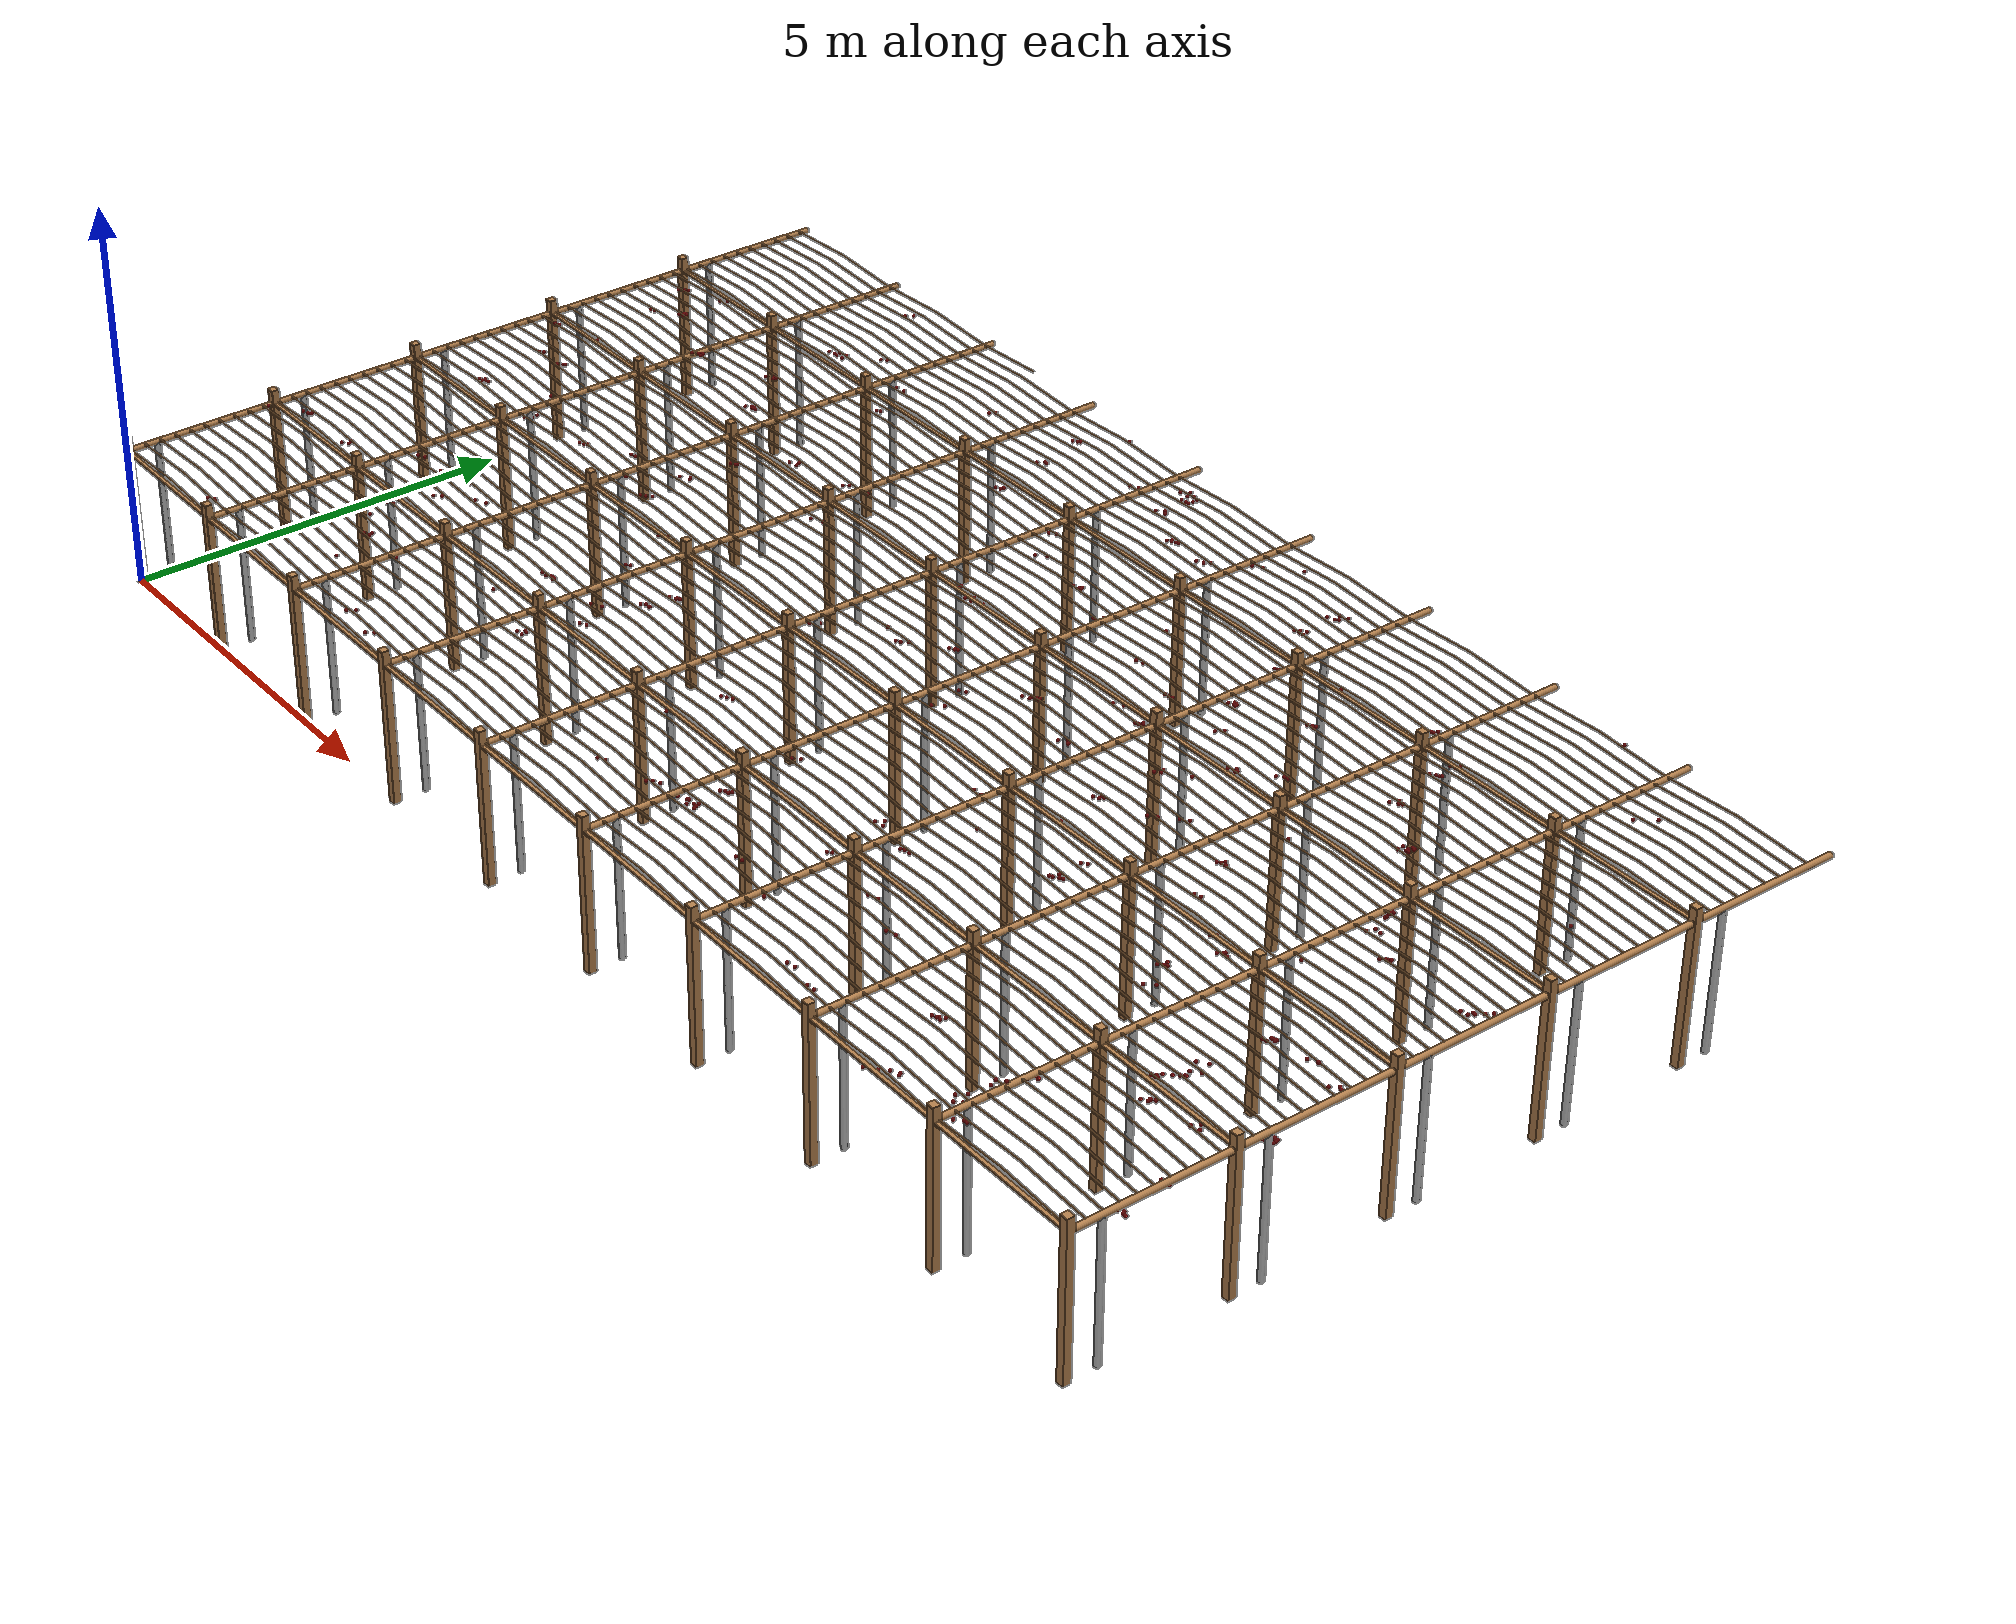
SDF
<sdf version="1.4">
 <model name="pergola">
  <include><name>post_0</name><uri>model://post</uri></include>
  <include><name>post_1</name><pose>0.0 2.0 0 0 0 0</pose><uri>model://post</uri></include>
  <include><name>post_2</name><pose>0.0 4.0 0 0 0 0</pose><uri>model://post</uri></include>
  <include><name>post_3</name><pose>0.0 6.0 0 0 0 0</pose><uri>model://post</uri></include>
  <include><name>post_4</name><pose>0.0 8.0 0 0 0 0</pose><uri>model://post</uri></include>
  <include><name>post_11</name><pose>2.0 0.0 0 0 0 0</pose><uri>model://post</uri></include>
  <include><name>post_12</name><pose>2.0 2.0 0 0 0 0</pose><uri>model://post</uri></include>
  <include><name>post_13</name><pose>2.0 4.0 0 0 0 0</pose><uri>model://post</uri></include>
  <include><name>post_14</name><pose>2.0 6.0 0 0 0 0</pose><uri>model://post</uri></include>
  <include><name>post_15</name><pose>2.0 8.0 0 0 0 0</pose><uri>model://post</uri></include>
  <include><name>post_22</name><pose>4.0 0.0 0 0 0 0</pose><uri>model://post</uri></include>
  <include><name>post_23</name><pose>4.0 2.0 0 0 0 0</pose><uri>model://post</uri></include>
  <include><name>post_24</name><pose>4.0 4.0 0 0 0 0</pose><uri>model://post</uri></include>
  <include><name>post_25</name><pose>4.0 6.0 0 0 0 0</pose><uri>model://post</uri></include>
  <include><name>post_26</name><pose>4.0 8.0 0 0 0 0</pose><uri>model://post</uri></include>
  <include><name>post_33</name><pose>6.0 0.0 0 0 0 0</pose><uri>model://post</uri></include>
  <include><name>post_34</name><pose>6.0 2.0 0 0 0 0</pose><uri>model://post</uri></include>
  <include><name>post_35</name><pose>6.0 4.0 0 0 0 0</pose><uri>model://post</uri></include>
  <include><name>post_36</name><pose>6.0 6.0 0 0 0 0</pose><uri>model://post</uri></include>
  <include><name>post_37</name><pose>6.0 8.0 0 0 0 0</pose><uri>model://post</uri></include>
  <include><name>post_44</name><pose>8.0 0.0 0 0 0 0</pose><uri>model://post</uri></include>
  <include><name>post_45</name><pose>8.0 2.0 0 0 0 0</pose><uri>model://post</uri></include>
  <include><name>post_46</name><pose>8.0 4.0 0 0 0 0</pose><uri>model://post</uri></include>
  <include><name>post_47</name><pose>8.0 6.0 0 0 0 0</pose><uri>model://post</uri></include>
  <include><name>post_48</name><pose>8.0 8.0 0 0 0 0</pose><uri>model://post</uri></include>
  <include><name>post_55</name><pose>10.0 0.0 0 0 0 0</pose><uri>model://post</uri></include>
  <include><name>post_56</name><pose>10.0 2.0 0 0 0 0</pose><uri>model://post</uri></include>
  <include><name>post_57</name><pose>10.0 4.0 0 0 0 0</pose><uri>model://post</uri></include>
  <include><name>post_58</name><pose>10.0 6.0 0 0 0 0</pose><uri>model://post</uri></include>
  <include><name>post_59</name><pose>10.0 8.0 0 0 0 0</pose><uri>model://post</uri></include>
  <include><name>post_66</name><pose>12.0 0.0 0 0 0 0</pose><uri>model://post</uri></include>
  <include><name>post_67</name><pose>12.0 2.0 0 0 0 0</pose><uri>model://post</uri></include>
  <include><name>post_68</name><pose>12.0 4.0 0 0 0 0</pose><uri>model://post</uri></include>
  <include><name>post_69</name><pose>12.0 6.0 0 0 0 0</pose><uri>model://post</uri></include>
  <include><name>post_70</name><pose>12.0 8.0 0 0 0 0</pose><uri>model://post</uri></include>
  <include><name>post_77</name><pose>14.0 0.0 0 0 0 0</pose><uri>model://post</uri></include>
  <include><name>post_78</name><pose>14.0 2.0 0 0 0 0</pose><uri>model://post</uri></include>
  <include><name>post_79</name><pose>14.0 4.0 0 0 0 0</pose><uri>model://post</uri></include>
  <include><name>post_80</name><pose>14.0 6.0 0 0 0 0</pose><uri>model://post</uri></include>
  <include><name>post_81</name><pose>14.0 8.0 0 0 0 0</pose><uri>model://post</uri></include>
  <include><name>post_88</name><pose>16.0 0.0 0 0 0 0</pose><uri>model://post</uri></include>
  <include><name>post_89</name><pose>16.0 2.0 0 0 0 0</pose><uri>model://post</uri></include>
  <include><name>post_90</name><pose>16.0 4.0 0 0 0 0</pose><uri>model://post</uri></include>
  <include><name>post_91</name><pose>16.0 6.0 0 0 0 0</pose><uri>model://post</uri></include>
  <include><name>post_92</name><pose>16.0 8.0 0 0 0 0</pose><uri>model://post</uri></include>
  <include><name>post_99</name><pose>18.0 0.0 0 0 0 0</pose><uri>model://post</uri></include>
  <include><name>post_100</name><pose>18.0 2.0 0 0 0 0</pose><uri>model://post</uri></include>
  <include><name>post_101</name><pose>18.0 4.0 0 0 0 0</pose><uri>model://post</uri></include>
  <include><name>post_102</name><pose>18.0 6.0 0 0 0 0</pose><uri>model://post</uri></include>
  <include><name>post_103</name><pose>18.0 8.0 0 0 0 0</pose><uri>model://post</uri></include>
  <link name="beam_0">
   <pose>1.0 0.0 1.81 0 0 0</pose>
   <collision name="collision"><geometry><box><size>2.0 0.06 0.02</size></box></geometry></collision>
   <visual name="visual">
    <geometry><box><size>2.0 0.06 0.02</size></box></geometry>
    <material><script><name>Gazebo/Wood</name></script></material>
   </visual>
   <inertial>
    <mass>5</mass>
    <inertia>
     <ixx>0.0016666666666666668</ixx>
     <ixy>0.0</ixy>
     <ixz>0.0</ixz>
     <iyy>1.6681666666666664</iyy>
     <iyz>0.0</iyz>
     <izz>1.6668333333333332</izz>
    </inertia>
   </inertial>
  </link>
  <link name="beam_1">
   <pose>1.0 2.0 1.81 0 0 0</pose>
   <collision name="collision"><geometry><box><size>2.0 0.06 0.02</size></box></geometry></collision>
   <visual name="visual">
    <geometry><box><size>2.0 0.06 0.02</size></box></geometry>
    <material><script><name>Gazebo/Wood</name></script></material>
   </visual>
   <inertial>
    <mass>5</mass>
    <inertia>
     <ixx>0.0016666666666666668</ixx>
     <ixy>0.0</ixy>
     <ixz>0.0</ixz>
     <iyy>1.6681666666666664</iyy>
     <iyz>0.0</iyz>
     <izz>1.6668333333333332</izz>
    </inertia>
   </inertial>
  </link>
  <link name="beam_2">
   <pose>1.0 4.0 1.81 0 0 0</pose>
   <collision name="collision"><geometry><box><size>2.0 0.06 0.02</size></box></geometry></collision>
   <visual name="visual">
    <geometry><box><size>2.0 0.06 0.02</size></box></geometry>
    <material><script><name>Gazebo/Wood</name></script></material>
   </visual>
   <inertial>
    <mass>5</mass>
    <inertia>
     <ixx>0.0016666666666666668</ixx>
     <ixy>0.0</ixy>
     <ixz>0.0</ixz>
     <iyy>1.6681666666666664</iyy>
     <iyz>0.0</iyz>
     <izz>1.6668333333333332</izz>
    </inertia>
   </inertial>
  </link>
  <link name="beam_3">
   <pose>1.0 6.0 1.81 0 0 0</pose>
   <collision name="collision"><geometry><box><size>2.0 0.06 0.02</size></box></geometry></collision>
   <visual name="visual">
    <geometry><box><size>2.0 0.06 0.02</size></box></geometry>
    <material><script><name>Gazebo/Wood</name></script></material>
   </visual>
   <inertial>
    <mass>5</mass>
    <inertia>
     <ixx>0.0016666666666666668</ixx>
     <ixy>0.0</ixy>
     <ixz>0.0</ixz>
     <iyy>1.6681666666666664</iyy>
     <iyz>0.0</iyz>
     <izz>1.6668333333333332</izz>
    </inertia>
   </inertial>
  </link>
  <link name="beam_4">
   <pose>1.0 8.0 1.81 0 0 0</pose>
   <collision name="collision"><geometry><box><size>2.0 0.06 0.02</size></box></geometry></collision>
   <visual name="visual">
    <geometry><box><size>2.0 0.06 0.02</size></box></geometry>
    <material><script><name>Gazebo/Wood</name></script></material>
   </visual>
   <inertial>
    <mass>5</mass>
    <inertia>
     <ixx>0.0016666666666666668</ixx>
     <ixy>0.0</ixy>
     <ixz>0.0</ixz>
     <iyy>1.6681666666666664</iyy>
     <iyz>0.0</iyz>
     <izz>1.6668333333333332</izz>
    </inertia>
   </inertial>
  </link>
  <link name="beam_11">
   <pose>3.0 0.0 1.81 0 0 0</pose>
   <collision name="collision"><geometry><box><size>2.0 0.06 0.02</size></box></geometry></collision>
   <visual name="visual">
    <geometry><box><size>2.0 0.06 0.02</size></box></geometry>
    <material><script><name>Gazebo/Wood</name></script></material>
   </visual>
   <inertial>
    <mass>5</mass>
    <inertia>
     <ixx>0.0016666666666666668</ixx>
     <ixy>0.0</ixy>
     <ixz>0.0</ixz>
     <iyy>1.6681666666666664</iyy>
     <iyz>0.0</iyz>
     <izz>1.6668333333333332</izz>
    </inertia>
   </inertial>
  </link>
  <link name="beam_12">
   <pose>3.0 2.0 1.81 0 0 0</pose>
   <collision name="collision"><geometry><box><size>2.0 0.06 0.02</size></box></geometry></collision>
   <visual name="visual">
    <geometry><box><size>2.0 0.06 0.02</size></box></geometry>
    <material><script><name>Gazebo/Wood</name></script></material>
   </visual>
   <inertial>
    <mass>5</mass>
    <inertia>
     <ixx>0.0016666666666666668</ixx>
     <ixy>0.0</ixy>
     <ixz>0.0</ixz>
     <iyy>1.6681666666666664</iyy>
     <iyz>0.0</iyz>
     <izz>1.6668333333333332</izz>
    </inertia>
   </inertial>
  </link>
  <link name="beam_13">
   <pose>3.0 4.0 1.81 0 0 0</pose>
   <collision name="collision"><geometry><box><size>2.0 0.06 0.02</size></box></geometry></collision>
   <visual name="visual">
    <geometry><box><size>2.0 0.06 0.02</size></box></geometry>
    <material><script><name>Gazebo/Wood</name></script></material>
   </visual>
   <inertial>
    <mass>5</mass>
    <inertia>
     <ixx>0.0016666666666666668</ixx>
     <ixy>0.0</ixy>
     <ixz>0.0</ixz>
     <iyy>1.6681666666666664</iyy>
     <iyz>0.0</iyz>
     <izz>1.6668333333333332</izz>
    </inertia>
   </inertial>
  </link>
  <link name="beam_14">
   <pose>3.0 6.0 1.81 0 0 0</pose>
   <collision name="collision"><geometry><box><size>2.0 0.06 0.02</size></box></geometry></collision>
   <visual name="visual">
    <geometry><box><size>2.0 0.06 0.02</size></box></geometry>
    <material><script><name>Gazebo/Wood</name></script></material>
   </visual>
   <inertial>
    <mass>5</mass>
    <inertia>
     <ixx>0.0016666666666666668</ixx>
     <ixy>0.0</ixy>
     <ixz>0.0</ixz>
     <iyy>1.6681666666666664</iyy>
     <iyz>0.0</iyz>
     <izz>1.6668333333333332</izz>
    </inertia>
   </inertial>
  </link>
  <link name="beam_15">
   <pose>3.0 8.0 1.81 0 0 0</pose>
   <collision name="collision"><geometry><box><size>2.0 0.06 0.02</size></box></geometry></collision>
   <visual name="visual">
    <geometry><box><size>2.0 0.06 0.02</size></box></geometry>
    <material><script><name>Gazebo/Wood</name></script></material>
   </visual>
   <inertial>
    <mass>5</mass>
    <inertia>
     <ixx>0.0016666666666666668</ixx>
     <ixy>0.0</ixy>
     <ixz>0.0</ixz>
     <iyy>1.6681666666666664</iyy>
     <iyz>0.0</iyz>
     <izz>1.6668333333333332</izz>
    </inertia>
   </inertial>
  </link>
  <link name="beam_22">
   <pose>5.0 0.0 1.81 0 0 0</pose>
   <collision name="collision"><geometry><box><size>2.0 0.06 0.02</size></box></geometry></collision>
   <visual name="visual">
    <geometry><box><size>2.0 0.06 0.02</size></box></geometry>
    <material><script><name>Gazebo/Wood</name></script></material>
   </visual>
   <inertial>
    <mass>5</mass>
    <inertia>
     <ixx>0.0016666666666666668</ixx>
     <ixy>0.0</ixy>
     <ixz>0.0</ixz>
     <iyy>1.6681666666666664</iyy>
     <iyz>0.0</iyz>
     <izz>1.6668333333333332</izz>
    </inertia>
   </inertial>
  </link>
  <link name="beam_23">
   <pose>5.0 2.0 1.81 0 0 0</pose>
   <collision name="collision"><geometry><box><size>2.0 0.06 0.02</size></box></geometry></collision>
   <visual name="visual">
    <geometry><box><size>2.0 0.06 0.02</size></box></geometry>
    <material><script><name>Gazebo/Wood</name></script></material>
   </visual>
   <inertial>
    <mass>5</mass>
    <inertia>
     <ixx>0.0016666666666666668</ixx>
     <ixy>0.0</ixy>
     <ixz>0.0</ixz>
     <iyy>1.6681666666666664</iyy>
     <iyz>0.0</iyz>
     <izz>1.6668333333333332</izz>
    </inertia>
   </inertial>
  </link>
  <link name="beam_24">
   <pose>5.0 4.0 1.81 0 0 0</pose>
   <collision name="collision"><geometry><box><size>2.0 0.06 0.02</size></box></geometry></collision>
   <visual name="visual">
    <geometry><box><size>2.0 0.06 0.02</size></box></geometry>
    <material><script><name>Gazebo/Wood</name></script></material>
   </visual>
   <inertial>
    <mass>5</mass>
    <inertia>
     <ixx>0.0016666666666666668</ixx>
     <ixy>0.0</ixy>
     <ixz>0.0</ixz>
     <iyy>1.6681666666666664</iyy>
     <iyz>0.0</iyz>
     <izz>1.6668333333333332</izz>
    </inertia>
   </inertial>
  </link>
  <link name="beam_25">
   <pose>5.0 6.0 1.81 0 0 0</pose>
   <collision name="collision"><geometry><box><size>2.0 0.06 0.02</size></box></geometry></collision>
   <visual name="visual">
    <geometry><box><size>2.0 0.06 0.02</size></box></geometry>
    <material><script><name>Gazebo/Wood</name></script></material>
   </visual>
   <inertial>
    <mass>5</mass>
    <inertia>
     <ixx>0.0016666666666666668</ixx>
     <ixy>0.0</ixy>
     <ixz>0.0</ixz>
     <iyy>1.6681666666666664</iyy>
     <iyz>0.0</iyz>
     <izz>1.6668333333333332</izz>
    </inertia>
   </inertial>
  </link>
  <link name="beam_26">
   <pose>5.0 8.0 1.81 0 0 0</pose>
   <collision name="collision"><geometry><box><size>2.0 0.06 0.02</size></box></geometry></collision>
   <visual name="visual">
    <geometry><box><size>2.0 0.06 0.02</size></box></geometry>
    <material><script><name>Gazebo/Wood</name></script></material>
   </visual>
   <inertial>
    <mass>5</mass>
    <inertia>
     <ixx>0.0016666666666666668</ixx>
     <ixy>0.0</ixy>
     <ixz>0.0</ixz>
     <iyy>1.6681666666666664</iyy>
     <iyz>0.0</iyz>
     <izz>1.6668333333333332</izz>
    </inertia>
   </inertial>
  </link>
  <link name="beam_33">
   <pose>7.0 0.0 1.81 0 0 0</pose>
   <collision name="collision"><geometry><box><size>2.0 0.06 0.02</size></box></geometry></collision>
   <visual name="visual">
    <geometry><box><size>2.0 0.06 0.02</size></box></geometry>
    <material><script><name>Gazebo/Wood</name></script></material>
   </visual>
   <inertial>
    <mass>5</mass>
    <inertia>
     <ixx>0.0016666666666666668</ixx>
     <ixy>0.0</ixy>
     <ixz>0.0</ixz>
     <iyy>1.6681666666666664</iyy>
     <iyz>0.0</iyz>
     <izz>1.6668333333333332</izz>
    </inertia>
   </inertial>
  </link>
  <link name="beam_34">
   <pose>7.0 2.0 1.81 0 0 0</pose>
   <collision name="collision"><geometry><box><size>2.0 0.06 0.02</size></box></geometry></collision>
   <visual name="visual">
    <geometry><box><size>2.0 0.06 0.02</size></box></geometry>
    <material><script><name>Gazebo/Wood</name></script></material>
   </visual>
   <inertial>
    <mass>5</mass>
    <inertia>
     <ixx>0.0016666666666666668</ixx>
     <ixy>0.0</ixy>
     <ixz>0.0</ixz>
     <iyy>1.6681666666666664</iyy>
     <iyz>0.0</iyz>
     <izz>1.6668333333333332</izz>
    </inertia>
   </inertial>
  </link>
  <link name="beam_35">
   <pose>7.0 4.0 1.81 0 0 0</pose>
   <collision name="collision"><geometry><box><size>2.0 0.06 0.02</size></box></geometry></collision>
   <visual name="visual">
    <geometry><box><size>2.0 0.06 0.02</size></box></geometry>
    <material><script><name>Gazebo/Wood</name></script></material>
   </visual>
   <inertial>
    <mass>5</mass>
    <inertia>
     <ixx>0.0016666666666666668</ixx>
     <ixy>0.0</ixy>
     <ixz>0.0</ixz>
     <iyy>1.6681666666666664</iyy>
     <iyz>0.0</iyz>
     <izz>1.6668333333333332</izz>
    </inertia>
   </inertial>
  </link>
  <link name="beam_36">
   <pose>7.0 6.0 1.81 0 0 0</pose>
   <collision name="collision"><geometry><box><size>2.0 0.06 0.02</size></box></geometry></collision>
   <visual name="visual">
    <geometry><box><size>2.0 0.06 0.02</size></box></geometry>
    <material><script><name>Gazebo/Wood</name></script></material>
   </visual>
   <inertial>
    <mass>5</mass>
    <inertia>
     <ixx>0.0016666666666666668</ixx>
     <ixy>0.0</ixy>
     <ixz>0.0</ixz>
     <iyy>1.6681666666666664</iyy>
     <iyz>0.0</iyz>
     <izz>1.6668333333333332</izz>
    </inertia>
   </inertial>
  </link>
  <link name="beam_37">
   <pose>7.0 8.0 1.81 0 0 0</pose>
   <collision name="collision"><geometry><box><size>2.0 0.06 0.02</size></box></geometry></collision>
   <visual name="visual">
    <geometry><box><size>2.0 0.06 0.02</size></box></geometry>
    <material><script><name>Gazebo/Wood</name></script></material>
   </visual>
   <inertial>
    <mass>5</mass>
    <inertia>
     <ixx>0.0016666666666666668</ixx>
     <ixy>0.0</ixy>
     <ixz>0.0</ixz>
     <iyy>1.6681666666666664</iyy>
     <iyz>0.0</iyz>
     <izz>1.6668333333333332</izz>
    </inertia>
   </inertial>
  </link>
  <link name="beam_44">
   <pose>9.0 0.0 1.81 0 0 0</pose>
   <collision name="collision"><geometry><box><size>2.0 0.06 0.02</size></box></geometry></collision>
   <visual name="visual">
    <geometry><box><size>2.0 0.06 0.02</size></box></geometry>
    <material><script><name>Gazebo/Wood</name></script></material>
   </visual>
   <inertial>
    <mass>5</mass>
    <inertia>
     <ixx>0.0016666666666666668</ixx>
     <ixy>0.0</ixy>
     <ixz>0.0</ixz>
     <iyy>1.6681666666666664</iyy>
     <iyz>0.0</iyz>
     <izz>1.6668333333333332</izz>
    </inertia>
   </inertial>
  </link>
  <link name="beam_45">
   <pose>9.0 2.0 1.81 0 0 0</pose>
   <collision name="collision"><geometry><box><size>2.0 0.06 0.02</size></box></geometry></collision>
   <visual name="visual">
    <geometry><box><size>2.0 0.06 0.02</size></box></geometry>
    <material><script><name>Gazebo/Wood</name></script></material>
   </visual>
   <inertial>
    <mass>5</mass>
    <inertia>
     <ixx>0.0016666666666666668</ixx>
     <ixy>0.0</ixy>
     <ixz>0.0</ixz>
     <iyy>1.6681666666666664</iyy>
     <iyz>0.0</iyz>
     <izz>1.6668333333333332</izz>
    </inertia>
   </inertial>
  </link>
  <link name="beam_46">
   <pose>9.0 4.0 1.81 0 0 0</pose>
   <collision name="collision"><geometry><box><size>2.0 0.06 0.02</size></box></geometry></collision>
   <visual name="visual">
    <geometry><box><size>2.0 0.06 0.02</size></box></geometry>
    <material><script><name>Gazebo/Wood</name></script></material>
   </visual>
   <inertial>
    <mass>5</mass>
    <inertia>
     <ixx>0.0016666666666666668</ixx>
     <ixy>0.0</ixy>
     <ixz>0.0</ixz>
     <iyy>1.6681666666666664</iyy>
     <iyz>0.0</iyz>
     <izz>1.6668333333333332</izz>
    </inertia>
   </inertial>
  </link>
  <link name="beam_47">
   <pose>9.0 6.0 1.81 0 0 0</pose>
   <collision name="collision"><geometry><box><size>2.0 0.06 0.02</size></box></geometry></collision>
   <visual name="visual">
    <geometry><box><size>2.0 0.06 0.02</size></box></geometry>
    <material><script><name>Gazebo/Wood</name></script></material>
   </visual>
   <inertial>
    <mass>5</mass>
    <inertia>
     <ixx>0.0016666666666666668</ixx>
     <ixy>0.0</ixy>
     <ixz>0.0</ixz>
     <iyy>1.6681666666666664</iyy>
     <iyz>0.0</iyz>
     <izz>1.6668333333333332</izz>
    </inertia>
   </inertial>
  </link>
  <link name="beam_48">
   <pose>9.0 8.0 1.81 0 0 0</pose>
   <collision name="collision"><geometry><box><size>2.0 0.06 0.02</size></box></geometry></collision>
   <visual name="visual">
    <geometry><box><size>2.0 0.06 0.02</size></box></geometry>
    <material><script><name>Gazebo/Wood</name></script></material>
   </visual>
   <inertial>
    <mass>5</mass>
    <inertia>
     <ixx>0.0016666666666666668</ixx>
     <ixy>0.0</ixy>
     <ixz>0.0</ixz>
     <iyy>1.6681666666666664</iyy>
     <iyz>0.0</iyz>
     <izz>1.6668333333333332</izz>
    </inertia>
   </inertial>
  </link>
  <link name="beam_55">
   <pose>11.0 0.0 1.81 0 0 0</pose>
   <collision name="collision"><geometry><box><size>2.0 0.06 0.02</size></box></geometry></collision>
   <visual name="visual">
    <geometry><box><size>2.0 0.06 0.02</size></box></geometry>
    <material><script><name>Gazebo/Wood</name></script></material>
   </visual>
   <inertial>
    <mass>5</mass>
    <inertia>
     <ixx>0.0016666666666666668</ixx>
     <ixy>0.0</ixy>
     <ixz>0.0</ixz>
     <iyy>1.6681666666666664</iyy>
     <iyz>0.0</iyz>
     <izz>1.6668333333333332</izz>
    </inertia>
   </inertial>
  </link>
  <link name="beam_56">
   <pose>11.0 2.0 1.81 0 0 0</pose>
   <collision name="collision"><geometry><box><size>2.0 0.06 0.02</size></box></geometry></collision>
   <visual name="visual">
    <geometry><box><size>2.0 0.06 0.02</size></box></geometry>
    <material><script><name>Gazebo/Wood</name></script></material>
   </visual>
   <inertial>
    <mass>5</mass>
    <inertia>
     <ixx>0.0016666666666666668</ixx>
     <ixy>0.0</ixy>
     <ixz>0.0</ixz>
     <iyy>1.6681666666666664</iyy>
     <iyz>0.0</iyz>
     <izz>1.6668333333333332</izz>
    </inertia>
   </inertial>
  </link>
  <link name="beam_57">
   <pose>11.0 4.0 1.81 0 0 0</pose>
   <collision name="collision"><geometry><box><size>2.0 0.06 0.02</size></box></geometry></collision>
   <visual name="visual">
    <geometry><box><size>2.0 0.06 0.02</size></box></geometry>
    <material><script><name>Gazebo/Wood</name></script></material>
   </visual>
   <inertial>
    <mass>5</mass>
    <inertia>
     <ixx>0.0016666666666666668</ixx>
     <ixy>0.0</ixy>
     <ixz>0.0</ixz>
     <iyy>1.6681666666666664</iyy>
     <iyz>0.0</iyz>
     <izz>1.6668333333333332</izz>
    </inertia>
   </inertial>
  </link>
  <link name="beam_58">
   <pose>11.0 6.0 1.81 0 0 0</pose>
   <collision name="collision"><geometry><box><size>2.0 0.06 0.02</size></box></geometry></collision>
   <visual name="visual">
    <geometry><box><size>2.0 0.06 0.02</size></box></geometry>
    <material><script><name>Gazebo/Wood</name></script></material>
   </visual>
   <inertial>
    <mass>5</mass>
    <inertia>
     <ixx>0.0016666666666666668</ixx>
     <ixy>0.0</ixy>
     <ixz>0.0</ixz>
     <iyy>1.6681666666666664</iyy>
     <iyz>0.0</iyz>
     <izz>1.6668333333333332</izz>
    </inertia>
   </inertial>
  </link>
  <link name="beam_59">
   <pose>11.0 8.0 1.81 0 0 0</pose>
   <collision name="collision"><geometry><box><size>2.0 0.06 0.02</size></box></geometry></collision>
   <visual name="visual">
    <geometry><box><size>2.0 0.06 0.02</size></box></geometry>
    <material><script><name>Gazebo/Wood</name></script></material>
   </visual>
   <inertial>
    <mass>5</mass>
    <inertia>
     <ixx>0.0016666666666666668</ixx>
     <ixy>0.0</ixy>
     <ixz>0.0</ixz>
     <iyy>1.6681666666666664</iyy>
     <iyz>0.0</iyz>
     <izz>1.6668333333333332</izz>
    </inertia>
   </inertial>
  </link>
  <link name="beam_66">
   <pose>13.0 0.0 1.81 0 0 0</pose>
   <collision name="collision"><geometry><box><size>2.0 0.06 0.02</size></box></geometry></collision>
   <visual name="visual">
    <geometry><box><size>2.0 0.06 0.02</size></box></geometry>
    <material><script><name>Gazebo/Wood</name></script></material>
   </visual>
   <inertial>
    <mass>5</mass>
    <inertia>
     <ixx>0.0016666666666666668</ixx>
     <ixy>0.0</ixy>
     <ixz>0.0</ixz>
     <iyy>1.6681666666666664</iyy>
     <iyz>0.0</iyz>
     <izz>1.6668333333333332</izz>
    </inertia>
   </inertial>
  </link>
  <link name="beam_67">
   <pose>13.0 2.0 1.81 0 0 0</pose>
   <collision name="collision"><geometry><box><size>2.0 0.06 0.02</size></box></geometry></collision>
   <visual name="visual">
    <geometry><box><size>2.0 0.06 0.02</size></box></geometry>
    <material><script><name>Gazebo/Wood</name></script></material>
   </visual>
   <inertial>
    <mass>5</mass>
    <inertia>
     <ixx>0.0016666666666666668</ixx>
     <ixy>0.0</ixy>
     <ixz>0.0</ixz>
     <iyy>1.6681666666666664</iyy>
     <iyz>0.0</iyz>
     <izz>1.6668333333333332</izz>
    </inertia>
   </inertial>
  </link>
  <link name="beam_68">
   <pose>13.0 4.0 1.81 0 0 0</pose>
   <collision name="collision"><geometry><box><size>2.0 0.06 0.02</size></box></geometry></collision>
   <visual name="visual">
    <geometry><box><size>2.0 0.06 0.02</size></box></geometry>
    <material><script><name>Gazebo/Wood</name></script></material>
   </visual>
   <inertial>
    <mass>5</mass>
    <inertia>
     <ixx>0.0016666666666666668</ixx>
     <ixy>0.0</ixy>
     <ixz>0.0</ixz>
     <iyy>1.6681666666666664</iyy>
     <iyz>0.0</iyz>
     <izz>1.6668333333333332</izz>
    </inertia>
   </inertial>
  </link>
  <link name="beam_69">
   <pose>13.0 6.0 1.81 0 0 0</pose>
   <collision name="collision"><geometry><box><size>2.0 0.06 0.02</size></box></geometry></collision>
   <visual name="visual">
    <geometry><box><size>2.0 0.06 0.02</size></box></geometry>
    <material><script><name>Gazebo/Wood</name></script></material>
   </visual>
   <inertial>
    <mass>5</mass>
    <inertia>
     <ixx>0.0016666666666666668</ixx>
     <ixy>0.0</ixy>
     <ixz>0.0</ixz>
     <iyy>1.6681666666666664</iyy>
     <iyz>0.0</iyz>
     <izz>1.6668333333333332</izz>
    </inertia>
   </inertial>
  </link>
  <link name="beam_70">
   <pose>13.0 8.0 1.81 0 0 0</pose>
   <collision name="collision"><geometry><box><size>2.0 0.06 0.02</size></box></geometry></collision>
   <visual name="visual">
    <geometry><box><size>2.0 0.06 0.02</size></box></geometry>
    <material><script><name>Gazebo/Wood</name></script></material>
   </visual>
   <inertial>
    <mass>5</mass>
    <inertia>
     <ixx>0.0016666666666666668</ixx>
     <ixy>0.0</ixy>
     <ixz>0.0</ixz>
     <iyy>1.6681666666666664</iyy>
     <iyz>0.0</iyz>
     <izz>1.6668333333333332</izz>
    </inertia>
   </inertial>
  </link>
  <link name="beam_77">
   <pose>15.0 0.0 1.81 0 0 0</pose>
   <collision name="collision"><geometry><box><size>2.0 0.06 0.02</size></box></geometry></collision>
   <visual name="visual">
    <geometry><box><size>2.0 0.06 0.02</size></box></geometry>
    <material><script><name>Gazebo/Wood</name></script></material>
   </visual>
   <inertial>
    <mass>5</mass>
    <inertia>
     <ixx>0.0016666666666666668</ixx>
     <ixy>0.0</ixy>
     <ixz>0.0</ixz>
     <iyy>1.6681666666666664</iyy>
     <iyz>0.0</iyz>
     <izz>1.6668333333333332</izz>
    </inertia>
   </inertial>
  </link>
  <link name="beam_78">
   <pose>15.0 2.0 1.81 0 0 0</pose>
   <collision name="collision"><geometry><box><size>2.0 0.06 0.02</size></box></geometry></collision>
   <visual name="visual">
    <geometry><box><size>2.0 0.06 0.02</size></box></geometry>
    <material><script><name>Gazebo/Wood</name></script></material>
   </visual>
   <inertial>
    <mass>5</mass>
    <inertia>
     <ixx>0.0016666666666666668</ixx>
     <ixy>0.0</ixy>
     <ixz>0.0</ixz>
     <iyy>1.6681666666666664</iyy>
     <iyz>0.0</iyz>
     <izz>1.6668333333333332</izz>
    </inertia>
   </inertial>
  </link>
  <link name="beam_79">
   <pose>15.0 4.0 1.81 0 0 0</pose>
   <collision name="collision"><geometry><box><size>2.0 0.06 0.02</size></box></geometry></collision>
   <visual name="visual">
    <geometry><box><size>2.0 0.06 0.02</size></box></geometry>
    <material><script><name>Gazebo/Wood</name></script></material>
   </visual>
   <inertial>
    <mass>5</mass>
    <inertia>
     <ixx>0.0016666666666666668</ixx>
     <ixy>0.0</ixy>
     <ixz>0.0</ixz>
     <iyy>1.6681666666666664</iyy>
     <iyz>0.0</iyz>
     <izz>1.6668333333333332</izz>
    </inertia>
   </inertial>
  </link>
  <link name="beam_80">
   <pose>15.0 6.0 1.81 0 0 0</pose>
   <collision name="collision"><geometry><box><size>2.0 0.06 0.02</size></box></geometry></collision>
   <visual name="visual">
    <geometry><box><size>2.0 0.06 0.02</size></box></geometry>
    <material><script><name>Gazebo/Wood</name></script></material>
   </visual>
   <inertial>
    <mass>5</mass>
    <inertia>
     <ixx>0.0016666666666666668</ixx>
     <ixy>0.0</ixy>
     <ixz>0.0</ixz>
     <iyy>1.6681666666666664</iyy>
     <iyz>0.0</iyz>
     <izz>1.6668333333333332</izz>
    </inertia>
   </inertial>
  </link>
  <link name="beam_81">
   <pose>15.0 8.0 1.81 0 0 0</pose>
   <collision name="collision"><geometry><box><size>2.0 0.06 0.02</size></box></geometry></collision>
   <visual name="visual">
    <geometry><box><size>2.0 0.06 0.02</size></box></geometry>
    <material><script><name>Gazebo/Wood</name></script></material>
   </visual>
   <inertial>
    <mass>5</mass>
    <inertia>
     <ixx>0.0016666666666666668</ixx>
     <ixy>0.0</ixy>
     <ixz>0.0</ixz>
     <iyy>1.6681666666666664</iyy>
     <iyz>0.0</iyz>
     <izz>1.6668333333333332</izz>
    </inertia>
   </inertial>
  </link>
  <link name="beam_88">
   <pose>17.0 0.0 1.81 0 0 0</pose>
   <collision name="collision"><geometry><box><size>2.0 0.06 0.02</size></box></geometry></collision>
   <visual name="visual">
    <geometry><box><size>2.0 0.06 0.02</size></box></geometry>
    <material><script><name>Gazebo/Wood</name></script></material>
   </visual>
   <inertial>
    <mass>5</mass>
    <inertia>
     <ixx>0.0016666666666666668</ixx>
     <ixy>0.0</ixy>
     <ixz>0.0</ixz>
     <iyy>1.6681666666666664</iyy>
     <iyz>0.0</iyz>
     <izz>1.6668333333333332</izz>
    </inertia>
   </inertial>
  </link>
  <link name="beam_89">
   <pose>17.0 2.0 1.81 0 0 0</pose>
   <collision name="collision"><geometry><box><size>2.0 0.06 0.02</size></box></geometry></collision>
   <visual name="visual">
    <geometry><box><size>2.0 0.06 0.02</size></box></geometry>
    <material><script><name>Gazebo/Wood</name></script></material>
   </visual>
   <inertial>
    <mass>5</mass>
    <inertia>
     <ixx>0.0016666666666666668</ixx>
     <ixy>0.0</ixy>
     <ixz>0.0</ixz>
     <iyy>1.6681666666666664</iyy>
     <iyz>0.0</iyz>
     <izz>1.6668333333333332</izz>
    </inertia>
   </inertial>
  </link>
  <link name="beam_90">
   <pose>17.0 4.0 1.81 0 0 0</pose>
   <collision name="collision"><geometry><box><size>2.0 0.06 0.02</size></box></geometry></collision>
   <visual name="visual">
    <geometry><box><size>2.0 0.06 0.02</size></box></geometry>
    <material><script><name>Gazebo/Wood</name></script></material>
   </visual>
   <inertial>
    <mass>5</mass>
    <inertia>
     <ixx>0.0016666666666666668</ixx>
     <ixy>0.0</ixy>
     <ixz>0.0</ixz>
     <iyy>1.6681666666666664</iyy>
     <iyz>0.0</iyz>
     <izz>1.6668333333333332</izz>
    </inertia>
   </inertial>
  </link>
  <link name="beam_91">
   <pose>17.0 6.0 1.81 0 0 0</pose>
   <collision name="collision"><geometry><box><size>2.0 0.06 0.02</size></box></geometry></collision>
   <visual name="visual">
    <geometry><box><size>2.0 0.06 0.02</size></box></geometry>
    <material><script><name>Gazebo/Wood</name></script></material>
   </visual>
   <inertial>
    <mass>5</mass>
    <inertia>
     <ixx>0.0016666666666666668</ixx>
     <ixy>0.0</ixy>
     <ixz>0.0</ixz>
     <iyy>1.6681666666666664</iyy>
     <iyz>0.0</iyz>
     <izz>1.6668333333333332</izz>
    </inertia>
   </inertial>
  </link>
  <link name="beam_92">
   <pose>17.0 8.0 1.81 0 0 0</pose>
   <collision name="collision"><geometry><box><size>2.0 0.06 0.02</size></box></geometry></collision>
   <visual name="visual">
    <geometry><box><size>2.0 0.06 0.02</size></box></geometry>
    <material><script><name>Gazebo/Wood</name></script></material>
   </visual>
   <inertial>
    <mass>5</mass>
    <inertia>
     <ixx>0.0016666666666666668</ixx>
     <ixy>0.0</ixy>
     <ixz>0.0</ixz>
     <iyy>1.6681666666666664</iyy>
     <iyz>0.0</iyz>
     <izz>1.6668333333333332</izz>
    </inertia>
   </inertial>
  </link>
  <include><name>tree_0</name><pose>0.0 0.4 0 0 0 0</pose><uri>model://tree_trunk</uri></include>
  <include><name>tree_1</name><pose>0.0 2.4 0 0 0 0</pose><uri>model://tree_trunk</uri></include>
  <include><name>tree_2</name><pose>0.0 4.4 0 0 0 0</pose><uri>model://tree_trunk</uri></include>
  <include><name>tree_3</name><pose>0.0 6.4 0 0 0 0</pose><uri>model://tree_trunk</uri></include>
  <include><name>tree_4</name><pose>0.0 8.4 0 0 0 0</pose><uri>model://tree_trunk</uri></include>
  <include><name>tree_10</name><pose>2.0 0.4 0 0 0 0</pose><uri>model://tree_trunk</uri></include>
  <include><name>tree_11</name><pose>2.0 2.4 0 0 0 0</pose><uri>model://tree_trunk</uri></include>
  <include><name>tree_12</name><pose>2.0 4.4 0 0 0 0</pose><uri>model://tree_trunk</uri></include>
  <include><name>tree_13</name><pose>2.0 6.4 0 0 0 0</pose><uri>model://tree_trunk</uri></include>
  <include><name>tree_14</name><pose>2.0 8.4 0 0 0 0</pose><uri>model://tree_trunk</uri></include>
  <include><name>tree_20</name><pose>4.0 0.4 0 0 0 0</pose><uri>model://tree_trunk</uri></include>
  <include><name>tree_21</name><pose>4.0 2.4 0 0 0 0</pose><uri>model://tree_trunk</uri></include>
  <include><name>tree_22</name><pose>4.0 4.4 0 0 0 0</pose><uri>model://tree_trunk</uri></include>
  <include><name>tree_23</name><pose>4.0 6.4 0 0 0 0</pose><uri>model://tree_trunk</uri></include>
  <include><name>tree_24</name><pose>4.0 8.4 0 0 0 0</pose><uri>model://tree_trunk</uri></include>
  <include><name>tree_30</name><pose>6.0 0.4 0 0 0 0</pose><uri>model://tree_trunk</uri></include>
  <include><name>tree_31</name><pose>6.0 2.4 0 0 0 0</pose><uri>model://tree_trunk</uri></include>
  <include><name>tree_32</name><pose>6.0 4.4 0 0 0 0</pose><uri>model://tree_trunk</uri></include>
  <include><name>tree_33</name><pose>6.0 6.4 0 0 0 0</pose><uri>model://tree_trunk</uri></include>
  <include><name>tree_34</name><pose>6.0 8.4 0 0 0 0</pose><uri>model://tree_trunk</uri></include>
  <include><name>tree_40</name><pose>8.0 0.4 0 0 0 0</pose><uri>model://tree_trunk</uri></include>
  <include><name>tree_41</name><pose>8.0 2.4 0 0 0 0</pose><uri>model://tree_trunk</uri></include>
  <include><name>tree_42</name><pose>8.0 4.4 0 0 0 0</pose><uri>model://tree_trunk</uri></include>
  <include><name>tree_43</name><pose>8.0 6.4 0 0 0 0</pose><uri>model://tree_trunk</uri></include>
  <include><name>tree_44</name><pose>8.0 8.4 0 0 0 0</pose><uri>model://tree_trunk</uri></include>
  <include><name>tree_50</name><pose>10.0 0.4 0 0 0 0</pose><uri>model://tree_trunk</uri></include>
  <include><name>tree_51</name><pose>10.0 2.4 0 0 0 0</pose><uri>model://tree_trunk</uri></include>
  <include><name>tree_52</name><pose>10.0 4.4 0 0 0 0</pose><uri>model://tree_trunk</uri></include>
  <include><name>tree_53</name><pose>10.0 6.4 0 0 0 0</pose><uri>model://tree_trunk</uri></include>
  <include><name>tree_54</name><pose>10.0 8.4 0 0 0 0</pose><uri>model://tree_trunk</uri></include>
  <include><name>tree_60</name><pose>12.0 0.4 0 0 0 0</pose><uri>model://tree_trunk</uri></include>
  <include><name>tree_61</name><pose>12.0 2.4 0 0 0 0</pose><uri>model://tree_trunk</uri></include>
  <include><name>tree_62</name><pose>12.0 4.4 0 0 0 0</pose><uri>model://tree_trunk</uri></include>
  <include><name>tree_63</name><pose>12.0 6.4 0 0 0 0</pose><uri>model://tree_trunk</uri></include>
  <include><name>tree_64</name><pose>12.0 8.4 0 0 0 0</pose><uri>model://tree_trunk</uri></include>
  <include><name>tree_70</name><pose>14.0 0.4 0 0 0 0</pose><uri>model://tree_trunk</uri></include>
  <include><name>tree_71</name><pose>14.0 2.4 0 0 0 0</pose><uri>model://tree_trunk</uri></include>
  <include><name>tree_72</name><pose>14.0 4.4 0 0 0 0</pose><uri>model://tree_trunk</uri></include>
  <include><name>tree_73</name><pose>14.0 6.4 0 0 0 0</pose><uri>model://tree_trunk</uri></include>
  <include><name>tree_74</name><pose>14.0 8.4 0 0 0 0</pose><uri>model://tree_trunk</uri></include>
  <include><name>tree_80</name><pose>16.0 0.4 0 0 0 0</pose><uri>model://tree_trunk</uri></include>
  <include><name>tree_81</name><pose>16.0 2.4 0 0 0 0</pose><uri>model://tree_trunk</uri></include>
  <include><name>tree_82</name><pose>16.0 4.4 0 0 0 0</pose><uri>model://tree_trunk</uri></include>
  <include><name>tree_83</name><pose>16.0 6.4 0 0 0 0</pose><uri>model://tree_trunk</uri></include>
  <include><name>tree_84</name><pose>16.0 8.4 0 0 0 0</pose><uri>model://tree_trunk</uri></include>
  <include><name>tree_90</name><pose>18.0 0.4 0 0 0 0</pose><uri>model://tree_trunk</uri></include>
  <include><name>tree_91</name><pose>18.0 2.4 0 0 0 0</pose><uri>model://tree_trunk</uri></include>
  <include><name>tree_92</name><pose>18.0 4.4 0 0 0 0</pose><uri>model://tree_trunk</uri></include>
  <include><name>tree_93</name><pose>18.0 6.4 0 0 0 0</pose><uri>model://tree_trunk</uri></include>
  <include><name>tree_94</name><pose>18.0 8.4 0 0 0 0</pose><uri>model://tree_trunk</uri></include>
  <link name="baseBranch_0">
   <pose>0.0 1.0 1.8 1.5707963267948966 0 0</pose>
   <collision name="collision">
    <geometry><cylinder><radius>0.04</radius><length>1.94</length></cylinder></geometry>
   </collision>
   <visual name="visual">
    <geometry><cylinder><radius>0.04</radius><length>1.94</length></cylinder></geometry>
    <material><script><name>Gazebo/WoodFloor</name></script></material>
   </visual>
   <inertial>
    <mass>10</mass>
    <inertia>
     <ixx>3.140333333333333</ixx>
     <ixy>0.0</ixy>
     <ixz>0.0</ixz>
     <iyy>3.140333333333333</iyy>
     <iyz>0.0</iyz>
     <izz>0.008</izz>
    </inertia>
   </inertial>
  </link>
  <link name="baseBranch_1">
   <pose>0.0 3.0 1.8 1.5707963267948966 0 0</pose>
   <collision name="collision">
    <geometry><cylinder><radius>0.04</radius><length>1.94</length></cylinder></geometry>
   </collision>
   <visual name="visual">
    <geometry><cylinder><radius>0.04</radius><length>1.94</length></cylinder></geometry>
    <material><script><name>Gazebo/WoodFloor</name></script></material>
   </visual>
   <inertial>
    <mass>10</mass>
    <inertia>
     <ixx>3.140333333333333</ixx>
     <ixy>0.0</ixy>
     <ixz>0.0</ixz>
     <iyy>3.140333333333333</iyy>
     <iyz>0.0</iyz>
     <izz>0.008</izz>
    </inertia>
   </inertial>
  </link>
  <link name="baseBranch_2">
   <pose>0.0 5.0 1.8 1.5707963267948966 0 0</pose>
   <collision name="collision">
    <geometry><cylinder><radius>0.04</radius><length>1.94</length></cylinder></geometry>
   </collision>
   <visual name="visual">
    <geometry><cylinder><radius>0.04</radius><length>1.94</length></cylinder></geometry>
    <material><script><name>Gazebo/WoodFloor</name></script></material>
   </visual>
   <inertial>
    <mass>10</mass>
    <inertia>
     <ixx>3.140333333333333</ixx>
     <ixy>0.0</ixy>
     <ixz>0.0</ixz>
     <iyy>3.140333333333333</iyy>
     <iyz>0.0</iyz>
     <izz>0.008</izz>
    </inertia>
   </inertial>
  </link>
  <link name="baseBranch_3">
   <pose>0.0 7.0 1.8 1.5707963267948966 0 0</pose>
   <collision name="collision">
    <geometry><cylinder><radius>0.04</radius><length>1.94</length></cylinder></geometry>
   </collision>
   <visual name="visual">
    <geometry><cylinder><radius>0.04</radius><length>1.94</length></cylinder></geometry>
    <material><script><name>Gazebo/WoodFloor</name></script></material>
   </visual>
   <inertial>
    <mass>10</mass>
    <inertia>
     <ixx>3.140333333333333</ixx>
     <ixy>0.0</ixy>
     <ixz>0.0</ixz>
     <iyy>3.140333333333333</iyy>
     <iyz>0.0</iyz>
     <izz>0.008</izz>
    </inertia>
   </inertial>
  </link>
  <link name="baseBranch_4">
   <pose>0.0 9.0 1.8 1.5707963267948966 0 0</pose>
   <collision name="collision">
    <geometry><cylinder><radius>0.04</radius><length>1.94</length></cylinder></geometry>
   </collision>
   <visual name="visual">
    <geometry><cylinder><radius>0.04</radius><length>1.94</length></cylinder></geometry>
    <material><script><name>Gazebo/WoodFloor</name></script></material>
   </visual>
   <inertial>
    <mass>10</mass>
    <inertia>
     <ixx>3.140333333333333</ixx>
     <ixy>0.0</ixy>
     <ixz>0.0</ixz>
     <iyy>3.140333333333333</iyy>
     <iyz>0.0</iyz>
     <izz>0.008</izz>
    </inertia>
   </inertial>
  </link>
  <link name="baseBranch_10">
   <pose>2.0 1.0 1.8 1.5707963267948966 0 0</pose>
   <collision name="collision">
    <geometry><cylinder><radius>0.04</radius><length>1.94</length></cylinder></geometry>
   </collision>
   <visual name="visual">
    <geometry><cylinder><radius>0.04</radius><length>1.94</length></cylinder></geometry>
    <material><script><name>Gazebo/WoodFloor</name></script></material>
   </visual>
   <inertial>
    <mass>10</mass>
    <inertia>
     <ixx>3.140333333333333</ixx>
     <ixy>0.0</ixy>
     <ixz>0.0</ixz>
     <iyy>3.140333333333333</iyy>
     <iyz>0.0</iyz>
     <izz>0.008</izz>
    </inertia>
   </inertial>
  </link>
  <link name="baseBranch_11">
   <pose>2.0 3.0 1.8 1.5707963267948966 0 0</pose>
   <collision name="collision">
    <geometry><cylinder><radius>0.04</radius><length>1.94</length></cylinder></geometry>
   </collision>
   <visual name="visual">
    <geometry><cylinder><radius>0.04</radius><length>1.94</length></cylinder></geometry>
    <material><script><name>Gazebo/WoodFloor</name></script></material>
   </visual>
   <inertial>
    <mass>10</mass>
    <inertia>
     <ixx>3.140333333333333</ixx>
     <ixy>0.0</ixy>
     <ixz>0.0</ixz>
     <iyy>3.140333333333333</iyy>
     <iyz>0.0</iyz>
     <izz>0.008</izz>
    </inertia>
   </inertial>
  </link>
  <link name="baseBranch_12">
   <pose>2.0 5.0 1.8 1.5707963267948966 0 0</pose>
   <collision name="collision">
    <geometry><cylinder><radius>0.04</radius><length>1.94</length></cylinder></geometry>
   </collision>
   <visual name="visual">
    <geometry><cylinder><radius>0.04</radius><length>1.94</length></cylinder></geometry>
    <material><script><name>Gazebo/WoodFloor</name></script></material>
   </visual>
   <inertial>
    <mass>10</mass>
    <inertia>
     <ixx>3.140333333333333</ixx>
     <ixy>0.0</ixy>
     <ixz>0.0</ixz>
     <iyy>3.140333333333333</iyy>
     <iyz>0.0</iyz>
     <izz>0.008</izz>
    </inertia>
   </inertial>
  </link>
  <link name="baseBranch_13">
   <pose>2.0 7.0 1.8 1.5707963267948966 0 0</pose>
   <collision name="collision">
    <geometry><cylinder><radius>0.04</radius><length>1.94</length></cylinder></geometry>
   </collision>
   <visual name="visual">
    <geometry><cylinder><radius>0.04</radius><length>1.94</length></cylinder></geometry>
    <material><script><name>Gazebo/WoodFloor</name></script></material>
   </visual>
   <inertial>
    <mass>10</mass>
    <inertia>
     <ixx>3.140333333333333</ixx>
     <ixy>0.0</ixy>
     <ixz>0.0</ixz>
     <iyy>3.140333333333333</iyy>
     <iyz>0.0</iyz>
     <izz>0.008</izz>
    </inertia>
   </inertial>
  </link>
  <link name="baseBranch_14">
   <pose>2.0 9.0 1.8 1.5707963267948966 0 0</pose>
   <collision name="collision">
    <geometry><cylinder><radius>0.04</radius><length>1.94</length></cylinder></geometry>
   </collision>
   <visual name="visual">
    <geometry><cylinder><radius>0.04</radius><length>1.94</length></cylinder></geometry>
    <material><script><name>Gazebo/WoodFloor</name></script></material>
   </visual>
   <inertial>
    <mass>10</mass>
    <inertia>
     <ixx>3.140333333333333</ixx>
     <ixy>0.0</ixy>
     <ixz>0.0</ixz>
     <iyy>3.140333333333333</iyy>
     <iyz>0.0</iyz>
     <izz>0.008</izz>
    </inertia>
   </inertial>
  </link>
  <link name="baseBranch_20">
   <pose>4.0 1.0 1.8 1.5707963267948966 0 0</pose>
   <collision name="collision">
    <geometry><cylinder><radius>0.04</radius><length>1.94</length></cylinder></geometry>
   </collision>
   <visual name="visual">
    <geometry><cylinder><radius>0.04</radius><length>1.94</length></cylinder></geometry>
    <material><script><name>Gazebo/WoodFloor</name></script></material>
   </visual>
   <inertial>
    <mass>10</mass>
    <inertia>
     <ixx>3.140333333333333</ixx>
     <ixy>0.0</ixy>
     <ixz>0.0</ixz>
     <iyy>3.140333333333333</iyy>
     <iyz>0.0</iyz>
     <izz>0.008</izz>
    </inertia>
   </inertial>
  </link>
  <link name="baseBranch_21">
   <pose>4.0 3.0 1.8 1.5707963267948966 0 0</pose>
   <collision name="collision">
    <geometry><cylinder><radius>0.04</radius><length>1.94</length></cylinder></geometry>
   </collision>
   <visual name="visual">
    <geometry><cylinder><radius>0.04</radius><length>1.94</length></cylinder></geometry>
    <material><script><name>Gazebo/WoodFloor</name></script></material>
   </visual>
   <inertial>
    <mass>10</mass>
    <inertia>
     <ixx>3.140333333333333</ixx>
     <ixy>0.0</ixy>
     <ixz>0.0</ixz>
     <iyy>3.140333333333333</iyy>
     <iyz>0.0</iyz>
     <izz>0.008</izz>
    </inertia>
   </inertial>
  </link>
  <link name="baseBranch_22">
   <pose>4.0 5.0 1.8 1.5707963267948966 0 0</pose>
   <collision name="collision">
    <geometry><cylinder><radius>0.04</radius><length>1.94</length></cylinder></geometry>
   </collision>
   <visual name="visual">
    <geometry><cylinder><radius>0.04</radius><length>1.94</length></cylinder></geometry>
    <material><script><name>Gazebo/WoodFloor</name></script></material>
   </visual>
   <inertial>
    <mass>10</mass>
    <inertia>
     <ixx>3.140333333333333</ixx>
     <ixy>0.0</ixy>
     <ixz>0.0</ixz>
     <iyy>3.140333333333333</iyy>
     <iyz>0.0</iyz>
     <izz>0.008</izz>
    </inertia>
   </inertial>
  </link>
  <link name="baseBranch_23">
   <pose>4.0 7.0 1.8 1.5707963267948966 0 0</pose>
   <collision name="collision">
    <geometry><cylinder><radius>0.04</radius><length>1.94</length></cylinder></geometry>
   </collision>
   <visual name="visual">
    <geometry><cylinder><radius>0.04</radius><length>1.94</length></cylinder></geometry>
    <material><script><name>Gazebo/WoodFloor</name></script></material>
   </visual>
   <inertial>
    <mass>10</mass>
    <inertia>
     <ixx>3.140333333333333</ixx>
     <ixy>0.0</ixy>
     <ixz>0.0</ixz>
     <iyy>3.140333333333333</iyy>
     <iyz>0.0</iyz>
     <izz>0.008</izz>
    </inertia>
   </inertial>
  </link>
  <link name="baseBranch_24">
   <pose>4.0 9.0 1.8 1.5707963267948966 0 0</pose>
   <collision name="collision">
    <geometry><cylinder><radius>0.04</radius><length>1.94</length></cylinder></geometry>
   </collision>
   <visual name="visual">
    <geometry><cylinder><radius>0.04</radius><length>1.94</length></cylinder></geometry>
    <material><script><name>Gazebo/WoodFloor</name></script></material>
   </visual>
   <inertial>
    <mass>10</mass>
    <inertia>
     <ixx>3.140333333333333</ixx>
     <ixy>0.0</ixy>
     <ixz>0.0</ixz>
     <iyy>3.140333333333333</iyy>
     <iyz>0.0</iyz>
     <izz>0.008</izz>
    </inertia>
   </inertial>
  </link>
  <link name="baseBranch_30">
   <pose>6.0 1.0 1.8 1.5707963267948966 0 0</pose>
   <collision name="collision">
    <geometry><cylinder><radius>0.04</radius><length>1.94</length></cylinder></geometry>
   </collision>
   <visual name="visual">
    <geometry><cylinder><radius>0.04</radius><length>1.94</length></cylinder></geometry>
    <material><script><name>Gazebo/WoodFloor</name></script></material>
   </visual>
   <inertial>
    <mass>10</mass>
    <inertia>
     <ixx>3.140333333333333</ixx>
     <ixy>0.0</ixy>
     <ixz>0.0</ixz>
     <iyy>3.140333333333333</iyy>
     <iyz>0.0</iyz>
     <izz>0.008</izz>
    </inertia>
   </inertial>
  </link>
  <link name="baseBranch_31">
   <pose>6.0 3.0 1.8 1.5707963267948966 0 0</pose>
   <collision name="collision">
    <geometry><cylinder><radius>0.04</radius><length>1.94</length></cylinder></geometry>
   </collision>
   <visual name="visual">
    <geometry><cylinder><radius>0.04</radius><length>1.94</length></cylinder></geometry>
    <material><script><name>Gazebo/WoodFloor</name></script></material>
   </visual>
   <inertial>
    <mass>10</mass>
    <inertia>
     <ixx>3.140333333333333</ixx>
     <ixy>0.0</ixy>
     <ixz>0.0</ixz>
     <iyy>3.140333333333333</iyy>
     <iyz>0.0</iyz>
     <izz>0.008</izz>
    </inertia>
   </inertial>
  </link>
  <link name="baseBranch_32">
   <pose>6.0 5.0 1.8 1.5707963267948966 0 0</pose>
   <collision name="collision">
    <geometry><cylinder><radius>0.04</radius><length>1.94</length></cylinder></geometry>
   </collision>
   <visual name="visual">
    <geometry><cylinder><radius>0.04</radius><length>1.94</length></cylinder></geometry>
    <material><script><name>Gazebo/WoodFloor</name></script></material>
   </visual>
   <inertial>
    <mass>10</mass>
    <inertia>
     <ixx>3.140333333333333</ixx>
     <ixy>0.0</ixy>
     <ixz>0.0</ixz>
     <iyy>3.140333333333333</iyy>
     <iyz>0.0</iyz>
     <izz>0.008</izz>
    </inertia>
   </inertial>
  </link>
  <link name="baseBranch_33">
   <pose>6.0 7.0 1.8 1.5707963267948966 0 0</pose>
   <collision name="collision">
    <geometry><cylinder><radius>0.04</radius><length>1.94</length></cylinder></geometry>
   </collision>
   <visual name="visual">
    <geometry><cylinder><radius>0.04</radius><length>1.94</length></cylinder></geometry>
    <material><script><name>Gazebo/WoodFloor</name></script></material>
   </visual>
   <inertial>
    <mass>10</mass>
    <inertia>
     <ixx>3.140333333333333</ixx>
     <ixy>0.0</ixy>
     <ixz>0.0</ixz>
     <iyy>3.140333333333333</iyy>
     <iyz>0.0</iyz>
     <izz>0.008</izz>
    </inertia>
   </inertial>
  </link>
  <link name="baseBranch_34">
   <pose>6.0 9.0 1.8 1.5707963267948966 0 0</pose>
   <collision name="collision">
    <geometry><cylinder><radius>0.04</radius><length>1.94</length></cylinder></geometry>
   </collision>
   <visual name="visual">
    <geometry><cylinder><radius>0.04</radius><length>1.94</length></cylinder></geometry>
    <material><script><name>Gazebo/WoodFloor</name></script></material>
   </visual>
   <inertial>
    <mass>10</mass>
    <inertia>
     <ixx>3.140333333333333</ixx>
     <ixy>0.0</ixy>
     <ixz>0.0</ixz>
     <iyy>3.140333333333333</iyy>
     <iyz>0.0</iyz>
     <izz>0.008</izz>
    </inertia>
   </inertial>
  </link>
  <link name="baseBranch_40">
   <pose>8.0 1.0 1.8 1.5707963267948966 0 0</pose>
   <collision name="collision">
    <geometry><cylinder><radius>0.04</radius><length>1.94</length></cylinder></geometry>
   </collision>
   <visual name="visual">
    <geometry><cylinder><radius>0.04</radius><length>1.94</length></cylinder></geometry>
    <material><script><name>Gazebo/WoodFloor</name></script></material>
   </visual>
   <inertial>
    <mass>10</mass>
    <inertia>
     <ixx>3.140333333333333</ixx>
     <ixy>0.0</ixy>
     <ixz>0.0</ixz>
     <iyy>3.140333333333333</iyy>
     <iyz>0.0</iyz>
     <izz>0.008</izz>
    </inertia>
   </inertial>
  </link>
  <link name="baseBranch_41">
   <pose>8.0 3.0 1.8 1.5707963267948966 0 0</pose>
   <collision name="collision">
    <geometry><cylinder><radius>0.04</radius><length>1.94</length></cylinder></geometry>
   </collision>
   <visual name="visual">
    <geometry><cylinder><radius>0.04</radius><length>1.94</length></cylinder></geometry>
    <material><script><name>Gazebo/WoodFloor</name></script></material>
   </visual>
   <inertial>
    <mass>10</mass>
    <inertia>
     <ixx>3.140333333333333</ixx>
     <ixy>0.0</ixy>
     <ixz>0.0</ixz>
     <iyy>3.140333333333333</iyy>
     <iyz>0.0</iyz>
     <izz>0.008</izz>
    </inertia>
   </inertial>
  </link>
  <link name="baseBranch_42">
   <pose>8.0 5.0 1.8 1.5707963267948966 0 0</pose>
   <collision name="collision">
    <geometry><cylinder><radius>0.04</radius><length>1.94</length></cylinder></geometry>
   </collision>
   <visual name="visual">
    <geometry><cylinder><radius>0.04</radius><length>1.94</length></cylinder></geometry>
    <material><script><name>Gazebo/WoodFloor</name></script></material>
   </visual>
   <inertial>
    <mass>10</mass>
    <inertia>
     <ixx>3.140333333333333</ixx>
     <ixy>0.0</ixy>
     <ixz>0.0</ixz>
     <iyy>3.140333333333333</iyy>
     <iyz>0.0</iyz>
     <izz>0.008</izz>
    </inertia>
   </inertial>
  </link>
  <link name="baseBranch_43">
   <pose>8.0 7.0 1.8 1.5707963267948966 0 0</pose>
   <collision name="collision">
    <geometry><cylinder><radius>0.04</radius><length>1.94</length></cylinder></geometry>
   </collision>
   <visual name="visual">
    <geometry><cylinder><radius>0.04</radius><length>1.94</length></cylinder></geometry>
    <material><script><name>Gazebo/WoodFloor</name></script></material>
   </visual>
   <inertial>
    <mass>10</mass>
    <inertia>
     <ixx>3.140333333333333</ixx>
     <ixy>0.0</ixy>
     <ixz>0.0</ixz>
     <iyy>3.140333333333333</iyy>
     <iyz>0.0</iyz>
     <izz>0.008</izz>
    </inertia>
   </inertial>
  </link>
  <link name="baseBranch_44">
   <pose>8.0 9.0 1.8 1.5707963267948966 0 0</pose>
   <collision name="collision">
    <geometry><cylinder><radius>0.04</radius><length>1.94</length></cylinder></geometry>
   </collision>
   <visual name="visual">
    <geometry><cylinder><radius>0.04</radius><length>1.94</length></cylinder></geometry>
    <material><script><name>Gazebo/WoodFloor</name></script></material>
   </visual>
   <inertial>
    <mass>10</mass>
    <inertia>
     <ixx>3.140333333333333</ixx>
     <ixy>0.0</ixy>
     <ixz>0.0</ixz>
     <iyy>3.140333333333333</iyy>
     <iyz>0.0</iyz>
     <izz>0.008</izz>
    </inertia>
   </inertial>
  </link>
  <link name="baseBranch_50">
   <pose>10.0 1.0 1.8 1.5707963267948966 0 0</pose>
   <collision name="collision">
    <geometry><cylinder><radius>0.04</radius><length>1.94</length></cylinder></geometry>
   </collision>
   <visual name="visual">
    <geometry><cylinder><radius>0.04</radius><length>1.94</length></cylinder></geometry>
    <material><script><name>Gazebo/WoodFloor</name></script></material>
   </visual>
   <inertial>
    <mass>10</mass>
    <inertia>
     <ixx>3.140333333333333</ixx>
     <ixy>0.0</ixy>
     <ixz>0.0</ixz>
     <iyy>3.140333333333333</iyy>
     <iyz>0.0</iyz>
     <izz>0.008</izz>
    </inertia>
   </inertial>
  </link>
  <link name="baseBranch_51">
   <pose>10.0 3.0 1.8 1.5707963267948966 0 0</pose>
   <collision name="collision">
    <geometry><cylinder><radius>0.04</radius><length>1.94</length></cylinder></geometry>
   </collision>
   <visual name="visual">
    <geometry><cylinder><radius>0.04</radius><length>1.94</length></cylinder></geometry>
    <material><script><name>Gazebo/WoodFloor</name></script></material>
   </visual>
   <inertial>
    <mass>10</mass>
    <inertia>
     <ixx>3.140333333333333</ixx>
     <ixy>0.0</ixy>
     <ixz>0.0</ixz>
     <iyy>3.140333333333333</iyy>
     <iyz>0.0</iyz>
     <izz>0.008</izz>
    </inertia>
   </inertial>
  </link>
  <link name="baseBranch_52">
   <pose>10.0 5.0 1.8 1.5707963267948966 0 0</pose>
   <collision name="collision">
    <geometry><cylinder><radius>0.04</radius><length>1.94</length></cylinder></geometry>
   </collision>
   <visual name="visual">
    <geometry><cylinder><radius>0.04</radius><length>1.94</length></cylinder></geometry>
    <material><script><name>Gazebo/WoodFloor</name></script></material>
   </visual>
   <inertial>
    <mass>10</mass>
    <inertia>
     <ixx>3.140333333333333</ixx>
     <ixy>0.0</ixy>
     <ixz>0.0</ixz>
     <iyy>3.140333333333333</iyy>
     <iyz>0.0</iyz>
     <izz>0.008</izz>
    </inertia>
   </inertial>
  </link>
  <link name="baseBranch_53">
   <pose>10.0 7.0 1.8 1.5707963267948966 0 0</pose>
   <collision name="collision">
    <geometry><cylinder><radius>0.04</radius><length>1.94</length></cylinder></geometry>
   </collision>
   <visual name="visual">
    <geometry><cylinder><radius>0.04</radius><length>1.94</length></cylinder></geometry>
    <material><script><name>Gazebo/WoodFloor</name></script></material>
   </visual>
   <inertial>
    <mass>10</mass>
    <inertia>
     <ixx>3.140333333333333</ixx>
     <ixy>0.0</ixy>
     <ixz>0.0</ixz>
     <iyy>3.140333333333333</iyy>
     <iyz>0.0</iyz>
     <izz>0.008</izz>
    </inertia>
   </inertial>
  </link>
  <link name="baseBranch_54">
   <pose>10.0 9.0 1.8 1.5707963267948966 0 0</pose>
   <collision name="collision">
    <geometry><cylinder><radius>0.04</radius><length>1.94</length></cylinder></geometry>
   </collision>
   <visual name="visual">
    <geometry><cylinder><radius>0.04</radius><length>1.94</length></cylinder></geometry>
    <material><script><name>Gazebo/WoodFloor</name></script></material>
   </visual>
   <inertial>
    <mass>10</mass>
    <inertia>
     <ixx>3.140333333333333</ixx>
     <ixy>0.0</ixy>
     <ixz>0.0</ixz>
     <iyy>3.140333333333333</iyy>
     <iyz>0.0</iyz>
     <izz>0.008</izz>
    </inertia>
   </inertial>
  </link>
  <link name="baseBranch_60">
   <pose>12.0 1.0 1.8 1.5707963267948966 0 0</pose>
   <collision name="collision">
    <geometry><cylinder><radius>0.04</radius><length>1.94</length></cylinder></geometry>
   </collision>
   <visual name="visual">
    <geometry><cylinder><radius>0.04</radius><length>1.94</length></cylinder></geometry>
    <material><script><name>Gazebo/WoodFloor</name></script></material>
   </visual>
   <inertial>
    <mass>10</mass>
    <inertia>
     <ixx>3.140333333333333</ixx>
     <ixy>0.0</ixy>
     <ixz>0.0</ixz>
     <iyy>3.140333333333333</iyy>
     <iyz>0.0</iyz>
     <izz>0.008</izz>
    </inertia>
   </inertial>
  </link>
  <link name="baseBranch_61">
   <pose>12.0 3.0 1.8 1.5707963267948966 0 0</pose>
   <collision name="collision">
    <geometry><cylinder><radius>0.04</radius><length>1.94</length></cylinder></geometry>
   </collision>
   <visual name="visual">
    <geometry><cylinder><radius>0.04</radius><length>1.94</length></cylinder></geometry>
    <material><script><name>Gazebo/WoodFloor</name></script></material>
   </visual>
   <inertial>
    <mass>10</mass>
    <inertia>
     <ixx>3.140333333333333</ixx>
     <ixy>0.0</ixy>
     <ixz>0.0</ixz>
     <iyy>3.140333333333333</iyy>
     <iyz>0.0</iyz>
     <izz>0.008</izz>
    </inertia>
   </inertial>
  </link>
  <link name="baseBranch_62">
   <pose>12.0 5.0 1.8 1.5707963267948966 0 0</pose>
   <collision name="collision">
    <geometry><cylinder><radius>0.04</radius><length>1.94</length></cylinder></geometry>
   </collision>
   <visual name="visual">
    <geometry><cylinder><radius>0.04</radius><length>1.94</length></cylinder></geometry>
    <material><script><name>Gazebo/WoodFloor</name></script></material>
   </visual>
   <inertial>
    <mass>10</mass>
    <inertia>
     <ixx>3.140333333333333</ixx>
     <ixy>0.0</ixy>
     <ixz>0.0</ixz>
     <iyy>3.140333333333333</iyy>
     <iyz>0.0</iyz>
     <izz>0.008</izz>
    </inertia>
   </inertial>
  </link>
  <link name="baseBranch_63">
   <pose>12.0 7.0 1.8 1.5707963267948966 0 0</pose>
   <collision name="collision">
    <geometry><cylinder><radius>0.04</radius><length>1.94</length></cylinder></geometry>
   </collision>
   <visual name="visual">
    <geometry><cylinder><radius>0.04</radius><length>1.94</length></cylinder></geometry>
    <material><script><name>Gazebo/WoodFloor</name></script></material>
   </visual>
   <inertial>
    <mass>10</mass>
    <inertia>
     <ixx>3.140333333333333</ixx>
     <ixy>0.0</ixy>
     <ixz>0.0</ixz>
     <iyy>3.140333333333333</iyy>
     <iyz>0.0</iyz>
     <izz>0.008</izz>
    </inertia>
   </inertial>
  </link>
  <link name="baseBranch_64">
   <pose>12.0 9.0 1.8 1.5707963267948966 0 0</pose>
   <collision name="collision">
    <geometry><cylinder><radius>0.04</radius><length>1.94</length></cylinder></geometry>
   </collision>
   <visual name="visual">
    <geometry><cylinder><radius>0.04</radius><length>1.94</length></cylinder></geometry>
    <material><script><name>Gazebo/WoodFloor</name></script></material>
   </visual>
   <inertial>
    <mass>10</mass>
    <inertia>
     <ixx>3.140333333333333</ixx>
     <ixy>0.0</ixy>
     <ixz>0.0</ixz>
     <iyy>3.140333333333333</iyy>
     <iyz>0.0</iyz>
     <izz>0.008</izz>
    </inertia>
   </inertial>
  </link>
  <link name="baseBranch_70">
   <pose>14.0 1.0 1.8 1.5707963267948966 0 0</pose>
   <collision name="collision">
    <geometry><cylinder><radius>0.04</radius><length>1.94</length></cylinder></geometry>
   </collision>
   <visual name="visual">
    <geometry><cylinder><radius>0.04</radius><length>1.94</length></cylinder></geometry>
    <material><script><name>Gazebo/WoodFloor</name></script></material>
   </visual>
   <inertial>
    <mass>10</mass>
    <inertia>
     <ixx>3.140333333333333</ixx>
     <ixy>0.0</ixy>
     <ixz>0.0</ixz>
     <iyy>3.140333333333333</iyy>
     <iyz>0.0</iyz>
     <izz>0.008</izz>
    </inertia>
   </inertial>
  </link>
  <link name="baseBranch_71">
   <pose>14.0 3.0 1.8 1.5707963267948966 0 0</pose>
   <collision name="collision">
    <geometry><cylinder><radius>0.04</radius><length>1.94</length></cylinder></geometry>
   </collision>
   <visual name="visual">
    <geometry><cylinder><radius>0.04</radius><length>1.94</length></cylinder></geometry>
    <material><script><name>Gazebo/WoodFloor</name></script></material>
   </visual>
   <inertial>
    <mass>10</mass>
    <inertia>
     <ixx>3.140333333333333</ixx>
     <ixy>0.0</ixy>
     <ixz>0.0</ixz>
     <iyy>3.140333333333333</iyy>
     <iyz>0.0</iyz>
     <izz>0.008</izz>
    </inertia>
   </inertial>
  </link>
  <link name="baseBranch_72">
   <pose>14.0 5.0 1.8 1.5707963267948966 0 0</pose>
   <collision name="collision">
    <geometry><cylinder><radius>0.04</radius><length>1.94</length></cylinder></geometry>
   </collision>
   <visual name="visual">
    <geometry><cylinder><radius>0.04</radius><length>1.94</length></cylinder></geometry>
    <material><script><name>Gazebo/WoodFloor</name></script></material>
   </visual>
   <inertial>
    <mass>10</mass>
    <inertia>
     <ixx>3.140333333333333</ixx>
     <ixy>0.0</ixy>
     <ixz>0.0</ixz>
     <iyy>3.140333333333333</iyy>
     <iyz>0.0</iyz>
     <izz>0.008</izz>
    </inertia>
   </inertial>
  </link>
  <link name="baseBranch_73">
   <pose>14.0 7.0 1.8 1.5707963267948966 0 0</pose>
   <collision name="collision">
    <geometry><cylinder><radius>0.04</radius><length>1.94</length></cylinder></geometry>
   </collision>
   <visual name="visual">
    <geometry><cylinder><radius>0.04</radius><length>1.94</length></cylinder></geometry>
    <material><script><name>Gazebo/WoodFloor</name></script></material>
   </visual>
   <inertial>
    <mass>10</mass>
    <inertia>
     <ixx>3.140333333333333</ixx>
     <ixy>0.0</ixy>
     <ixz>0.0</ixz>
     <iyy>3.140333333333333</iyy>
     <iyz>0.0</iyz>
     <izz>0.008</izz>
    </inertia>
   </inertial>
  </link>
  <link name="baseBranch_74">
   <pose>14.0 9.0 1.8 1.5707963267948966 0 0</pose>
   <collision name="collision">
    <geometry><cylinder><radius>0.04</radius><length>1.94</length></cylinder></geometry>
   </collision>
   <visual name="visual">
    <geometry><cylinder><radius>0.04</radius><length>1.94</length></cylinder></geometry>
    <material><script><name>Gazebo/WoodFloor</name></script></material>
   </visual>
   <inertial>
    <mass>10</mass>
    <inertia>
     <ixx>3.140333333333333</ixx>
     <ixy>0.0</ixy>
     <ixz>0.0</ixz>
     <iyy>3.140333333333333</iyy>
     <iyz>0.0</iyz>
     <izz>0.008</izz>
    </inertia>
   </inertial>
  </link>
  <link name="baseBranch_80">
   <pose>16.0 1.0 1.8 1.5707963267948966 0 0</pose>
   <collision name="collision">
    <geometry><cylinder><radius>0.04</radius><length>1.94</length></cylinder></geometry>
   </collision>
   <visual name="visual">
    <geometry><cylinder><radius>0.04</radius><length>1.94</length></cylinder></geometry>
    <material><script><name>Gazebo/WoodFloor</name></script></material>
   </visual>
   <inertial>
    <mass>10</mass>
    <inertia>
     <ixx>3.140333333333333</ixx>
     <ixy>0.0</ixy>
     <ixz>0.0</ixz>
     <iyy>3.140333333333333</iyy>
     <iyz>0.0</iyz>
     <izz>0.008</izz>
    </inertia>
   </inertial>
  </link>
  <link name="baseBranch_81">
   <pose>16.0 3.0 1.8 1.5707963267948966 0 0</pose>
   <collision name="collision">
    <geometry><cylinder><radius>0.04</radius><length>1.94</length></cylinder></geometry>
   </collision>
   <visual name="visual">
    <geometry><cylinder><radius>0.04</radius><length>1.94</length></cylinder></geometry>
    <material><script><name>Gazebo/WoodFloor</name></script></material>
   </visual>
   <inertial>
    <mass>10</mass>
    <inertia>
     <ixx>3.140333333333333</ixx>
     <ixy>0.0</ixy>
     <ixz>0.0</ixz>
     <iyy>3.140333333333333</iyy>
     <iyz>0.0</iyz>
     <izz>0.008</izz>
    </inertia>
   </inertial>
  </link>
  <link name="baseBranch_82">
   <pose>16.0 5.0 1.8 1.5707963267948966 0 0</pose>
   <collision name="collision">
    <geometry><cylinder><radius>0.04</radius><length>1.94</length></cylinder></geometry>
   </collision>
   <visual name="visual">
    <geometry><cylinder><radius>0.04</radius><length>1.94</length></cylinder></geometry>
    <material><script><name>Gazebo/WoodFloor</name></script></material>
   </visual>
   <inertial>
    <mass>10</mass>
    <inertia>
     <ixx>3.140333333333333</ixx>
     <ixy>0.0</ixy>
     <ixz>0.0</ixz>
     <iyy>3.140333333333333</iyy>
     <iyz>0.0</iyz>
     <izz>0.008</izz>
    </inertia>
   </inertial>
  </link>
  <link name="baseBranch_83">
   <pose>16.0 7.0 1.8 1.5707963267948966 0 0</pose>
   <collision name="collision">
    <geometry><cylinder><radius>0.04</radius><length>1.94</length></cylinder></geometry>
   </collision>
   <visual name="visual">
    <geometry><cylinder><radius>0.04</radius><length>1.94</length></cylinder></geometry>
    <material><script><name>Gazebo/WoodFloor</name></script></material>
   </visual>
   <inertial>
    <mass>10</mass>
    <inertia>
     <ixx>3.140333333333333</ixx>
     <ixy>0.0</ixy>
     <ixz>0.0</ixz>
     <iyy>3.140333333333333</iyy>
     <iyz>0.0</iyz>
     <izz>0.008</izz>
    </inertia>
   </inertial>
  </link>
  <link name="baseBranch_84">
   <pose>16.0 9.0 1.8 1.5707963267948966 0 0</pose>
   <collision name="collision">
    <geometry><cylinder><radius>0.04</radius><length>1.94</length></cylinder></geometry>
   </collision>
   <visual name="visual">
    <geometry><cylinder><radius>0.04</radius><length>1.94</length></cylinder></geometry>
    <material><script><name>Gazebo/WoodFloor</name></script></material>
   </visual>
   <inertial>
    <mass>10</mass>
    <inertia>
     <ixx>3.140333333333333</ixx>
     <ixy>0.0</ixy>
     <ixz>0.0</ixz>
     <iyy>3.140333333333333</iyy>
     <iyz>0.0</iyz>
     <izz>0.008</izz>
    </inertia>
   </inertial>
  </link>
  <link name="baseBranch_90">
   <pose>18.0 1.0 1.8 1.5707963267948966 0 0</pose>
   <collision name="collision">
    <geometry><cylinder><radius>0.04</radius><length>1.94</length></cylinder></geometry>
   </collision>
   <visual name="visual">
    <geometry><cylinder><radius>0.04</radius><length>1.94</length></cylinder></geometry>
    <material><script><name>Gazebo/WoodFloor</name></script></material>
   </visual>
   <inertial>
    <mass>10</mass>
    <inertia>
     <ixx>3.140333333333333</ixx>
     <ixy>0.0</ixy>
     <ixz>0.0</ixz>
     <iyy>3.140333333333333</iyy>
     <iyz>0.0</iyz>
     <izz>0.008</izz>
    </inertia>
   </inertial>
  </link>
  <link name="baseBranch_91">
   <pose>18.0 3.0 1.8 1.5707963267948966 0 0</pose>
   <collision name="collision">
    <geometry><cylinder><radius>0.04</radius><length>1.94</length></cylinder></geometry>
   </collision>
   <visual name="visual">
    <geometry><cylinder><radius>0.04</radius><length>1.94</length></cylinder></geometry>
    <material><script><name>Gazebo/WoodFloor</name></script></material>
   </visual>
   <inertial>
    <mass>10</mass>
    <inertia>
     <ixx>3.140333333333333</ixx>
     <ixy>0.0</ixy>
     <ixz>0.0</ixz>
     <iyy>3.140333333333333</iyy>
     <iyz>0.0</iyz>
     <izz>0.008</izz>
    </inertia>
   </inertial>
  </link>
  <link name="baseBranch_92">
   <pose>18.0 5.0 1.8 1.5707963267948966 0 0</pose>
   <collision name="collision">
    <geometry><cylinder><radius>0.04</radius><length>1.94</length></cylinder></geometry>
   </collision>
   <visual name="visual">
    <geometry><cylinder><radius>0.04</radius><length>1.94</length></cylinder></geometry>
    <material><script><name>Gazebo/WoodFloor</name></script></material>
   </visual>
   <inertial>
    <mass>10</mass>
    <inertia>
     <ixx>3.140333333333333</ixx>
     <ixy>0.0</ixy>
     <ixz>0.0</ixz>
     <iyy>3.140333333333333</iyy>
     <iyz>0.0</iyz>
     <izz>0.008</izz>
    </inertia>
   </inertial>
  </link>
  <link name="baseBranch_93">
   <pose>18.0 7.0 1.8 1.5707963267948966 0 0</pose>
   <collision name="collision">
    <geometry><cylinder><radius>0.04</radius><length>1.94</length></cylinder></geometry>
   </collision>
   <visual name="visual">
    <geometry><cylinder><radius>0.04</radius><length>1.94</length></cylinder></geometry>
    <material><script><name>Gazebo/WoodFloor</name></script></material>
   </visual>
   <inertial>
    <mass>10</mass>
    <inertia>
     <ixx>3.140333333333333</ixx>
     <ixy>0.0</ixy>
     <ixz>0.0</ixz>
     <iyy>3.140333333333333</iyy>
     <iyz>0.0</iyz>
     <izz>0.008</izz>
    </inertia>
   </inertial>
  </link>
  <link name="baseBranch_94">
   <pose>18.0 9.0 1.8 1.5707963267948966 0 0</pose>
   <collision name="collision">
    <geometry><cylinder><radius>0.04</radius><length>1.94</length></cylinder></geometry>
   </collision>
   <visual name="visual">
    <geometry><cylinder><radius>0.04</radius><length>1.94</length></cylinder></geometry>
    <material><script><name>Gazebo/WoodFloor</name></script></material>
   </visual>
   <inertial>
    <mass>10</mass>
    <inertia>
     <ixx>3.140333333333333</ixx>
     <ixy>0.0</ixy>
     <ixz>0.0</ixz>
     <iyy>3.140333333333333</iyy>
     <iyz>0.0</iyz>
     <izz>0.008</izz>
    </inertia>
   </inertial>
  </link>
  <link name="vine_0">
   <pose>0.5 0.03 1.85 0 1.5208379310729538 0</pose>
   <collision name="collision">
    <geometry><cylinder><radius>0.01</radius><length>1.0012492197250393</length></cylinder></geometry>
   </collision>
   <visual name="visual">
    <geometry><cylinder><radius>0.01</radius><length>1.0012492197250393</length></cylinder></geometry>
    <material><script><name>Gazebo/WoodFloor</name></script></material>
   </visual>
   <inertial>
    <mass>5</mass>
    <inertia>
     <ixx>0.41783333333333345</ixx>
     <ixy>0.0</ixy>
     <ixz>0.0</ixz>
     <iyy>0.41783333333333345</iyy>
     <iyz>0.0</iyz>
     <izz>0.00025</izz>
    </inertia>
   </inertial>
  </link>
  <link name="vine_1">
   <pose>1.5 0.03 1.85 0 -1.5208379310729538 0</pose>
   <collision name="collision">
    <geometry><cylinder><radius>0.01</radius><length>1.0012492197250393</length></cylinder></geometry>
   </collision>
   <visual name="visual">
    <geometry><cylinder><radius>0.01</radius><length>1.0012492197250393</length></cylinder></geometry>
    <material><script><name>Gazebo/WoodFloor</name></script></material>
   </visual>
   <inertial>
    <mass>5</mass>
    <inertia>
     <ixx>0.41783333333333345</ixx>
     <ixy>0.0</ixy>
     <ixz>0.0</ixz>
     <iyy>0.41783333333333345</iyy>
     <iyz>0.0</iyz>
     <izz>0.00025</izz>
    </inertia>
   </inertial>
  </link>
  <link name="vine_2">
   <pose>0.5 0.23 1.85 0 1.5208379310729538 0</pose>
   <collision name="collision">
    <geometry><cylinder><radius>0.01</radius><length>1.0012492197250393</length></cylinder></geometry>
   </collision>
   <visual name="visual">
    <geometry><cylinder><radius>0.01</radius><length>1.0012492197250393</length></cylinder></geometry>
    <material><script><name>Gazebo/WoodFloor</name></script></material>
   </visual>
   <inertial>
    <mass>5</mass>
    <inertia>
     <ixx>0.41783333333333345</ixx>
     <ixy>0.0</ixy>
     <ixz>0.0</ixz>
     <iyy>0.41783333333333345</iyy>
     <iyz>0.0</iyz>
     <izz>0.00025</izz>
    </inertia>
   </inertial>
  </link>
  <link name="vine_3">
   <pose>1.5 0.23 1.85 0 -1.5208379310729538 0</pose>
   <collision name="collision">
    <geometry><cylinder><radius>0.01</radius><length>1.0012492197250393</length></cylinder></geometry>
   </collision>
   <visual name="visual">
    <geometry><cylinder><radius>0.01</radius><length>1.0012492197250393</length></cylinder></geometry>
    <material><script><name>Gazebo/WoodFloor</name></script></material>
   </visual>
   <inertial>
    <mass>5</mass>
    <inertia>
     <ixx>0.41783333333333345</ixx>
     <ixy>0.0</ixy>
     <ixz>0.0</ixz>
     <iyy>0.41783333333333345</iyy>
     <iyz>0.0</iyz>
     <izz>0.00025</izz>
    </inertia>
   </inertial>
  </link>
  <link name="vine_4">
   <pose>0.5 0.43000000000000005 1.85 0 1.5208379310729538 0</pose>
   <collision name="collision">
    <geometry><cylinder><radius>0.01</radius><length>1.0012492197250393</length></cylinder></geometry>
   </collision>
   <visual name="visual">
    <geometry><cylinder><radius>0.01</radius><length>1.0012492197250393</length></cylinder></geometry>
    <material><script><name>Gazebo/WoodFloor</name></script></material>
   </visual>
   <inertial>
    <mass>5</mass>
    <inertia>
     <ixx>0.41783333333333345</ixx>
     <ixy>0.0</ixy>
     <ixz>0.0</ixz>
     <iyy>0.41783333333333345</iyy>
     <iyz>0.0</iyz>
     <izz>0.00025</izz>
    </inertia>
   </inertial>
  </link>
  <link name="vine_5">
   <pose>1.5 0.43000000000000005 1.85 0 -1.5208379310729538 0</pose>
   <collision name="collision">
    <geometry><cylinder><radius>0.01</radius><length>1.0012492197250393</length></cylinder></geometry>
   </collision>
   <visual name="visual">
    <geometry><cylinder><radius>0.01</radius><length>1.0012492197250393</length></cylinder></geometry>
    <material><script><name>Gazebo/WoodFloor</name></script></material>
   </visual>
   <inertial>
    <mass>5</mass>
    <inertia>
     <ixx>0.41783333333333345</ixx>
     <ixy>0.0</ixy>
     <ixz>0.0</ixz>
     <iyy>0.41783333333333345</iyy>
     <iyz>0.0</iyz>
     <izz>0.00025</izz>
    </inertia>
   </inertial>
  </link>
  <link name="vine_6">
   <pose>0.5 0.6300000000000001 1.85 0 1.5208379310729538 0</pose>
   <collision name="collision">
    <geometry><cylinder><radius>0.01</radius><length>1.0012492197250393</length></cylinder></geometry>
   </collision>
   <visual name="visual">
    <geometry><cylinder><radius>0.01</radius><length>1.0012492197250393</length></cylinder></geometry>
    <material><script><name>Gazebo/WoodFloor</name></script></material>
   </visual>
   <inertial>
    <mass>5</mass>
    <inertia>
     <ixx>0.41783333333333345</ixx>
     <ixy>0.0</ixy>
     <ixz>0.0</ixz>
     <iyy>0.41783333333333345</iyy>
     <iyz>0.0</iyz>
     <izz>0.00025</izz>
    </inertia>
   </inertial>
  </link>
  <link name="vine_7">
   <pose>1.5 0.6300000000000001 1.85 0 -1.5208379310729538 0</pose>
   <collision name="collision">
    <geometry><cylinder><radius>0.01</radius><length>1.0012492197250393</length></cylinder></geometry>
   </collision>
   <visual name="visual">
    <geometry><cylinder><radius>0.01</radius><length>1.0012492197250393</length></cylinder></geometry>
    <material><script><name>Gazebo/WoodFloor</name></script></material>
   </visual>
   <inertial>
    <mass>5</mass>
    <inertia>
     <ixx>0.41783333333333345</ixx>
     <ixy>0.0</ixy>
     <ixz>0.0</ixz>
     <iyy>0.41783333333333345</iyy>
     <iyz>0.0</iyz>
     <izz>0.00025</izz>
    </inertia>
   </inertial>
  </link>
  <link name="vine_8">
   <pose>0.5 0.8300000000000001 1.85 0 1.5208379310729538 0</pose>
   <collision name="collision">
    <geometry><cylinder><radius>0.01</radius><length>1.0012492197250393</length></cylinder></geometry>
   </collision>
   <visual name="visual">
    <geometry><cylinder><radius>0.01</radius><length>1.0012492197250393</length></cylinder></geometry>
    <material><script><name>Gazebo/WoodFloor</name></script></material>
   </visual>
   <inertial>
    <mass>5</mass>
    <inertia>
     <ixx>0.41783333333333345</ixx>
     <ixy>0.0</ixy>
     <ixz>0.0</ixz>
     <iyy>0.41783333333333345</iyy>
     <iyz>0.0</iyz>
     <izz>0.00025</izz>
    </inertia>
   </inertial>
  </link>
  <link name="vine_9">
   <pose>1.5 0.8300000000000001 1.85 0 -1.5208379310729538 0</pose>
   <collision name="collision">
    <geometry><cylinder><radius>0.01</radius><length>1.0012492197250393</length></cylinder></geometry>
   </collision>
   <visual name="visual">
    <geometry><cylinder><radius>0.01</radius><length>1.0012492197250393</length></cylinder></geometry>
    <material><script><name>Gazebo/WoodFloor</name></script></material>
   </visual>
   <inertial>
    <mass>5</mass>
    <inertia>
     <ixx>0.41783333333333345</ixx>
     <ixy>0.0</ixy>
     <ixz>0.0</ixz>
     <iyy>0.41783333333333345</iyy>
     <iyz>0.0</iyz>
     <izz>0.00025</izz>
    </inertia>
   </inertial>
  </link>
  <link name="vine_10">
   <pose>0.5 1.03 1.85 0 1.5208379310729538 0</pose>
   <collision name="collision">
    <geometry><cylinder><radius>0.01</radius><length>1.0012492197250393</length></cylinder></geometry>
   </collision>
   <visual name="visual">
    <geometry><cylinder><radius>0.01</radius><length>1.0012492197250393</length></cylinder></geometry>
    <material><script><name>Gazebo/WoodFloor</name></script></material>
   </visual>
   <inertial>
    <mass>5</mass>
    <inertia>
     <ixx>0.41783333333333345</ixx>
     <ixy>0.0</ixy>
     <ixz>0.0</ixz>
     <iyy>0.41783333333333345</iyy>
     <iyz>0.0</iyz>
     <izz>0.00025</izz>
    </inertia>
   </inertial>
  </link>
  <link name="vine_11">
   <pose>1.5 1.03 1.85 0 -1.5208379310729538 0</pose>
   <collision name="collision">
    <geometry><cylinder><radius>0.01</radius><length>1.0012492197250393</length></cylinder></geometry>
   </collision>
   <visual name="visual">
    <geometry><cylinder><radius>0.01</radius><length>1.0012492197250393</length></cylinder></geometry>
    <material><script><name>Gazebo/WoodFloor</name></script></material>
   </visual>
   <inertial>
    <mass>5</mass>
    <inertia>
     <ixx>0.41783333333333345</ixx>
     <ixy>0.0</ixy>
     <ixz>0.0</ixz>
     <iyy>0.41783333333333345</iyy>
     <iyz>0.0</iyz>
     <izz>0.00025</izz>
    </inertia>
   </inertial>
  </link>
  <link name="vine_12">
   <pose>0.5 1.2300000000000002 1.85 0 1.5208379310729538 0</pose>
   <collision name="collision">
    <geometry><cylinder><radius>0.01</radius><length>1.0012492197250393</length></cylinder></geometry>
   </collision>
   <visual name="visual">
    <geometry><cylinder><radius>0.01</radius><length>1.0012492197250393</length></cylinder></geometry>
    <material><script><name>Gazebo/WoodFloor</name></script></material>
   </visual>
   <inertial>
    <mass>5</mass>
    <inertia>
     <ixx>0.41783333333333345</ixx>
     <ixy>0.0</ixy>
     <ixz>0.0</ixz>
     <iyy>0.41783333333333345</iyy>
     <iyz>0.0</iyz>
     <izz>0.00025</izz>
    </inertia>
   </inertial>
  </link>
  <link name="vine_13">
   <pose>1.5 1.2300000000000002 1.85 0 -1.5208379310729538 0</pose>
   <collision name="collision">
    <geometry><cylinder><radius>0.01</radius><length>1.0012492197250393</length></cylinder></geometry>
   </collision>
   <visual name="visual">
    <geometry><cylinder><radius>0.01</radius><length>1.0012492197250393</length></cylinder></geometry>
    <material><script><name>Gazebo/WoodFloor</name></script></material>
   </visual>
   <inertial>
    <mass>5</mass>
    <inertia>
     <ixx>0.41783333333333345</ixx>
     <ixy>0.0</ixy>
     <ixz>0.0</ixz>
     <iyy>0.41783333333333345</iyy>
     <iyz>0.0</iyz>
     <izz>0.00025</izz>
    </inertia>
   </inertial>
  </link>
  <link name="vine_14">
   <pose>0.5 1.4300000000000002 1.85 0 1.5208379310729538 0</pose>
   <collision name="collision">
    <geometry><cylinder><radius>0.01</radius><length>1.0012492197250393</length></cylinder></geometry>
   </collision>
   <visual name="visual">
    <geometry><cylinder><radius>0.01</radius><length>1.0012492197250393</length></cylinder></geometry>
    <material><script><name>Gazebo/WoodFloor</name></script></material>
   </visual>
   <inertial>
    <mass>5</mass>
    <inertia>
     <ixx>0.41783333333333345</ixx>
     <ixy>0.0</ixy>
     <ixz>0.0</ixz>
     <iyy>0.41783333333333345</iyy>
     <iyz>0.0</iyz>
     <izz>0.00025</izz>
    </inertia>
   </inertial>
  </link>
  <link name="vine_15">
   <pose>1.5 1.4300000000000002 1.85 0 -1.5208379310729538 0</pose>
   <collision name="collision">
    <geometry><cylinder><radius>0.01</radius><length>1.0012492197250393</length></cylinder></geometry>
   </collision>
   <visual name="visual">
    <geometry><cylinder><radius>0.01</radius><length>1.0012492197250393</length></cylinder></geometry>
    <material><script><name>Gazebo/WoodFloor</name></script></material>
   </visual>
   <inertial>
    <mass>5</mass>
    <inertia>
     <ixx>0.41783333333333345</ixx>
     <ixy>0.0</ixy>
     <ixz>0.0</ixz>
     <iyy>0.41783333333333345</iyy>
     <iyz>0.0</iyz>
     <izz>0.00025</izz>
    </inertia>
   </inertial>
  </link>
  <link name="vine_16">
   <pose>0.5 1.6300000000000001 1.85 0 1.5208379310729538 0</pose>
   <collision name="collision">
    <geometry><cylinder><radius>0.01</radius><length>1.0012492197250393</length></cylinder></geometry>
   </collision>
   <visual name="visual">
    <geometry><cylinder><radius>0.01</radius><length>1.0012492197250393</length></cylinder></geometry>
    <material><script><name>Gazebo/WoodFloor</name></script></material>
   </visual>
   <inertial>
    <mass>5</mass>
    <inertia>
     <ixx>0.41783333333333345</ixx>
     <ixy>0.0</ixy>
     <ixz>0.0</ixz>
     <iyy>0.41783333333333345</iyy>
     <iyz>0.0</iyz>
     <izz>0.00025</izz>
    </inertia>
   </inertial>
  </link>
  <link name="vine_17">
   <pose>1.5 1.6300000000000001 1.85 0 -1.5208379310729538 0</pose>
   <collision name="collision">
    <geometry><cylinder><radius>0.01</radius><length>1.0012492197250393</length></cylinder></geometry>
   </collision>
   <visual name="visual">
    <geometry><cylinder><radius>0.01</radius><length>1.0012492197250393</length></cylinder></geometry>
    <material><script><name>Gazebo/WoodFloor</name></script></material>
   </visual>
   <inertial>
    <mass>5</mass>
    <inertia>
     <ixx>0.41783333333333345</ixx>
     <ixy>0.0</ixy>
     <ixz>0.0</ixz>
     <iyy>0.41783333333333345</iyy>
     <iyz>0.0</iyz>
     <izz>0.00025</izz>
    </inertia>
   </inertial>
  </link>
  <link name="vine_18">
   <pose>0.5 1.83 1.85 0 1.5208379310729538 0</pose>
   <collision name="collision">
    <geometry><cylinder><radius>0.01</radius><length>1.0012492197250393</length></cylinder></geometry>
   </collision>
   <visual name="visual">
    <geometry><cylinder><radius>0.01</radius><length>1.0012492197250393</length></cylinder></geometry>
    <material><script><name>Gazebo/WoodFloor</name></script></material>
   </visual>
   <inertial>
    <mass>5</mass>
    <inertia>
     <ixx>0.41783333333333345</ixx>
     <ixy>0.0</ixy>
     <ixz>0.0</ixz>
     <iyy>0.41783333333333345</iyy>
     <iyz>0.0</iyz>
     <izz>0.00025</izz>
    </inertia>
   </inertial>
  </link>
  <link name="vine_19">
   <pose>1.5 1.83 1.85 0 -1.5208379310729538 0</pose>
   <collision name="collision">
    <geometry><cylinder><radius>0.01</radius><length>1.0012492197250393</length></cylinder></geometry>
   </collision>
   <visual name="visual">
    <geometry><cylinder><radius>0.01</radius><length>1.0012492197250393</length></cylinder></geometry>
    <material><script><name>Gazebo/WoodFloor</name></script></material>
   </visual>
   <inertial>
    <mass>5</mass>
    <inertia>
     <ixx>0.41783333333333345</ixx>
     <ixy>0.0</ixy>
     <ixz>0.0</ixz>
     <iyy>0.41783333333333345</iyy>
     <iyz>0.0</iyz>
     <izz>0.00025</izz>
    </inertia>
   </inertial>
  </link>
  <link name="vine_20">
   <pose>0.5 2.03 1.85 0 1.5208379310729538 0</pose>
   <collision name="collision">
    <geometry><cylinder><radius>0.01</radius><length>1.0012492197250393</length></cylinder></geometry>
   </collision>
   <visual name="visual">
    <geometry><cylinder><radius>0.01</radius><length>1.0012492197250393</length></cylinder></geometry>
    <material><script><name>Gazebo/WoodFloor</name></script></material>
   </visual>
   <inertial>
    <mass>5</mass>
    <inertia>
     <ixx>0.41783333333333345</ixx>
     <ixy>0.0</ixy>
     <ixz>0.0</ixz>
     <iyy>0.41783333333333345</iyy>
     <iyz>0.0</iyz>
     <izz>0.00025</izz>
    </inertia>
   </inertial>
  </link>
  <link name="vine_21">
   <pose>1.5 2.03 1.85 0 -1.5208379310729538 0</pose>
   <collision name="collision">
    <geometry><cylinder><radius>0.01</radius><length>1.0012492197250393</length></cylinder></geometry>
   </collision>
   <visual name="visual">
    <geometry><cylinder><radius>0.01</radius><length>1.0012492197250393</length></cylinder></geometry>
    <material><script><name>Gazebo/WoodFloor</name></script></material>
   </visual>
   <inertial>
    <mass>5</mass>
    <inertia>
     <ixx>0.41783333333333345</ixx>
     <ixy>0.0</ixy>
     <ixz>0.0</ixz>
     <iyy>0.41783333333333345</iyy>
     <iyz>0.0</iyz>
     <izz>0.00025</izz>
    </inertia>
   </inertial>
  </link>
  <link name="vine_22">
   <pose>0.5 2.23 1.85 0 1.5208379310729538 0</pose>
   <collision name="collision">
    <geometry><cylinder><radius>0.01</radius><length>1.0012492197250393</length></cylinder></geometry>
   </collision>
   <visual name="visual">
    <geometry><cylinder><radius>0.01</radius><length>1.0012492197250393</length></cylinder></geometry>
    <material><script><name>Gazebo/WoodFloor</name></script></material>
   </visual>
   <inertial>
    <mass>5</mass>
    <inertia>
     <ixx>0.41783333333333345</ixx>
     <ixy>0.0</ixy>
     <ixz>0.0</ixz>
     <iyy>0.41783333333333345</iyy>
     <iyz>0.0</iyz>
     <izz>0.00025</izz>
    </inertia>
   </inertial>
  </link>
  <link name="vine_23">
   <pose>1.5 2.23 1.85 0 -1.5208379310729538 0</pose>
   <collision name="collision">
    <geometry><cylinder><radius>0.01</radius><length>1.0012492197250393</length></cylinder></geometry>
   </collision>
   <visual name="visual">
    <geometry><cylinder><radius>0.01</radius><length>1.0012492197250393</length></cylinder></geometry>
    <material><script><name>Gazebo/WoodFloor</name></script></material>
   </visual>
   <inertial>
    <mass>5</mass>
    <inertia>
     <ixx>0.41783333333333345</ixx>
     <ixy>0.0</ixy>
     <ixz>0.0</ixz>
     <iyy>0.41783333333333345</iyy>
     <iyz>0.0</iyz>
     <izz>0.00025</izz>
    </inertia>
   </inertial>
  </link>
  <link name="vine_24">
   <pose>0.5 2.43 1.85 0 1.5208379310729538 0</pose>
   <collision name="collision">
    <geometry><cylinder><radius>0.01</radius><length>1.0012492197250393</length></cylinder></geometry>
   </collision>
   <visual name="visual">
    <geometry><cylinder><radius>0.01</radius><length>1.0012492197250393</length></cylinder></geometry>
    <material><script><name>Gazebo/WoodFloor</name></script></material>
   </visual>
   <inertial>
    <mass>5</mass>
    <inertia>
     <ixx>0.41783333333333345</ixx>
     <ixy>0.0</ixy>
     <ixz>0.0</ixz>
     <iyy>0.41783333333333345</iyy>
     <iyz>0.0</iyz>
     <izz>0.00025</izz>
    </inertia>
   </inertial>
  </link>
  <link name="vine_25">
   <pose>1.5 2.43 1.85 0 -1.5208379310729538 0</pose>
   <collision name="collision">
    <geometry><cylinder><radius>0.01</radius><length>1.0012492197250393</length></cylinder></geometry>
   </collision>
   <visual name="visual">
    <geometry><cylinder><radius>0.01</radius><length>1.0012492197250393</length></cylinder></geometry>
    <material><script><name>Gazebo/WoodFloor</name></script></material>
   </visual>
   <inertial>
    <mass>5</mass>
    <inertia>
     <ixx>0.41783333333333345</ixx>
     <ixy>0.0</ixy>
     <ixz>0.0</ixz>
     <iyy>0.41783333333333345</iyy>
     <iyz>0.0</iyz>
     <izz>0.00025</izz>
    </inertia>
   </inertial>
  </link>
  <link name="vine_26">
   <pose>0.5 2.63 1.85 0 1.5208379310729538 0</pose>
   <collision name="collision">
    <geometry><cylinder><radius>0.01</radius><length>1.0012492197250393</length></cylinder></geometry>
   </collision>
   <visual name="visual">
    <geometry><cylinder><radius>0.01</radius><length>1.0012492197250393</length></cylinder></geometry>
    <material><script><name>Gazebo/WoodFloor</name></script></material>
   </visual>
   <inertial>
    <mass>5</mass>
    <inertia>
     <ixx>0.41783333333333345</ixx>
     <ixy>0.0</ixy>
     <ixz>0.0</ixz>
     <iyy>0.41783333333333345</iyy>
     <iyz>0.0</iyz>
     <izz>0.00025</izz>
    </inertia>
   </inertial>
  </link>
  <link name="vine_27">
   <pose>1.5 2.63 1.85 0 -1.5208379310729538 0</pose>
   <collision name="collision">
    <geometry><cylinder><radius>0.01</radius><length>1.0012492197250393</length></cylinder></geometry>
   </collision>
   <visual name="visual">
    <geometry><cylinder><radius>0.01</radius><length>1.0012492197250393</length></cylinder></geometry>
    <material><script><name>Gazebo/WoodFloor</name></script></material>
   </visual>
   <inertial>
    <mass>5</mass>
    <inertia>
     <ixx>0.41783333333333345</ixx>
     <ixy>0.0</ixy>
     <ixz>0.0</ixz>
     <iyy>0.41783333333333345</iyy>
     <iyz>0.0</iyz>
     <izz>0.00025</izz>
    </inertia>
   </inertial>
  </link>
  <link name="vine_28">
   <pose>0.5 2.83 1.85 0 1.5208379310729538 0</pose>
   <collision name="collision">
    <geometry><cylinder><radius>0.01</radius><length>1.0012492197250393</length></cylinder></geometry>
   </collision>
   <visual name="visual">
    <geometry><cylinder><radius>0.01</radius><length>1.0012492197250393</length></cylinder></geometry>
    <material><script><name>Gazebo/WoodFloor</name></script></material>
   </visual>
   <inertial>
    <mass>5</mass>
    <inertia>
     <ixx>0.41783333333333345</ixx>
     <ixy>0.0</ixy>
     <ixz>0.0</ixz>
     <iyy>0.41783333333333345</iyy>
     <iyz>0.0</iyz>
     <izz>0.00025</izz>
    </inertia>
   </inertial>
  </link>
  <link name="vine_29">
   <pose>1.5 2.83 1.85 0 -1.5208379310729538 0</pose>
   <collision name="collision">
    <geometry><cylinder><radius>0.01</radius><length>1.0012492197250393</length></cylinder></geometry>
   </collision>
   <visual name="visual">
    <geometry><cylinder><radius>0.01</radius><length>1.0012492197250393</length></cylinder></geometry>
    <material><script><name>Gazebo/WoodFloor</name></script></material>
   </visual>
   <inertial>
    <mass>5</mass>
    <inertia>
     <ixx>0.41783333333333345</ixx>
     <ixy>0.0</ixy>
     <ixz>0.0</ixz>
     <iyy>0.41783333333333345</iyy>
     <iyz>0.0</iyz>
     <izz>0.00025</izz>
    </inertia>
   </inertial>
  </link>
  <link name="vine_30">
   <pose>0.5 3.03 1.85 0 1.5208379310729538 0</pose>
   <collision name="collision">
    <geometry><cylinder><radius>0.01</radius><length>1.0012492197250393</length></cylinder></geometry>
   </collision>
   <visual name="visual">
    <geometry><cylinder><radius>0.01</radius><length>1.0012492197250393</length></cylinder></geometry>
    <material><script><name>Gazebo/WoodFloor</name></script></material>
   </visual>
   <inertial>
    <mass>5</mass>
    <inertia>
     <ixx>0.41783333333333345</ixx>
     <ixy>0.0</ixy>
     <ixz>0.0</ixz>
     <iyy>0.41783333333333345</iyy>
     <iyz>0.0</iyz>
     <izz>0.00025</izz>
    </inertia>
   </inertial>
  </link>
  <link name="vine_31">
   <pose>1.5 3.03 1.85 0 -1.5208379310729538 0</pose>
   <collision name="collision">
    <geometry><cylinder><radius>0.01</radius><length>1.0012492197250393</length></cylinder></geometry>
   </collision>
   <visual name="visual">
    <geometry><cylinder><radius>0.01</radius><length>1.0012492197250393</length></cylinder></geometry>
    <material><script><name>Gazebo/WoodFloor</name></script></material>
   </visual>
   <inertial>
    <mass>5</mass>
    <inertia>
     <ixx>0.41783333333333345</ixx>
     <ixy>0.0</ixy>
     <ixz>0.0</ixz>
     <iyy>0.41783333333333345</iyy>
     <iyz>0.0</iyz>
     <izz>0.00025</izz>
    </inertia>
   </inertial>
  </link>
  <link name="vine_32">
   <pose>0.5 3.23 1.85 0 1.5208379310729538 0</pose>
   <collision name="collision">
    <geometry><cylinder><radius>0.01</radius><length>1.0012492197250393</length></cylinder></geometry>
   </collision>
   <visual name="visual">
    <geometry><cylinder><radius>0.01</radius><length>1.0012492197250393</length></cylinder></geometry>
    <material><script><name>Gazebo/WoodFloor</name></script></material>
   </visual>
   <inertial>
    <mass>5</mass>
    <inertia>
     <ixx>0.41783333333333345</ixx>
     <ixy>0.0</ixy>
     <ixz>0.0</ixz>
     <iyy>0.41783333333333345</iyy>
     <iyz>0.0</iyz>
     <izz>0.00025</izz>
    </inertia>
   </inertial>
  </link>
  <link name="vine_33">
   <pose>1.5 3.23 1.85 0 -1.5208379310729538 0</pose>
   <collision name="collision">
    <geometry><cylinder><radius>0.01</radius><length>1.0012492197250393</length></cylinder></geometry>
   </collision>
   <visual name="visual">
    <geometry><cylinder><radius>0.01</radius><length>1.0012492197250393</length></cylinder></geometry>
    <material><script><name>Gazebo/WoodFloor</name></script></material>
   </visual>
   <inertial>
    <mass>5</mass>
    <inertia>
     <ixx>0.41783333333333345</ixx>
     <ixy>0.0</ixy>
     <ixz>0.0</ixz>
     <iyy>0.41783333333333345</iyy>
     <iyz>0.0</iyz>
     <izz>0.00025</izz>
    </inertia>
   </inertial>
  </link>
  <link name="vine_34">
   <pose>0.5 3.43 1.85 0 1.5208379310729538 0</pose>
   <collision name="collision">
    <geometry><cylinder><radius>0.01</radius><length>1.0012492197250393</length></cylinder></geometry>
   </collision>
   <visual name="visual">
    <geometry><cylinder><radius>0.01</radius><length>1.0012492197250393</length></cylinder></geometry>
    <material><script><name>Gazebo/WoodFloor</name></script></material>
   </visual>
   <inertial>
    <mass>5</mass>
    <inertia>
     <ixx>0.41783333333333345</ixx>
     <ixy>0.0</ixy>
     <ixz>0.0</ixz>
     <iyy>0.41783333333333345</iyy>
     <iyz>0.0</iyz>
     <izz>0.00025</izz>
    </inertia>
   </inertial>
  </link>
  <link name="vine_35">
   <pose>1.5 3.43 1.85 0 -1.5208379310729538 0</pose>
   <collision name="collision">
    <geometry><cylinder><radius>0.01</radius><length>1.0012492197250393</length></cylinder></geometry>
   </collision>
   <visual name="visual">
    <geometry><cylinder><radius>0.01</radius><length>1.0012492197250393</length></cylinder></geometry>
    <material><script><name>Gazebo/WoodFloor</name></script></material>
   </visual>
   <inertial>
    <mass>5</mass>
    <inertia>
     <ixx>0.41783333333333345</ixx>
     <ixy>0.0</ixy>
     <ixz>0.0</ixz>
     <iyy>0.41783333333333345</iyy>
     <iyz>0.0</iyz>
     <izz>0.00025</izz>
    </inertia>
   </inertial>
  </link>
  <link name="vine_36">
   <pose>0.5 3.63 1.85 0 1.5208379310729538 0</pose>
   <collision name="collision">
    <geometry><cylinder><radius>0.01</radius><length>1.0012492197250393</length></cylinder></geometry>
   </collision>
   <visual name="visual">
    <geometry><cylinder><radius>0.01</radius><length>1.0012492197250393</length></cylinder></geometry>
    <material><script><name>Gazebo/WoodFloor</name></script></material>
   </visual>
   <inertial>
    <mass>5</mass>
    <inertia>
     <ixx>0.41783333333333345</ixx>
     <ixy>0.0</ixy>
     <ixz>0.0</ixz>
     <iyy>0.41783333333333345</iyy>
     <iyz>0.0</iyz>
     <izz>0.00025</izz>
    </inertia>
   </inertial>
  </link>
  <link name="vine_37">
   <pose>1.5 3.63 1.85 0 -1.5208379310729538 0</pose>
   <collision name="collision">
    <geometry><cylinder><radius>0.01</radius><length>1.0012492197250393</length></cylinder></geometry>
   </collision>
   <visual name="visual">
    <geometry><cylinder><radius>0.01</radius><length>1.0012492197250393</length></cylinder></geometry>
    <material><script><name>Gazebo/WoodFloor</name></script></material>
   </visual>
   <inertial>
    <mass>5</mass>
    <inertia>
     <ixx>0.41783333333333345</ixx>
     <ixy>0.0</ixy>
     <ixz>0.0</ixz>
     <iyy>0.41783333333333345</iyy>
     <iyz>0.0</iyz>
     <izz>0.00025</izz>
    </inertia>
   </inertial>
  </link>
  <link name="vine_38">
   <pose>0.5 3.83 1.85 0 1.5208379310729538 0</pose>
   <collision name="collision">
    <geometry><cylinder><radius>0.01</radius><length>1.0012492197250393</length></cylinder></geometry>
   </collision>
   <visual name="visual">
    <geometry><cylinder><radius>0.01</radius><length>1.0012492197250393</length></cylinder></geometry>
    <material><script><name>Gazebo/WoodFloor</name></script></material>
   </visual>
   <inertial>
    <mass>5</mass>
    <inertia>
     <ixx>0.41783333333333345</ixx>
     <ixy>0.0</ixy>
     <ixz>0.0</ixz>
     <iyy>0.41783333333333345</iyy>
     <iyz>0.0</iyz>
     <izz>0.00025</izz>
    </inertia>
   </inertial>
  </link>
  <link name="vine_39">
   <pose>1.5 3.83 1.85 0 -1.5208379310729538 0</pose>
   <collision name="collision">
    <geometry><cylinder><radius>0.01</radius><length>1.0012492197250393</length></cylinder></geometry>
   </collision>
   <visual name="visual">
    <geometry><cylinder><radius>0.01</radius><length>1.0012492197250393</length></cylinder></geometry>
    <material><script><name>Gazebo/WoodFloor</name></script></material>
   </visual>
   <inertial>
    <mass>5</mass>
    <inertia>
     <ixx>0.41783333333333345</ixx>
     <ixy>0.0</ixy>
     <ixz>0.0</ixz>
     <iyy>0.41783333333333345</iyy>
     <iyz>0.0</iyz>
     <izz>0.00025</izz>
    </inertia>
   </inertial>
  </link>
  <link name="vine_40">
   <pose>0.5 4.03 1.85 0 1.5208379310729538 0</pose>
   <collision name="collision">
    <geometry><cylinder><radius>0.01</radius><length>1.0012492197250393</length></cylinder></geometry>
   </collision>
   <visual name="visual">
    <geometry><cylinder><radius>0.01</radius><length>1.0012492197250393</length></cylinder></geometry>
    <material><script><name>Gazebo/WoodFloor</name></script></material>
   </visual>
   <inertial>
    <mass>5</mass>
    <inertia>
     <ixx>0.41783333333333345</ixx>
     <ixy>0.0</ixy>
     <ixz>0.0</ixz>
     <iyy>0.41783333333333345</iyy>
     <iyz>0.0</iyz>
     <izz>0.00025</izz>
    </inertia>
   </inertial>
  </link>
  <link name="vine_41">
   <pose>1.5 4.03 1.85 0 -1.5208379310729538 0</pose>
   <collision name="collision">
    <geometry><cylinder><radius>0.01</radius><length>1.0012492197250393</length></cylinder></geometry>
   </collision>
   <visual name="visual">
    <geometry><cylinder><radius>0.01</radius><length>1.0012492197250393</length></cylinder></geometry>
    <material><script><name>Gazebo/WoodFloor</name></script></material>
   </visual>
   <inertial>
    <mass>5</mass>
    <inertia>
     <ixx>0.41783333333333345</ixx>
     <ixy>0.0</ixy>
     <ixz>0.0</ixz>
     <iyy>0.41783333333333345</iyy>
     <iyz>0.0</iyz>
     <izz>0.00025</izz>
    </inertia>
   </inertial>
  </link>
  <link name="vine_42">
   <pose>0.5 4.23 1.85 0 1.5208379310729538 0</pose>
   <collision name="collision">
    <geometry><cylinder><radius>0.01</radius><length>1.0012492197250393</length></cylinder></geometry>
   </collision>
   <visual name="visual">
    <geometry><cylinder><radius>0.01</radius><length>1.0012492197250393</length></cylinder></geometry>
    <material><script><name>Gazebo/WoodFloor</name></script></material>
   </visual>
   <inertial>
    <mass>5</mass>
    <inertia>
     <ixx>0.41783333333333345</ixx>
     <ixy>0.0</ixy>
     <ixz>0.0</ixz>
     <iyy>0.41783333333333345</iyy>
     <iyz>0.0</iyz>
     <izz>0.00025</izz>
    </inertia>
   </inertial>
  </link>
  <link name="vine_43">
   <pose>1.5 4.23 1.85 0 -1.5208379310729538 0</pose>
   <collision name="collision">
    <geometry><cylinder><radius>0.01</radius><length>1.0012492197250393</length></cylinder></geometry>
   </collision>
   <visual name="visual">
    <geometry><cylinder><radius>0.01</radius><length>1.0012492197250393</length></cylinder></geometry>
    <material><script><name>Gazebo/WoodFloor</name></script></material>
   </visual>
   <inertial>
    <mass>5</mass>
    <inertia>
     <ixx>0.41783333333333345</ixx>
     <ixy>0.0</ixy>
     <ixz>0.0</ixz>
     <iyy>0.41783333333333345</iyy>
     <iyz>0.0</iyz>
     <izz>0.00025</izz>
    </inertia>
   </inertial>
  </link>
  <link name="vine_44">
   <pose>0.5 4.430000000000001 1.85 0 1.5208379310729538 0</pose>
   <collision name="collision">
    <geometry><cylinder><radius>0.01</radius><length>1.0012492197250393</length></cylinder></geometry>
   </collision>
   <visual name="visual">
    <geometry><cylinder><radius>0.01</radius><length>1.0012492197250393</length></cylinder></geometry>
    <material><script><name>Gazebo/WoodFloor</name></script></material>
   </visual>
   <inertial>
    <mass>5</mass>
    <inertia>
     <ixx>0.41783333333333345</ixx>
     <ixy>0.0</ixy>
     <ixz>0.0</ixz>
     <iyy>0.41783333333333345</iyy>
     <iyz>0.0</iyz>
     <izz>0.00025</izz>
    </inertia>
   </inertial>
  </link>
  <link name="vine_45">
   <pose>1.5 4.430000000000001 1.85 0 -1.5208379310729538 0</pose>
   <collision name="collision">
    <geometry><cylinder><radius>0.01</radius><length>1.0012492197250393</length></cylinder></geometry>
   </collision>
   <visual name="visual">
    <geometry><cylinder><radius>0.01</radius><length>1.0012492197250393</length></cylinder></geometry>
    <material><script><name>Gazebo/WoodFloor</name></script></material>
   </visual>
   <inertial>
    <mass>5</mass>
    <inertia>
     <ixx>0.41783333333333345</ixx>
     <ixy>0.0</ixy>
     <ixz>0.0</ixz>
     <iyy>0.41783333333333345</iyy>
     <iyz>0.0</iyz>
     <izz>0.00025</izz>
    </inertia>
   </inertial>
  </link>
  <link name="vine_46">
   <pose>0.5 4.630000000000001 1.85 0 1.5208379310729538 0</pose>
   <collision name="collision">
    <geometry><cylinder><radius>0.01</radius><length>1.0012492197250393</length></cylinder></geometry>
   </collision>
   <visual name="visual">
    <geometry><cylinder><radius>0.01</radius><length>1.0012492197250393</length></cylinder></geometry>
    <material><script><name>Gazebo/WoodFloor</name></script></material>
   </visual>
   <inertial>
    <mass>5</mass>
    <inertia>
     <ixx>0.41783333333333345</ixx>
     <ixy>0.0</ixy>
     <ixz>0.0</ixz>
     <iyy>0.41783333333333345</iyy>
     <iyz>0.0</iyz>
     <izz>0.00025</izz>
    </inertia>
   </inertial>
  </link>
  <link name="vine_47">
   <pose>1.5 4.630000000000001 1.85 0 -1.5208379310729538 0</pose>
   <collision name="collision">
    <geometry><cylinder><radius>0.01</radius><length>1.0012492197250393</length></cylinder></geometry>
   </collision>
   <visual name="visual">
    <geometry><cylinder><radius>0.01</radius><length>1.0012492197250393</length></cylinder></geometry>
    <material><script><name>Gazebo/WoodFloor</name></script></material>
   </visual>
   <inertial>
    <mass>5</mass>
    <inertia>
     <ixx>0.41783333333333345</ixx>
     <ixy>0.0</ixy>
     <ixz>0.0</ixz>
     <iyy>0.41783333333333345</iyy>
     <iyz>0.0</iyz>
     <izz>0.00025</izz>
    </inertia>
   </inertial>
  </link>
  <link name="vine_48">
   <pose>0.5 4.830000000000001 1.85 0 1.5208379310729538 0</pose>
   <collision name="collision">
    <geometry><cylinder><radius>0.01</radius><length>1.0012492197250393</length></cylinder></geometry>
   </collision>
   <visual name="visual">
    <geometry><cylinder><radius>0.01</radius><length>1.0012492197250393</length></cylinder></geometry>
    <material><script><name>Gazebo/WoodFloor</name></script></material>
   </visual>
   <inertial>
    <mass>5</mass>
    <inertia>
     <ixx>0.41783333333333345</ixx>
     <ixy>0.0</ixy>
     <ixz>0.0</ixz>
     <iyy>0.41783333333333345</iyy>
     <iyz>0.0</iyz>
     <izz>0.00025</izz>
    </inertia>
   </inertial>
  </link>
  <link name="vine_49">
   <pose>1.5 4.830000000000001 1.85 0 -1.5208379310729538 0</pose>
   <collision name="collision">
    <geometry><cylinder><radius>0.01</radius><length>1.0012492197250393</length></cylinder></geometry>
   </collision>
   <visual name="visual">
    <geometry><cylinder><radius>0.01</radius><length>1.0012492197250393</length></cylinder></geometry>
    <material><script><name>Gazebo/WoodFloor</name></script></material>
   </visual>
   <inertial>
    <mass>5</mass>
    <inertia>
     <ixx>0.41783333333333345</ixx>
     <ixy>0.0</ixy>
     <ixz>0.0</ixz>
     <iyy>0.41783333333333345</iyy>
     <iyz>0.0</iyz>
     <izz>0.00025</izz>
    </inertia>
   </inertial>
  </link>
  <link name="vine_50">
   <pose>0.5 5.03 1.85 0 1.5208379310729538 0</pose>
   <collision name="collision">
    <geometry><cylinder><radius>0.01</radius><length>1.0012492197250393</length></cylinder></geometry>
   </collision>
   <visual name="visual">
    <geometry><cylinder><radius>0.01</radius><length>1.0012492197250393</length></cylinder></geometry>
    <material><script><name>Gazebo/WoodFloor</name></script></material>
   </visual>
   <inertial>
    <mass>5</mass>
    <inertia>
     <ixx>0.41783333333333345</ixx>
     <ixy>0.0</ixy>
     <ixz>0.0</ixz>
     <iyy>0.41783333333333345</iyy>
     <iyz>0.0</iyz>
     <izz>0.00025</izz>
    </inertia>
   </inertial>
  </link>
  <link name="vine_51">
   <pose>1.5 5.03 1.85 0 -1.5208379310729538 0</pose>
   <collision name="collision">
    <geometry><cylinder><radius>0.01</radius><length>1.0012492197250393</length></cylinder></geometry>
   </collision>
   <visual name="visual">
    <geometry><cylinder><radius>0.01</radius><length>1.0012492197250393</length></cylinder></geometry>
    <material><script><name>Gazebo/WoodFloor</name></script></material>
   </visual>
   <inertial>
    <mass>5</mass>
    <inertia>
     <ixx>0.41783333333333345</ixx>
     <ixy>0.0</ixy>
     <ixz>0.0</ixz>
     <iyy>0.41783333333333345</iyy>
     <iyz>0.0</iyz>
     <izz>0.00025</izz>
    </inertia>
   </inertial>
  </link>
  <link name="vine_52">
   <pose>0.5 5.23 1.85 0 1.5208379310729538 0</pose>
   <collision name="collision">
    <geometry><cylinder><radius>0.01</radius><length>1.0012492197250393</length></cylinder></geometry>
   </collision>
   <visual name="visual">
    <geometry><cylinder><radius>0.01</radius><length>1.0012492197250393</length></cylinder></geometry>
    <material><script><name>Gazebo/WoodFloor</name></script></material>
   </visual>
   <inertial>
    <mass>5</mass>
    <inertia>
     <ixx>0.41783333333333345</ixx>
     <ixy>0.0</ixy>
     <ixz>0.0</ixz>
     <iyy>0.41783333333333345</iyy>
     <iyz>0.0</iyz>
     <izz>0.00025</izz>
    </inertia>
   </inertial>
  </link>
  <link name="vine_53">
   <pose>1.5 5.23 1.85 0 -1.5208379310729538 0</pose>
   <collision name="collision">
    <geometry><cylinder><radius>0.01</radius><length>1.0012492197250393</length></cylinder></geometry>
   </collision>
   <visual name="visual">
    <geometry><cylinder><radius>0.01</radius><length>1.0012492197250393</length></cylinder></geometry>
    <material><script><name>Gazebo/WoodFloor</name></script></material>
   </visual>
   <inertial>
    <mass>5</mass>
    <inertia>
     <ixx>0.41783333333333345</ixx>
     <ixy>0.0</ixy>
     <ixz>0.0</ixz>
     <iyy>0.41783333333333345</iyy>
     <iyz>0.0</iyz>
     <izz>0.00025</izz>
    </inertia>
   </inertial>
  </link>
  <link name="vine_54">
   <pose>0.5 5.430000000000001 1.85 0 1.5208379310729538 0</pose>
   <collision name="collision">
    <geometry><cylinder><radius>0.01</radius><length>1.0012492197250393</length></cylinder></geometry>
   </collision>
   <visual name="visual">
    <geometry><cylinder><radius>0.01</radius><length>1.0012492197250393</length></cylinder></geometry>
    <material><script><name>Gazebo/WoodFloor</name></script></material>
   </visual>
   <inertial>
    <mass>5</mass>
    <inertia>
     <ixx>0.41783333333333345</ixx>
     <ixy>0.0</ixy>
     <ixz>0.0</ixz>
     <iyy>0.41783333333333345</iyy>
     <iyz>0.0</iyz>
     <izz>0.00025</izz>
    </inertia>
   </inertial>
  </link>
  <link name="vine_55">
   <pose>1.5 5.430000000000001 1.85 0 -1.5208379310729538 0</pose>
   <collision name="collision">
    <geometry><cylinder><radius>0.01</radius><length>1.0012492197250393</length></cylinder></geometry>
   </collision>
   <visual name="visual">
    <geometry><cylinder><radius>0.01</radius><length>1.0012492197250393</length></cylinder></geometry>
    <material><script><name>Gazebo/WoodFloor</name></script></material>
   </visual>
   <inertial>
    <mass>5</mass>
    <inertia>
     <ixx>0.41783333333333345</ixx>
     <ixy>0.0</ixy>
     <ixz>0.0</ixz>
     <iyy>0.41783333333333345</iyy>
     <iyz>0.0</iyz>
     <izz>0.00025</izz>
    </inertia>
   </inertial>
  </link>
  <link name="vine_56">
   <pose>0.5 5.630000000000001 1.85 0 1.5208379310729538 0</pose>
   <collision name="collision">
    <geometry><cylinder><radius>0.01</radius><length>1.0012492197250393</length></cylinder></geometry>
   </collision>
   <visual name="visual">
    <geometry><cylinder><radius>0.01</radius><length>1.0012492197250393</length></cylinder></geometry>
    <material><script><name>Gazebo/WoodFloor</name></script></material>
   </visual>
   <inertial>
    <mass>5</mass>
    <inertia>
     <ixx>0.41783333333333345</ixx>
     <ixy>0.0</ixy>
     <ixz>0.0</ixz>
     <iyy>0.41783333333333345</iyy>
     <iyz>0.0</iyz>
     <izz>0.00025</izz>
    </inertia>
   </inertial>
  </link>
  <link name="vine_57">
   <pose>1.5 5.630000000000001 1.85 0 -1.5208379310729538 0</pose>
   <collision name="collision">
    <geometry><cylinder><radius>0.01</radius><length>1.0012492197250393</length></cylinder></geometry>
   </collision>
   <visual name="visual">
    <geometry><cylinder><radius>0.01</radius><length>1.0012492197250393</length></cylinder></geometry>
    <material><script><name>Gazebo/WoodFloor</name></script></material>
   </visual>
   <inertial>
    <mass>5</mass>
    <inertia>
     <ixx>0.41783333333333345</ixx>
     <ixy>0.0</ixy>
     <ixz>0.0</ixz>
     <iyy>0.41783333333333345</iyy>
     <iyz>0.0</iyz>
     <izz>0.00025</izz>
    </inertia>
   </inertial>
  </link>
  <link name="vine_58">
   <pose>0.5 5.830000000000001 1.85 0 1.5208379310729538 0</pose>
   <collision name="collision">
    <geometry><cylinder><radius>0.01</radius><length>1.0012492197250393</length></cylinder></geometry>
   </collision>
   <visual name="visual">
    <geometry><cylinder><radius>0.01</radius><length>1.0012492197250393</length></cylinder></geometry>
    <material><script><name>Gazebo/WoodFloor</name></script></material>
   </visual>
   <inertial>
    <mass>5</mass>
    <inertia>
     <ixx>0.41783333333333345</ixx>
     <ixy>0.0</ixy>
     <ixz>0.0</ixz>
     <iyy>0.41783333333333345</iyy>
     <iyz>0.0</iyz>
     <izz>0.00025</izz>
    </inertia>
   </inertial>
  </link>
  <link name="vine_59">
   <pose>1.5 5.830000000000001 1.85 0 -1.5208379310729538 0</pose>
   <collision name="collision">
    <geometry><cylinder><radius>0.01</radius><length>1.0012492197250393</length></cylinder></geometry>
   </collision>
   <visual name="visual">
    <geometry><cylinder><radius>0.01</radius><length>1.0012492197250393</length></cylinder></geometry>
    <material><script><name>Gazebo/WoodFloor</name></script></material>
   </visual>
   <inertial>
    <mass>5</mass>
    <inertia>
     <ixx>0.41783333333333345</ixx>
     <ixy>0.0</ixy>
     <ixz>0.0</ixz>
     <iyy>0.41783333333333345</iyy>
     <iyz>0.0</iyz>
     <izz>0.00025</izz>
    </inertia>
   </inertial>
  </link>
  <link name="vine_60">
   <pose>0.5 6.03 1.85 0 1.5208379310729538 0</pose>
   <collision name="collision">
    <geometry><cylinder><radius>0.01</radius><length>1.0012492197250393</length></cylinder></geometry>
   </collision>
   <visual name="visual">
    <geometry><cylinder><radius>0.01</radius><length>1.0012492197250393</length></cylinder></geometry>
    <material><script><name>Gazebo/WoodFloor</name></script></material>
   </visual>
   <inertial>
    <mass>5</mass>
    <inertia>
     <ixx>0.41783333333333345</ixx>
     <ixy>0.0</ixy>
     <ixz>0.0</ixz>
     <iyy>0.41783333333333345</iyy>
     <iyz>0.0</iyz>
     <izz>0.00025</izz>
    </inertia>
   </inertial>
  </link>
  <link name="vine_61">
   <pose>1.5 6.03 1.85 0 -1.5208379310729538 0</pose>
   <collision name="collision">
    <geometry><cylinder><radius>0.01</radius><length>1.0012492197250393</length></cylinder></geometry>
   </collision>
   <visual name="visual">
    <geometry><cylinder><radius>0.01</radius><length>1.0012492197250393</length></cylinder></geometry>
    <material><script><name>Gazebo/WoodFloor</name></script></material>
   </visual>
   <inertial>
    <mass>5</mass>
    <inertia>
     <ixx>0.41783333333333345</ixx>
     <ixy>0.0</ixy>
     <ixz>0.0</ixz>
     <iyy>0.41783333333333345</iyy>
     <iyz>0.0</iyz>
     <izz>0.00025</izz>
    </inertia>
   </inertial>
  </link>
  <link name="vine_62">
   <pose>0.5 6.23 1.85 0 1.5208379310729538 0</pose>
   <collision name="collision">
    <geometry><cylinder><radius>0.01</radius><length>1.0012492197250393</length></cylinder></geometry>
   </collision>
   <visual name="visual">
    <geometry><cylinder><radius>0.01</radius><length>1.0012492197250393</length></cylinder></geometry>
    <material><script><name>Gazebo/WoodFloor</name></script></material>
   </visual>
   <inertial>
    <mass>5</mass>
    <inertia>
     <ixx>0.41783333333333345</ixx>
     <ixy>0.0</ixy>
     <ixz>0.0</ixz>
     <iyy>0.41783333333333345</iyy>
     <iyz>0.0</iyz>
     <izz>0.00025</izz>
    </inertia>
   </inertial>
  </link>
  <link name="vine_63">
   <pose>1.5 6.23 1.85 0 -1.5208379310729538 0</pose>
   <collision name="collision">
    <geometry><cylinder><radius>0.01</radius><length>1.0012492197250393</length></cylinder></geometry>
   </collision>
   <visual name="visual">
    <geometry><cylinder><radius>0.01</radius><length>1.0012492197250393</length></cylinder></geometry>
    <material><script><name>Gazebo/WoodFloor</name></script></material>
   </visual>
   <inertial>
    <mass>5</mass>
    <inertia>
     <ixx>0.41783333333333345</ixx>
     <ixy>0.0</ixy>
     <ixz>0.0</ixz>
     <iyy>0.41783333333333345</iyy>
     <iyz>0.0</iyz>
     <izz>0.00025</izz>
    </inertia>
   </inertial>
  </link>
  <link name="vine_64">
   <pose>0.5 6.430000000000001 1.85 0 1.5208379310729538 0</pose>
   <collision name="collision">
    <geometry><cylinder><radius>0.01</radius><length>1.0012492197250393</length></cylinder></geometry>
   </collision>
   <visual name="visual">
    <geometry><cylinder><radius>0.01</radius><length>1.0012492197250393</length></cylinder></geometry>
    <material><script><name>Gazebo/WoodFloor</name></script></material>
   </visual>
   <inertial>
    <mass>5</mass>
    <inertia>
     <ixx>0.41783333333333345</ixx>
     <ixy>0.0</ixy>
     <ixz>0.0</ixz>
     <iyy>0.41783333333333345</iyy>
     <iyz>0.0</iyz>
     <izz>0.00025</izz>
    </inertia>
   </inertial>
  </link>
  <link name="vine_65">
   <pose>1.5 6.430000000000001 1.85 0 -1.5208379310729538 0</pose>
   <collision name="collision">
    <geometry><cylinder><radius>0.01</radius><length>1.0012492197250393</length></cylinder></geometry>
   </collision>
   <visual name="visual">
    <geometry><cylinder><radius>0.01</radius><length>1.0012492197250393</length></cylinder></geometry>
    <material><script><name>Gazebo/WoodFloor</name></script></material>
   </visual>
   <inertial>
    <mass>5</mass>
    <inertia>
     <ixx>0.41783333333333345</ixx>
     <ixy>0.0</ixy>
     <ixz>0.0</ixz>
     <iyy>0.41783333333333345</iyy>
     <iyz>0.0</iyz>
     <izz>0.00025</izz>
    </inertia>
   </inertial>
  </link>
  <link name="vine_66">
   <pose>0.5 6.630000000000001 1.85 0 1.5208379310729538 0</pose>
   <collision name="collision">
    <geometry><cylinder><radius>0.01</radius><length>1.0012492197250393</length></cylinder></geometry>
   </collision>
   <visual name="visual">
    <geometry><cylinder><radius>0.01</radius><length>1.0012492197250393</length></cylinder></geometry>
    <material><script><name>Gazebo/WoodFloor</name></script></material>
   </visual>
   <inertial>
    <mass>5</mass>
    <inertia>
     <ixx>0.41783333333333345</ixx>
     <ixy>0.0</ixy>
     <ixz>0.0</ixz>
     <iyy>0.41783333333333345</iyy>
     <iyz>0.0</iyz>
     <izz>0.00025</izz>
    </inertia>
   </inertial>
  </link>
  <link name="vine_67">
   <pose>1.5 6.630000000000001 1.85 0 -1.5208379310729538 0</pose>
   <collision name="collision">
    <geometry><cylinder><radius>0.01</radius><length>1.0012492197250393</length></cylinder></geometry>
   </collision>
   <visual name="visual">
    <geometry><cylinder><radius>0.01</radius><length>1.0012492197250393</length></cylinder></geometry>
    <material><script><name>Gazebo/WoodFloor</name></script></material>
   </visual>
   <inertial>
    <mass>5</mass>
    <inertia>
     <ixx>0.41783333333333345</ixx>
     <ixy>0.0</ixy>
     <ixz>0.0</ixz>
     <iyy>0.41783333333333345</iyy>
     <iyz>0.0</iyz>
     <izz>0.00025</izz>
    </inertia>
   </inertial>
  </link>
  <link name="vine_68">
   <pose>0.5 6.830000000000001 1.85 0 1.5208379310729538 0</pose>
   <collision name="collision">
    <geometry><cylinder><radius>0.01</radius><length>1.0012492197250393</length></cylinder></geometry>
   </collision>
   <visual name="visual">
    <geometry><cylinder><radius>0.01</radius><length>1.0012492197250393</length></cylinder></geometry>
    <material><script><name>Gazebo/WoodFloor</name></script></material>
   </visual>
   <inertial>
    <mass>5</mass>
    <inertia>
     <ixx>0.41783333333333345</ixx>
     <ixy>0.0</ixy>
     <ixz>0.0</ixz>
     <iyy>0.41783333333333345</iyy>
     <iyz>0.0</iyz>
     <izz>0.00025</izz>
    </inertia>
   </inertial>
  </link>
  <link name="vine_69">
   <pose>1.5 6.830000000000001 1.85 0 -1.5208379310729538 0</pose>
   <collision name="collision">
    <geometry><cylinder><radius>0.01</radius><length>1.0012492197250393</length></cylinder></geometry>
   </collision>
   <visual name="visual">
    <geometry><cylinder><radius>0.01</radius><length>1.0012492197250393</length></cylinder></geometry>
    <material><script><name>Gazebo/WoodFloor</name></script></material>
   </visual>
   <inertial>
    <mass>5</mass>
    <inertia>
     <ixx>0.41783333333333345</ixx>
     <ixy>0.0</ixy>
     <ixz>0.0</ixz>
     <iyy>0.41783333333333345</iyy>
     <iyz>0.0</iyz>
     <izz>0.00025</izz>
    </inertia>
   </inertial>
  </link>
  <link name="vine_70">
   <pose>0.5 7.03 1.85 0 1.5208379310729538 0</pose>
   <collision name="collision">
    <geometry><cylinder><radius>0.01</radius><length>1.0012492197250393</length></cylinder></geometry>
   </collision>
   <visual name="visual">
    <geometry><cylinder><radius>0.01</radius><length>1.0012492197250393</length></cylinder></geometry>
    <material><script><name>Gazebo/WoodFloor</name></script></material>
   </visual>
   <inertial>
    <mass>5</mass>
    <inertia>
     <ixx>0.41783333333333345</ixx>
     <ixy>0.0</ixy>
     <ixz>0.0</ixz>
     <iyy>0.41783333333333345</iyy>
     <iyz>0.0</iyz>
     <izz>0.00025</izz>
    </inertia>
   </inertial>
  </link>
  <link name="vine_71">
   <pose>1.5 7.03 1.85 0 -1.5208379310729538 0</pose>
   <collision name="collision">
    <geometry><cylinder><radius>0.01</radius><length>1.0012492197250393</length></cylinder></geometry>
   </collision>
   <visual name="visual">
    <geometry><cylinder><radius>0.01</radius><length>1.0012492197250393</length></cylinder></geometry>
    <material><script><name>Gazebo/WoodFloor</name></script></material>
   </visual>
   <inertial>
    <mass>5</mass>
    <inertia>
     <ixx>0.41783333333333345</ixx>
     <ixy>0.0</ixy>
     <ixz>0.0</ixz>
     <iyy>0.41783333333333345</iyy>
     <iyz>0.0</iyz>
     <izz>0.00025</izz>
    </inertia>
   </inertial>
  </link>
  <link name="vine_72">
   <pose>0.5 7.23 1.85 0 1.5208379310729538 0</pose>
   <collision name="collision">
    <geometry><cylinder><radius>0.01</radius><length>1.0012492197250393</length></cylinder></geometry>
   </collision>
   <visual name="visual">
    <geometry><cylinder><radius>0.01</radius><length>1.0012492197250393</length></cylinder></geometry>
    <material><script><name>Gazebo/WoodFloor</name></script></material>
   </visual>
   <inertial>
    <mass>5</mass>
    <inertia>
     <ixx>0.41783333333333345</ixx>
     <ixy>0.0</ixy>
     <ixz>0.0</ixz>
     <iyy>0.41783333333333345</iyy>
     <iyz>0.0</iyz>
     <izz>0.00025</izz>
    </inertia>
   </inertial>
  </link>
  <link name="vine_73">
   <pose>1.5 7.23 1.85 0 -1.5208379310729538 0</pose>
   <collision name="collision">
    <geometry><cylinder><radius>0.01</radius><length>1.0012492197250393</length></cylinder></geometry>
   </collision>
   <visual name="visual">
    <geometry><cylinder><radius>0.01</radius><length>1.0012492197250393</length></cylinder></geometry>
    <material><script><name>Gazebo/WoodFloor</name></script></material>
   </visual>
   <inertial>
    <mass>5</mass>
    <inertia>
     <ixx>0.41783333333333345</ixx>
     <ixy>0.0</ixy>
     <ixz>0.0</ixz>
     <iyy>0.41783333333333345</iyy>
     <iyz>0.0</iyz>
     <izz>0.00025</izz>
    </inertia>
   </inertial>
  </link>
  <link name="vine_74">
   <pose>0.5 7.430000000000001 1.85 0 1.5208379310729538 0</pose>
   <collision name="collision">
    <geometry><cylinder><radius>0.01</radius><length>1.0012492197250393</length></cylinder></geometry>
   </collision>
   <visual name="visual">
    <geometry><cylinder><radius>0.01</radius><length>1.0012492197250393</length></cylinder></geometry>
    <material><script><name>Gazebo/WoodFloor</name></script></material>
   </visual>
   <inertial>
    <mass>5</mass>
    <inertia>
     <ixx>0.41783333333333345</ixx>
     <ixy>0.0</ixy>
     <ixz>0.0</ixz>
     <iyy>0.41783333333333345</iyy>
     <iyz>0.0</iyz>
     <izz>0.00025</izz>
    </inertia>
   </inertial>
  </link>
  <link name="vine_75">
   <pose>1.5 7.430000000000001 1.85 0 -1.5208379310729538 0</pose>
   <collision name="collision">
    <geometry><cylinder><radius>0.01</radius><length>1.0012492197250393</length></cylinder></geometry>
   </collision>
   <visual name="visual">
    <geometry><cylinder><radius>0.01</radius><length>1.0012492197250393</length></cylinder></geometry>
    <material><script><name>Gazebo/WoodFloor</name></script></material>
   </visual>
   <inertial>
    <mass>5</mass>
    <inertia>
     <ixx>0.41783333333333345</ixx>
     <ixy>0.0</ixy>
     <ixz>0.0</ixz>
     <iyy>0.41783333333333345</iyy>
     <iyz>0.0</iyz>
     <izz>0.00025</izz>
    </inertia>
   </inertial>
  </link>
  <link name="vine_76">
   <pose>0.5 7.630000000000001 1.85 0 1.5208379310729538 0</pose>
   <collision name="collision">
    <geometry><cylinder><radius>0.01</radius><length>1.0012492197250393</length></cylinder></geometry>
   </collision>
   <visual name="visual">
    <geometry><cylinder><radius>0.01</radius><length>1.0012492197250393</length></cylinder></geometry>
    <material><script><name>Gazebo/WoodFloor</name></script></material>
   </visual>
   <inertial>
    <mass>5</mass>
    <inertia>
     <ixx>0.41783333333333345</ixx>
     <ixy>0.0</ixy>
     <ixz>0.0</ixz>
     <iyy>0.41783333333333345</iyy>
     <iyz>0.0</iyz>
     <izz>0.00025</izz>
    </inertia>
   </inertial>
  </link>
  <link name="vine_77">
   <pose>1.5 7.630000000000001 1.85 0 -1.5208379310729538 0</pose>
   <collision name="collision">
    <geometry><cylinder><radius>0.01</radius><length>1.0012492197250393</length></cylinder></geometry>
   </collision>
   <visual name="visual">
    <geometry><cylinder><radius>0.01</radius><length>1.0012492197250393</length></cylinder></geometry>
    <material><script><name>Gazebo/WoodFloor</name></script></material>
   </visual>
   <inertial>
    <mass>5</mass>
    <inertia>
     <ixx>0.41783333333333345</ixx>
     <ixy>0.0</ixy>
     <ixz>0.0</ixz>
     <iyy>0.41783333333333345</iyy>
     <iyz>0.0</iyz>
     <izz>0.00025</izz>
    </inertia>
   </inertial>
  </link>
  <link name="vine_78">
   <pose>0.5 7.830000000000001 1.85 0 1.5208379310729538 0</pose>
   <collision name="collision">
    <geometry><cylinder><radius>0.01</radius><length>1.0012492197250393</length></cylinder></geometry>
   </collision>
   <visual name="visual">
    <geometry><cylinder><radius>0.01</radius><length>1.0012492197250393</length></cylinder></geometry>
    <material><script><name>Gazebo/WoodFloor</name></script></material>
   </visual>
   <inertial>
    <mass>5</mass>
    <inertia>
     <ixx>0.41783333333333345</ixx>
     <ixy>0.0</ixy>
     <ixz>0.0</ixz>
     <iyy>0.41783333333333345</iyy>
     <iyz>0.0</iyz>
     <izz>0.00025</izz>
    </inertia>
   </inertial>
  </link>
  <link name="vine_79">
   <pose>1.5 7.830000000000001 1.85 0 -1.5208379310729538 0</pose>
   <collision name="collision">
    <geometry><cylinder><radius>0.01</radius><length>1.0012492197250393</length></cylinder></geometry>
   </collision>
   <visual name="visual">
    <geometry><cylinder><radius>0.01</radius><length>1.0012492197250393</length></cylinder></geometry>
    <material><script><name>Gazebo/WoodFloor</name></script></material>
   </visual>
   <inertial>
    <mass>5</mass>
    <inertia>
     <ixx>0.41783333333333345</ixx>
     <ixy>0.0</ixy>
     <ixz>0.0</ixz>
     <iyy>0.41783333333333345</iyy>
     <iyz>0.0</iyz>
     <izz>0.00025</izz>
    </inertia>
   </inertial>
  </link>
  <link name="vine_80">
   <pose>0.5 8.03 1.85 0 1.5208379310729538 0</pose>
   <collision name="collision">
    <geometry><cylinder><radius>0.01</radius><length>1.0012492197250393</length></cylinder></geometry>
   </collision>
   <visual name="visual">
    <geometry><cylinder><radius>0.01</radius><length>1.0012492197250393</length></cylinder></geometry>
    <material><script><name>Gazebo/WoodFloor</name></script></material>
   </visual>
   <inertial>
    <mass>5</mass>
    <inertia>
     <ixx>0.41783333333333345</ixx>
     <ixy>0.0</ixy>
     <ixz>0.0</ixz>
     <iyy>0.41783333333333345</iyy>
     <iyz>0.0</iyz>
     <izz>0.00025</izz>
    </inertia>
   </inertial>
  </link>
  <link name="vine_81">
   <pose>1.5 8.03 1.85 0 -1.5208379310729538 0</pose>
   <collision name="collision">
    <geometry><cylinder><radius>0.01</radius><length>1.0012492197250393</length></cylinder></geometry>
   </collision>
   <visual name="visual">
    <geometry><cylinder><radius>0.01</radius><length>1.0012492197250393</length></cylinder></geometry>
    <material><script><name>Gazebo/WoodFloor</name></script></material>
   </visual>
   <inertial>
    <mass>5</mass>
    <inertia>
     <ixx>0.41783333333333345</ixx>
     <ixy>0.0</ixy>
     <ixz>0.0</ixz>
     <iyy>0.41783333333333345</iyy>
     <iyz>0.0</iyz>
     <izz>0.00025</izz>
    </inertia>
   </inertial>
  </link>
  <link name="vine_82">
   <pose>0.5 8.23 1.85 0 1.5208379310729538 0</pose>
   <collision name="collision">
    <geometry><cylinder><radius>0.01</radius><length>1.0012492197250393</length></cylinder></geometry>
   </collision>
   <visual name="visual">
    <geometry><cylinder><radius>0.01</radius><length>1.0012492197250393</length></cylinder></geometry>
    <material><script><name>Gazebo/WoodFloor</name></script></material>
   </visual>
   <inertial>
    <mass>5</mass>
    <inertia>
     <ixx>0.41783333333333345</ixx>
     <ixy>0.0</ixy>
     <ixz>0.0</ixz>
     <iyy>0.41783333333333345</iyy>
     <iyz>0.0</iyz>
     <izz>0.00025</izz>
    </inertia>
   </inertial>
  </link>
  <link name="vine_83">
   <pose>1.5 8.23 1.85 0 -1.5208379310729538 0</pose>
   <collision name="collision">
    <geometry><cylinder><radius>0.01</radius><length>1.0012492197250393</length></cylinder></geometry>
   </collision>
   <visual name="visual">
    <geometry><cylinder><radius>0.01</radius><length>1.0012492197250393</length></cylinder></geometry>
    <material><script><name>Gazebo/WoodFloor</name></script></material>
   </visual>
   <inertial>
    <mass>5</mass>
    <inertia>
     <ixx>0.41783333333333345</ixx>
     <ixy>0.0</ixy>
     <ixz>0.0</ixz>
     <iyy>0.41783333333333345</iyy>
     <iyz>0.0</iyz>
     <izz>0.00025</izz>
    </inertia>
   </inertial>
  </link>
  <link name="vine_84">
   <pose>0.5 8.43 1.85 0 1.5208379310729538 0</pose>
   <collision name="collision">
    <geometry><cylinder><radius>0.01</radius><length>1.0012492197250393</length></cylinder></geometry>
   </collision>
   <visual name="visual">
    <geometry><cylinder><radius>0.01</radius><length>1.0012492197250393</length></cylinder></geometry>
    <material><script><name>Gazebo/WoodFloor</name></script></material>
   </visual>
   <inertial>
    <mass>5</mass>
    <inertia>
     <ixx>0.41783333333333345</ixx>
     <ixy>0.0</ixy>
     <ixz>0.0</ixz>
     <iyy>0.41783333333333345</iyy>
     <iyz>0.0</iyz>
     <izz>0.00025</izz>
    </inertia>
   </inertial>
  </link>
  <link name="vine_85">
   <pose>1.5 8.43 1.85 0 -1.5208379310729538 0</pose>
   <collision name="collision">
    <geometry><cylinder><radius>0.01</radius><length>1.0012492197250393</length></cylinder></geometry>
   </collision>
   <visual name="visual">
    <geometry><cylinder><radius>0.01</radius><length>1.0012492197250393</length></cylinder></geometry>
    <material><script><name>Gazebo/WoodFloor</name></script></material>
   </visual>
   <inertial>
    <mass>5</mass>
    <inertia>
     <ixx>0.41783333333333345</ixx>
     <ixy>0.0</ixy>
     <ixz>0.0</ixz>
     <iyy>0.41783333333333345</iyy>
     <iyz>0.0</iyz>
     <izz>0.00025</izz>
    </inertia>
   </inertial>
  </link>
  <link name="vine_86">
   <pose>0.5 8.629999999999999 1.85 0 1.5208379310729538 0</pose>
   <collision name="collision">
    <geometry><cylinder><radius>0.01</radius><length>1.0012492197250393</length></cylinder></geometry>
   </collision>
   <visual name="visual">
    <geometry><cylinder><radius>0.01</radius><length>1.0012492197250393</length></cylinder></geometry>
    <material><script><name>Gazebo/WoodFloor</name></script></material>
   </visual>
   <inertial>
    <mass>5</mass>
    <inertia>
     <ixx>0.41783333333333345</ixx>
     <ixy>0.0</ixy>
     <ixz>0.0</ixz>
     <iyy>0.41783333333333345</iyy>
     <iyz>0.0</iyz>
     <izz>0.00025</izz>
    </inertia>
   </inertial>
  </link>
  <link name="vine_87">
   <pose>1.5 8.629999999999999 1.85 0 -1.5208379310729538 0</pose>
   <collision name="collision">
    <geometry><cylinder><radius>0.01</radius><length>1.0012492197250393</length></cylinder></geometry>
   </collision>
   <visual name="visual">
    <geometry><cylinder><radius>0.01</radius><length>1.0012492197250393</length></cylinder></geometry>
    <material><script><name>Gazebo/WoodFloor</name></script></material>
   </visual>
   <inertial>
    <mass>5</mass>
    <inertia>
     <ixx>0.41783333333333345</ixx>
     <ixy>0.0</ixy>
     <ixz>0.0</ixz>
     <iyy>0.41783333333333345</iyy>
     <iyz>0.0</iyz>
     <izz>0.00025</izz>
    </inertia>
   </inertial>
  </link>
  <link name="vine_88">
   <pose>0.5 8.83 1.85 0 1.5208379310729538 0</pose>
   <collision name="collision">
    <geometry><cylinder><radius>0.01</radius><length>1.0012492197250393</length></cylinder></geometry>
   </collision>
   <visual name="visual">
    <geometry><cylinder><radius>0.01</radius><length>1.0012492197250393</length></cylinder></geometry>
    <material><script><name>Gazebo/WoodFloor</name></script></material>
   </visual>
   <inertial>
    <mass>5</mass>
    <inertia>
     <ixx>0.41783333333333345</ixx>
     <ixy>0.0</ixy>
     <ixz>0.0</ixz>
     <iyy>0.41783333333333345</iyy>
     <iyz>0.0</iyz>
     <izz>0.00025</izz>
    </inertia>
   </inertial>
  </link>
  <link name="vine_89">
   <pose>1.5 8.83 1.85 0 -1.5208379310729538 0</pose>
   <collision name="collision">
    <geometry><cylinder><radius>0.01</radius><length>1.0012492197250393</length></cylinder></geometry>
   </collision>
   <visual name="visual">
    <geometry><cylinder><radius>0.01</radius><length>1.0012492197250393</length></cylinder></geometry>
    <material><script><name>Gazebo/WoodFloor</name></script></material>
   </visual>
   <inertial>
    <mass>5</mass>
    <inertia>
     <ixx>0.41783333333333345</ixx>
     <ixy>0.0</ixy>
     <ixz>0.0</ixz>
     <iyy>0.41783333333333345</iyy>
     <iyz>0.0</iyz>
     <izz>0.00025</izz>
    </inertia>
   </inertial>
  </link>
  <link name="vine_90">
   <pose>0.5 9.03 1.85 0 1.5208379310729538 0</pose>
   <collision name="collision">
    <geometry><cylinder><radius>0.01</radius><length>1.0012492197250393</length></cylinder></geometry>
   </collision>
   <visual name="visual">
    <geometry><cylinder><radius>0.01</radius><length>1.0012492197250393</length></cylinder></geometry>
    <material><script><name>Gazebo/WoodFloor</name></script></material>
   </visual>
   <inertial>
    <mass>5</mass>
    <inertia>
     <ixx>0.41783333333333345</ixx>
     <ixy>0.0</ixy>
     <ixz>0.0</ixz>
     <iyy>0.41783333333333345</iyy>
     <iyz>0.0</iyz>
     <izz>0.00025</izz>
    </inertia>
   </inertial>
  </link>
  <link name="vine_91">
   <pose>1.5 9.03 1.85 0 -1.5208379310729538 0</pose>
   <collision name="collision">
    <geometry><cylinder><radius>0.01</radius><length>1.0012492197250393</length></cylinder></geometry>
   </collision>
   <visual name="visual">
    <geometry><cylinder><radius>0.01</radius><length>1.0012492197250393</length></cylinder></geometry>
    <material><script><name>Gazebo/WoodFloor</name></script></material>
   </visual>
   <inertial>
    <mass>5</mass>
    <inertia>
     <ixx>0.41783333333333345</ixx>
     <ixy>0.0</ixy>
     <ixz>0.0</ixz>
     <iyy>0.41783333333333345</iyy>
     <iyz>0.0</iyz>
     <izz>0.00025</izz>
    </inertia>
   </inertial>
  </link>
  <link name="vine_92">
   <pose>0.5 9.23 1.85 0 1.5208379310729538 0</pose>
   <collision name="collision">
    <geometry><cylinder><radius>0.01</radius><length>1.0012492197250393</length></cylinder></geometry>
   </collision>
   <visual name="visual">
    <geometry><cylinder><radius>0.01</radius><length>1.0012492197250393</length></cylinder></geometry>
    <material><script><name>Gazebo/WoodFloor</name></script></material>
   </visual>
   <inertial>
    <mass>5</mass>
    <inertia>
     <ixx>0.41783333333333345</ixx>
     <ixy>0.0</ixy>
     <ixz>0.0</ixz>
     <iyy>0.41783333333333345</iyy>
     <iyz>0.0</iyz>
     <izz>0.00025</izz>
    </inertia>
   </inertial>
  </link>
  <link name="vine_93">
   <pose>1.5 9.23 1.85 0 -1.5208379310729538 0</pose>
   <collision name="collision">
    <geometry><cylinder><radius>0.01</radius><length>1.0012492197250393</length></cylinder></geometry>
   </collision>
   <visual name="visual">
    <geometry><cylinder><radius>0.01</radius><length>1.0012492197250393</length></cylinder></geometry>
    <material><script><name>Gazebo/WoodFloor</name></script></material>
   </visual>
   <inertial>
    <mass>5</mass>
    <inertia>
     <ixx>0.41783333333333345</ixx>
     <ixy>0.0</ixy>
     <ixz>0.0</ixz>
     <iyy>0.41783333333333345</iyy>
     <iyz>0.0</iyz>
     <izz>0.00025</izz>
    </inertia>
   </inertial>
  </link>
  <link name="vine_94">
   <pose>0.5 9.43 1.85 0 1.5208379310729538 0</pose>
   <collision name="collision">
    <geometry><cylinder><radius>0.01</radius><length>1.0012492197250393</length></cylinder></geometry>
   </collision>
   <visual name="visual">
    <geometry><cylinder><radius>0.01</radius><length>1.0012492197250393</length></cylinder></geometry>
    <material><script><name>Gazebo/WoodFloor</name></script></material>
   </visual>
   <inertial>
    <mass>5</mass>
    <inertia>
     <ixx>0.41783333333333345</ixx>
     <ixy>0.0</ixy>
     <ixz>0.0</ixz>
     <iyy>0.41783333333333345</iyy>
     <iyz>0.0</iyz>
     <izz>0.00025</izz>
    </inertia>
   </inertial>
  </link>
  <link name="vine_95">
   <pose>1.5 9.43 1.85 0 -1.5208379310729538 0</pose>
   <collision name="collision">
    <geometry><cylinder><radius>0.01</radius><length>1.0012492197250393</length></cylinder></geometry>
   </collision>
   <visual name="visual">
    <geometry><cylinder><radius>0.01</radius><length>1.0012492197250393</length></cylinder></geometry>
    <material><script><name>Gazebo/WoodFloor</name></script></material>
   </visual>
   <inertial>
    <mass>5</mass>
    <inertia>
     <ixx>0.41783333333333345</ixx>
     <ixy>0.0</ixy>
     <ixz>0.0</ixz>
     <iyy>0.41783333333333345</iyy>
     <iyz>0.0</iyz>
     <izz>0.00025</izz>
    </inertia>
   </inertial>
  </link>
  <link name="vine_96">
   <pose>0.5 9.63 1.85 0 1.5208379310729538 0</pose>
   <collision name="collision">
    <geometry><cylinder><radius>0.01</radius><length>1.0012492197250393</length></cylinder></geometry>
   </collision>
   <visual name="visual">
    <geometry><cylinder><radius>0.01</radius><length>1.0012492197250393</length></cylinder></geometry>
    <material><script><name>Gazebo/WoodFloor</name></script></material>
   </visual>
   <inertial>
    <mass>5</mass>
    <inertia>
     <ixx>0.41783333333333345</ixx>
     <ixy>0.0</ixy>
     <ixz>0.0</ixz>
     <iyy>0.41783333333333345</iyy>
     <iyz>0.0</iyz>
     <izz>0.00025</izz>
    </inertia>
   </inertial>
  </link>
  <link name="vine_97">
   <pose>1.5 9.63 1.85 0 -1.5208379310729538 0</pose>
   <collision name="collision">
    <geometry><cylinder><radius>0.01</radius><length>1.0012492197250393</length></cylinder></geometry>
   </collision>
   <visual name="visual">
    <geometry><cylinder><radius>0.01</radius><length>1.0012492197250393</length></cylinder></geometry>
    <material><script><name>Gazebo/WoodFloor</name></script></material>
   </visual>
   <inertial>
    <mass>5</mass>
    <inertia>
     <ixx>0.41783333333333345</ixx>
     <ixy>0.0</ixy>
     <ixz>0.0</ixz>
     <iyy>0.41783333333333345</iyy>
     <iyz>0.0</iyz>
     <izz>0.00025</izz>
    </inertia>
   </inertial>
  </link>
  <link name="vine_98">
   <pose>0.5 9.83 1.85 0 1.5208379310729538 0</pose>
   <collision name="collision">
    <geometry><cylinder><radius>0.01</radius><length>1.0012492197250393</length></cylinder></geometry>
   </collision>
   <visual name="visual">
    <geometry><cylinder><radius>0.01</radius><length>1.0012492197250393</length></cylinder></geometry>
    <material><script><name>Gazebo/WoodFloor</name></script></material>
   </visual>
   <inertial>
    <mass>5</mass>
    <inertia>
     <ixx>0.41783333333333345</ixx>
     <ixy>0.0</ixy>
     <ixz>0.0</ixz>
     <iyy>0.41783333333333345</iyy>
     <iyz>0.0</iyz>
     <izz>0.00025</izz>
    </inertia>
   </inertial>
  </link>
  <link name="vine_99">
   <pose>1.5 9.83 1.85 0 -1.5208379310729538 0</pose>
   <collision name="collision">
    <geometry><cylinder><radius>0.01</radius><length>1.0012492197250393</length></cylinder></geometry>
   </collision>
   <visual name="visual">
    <geometry><cylinder><radius>0.01</radius><length>1.0012492197250393</length></cylinder></geometry>
    <material><script><name>Gazebo/WoodFloor</name></script></material>
   </visual>
   <inertial>
    <mass>5</mass>
    <inertia>
     <ixx>0.41783333333333345</ixx>
     <ixy>0.0</ixy>
     <ixz>0.0</ixz>
     <iyy>0.41783333333333345</iyy>
     <iyz>0.0</iyz>
     <izz>0.00025</izz>
    </inertia>
   </inertial>
  </link>
  <link name="vine_200">
   <pose>2.5 0.03 1.85 0 1.5208379310729538 0</pose>
   <collision name="collision">
    <geometry><cylinder><radius>0.01</radius><length>1.0012492197250393</length></cylinder></geometry>
   </collision>
   <visual name="visual">
    <geometry><cylinder><radius>0.01</radius><length>1.0012492197250393</length></cylinder></geometry>
    <material><script><name>Gazebo/WoodFloor</name></script></material>
   </visual>
   <inertial>
    <mass>5</mass>
    <inertia>
     <ixx>0.41783333333333345</ixx>
     <ixy>0.0</ixy>
     <ixz>0.0</ixz>
     <iyy>0.41783333333333345</iyy>
     <iyz>0.0</iyz>
     <izz>0.00025</izz>
    </inertia>
   </inertial>
  </link>
  <link name="vine_201">
   <pose>3.5 0.03 1.85 0 -1.5208379310729538 0</pose>
   <collision name="collision">
    <geometry><cylinder><radius>0.01</radius><length>1.0012492197250393</length></cylinder></geometry>
   </collision>
   <visual name="visual">
    <geometry><cylinder><radius>0.01</radius><length>1.0012492197250393</length></cylinder></geometry>
    <material><script><name>Gazebo/WoodFloor</name></script></material>
   </visual>
   <inertial>
    <mass>5</mass>
    <inertia>
     <ixx>0.41783333333333345</ixx>
     <ixy>0.0</ixy>
     <ixz>0.0</ixz>
     <iyy>0.41783333333333345</iyy>
     <iyz>0.0</iyz>
     <izz>0.00025</izz>
    </inertia>
   </inertial>
  </link>
  <link name="vine_202">
   <pose>2.5 0.23 1.85 0 1.5208379310729538 0</pose>
   <collision name="collision">
    <geometry><cylinder><radius>0.01</radius><length>1.0012492197250393</length></cylinder></geometry>
   </collision>
   <visual name="visual">
    <geometry><cylinder><radius>0.01</radius><length>1.0012492197250393</length></cylinder></geometry>
    <material><script><name>Gazebo/WoodFloor</name></script></material>
   </visual>
   <inertial>
    <mass>5</mass>
    <inertia>
     <ixx>0.41783333333333345</ixx>
     <ixy>0.0</ixy>
     <ixz>0.0</ixz>
     <iyy>0.41783333333333345</iyy>
     <iyz>0.0</iyz>
     <izz>0.00025</izz>
    </inertia>
   </inertial>
  </link>
  <link name="vine_203">
   <pose>3.5 0.23 1.85 0 -1.5208379310729538 0</pose>
   <collision name="collision">
    <geometry><cylinder><radius>0.01</radius><length>1.0012492197250393</length></cylinder></geometry>
   </collision>
   <visual name="visual">
    <geometry><cylinder><radius>0.01</radius><length>1.0012492197250393</length></cylinder></geometry>
    <material><script><name>Gazebo/WoodFloor</name></script></material>
   </visual>
   <inertial>
    <mass>5</mass>
    <inertia>
     <ixx>0.41783333333333345</ixx>
     <ixy>0.0</ixy>
     <ixz>0.0</ixz>
     <iyy>0.41783333333333345</iyy>
     <iyz>0.0</iyz>
     <izz>0.00025</izz>
    </inertia>
   </inertial>
  </link>
  <link name="vine_204">
   <pose>2.5 0.43000000000000005 1.85 0 1.5208379310729538 0</pose>
   <collision name="collision">
    <geometry><cylinder><radius>0.01</radius><length>1.0012492197250393</length></cylinder></geometry>
   </collision>
   <visual name="visual">
    <geometry><cylinder><radius>0.01</radius><length>1.0012492197250393</length></cylinder></geometry>
    <material><script><name>Gazebo/WoodFloor</name></script></material>
   </visual>
   <inertial>
    <mass>5</mass>
    <inertia>
     <ixx>0.41783333333333345</ixx>
     <ixy>0.0</ixy>
     <ixz>0.0</ixz>
     <iyy>0.41783333333333345</iyy>
     <iyz>0.0</iyz>
     <izz>0.00025</izz>
    </inertia>
   </inertial>
  </link>
  <link name="vine_205">
   <pose>3.5 0.43000000000000005 1.85 0 -1.5208379310729538 0</pose>
   <collision name="collision">
    <geometry><cylinder><radius>0.01</radius><length>1.0012492197250393</length></cylinder></geometry>
   </collision>
   <visual name="visual">
    <geometry><cylinder><radius>0.01</radius><length>1.0012492197250393</length></cylinder></geometry>
    <material><script><name>Gazebo/WoodFloor</name></script></material>
   </visual>
   <inertial>
    <mass>5</mass>
    <inertia>
     <ixx>0.41783333333333345</ixx>
     <ixy>0.0</ixy>
     <ixz>0.0</ixz>
     <iyy>0.41783333333333345</iyy>
     <iyz>0.0</iyz>
     <izz>0.00025</izz>
    </inertia>
   </inertial>
  </link>
  <link name="vine_206">
   <pose>2.5 0.6300000000000001 1.85 0 1.5208379310729538 0</pose>
   <collision name="collision">
    <geometry><cylinder><radius>0.01</radius><length>1.0012492197250393</length></cylinder></geometry>
   </collision>
   <visual name="visual">
    <geometry><cylinder><radius>0.01</radius><length>1.0012492197250393</length></cylinder></geometry>
    <material><script><name>Gazebo/WoodFloor</name></script></material>
   </visual>
   <inertial>
    <mass>5</mass>
    <inertia>
     <ixx>0.41783333333333345</ixx>
     <ixy>0.0</ixy>
     <ixz>0.0</ixz>
     <iyy>0.41783333333333345</iyy>
     <iyz>0.0</iyz>
     <izz>0.00025</izz>
    </inertia>
   </inertial>
  </link>
  <link name="vine_207">
   <pose>3.5 0.6300000000000001 1.85 0 -1.5208379310729538 0</pose>
   <collision name="collision">
    <geometry><cylinder><radius>0.01</radius><length>1.0012492197250393</length></cylinder></geometry>
   </collision>
   <visual name="visual">
    <geometry><cylinder><radius>0.01</radius><length>1.0012492197250393</length></cylinder></geometry>
    <material><script><name>Gazebo/WoodFloor</name></script></material>
   </visual>
   <inertial>
    <mass>5</mass>
    <inertia>
     <ixx>0.41783333333333345</ixx>
     <ixy>0.0</ixy>
     <ixz>0.0</ixz>
     <iyy>0.41783333333333345</iyy>
     <iyz>0.0</iyz>
     <izz>0.00025</izz>
    </inertia>
   </inertial>
  </link>
  <link name="vine_208">
   <pose>2.5 0.8300000000000001 1.85 0 1.5208379310729538 0</pose>
   <collision name="collision">
    <geometry><cylinder><radius>0.01</radius><length>1.0012492197250393</length></cylinder></geometry>
   </collision>
   <visual name="visual">
    <geometry><cylinder><radius>0.01</radius><length>1.0012492197250393</length></cylinder></geometry>
    <material><script><name>Gazebo/WoodFloor</name></script></material>
   </visual>
   <inertial>
    <mass>5</mass>
    <inertia>
     <ixx>0.41783333333333345</ixx>
     <ixy>0.0</ixy>
     <ixz>0.0</ixz>
     <iyy>0.41783333333333345</iyy>
     <iyz>0.0</iyz>
     <izz>0.00025</izz>
    </inertia>
   </inertial>
  </link>
  <link name="vine_209">
   <pose>3.5 0.8300000000000001 1.85 0 -1.5208379310729538 0</pose>
   <collision name="collision">
    <geometry><cylinder><radius>0.01</radius><length>1.0012492197250393</length></cylinder></geometry>
   </collision>
   <visual name="visual">
    <geometry><cylinder><radius>0.01</radius><length>1.0012492197250393</length></cylinder></geometry>
    <material><script><name>Gazebo/WoodFloor</name></script></material>
   </visual>
   <inertial>
    <mass>5</mass>
    <inertia>
     <ixx>0.41783333333333345</ixx>
     <ixy>0.0</ixy>
     <ixz>0.0</ixz>
     <iyy>0.41783333333333345</iyy>
     <iyz>0.0</iyz>
     <izz>0.00025</izz>
    </inertia>
   </inertial>
  </link>
  <link name="vine_210">
   <pose>2.5 1.03 1.85 0 1.5208379310729538 0</pose>
   <collision name="collision">
    <geometry><cylinder><radius>0.01</radius><length>1.0012492197250393</length></cylinder></geometry>
   </collision>
   <visual name="visual">
    <geometry><cylinder><radius>0.01</radius><length>1.0012492197250393</length></cylinder></geometry>
    <material><script><name>Gazebo/WoodFloor</name></script></material>
   </visual>
   <inertial>
    <mass>5</mass>
    <inertia>
     <ixx>0.41783333333333345</ixx>
     <ixy>0.0</ixy>
     <ixz>0.0</ixz>
     <iyy>0.41783333333333345</iyy>
     <iyz>0.0</iyz>
     <izz>0.00025</izz>
    </inertia>
   </inertial>
  </link>
  <link name="vine_211">
   <pose>3.5 1.03 1.85 0 -1.5208379310729538 0</pose>
   <collision name="collision">
    <geometry><cylinder><radius>0.01</radius><length>1.0012492197250393</length></cylinder></geometry>
   </collision>
   <visual name="visual">
    <geometry><cylinder><radius>0.01</radius><length>1.0012492197250393</length></cylinder></geometry>
    <material><script><name>Gazebo/WoodFloor</name></script></material>
   </visual>
   <inertial>
    <mass>5</mass>
    <inertia>
     <ixx>0.41783333333333345</ixx>
     <ixy>0.0</ixy>
     <ixz>0.0</ixz>
     <iyy>0.41783333333333345</iyy>
     <iyz>0.0</iyz>
     <izz>0.00025</izz>
    </inertia>
   </inertial>
  </link>
  <link name="vine_212">
   <pose>2.5 1.2300000000000002 1.85 0 1.5208379310729538 0</pose>
   <collision name="collision">
    <geometry><cylinder><radius>0.01</radius><length>1.0012492197250393</length></cylinder></geometry>
   </collision>
   <visual name="visual">
    <geometry><cylinder><radius>0.01</radius><length>1.0012492197250393</length></cylinder></geometry>
    <material><script><name>Gazebo/WoodFloor</name></script></material>
   </visual>
   <inertial>
    <mass>5</mass>
    <inertia>
     <ixx>0.41783333333333345</ixx>
     <ixy>0.0</ixy>
     <ixz>0.0</ixz>
     <iyy>0.41783333333333345</iyy>
     <iyz>0.0</iyz>
     <izz>0.00025</izz>
    </inertia>
   </inertial>
  </link>
  <link name="vine_213">
   <pose>3.5 1.2300000000000002 1.85 0 -1.5208379310729538 0</pose>
   <collision name="collision">
    <geometry><cylinder><radius>0.01</radius><length>1.0012492197250393</length></cylinder></geometry>
   </collision>
   <visual name="visual">
    <geometry><cylinder><radius>0.01</radius><length>1.0012492197250393</length></cylinder></geometry>
    <material><script><name>Gazebo/WoodFloor</name></script></material>
   </visual>
   <inertial>
    <mass>5</mass>
    <inertia>
     <ixx>0.41783333333333345</ixx>
     <ixy>0.0</ixy>
     <ixz>0.0</ixz>
     <iyy>0.41783333333333345</iyy>
     <iyz>0.0</iyz>
     <izz>0.00025</izz>
    </inertia>
   </inertial>
  </link>
  <link name="vine_214">
   <pose>2.5 1.4300000000000002 1.85 0 1.5208379310729538 0</pose>
   <collision name="collision">
    <geometry><cylinder><radius>0.01</radius><length>1.0012492197250393</length></cylinder></geometry>
   </collision>
   <visual name="visual">
    <geometry><cylinder><radius>0.01</radius><length>1.0012492197250393</length></cylinder></geometry>
    <material><script><name>Gazebo/WoodFloor</name></script></material>
   </visual>
   <inertial>
    <mass>5</mass>
    <inertia>
     <ixx>0.41783333333333345</ixx>
     <ixy>0.0</ixy>
     <ixz>0.0</ixz>
     <iyy>0.41783333333333345</iyy>
     <iyz>0.0</iyz>
     <izz>0.00025</izz>
    </inertia>
   </inertial>
  </link>
  <link name="vine_215">
   <pose>3.5 1.4300000000000002 1.85 0 -1.5208379310729538 0</pose>
   <collision name="collision">
    <geometry><cylinder><radius>0.01</radius><length>1.0012492197250393</length></cylinder></geometry>
   </collision>
   <visual name="visual">
    <geometry><cylinder><radius>0.01</radius><length>1.0012492197250393</length></cylinder></geometry>
    <material><script><name>Gazebo/WoodFloor</name></script></material>
   </visual>
   <inertial>
    <mass>5</mass>
    <inertia>
     <ixx>0.41783333333333345</ixx>
     <ixy>0.0</ixy>
     <ixz>0.0</ixz>
     <iyy>0.41783333333333345</iyy>
     <iyz>0.0</iyz>
     <izz>0.00025</izz>
    </inertia>
   </inertial>
  </link>
  <link name="vine_216">
   <pose>2.5 1.6300000000000001 1.85 0 1.5208379310729538 0</pose>
   <collision name="collision">
    <geometry><cylinder><radius>0.01</radius><length>1.0012492197250393</length></cylinder></geometry>
   </collision>
   <visual name="visual">
    <geometry><cylinder><radius>0.01</radius><length>1.0012492197250393</length></cylinder></geometry>
    <material><script><name>Gazebo/WoodFloor</name></script></material>
   </visual>
   <inertial>
    <mass>5</mass>
    <inertia>
     <ixx>0.41783333333333345</ixx>
     <ixy>0.0</ixy>
     <ixz>0.0</ixz>
     <iyy>0.41783333333333345</iyy>
     <iyz>0.0</iyz>
     <izz>0.00025</izz>
    </inertia>
   </inertial>
  </link>
  <link name="vine_217">
   <pose>3.5 1.6300000000000001 1.85 0 -1.5208379310729538 0</pose>
   <collision name="collision">
    <geometry><cylinder><radius>0.01</radius><length>1.0012492197250393</length></cylinder></geometry>
   </collision>
   <visual name="visual">
    <geometry><cylinder><radius>0.01</radius><length>1.0012492197250393</length></cylinder></geometry>
    <material><script><name>Gazebo/WoodFloor</name></script></material>
   </visual>
   <inertial>
    <mass>5</mass>
    <inertia>
     <ixx>0.41783333333333345</ixx>
     <ixy>0.0</ixy>
     <ixz>0.0</ixz>
     <iyy>0.41783333333333345</iyy>
     <iyz>0.0</iyz>
     <izz>0.00025</izz>
    </inertia>
   </inertial>
  </link>
  <link name="vine_218">
   <pose>2.5 1.83 1.85 0 1.5208379310729538 0</pose>
   <collision name="collision">
    <geometry><cylinder><radius>0.01</radius><length>1.0012492197250393</length></cylinder></geometry>
   </collision>
   <visual name="visual">
    <geometry><cylinder><radius>0.01</radius><length>1.0012492197250393</length></cylinder></geometry>
    <material><script><name>Gazebo/WoodFloor</name></script></material>
   </visual>
   <inertial>
    <mass>5</mass>
    <inertia>
     <ixx>0.41783333333333345</ixx>
     <ixy>0.0</ixy>
     <ixz>0.0</ixz>
     <iyy>0.41783333333333345</iyy>
     <iyz>0.0</iyz>
     <izz>0.00025</izz>
    </inertia>
   </inertial>
  </link>
  <link name="vine_219">
   <pose>3.5 1.83 1.85 0 -1.5208379310729538 0</pose>
   <collision name="collision">
    <geometry><cylinder><radius>0.01</radius><length>1.0012492197250393</length></cylinder></geometry>
   </collision>
   <visual name="visual">
    <geometry><cylinder><radius>0.01</radius><length>1.0012492197250393</length></cylinder></geometry>
    <material><script><name>Gazebo/WoodFloor</name></script></material>
   </visual>
   <inertial>
    <mass>5</mass>
    <inertia>
     <ixx>0.41783333333333345</ixx>
     <ixy>0.0</ixy>
     <ixz>0.0</ixz>
     <iyy>0.41783333333333345</iyy>
     <iyz>0.0</iyz>
     <izz>0.00025</izz>
    </inertia>
   </inertial>
  </link>
  <link name="vine_220">
   <pose>2.5 2.03 1.85 0 1.5208379310729538 0</pose>
   <collision name="collision">
    <geometry><cylinder><radius>0.01</radius><length>1.0012492197250393</length></cylinder></geometry>
   </collision>
   <visual name="visual">
    <geometry><cylinder><radius>0.01</radius><length>1.0012492197250393</length></cylinder></geometry>
    <material><script><name>Gazebo/WoodFloor</name></script></material>
   </visual>
   <inertial>
    <mass>5</mass>
    <inertia>
     <ixx>0.41783333333333345</ixx>
     <ixy>0.0</ixy>
     <ixz>0.0</ixz>
     <iyy>0.41783333333333345</iyy>
     <iyz>0.0</iyz>
     <izz>0.00025</izz>
    </inertia>
   </inertial>
  </link>
  <link name="vine_221">
   <pose>3.5 2.03 1.85 0 -1.5208379310729538 0</pose>
   <collision name="collision">
    <geometry><cylinder><radius>0.01</radius><length>1.0012492197250393</length></cylinder></geometry>
   </collision>
   <visual name="visual">
    <geometry><cylinder><radius>0.01</radius><length>1.0012492197250393</length></cylinder></geometry>
    <material><script><name>Gazebo/WoodFloor</name></script></material>
   </visual>
   <inertial>
    <mass>5</mass>
    <inertia>
     <ixx>0.41783333333333345</ixx>
     <ixy>0.0</ixy>
     <ixz>0.0</ixz>
     <iyy>0.41783333333333345</iyy>
     <iyz>0.0</iyz>
     <izz>0.00025</izz>
    </inertia>
   </inertial>
  </link>
  <link name="vine_222">
   <pose>2.5 2.23 1.85 0 1.5208379310729538 0</pose>
   <collision name="collision">
    <geometry><cylinder><radius>0.01</radius><length>1.0012492197250393</length></cylinder></geometry>
   </collision>
   <visual name="visual">
    <geometry><cylinder><radius>0.01</radius><length>1.0012492197250393</length></cylinder></geometry>
    <material><script><name>Gazebo/WoodFloor</name></script></material>
   </visual>
   <inertial>
    <mass>5</mass>
    <inertia>
     <ixx>0.41783333333333345</ixx>
     <ixy>0.0</ixy>
     <ixz>0.0</ixz>
     <iyy>0.41783333333333345</iyy>
     <iyz>0.0</iyz>
     <izz>0.00025</izz>
    </inertia>
   </inertial>
  </link>
  <link name="vine_223">
   <pose>3.5 2.23 1.85 0 -1.5208379310729538 0</pose>
   <collision name="collision">
    <geometry><cylinder><radius>0.01</radius><length>1.0012492197250393</length></cylinder></geometry>
   </collision>
   <visual name="visual">
    <geometry><cylinder><radius>0.01</radius><length>1.0012492197250393</length></cylinder></geometry>
    <material><script><name>Gazebo/WoodFloor</name></script></material>
   </visual>
   <inertial>
    <mass>5</mass>
    <inertia>
     <ixx>0.41783333333333345</ixx>
     <ixy>0.0</ixy>
     <ixz>0.0</ixz>
     <iyy>0.41783333333333345</iyy>
     <iyz>0.0</iyz>
     <izz>0.00025</izz>
    </inertia>
   </inertial>
  </link>
  <link name="vine_224">
   <pose>2.5 2.43 1.85 0 1.5208379310729538 0</pose>
   <collision name="collision">
    <geometry><cylinder><radius>0.01</radius><length>1.0012492197250393</length></cylinder></geometry>
   </collision>
   <visual name="visual">
    <geometry><cylinder><radius>0.01</radius><length>1.0012492197250393</length></cylinder></geometry>
    <material><script><name>Gazebo/WoodFloor</name></script></material>
   </visual>
   <inertial>
    <mass>5</mass>
    <inertia>
     <ixx>0.41783333333333345</ixx>
     <ixy>0.0</ixy>
     <ixz>0.0</ixz>
     <iyy>0.41783333333333345</iyy>
     <iyz>0.0</iyz>
     <izz>0.00025</izz>
    </inertia>
   </inertial>
  </link>
  <link name="vine_225">
   <pose>3.5 2.43 1.85 0 -1.5208379310729538 0</pose>
   <collision name="collision">
    <geometry><cylinder><radius>0.01</radius><length>1.0012492197250393</length></cylinder></geometry>
   </collision>
   <visual name="visual">
    <geometry><cylinder><radius>0.01</radius><length>1.0012492197250393</length></cylinder></geometry>
    <material><script><name>Gazebo/WoodFloor</name></script></material>
   </visual>
   <inertial>
    <mass>5</mass>
    <inertia>
     <ixx>0.41783333333333345</ixx>
     <ixy>0.0</ixy>
     <ixz>0.0</ixz>
     <iyy>0.41783333333333345</iyy>
     <iyz>0.0</iyz>
     <izz>0.00025</izz>
    </inertia>
   </inertial>
  </link>
  <link name="vine_226">
   <pose>2.5 2.63 1.85 0 1.5208379310729538 0</pose>
   <collision name="collision">
    <geometry><cylinder><radius>0.01</radius><length>1.0012492197250393</length></cylinder></geometry>
   </collision>
   <visual name="visual">
    <geometry><cylinder><radius>0.01</radius><length>1.0012492197250393</length></cylinder></geometry>
    <material><script><name>Gazebo/WoodFloor</name></script></material>
   </visual>
   <inertial>
    <mass>5</mass>
    <inertia>
     <ixx>0.41783333333333345</ixx>
     <ixy>0.0</ixy>
     <ixz>0.0</ixz>
     <iyy>0.41783333333333345</iyy>
     <iyz>0.0</iyz>
     <izz>0.00025</izz>
    </inertia>
   </inertial>
  </link>
  <link name="vine_227">
   <pose>3.5 2.63 1.85 0 -1.5208379310729538 0</pose>
   <collision name="collision">
    <geometry><cylinder><radius>0.01</radius><length>1.0012492197250393</length></cylinder></geometry>
   </collision>
   <visual name="visual">
    <geometry><cylinder><radius>0.01</radius><length>1.0012492197250393</length></cylinder></geometry>
    <material><script><name>Gazebo/WoodFloor</name></script></material>
   </visual>
   <inertial>
    <mass>5</mass>
    <inertia>
     <ixx>0.41783333333333345</ixx>
     <ixy>0.0</ixy>
     <ixz>0.0</ixz>
     <iyy>0.41783333333333345</iyy>
     <iyz>0.0</iyz>
     <izz>0.00025</izz>
    </inertia>
   </inertial>
  </link>
  <link name="vine_228">
   <pose>2.5 2.83 1.85 0 1.5208379310729538 0</pose>
   <collision name="collision">
    <geometry><cylinder><radius>0.01</radius><length>1.0012492197250393</length></cylinder></geometry>
   </collision>
   <visual name="visual">
    <geometry><cylinder><radius>0.01</radius><length>1.0012492197250393</length></cylinder></geometry>
    <material><script><name>Gazebo/WoodFloor</name></script></material>
   </visual>
   <inertial>
    <mass>5</mass>
    <inertia>
     <ixx>0.41783333333333345</ixx>
     <ixy>0.0</ixy>
     <ixz>0.0</ixz>
     <iyy>0.41783333333333345</iyy>
     <iyz>0.0</iyz>
     <izz>0.00025</izz>
    </inertia>
   </inertial>
  </link>
  <link name="vine_229">
   <pose>3.5 2.83 1.85 0 -1.5208379310729538 0</pose>
   <collision name="collision">
    <geometry><cylinder><radius>0.01</radius><length>1.0012492197250393</length></cylinder></geometry>
   </collision>
   <visual name="visual">
    <geometry><cylinder><radius>0.01</radius><length>1.0012492197250393</length></cylinder></geometry>
    <material><script><name>Gazebo/WoodFloor</name></script></material>
   </visual>
   <inertial>
    <mass>5</mass>
    <inertia>
     <ixx>0.41783333333333345</ixx>
     <ixy>0.0</ixy>
     <ixz>0.0</ixz>
     <iyy>0.41783333333333345</iyy>
     <iyz>0.0</iyz>
     <izz>0.00025</izz>
    </inertia>
   </inertial>
  </link>
  <link name="vine_230">
   <pose>2.5 3.03 1.85 0 1.5208379310729538 0</pose>
   <collision name="collision">
    <geometry><cylinder><radius>0.01</radius><length>1.0012492197250393</length></cylinder></geometry>
   </collision>
   <visual name="visual">
    <geometry><cylinder><radius>0.01</radius><length>1.0012492197250393</length></cylinder></geometry>
    <material><script><name>Gazebo/WoodFloor</name></script></material>
   </visual>
   <inertial>
    <mass>5</mass>
    <inertia>
     <ixx>0.41783333333333345</ixx>
     <ixy>0.0</ixy>
     <ixz>0.0</ixz>
     <iyy>0.41783333333333345</iyy>
     <iyz>0.0</iyz>
     <izz>0.00025</izz>
    </inertia>
   </inertial>
  </link>
  <link name="vine_231">
   <pose>3.5 3.03 1.85 0 -1.5208379310729538 0</pose>
   <collision name="collision">
    <geometry><cylinder><radius>0.01</radius><length>1.0012492197250393</length></cylinder></geometry>
   </collision>
   <visual name="visual">
    <geometry><cylinder><radius>0.01</radius><length>1.0012492197250393</length></cylinder></geometry>
    <material><script><name>Gazebo/WoodFloor</name></script></material>
   </visual>
   <inertial>
    <mass>5</mass>
    <inertia>
     <ixx>0.41783333333333345</ixx>
     <ixy>0.0</ixy>
     <ixz>0.0</ixz>
     <iyy>0.41783333333333345</iyy>
     <iyz>0.0</iyz>
     <izz>0.00025</izz>
    </inertia>
   </inertial>
  </link>
  <link name="vine_232">
   <pose>2.5 3.23 1.85 0 1.5208379310729538 0</pose>
   <collision name="collision">
    <geometry><cylinder><radius>0.01</radius><length>1.0012492197250393</length></cylinder></geometry>
   </collision>
   <visual name="visual">
    <geometry><cylinder><radius>0.01</radius><length>1.0012492197250393</length></cylinder></geometry>
    <material><script><name>Gazebo/WoodFloor</name></script></material>
   </visual>
   <inertial>
    <mass>5</mass>
    <inertia>
     <ixx>0.41783333333333345</ixx>
     <ixy>0.0</ixy>
     <ixz>0.0</ixz>
     <iyy>0.41783333333333345</iyy>
     <iyz>0.0</iyz>
     <izz>0.00025</izz>
    </inertia>
   </inertial>
  </link>
  <link name="vine_233">
   <pose>3.5 3.23 1.85 0 -1.5208379310729538 0</pose>
   <collision name="collision">
    <geometry><cylinder><radius>0.01</radius><length>1.0012492197250393</length></cylinder></geometry>
   </collision>
   <visual name="visual">
    <geometry><cylinder><radius>0.01</radius><length>1.0012492197250393</length></cylinder></geometry>
    <material><script><name>Gazebo/WoodFloor</name></script></material>
   </visual>
   <inertial>
    <mass>5</mass>
    <inertia>
     <ixx>0.41783333333333345</ixx>
     <ixy>0.0</ixy>
     <ixz>0.0</ixz>
     <iyy>0.41783333333333345</iyy>
     <iyz>0.0</iyz>
     <izz>0.00025</izz>
    </inertia>
   </inertial>
  </link>
  <link name="vine_234">
   <pose>2.5 3.43 1.85 0 1.5208379310729538 0</pose>
   <collision name="collision">
    <geometry><cylinder><radius>0.01</radius><length>1.0012492197250393</length></cylinder></geometry>
   </collision>
   <visual name="visual">
    <geometry><cylinder><radius>0.01</radius><length>1.0012492197250393</length></cylinder></geometry>
    <material><script><name>Gazebo/WoodFloor</name></script></material>
   </visual>
   <inertial>
    <mass>5</mass>
    <inertia>
     <ixx>0.41783333333333345</ixx>
     <ixy>0.0</ixy>
     <ixz>0.0</ixz>
     <iyy>0.41783333333333345</iyy>
     <iyz>0.0</iyz>
     <izz>0.00025</izz>
    </inertia>
   </inertial>
  </link>
  <link name="vine_235">
   <pose>3.5 3.43 1.85 0 -1.5208379310729538 0</pose>
   <collision name="collision">
    <geometry><cylinder><radius>0.01</radius><length>1.0012492197250393</length></cylinder></geometry>
   </collision>
   <visual name="visual">
    <geometry><cylinder><radius>0.01</radius><length>1.0012492197250393</length></cylinder></geometry>
    <material><script><name>Gazebo/WoodFloor</name></script></material>
   </visual>
   <inertial>
    <mass>5</mass>
    <inertia>
     <ixx>0.41783333333333345</ixx>
     <ixy>0.0</ixy>
     <ixz>0.0</ixz>
     <iyy>0.41783333333333345</iyy>
     <iyz>0.0</iyz>
     <izz>0.00025</izz>
    </inertia>
   </inertial>
  </link>
  <link name="vine_236">
   <pose>2.5 3.63 1.85 0 1.5208379310729538 0</pose>
   <collision name="collision">
    <geometry><cylinder><radius>0.01</radius><length>1.0012492197250393</length></cylinder></geometry>
   </collision>
   <visual name="visual">
    <geometry><cylinder><radius>0.01</radius><length>1.0012492197250393</length></cylinder></geometry>
    <material><script><name>Gazebo/WoodFloor</name></script></material>
   </visual>
   <inertial>
    <mass>5</mass>
    <inertia>
     <ixx>0.41783333333333345</ixx>
     <ixy>0.0</ixy>
     <ixz>0.0</ixz>
     <iyy>0.41783333333333345</iyy>
     <iyz>0.0</iyz>
     <izz>0.00025</izz>
    </inertia>
   </inertial>
  </link>
  <link name="vine_237">
   <pose>3.5 3.63 1.85 0 -1.5208379310729538 0</pose>
   <collision name="collision">
    <geometry><cylinder><radius>0.01</radius><length>1.0012492197250393</length></cylinder></geometry>
   </collision>
   <visual name="visual">
    <geometry><cylinder><radius>0.01</radius><length>1.0012492197250393</length></cylinder></geometry>
    <material><script><name>Gazebo/WoodFloor</name></script></material>
   </visual>
   <inertial>
    <mass>5</mass>
    <inertia>
     <ixx>0.41783333333333345</ixx>
     <ixy>0.0</ixy>
     <ixz>0.0</ixz>
     <iyy>0.41783333333333345</iyy>
     <iyz>0.0</iyz>
     <izz>0.00025</izz>
    </inertia>
   </inertial>
  </link>
  <link name="vine_238">
   <pose>2.5 3.83 1.85 0 1.5208379310729538 0</pose>
   <collision name="collision">
    <geometry><cylinder><radius>0.01</radius><length>1.0012492197250393</length></cylinder></geometry>
   </collision>
   <visual name="visual">
    <geometry><cylinder><radius>0.01</radius><length>1.0012492197250393</length></cylinder></geometry>
    <material><script><name>Gazebo/WoodFloor</name></script></material>
   </visual>
   <inertial>
    <mass>5</mass>
    <inertia>
     <ixx>0.41783333333333345</ixx>
     <ixy>0.0</ixy>
     <ixz>0.0</ixz>
     <iyy>0.41783333333333345</iyy>
     <iyz>0.0</iyz>
     <izz>0.00025</izz>
    </inertia>
   </inertial>
  </link>
  <link name="vine_239">
   <pose>3.5 3.83 1.85 0 -1.5208379310729538 0</pose>
   <collision name="collision">
    <geometry><cylinder><radius>0.01</radius><length>1.0012492197250393</length></cylinder></geometry>
   </collision>
   <visual name="visual">
    <geometry><cylinder><radius>0.01</radius><length>1.0012492197250393</length></cylinder></geometry>
    <material><script><name>Gazebo/WoodFloor</name></script></material>
   </visual>
   <inertial>
    <mass>5</mass>
    <inertia>
     <ixx>0.41783333333333345</ixx>
     <ixy>0.0</ixy>
     <ixz>0.0</ixz>
     <iyy>0.41783333333333345</iyy>
     <iyz>0.0</iyz>
     <izz>0.00025</izz>
    </inertia>
   </inertial>
  </link>
  <link name="vine_240">
   <pose>2.5 4.03 1.85 0 1.5208379310729538 0</pose>
   <collision name="collision">
    <geometry><cylinder><radius>0.01</radius><length>1.0012492197250393</length></cylinder></geometry>
   </collision>
   <visual name="visual">
    <geometry><cylinder><radius>0.01</radius><length>1.0012492197250393</length></cylinder></geometry>
    <material><script><name>Gazebo/WoodFloor</name></script></material>
   </visual>
   <inertial>
    <mass>5</mass>
    <inertia>
     <ixx>0.41783333333333345</ixx>
     <ixy>0.0</ixy>
     <ixz>0.0</ixz>
     <iyy>0.41783333333333345</iyy>
     <iyz>0.0</iyz>
     <izz>0.00025</izz>
    </inertia>
   </inertial>
  </link>
  <link name="vine_241">
   <pose>3.5 4.03 1.85 0 -1.5208379310729538 0</pose>
   <collision name="collision">
    <geometry><cylinder><radius>0.01</radius><length>1.0012492197250393</length></cylinder></geometry>
   </collision>
   <visual name="visual">
    <geometry><cylinder><radius>0.01</radius><length>1.0012492197250393</length></cylinder></geometry>
    <material><script><name>Gazebo/WoodFloor</name></script></material>
   </visual>
   <inertial>
    <mass>5</mass>
    <inertia>
     <ixx>0.41783333333333345</ixx>
     <ixy>0.0</ixy>
     <ixz>0.0</ixz>
     <iyy>0.41783333333333345</iyy>
     <iyz>0.0</iyz>
     <izz>0.00025</izz>
    </inertia>
   </inertial>
  </link>
  <link name="vine_242">
   <pose>2.5 4.23 1.85 0 1.5208379310729538 0</pose>
   <collision name="collision">
    <geometry><cylinder><radius>0.01</radius><length>1.0012492197250393</length></cylinder></geometry>
   </collision>
   <visual name="visual">
    <geometry><cylinder><radius>0.01</radius><length>1.0012492197250393</length></cylinder></geometry>
    <material><script><name>Gazebo/WoodFloor</name></script></material>
   </visual>
   <inertial>
    <mass>5</mass>
    <inertia>
     <ixx>0.41783333333333345</ixx>
     <ixy>0.0</ixy>
     <ixz>0.0</ixz>
     <iyy>0.41783333333333345</iyy>
     <iyz>0.0</iyz>
     <izz>0.00025</izz>
    </inertia>
   </inertial>
  </link>
  <link name="vine_243">
   <pose>3.5 4.23 1.85 0 -1.5208379310729538 0</pose>
   <collision name="collision">
    <geometry><cylinder><radius>0.01</radius><length>1.0012492197250393</length></cylinder></geometry>
   </collision>
   <visual name="visual">
    <geometry><cylinder><radius>0.01</radius><length>1.0012492197250393</length></cylinder></geometry>
    <material><script><name>Gazebo/WoodFloor</name></script></material>
   </visual>
   <inertial>
    <mass>5</mass>
    <inertia>
     <ixx>0.41783333333333345</ixx>
     <ixy>0.0</ixy>
     <ixz>0.0</ixz>
     <iyy>0.41783333333333345</iyy>
     <iyz>0.0</iyz>
     <izz>0.00025</izz>
    </inertia>
   </inertial>
  </link>
  <link name="vine_244">
   <pose>2.5 4.430000000000001 1.85 0 1.5208379310729538 0</pose>
   <collision name="collision">
    <geometry><cylinder><radius>0.01</radius><length>1.0012492197250393</length></cylinder></geometry>
   </collision>
   <visual name="visual">
    <geometry><cylinder><radius>0.01</radius><length>1.0012492197250393</length></cylinder></geometry>
    <material><script><name>Gazebo/WoodFloor</name></script></material>
   </visual>
   <inertial>
    <mass>5</mass>
    <inertia>
     <ixx>0.41783333333333345</ixx>
     <ixy>0.0</ixy>
     <ixz>0.0</ixz>
     <iyy>0.41783333333333345</iyy>
     <iyz>0.0</iyz>
     <izz>0.00025</izz>
    </inertia>
   </inertial>
  </link>
  <link name="vine_245">
   <pose>3.5 4.430000000000001 1.85 0 -1.5208379310729538 0</pose>
   <collision name="collision">
    <geometry><cylinder><radius>0.01</radius><length>1.0012492197250393</length></cylinder></geometry>
   </collision>
   <visual name="visual">
    <geometry><cylinder><radius>0.01</radius><length>1.0012492197250393</length></cylinder></geometry>
    <material><script><name>Gazebo/WoodFloor</name></script></material>
   </visual>
   <inertial>
    <mass>5</mass>
    <inertia>
     <ixx>0.41783333333333345</ixx>
     <ixy>0.0</ixy>
     <ixz>0.0</ixz>
     <iyy>0.41783333333333345</iyy>
     <iyz>0.0</iyz>
     <izz>0.00025</izz>
    </inertia>
   </inertial>
  </link>
  <link name="vine_246">
   <pose>2.5 4.630000000000001 1.85 0 1.5208379310729538 0</pose>
   <collision name="collision">
    <geometry><cylinder><radius>0.01</radius><length>1.0012492197250393</length></cylinder></geometry>
   </collision>
   <visual name="visual">
    <geometry><cylinder><radius>0.01</radius><length>1.0012492197250393</length></cylinder></geometry>
    <material><script><name>Gazebo/WoodFloor</name></script></material>
   </visual>
   <inertial>
    <mass>5</mass>
    <inertia>
     <ixx>0.41783333333333345</ixx>
     <ixy>0.0</ixy>
     <ixz>0.0</ixz>
     <iyy>0.41783333333333345</iyy>
     <iyz>0.0</iyz>
     <izz>0.00025</izz>
    </inertia>
   </inertial>
  </link>
  <link name="vine_247">
   <pose>3.5 4.630000000000001 1.85 0 -1.5208379310729538 0</pose>
   <collision name="collision">
    <geometry><cylinder><radius>0.01</radius><length>1.0012492197250393</length></cylinder></geometry>
   </collision>
   <visual name="visual">
    <geometry><cylinder><radius>0.01</radius><length>1.0012492197250393</length></cylinder></geometry>
    <material><script><name>Gazebo/WoodFloor</name></script></material>
   </visual>
   <inertial>
    <mass>5</mass>
    <inertia>
     <ixx>0.41783333333333345</ixx>
     <ixy>0.0</ixy>
     <ixz>0.0</ixz>
     <iyy>0.41783333333333345</iyy>
     <iyz>0.0</iyz>
     <izz>0.00025</izz>
    </inertia>
   </inertial>
  </link>
  <link name="vine_248">
   <pose>2.5 4.830000000000001 1.85 0 1.5208379310729538 0</pose>
   <collision name="collision">
    <geometry><cylinder><radius>0.01</radius><length>1.0012492197250393</length></cylinder></geometry>
   </collision>
   <visual name="visual">
    <geometry><cylinder><radius>0.01</radius><length>1.0012492197250393</length></cylinder></geometry>
    <material><script><name>Gazebo/WoodFloor</name></script></material>
   </visual>
   <inertial>
    <mass>5</mass>
    <inertia>
     <ixx>0.41783333333333345</ixx>
     <ixy>0.0</ixy>
     <ixz>0.0</ixz>
     <iyy>0.41783333333333345</iyy>
     <iyz>0.0</iyz>
     <izz>0.00025</izz>
    </inertia>
   </inertial>
  </link>
  <link name="vine_249">
   <pose>3.5 4.830000000000001 1.85 0 -1.5208379310729538 0</pose>
   <collision name="collision">
    <geometry><cylinder><radius>0.01</radius><length>1.0012492197250393</length></cylinder></geometry>
   </collision>
   <visual name="visual">
    <geometry><cylinder><radius>0.01</radius><length>1.0012492197250393</length></cylinder></geometry>
    <material><script><name>Gazebo/WoodFloor</name></script></material>
   </visual>
   <inertial>
    <mass>5</mass>
    <inertia>
     <ixx>0.41783333333333345</ixx>
     <ixy>0.0</ixy>
     <ixz>0.0</ixz>
     <iyy>0.41783333333333345</iyy>
     <iyz>0.0</iyz>
     <izz>0.00025</izz>
    </inertia>
   </inertial>
  </link>
  <link name="vine_250">
   <pose>2.5 5.03 1.85 0 1.5208379310729538 0</pose>
   <collision name="collision">
    <geometry><cylinder><radius>0.01</radius><length>1.0012492197250393</length></cylinder></geometry>
   </collision>
   <visual name="visual">
    <geometry><cylinder><radius>0.01</radius><length>1.0012492197250393</length></cylinder></geometry>
    <material><script><name>Gazebo/WoodFloor</name></script></material>
   </visual>
   <inertial>
    <mass>5</mass>
    <inertia>
     <ixx>0.41783333333333345</ixx>
     <ixy>0.0</ixy>
     <ixz>0.0</ixz>
     <iyy>0.41783333333333345</iyy>
     <iyz>0.0</iyz>
     <izz>0.00025</izz>
    </inertia>
   </inertial>
  </link>
  <link name="vine_251">
   <pose>3.5 5.03 1.85 0 -1.5208379310729538 0</pose>
   <collision name="collision">
    <geometry><cylinder><radius>0.01</radius><length>1.0012492197250393</length></cylinder></geometry>
   </collision>
   <visual name="visual">
    <geometry><cylinder><radius>0.01</radius><length>1.0012492197250393</length></cylinder></geometry>
    <material><script><name>Gazebo/WoodFloor</name></script></material>
   </visual>
   <inertial>
    <mass>5</mass>
    <inertia>
     <ixx>0.41783333333333345</ixx>
     <ixy>0.0</ixy>
     <ixz>0.0</ixz>
     <iyy>0.41783333333333345</iyy>
     <iyz>0.0</iyz>
     <izz>0.00025</izz>
    </inertia>
   </inertial>
  </link>
  <link name="vine_252">
   <pose>2.5 5.23 1.85 0 1.5208379310729538 0</pose>
   <collision name="collision">
    <geometry><cylinder><radius>0.01</radius><length>1.0012492197250393</length></cylinder></geometry>
   </collision>
   <visual name="visual">
    <geometry><cylinder><radius>0.01</radius><length>1.0012492197250393</length></cylinder></geometry>
    <material><script><name>Gazebo/WoodFloor</name></script></material>
   </visual>
   <inertial>
    <mass>5</mass>
    <inertia>
     <ixx>0.41783333333333345</ixx>
     <ixy>0.0</ixy>
     <ixz>0.0</ixz>
     <iyy>0.41783333333333345</iyy>
     <iyz>0.0</iyz>
     <izz>0.00025</izz>
    </inertia>
   </inertial>
  </link>
  <link name="vine_253">
   <pose>3.5 5.23 1.85 0 -1.5208379310729538 0</pose>
   <collision name="collision">
    <geometry><cylinder><radius>0.01</radius><length>1.0012492197250393</length></cylinder></geometry>
   </collision>
   <visual name="visual">
    <geometry><cylinder><radius>0.01</radius><length>1.0012492197250393</length></cylinder></geometry>
    <material><script><name>Gazebo/WoodFloor</name></script></material>
   </visual>
   <inertial>
    <mass>5</mass>
    <inertia>
     <ixx>0.41783333333333345</ixx>
     <ixy>0.0</ixy>
     <ixz>0.0</ixz>
     <iyy>0.41783333333333345</iyy>
     <iyz>0.0</iyz>
     <izz>0.00025</izz>
    </inertia>
   </inertial>
  </link>
  <link name="vine_254">
   <pose>2.5 5.430000000000001 1.85 0 1.5208379310729538 0</pose>
   <collision name="collision">
    <geometry><cylinder><radius>0.01</radius><length>1.0012492197250393</length></cylinder></geometry>
   </collision>
   <visual name="visual">
    <geometry><cylinder><radius>0.01</radius><length>1.0012492197250393</length></cylinder></geometry>
    <material><script><name>Gazebo/WoodFloor</name></script></material>
   </visual>
   <inertial>
    <mass>5</mass>
    <inertia>
     <ixx>0.41783333333333345</ixx>
     <ixy>0.0</ixy>
     <ixz>0.0</ixz>
     <iyy>0.41783333333333345</iyy>
     <iyz>0.0</iyz>
     <izz>0.00025</izz>
    </inertia>
   </inertial>
  </link>
  <link name="vine_255">
   <pose>3.5 5.430000000000001 1.85 0 -1.5208379310729538 0</pose>
   <collision name="collision">
    <geometry><cylinder><radius>0.01</radius><length>1.0012492197250393</length></cylinder></geometry>
   </collision>
   <visual name="visual">
    <geometry><cylinder><radius>0.01</radius><length>1.0012492197250393</length></cylinder></geometry>
    <material><script><name>Gazebo/WoodFloor</name></script></material>
   </visual>
   <inertial>
    <mass>5</mass>
    <inertia>
     <ixx>0.41783333333333345</ixx>
     <ixy>0.0</ixy>
     <ixz>0.0</ixz>
     <iyy>0.41783333333333345</iyy>
     <iyz>0.0</iyz>
     <izz>0.00025</izz>
    </inertia>
   </inertial>
  </link>
  <link name="vine_256">
   <pose>2.5 5.630000000000001 1.85 0 1.5208379310729538 0</pose>
   <collision name="collision">
    <geometry><cylinder><radius>0.01</radius><length>1.0012492197250393</length></cylinder></geometry>
   </collision>
   <visual name="visual">
    <geometry><cylinder><radius>0.01</radius><length>1.0012492197250393</length></cylinder></geometry>
    <material><script><name>Gazebo/WoodFloor</name></script></material>
   </visual>
   <inertial>
    <mass>5</mass>
    <inertia>
     <ixx>0.41783333333333345</ixx>
     <ixy>0.0</ixy>
     <ixz>0.0</ixz>
     <iyy>0.41783333333333345</iyy>
     <iyz>0.0</iyz>
     <izz>0.00025</izz>
    </inertia>
   </inertial>
  </link>
  <link name="vine_257">
   <pose>3.5 5.630000000000001 1.85 0 -1.5208379310729538 0</pose>
   <collision name="collision">
    <geometry><cylinder><radius>0.01</radius><length>1.0012492197250393</length></cylinder></geometry>
   </collision>
   <visual name="visual">
    <geometry><cylinder><radius>0.01</radius><length>1.0012492197250393</length></cylinder></geometry>
    <material><script><name>Gazebo/WoodFloor</name></script></material>
   </visual>
   <inertial>
    <mass>5</mass>
    <inertia>
     <ixx>0.41783333333333345</ixx>
     <ixy>0.0</ixy>
     <ixz>0.0</ixz>
     <iyy>0.41783333333333345</iyy>
     <iyz>0.0</iyz>
     <izz>0.00025</izz>
    </inertia>
   </inertial>
  </link>
  <link name="vine_258">
   <pose>2.5 5.830000000000001 1.85 0 1.5208379310729538 0</pose>
   <collision name="collision">
    <geometry><cylinder><radius>0.01</radius><length>1.0012492197250393</length></cylinder></geometry>
   </collision>
   <visual name="visual">
    <geometry><cylinder><radius>0.01</radius><length>1.0012492197250393</length></cylinder></geometry>
    <material><script><name>Gazebo/WoodFloor</name></script></material>
   </visual>
   <inertial>
    <mass>5</mass>
    <inertia>
     <ixx>0.41783333333333345</ixx>
     <ixy>0.0</ixy>
     <ixz>0.0</ixz>
     <iyy>0.41783333333333345</iyy>
     <iyz>0.0</iyz>
     <izz>0.00025</izz>
    </inertia>
   </inertial>
  </link>
  <link name="vine_259">
   <pose>3.5 5.830000000000001 1.85 0 -1.5208379310729538 0</pose>
   <collision name="collision">
    <geometry><cylinder><radius>0.01</radius><length>1.0012492197250393</length></cylinder></geometry>
   </collision>
   <visual name="visual">
    <geometry><cylinder><radius>0.01</radius><length>1.0012492197250393</length></cylinder></geometry>
    <material><script><name>Gazebo/WoodFloor</name></script></material>
   </visual>
   <inertial>
    <mass>5</mass>
    <inertia>
     <ixx>0.41783333333333345</ixx>
     <ixy>0.0</ixy>
     <ixz>0.0</ixz>
     <iyy>0.41783333333333345</iyy>
     <iyz>0.0</iyz>
     <izz>0.00025</izz>
    </inertia>
   </inertial>
  </link>
  <link name="vine_260">
   <pose>2.5 6.03 1.85 0 1.5208379310729538 0</pose>
   <collision name="collision">
    <geometry><cylinder><radius>0.01</radius><length>1.0012492197250393</length></cylinder></geometry>
   </collision>
   <visual name="visual">
    <geometry><cylinder><radius>0.01</radius><length>1.0012492197250393</length></cylinder></geometry>
    <material><script><name>Gazebo/WoodFloor</name></script></material>
   </visual>
   <inertial>
    <mass>5</mass>
    <inertia>
     <ixx>0.41783333333333345</ixx>
     <ixy>0.0</ixy>
     <ixz>0.0</ixz>
     <iyy>0.41783333333333345</iyy>
     <iyz>0.0</iyz>
     <izz>0.00025</izz>
    </inertia>
   </inertial>
  </link>
  <link name="vine_261">
   <pose>3.5 6.03 1.85 0 -1.5208379310729538 0</pose>
   <collision name="collision">
    <geometry><cylinder><radius>0.01</radius><length>1.0012492197250393</length></cylinder></geometry>
   </collision>
   <visual name="visual">
    <geometry><cylinder><radius>0.01</radius><length>1.0012492197250393</length></cylinder></geometry>
    <material><script><name>Gazebo/WoodFloor</name></script></material>
   </visual>
   <inertial>
    <mass>5</mass>
    <inertia>
     <ixx>0.41783333333333345</ixx>
     <ixy>0.0</ixy>
     <ixz>0.0</ixz>
     <iyy>0.41783333333333345</iyy>
     <iyz>0.0</iyz>
     <izz>0.00025</izz>
    </inertia>
   </inertial>
  </link>
  <link name="vine_262">
   <pose>2.5 6.23 1.85 0 1.5208379310729538 0</pose>
   <collision name="collision">
    <geometry><cylinder><radius>0.01</radius><length>1.0012492197250393</length></cylinder></geometry>
   </collision>
   <visual name="visual">
    <geometry><cylinder><radius>0.01</radius><length>1.0012492197250393</length></cylinder></geometry>
    <material><script><name>Gazebo/WoodFloor</name></script></material>
   </visual>
   <inertial>
    <mass>5</mass>
    <inertia>
     <ixx>0.41783333333333345</ixx>
     <ixy>0.0</ixy>
     <ixz>0.0</ixz>
     <iyy>0.41783333333333345</iyy>
     <iyz>0.0</iyz>
     <izz>0.00025</izz>
    </inertia>
   </inertial>
  </link>
  <link name="vine_263">
   <pose>3.5 6.23 1.85 0 -1.5208379310729538 0</pose>
   <collision name="collision">
    <geometry><cylinder><radius>0.01</radius><length>1.0012492197250393</length></cylinder></geometry>
   </collision>
   <visual name="visual">
    <geometry><cylinder><radius>0.01</radius><length>1.0012492197250393</length></cylinder></geometry>
    <material><script><name>Gazebo/WoodFloor</name></script></material>
   </visual>
   <inertial>
    <mass>5</mass>
    <inertia>
     <ixx>0.41783333333333345</ixx>
     <ixy>0.0</ixy>
     <ixz>0.0</ixz>
     <iyy>0.41783333333333345</iyy>
     <iyz>0.0</iyz>
     <izz>0.00025</izz>
    </inertia>
   </inertial>
  </link>
  <link name="vine_264">
   <pose>2.5 6.430000000000001 1.85 0 1.5208379310729538 0</pose>
   <collision name="collision">
    <geometry><cylinder><radius>0.01</radius><length>1.0012492197250393</length></cylinder></geometry>
   </collision>
   <visual name="visual">
    <geometry><cylinder><radius>0.01</radius><length>1.0012492197250393</length></cylinder></geometry>
    <material><script><name>Gazebo/WoodFloor</name></script></material>
   </visual>
   <inertial>
    <mass>5</mass>
    <inertia>
     <ixx>0.41783333333333345</ixx>
     <ixy>0.0</ixy>
     <ixz>0.0</ixz>
     <iyy>0.41783333333333345</iyy>
     <iyz>0.0</iyz>
     <izz>0.00025</izz>
    </inertia>
   </inertial>
  </link>
  <link name="vine_265">
   <pose>3.5 6.430000000000001 1.85 0 -1.5208379310729538 0</pose>
   <collision name="collision">
    <geometry><cylinder><radius>0.01</radius><length>1.0012492197250393</length></cylinder></geometry>
   </collision>
   <visual name="visual">
    <geometry><cylinder><radius>0.01</radius><length>1.0012492197250393</length></cylinder></geometry>
    <material><script><name>Gazebo/WoodFloor</name></script></material>
   </visual>
   <inertial>
    <mass>5</mass>
    <inertia>
     <ixx>0.41783333333333345</ixx>
     <ixy>0.0</ixy>
     <ixz>0.0</ixz>
     <iyy>0.41783333333333345</iyy>
     <iyz>0.0</iyz>
     <izz>0.00025</izz>
    </inertia>
   </inertial>
  </link>
  <link name="vine_266">
   <pose>2.5 6.630000000000001 1.85 0 1.5208379310729538 0</pose>
   <collision name="collision">
    <geometry><cylinder><radius>0.01</radius><length>1.0012492197250393</length></cylinder></geometry>
   </collision>
   <visual name="visual">
    <geometry><cylinder><radius>0.01</radius><length>1.0012492197250393</length></cylinder></geometry>
    <material><script><name>Gazebo/WoodFloor</name></script></material>
   </visual>
   <inertial>
    <mass>5</mass>
    <inertia>
     <ixx>0.41783333333333345</ixx>
     <ixy>0.0</ixy>
     <ixz>0.0</ixz>
     <iyy>0.41783333333333345</iyy>
     <iyz>0.0</iyz>
     <izz>0.00025</izz>
    </inertia>
   </inertial>
  </link>
  <link name="vine_267">
   <pose>3.5 6.630000000000001 1.85 0 -1.5208379310729538 0</pose>
   <collision name="collision">
    <geometry><cylinder><radius>0.01</radius><length>1.0012492197250393</length></cylinder></geometry>
   </collision>
   <visual name="visual">
    <geometry><cylinder><radius>0.01</radius><length>1.0012492197250393</length></cylinder></geometry>
    <material><script><name>Gazebo/WoodFloor</name></script></material>
   </visual>
   <inertial>
    <mass>5</mass>
    <inertia>
     <ixx>0.41783333333333345</ixx>
     <ixy>0.0</ixy>
     <ixz>0.0</ixz>
     <iyy>0.41783333333333345</iyy>
     <iyz>0.0</iyz>
     <izz>0.00025</izz>
    </inertia>
   </inertial>
  </link>
  <link name="vine_268">
   <pose>2.5 6.830000000000001 1.85 0 1.5208379310729538 0</pose>
   <collision name="collision">
    <geometry><cylinder><radius>0.01</radius><length>1.0012492197250393</length></cylinder></geometry>
   </collision>
   <visual name="visual">
    <geometry><cylinder><radius>0.01</radius><length>1.0012492197250393</length></cylinder></geometry>
    <material><script><name>Gazebo/WoodFloor</name></script></material>
   </visual>
   <inertial>
    <mass>5</mass>
    <inertia>
     <ixx>0.41783333333333345</ixx>
     <ixy>0.0</ixy>
     <ixz>0.0</ixz>
     <iyy>0.41783333333333345</iyy>
     <iyz>0.0</iyz>
     <izz>0.00025</izz>
    </inertia>
   </inertial>
  </link>
  <link name="vine_269">
   <pose>3.5 6.830000000000001 1.85 0 -1.5208379310729538 0</pose>
   <collision name="collision">
    <geometry><cylinder><radius>0.01</radius><length>1.0012492197250393</length></cylinder></geometry>
   </collision>
   <visual name="visual">
    <geometry><cylinder><radius>0.01</radius><length>1.0012492197250393</length></cylinder></geometry>
    <material><script><name>Gazebo/WoodFloor</name></script></material>
   </visual>
   <inertial>
    <mass>5</mass>
    <inertia>
     <ixx>0.41783333333333345</ixx>
     <ixy>0.0</ixy>
     <ixz>0.0</ixz>
     <iyy>0.41783333333333345</iyy>
     <iyz>0.0</iyz>
     <izz>0.00025</izz>
    </inertia>
   </inertial>
  </link>
  <link name="vine_270">
   <pose>2.5 7.03 1.85 0 1.5208379310729538 0</pose>
   <collision name="collision">
    <geometry><cylinder><radius>0.01</radius><length>1.0012492197250393</length></cylinder></geometry>
   </collision>
   <visual name="visual">
    <geometry><cylinder><radius>0.01</radius><length>1.0012492197250393</length></cylinder></geometry>
    <material><script><name>Gazebo/WoodFloor</name></script></material>
   </visual>
   <inertial>
    <mass>5</mass>
    <inertia>
     <ixx>0.41783333333333345</ixx>
     <ixy>0.0</ixy>
     <ixz>0.0</ixz>
     <iyy>0.41783333333333345</iyy>
     <iyz>0.0</iyz>
     <izz>0.00025</izz>
    </inertia>
   </inertial>
  </link>
  <link name="vine_271">
   <pose>3.5 7.03 1.85 0 -1.5208379310729538 0</pose>
   <collision name="collision">
    <geometry><cylinder><radius>0.01</radius><length>1.0012492197250393</length></cylinder></geometry>
   </collision>
   <visual name="visual">
    <geometry><cylinder><radius>0.01</radius><length>1.0012492197250393</length></cylinder></geometry>
    <material><script><name>Gazebo/WoodFloor</name></script></material>
   </visual>
   <inertial>
    <mass>5</mass>
    <inertia>
     <ixx>0.41783333333333345</ixx>
     <ixy>0.0</ixy>
     <ixz>0.0</ixz>
     <iyy>0.41783333333333345</iyy>
     <iyz>0.0</iyz>
     <izz>0.00025</izz>
    </inertia>
   </inertial>
  </link>
  <link name="vine_272">
   <pose>2.5 7.23 1.85 0 1.5208379310729538 0</pose>
   <collision name="collision">
    <geometry><cylinder><radius>0.01</radius><length>1.0012492197250393</length></cylinder></geometry>
   </collision>
   <visual name="visual">
    <geometry><cylinder><radius>0.01</radius><length>1.0012492197250393</length></cylinder></geometry>
    <material><script><name>Gazebo/WoodFloor</name></script></material>
   </visual>
   <inertial>
    <mass>5</mass>
    <inertia>
     <ixx>0.41783333333333345</ixx>
     <ixy>0.0</ixy>
     <ixz>0.0</ixz>
     <iyy>0.41783333333333345</iyy>
     <iyz>0.0</iyz>
     <izz>0.00025</izz>
    </inertia>
   </inertial>
  </link>
  <link name="vine_273">
   <pose>3.5 7.23 1.85 0 -1.5208379310729538 0</pose>
   <collision name="collision">
    <geometry><cylinder><radius>0.01</radius><length>1.0012492197250393</length></cylinder></geometry>
   </collision>
   <visual name="visual">
    <geometry><cylinder><radius>0.01</radius><length>1.0012492197250393</length></cylinder></geometry>
    <material><script><name>Gazebo/WoodFloor</name></script></material>
   </visual>
   <inertial>
    <mass>5</mass>
    <inertia>
     <ixx>0.41783333333333345</ixx>
     <ixy>0.0</ixy>
     <ixz>0.0</ixz>
     <iyy>0.41783333333333345</iyy>
     <iyz>0.0</iyz>
     <izz>0.00025</izz>
    </inertia>
   </inertial>
  </link>
  <link name="vine_274">
   <pose>2.5 7.430000000000001 1.85 0 1.5208379310729538 0</pose>
   <collision name="collision">
    <geometry><cylinder><radius>0.01</radius><length>1.0012492197250393</length></cylinder></geometry>
   </collision>
   <visual name="visual">
    <geometry><cylinder><radius>0.01</radius><length>1.0012492197250393</length></cylinder></geometry>
    <material><script><name>Gazebo/WoodFloor</name></script></material>
   </visual>
   <inertial>
    <mass>5</mass>
    <inertia>
     <ixx>0.41783333333333345</ixx>
     <ixy>0.0</ixy>
     <ixz>0.0</ixz>
     <iyy>0.41783333333333345</iyy>
     <iyz>0.0</iyz>
     <izz>0.00025</izz>
    </inertia>
   </inertial>
  </link>
  <link name="vine_275">
   <pose>3.5 7.430000000000001 1.85 0 -1.5208379310729538 0</pose>
   <collision name="collision">
    <geometry><cylinder><radius>0.01</radius><length>1.0012492197250393</length></cylinder></geometry>
   </collision>
   <visual name="visual">
    <geometry><cylinder><radius>0.01</radius><length>1.0012492197250393</length></cylinder></geometry>
    <material><script><name>Gazebo/WoodFloor</name></script></material>
   </visual>
   <inertial>
    <mass>5</mass>
    <inertia>
     <ixx>0.41783333333333345</ixx>
     <ixy>0.0</ixy>
     <ixz>0.0</ixz>
     <iyy>0.41783333333333345</iyy>
     <iyz>0.0</iyz>
     <izz>0.00025</izz>
    </inertia>
   </inertial>
  </link>
  <link name="vine_276">
   <pose>2.5 7.630000000000001 1.85 0 1.5208379310729538 0</pose>
   <collision name="collision">
    <geometry><cylinder><radius>0.01</radius><length>1.0012492197250393</length></cylinder></geometry>
   </collision>
   <visual name="visual">
    <geometry><cylinder><radius>0.01</radius><length>1.0012492197250393</length></cylinder></geometry>
    <material><script><name>Gazebo/WoodFloor</name></script></material>
   </visual>
   <inertial>
    <mass>5</mass>
    <inertia>
     <ixx>0.41783333333333345</ixx>
     <ixy>0.0</ixy>
     <ixz>0.0</ixz>
     <iyy>0.41783333333333345</iyy>
     <iyz>0.0</iyz>
     <izz>0.00025</izz>
    </inertia>
   </inertial>
  </link>
  <link name="vine_277">
   <pose>3.5 7.630000000000001 1.85 0 -1.5208379310729538 0</pose>
   <collision name="collision">
    <geometry><cylinder><radius>0.01</radius><length>1.0012492197250393</length></cylinder></geometry>
   </collision>
   <visual name="visual">
    <geometry><cylinder><radius>0.01</radius><length>1.0012492197250393</length></cylinder></geometry>
    <material><script><name>Gazebo/WoodFloor</name></script></material>
   </visual>
   <inertial>
    <mass>5</mass>
    <inertia>
     <ixx>0.41783333333333345</ixx>
     <ixy>0.0</ixy>
     <ixz>0.0</ixz>
     <iyy>0.41783333333333345</iyy>
     <iyz>0.0</iyz>
     <izz>0.00025</izz>
    </inertia>
   </inertial>
  </link>
  <link name="vine_278">
   <pose>2.5 7.830000000000001 1.85 0 1.5208379310729538 0</pose>
   <collision name="collision">
    <geometry><cylinder><radius>0.01</radius><length>1.0012492197250393</length></cylinder></geometry>
   </collision>
   <visual name="visual">
    <geometry><cylinder><radius>0.01</radius><length>1.0012492197250393</length></cylinder></geometry>
    <material><script><name>Gazebo/WoodFloor</name></script></material>
   </visual>
   <inertial>
    <mass>5</mass>
    <inertia>
     <ixx>0.41783333333333345</ixx>
     <ixy>0.0</ixy>
     <ixz>0.0</ixz>
     <iyy>0.41783333333333345</iyy>
     <iyz>0.0</iyz>
     <izz>0.00025</izz>
    </inertia>
   </inertial>
  </link>
  <link name="vine_279">
   <pose>3.5 7.830000000000001 1.85 0 -1.5208379310729538 0</pose>
   <collision name="collision">
    <geometry><cylinder><radius>0.01</radius><length>1.0012492197250393</length></cylinder></geometry>
   </collision>
   <visual name="visual">
    <geometry><cylinder><radius>0.01</radius><length>1.0012492197250393</length></cylinder></geometry>
    <material><script><name>Gazebo/WoodFloor</name></script></material>
   </visual>
   <inertial>
    <mass>5</mass>
    <inertia>
     <ixx>0.41783333333333345</ixx>
     <ixy>0.0</ixy>
     <ixz>0.0</ixz>
     <iyy>0.41783333333333345</iyy>
     <iyz>0.0</iyz>
     <izz>0.00025</izz>
    </inertia>
   </inertial>
  </link>
  <link name="vine_280">
   <pose>2.5 8.03 1.85 0 1.5208379310729538 0</pose>
   <collision name="collision">
    <geometry><cylinder><radius>0.01</radius><length>1.0012492197250393</length></cylinder></geometry>
   </collision>
   <visual name="visual">
    <geometry><cylinder><radius>0.01</radius><length>1.0012492197250393</length></cylinder></geometry>
    <material><script><name>Gazebo/WoodFloor</name></script></material>
   </visual>
   <inertial>
    <mass>5</mass>
    <inertia>
     <ixx>0.41783333333333345</ixx>
     <ixy>0.0</ixy>
     <ixz>0.0</ixz>
     <iyy>0.41783333333333345</iyy>
     <iyz>0.0</iyz>
     <izz>0.00025</izz>
    </inertia>
   </inertial>
  </link>
  <link name="vine_281">
   <pose>3.5 8.03 1.85 0 -1.5208379310729538 0</pose>
   <collision name="collision">
    <geometry><cylinder><radius>0.01</radius><length>1.0012492197250393</length></cylinder></geometry>
   </collision>
   <visual name="visual">
    <geometry><cylinder><radius>0.01</radius><length>1.0012492197250393</length></cylinder></geometry>
    <material><script><name>Gazebo/WoodFloor</name></script></material>
   </visual>
   <inertial>
    <mass>5</mass>
    <inertia>
     <ixx>0.41783333333333345</ixx>
     <ixy>0.0</ixy>
     <ixz>0.0</ixz>
     <iyy>0.41783333333333345</iyy>
     <iyz>0.0</iyz>
     <izz>0.00025</izz>
    </inertia>
   </inertial>
  </link>
  <link name="vine_282">
   <pose>2.5 8.23 1.85 0 1.5208379310729538 0</pose>
   <collision name="collision">
    <geometry><cylinder><radius>0.01</radius><length>1.0012492197250393</length></cylinder></geometry>
   </collision>
   <visual name="visual">
    <geometry><cylinder><radius>0.01</radius><length>1.0012492197250393</length></cylinder></geometry>
    <material><script><name>Gazebo/WoodFloor</name></script></material>
   </visual>
   <inertial>
    <mass>5</mass>
    <inertia>
     <ixx>0.41783333333333345</ixx>
     <ixy>0.0</ixy>
     <ixz>0.0</ixz>
     <iyy>0.41783333333333345</iyy>
     <iyz>0.0</iyz>
     <izz>0.00025</izz>
    </inertia>
   </inertial>
  </link>
  <link name="vine_283">
   <pose>3.5 8.23 1.85 0 -1.5208379310729538 0</pose>
   <collision name="collision">
    <geometry><cylinder><radius>0.01</radius><length>1.0012492197250393</length></cylinder></geometry>
   </collision>
   <visual name="visual">
    <geometry><cylinder><radius>0.01</radius><length>1.0012492197250393</length></cylinder></geometry>
    <material><script><name>Gazebo/WoodFloor</name></script></material>
   </visual>
   <inertial>
    <mass>5</mass>
    <inertia>
     <ixx>0.41783333333333345</ixx>
     <ixy>0.0</ixy>
     <ixz>0.0</ixz>
     <iyy>0.41783333333333345</iyy>
     <iyz>0.0</iyz>
     <izz>0.00025</izz>
    </inertia>
   </inertial>
  </link>
  <link name="vine_284">
   <pose>2.5 8.43 1.85 0 1.5208379310729538 0</pose>
   <collision name="collision">
    <geometry><cylinder><radius>0.01</radius><length>1.0012492197250393</length></cylinder></geometry>
   </collision>
   <visual name="visual">
    <geometry><cylinder><radius>0.01</radius><length>1.0012492197250393</length></cylinder></geometry>
    <material><script><name>Gazebo/WoodFloor</name></script></material>
   </visual>
   <inertial>
    <mass>5</mass>
    <inertia>
     <ixx>0.41783333333333345</ixx>
     <ixy>0.0</ixy>
     <ixz>0.0</ixz>
     <iyy>0.41783333333333345</iyy>
     <iyz>0.0</iyz>
     <izz>0.00025</izz>
    </inertia>
   </inertial>
  </link>
  <link name="vine_285">
   <pose>3.5 8.43 1.85 0 -1.5208379310729538 0</pose>
   <collision name="collision">
    <geometry><cylinder><radius>0.01</radius><length>1.0012492197250393</length></cylinder></geometry>
   </collision>
   <visual name="visual">
    <geometry><cylinder><radius>0.01</radius><length>1.0012492197250393</length></cylinder></geometry>
    <material><script><name>Gazebo/WoodFloor</name></script></material>
   </visual>
   <inertial>
    <mass>5</mass>
    <inertia>
     <ixx>0.41783333333333345</ixx>
     <ixy>0.0</ixy>
     <ixz>0.0</ixz>
     <iyy>0.41783333333333345</iyy>
     <iyz>0.0</iyz>
     <izz>0.00025</izz>
    </inertia>
   </inertial>
  </link>
  <link name="vine_286">
   <pose>2.5 8.629999999999999 1.85 0 1.5208379310729538 0</pose>
   <collision name="collision">
    <geometry><cylinder><radius>0.01</radius><length>1.0012492197250393</length></cylinder></geometry>
   </collision>
   <visual name="visual">
    <geometry><cylinder><radius>0.01</radius><length>1.0012492197250393</length></cylinder></geometry>
    <material><script><name>Gazebo/WoodFloor</name></script></material>
   </visual>
   <inertial>
    <mass>5</mass>
    <inertia>
     <ixx>0.41783333333333345</ixx>
     <ixy>0.0</ixy>
     <ixz>0.0</ixz>
     <iyy>0.41783333333333345</iyy>
     <iyz>0.0</iyz>
     <izz>0.00025</izz>
    </inertia>
   </inertial>
  </link>
  <link name="vine_287">
   <pose>3.5 8.629999999999999 1.85 0 -1.5208379310729538 0</pose>
   <collision name="collision">
    <geometry><cylinder><radius>0.01</radius><length>1.0012492197250393</length></cylinder></geometry>
   </collision>
   <visual name="visual">
    <geometry><cylinder><radius>0.01</radius><length>1.0012492197250393</length></cylinder></geometry>
    <material><script><name>Gazebo/WoodFloor</name></script></material>
   </visual>
   <inertial>
    <mass>5</mass>
    <inertia>
     <ixx>0.41783333333333345</ixx>
     <ixy>0.0</ixy>
     <ixz>0.0</ixz>
     <iyy>0.41783333333333345</iyy>
     <iyz>0.0</iyz>
     <izz>0.00025</izz>
    </inertia>
   </inertial>
  </link>
  <link name="vine_288">
   <pose>2.5 8.83 1.85 0 1.5208379310729538 0</pose>
   <collision name="collision">
    <geometry><cylinder><radius>0.01</radius><length>1.0012492197250393</length></cylinder></geometry>
   </collision>
   <visual name="visual">
    <geometry><cylinder><radius>0.01</radius><length>1.0012492197250393</length></cylinder></geometry>
    <material><script><name>Gazebo/WoodFloor</name></script></material>
   </visual>
   <inertial>
    <mass>5</mass>
    <inertia>
     <ixx>0.41783333333333345</ixx>
     <ixy>0.0</ixy>
     <ixz>0.0</ixz>
     <iyy>0.41783333333333345</iyy>
     <iyz>0.0</iyz>
     <izz>0.00025</izz>
    </inertia>
   </inertial>
  </link>
  <link name="vine_289">
   <pose>3.5 8.83 1.85 0 -1.5208379310729538 0</pose>
   <collision name="collision">
    <geometry><cylinder><radius>0.01</radius><length>1.0012492197250393</length></cylinder></geometry>
   </collision>
   <visual name="visual">
    <geometry><cylinder><radius>0.01</radius><length>1.0012492197250393</length></cylinder></geometry>
    <material><script><name>Gazebo/WoodFloor</name></script></material>
   </visual>
   <inertial>
    <mass>5</mass>
    <inertia>
     <ixx>0.41783333333333345</ixx>
     <ixy>0.0</ixy>
     <ixz>0.0</ixz>
     <iyy>0.41783333333333345</iyy>
     <iyz>0.0</iyz>
     <izz>0.00025</izz>
    </inertia>
   </inertial>
  </link>
  <link name="vine_290">
   <pose>2.5 9.03 1.85 0 1.5208379310729538 0</pose>
   <collision name="collision">
    <geometry><cylinder><radius>0.01</radius><length>1.0012492197250393</length></cylinder></geometry>
   </collision>
   <visual name="visual">
    <geometry><cylinder><radius>0.01</radius><length>1.0012492197250393</length></cylinder></geometry>
    <material><script><name>Gazebo/WoodFloor</name></script></material>
   </visual>
   <inertial>
    <mass>5</mass>
    <inertia>
     <ixx>0.41783333333333345</ixx>
     <ixy>0.0</ixy>
     <ixz>0.0</ixz>
     <iyy>0.41783333333333345</iyy>
     <iyz>0.0</iyz>
     <izz>0.00025</izz>
    </inertia>
   </inertial>
  </link>
  <link name="vine_291">
   <pose>3.5 9.03 1.85 0 -1.5208379310729538 0</pose>
   <collision name="collision">
    <geometry><cylinder><radius>0.01</radius><length>1.0012492197250393</length></cylinder></geometry>
   </collision>
   <visual name="visual">
    <geometry><cylinder><radius>0.01</radius><length>1.0012492197250393</length></cylinder></geometry>
    <material><script><name>Gazebo/WoodFloor</name></script></material>
   </visual>
   <inertial>
    <mass>5</mass>
    <inertia>
     <ixx>0.41783333333333345</ixx>
     <ixy>0.0</ixy>
     <ixz>0.0</ixz>
     <iyy>0.41783333333333345</iyy>
     <iyz>0.0</iyz>
     <izz>0.00025</izz>
    </inertia>
   </inertial>
  </link>
  <link name="vine_292">
   <pose>2.5 9.23 1.85 0 1.5208379310729538 0</pose>
   <collision name="collision">
    <geometry><cylinder><radius>0.01</radius><length>1.0012492197250393</length></cylinder></geometry>
   </collision>
   <visual name="visual">
    <geometry><cylinder><radius>0.01</radius><length>1.0012492197250393</length></cylinder></geometry>
    <material><script><name>Gazebo/WoodFloor</name></script></material>
   </visual>
   <inertial>
    <mass>5</mass>
    <inertia>
     <ixx>0.41783333333333345</ixx>
     <ixy>0.0</ixy>
     <ixz>0.0</ixz>
     <iyy>0.41783333333333345</iyy>
     <iyz>0.0</iyz>
     <izz>0.00025</izz>
    </inertia>
   </inertial>
  </link>
  <link name="vine_293">
   <pose>3.5 9.23 1.85 0 -1.5208379310729538 0</pose>
   <collision name="collision">
    <geometry><cylinder><radius>0.01</radius><length>1.0012492197250393</length></cylinder></geometry>
   </collision>
   <visual name="visual">
    <geometry><cylinder><radius>0.01</radius><length>1.0012492197250393</length></cylinder></geometry>
    <material><script><name>Gazebo/WoodFloor</name></script></material>
   </visual>
   <inertial>
    <mass>5</mass>
    <inertia>
     <ixx>0.41783333333333345</ixx>
     <ixy>0.0</ixy>
     <ixz>0.0</ixz>
     <iyy>0.41783333333333345</iyy>
     <iyz>0.0</iyz>
     <izz>0.00025</izz>
    </inertia>
   </inertial>
  </link>
  <link name="vine_294">
   <pose>2.5 9.43 1.85 0 1.5208379310729538 0</pose>
   <collision name="collision">
    <geometry><cylinder><radius>0.01</radius><length>1.0012492197250393</length></cylinder></geometry>
   </collision>
   <visual name="visual">
    <geometry><cylinder><radius>0.01</radius><length>1.0012492197250393</length></cylinder></geometry>
    <material><script><name>Gazebo/WoodFloor</name></script></material>
   </visual>
   <inertial>
    <mass>5</mass>
    <inertia>
     <ixx>0.41783333333333345</ixx>
     <ixy>0.0</ixy>
     <ixz>0.0</ixz>
     <iyy>0.41783333333333345</iyy>
     <iyz>0.0</iyz>
     <izz>0.00025</izz>
    </inertia>
   </inertial>
  </link>
  <link name="vine_295">
   <pose>3.5 9.43 1.85 0 -1.5208379310729538 0</pose>
   <collision name="collision">
    <geometry><cylinder><radius>0.01</radius><length>1.0012492197250393</length></cylinder></geometry>
   </collision>
   <visual name="visual">
    <geometry><cylinder><radius>0.01</radius><length>1.0012492197250393</length></cylinder></geometry>
    <material><script><name>Gazebo/WoodFloor</name></script></material>
   </visual>
   <inertial>
    <mass>5</mass>
    <inertia>
     <ixx>0.41783333333333345</ixx>
     <ixy>0.0</ixy>
     <ixz>0.0</ixz>
     <iyy>0.41783333333333345</iyy>
     <iyz>0.0</iyz>
     <izz>0.00025</izz>
    </inertia>
   </inertial>
  </link>
  <link name="vine_296">
   <pose>2.5 9.63 1.85 0 1.5208379310729538 0</pose>
   <collision name="collision">
    <geometry><cylinder><radius>0.01</radius><length>1.0012492197250393</length></cylinder></geometry>
   </collision>
   <visual name="visual">
    <geometry><cylinder><radius>0.01</radius><length>1.0012492197250393</length></cylinder></geometry>
    <material><script><name>Gazebo/WoodFloor</name></script></material>
   </visual>
   <inertial>
    <mass>5</mass>
    <inertia>
     <ixx>0.41783333333333345</ixx>
     <ixy>0.0</ixy>
     <ixz>0.0</ixz>
     <iyy>0.41783333333333345</iyy>
     <iyz>0.0</iyz>
     <izz>0.00025</izz>
    </inertia>
   </inertial>
  </link>
  <link name="vine_297">
   <pose>3.5 9.63 1.85 0 -1.5208379310729538 0</pose>
   <collision name="collision">
    <geometry><cylinder><radius>0.01</radius><length>1.0012492197250393</length></cylinder></geometry>
   </collision>
   <visual name="visual">
    <geometry><cylinder><radius>0.01</radius><length>1.0012492197250393</length></cylinder></geometry>
    <material><script><name>Gazebo/WoodFloor</name></script></material>
   </visual>
   <inertial>
    <mass>5</mass>
    <inertia>
     <ixx>0.41783333333333345</ixx>
     <ixy>0.0</ixy>
     <ixz>0.0</ixz>
     <iyy>0.41783333333333345</iyy>
     <iyz>0.0</iyz>
     <izz>0.00025</izz>
    </inertia>
   </inertial>
  </link>
  <link name="vine_298">
   <pose>2.5 9.83 1.85 0 1.5208379310729538 0</pose>
   <collision name="collision">
    <geometry><cylinder><radius>0.01</radius><length>1.0012492197250393</length></cylinder></geometry>
   </collision>
   <visual name="visual">
    <geometry><cylinder><radius>0.01</radius><length>1.0012492197250393</length></cylinder></geometry>
    <material><script><name>Gazebo/WoodFloor</name></script></material>
   </visual>
   <inertial>
    <mass>5</mass>
    <inertia>
     <ixx>0.41783333333333345</ixx>
     <ixy>0.0</ixy>
     <ixz>0.0</ixz>
     <iyy>0.41783333333333345</iyy>
     <iyz>0.0</iyz>
     <izz>0.00025</izz>
    </inertia>
   </inertial>
  </link>
  <link name="vine_299">
   <pose>3.5 9.83 1.85 0 -1.5208379310729538 0</pose>
   <collision name="collision">
    <geometry><cylinder><radius>0.01</radius><length>1.0012492197250393</length></cylinder></geometry>
   </collision>
   <visual name="visual">
    <geometry><cylinder><radius>0.01</radius><length>1.0012492197250393</length></cylinder></geometry>
    <material><script><name>Gazebo/WoodFloor</name></script></material>
   </visual>
   <inertial>
    <mass>5</mass>
    <inertia>
     <ixx>0.41783333333333345</ixx>
     <ixy>0.0</ixy>
     <ixz>0.0</ixz>
     <iyy>0.41783333333333345</iyy>
     <iyz>0.0</iyz>
     <izz>0.00025</izz>
    </inertia>
   </inertial>
  </link>
  <link name="vine_400">
   <pose>4.5 0.03 1.85 0 1.5208379310729538 0</pose>
   <collision name="collision">
    <geometry><cylinder><radius>0.01</radius><length>1.0012492197250393</length></cylinder></geometry>
   </collision>
   <visual name="visual">
    <geometry><cylinder><radius>0.01</radius><length>1.0012492197250393</length></cylinder></geometry>
    <material><script><name>Gazebo/WoodFloor</name></script></material>
   </visual>
   <inertial>
    <mass>5</mass>
    <inertia>
     <ixx>0.41783333333333345</ixx>
     <ixy>0.0</ixy>
     <ixz>0.0</ixz>
     <iyy>0.41783333333333345</iyy>
     <iyz>0.0</iyz>
     <izz>0.00025</izz>
    </inertia>
   </inertial>
  </link>
  <link name="vine_401">
   <pose>5.5 0.03 1.85 0 -1.5208379310729538 0</pose>
   <collision name="collision">
    <geometry><cylinder><radius>0.01</radius><length>1.0012492197250393</length></cylinder></geometry>
   </collision>
   <visual name="visual">
    <geometry><cylinder><radius>0.01</radius><length>1.0012492197250393</length></cylinder></geometry>
    <material><script><name>Gazebo/WoodFloor</name></script></material>
   </visual>
   <inertial>
    <mass>5</mass>
    <inertia>
     <ixx>0.41783333333333345</ixx>
     <ixy>0.0</ixy>
     <ixz>0.0</ixz>
     <iyy>0.41783333333333345</iyy>
     <iyz>0.0</iyz>
     <izz>0.00025</izz>
    </inertia>
   </inertial>
  </link>
  <link name="vine_402">
   <pose>4.5 0.23 1.85 0 1.5208379310729538 0</pose>
   <collision name="collision">
    <geometry><cylinder><radius>0.01</radius><length>1.0012492197250393</length></cylinder></geometry>
   </collision>
   <visual name="visual">
    <geometry><cylinder><radius>0.01</radius><length>1.0012492197250393</length></cylinder></geometry>
    <material><script><name>Gazebo/WoodFloor</name></script></material>
   </visual>
   <inertial>
    <mass>5</mass>
    <inertia>
     <ixx>0.41783333333333345</ixx>
     <ixy>0.0</ixy>
     <ixz>0.0</ixz>
     <iyy>0.41783333333333345</iyy>
     <iyz>0.0</iyz>
     <izz>0.00025</izz>
    </inertia>
   </inertial>
  </link>
  <link name="vine_403">
   <pose>5.5 0.23 1.85 0 -1.5208379310729538 0</pose>
   <collision name="collision">
    <geometry><cylinder><radius>0.01</radius><length>1.0012492197250393</length></cylinder></geometry>
   </collision>
   <visual name="visual">
    <geometry><cylinder><radius>0.01</radius><length>1.0012492197250393</length></cylinder></geometry>
    <material><script><name>Gazebo/WoodFloor</name></script></material>
   </visual>
   <inertial>
    <mass>5</mass>
    <inertia>
     <ixx>0.41783333333333345</ixx>
     <ixy>0.0</ixy>
     <ixz>0.0</ixz>
     <iyy>0.41783333333333345</iyy>
     <iyz>0.0</iyz>
     <izz>0.00025</izz>
    </inertia>
   </inertial>
  </link>
  <link name="vine_404">
   <pose>4.5 0.43000000000000005 1.85 0 1.5208379310729538 0</pose>
   <collision name="collision">
    <geometry><cylinder><radius>0.01</radius><length>1.0012492197250393</length></cylinder></geometry>
   </collision>
   <visual name="visual">
    <geometry><cylinder><radius>0.01</radius><length>1.0012492197250393</length></cylinder></geometry>
    <material><script><name>Gazebo/WoodFloor</name></script></material>
   </visual>
   <inertial>
    <mass>5</mass>
    <inertia>
     <ixx>0.41783333333333345</ixx>
     <ixy>0.0</ixy>
     <ixz>0.0</ixz>
     <iyy>0.41783333333333345</iyy>
     <iyz>0.0</iyz>
     <izz>0.00025</izz>
    </inertia>
   </inertial>
  </link>
  <link name="vine_405">
   <pose>5.5 0.43000000000000005 1.85 0 -1.5208379310729538 0</pose>
   <collision name="collision">
    <geometry><cylinder><radius>0.01</radius><length>1.0012492197250393</length></cylinder></geometry>
   </collision>
   <visual name="visual">
    <geometry><cylinder><radius>0.01</radius><length>1.0012492197250393</length></cylinder></geometry>
    <material><script><name>Gazebo/WoodFloor</name></script></material>
   </visual>
   <inertial>
    <mass>5</mass>
    <inertia>
     <ixx>0.41783333333333345</ixx>
     <ixy>0.0</ixy>
     <ixz>0.0</ixz>
     <iyy>0.41783333333333345</iyy>
     <iyz>0.0</iyz>
     <izz>0.00025</izz>
    </inertia>
   </inertial>
  </link>
  <link name="vine_406">
   <pose>4.5 0.6300000000000001 1.85 0 1.5208379310729538 0</pose>
   <collision name="collision">
    <geometry><cylinder><radius>0.01</radius><length>1.0012492197250393</length></cylinder></geometry>
   </collision>
   <visual name="visual">
    <geometry><cylinder><radius>0.01</radius><length>1.0012492197250393</length></cylinder></geometry>
    <material><script><name>Gazebo/WoodFloor</name></script></material>
   </visual>
   <inertial>
    <mass>5</mass>
    <inertia>
     <ixx>0.41783333333333345</ixx>
     <ixy>0.0</ixy>
     <ixz>0.0</ixz>
     <iyy>0.41783333333333345</iyy>
     <iyz>0.0</iyz>
     <izz>0.00025</izz>
    </inertia>
   </inertial>
  </link>
  <link name="vine_407">
   <pose>5.5 0.6300000000000001 1.85 0 -1.5208379310729538 0</pose>
   <collision name="collision">
    <geometry><cylinder><radius>0.01</radius><length>1.0012492197250393</length></cylinder></geometry>
   </collision>
   <visual name="visual">
    <geometry><cylinder><radius>0.01</radius><length>1.0012492197250393</length></cylinder></geometry>
    <material><script><name>Gazebo/WoodFloor</name></script></material>
   </visual>
   <inertial>
    <mass>5</mass>
    <inertia>
     <ixx>0.41783333333333345</ixx>
     <ixy>0.0</ixy>
     <ixz>0.0</ixz>
     <iyy>0.41783333333333345</iyy>
     <iyz>0.0</iyz>
     <izz>0.00025</izz>
    </inertia>
   </inertial>
  </link>
  <link name="vine_408">
   <pose>4.5 0.8300000000000001 1.85 0 1.5208379310729538 0</pose>
   <collision name="collision">
    <geometry><cylinder><radius>0.01</radius><length>1.0012492197250393</length></cylinder></geometry>
   </collision>
   <visual name="visual">
    <geometry><cylinder><radius>0.01</radius><length>1.0012492197250393</length></cylinder></geometry>
    <material><script><name>Gazebo/WoodFloor</name></script></material>
   </visual>
   <inertial>
    <mass>5</mass>
    <inertia>
     <ixx>0.41783333333333345</ixx>
     <ixy>0.0</ixy>
     <ixz>0.0</ixz>
     <iyy>0.41783333333333345</iyy>
     <iyz>0.0</iyz>
     <izz>0.00025</izz>
    </inertia>
   </inertial>
  </link>
  <link name="vine_409">
   <pose>5.5 0.8300000000000001 1.85 0 -1.5208379310729538 0</pose>
   <collision name="collision">
    <geometry><cylinder><radius>0.01</radius><length>1.0012492197250393</length></cylinder></geometry>
   </collision>
   <visual name="visual">
    <geometry><cylinder><radius>0.01</radius><length>1.0012492197250393</length></cylinder></geometry>
    <material><script><name>Gazebo/WoodFloor</name></script></material>
   </visual>
   <inertial>
    <mass>5</mass>
    <inertia>
     <ixx>0.41783333333333345</ixx>
     <ixy>0.0</ixy>
     <ixz>0.0</ixz>
     <iyy>0.41783333333333345</iyy>
     <iyz>0.0</iyz>
     <izz>0.00025</izz>
    </inertia>
   </inertial>
  </link>
  <link name="vine_410">
   <pose>4.5 1.03 1.85 0 1.5208379310729538 0</pose>
   <collision name="collision">
    <geometry><cylinder><radius>0.01</radius><length>1.0012492197250393</length></cylinder></geometry>
   </collision>
   <visual name="visual">
    <geometry><cylinder><radius>0.01</radius><length>1.0012492197250393</length></cylinder></geometry>
    <material><script><name>Gazebo/WoodFloor</name></script></material>
   </visual>
   <inertial>
    <mass>5</mass>
    <inertia>
     <ixx>0.41783333333333345</ixx>
     <ixy>0.0</ixy>
     <ixz>0.0</ixz>
     <iyy>0.41783333333333345</iyy>
     <iyz>0.0</iyz>
     <izz>0.00025</izz>
    </inertia>
   </inertial>
  </link>
  <link name="vine_411">
   <pose>5.5 1.03 1.85 0 -1.5208379310729538 0</pose>
   <collision name="collision">
    <geometry><cylinder><radius>0.01</radius><length>1.0012492197250393</length></cylinder></geometry>
   </collision>
   <visual name="visual">
    <geometry><cylinder><radius>0.01</radius><length>1.0012492197250393</length></cylinder></geometry>
    <material><script><name>Gazebo/WoodFloor</name></script></material>
   </visual>
   <inertial>
    <mass>5</mass>
    <inertia>
     <ixx>0.41783333333333345</ixx>
     <ixy>0.0</ixy>
     <ixz>0.0</ixz>
     <iyy>0.41783333333333345</iyy>
     <iyz>0.0</iyz>
     <izz>0.00025</izz>
    </inertia>
   </inertial>
  </link>
  <link name="vine_412">
   <pose>4.5 1.2300000000000002 1.85 0 1.5208379310729538 0</pose>
   <collision name="collision">
    <geometry><cylinder><radius>0.01</radius><length>1.0012492197250393</length></cylinder></geometry>
   </collision>
   <visual name="visual">
    <geometry><cylinder><radius>0.01</radius><length>1.0012492197250393</length></cylinder></geometry>
    <material><script><name>Gazebo/WoodFloor</name></script></material>
   </visual>
   <inertial>
    <mass>5</mass>
    <inertia>
     <ixx>0.41783333333333345</ixx>
     <ixy>0.0</ixy>
     <ixz>0.0</ixz>
     <iyy>0.41783333333333345</iyy>
     <iyz>0.0</iyz>
     <izz>0.00025</izz>
    </inertia>
   </inertial>
  </link>
  <link name="vine_413">
   <pose>5.5 1.2300000000000002 1.85 0 -1.5208379310729538 0</pose>
   <collision name="collision">
    <geometry><cylinder><radius>0.01</radius><length>1.0012492197250393</length></cylinder></geometry>
   </collision>
   <visual name="visual">
    <geometry><cylinder><radius>0.01</radius><length>1.0012492197250393</length></cylinder></geometry>
    <material><script><name>Gazebo/WoodFloor</name></script></material>
   </visual>
   <inertial>
    <mass>5</mass>
    <inertia>
     <ixx>0.41783333333333345</ixx>
     <ixy>0.0</ixy>
     <ixz>0.0</ixz>
     <iyy>0.41783333333333345</iyy>
     <iyz>0.0</iyz>
     <izz>0.00025</izz>
    </inertia>
   </inertial>
  </link>
  <link name="vine_414">
   <pose>4.5 1.4300000000000002 1.85 0 1.5208379310729538 0</pose>
   <collision name="collision">
    <geometry><cylinder><radius>0.01</radius><length>1.0012492197250393</length></cylinder></geometry>
   </collision>
   <visual name="visual">
    <geometry><cylinder><radius>0.01</radius><length>1.0012492197250393</length></cylinder></geometry>
    <material><script><name>Gazebo/WoodFloor</name></script></material>
   </visual>
   <inertial>
    <mass>5</mass>
    <inertia>
     <ixx>0.41783333333333345</ixx>
     <ixy>0.0</ixy>
     <ixz>0.0</ixz>
     <iyy>0.41783333333333345</iyy>
     <iyz>0.0</iyz>
     <izz>0.00025</izz>
    </inertia>
   </inertial>
  </link>
  <link name="vine_415">
   <pose>5.5 1.4300000000000002 1.85 0 -1.5208379310729538 0</pose>
   <collision name="collision">
    <geometry><cylinder><radius>0.01</radius><length>1.0012492197250393</length></cylinder></geometry>
   </collision>
   <visual name="visual">
    <geometry><cylinder><radius>0.01</radius><length>1.0012492197250393</length></cylinder></geometry>
    <material><script><name>Gazebo/WoodFloor</name></script></material>
   </visual>
   <inertial>
    <mass>5</mass>
    <inertia>
     <ixx>0.41783333333333345</ixx>
     <ixy>0.0</ixy>
     <ixz>0.0</ixz>
     <iyy>0.41783333333333345</iyy>
     <iyz>0.0</iyz>
     <izz>0.00025</izz>
    </inertia>
   </inertial>
  </link>
  <link name="vine_416">
   <pose>4.5 1.6300000000000001 1.85 0 1.5208379310729538 0</pose>
   <collision name="collision">
    <geometry><cylinder><radius>0.01</radius><length>1.0012492197250393</length></cylinder></geometry>
   </collision>
   <visual name="visual">
    <geometry><cylinder><radius>0.01</radius><length>1.0012492197250393</length></cylinder></geometry>
    <material><script><name>Gazebo/WoodFloor</name></script></material>
   </visual>
   <inertial>
    <mass>5</mass>
    <inertia>
     <ixx>0.41783333333333345</ixx>
     <ixy>0.0</ixy>
     <ixz>0.0</ixz>
     <iyy>0.41783333333333345</iyy>
     <iyz>0.0</iyz>
     <izz>0.00025</izz>
    </inertia>
   </inertial>
  </link>
  <link name="vine_417">
   <pose>5.5 1.6300000000000001 1.85 0 -1.5208379310729538 0</pose>
   <collision name="collision">
    <geometry><cylinder><radius>0.01</radius><length>1.0012492197250393</length></cylinder></geometry>
   </collision>
   <visual name="visual">
    <geometry><cylinder><radius>0.01</radius><length>1.0012492197250393</length></cylinder></geometry>
    <material><script><name>Gazebo/WoodFloor</name></script></material>
   </visual>
   <inertial>
    <mass>5</mass>
    <inertia>
     <ixx>0.41783333333333345</ixx>
     <ixy>0.0</ixy>
     <ixz>0.0</ixz>
     <iyy>0.41783333333333345</iyy>
     <iyz>0.0</iyz>
     <izz>0.00025</izz>
    </inertia>
   </inertial>
  </link>
  <link name="vine_418">
   <pose>4.5 1.83 1.85 0 1.5208379310729538 0</pose>
   <collision name="collision">
    <geometry><cylinder><radius>0.01</radius><length>1.0012492197250393</length></cylinder></geometry>
   </collision>
   <visual name="visual">
    <geometry><cylinder><radius>0.01</radius><length>1.0012492197250393</length></cylinder></geometry>
    <material><script><name>Gazebo/WoodFloor</name></script></material>
   </visual>
   <inertial>
    <mass>5</mass>
    <inertia>
     <ixx>0.41783333333333345</ixx>
     <ixy>0.0</ixy>
     <ixz>0.0</ixz>
     <iyy>0.41783333333333345</iyy>
     <iyz>0.0</iyz>
     <izz>0.00025</izz>
    </inertia>
   </inertial>
  </link>
  <link name="vine_419">
   <pose>5.5 1.83 1.85 0 -1.5208379310729538 0</pose>
   <collision name="collision">
    <geometry><cylinder><radius>0.01</radius><length>1.0012492197250393</length></cylinder></geometry>
   </collision>
   <visual name="visual">
    <geometry><cylinder><radius>0.01</radius><length>1.0012492197250393</length></cylinder></geometry>
    <material><script><name>Gazebo/WoodFloor</name></script></material>
   </visual>
   <inertial>
    <mass>5</mass>
    <inertia>
     <ixx>0.41783333333333345</ixx>
     <ixy>0.0</ixy>
     <ixz>0.0</ixz>
     <iyy>0.41783333333333345</iyy>
     <iyz>0.0</iyz>
     <izz>0.00025</izz>
    </inertia>
   </inertial>
  </link>
  <link name="vine_420">
   <pose>4.5 2.03 1.85 0 1.5208379310729538 0</pose>
   <collision name="collision">
    <geometry><cylinder><radius>0.01</radius><length>1.0012492197250393</length></cylinder></geometry>
   </collision>
   <visual name="visual">
    <geometry><cylinder><radius>0.01</radius><length>1.0012492197250393</length></cylinder></geometry>
    <material><script><name>Gazebo/WoodFloor</name></script></material>
   </visual>
   <inertial>
    <mass>5</mass>
    <inertia>
     <ixx>0.41783333333333345</ixx>
     <ixy>0.0</ixy>
     <ixz>0.0</ixz>
     <iyy>0.41783333333333345</iyy>
     <iyz>0.0</iyz>
     <izz>0.00025</izz>
    </inertia>
   </inertial>
  </link>
  <link name="vine_421">
   <pose>5.5 2.03 1.85 0 -1.5208379310729538 0</pose>
   <collision name="collision">
    <geometry><cylinder><radius>0.01</radius><length>1.0012492197250393</length></cylinder></geometry>
   </collision>
   <visual name="visual">
    <geometry><cylinder><radius>0.01</radius><length>1.0012492197250393</length></cylinder></geometry>
    <material><script><name>Gazebo/WoodFloor</name></script></material>
   </visual>
   <inertial>
    <mass>5</mass>
    <inertia>
     <ixx>0.41783333333333345</ixx>
     <ixy>0.0</ixy>
     <ixz>0.0</ixz>
     <iyy>0.41783333333333345</iyy>
     <iyz>0.0</iyz>
     <izz>0.00025</izz>
    </inertia>
   </inertial>
  </link>
  <link name="vine_422">
   <pose>4.5 2.23 1.85 0 1.5208379310729538 0</pose>
   <collision name="collision">
    <geometry><cylinder><radius>0.01</radius><length>1.0012492197250393</length></cylinder></geometry>
   </collision>
   <visual name="visual">
    <geometry><cylinder><radius>0.01</radius><length>1.0012492197250393</length></cylinder></geometry>
    <material><script><name>Gazebo/WoodFloor</name></script></material>
   </visual>
   <inertial>
    <mass>5</mass>
    <inertia>
     <ixx>0.41783333333333345</ixx>
     <ixy>0.0</ixy>
     <ixz>0.0</ixz>
     <iyy>0.41783333333333345</iyy>
     <iyz>0.0</iyz>
     <izz>0.00025</izz>
    </inertia>
   </inertial>
  </link>
  <link name="vine_423">
   <pose>5.5 2.23 1.85 0 -1.5208379310729538 0</pose>
   <collision name="collision">
    <geometry><cylinder><radius>0.01</radius><length>1.0012492197250393</length></cylinder></geometry>
   </collision>
   <visual name="visual">
    <geometry><cylinder><radius>0.01</radius><length>1.0012492197250393</length></cylinder></geometry>
    <material><script><name>Gazebo/WoodFloor</name></script></material>
   </visual>
   <inertial>
    <mass>5</mass>
    <inertia>
     <ixx>0.41783333333333345</ixx>
     <ixy>0.0</ixy>
     <ixz>0.0</ixz>
     <iyy>0.41783333333333345</iyy>
     <iyz>0.0</iyz>
     <izz>0.00025</izz>
    </inertia>
   </inertial>
  </link>
  <link name="vine_424">
   <pose>4.5 2.43 1.85 0 1.5208379310729538 0</pose>
   <collision name="collision">
    <geometry><cylinder><radius>0.01</radius><length>1.0012492197250393</length></cylinder></geometry>
   </collision>
   <visual name="visual">
    <geometry><cylinder><radius>0.01</radius><length>1.0012492197250393</length></cylinder></geometry>
    <material><script><name>Gazebo/WoodFloor</name></script></material>
   </visual>
   <inertial>
    <mass>5</mass>
    <inertia>
     <ixx>0.41783333333333345</ixx>
     <ixy>0.0</ixy>
     <ixz>0.0</ixz>
     <iyy>0.41783333333333345</iyy>
     <iyz>0.0</iyz>
     <izz>0.00025</izz>
    </inertia>
   </inertial>
  </link>
  <link name="vine_425">
   <pose>5.5 2.43 1.85 0 -1.5208379310729538 0</pose>
   <collision name="collision">
    <geometry><cylinder><radius>0.01</radius><length>1.0012492197250393</length></cylinder></geometry>
   </collision>
   <visual name="visual">
    <geometry><cylinder><radius>0.01</radius><length>1.0012492197250393</length></cylinder></geometry>
    <material><script><name>Gazebo/WoodFloor</name></script></material>
   </visual>
   <inertial>
    <mass>5</mass>
    <inertia>
     <ixx>0.41783333333333345</ixx>
     <ixy>0.0</ixy>
     <ixz>0.0</ixz>
     <iyy>0.41783333333333345</iyy>
     <iyz>0.0</iyz>
     <izz>0.00025</izz>
    </inertia>
   </inertial>
  </link>
  <link name="vine_426">
   <pose>4.5 2.63 1.85 0 1.5208379310729538 0</pose>
   <collision name="collision">
    <geometry><cylinder><radius>0.01</radius><length>1.0012492197250393</length></cylinder></geometry>
   </collision>
   <visual name="visual">
    <geometry><cylinder><radius>0.01</radius><length>1.0012492197250393</length></cylinder></geometry>
    <material><script><name>Gazebo/WoodFloor</name></script></material>
   </visual>
   <inertial>
    <mass>5</mass>
    <inertia>
     <ixx>0.41783333333333345</ixx>
     <ixy>0.0</ixy>
     <ixz>0.0</ixz>
     <iyy>0.41783333333333345</iyy>
     <iyz>0.0</iyz>
     <izz>0.00025</izz>
    </inertia>
   </inertial>
  </link>
  <link name="vine_427">
   <pose>5.5 2.63 1.85 0 -1.5208379310729538 0</pose>
   <collision name="collision">
    <geometry><cylinder><radius>0.01</radius><length>1.0012492197250393</length></cylinder></geometry>
   </collision>
   <visual name="visual">
    <geometry><cylinder><radius>0.01</radius><length>1.0012492197250393</length></cylinder></geometry>
    <material><script><name>Gazebo/WoodFloor</name></script></material>
   </visual>
   <inertial>
    <mass>5</mass>
    <inertia>
     <ixx>0.41783333333333345</ixx>
     <ixy>0.0</ixy>
     <ixz>0.0</ixz>
     <iyy>0.41783333333333345</iyy>
     <iyz>0.0</iyz>
     <izz>0.00025</izz>
    </inertia>
   </inertial>
  </link>
  <link name="vine_428">
   <pose>4.5 2.83 1.85 0 1.5208379310729538 0</pose>
   <collision name="collision">
    <geometry><cylinder><radius>0.01</radius><length>1.0012492197250393</length></cylinder></geometry>
   </collision>
   <visual name="visual">
    <geometry><cylinder><radius>0.01</radius><length>1.0012492197250393</length></cylinder></geometry>
    <material><script><name>Gazebo/WoodFloor</name></script></material>
   </visual>
   <inertial>
    <mass>5</mass>
    <inertia>
     <ixx>0.41783333333333345</ixx>
     <ixy>0.0</ixy>
     <ixz>0.0</ixz>
     <iyy>0.41783333333333345</iyy>
     <iyz>0.0</iyz>
     <izz>0.00025</izz>
    </inertia>
   </inertial>
  </link>
  <link name="vine_429">
   <pose>5.5 2.83 1.85 0 -1.5208379310729538 0</pose>
   <collision name="collision">
    <geometry><cylinder><radius>0.01</radius><length>1.0012492197250393</length></cylinder></geometry>
   </collision>
   <visual name="visual">
    <geometry><cylinder><radius>0.01</radius><length>1.0012492197250393</length></cylinder></geometry>
    <material><script><name>Gazebo/WoodFloor</name></script></material>
   </visual>
   <inertial>
    <mass>5</mass>
    <inertia>
     <ixx>0.41783333333333345</ixx>
     <ixy>0.0</ixy>
     <ixz>0.0</ixz>
     <iyy>0.41783333333333345</iyy>
     <iyz>0.0</iyz>
     <izz>0.00025</izz>
    </inertia>
   </inertial>
  </link>
  <link name="vine_430">
   <pose>4.5 3.03 1.85 0 1.5208379310729538 0</pose>
   <collision name="collision">
    <geometry><cylinder><radius>0.01</radius><length>1.0012492197250393</length></cylinder></geometry>
   </collision>
   <visual name="visual">
    <geometry><cylinder><radius>0.01</radius><length>1.0012492197250393</length></cylinder></geometry>
    <material><script><name>Gazebo/WoodFloor</name></script></material>
   </visual>
   <inertial>
    <mass>5</mass>
    <inertia>
     <ixx>0.41783333333333345</ixx>
     <ixy>0.0</ixy>
     <ixz>0.0</ixz>
     <iyy>0.41783333333333345</iyy>
     <iyz>0.0</iyz>
     <izz>0.00025</izz>
    </inertia>
   </inertial>
  </link>
  <link name="vine_431">
   <pose>5.5 3.03 1.85 0 -1.5208379310729538 0</pose>
   <collision name="collision">
    <geometry><cylinder><radius>0.01</radius><length>1.0012492197250393</length></cylinder></geometry>
   </collision>
   <visual name="visual">
    <geometry><cylinder><radius>0.01</radius><length>1.0012492197250393</length></cylinder></geometry>
    <material><script><name>Gazebo/WoodFloor</name></script></material>
   </visual>
   <inertial>
    <mass>5</mass>
    <inertia>
     <ixx>0.41783333333333345</ixx>
     <ixy>0.0</ixy>
     <ixz>0.0</ixz>
     <iyy>0.41783333333333345</iyy>
     <iyz>0.0</iyz>
     <izz>0.00025</izz>
    </inertia>
   </inertial>
  </link>
  <link name="vine_432">
   <pose>4.5 3.23 1.85 0 1.5208379310729538 0</pose>
   <collision name="collision">
    <geometry><cylinder><radius>0.01</radius><length>1.0012492197250393</length></cylinder></geometry>
   </collision>
   <visual name="visual">
    <geometry><cylinder><radius>0.01</radius><length>1.0012492197250393</length></cylinder></geometry>
    <material><script><name>Gazebo/WoodFloor</name></script></material>
   </visual>
   <inertial>
    <mass>5</mass>
    <inertia>
     <ixx>0.41783333333333345</ixx>
     <ixy>0.0</ixy>
     <ixz>0.0</ixz>
     <iyy>0.41783333333333345</iyy>
     <iyz>0.0</iyz>
     <izz>0.00025</izz>
    </inertia>
   </inertial>
  </link>
  <link name="vine_433">
   <pose>5.5 3.23 1.85 0 -1.5208379310729538 0</pose>
   <collision name="collision">
    <geometry><cylinder><radius>0.01</radius><length>1.0012492197250393</length></cylinder></geometry>
   </collision>
   <visual name="visual">
    <geometry><cylinder><radius>0.01</radius><length>1.0012492197250393</length></cylinder></geometry>
    <material><script><name>Gazebo/WoodFloor</name></script></material>
   </visual>
   <inertial>
    <mass>5</mass>
    <inertia>
     <ixx>0.41783333333333345</ixx>
     <ixy>0.0</ixy>
     <ixz>0.0</ixz>
     <iyy>0.41783333333333345</iyy>
     <iyz>0.0</iyz>
     <izz>0.00025</izz>
    </inertia>
   </inertial>
  </link>
  <link name="vine_434">
   <pose>4.5 3.43 1.85 0 1.5208379310729538 0</pose>
   <collision name="collision">
    <geometry><cylinder><radius>0.01</radius><length>1.0012492197250393</length></cylinder></geometry>
   </collision>
   <visual name="visual">
    <geometry><cylinder><radius>0.01</radius><length>1.0012492197250393</length></cylinder></geometry>
    <material><script><name>Gazebo/WoodFloor</name></script></material>
   </visual>
   <inertial>
    <mass>5</mass>
    <inertia>
     <ixx>0.41783333333333345</ixx>
     <ixy>0.0</ixy>
     <ixz>0.0</ixz>
     <iyy>0.41783333333333345</iyy>
     <iyz>0.0</iyz>
     <izz>0.00025</izz>
    </inertia>
   </inertial>
  </link>
  <link name="vine_435">
   <pose>5.5 3.43 1.85 0 -1.5208379310729538 0</pose>
   <collision name="collision">
    <geometry><cylinder><radius>0.01</radius><length>1.0012492197250393</length></cylinder></geometry>
   </collision>
   <visual name="visual">
    <geometry><cylinder><radius>0.01</radius><length>1.0012492197250393</length></cylinder></geometry>
    <material><script><name>Gazebo/WoodFloor</name></script></material>
   </visual>
   <inertial>
    <mass>5</mass>
    <inertia>
     <ixx>0.41783333333333345</ixx>
     <ixy>0.0</ixy>
     <ixz>0.0</ixz>
     <iyy>0.41783333333333345</iyy>
     <iyz>0.0</iyz>
     <izz>0.00025</izz>
    </inertia>
   </inertial>
  </link>
  <link name="vine_436">
   <pose>4.5 3.63 1.85 0 1.5208379310729538 0</pose>
   <collision name="collision">
    <geometry><cylinder><radius>0.01</radius><length>1.0012492197250393</length></cylinder></geometry>
   </collision>
   <visual name="visual">
    <geometry><cylinder><radius>0.01</radius><length>1.0012492197250393</length></cylinder></geometry>
    <material><script><name>Gazebo/WoodFloor</name></script></material>
   </visual>
   <inertial>
    <mass>5</mass>
    <inertia>
     <ixx>0.41783333333333345</ixx>
     <ixy>0.0</ixy>
     <ixz>0.0</ixz>
     <iyy>0.41783333333333345</iyy>
     <iyz>0.0</iyz>
     <izz>0.00025</izz>
    </inertia>
   </inertial>
  </link>
  <link name="vine_437">
   <pose>5.5 3.63 1.85 0 -1.5208379310729538 0</pose>
   <collision name="collision">
    <geometry><cylinder><radius>0.01</radius><length>1.0012492197250393</length></cylinder></geometry>
   </collision>
   <visual name="visual">
    <geometry><cylinder><radius>0.01</radius><length>1.0012492197250393</length></cylinder></geometry>
    <material><script><name>Gazebo/WoodFloor</name></script></material>
   </visual>
   <inertial>
    <mass>5</mass>
    <inertia>
     <ixx>0.41783333333333345</ixx>
     <ixy>0.0</ixy>
     <ixz>0.0</ixz>
     <iyy>0.41783333333333345</iyy>
     <iyz>0.0</iyz>
     <izz>0.00025</izz>
    </inertia>
   </inertial>
  </link>
  <link name="vine_438">
   <pose>4.5 3.83 1.85 0 1.5208379310729538 0</pose>
   <collision name="collision">
    <geometry><cylinder><radius>0.01</radius><length>1.0012492197250393</length></cylinder></geometry>
   </collision>
   <visual name="visual">
    <geometry><cylinder><radius>0.01</radius><length>1.0012492197250393</length></cylinder></geometry>
    <material><script><name>Gazebo/WoodFloor</name></script></material>
   </visual>
   <inertial>
    <mass>5</mass>
    <inertia>
     <ixx>0.41783333333333345</ixx>
     <ixy>0.0</ixy>
     <ixz>0.0</ixz>
     <iyy>0.41783333333333345</iyy>
     <iyz>0.0</iyz>
     <izz>0.00025</izz>
    </inertia>
   </inertial>
  </link>
  <link name="vine_439">
   <pose>5.5 3.83 1.85 0 -1.5208379310729538 0</pose>
   <collision name="collision">
    <geometry><cylinder><radius>0.01</radius><length>1.0012492197250393</length></cylinder></geometry>
   </collision>
   <visual name="visual">
    <geometry><cylinder><radius>0.01</radius><length>1.0012492197250393</length></cylinder></geometry>
    <material><script><name>Gazebo/WoodFloor</name></script></material>
   </visual>
   <inertial>
    <mass>5</mass>
    <inertia>
     <ixx>0.41783333333333345</ixx>
     <ixy>0.0</ixy>
     <ixz>0.0</ixz>
     <iyy>0.41783333333333345</iyy>
     <iyz>0.0</iyz>
     <izz>0.00025</izz>
    </inertia>
   </inertial>
  </link>
  <link name="vine_440">
   <pose>4.5 4.03 1.85 0 1.5208379310729538 0</pose>
   <collision name="collision">
    <geometry><cylinder><radius>0.01</radius><length>1.0012492197250393</length></cylinder></geometry>
   </collision>
   <visual name="visual">
    <geometry><cylinder><radius>0.01</radius><length>1.0012492197250393</length></cylinder></geometry>
    <material><script><name>Gazebo/WoodFloor</name></script></material>
   </visual>
   <inertial>
    <mass>5</mass>
    <inertia>
     <ixx>0.41783333333333345</ixx>
     <ixy>0.0</ixy>
     <ixz>0.0</ixz>
     <iyy>0.41783333333333345</iyy>
     <iyz>0.0</iyz>
     <izz>0.00025</izz>
    </inertia>
   </inertial>
  </link>
  <link name="vine_441">
   <pose>5.5 4.03 1.85 0 -1.5208379310729538 0</pose>
   <collision name="collision">
    <geometry><cylinder><radius>0.01</radius><length>1.0012492197250393</length></cylinder></geometry>
   </collision>
   <visual name="visual">
    <geometry><cylinder><radius>0.01</radius><length>1.0012492197250393</length></cylinder></geometry>
    <material><script><name>Gazebo/WoodFloor</name></script></material>
   </visual>
   <inertial>
    <mass>5</mass>
    <inertia>
     <ixx>0.41783333333333345</ixx>
     <ixy>0.0</ixy>
     <ixz>0.0</ixz>
     <iyy>0.41783333333333345</iyy>
     <iyz>0.0</iyz>
     <izz>0.00025</izz>
    </inertia>
   </inertial>
  </link>
  <link name="vine_442">
   <pose>4.5 4.23 1.85 0 1.5208379310729538 0</pose>
   <collision name="collision">
    <geometry><cylinder><radius>0.01</radius><length>1.0012492197250393</length></cylinder></geometry>
   </collision>
   <visual name="visual">
    <geometry><cylinder><radius>0.01</radius><length>1.0012492197250393</length></cylinder></geometry>
    <material><script><name>Gazebo/WoodFloor</name></script></material>
   </visual>
   <inertial>
    <mass>5</mass>
    <inertia>
     <ixx>0.41783333333333345</ixx>
     <ixy>0.0</ixy>
     <ixz>0.0</ixz>
     <iyy>0.41783333333333345</iyy>
     <iyz>0.0</iyz>
     <izz>0.00025</izz>
    </inertia>
   </inertial>
  </link>
  <link name="vine_443">
   <pose>5.5 4.23 1.85 0 -1.5208379310729538 0</pose>
   <collision name="collision">
    <geometry><cylinder><radius>0.01</radius><length>1.0012492197250393</length></cylinder></geometry>
   </collision>
   <visual name="visual">
    <geometry><cylinder><radius>0.01</radius><length>1.0012492197250393</length></cylinder></geometry>
    <material><script><name>Gazebo/WoodFloor</name></script></material>
   </visual>
   <inertial>
    <mass>5</mass>
    <inertia>
     <ixx>0.41783333333333345</ixx>
     <ixy>0.0</ixy>
     <ixz>0.0</ixz>
     <iyy>0.41783333333333345</iyy>
     <iyz>0.0</iyz>
     <izz>0.00025</izz>
    </inertia>
   </inertial>
  </link>
  <link name="vine_444">
   <pose>4.5 4.430000000000001 1.85 0 1.5208379310729538 0</pose>
   <collision name="collision">
    <geometry><cylinder><radius>0.01</radius><length>1.0012492197250393</length></cylinder></geometry>
   </collision>
   <visual name="visual">
    <geometry><cylinder><radius>0.01</radius><length>1.0012492197250393</length></cylinder></geometry>
    <material><script><name>Gazebo/WoodFloor</name></script></material>
   </visual>
   <inertial>
    <mass>5</mass>
    <inertia>
     <ixx>0.41783333333333345</ixx>
     <ixy>0.0</ixy>
     <ixz>0.0</ixz>
     <iyy>0.41783333333333345</iyy>
     <iyz>0.0</iyz>
     <izz>0.00025</izz>
    </inertia>
   </inertial>
  </link>
  <link name="vine_445">
   <pose>5.5 4.430000000000001 1.85 0 -1.5208379310729538 0</pose>
   <collision name="collision">
    <geometry><cylinder><radius>0.01</radius><length>1.0012492197250393</length></cylinder></geometry>
   </collision>
   <visual name="visual">
    <geometry><cylinder><radius>0.01</radius><length>1.0012492197250393</length></cylinder></geometry>
    <material><script><name>Gazebo/WoodFloor</name></script></material>
   </visual>
   <inertial>
    <mass>5</mass>
    <inertia>
     <ixx>0.41783333333333345</ixx>
     <ixy>0.0</ixy>
     <ixz>0.0</ixz>
     <iyy>0.41783333333333345</iyy>
     <iyz>0.0</iyz>
     <izz>0.00025</izz>
    </inertia>
   </inertial>
  </link>
  <link name="vine_446">
   <pose>4.5 4.630000000000001 1.85 0 1.5208379310729538 0</pose>
   <collision name="collision">
    <geometry><cylinder><radius>0.01</radius><length>1.0012492197250393</length></cylinder></geometry>
   </collision>
   <visual name="visual">
    <geometry><cylinder><radius>0.01</radius><length>1.0012492197250393</length></cylinder></geometry>
    <material><script><name>Gazebo/WoodFloor</name></script></material>
   </visual>
   <inertial>
    <mass>5</mass>
    <inertia>
     <ixx>0.41783333333333345</ixx>
     <ixy>0.0</ixy>
     <ixz>0.0</ixz>
     <iyy>0.41783333333333345</iyy>
     <iyz>0.0</iyz>
     <izz>0.00025</izz>
    </inertia>
   </inertial>
  </link>
  <link name="vine_447">
   <pose>5.5 4.630000000000001 1.85 0 -1.5208379310729538 0</pose>
   <collision name="collision">
    <geometry><cylinder><radius>0.01</radius><length>1.0012492197250393</length></cylinder></geometry>
   </collision>
   <visual name="visual">
    <geometry><cylinder><radius>0.01</radius><length>1.0012492197250393</length></cylinder></geometry>
    <material><script><name>Gazebo/WoodFloor</name></script></material>
   </visual>
   <inertial>
    <mass>5</mass>
    <inertia>
     <ixx>0.41783333333333345</ixx>
     <ixy>0.0</ixy>
     <ixz>0.0</ixz>
     <iyy>0.41783333333333345</iyy>
     <iyz>0.0</iyz>
     <izz>0.00025</izz>
    </inertia>
   </inertial>
  </link>
  <link name="vine_448">
   <pose>4.5 4.830000000000001 1.85 0 1.5208379310729538 0</pose>
   <collision name="collision">
    <geometry><cylinder><radius>0.01</radius><length>1.0012492197250393</length></cylinder></geometry>
   </collision>
   <visual name="visual">
    <geometry><cylinder><radius>0.01</radius><length>1.0012492197250393</length></cylinder></geometry>
    <material><script><name>Gazebo/WoodFloor</name></script></material>
   </visual>
   <inertial>
    <mass>5</mass>
    <inertia>
     <ixx>0.41783333333333345</ixx>
     <ixy>0.0</ixy>
     <ixz>0.0</ixz>
     <iyy>0.41783333333333345</iyy>
     <iyz>0.0</iyz>
     <izz>0.00025</izz>
    </inertia>
   </inertial>
  </link>
  <link name="vine_449">
   <pose>5.5 4.830000000000001 1.85 0 -1.5208379310729538 0</pose>
   <collision name="collision">
    <geometry><cylinder><radius>0.01</radius><length>1.0012492197250393</length></cylinder></geometry>
   </collision>
   <visual name="visual">
    <geometry><cylinder><radius>0.01</radius><length>1.0012492197250393</length></cylinder></geometry>
    <material><script><name>Gazebo/WoodFloor</name></script></material>
   </visual>
   <inertial>
    <mass>5</mass>
    <inertia>
     <ixx>0.41783333333333345</ixx>
     <ixy>0.0</ixy>
     <ixz>0.0</ixz>
     <iyy>0.41783333333333345</iyy>
     <iyz>0.0</iyz>
     <izz>0.00025</izz>
    </inertia>
   </inertial>
  </link>
  <link name="vine_450">
   <pose>4.5 5.03 1.85 0 1.5208379310729538 0</pose>
   <collision name="collision">
    <geometry><cylinder><radius>0.01</radius><length>1.0012492197250393</length></cylinder></geometry>
   </collision>
   <visual name="visual">
    <geometry><cylinder><radius>0.01</radius><length>1.0012492197250393</length></cylinder></geometry>
    <material><script><name>Gazebo/WoodFloor</name></script></material>
   </visual>
   <inertial>
    <mass>5</mass>
    <inertia>
     <ixx>0.41783333333333345</ixx>
     <ixy>0.0</ixy>
     <ixz>0.0</ixz>
     <iyy>0.41783333333333345</iyy>
     <iyz>0.0</iyz>
     <izz>0.00025</izz>
    </inertia>
   </inertial>
  </link>
  <link name="vine_451">
   <pose>5.5 5.03 1.85 0 -1.5208379310729538 0</pose>
   <collision name="collision">
    <geometry><cylinder><radius>0.01</radius><length>1.0012492197250393</length></cylinder></geometry>
   </collision>
   <visual name="visual">
    <geometry><cylinder><radius>0.01</radius><length>1.0012492197250393</length></cylinder></geometry>
    <material><script><name>Gazebo/WoodFloor</name></script></material>
   </visual>
   <inertial>
    <mass>5</mass>
    <inertia>
     <ixx>0.41783333333333345</ixx>
     <ixy>0.0</ixy>
     <ixz>0.0</ixz>
     <iyy>0.41783333333333345</iyy>
     <iyz>0.0</iyz>
     <izz>0.00025</izz>
    </inertia>
   </inertial>
  </link>
  <link name="vine_452">
   <pose>4.5 5.23 1.85 0 1.5208379310729538 0</pose>
   <collision name="collision">
    <geometry><cylinder><radius>0.01</radius><length>1.0012492197250393</length></cylinder></geometry>
   </collision>
   <visual name="visual">
    <geometry><cylinder><radius>0.01</radius><length>1.0012492197250393</length></cylinder></geometry>
    <material><script><name>Gazebo/WoodFloor</name></script></material>
   </visual>
   <inertial>
    <mass>5</mass>
    <inertia>
     <ixx>0.41783333333333345</ixx>
     <ixy>0.0</ixy>
     <ixz>0.0</ixz>
     <iyy>0.41783333333333345</iyy>
     <iyz>0.0</iyz>
     <izz>0.00025</izz>
    </inertia>
   </inertial>
  </link>
  <link name="vine_453">
   <pose>5.5 5.23 1.85 0 -1.5208379310729538 0</pose>
   <collision name="collision">
    <geometry><cylinder><radius>0.01</radius><length>1.0012492197250393</length></cylinder></geometry>
   </collision>
   <visual name="visual">
    <geometry><cylinder><radius>0.01</radius><length>1.0012492197250393</length></cylinder></geometry>
    <material><script><name>Gazebo/WoodFloor</name></script></material>
   </visual>
   <inertial>
    <mass>5</mass>
    <inertia>
     <ixx>0.41783333333333345</ixx>
     <ixy>0.0</ixy>
     <ixz>0.0</ixz>
     <iyy>0.41783333333333345</iyy>
     <iyz>0.0</iyz>
     <izz>0.00025</izz>
    </inertia>
   </inertial>
  </link>
  <link name="vine_454">
   <pose>4.5 5.430000000000001 1.85 0 1.5208379310729538 0</pose>
   <collision name="collision">
    <geometry><cylinder><radius>0.01</radius><length>1.0012492197250393</length></cylinder></geometry>
   </collision>
   <visual name="visual">
    <geometry><cylinder><radius>0.01</radius><length>1.0012492197250393</length></cylinder></geometry>
    <material><script><name>Gazebo/WoodFloor</name></script></material>
   </visual>
   <inertial>
    <mass>5</mass>
    <inertia>
     <ixx>0.41783333333333345</ixx>
     <ixy>0.0</ixy>
     <ixz>0.0</ixz>
     <iyy>0.41783333333333345</iyy>
     <iyz>0.0</iyz>
     <izz>0.00025</izz>
    </inertia>
   </inertial>
  </link>
  <link name="vine_455">
   <pose>5.5 5.430000000000001 1.85 0 -1.5208379310729538 0</pose>
   <collision name="collision">
    <geometry><cylinder><radius>0.01</radius><length>1.0012492197250393</length></cylinder></geometry>
   </collision>
   <visual name="visual">
    <geometry><cylinder><radius>0.01</radius><length>1.0012492197250393</length></cylinder></geometry>
    <material><script><name>Gazebo/WoodFloor</name></script></material>
   </visual>
   <inertial>
    <mass>5</mass>
    <inertia>
     <ixx>0.41783333333333345</ixx>
     <ixy>0.0</ixy>
     <ixz>0.0</ixz>
     <iyy>0.41783333333333345</iyy>
     <iyz>0.0</iyz>
     <izz>0.00025</izz>
    </inertia>
   </inertial>
  </link>
  <link name="vine_456">
   <pose>4.5 5.630000000000001 1.85 0 1.5208379310729538 0</pose>
   <collision name="collision">
    <geometry><cylinder><radius>0.01</radius><length>1.0012492197250393</length></cylinder></geometry>
   </collision>
   <visual name="visual">
    <geometry><cylinder><radius>0.01</radius><length>1.0012492197250393</length></cylinder></geometry>
    <material><script><name>Gazebo/WoodFloor</name></script></material>
   </visual>
   <inertial>
    <mass>5</mass>
    <inertia>
     <ixx>0.41783333333333345</ixx>
     <ixy>0.0</ixy>
     <ixz>0.0</ixz>
     <iyy>0.41783333333333345</iyy>
     <iyz>0.0</iyz>
     <izz>0.00025</izz>
    </inertia>
   </inertial>
  </link>
  <link name="vine_457">
   <pose>5.5 5.630000000000001 1.85 0 -1.5208379310729538 0</pose>
   <collision name="collision">
    <geometry><cylinder><radius>0.01</radius><length>1.0012492197250393</length></cylinder></geometry>
   </collision>
   <visual name="visual">
    <geometry><cylinder><radius>0.01</radius><length>1.0012492197250393</length></cylinder></geometry>
    <material><script><name>Gazebo/WoodFloor</name></script></material>
   </visual>
   <inertial>
    <mass>5</mass>
    <inertia>
     <ixx>0.41783333333333345</ixx>
     <ixy>0.0</ixy>
     <ixz>0.0</ixz>
     <iyy>0.41783333333333345</iyy>
     <iyz>0.0</iyz>
     <izz>0.00025</izz>
    </inertia>
   </inertial>
  </link>
  <link name="vine_458">
   <pose>4.5 5.830000000000001 1.85 0 1.5208379310729538 0</pose>
   <collision name="collision">
    <geometry><cylinder><radius>0.01</radius><length>1.0012492197250393</length></cylinder></geometry>
   </collision>
   <visual name="visual">
    <geometry><cylinder><radius>0.01</radius><length>1.0012492197250393</length></cylinder></geometry>
    <material><script><name>Gazebo/WoodFloor</name></script></material>
   </visual>
   <inertial>
    <mass>5</mass>
    <inertia>
     <ixx>0.41783333333333345</ixx>
     <ixy>0.0</ixy>
     <ixz>0.0</ixz>
     <iyy>0.41783333333333345</iyy>
     <iyz>0.0</iyz>
     <izz>0.00025</izz>
    </inertia>
   </inertial>
  </link>
  <link name="vine_459">
   <pose>5.5 5.830000000000001 1.85 0 -1.5208379310729538 0</pose>
   <collision name="collision">
    <geometry><cylinder><radius>0.01</radius><length>1.0012492197250393</length></cylinder></geometry>
   </collision>
   <visual name="visual">
    <geometry><cylinder><radius>0.01</radius><length>1.0012492197250393</length></cylinder></geometry>
    <material><script><name>Gazebo/WoodFloor</name></script></material>
   </visual>
   <inertial>
    <mass>5</mass>
    <inertia>
     <ixx>0.41783333333333345</ixx>
     <ixy>0.0</ixy>
     <ixz>0.0</ixz>
     <iyy>0.41783333333333345</iyy>
     <iyz>0.0</iyz>
     <izz>0.00025</izz>
    </inertia>
   </inertial>
  </link>
  <link name="vine_460">
   <pose>4.5 6.03 1.85 0 1.5208379310729538 0</pose>
   <collision name="collision">
    <geometry><cylinder><radius>0.01</radius><length>1.0012492197250393</length></cylinder></geometry>
   </collision>
   <visual name="visual">
    <geometry><cylinder><radius>0.01</radius><length>1.0012492197250393</length></cylinder></geometry>
    <material><script><name>Gazebo/WoodFloor</name></script></material>
   </visual>
   <inertial>
    <mass>5</mass>
    <inertia>
     <ixx>0.41783333333333345</ixx>
     <ixy>0.0</ixy>
     <ixz>0.0</ixz>
     <iyy>0.41783333333333345</iyy>
     <iyz>0.0</iyz>
     <izz>0.00025</izz>
    </inertia>
   </inertial>
  </link>
  <link name="vine_461">
   <pose>5.5 6.03 1.85 0 -1.5208379310729538 0</pose>
   <collision name="collision">
    <geometry><cylinder><radius>0.01</radius><length>1.0012492197250393</length></cylinder></geometry>
   </collision>
   <visual name="visual">
    <geometry><cylinder><radius>0.01</radius><length>1.0012492197250393</length></cylinder></geometry>
    <material><script><name>Gazebo/WoodFloor</name></script></material>
   </visual>
   <inertial>
    <mass>5</mass>
    <inertia>
     <ixx>0.41783333333333345</ixx>
     <ixy>0.0</ixy>
     <ixz>0.0</ixz>
     <iyy>0.41783333333333345</iyy>
     <iyz>0.0</iyz>
     <izz>0.00025</izz>
    </inertia>
   </inertial>
  </link>
  <link name="vine_462">
   <pose>4.5 6.23 1.85 0 1.5208379310729538 0</pose>
   <collision name="collision">
    <geometry><cylinder><radius>0.01</radius><length>1.0012492197250393</length></cylinder></geometry>
   </collision>
   <visual name="visual">
    <geometry><cylinder><radius>0.01</radius><length>1.0012492197250393</length></cylinder></geometry>
    <material><script><name>Gazebo/WoodFloor</name></script></material>
   </visual>
   <inertial>
    <mass>5</mass>
    <inertia>
     <ixx>0.41783333333333345</ixx>
     <ixy>0.0</ixy>
     <ixz>0.0</ixz>
     <iyy>0.41783333333333345</iyy>
     <iyz>0.0</iyz>
     <izz>0.00025</izz>
    </inertia>
   </inertial>
  </link>
  <link name="vine_463">
   <pose>5.5 6.23 1.85 0 -1.5208379310729538 0</pose>
   <collision name="collision">
    <geometry><cylinder><radius>0.01</radius><length>1.0012492197250393</length></cylinder></geometry>
   </collision>
   <visual name="visual">
    <geometry><cylinder><radius>0.01</radius><length>1.0012492197250393</length></cylinder></geometry>
    <material><script><name>Gazebo/WoodFloor</name></script></material>
   </visual>
   <inertial>
    <mass>5</mass>
    <inertia>
     <ixx>0.41783333333333345</ixx>
     <ixy>0.0</ixy>
     <ixz>0.0</ixz>
     <iyy>0.41783333333333345</iyy>
     <iyz>0.0</iyz>
     <izz>0.00025</izz>
    </inertia>
   </inertial>
  </link>
  <link name="vine_464">
   <pose>4.5 6.430000000000001 1.85 0 1.5208379310729538 0</pose>
   <collision name="collision">
    <geometry><cylinder><radius>0.01</radius><length>1.0012492197250393</length></cylinder></geometry>
   </collision>
   <visual name="visual">
    <geometry><cylinder><radius>0.01</radius><length>1.0012492197250393</length></cylinder></geometry>
    <material><script><name>Gazebo/WoodFloor</name></script></material>
   </visual>
   <inertial>
    <mass>5</mass>
    <inertia>
     <ixx>0.41783333333333345</ixx>
     <ixy>0.0</ixy>
     <ixz>0.0</ixz>
     <iyy>0.41783333333333345</iyy>
     <iyz>0.0</iyz>
     <izz>0.00025</izz>
    </inertia>
   </inertial>
  </link>
  <link name="vine_465">
   <pose>5.5 6.430000000000001 1.85 0 -1.5208379310729538 0</pose>
   <collision name="collision">
    <geometry><cylinder><radius>0.01</radius><length>1.0012492197250393</length></cylinder></geometry>
   </collision>
   <visual name="visual">
    <geometry><cylinder><radius>0.01</radius><length>1.0012492197250393</length></cylinder></geometry>
    <material><script><name>Gazebo/WoodFloor</name></script></material>
   </visual>
   <inertial>
    <mass>5</mass>
    <inertia>
     <ixx>0.41783333333333345</ixx>
     <ixy>0.0</ixy>
     <ixz>0.0</ixz>
     <iyy>0.41783333333333345</iyy>
     <iyz>0.0</iyz>
     <izz>0.00025</izz>
    </inertia>
   </inertial>
  </link>
  <link name="vine_466">
   <pose>4.5 6.630000000000001 1.85 0 1.5208379310729538 0</pose>
   <collision name="collision">
    <geometry><cylinder><radius>0.01</radius><length>1.0012492197250393</length></cylinder></geometry>
   </collision>
   <visual name="visual">
    <geometry><cylinder><radius>0.01</radius><length>1.0012492197250393</length></cylinder></geometry>
    <material><script><name>Gazebo/WoodFloor</name></script></material>
   </visual>
   <inertial>
    <mass>5</mass>
    <inertia>
     <ixx>0.41783333333333345</ixx>
     <ixy>0.0</ixy>
     <ixz>0.0</ixz>
     <iyy>0.41783333333333345</iyy>
     <iyz>0.0</iyz>
     <izz>0.00025</izz>
    </inertia>
   </inertial>
  </link>
  <link name="vine_467">
   <pose>5.5 6.630000000000001 1.85 0 -1.5208379310729538 0</pose>
   <collision name="collision">
    <geometry><cylinder><radius>0.01</radius><length>1.0012492197250393</length></cylinder></geometry>
   </collision>
   <visual name="visual">
    <geometry><cylinder><radius>0.01</radius><length>1.0012492197250393</length></cylinder></geometry>
    <material><script><name>Gazebo/WoodFloor</name></script></material>
   </visual>
   <inertial>
    <mass>5</mass>
    <inertia>
     <ixx>0.41783333333333345</ixx>
     <ixy>0.0</ixy>
     <ixz>0.0</ixz>
     <iyy>0.41783333333333345</iyy>
     <iyz>0.0</iyz>
     <izz>0.00025</izz>
    </inertia>
   </inertial>
  </link>
  <link name="vine_468">
   <pose>4.5 6.830000000000001 1.85 0 1.5208379310729538 0</pose>
   <collision name="collision">
    <geometry><cylinder><radius>0.01</radius><length>1.0012492197250393</length></cylinder></geometry>
   </collision>
   <visual name="visual">
    <geometry><cylinder><radius>0.01</radius><length>1.0012492197250393</length></cylinder></geometry>
    <material><script><name>Gazebo/WoodFloor</name></script></material>
   </visual>
   <inertial>
    <mass>5</mass>
    <inertia>
     <ixx>0.41783333333333345</ixx>
     <ixy>0.0</ixy>
     <ixz>0.0</ixz>
     <iyy>0.41783333333333345</iyy>
     <iyz>0.0</iyz>
     <izz>0.00025</izz>
    </inertia>
   </inertial>
  </link>
  <link name="vine_469">
   <pose>5.5 6.830000000000001 1.85 0 -1.5208379310729538 0</pose>
   <collision name="collision">
    <geometry><cylinder><radius>0.01</radius><length>1.0012492197250393</length></cylinder></geometry>
   </collision>
   <visual name="visual">
    <geometry><cylinder><radius>0.01</radius><length>1.0012492197250393</length></cylinder></geometry>
    <material><script><name>Gazebo/WoodFloor</name></script></material>
   </visual>
   <inertial>
    <mass>5</mass>
    <inertia>
     <ixx>0.41783333333333345</ixx>
     <ixy>0.0</ixy>
     <ixz>0.0</ixz>
     <iyy>0.41783333333333345</iyy>
     <iyz>0.0</iyz>
     <izz>0.00025</izz>
    </inertia>
   </inertial>
  </link>
  <link name="vine_470">
   <pose>4.5 7.03 1.85 0 1.5208379310729538 0</pose>
   <collision name="collision">
    <geometry><cylinder><radius>0.01</radius><length>1.0012492197250393</length></cylinder></geometry>
   </collision>
   <visual name="visual">
    <geometry><cylinder><radius>0.01</radius><length>1.0012492197250393</length></cylinder></geometry>
    <material><script><name>Gazebo/WoodFloor</name></script></material>
   </visual>
   <inertial>
    <mass>5</mass>
    <inertia>
     <ixx>0.41783333333333345</ixx>
     <ixy>0.0</ixy>
     <ixz>0.0</ixz>
     <iyy>0.41783333333333345</iyy>
     <iyz>0.0</iyz>
     <izz>0.00025</izz>
    </inertia>
   </inertial>
  </link>
  <link name="vine_471">
   <pose>5.5 7.03 1.85 0 -1.5208379310729538 0</pose>
   <collision name="collision">
    <geometry><cylinder><radius>0.01</radius><length>1.0012492197250393</length></cylinder></geometry>
   </collision>
   <visual name="visual">
    <geometry><cylinder><radius>0.01</radius><length>1.0012492197250393</length></cylinder></geometry>
    <material><script><name>Gazebo/WoodFloor</name></script></material>
   </visual>
   <inertial>
    <mass>5</mass>
    <inertia>
     <ixx>0.41783333333333345</ixx>
     <ixy>0.0</ixy>
     <ixz>0.0</ixz>
     <iyy>0.41783333333333345</iyy>
     <iyz>0.0</iyz>
     <izz>0.00025</izz>
    </inertia>
   </inertial>
  </link>
  <link name="vine_472">
   <pose>4.5 7.23 1.85 0 1.5208379310729538 0</pose>
   <collision name="collision">
    <geometry><cylinder><radius>0.01</radius><length>1.0012492197250393</length></cylinder></geometry>
   </collision>
   <visual name="visual">
    <geometry><cylinder><radius>0.01</radius><length>1.0012492197250393</length></cylinder></geometry>
    <material><script><name>Gazebo/WoodFloor</name></script></material>
   </visual>
   <inertial>
    <mass>5</mass>
    <inertia>
     <ixx>0.41783333333333345</ixx>
     <ixy>0.0</ixy>
     <ixz>0.0</ixz>
     <iyy>0.41783333333333345</iyy>
     <iyz>0.0</iyz>
     <izz>0.00025</izz>
    </inertia>
   </inertial>
  </link>
  <link name="vine_473">
   <pose>5.5 7.23 1.85 0 -1.5208379310729538 0</pose>
   <collision name="collision">
    <geometry><cylinder><radius>0.01</radius><length>1.0012492197250393</length></cylinder></geometry>
   </collision>
   <visual name="visual">
    <geometry><cylinder><radius>0.01</radius><length>1.0012492197250393</length></cylinder></geometry>
    <material><script><name>Gazebo/WoodFloor</name></script></material>
   </visual>
   <inertial>
    <mass>5</mass>
    <inertia>
     <ixx>0.41783333333333345</ixx>
     <ixy>0.0</ixy>
     <ixz>0.0</ixz>
     <iyy>0.41783333333333345</iyy>
     <iyz>0.0</iyz>
     <izz>0.00025</izz>
    </inertia>
   </inertial>
  </link>
  <link name="vine_474">
   <pose>4.5 7.430000000000001 1.85 0 1.5208379310729538 0</pose>
   <collision name="collision">
    <geometry><cylinder><radius>0.01</radius><length>1.0012492197250393</length></cylinder></geometry>
   </collision>
   <visual name="visual">
    <geometry><cylinder><radius>0.01</radius><length>1.0012492197250393</length></cylinder></geometry>
    <material><script><name>Gazebo/WoodFloor</name></script></material>
   </visual>
   <inertial>
    <mass>5</mass>
    <inertia>
     <ixx>0.41783333333333345</ixx>
     <ixy>0.0</ixy>
     <ixz>0.0</ixz>
     <iyy>0.41783333333333345</iyy>
     <iyz>0.0</iyz>
     <izz>0.00025</izz>
    </inertia>
   </inertial>
  </link>
  <link name="vine_475">
   <pose>5.5 7.430000000000001 1.85 0 -1.5208379310729538 0</pose>
   <collision name="collision">
    <geometry><cylinder><radius>0.01</radius><length>1.0012492197250393</length></cylinder></geometry>
   </collision>
   <visual name="visual">
    <geometry><cylinder><radius>0.01</radius><length>1.0012492197250393</length></cylinder></geometry>
    <material><script><name>Gazebo/WoodFloor</name></script></material>
   </visual>
   <inertial>
    <mass>5</mass>
    <inertia>
     <ixx>0.41783333333333345</ixx>
     <ixy>0.0</ixy>
     <ixz>0.0</ixz>
     <iyy>0.41783333333333345</iyy>
     <iyz>0.0</iyz>
     <izz>0.00025</izz>
    </inertia>
   </inertial>
  </link>
  <link name="vine_476">
   <pose>4.5 7.630000000000001 1.85 0 1.5208379310729538 0</pose>
   <collision name="collision">
    <geometry><cylinder><radius>0.01</radius><length>1.0012492197250393</length></cylinder></geometry>
   </collision>
   <visual name="visual">
    <geometry><cylinder><radius>0.01</radius><length>1.0012492197250393</length></cylinder></geometry>
    <material><script><name>Gazebo/WoodFloor</name></script></material>
   </visual>
   <inertial>
    <mass>5</mass>
    <inertia>
     <ixx>0.41783333333333345</ixx>
     <ixy>0.0</ixy>
     <ixz>0.0</ixz>
     <iyy>0.41783333333333345</iyy>
     <iyz>0.0</iyz>
     <izz>0.00025</izz>
    </inertia>
   </inertial>
  </link>
  <link name="vine_477">
   <pose>5.5 7.630000000000001 1.85 0 -1.5208379310729538 0</pose>
   <collision name="collision">
    <geometry><cylinder><radius>0.01</radius><length>1.0012492197250393</length></cylinder></geometry>
   </collision>
   <visual name="visual">
    <geometry><cylinder><radius>0.01</radius><length>1.0012492197250393</length></cylinder></geometry>
    <material><script><name>Gazebo/WoodFloor</name></script></material>
   </visual>
   <inertial>
    <mass>5</mass>
    <inertia>
     <ixx>0.41783333333333345</ixx>
     <ixy>0.0</ixy>
     <ixz>0.0</ixz>
     <iyy>0.41783333333333345</iyy>
     <iyz>0.0</iyz>
     <izz>0.00025</izz>
    </inertia>
   </inertial>
  </link>
  <link name="vine_478">
   <pose>4.5 7.830000000000001 1.85 0 1.5208379310729538 0</pose>
   <collision name="collision">
    <geometry><cylinder><radius>0.01</radius><length>1.0012492197250393</length></cylinder></geometry>
   </collision>
   <visual name="visual">
    <geometry><cylinder><radius>0.01</radius><length>1.0012492197250393</length></cylinder></geometry>
    <material><script><name>Gazebo/WoodFloor</name></script></material>
   </visual>
   <inertial>
    <mass>5</mass>
    <inertia>
     <ixx>0.41783333333333345</ixx>
     <ixy>0.0</ixy>
     <ixz>0.0</ixz>
     <iyy>0.41783333333333345</iyy>
     <iyz>0.0</iyz>
     <izz>0.00025</izz>
    </inertia>
   </inertial>
  </link>
  <link name="vine_479">
   <pose>5.5 7.830000000000001 1.85 0 -1.5208379310729538 0</pose>
   <collision name="collision">
    <geometry><cylinder><radius>0.01</radius><length>1.0012492197250393</length></cylinder></geometry>
   </collision>
   <visual name="visual">
    <geometry><cylinder><radius>0.01</radius><length>1.0012492197250393</length></cylinder></geometry>
    <material><script><name>Gazebo/WoodFloor</name></script></material>
   </visual>
   <inertial>
    <mass>5</mass>
    <inertia>
     <ixx>0.41783333333333345</ixx>
     <ixy>0.0</ixy>
     <ixz>0.0</ixz>
     <iyy>0.41783333333333345</iyy>
     <iyz>0.0</iyz>
     <izz>0.00025</izz>
    </inertia>
   </inertial>
  </link>
  <link name="vine_480">
   <pose>4.5 8.03 1.85 0 1.5208379310729538 0</pose>
   <collision name="collision">
    <geometry><cylinder><radius>0.01</radius><length>1.0012492197250393</length></cylinder></geometry>
   </collision>
   <visual name="visual">
    <geometry><cylinder><radius>0.01</radius><length>1.0012492197250393</length></cylinder></geometry>
    <material><script><name>Gazebo/WoodFloor</name></script></material>
   </visual>
   <inertial>
    <mass>5</mass>
    <inertia>
     <ixx>0.41783333333333345</ixx>
     <ixy>0.0</ixy>
     <ixz>0.0</ixz>
     <iyy>0.41783333333333345</iyy>
     <iyz>0.0</iyz>
     <izz>0.00025</izz>
    </inertia>
   </inertial>
  </link>
  <link name="vine_481">
   <pose>5.5 8.03 1.85 0 -1.5208379310729538 0</pose>
   <collision name="collision">
    <geometry><cylinder><radius>0.01</radius><length>1.0012492197250393</length></cylinder></geometry>
   </collision>
   <visual name="visual">
    <geometry><cylinder><radius>0.01</radius><length>1.0012492197250393</length></cylinder></geometry>
    <material><script><name>Gazebo/WoodFloor</name></script></material>
   </visual>
   <inertial>
    <mass>5</mass>
    <inertia>
     <ixx>0.41783333333333345</ixx>
     <ixy>0.0</ixy>
     <ixz>0.0</ixz>
     <iyy>0.41783333333333345</iyy>
     <iyz>0.0</iyz>
     <izz>0.00025</izz>
    </inertia>
   </inertial>
  </link>
  <link name="vine_482">
   <pose>4.5 8.23 1.85 0 1.5208379310729538 0</pose>
   <collision name="collision">
    <geometry><cylinder><radius>0.01</radius><length>1.0012492197250393</length></cylinder></geometry>
   </collision>
   <visual name="visual">
    <geometry><cylinder><radius>0.01</radius><length>1.0012492197250393</length></cylinder></geometry>
    <material><script><name>Gazebo/WoodFloor</name></script></material>
   </visual>
   <inertial>
    <mass>5</mass>
    <inertia>
     <ixx>0.41783333333333345</ixx>
     <ixy>0.0</ixy>
     <ixz>0.0</ixz>
     <iyy>0.41783333333333345</iyy>
     <iyz>0.0</iyz>
     <izz>0.00025</izz>
    </inertia>
   </inertial>
  </link>
  <link name="vine_483">
   <pose>5.5 8.23 1.85 0 -1.5208379310729538 0</pose>
   <collision name="collision">
    <geometry><cylinder><radius>0.01</radius><length>1.0012492197250393</length></cylinder></geometry>
   </collision>
   <visual name="visual">
    <geometry><cylinder><radius>0.01</radius><length>1.0012492197250393</length></cylinder></geometry>
    <material><script><name>Gazebo/WoodFloor</name></script></material>
   </visual>
   <inertial>
    <mass>5</mass>
    <inertia>
     <ixx>0.41783333333333345</ixx>
     <ixy>0.0</ixy>
     <ixz>0.0</ixz>
     <iyy>0.41783333333333345</iyy>
     <iyz>0.0</iyz>
     <izz>0.00025</izz>
    </inertia>
   </inertial>
  </link>
  <link name="vine_484">
   <pose>4.5 8.43 1.85 0 1.5208379310729538 0</pose>
   <collision name="collision">
    <geometry><cylinder><radius>0.01</radius><length>1.0012492197250393</length></cylinder></geometry>
   </collision>
   <visual name="visual">
    <geometry><cylinder><radius>0.01</radius><length>1.0012492197250393</length></cylinder></geometry>
    <material><script><name>Gazebo/WoodFloor</name></script></material>
   </visual>
   <inertial>
    <mass>5</mass>
    <inertia>
     <ixx>0.41783333333333345</ixx>
     <ixy>0.0</ixy>
     <ixz>0.0</ixz>
     <iyy>0.41783333333333345</iyy>
     <iyz>0.0</iyz>
     <izz>0.00025</izz>
    </inertia>
   </inertial>
  </link>
  <link name="vine_485">
   <pose>5.5 8.43 1.85 0 -1.5208379310729538 0</pose>
   <collision name="collision">
    <geometry><cylinder><radius>0.01</radius><length>1.0012492197250393</length></cylinder></geometry>
   </collision>
   <visual name="visual">
    <geometry><cylinder><radius>0.01</radius><length>1.0012492197250393</length></cylinder></geometry>
    <material><script><name>Gazebo/WoodFloor</name></script></material>
   </visual>
   <inertial>
    <mass>5</mass>
    <inertia>
     <ixx>0.41783333333333345</ixx>
     <ixy>0.0</ixy>
     <ixz>0.0</ixz>
     <iyy>0.41783333333333345</iyy>
     <iyz>0.0</iyz>
     <izz>0.00025</izz>
    </inertia>
   </inertial>
  </link>
  <link name="vine_486">
   <pose>4.5 8.629999999999999 1.85 0 1.5208379310729538 0</pose>
   <collision name="collision">
    <geometry><cylinder><radius>0.01</radius><length>1.0012492197250393</length></cylinder></geometry>
   </collision>
   <visual name="visual">
    <geometry><cylinder><radius>0.01</radius><length>1.0012492197250393</length></cylinder></geometry>
    <material><script><name>Gazebo/WoodFloor</name></script></material>
   </visual>
   <inertial>
    <mass>5</mass>
    <inertia>
     <ixx>0.41783333333333345</ixx>
     <ixy>0.0</ixy>
     <ixz>0.0</ixz>
     <iyy>0.41783333333333345</iyy>
     <iyz>0.0</iyz>
     <izz>0.00025</izz>
    </inertia>
   </inertial>
  </link>
  <link name="vine_487">
   <pose>5.5 8.629999999999999 1.85 0 -1.5208379310729538 0</pose>
   <collision name="collision">
    <geometry><cylinder><radius>0.01</radius><length>1.0012492197250393</length></cylinder></geometry>
   </collision>
   <visual name="visual">
    <geometry><cylinder><radius>0.01</radius><length>1.0012492197250393</length></cylinder></geometry>
    <material><script><name>Gazebo/WoodFloor</name></script></material>
   </visual>
   <inertial>
    <mass>5</mass>
    <inertia>
     <ixx>0.41783333333333345</ixx>
     <ixy>0.0</ixy>
     <ixz>0.0</ixz>
     <iyy>0.41783333333333345</iyy>
     <iyz>0.0</iyz>
     <izz>0.00025</izz>
    </inertia>
   </inertial>
  </link>
  <link name="vine_488">
   <pose>4.5 8.83 1.85 0 1.5208379310729538 0</pose>
   <collision name="collision">
    <geometry><cylinder><radius>0.01</radius><length>1.0012492197250393</length></cylinder></geometry>
   </collision>
   <visual name="visual">
    <geometry><cylinder><radius>0.01</radius><length>1.0012492197250393</length></cylinder></geometry>
    <material><script><name>Gazebo/WoodFloor</name></script></material>
   </visual>
   <inertial>
    <mass>5</mass>
    <inertia>
     <ixx>0.41783333333333345</ixx>
     <ixy>0.0</ixy>
     <ixz>0.0</ixz>
     <iyy>0.41783333333333345</iyy>
     <iyz>0.0</iyz>
     <izz>0.00025</izz>
    </inertia>
   </inertial>
  </link>
  <link name="vine_489">
   <pose>5.5 8.83 1.85 0 -1.5208379310729538 0</pose>
   <collision name="collision">
    <geometry><cylinder><radius>0.01</radius><length>1.0012492197250393</length></cylinder></geometry>
   </collision>
   <visual name="visual">
    <geometry><cylinder><radius>0.01</radius><length>1.0012492197250393</length></cylinder></geometry>
    <material><script><name>Gazebo/WoodFloor</name></script></material>
   </visual>
   <inertial>
    <mass>5</mass>
    <inertia>
     <ixx>0.41783333333333345</ixx>
     <ixy>0.0</ixy>
     <ixz>0.0</ixz>
     <iyy>0.41783333333333345</iyy>
     <iyz>0.0</iyz>
     <izz>0.00025</izz>
    </inertia>
   </inertial>
  </link>
  <link name="vine_490">
   <pose>4.5 9.03 1.85 0 1.5208379310729538 0</pose>
   <collision name="collision">
    <geometry><cylinder><radius>0.01</radius><length>1.0012492197250393</length></cylinder></geometry>
   </collision>
   <visual name="visual">
    <geometry><cylinder><radius>0.01</radius><length>1.0012492197250393</length></cylinder></geometry>
    <material><script><name>Gazebo/WoodFloor</name></script></material>
   </visual>
   <inertial>
    <mass>5</mass>
    <inertia>
     <ixx>0.41783333333333345</ixx>
     <ixy>0.0</ixy>
     <ixz>0.0</ixz>
     <iyy>0.41783333333333345</iyy>
     <iyz>0.0</iyz>
     <izz>0.00025</izz>
    </inertia>
   </inertial>
  </link>
  <link name="vine_491">
   <pose>5.5 9.03 1.85 0 -1.5208379310729538 0</pose>
   <collision name="collision">
    <geometry><cylinder><radius>0.01</radius><length>1.0012492197250393</length></cylinder></geometry>
   </collision>
   <visual name="visual">
    <geometry><cylinder><radius>0.01</radius><length>1.0012492197250393</length></cylinder></geometry>
    <material><script><name>Gazebo/WoodFloor</name></script></material>
   </visual>
   <inertial>
    <mass>5</mass>
    <inertia>
     <ixx>0.41783333333333345</ixx>
     <ixy>0.0</ixy>
     <ixz>0.0</ixz>
     <iyy>0.41783333333333345</iyy>
     <iyz>0.0</iyz>
     <izz>0.00025</izz>
    </inertia>
   </inertial>
  </link>
  <link name="vine_492">
   <pose>4.5 9.23 1.85 0 1.5208379310729538 0</pose>
   <collision name="collision">
    <geometry><cylinder><radius>0.01</radius><length>1.0012492197250393</length></cylinder></geometry>
   </collision>
   <visual name="visual">
    <geometry><cylinder><radius>0.01</radius><length>1.0012492197250393</length></cylinder></geometry>
    <material><script><name>Gazebo/WoodFloor</name></script></material>
   </visual>
   <inertial>
    <mass>5</mass>
    <inertia>
     <ixx>0.41783333333333345</ixx>
     <ixy>0.0</ixy>
     <ixz>0.0</ixz>
     <iyy>0.41783333333333345</iyy>
     <iyz>0.0</iyz>
     <izz>0.00025</izz>
    </inertia>
   </inertial>
  </link>
  <link name="vine_493">
   <pose>5.5 9.23 1.85 0 -1.5208379310729538 0</pose>
   <collision name="collision">
    <geometry><cylinder><radius>0.01</radius><length>1.0012492197250393</length></cylinder></geometry>
   </collision>
   <visual name="visual">
    <geometry><cylinder><radius>0.01</radius><length>1.0012492197250393</length></cylinder></geometry>
    <material><script><name>Gazebo/WoodFloor</name></script></material>
   </visual>
   <inertial>
    <mass>5</mass>
    <inertia>
     <ixx>0.41783333333333345</ixx>
     <ixy>0.0</ixy>
     <ixz>0.0</ixz>
     <iyy>0.41783333333333345</iyy>
     <iyz>0.0</iyz>
     <izz>0.00025</izz>
    </inertia>
   </inertial>
  </link>
  <link name="vine_494">
   <pose>4.5 9.43 1.85 0 1.5208379310729538 0</pose>
   <collision name="collision">
    <geometry><cylinder><radius>0.01</radius><length>1.0012492197250393</length></cylinder></geometry>
   </collision>
   <visual name="visual">
    <geometry><cylinder><radius>0.01</radius><length>1.0012492197250393</length></cylinder></geometry>
    <material><script><name>Gazebo/WoodFloor</name></script></material>
   </visual>
   <inertial>
    <mass>5</mass>
    <inertia>
     <ixx>0.41783333333333345</ixx>
     <ixy>0.0</ixy>
     <ixz>0.0</ixz>
     <iyy>0.41783333333333345</iyy>
     <iyz>0.0</iyz>
     <izz>0.00025</izz>
    </inertia>
   </inertial>
  </link>
  <link name="vine_495">
   <pose>5.5 9.43 1.85 0 -1.5208379310729538 0</pose>
   <collision name="collision">
    <geometry><cylinder><radius>0.01</radius><length>1.0012492197250393</length></cylinder></geometry>
   </collision>
   <visual name="visual">
    <geometry><cylinder><radius>0.01</radius><length>1.0012492197250393</length></cylinder></geometry>
    <material><script><name>Gazebo/WoodFloor</name></script></material>
   </visual>
   <inertial>
    <mass>5</mass>
    <inertia>
     <ixx>0.41783333333333345</ixx>
     <ixy>0.0</ixy>
     <ixz>0.0</ixz>
     <iyy>0.41783333333333345</iyy>
     <iyz>0.0</iyz>
     <izz>0.00025</izz>
    </inertia>
   </inertial>
  </link>
  <link name="vine_496">
   <pose>4.5 9.63 1.85 0 1.5208379310729538 0</pose>
   <collision name="collision">
    <geometry><cylinder><radius>0.01</radius><length>1.0012492197250393</length></cylinder></geometry>
   </collision>
   <visual name="visual">
    <geometry><cylinder><radius>0.01</radius><length>1.0012492197250393</length></cylinder></geometry>
    <material><script><name>Gazebo/WoodFloor</name></script></material>
   </visual>
   <inertial>
    <mass>5</mass>
    <inertia>
     <ixx>0.41783333333333345</ixx>
     <ixy>0.0</ixy>
     <ixz>0.0</ixz>
     <iyy>0.41783333333333345</iyy>
     <iyz>0.0</iyz>
     <izz>0.00025</izz>
    </inertia>
   </inertial>
  </link>
  <link name="vine_497">
   <pose>5.5 9.63 1.85 0 -1.5208379310729538 0</pose>
   <collision name="collision">
    <geometry><cylinder><radius>0.01</radius><length>1.0012492197250393</length></cylinder></geometry>
   </collision>
   <visual name="visual">
    <geometry><cylinder><radius>0.01</radius><length>1.0012492197250393</length></cylinder></geometry>
    <material><script><name>Gazebo/WoodFloor</name></script></material>
   </visual>
   <inertial>
    <mass>5</mass>
    <inertia>
     <ixx>0.41783333333333345</ixx>
     <ixy>0.0</ixy>
     <ixz>0.0</ixz>
     <iyy>0.41783333333333345</iyy>
     <iyz>0.0</iyz>
     <izz>0.00025</izz>
    </inertia>
   </inertial>
  </link>
  <link name="vine_498">
   <pose>4.5 9.83 1.85 0 1.5208379310729538 0</pose>
   <collision name="collision">
    <geometry><cylinder><radius>0.01</radius><length>1.0012492197250393</length></cylinder></geometry>
   </collision>
   <visual name="visual">
    <geometry><cylinder><radius>0.01</radius><length>1.0012492197250393</length></cylinder></geometry>
    <material><script><name>Gazebo/WoodFloor</name></script></material>
   </visual>
   <inertial>
    <mass>5</mass>
    <inertia>
     <ixx>0.41783333333333345</ixx>
     <ixy>0.0</ixy>
     <ixz>0.0</ixz>
     <iyy>0.41783333333333345</iyy>
     <iyz>0.0</iyz>
     <izz>0.00025</izz>
    </inertia>
   </inertial>
  </link>
  <link name="vine_600">
   <pose>6.5 0.03 1.85 0 1.5208379310729538 0</pose>
   <collision name="collision">
    <geometry><cylinder><radius>0.01</radius><length>1.0012492197250393</length></cylinder></geometry>
   </collision>
   <visual name="visual">
    <geometry><cylinder><radius>0.01</radius><length>1.0012492197250393</length></cylinder></geometry>
    <material><script><name>Gazebo/WoodFloor</name></script></material>
   </visual>
   <inertial>
    <mass>5</mass>
    <inertia>
     <ixx>0.41783333333333345</ixx>
     <ixy>0.0</ixy>
     <ixz>0.0</ixz>
     <iyy>0.41783333333333345</iyy>
     <iyz>0.0</iyz>
     <izz>0.00025</izz>
    </inertia>
   </inertial>
  </link>
  <link name="vine_601">
   <pose>7.5 0.03 1.85 0 -1.5208379310729538 0</pose>
   <collision name="collision">
    <geometry><cylinder><radius>0.01</radius><length>1.0012492197250393</length></cylinder></geometry>
   </collision>
   <visual name="visual">
    <geometry><cylinder><radius>0.01</radius><length>1.0012492197250393</length></cylinder></geometry>
    <material><script><name>Gazebo/WoodFloor</name></script></material>
   </visual>
   <inertial>
    <mass>5</mass>
    <inertia>
     <ixx>0.41783333333333345</ixx>
     <ixy>0.0</ixy>
     <ixz>0.0</ixz>
     <iyy>0.41783333333333345</iyy>
     <iyz>0.0</iyz>
     <izz>0.00025</izz>
    </inertia>
   </inertial>
  </link>
  <link name="vine_602">
   <pose>6.5 0.23 1.85 0 1.5208379310729538 0</pose>
   <collision name="collision">
    <geometry><cylinder><radius>0.01</radius><length>1.0012492197250393</length></cylinder></geometry>
   </collision>
   <visual name="visual">
    <geometry><cylinder><radius>0.01</radius><length>1.0012492197250393</length></cylinder></geometry>
    <material><script><name>Gazebo/WoodFloor</name></script></material>
   </visual>
   <inertial>
    <mass>5</mass>
    <inertia>
     <ixx>0.41783333333333345</ixx>
     <ixy>0.0</ixy>
     <ixz>0.0</ixz>
     <iyy>0.41783333333333345</iyy>
     <iyz>0.0</iyz>
     <izz>0.00025</izz>
    </inertia>
   </inertial>
  </link>
  <link name="vine_603">
   <pose>7.5 0.23 1.85 0 -1.5208379310729538 0</pose>
   <collision name="collision">
    <geometry><cylinder><radius>0.01</radius><length>1.0012492197250393</length></cylinder></geometry>
   </collision>
   <visual name="visual">
    <geometry><cylinder><radius>0.01</radius><length>1.0012492197250393</length></cylinder></geometry>
    <material><script><name>Gazebo/WoodFloor</name></script></material>
   </visual>
   <inertial>
    <mass>5</mass>
    <inertia>
     <ixx>0.41783333333333345</ixx>
     <ixy>0.0</ixy>
     <ixz>0.0</ixz>
     <iyy>0.41783333333333345</iyy>
     <iyz>0.0</iyz>
     <izz>0.00025</izz>
    </inertia>
   </inertial>
  </link>
  <link name="vine_604">
   <pose>6.5 0.43000000000000005 1.85 0 1.5208379310729538 0</pose>
   <collision name="collision">
    <geometry><cylinder><radius>0.01</radius><length>1.0012492197250393</length></cylinder></geometry>
   </collision>
   <visual name="visual">
    <geometry><cylinder><radius>0.01</radius><length>1.0012492197250393</length></cylinder></geometry>
    <material><script><name>Gazebo/WoodFloor</name></script></material>
   </visual>
   <inertial>
    <mass>5</mass>
    <inertia>
     <ixx>0.41783333333333345</ixx>
     <ixy>0.0</ixy>
     <ixz>0.0</ixz>
     <iyy>0.41783333333333345</iyy>
     <iyz>0.0</iyz>
     <izz>0.00025</izz>
    </inertia>
   </inertial>
  </link>
  <link name="vine_605">
   <pose>7.5 0.43000000000000005 1.85 0 -1.5208379310729538 0</pose>
   <collision name="collision">
    <geometry><cylinder><radius>0.01</radius><length>1.0012492197250393</length></cylinder></geometry>
   </collision>
   <visual name="visual">
    <geometry><cylinder><radius>0.01</radius><length>1.0012492197250393</length></cylinder></geometry>
    <material><script><name>Gazebo/WoodFloor</name></script></material>
   </visual>
   <inertial>
    <mass>5</mass>
    <inertia>
     <ixx>0.41783333333333345</ixx>
     <ixy>0.0</ixy>
     <ixz>0.0</ixz>
     <iyy>0.41783333333333345</iyy>
     <iyz>0.0</iyz>
     <izz>0.00025</izz>
    </inertia>
   </inertial>
  </link>
  <link name="vine_606">
   <pose>6.5 0.6300000000000001 1.85 0 1.5208379310729538 0</pose>
   <collision name="collision">
    <geometry><cylinder><radius>0.01</radius><length>1.0012492197250393</length></cylinder></geometry>
   </collision>
   <visual name="visual">
    <geometry><cylinder><radius>0.01</radius><length>1.0012492197250393</length></cylinder></geometry>
    <material><script><name>Gazebo/WoodFloor</name></script></material>
   </visual>
   <inertial>
    <mass>5</mass>
    <inertia>
     <ixx>0.41783333333333345</ixx>
     <ixy>0.0</ixy>
     <ixz>0.0</ixz>
     <iyy>0.41783333333333345</iyy>
     <iyz>0.0</iyz>
     <izz>0.00025</izz>
    </inertia>
   </inertial>
  </link>
  <link name="vine_607">
   <pose>7.5 0.6300000000000001 1.85 0 -1.5208379310729538 0</pose>
   <collision name="collision">
    <geometry><cylinder><radius>0.01</radius><length>1.0012492197250393</length></cylinder></geometry>
   </collision>
   <visual name="visual">
    <geometry><cylinder><radius>0.01</radius><length>1.0012492197250393</length></cylinder></geometry>
    <material><script><name>Gazebo/WoodFloor</name></script></material>
   </visual>
   <inertial>
    <mass>5</mass>
    <inertia>
     <ixx>0.41783333333333345</ixx>
     <ixy>0.0</ixy>
     <ixz>0.0</ixz>
     <iyy>0.41783333333333345</iyy>
     <iyz>0.0</iyz>
     <izz>0.00025</izz>
    </inertia>
   </inertial>
  </link>
  <link name="vine_608">
   <pose>6.5 0.8300000000000001 1.85 0 1.5208379310729538 0</pose>
   <collision name="collision">
    <geometry><cylinder><radius>0.01</radius><length>1.0012492197250393</length></cylinder></geometry>
   </collision>
   <visual name="visual">
    <geometry><cylinder><radius>0.01</radius><length>1.0012492197250393</length></cylinder></geometry>
    <material><script><name>Gazebo/WoodFloor</name></script></material>
   </visual>
   <inertial>
    <mass>5</mass>
    <inertia>
     <ixx>0.41783333333333345</ixx>
     <ixy>0.0</ixy>
     <ixz>0.0</ixz>
     <iyy>0.41783333333333345</iyy>
     <iyz>0.0</iyz>
     <izz>0.00025</izz>
    </inertia>
   </inertial>
  </link>
  <link name="vine_609">
   <pose>7.5 0.8300000000000001 1.85 0 -1.5208379310729538 0</pose>
   <collision name="collision">
    <geometry><cylinder><radius>0.01</radius><length>1.0012492197250393</length></cylinder></geometry>
   </collision>
   <visual name="visual">
    <geometry><cylinder><radius>0.01</radius><length>1.0012492197250393</length></cylinder></geometry>
    <material><script><name>Gazebo/WoodFloor</name></script></material>
   </visual>
   <inertial>
    <mass>5</mass>
    <inertia>
     <ixx>0.41783333333333345</ixx>
     <ixy>0.0</ixy>
     <ixz>0.0</ixz>
     <iyy>0.41783333333333345</iyy>
     <iyz>0.0</iyz>
     <izz>0.00025</izz>
    </inertia>
   </inertial>
  </link>
  <link name="vine_610">
   <pose>6.5 1.03 1.85 0 1.5208379310729538 0</pose>
   <collision name="collision">
    <geometry><cylinder><radius>0.01</radius><length>1.0012492197250393</length></cylinder></geometry>
   </collision>
   <visual name="visual">
    <geometry><cylinder><radius>0.01</radius><length>1.0012492197250393</length></cylinder></geometry>
    <material><script><name>Gazebo/WoodFloor</name></script></material>
   </visual>
   <inertial>
    <mass>5</mass>
    <inertia>
     <ixx>0.41783333333333345</ixx>
     <ixy>0.0</ixy>
     <ixz>0.0</ixz>
     <iyy>0.41783333333333345</iyy>
     <iyz>0.0</iyz>
     <izz>0.00025</izz>
    </inertia>
   </inertial>
  </link>
  <link name="vine_611">
   <pose>7.5 1.03 1.85 0 -1.5208379310729538 0</pose>
   <collision name="collision">
    <geometry><cylinder><radius>0.01</radius><length>1.0012492197250393</length></cylinder></geometry>
   </collision>
   <visual name="visual">
    <geometry><cylinder><radius>0.01</radius><length>1.0012492197250393</length></cylinder></geometry>
    <material><script><name>Gazebo/WoodFloor</name></script></material>
   </visual>
   <inertial>
    <mass>5</mass>
    <inertia>
     <ixx>0.41783333333333345</ixx>
     <ixy>0.0</ixy>
     <ixz>0.0</ixz>
     <iyy>0.41783333333333345</iyy>
     <iyz>0.0</iyz>
     <izz>0.00025</izz>
    </inertia>
   </inertial>
  </link>
  <link name="vine_612">
   <pose>6.5 1.2300000000000002 1.85 0 1.5208379310729538 0</pose>
   <collision name="collision">
    <geometry><cylinder><radius>0.01</radius><length>1.0012492197250393</length></cylinder></geometry>
   </collision>
   <visual name="visual">
    <geometry><cylinder><radius>0.01</radius><length>1.0012492197250393</length></cylinder></geometry>
    <material><script><name>Gazebo/WoodFloor</name></script></material>
   </visual>
   <inertial>
    <mass>5</mass>
    <inertia>
     <ixx>0.41783333333333345</ixx>
     <ixy>0.0</ixy>
     <ixz>0.0</ixz>
     <iyy>0.41783333333333345</iyy>
     <iyz>0.0</iyz>
     <izz>0.00025</izz>
    </inertia>
   </inertial>
  </link>
  <link name="vine_613">
   <pose>7.5 1.2300000000000002 1.85 0 -1.5208379310729538 0</pose>
   <collision name="collision">
    <geometry><cylinder><radius>0.01</radius><length>1.0012492197250393</length></cylinder></geometry>
   </collision>
   <visual name="visual">
    <geometry><cylinder><radius>0.01</radius><length>1.0012492197250393</length></cylinder></geometry>
    <material><script><name>Gazebo/WoodFloor</name></script></material>
   </visual>
   <inertial>
    <mass>5</mass>
    <inertia>
     <ixx>0.41783333333333345</ixx>
     <ixy>0.0</ixy>
     <ixz>0.0</ixz>
     <iyy>0.41783333333333345</iyy>
     <iyz>0.0</iyz>
     <izz>0.00025</izz>
    </inertia>
   </inertial>
  </link>
  <link name="vine_614">
   <pose>6.5 1.4300000000000002 1.85 0 1.5208379310729538 0</pose>
   <collision name="collision">
    <geometry><cylinder><radius>0.01</radius><length>1.0012492197250393</length></cylinder></geometry>
   </collision>
   <visual name="visual">
    <geometry><cylinder><radius>0.01</radius><length>1.0012492197250393</length></cylinder></geometry>
    <material><script><name>Gazebo/WoodFloor</name></script></material>
   </visual>
   <inertial>
    <mass>5</mass>
    <inertia>
     <ixx>0.41783333333333345</ixx>
     <ixy>0.0</ixy>
     <ixz>0.0</ixz>
     <iyy>0.41783333333333345</iyy>
     <iyz>0.0</iyz>
     <izz>0.00025</izz>
    </inertia>
   </inertial>
  </link>
  <link name="vine_615">
   <pose>7.5 1.4300000000000002 1.85 0 -1.5208379310729538 0</pose>
   <collision name="collision">
    <geometry><cylinder><radius>0.01</radius><length>1.0012492197250393</length></cylinder></geometry>
   </collision>
   <visual name="visual">
    <geometry><cylinder><radius>0.01</radius><length>1.0012492197250393</length></cylinder></geometry>
    <material><script><name>Gazebo/WoodFloor</name></script></material>
   </visual>
   <inertial>
    <mass>5</mass>
    <inertia>
     <ixx>0.41783333333333345</ixx>
     <ixy>0.0</ixy>
     <ixz>0.0</ixz>
     <iyy>0.41783333333333345</iyy>
     <iyz>0.0</iyz>
     <izz>0.00025</izz>
    </inertia>
   </inertial>
  </link>
  <link name="vine_616">
   <pose>6.5 1.6300000000000001 1.85 0 1.5208379310729538 0</pose>
   <collision name="collision">
    <geometry><cylinder><radius>0.01</radius><length>1.0012492197250393</length></cylinder></geometry>
   </collision>
   <visual name="visual">
    <geometry><cylinder><radius>0.01</radius><length>1.0012492197250393</length></cylinder></geometry>
    <material><script><name>Gazebo/WoodFloor</name></script></material>
   </visual>
   <inertial>
    <mass>5</mass>
    <inertia>
     <ixx>0.41783333333333345</ixx>
     <ixy>0.0</ixy>
     <ixz>0.0</ixz>
     <iyy>0.41783333333333345</iyy>
     <iyz>0.0</iyz>
     <izz>0.00025</izz>
    </inertia>
   </inertial>
  </link>
  <link name="vine_617">
   <pose>7.5 1.6300000000000001 1.85 0 -1.5208379310729538 0</pose>
   <collision name="collision">
    <geometry><cylinder><radius>0.01</radius><length>1.0012492197250393</length></cylinder></geometry>
   </collision>
   <visual name="visual">
    <geometry><cylinder><radius>0.01</radius><length>1.0012492197250393</length></cylinder></geometry>
    <material><script><name>Gazebo/WoodFloor</name></script></material>
   </visual>
   <inertial>
    <mass>5</mass>
    <inertia>
     <ixx>0.41783333333333345</ixx>
     <ixy>0.0</ixy>
     <ixz>0.0</ixz>
     <iyy>0.41783333333333345</iyy>
     <iyz>0.0</iyz>
     <izz>0.00025</izz>
    </inertia>
   </inertial>
  </link>
  <link name="vine_618">
   <pose>6.5 1.83 1.85 0 1.5208379310729538 0</pose>
   <collision name="collision">
    <geometry><cylinder><radius>0.01</radius><length>1.0012492197250393</length></cylinder></geometry>
   </collision>
   <visual name="visual">
    <geometry><cylinder><radius>0.01</radius><length>1.0012492197250393</length></cylinder></geometry>
    <material><script><name>Gazebo/WoodFloor</name></script></material>
   </visual>
   <inertial>
    <mass>5</mass>
    <inertia>
     <ixx>0.41783333333333345</ixx>
     <ixy>0.0</ixy>
     <ixz>0.0</ixz>
     <iyy>0.41783333333333345</iyy>
     <iyz>0.0</iyz>
     <izz>0.00025</izz>
    </inertia>
   </inertial>
  </link>
  <link name="vine_619">
   <pose>7.5 1.83 1.85 0 -1.5208379310729538 0</pose>
   <collision name="collision">
    <geometry><cylinder><radius>0.01</radius><length>1.0012492197250393</length></cylinder></geometry>
   </collision>
   <visual name="visual">
    <geometry><cylinder><radius>0.01</radius><length>1.0012492197250393</length></cylinder></geometry>
    <material><script><name>Gazebo/WoodFloor</name></script></material>
   </visual>
   <inertial>
    <mass>5</mass>
    <inertia>
     <ixx>0.41783333333333345</ixx>
     <ixy>0.0</ixy>
     <ixz>0.0</ixz>
     <iyy>0.41783333333333345</iyy>
     <iyz>0.0</iyz>
     <izz>0.00025</izz>
    </inertia>
   </inertial>
  </link>
  <link name="vine_620">
   <pose>6.5 2.03 1.85 0 1.5208379310729538 0</pose>
   <collision name="collision">
    <geometry><cylinder><radius>0.01</radius><length>1.0012492197250393</length></cylinder></geometry>
   </collision>
   <visual name="visual">
    <geometry><cylinder><radius>0.01</radius><length>1.0012492197250393</length></cylinder></geometry>
    <material><script><name>Gazebo/WoodFloor</name></script></material>
   </visual>
   <inertial>
    <mass>5</mass>
    <inertia>
     <ixx>0.41783333333333345</ixx>
     <ixy>0.0</ixy>
     <ixz>0.0</ixz>
     <iyy>0.41783333333333345</iyy>
     <iyz>0.0</iyz>
     <izz>0.00025</izz>
    </inertia>
   </inertial>
  </link>
  <link name="vine_621">
   <pose>7.5 2.03 1.85 0 -1.5208379310729538 0</pose>
   <collision name="collision">
    <geometry><cylinder><radius>0.01</radius><length>1.0012492197250393</length></cylinder></geometry>
   </collision>
   <visual name="visual">
    <geometry><cylinder><radius>0.01</radius><length>1.0012492197250393</length></cylinder></geometry>
    <material><script><name>Gazebo/WoodFloor</name></script></material>
   </visual>
   <inertial>
    <mass>5</mass>
    <inertia>
     <ixx>0.41783333333333345</ixx>
     <ixy>0.0</ixy>
     <ixz>0.0</ixz>
     <iyy>0.41783333333333345</iyy>
     <iyz>0.0</iyz>
     <izz>0.00025</izz>
    </inertia>
   </inertial>
  </link>
  <link name="vine_622">
   <pose>6.5 2.23 1.85 0 1.5208379310729538 0</pose>
   <collision name="collision">
    <geometry><cylinder><radius>0.01</radius><length>1.0012492197250393</length></cylinder></geometry>
   </collision>
   <visual name="visual">
    <geometry><cylinder><radius>0.01</radius><length>1.0012492197250393</length></cylinder></geometry>
    <material><script><name>Gazebo/WoodFloor</name></script></material>
   </visual>
   <inertial>
    <mass>5</mass>
    <inertia>
     <ixx>0.41783333333333345</ixx>
     <ixy>0.0</ixy>
     <ixz>0.0</ixz>
     <iyy>0.41783333333333345</iyy>
     <iyz>0.0</iyz>
     <izz>0.00025</izz>
    </inertia>
   </inertial>
  </link>
  <link name="vine_623">
   <pose>7.5 2.23 1.85 0 -1.5208379310729538 0</pose>
   <collision name="collision">
    <geometry><cylinder><radius>0.01</radius><length>1.0012492197250393</length></cylinder></geometry>
   </collision>
   <visual name="visual">
    <geometry><cylinder><radius>0.01</radius><length>1.0012492197250393</length></cylinder></geometry>
    <material><script><name>Gazebo/WoodFloor</name></script></material>
   </visual>
   <inertial>
    <mass>5</mass>
    <inertia>
     <ixx>0.41783333333333345</ixx>
     <ixy>0.0</ixy>
     <ixz>0.0</ixz>
     <iyy>0.41783333333333345</iyy>
     <iyz>0.0</iyz>
     <izz>0.00025</izz>
    </inertia>
   </inertial>
  </link>
  <link name="vine_624">
   <pose>6.5 2.43 1.85 0 1.5208379310729538 0</pose>
   <collision name="collision">
    <geometry><cylinder><radius>0.01</radius><length>1.0012492197250393</length></cylinder></geometry>
   </collision>
   <visual name="visual">
    <geometry><cylinder><radius>0.01</radius><length>1.0012492197250393</length></cylinder></geometry>
    <material><script><name>Gazebo/WoodFloor</name></script></material>
   </visual>
   <inertial>
    <mass>5</mass>
    <inertia>
     <ixx>0.41783333333333345</ixx>
     <ixy>0.0</ixy>
     <ixz>0.0</ixz>
     <iyy>0.41783333333333345</iyy>
     <iyz>0.0</iyz>
     <izz>0.00025</izz>
    </inertia>
   </inertial>
  </link>
  <link name="vine_625">
   <pose>7.5 2.43 1.85 0 -1.5208379310729538 0</pose>
   <collision name="collision">
    <geometry><cylinder><radius>0.01</radius><length>1.0012492197250393</length></cylinder></geometry>
   </collision>
   <visual name="visual">
    <geometry><cylinder><radius>0.01</radius><length>1.0012492197250393</length></cylinder></geometry>
    <material><script><name>Gazebo/WoodFloor</name></script></material>
   </visual>
   <inertial>
    <mass>5</mass>
    <inertia>
     <ixx>0.41783333333333345</ixx>
     <ixy>0.0</ixy>
     <ixz>0.0</ixz>
     <iyy>0.41783333333333345</iyy>
     <iyz>0.0</iyz>
     <izz>0.00025</izz>
    </inertia>
   </inertial>
  </link>
  <link name="vine_626">
   <pose>6.5 2.63 1.85 0 1.5208379310729538 0</pose>
   <collision name="collision">
    <geometry><cylinder><radius>0.01</radius><length>1.0012492197250393</length></cylinder></geometry>
   </collision>
   <visual name="visual">
    <geometry><cylinder><radius>0.01</radius><length>1.0012492197250393</length></cylinder></geometry>
    <material><script><name>Gazebo/WoodFloor</name></script></material>
   </visual>
   <inertial>
    <mass>5</mass>
    <inertia>
     <ixx>0.41783333333333345</ixx>
     <ixy>0.0</ixy>
     <ixz>0.0</ixz>
     <iyy>0.41783333333333345</iyy>
     <iyz>0.0</iyz>
     <izz>0.00025</izz>
    </inertia>
   </inertial>
  </link>
  <link name="vine_627">
   <pose>7.5 2.63 1.85 0 -1.5208379310729538 0</pose>
   <collision name="collision">
    <geometry><cylinder><radius>0.01</radius><length>1.0012492197250393</length></cylinder></geometry>
   </collision>
   <visual name="visual">
    <geometry><cylinder><radius>0.01</radius><length>1.0012492197250393</length></cylinder></geometry>
    <material><script><name>Gazebo/WoodFloor</name></script></material>
   </visual>
   <inertial>
    <mass>5</mass>
    <inertia>
     <ixx>0.41783333333333345</ixx>
     <ixy>0.0</ixy>
     <ixz>0.0</ixz>
     <iyy>0.41783333333333345</iyy>
     <iyz>0.0</iyz>
     <izz>0.00025</izz>
    </inertia>
   </inertial>
  </link>
  <link name="vine_628">
   <pose>6.5 2.83 1.85 0 1.5208379310729538 0</pose>
   <collision name="collision">
    <geometry><cylinder><radius>0.01</radius><length>1.0012492197250393</length></cylinder></geometry>
   </collision>
   <visual name="visual">
    <geometry><cylinder><radius>0.01</radius><length>1.0012492197250393</length></cylinder></geometry>
    <material><script><name>Gazebo/WoodFloor</name></script></material>
   </visual>
   <inertial>
    <mass>5</mass>
    <inertia>
     <ixx>0.41783333333333345</ixx>
     <ixy>0.0</ixy>
     <ixz>0.0</ixz>
     <iyy>0.41783333333333345</iyy>
     <iyz>0.0</iyz>
     <izz>0.00025</izz>
    </inertia>
   </inertial>
  </link>
  <link name="vine_629">
   <pose>7.5 2.83 1.85 0 -1.5208379310729538 0</pose>
   <collision name="collision">
    <geometry><cylinder><radius>0.01</radius><length>1.0012492197250393</length></cylinder></geometry>
   </collision>
   <visual name="visual">
    <geometry><cylinder><radius>0.01</radius><length>1.0012492197250393</length></cylinder></geometry>
    <material><script><name>Gazebo/WoodFloor</name></script></material>
   </visual>
   <inertial>
    <mass>5</mass>
    <inertia>
     <ixx>0.41783333333333345</ixx>
     <ixy>0.0</ixy>
     <ixz>0.0</ixz>
     <iyy>0.41783333333333345</iyy>
     <iyz>0.0</iyz>
     <izz>0.00025</izz>
    </inertia>
   </inertial>
  </link>
  <link name="vine_630">
   <pose>6.5 3.03 1.85 0 1.5208379310729538 0</pose>
   <collision name="collision">
    <geometry><cylinder><radius>0.01</radius><length>1.0012492197250393</length></cylinder></geometry>
   </collision>
   <visual name="visual">
    <geometry><cylinder><radius>0.01</radius><length>1.0012492197250393</length></cylinder></geometry>
    <material><script><name>Gazebo/WoodFloor</name></script></material>
   </visual>
   <inertial>
    <mass>5</mass>
    <inertia>
     <ixx>0.41783333333333345</ixx>
     <ixy>0.0</ixy>
     <ixz>0.0</ixz>
     <iyy>0.41783333333333345</iyy>
     <iyz>0.0</iyz>
     <izz>0.00025</izz>
    </inertia>
   </inertial>
  </link>
  <link name="vine_631">
   <pose>7.5 3.03 1.85 0 -1.5208379310729538 0</pose>
   <collision name="collision">
    <geometry><cylinder><radius>0.01</radius><length>1.0012492197250393</length></cylinder></geometry>
   </collision>
   <visual name="visual">
    <geometry><cylinder><radius>0.01</radius><length>1.0012492197250393</length></cylinder></geometry>
    <material><script><name>Gazebo/WoodFloor</name></script></material>
   </visual>
   <inertial>
    <mass>5</mass>
    <inertia>
     <ixx>0.41783333333333345</ixx>
     <ixy>0.0</ixy>
     <ixz>0.0</ixz>
     <iyy>0.41783333333333345</iyy>
     <iyz>0.0</iyz>
     <izz>0.00025</izz>
    </inertia>
   </inertial>
  </link>
  <link name="vine_632">
   <pose>6.5 3.23 1.85 0 1.5208379310729538 0</pose>
   <collision name="collision">
    <geometry><cylinder><radius>0.01</radius><length>1.0012492197250393</length></cylinder></geometry>
   </collision>
   <visual name="visual">
    <geometry><cylinder><radius>0.01</radius><length>1.0012492197250393</length></cylinder></geometry>
    <material><script><name>Gazebo/WoodFloor</name></script></material>
   </visual>
   <inertial>
    <mass>5</mass>
    <inertia>
     <ixx>0.41783333333333345</ixx>
     <ixy>0.0</ixy>
     <ixz>0.0</ixz>
     <iyy>0.41783333333333345</iyy>
     <iyz>0.0</iyz>
     <izz>0.00025</izz>
    </inertia>
   </inertial>
  </link>
  <link name="vine_633">
   <pose>7.5 3.23 1.85 0 -1.5208379310729538 0</pose>
   <collision name="collision">
    <geometry><cylinder><radius>0.01</radius><length>1.0012492197250393</length></cylinder></geometry>
   </collision>
   <visual name="visual">
    <geometry><cylinder><radius>0.01</radius><length>1.0012492197250393</length></cylinder></geometry>
    <material><script><name>Gazebo/WoodFloor</name></script></material>
   </visual>
   <inertial>
    <mass>5</mass>
    <inertia>
     <ixx>0.41783333333333345</ixx>
     <ixy>0.0</ixy>
     <ixz>0.0</ixz>
     <iyy>0.41783333333333345</iyy>
     <iyz>0.0</iyz>
     <izz>0.00025</izz>
    </inertia>
   </inertial>
  </link>
  <link name="vine_634">
   <pose>6.5 3.43 1.85 0 1.5208379310729538 0</pose>
   <collision name="collision">
    <geometry><cylinder><radius>0.01</radius><length>1.0012492197250393</length></cylinder></geometry>
   </collision>
   <visual name="visual">
    <geometry><cylinder><radius>0.01</radius><length>1.0012492197250393</length></cylinder></geometry>
    <material><script><name>Gazebo/WoodFloor</name></script></material>
   </visual>
   <inertial>
    <mass>5</mass>
    <inertia>
     <ixx>0.41783333333333345</ixx>
     <ixy>0.0</ixy>
     <ixz>0.0</ixz>
     <iyy>0.41783333333333345</iyy>
     <iyz>0.0</iyz>
     <izz>0.00025</izz>
    </inertia>
   </inertial>
  </link>
  <link name="vine_635">
   <pose>7.5 3.43 1.85 0 -1.5208379310729538 0</pose>
   <collision name="collision">
    <geometry><cylinder><radius>0.01</radius><length>1.0012492197250393</length></cylinder></geometry>
   </collision>
   <visual name="visual">
    <geometry><cylinder><radius>0.01</radius><length>1.0012492197250393</length></cylinder></geometry>
    <material><script><name>Gazebo/WoodFloor</name></script></material>
   </visual>
   <inertial>
    <mass>5</mass>
    <inertia>
     <ixx>0.41783333333333345</ixx>
     <ixy>0.0</ixy>
     <ixz>0.0</ixz>
     <iyy>0.41783333333333345</iyy>
     <iyz>0.0</iyz>
     <izz>0.00025</izz>
    </inertia>
   </inertial>
  </link>
  <link name="vine_636">
   <pose>6.5 3.63 1.85 0 1.5208379310729538 0</pose>
   <collision name="collision">
    <geometry><cylinder><radius>0.01</radius><length>1.0012492197250393</length></cylinder></geometry>
   </collision>
   <visual name="visual">
    <geometry><cylinder><radius>0.01</radius><length>1.0012492197250393</length></cylinder></geometry>
    <material><script><name>Gazebo/WoodFloor</name></script></material>
   </visual>
   <inertial>
    <mass>5</mass>
    <inertia>
     <ixx>0.41783333333333345</ixx>
     <ixy>0.0</ixy>
     <ixz>0.0</ixz>
     <iyy>0.41783333333333345</iyy>
     <iyz>0.0</iyz>
     <izz>0.00025</izz>
    </inertia>
   </inertial>
  </link>
  <link name="vine_637">
   <pose>7.5 3.63 1.85 0 -1.5208379310729538 0</pose>
   <collision name="collision">
    <geometry><cylinder><radius>0.01</radius><length>1.0012492197250393</length></cylinder></geometry>
   </collision>
   <visual name="visual">
    <geometry><cylinder><radius>0.01</radius><length>1.0012492197250393</length></cylinder></geometry>
    <material><script><name>Gazebo/WoodFloor</name></script></material>
   </visual>
   <inertial>
    <mass>5</mass>
    <inertia>
     <ixx>0.41783333333333345</ixx>
     <ixy>0.0</ixy>
     <ixz>0.0</ixz>
     <iyy>0.41783333333333345</iyy>
     <iyz>0.0</iyz>
     <izz>0.00025</izz>
    </inertia>
   </inertial>
  </link>
  <link name="vine_638">
   <pose>6.5 3.83 1.85 0 1.5208379310729538 0</pose>
   <collision name="collision">
    <geometry><cylinder><radius>0.01</radius><length>1.0012492197250393</length></cylinder></geometry>
   </collision>
   <visual name="visual">
    <geometry><cylinder><radius>0.01</radius><length>1.0012492197250393</length></cylinder></geometry>
    <material><script><name>Gazebo/WoodFloor</name></script></material>
   </visual>
   <inertial>
    <mass>5</mass>
    <inertia>
     <ixx>0.41783333333333345</ixx>
     <ixy>0.0</ixy>
     <ixz>0.0</ixz>
     <iyy>0.41783333333333345</iyy>
     <iyz>0.0</iyz>
     <izz>0.00025</izz>
    </inertia>
   </inertial>
  </link>
  <link name="vine_639">
   <pose>7.5 3.83 1.85 0 -1.5208379310729538 0</pose>
   <collision name="collision">
    <geometry><cylinder><radius>0.01</radius><length>1.0012492197250393</length></cylinder></geometry>
   </collision>
   <visual name="visual">
    <geometry><cylinder><radius>0.01</radius><length>1.0012492197250393</length></cylinder></geometry>
    <material><script><name>Gazebo/WoodFloor</name></script></material>
   </visual>
   <inertial>
    <mass>5</mass>
    <inertia>
     <ixx>0.41783333333333345</ixx>
     <ixy>0.0</ixy>
     <ixz>0.0</ixz>
     <iyy>0.41783333333333345</iyy>
     <iyz>0.0</iyz>
     <izz>0.00025</izz>
    </inertia>
   </inertial>
  </link>
  <link name="vine_640">
   <pose>6.5 4.03 1.85 0 1.5208379310729538 0</pose>
   <collision name="collision">
    <geometry><cylinder><radius>0.01</radius><length>1.0012492197250393</length></cylinder></geometry>
   </collision>
   <visual name="visual">
    <geometry><cylinder><radius>0.01</radius><length>1.0012492197250393</length></cylinder></geometry>
    <material><script><name>Gazebo/WoodFloor</name></script></material>
   </visual>
   <inertial>
    <mass>5</mass>
    <inertia>
     <ixx>0.41783333333333345</ixx>
     <ixy>0.0</ixy>
     <ixz>0.0</ixz>
     <iyy>0.41783333333333345</iyy>
     <iyz>0.0</iyz>
     <izz>0.00025</izz>
    </inertia>
   </inertial>
  </link>
  <link name="vine_641">
   <pose>7.5 4.03 1.85 0 -1.5208379310729538 0</pose>
   <collision name="collision">
    <geometry><cylinder><radius>0.01</radius><length>1.0012492197250393</length></cylinder></geometry>
   </collision>
   <visual name="visual">
    <geometry><cylinder><radius>0.01</radius><length>1.0012492197250393</length></cylinder></geometry>
    <material><script><name>Gazebo/WoodFloor</name></script></material>
   </visual>
   <inertial>
    <mass>5</mass>
    <inertia>
     <ixx>0.41783333333333345</ixx>
     <ixy>0.0</ixy>
     <ixz>0.0</ixz>
     <iyy>0.41783333333333345</iyy>
     <iyz>0.0</iyz>
     <izz>0.00025</izz>
    </inertia>
   </inertial>
  </link>
  <link name="vine_642">
   <pose>6.5 4.23 1.85 0 1.5208379310729538 0</pose>
   <collision name="collision">
    <geometry><cylinder><radius>0.01</radius><length>1.0012492197250393</length></cylinder></geometry>
   </collision>
   <visual name="visual">
    <geometry><cylinder><radius>0.01</radius><length>1.0012492197250393</length></cylinder></geometry>
    <material><script><name>Gazebo/WoodFloor</name></script></material>
   </visual>
   <inertial>
    <mass>5</mass>
    <inertia>
     <ixx>0.41783333333333345</ixx>
     <ixy>0.0</ixy>
     <ixz>0.0</ixz>
     <iyy>0.41783333333333345</iyy>
     <iyz>0.0</iyz>
     <izz>0.00025</izz>
    </inertia>
   </inertial>
  </link>
  <link name="vine_643">
   <pose>7.5 4.23 1.85 0 -1.5208379310729538 0</pose>
   <collision name="collision">
    <geometry><cylinder><radius>0.01</radius><length>1.0012492197250393</length></cylinder></geometry>
   </collision>
   <visual name="visual">
    <geometry><cylinder><radius>0.01</radius><length>1.0012492197250393</length></cylinder></geometry>
    <material><script><name>Gazebo/WoodFloor</name></script></material>
   </visual>
   <inertial>
    <mass>5</mass>
    <inertia>
     <ixx>0.41783333333333345</ixx>
     <ixy>0.0</ixy>
     <ixz>0.0</ixz>
     <iyy>0.41783333333333345</iyy>
     <iyz>0.0</iyz>
     <izz>0.00025</izz>
    </inertia>
   </inertial>
  </link>
  <link name="vine_644">
   <pose>6.5 4.430000000000001 1.85 0 1.5208379310729538 0</pose>
   <collision name="collision">
    <geometry><cylinder><radius>0.01</radius><length>1.0012492197250393</length></cylinder></geometry>
   </collision>
   <visual name="visual">
    <geometry><cylinder><radius>0.01</radius><length>1.0012492197250393</length></cylinder></geometry>
    <material><script><name>Gazebo/WoodFloor</name></script></material>
   </visual>
   <inertial>
    <mass>5</mass>
    <inertia>
     <ixx>0.41783333333333345</ixx>
     <ixy>0.0</ixy>
     <ixz>0.0</ixz>
     <iyy>0.41783333333333345</iyy>
     <iyz>0.0</iyz>
     <izz>0.00025</izz>
    </inertia>
   </inertial>
  </link>
  <link name="vine_645">
   <pose>7.5 4.430000000000001 1.85 0 -1.5208379310729538 0</pose>
   <collision name="collision">
    <geometry><cylinder><radius>0.01</radius><length>1.0012492197250393</length></cylinder></geometry>
   </collision>
   <visual name="visual">
    <geometry><cylinder><radius>0.01</radius><length>1.0012492197250393</length></cylinder></geometry>
    <material><script><name>Gazebo/WoodFloor</name></script></material>
   </visual>
   <inertial>
    <mass>5</mass>
    <inertia>
     <ixx>0.41783333333333345</ixx>
     <ixy>0.0</ixy>
     <ixz>0.0</ixz>
     <iyy>0.41783333333333345</iyy>
     <iyz>0.0</iyz>
     <izz>0.00025</izz>
    </inertia>
   </inertial>
  </link>
  <link name="vine_646">
   <pose>6.5 4.630000000000001 1.85 0 1.5208379310729538 0</pose>
   <collision name="collision">
    <geometry><cylinder><radius>0.01</radius><length>1.0012492197250393</length></cylinder></geometry>
   </collision>
   <visual name="visual">
    <geometry><cylinder><radius>0.01</radius><length>1.0012492197250393</length></cylinder></geometry>
    <material><script><name>Gazebo/WoodFloor</name></script></material>
   </visual>
   <inertial>
    <mass>5</mass>
    <inertia>
     <ixx>0.41783333333333345</ixx>
     <ixy>0.0</ixy>
     <ixz>0.0</ixz>
     <iyy>0.41783333333333345</iyy>
     <iyz>0.0</iyz>
     <izz>0.00025</izz>
    </inertia>
   </inertial>
  </link>
  <link name="vine_647">
   <pose>7.5 4.630000000000001 1.85 0 -1.5208379310729538 0</pose>
   <collision name="collision">
    <geometry><cylinder><radius>0.01</radius><length>1.0012492197250393</length></cylinder></geometry>
   </collision>
   <visual name="visual">
    <geometry><cylinder><radius>0.01</radius><length>1.0012492197250393</length></cylinder></geometry>
    <material><script><name>Gazebo/WoodFloor</name></script></material>
   </visual>
   <inertial>
    <mass>5</mass>
    <inertia>
     <ixx>0.41783333333333345</ixx>
     <ixy>0.0</ixy>
     <ixz>0.0</ixz>
     <iyy>0.41783333333333345</iyy>
     <iyz>0.0</iyz>
     <izz>0.00025</izz>
    </inertia>
   </inertial>
  </link>
  <link name="vine_648">
   <pose>6.5 4.830000000000001 1.85 0 1.5208379310729538 0</pose>
   <collision name="collision">
    <geometry><cylinder><radius>0.01</radius><length>1.0012492197250393</length></cylinder></geometry>
   </collision>
   <visual name="visual">
    <geometry><cylinder><radius>0.01</radius><length>1.0012492197250393</length></cylinder></geometry>
    <material><script><name>Gazebo/WoodFloor</name></script></material>
   </visual>
   <inertial>
    <mass>5</mass>
    <inertia>
     <ixx>0.41783333333333345</ixx>
     <ixy>0.0</ixy>
     <ixz>0.0</ixz>
     <iyy>0.41783333333333345</iyy>
     <iyz>0.0</iyz>
     <izz>0.00025</izz>
    </inertia>
   </inertial>
  </link>
  <link name="vine_649">
   <pose>7.5 4.830000000000001 1.85 0 -1.5208379310729538 0</pose>
   <collision name="collision">
    <geometry><cylinder><radius>0.01</radius><length>1.0012492197250393</length></cylinder></geometry>
   </collision>
   <visual name="visual">
    <geometry><cylinder><radius>0.01</radius><length>1.0012492197250393</length></cylinder></geometry>
    <material><script><name>Gazebo/WoodFloor</name></script></material>
   </visual>
   <inertial>
    <mass>5</mass>
    <inertia>
     <ixx>0.41783333333333345</ixx>
     <ixy>0.0</ixy>
     <ixz>0.0</ixz>
     <iyy>0.41783333333333345</iyy>
     <iyz>0.0</iyz>
     <izz>0.00025</izz>
    </inertia>
   </inertial>
  </link>
  <link name="vine_650">
   <pose>6.5 5.03 1.85 0 1.5208379310729538 0</pose>
   <collision name="collision">
    <geometry><cylinder><radius>0.01</radius><length>1.0012492197250393</length></cylinder></geometry>
   </collision>
   <visual name="visual">
    <geometry><cylinder><radius>0.01</radius><length>1.0012492197250393</length></cylinder></geometry>
    <material><script><name>Gazebo/WoodFloor</name></script></material>
   </visual>
   <inertial>
    <mass>5</mass>
    <inertia>
     <ixx>0.41783333333333345</ixx>
     <ixy>0.0</ixy>
     <ixz>0.0</ixz>
     <iyy>0.41783333333333345</iyy>
     <iyz>0.0</iyz>
     <izz>0.00025</izz>
    </inertia>
   </inertial>
  </link>
  <link name="vine_651">
   <pose>7.5 5.03 1.85 0 -1.5208379310729538 0</pose>
   <collision name="collision">
    <geometry><cylinder><radius>0.01</radius><length>1.0012492197250393</length></cylinder></geometry>
   </collision>
   <visual name="visual">
    <geometry><cylinder><radius>0.01</radius><length>1.0012492197250393</length></cylinder></geometry>
    <material><script><name>Gazebo/WoodFloor</name></script></material>
   </visual>
   <inertial>
    <mass>5</mass>
    <inertia>
     <ixx>0.41783333333333345</ixx>
     <ixy>0.0</ixy>
     <ixz>0.0</ixz>
     <iyy>0.41783333333333345</iyy>
     <iyz>0.0</iyz>
     <izz>0.00025</izz>
    </inertia>
   </inertial>
  </link>
  <link name="vine_652">
   <pose>6.5 5.23 1.85 0 1.5208379310729538 0</pose>
   <collision name="collision">
    <geometry><cylinder><radius>0.01</radius><length>1.0012492197250393</length></cylinder></geometry>
   </collision>
   <visual name="visual">
    <geometry><cylinder><radius>0.01</radius><length>1.0012492197250393</length></cylinder></geometry>
    <material><script><name>Gazebo/WoodFloor</name></script></material>
   </visual>
   <inertial>
    <mass>5</mass>
    <inertia>
     <ixx>0.41783333333333345</ixx>
     <ixy>0.0</ixy>
     <ixz>0.0</ixz>
     <iyy>0.41783333333333345</iyy>
     <iyz>0.0</iyz>
     <izz>0.00025</izz>
    </inertia>
   </inertial>
  </link>
  <link name="vine_653">
   <pose>7.5 5.23 1.85 0 -1.5208379310729538 0</pose>
   <collision name="collision">
    <geometry><cylinder><radius>0.01</radius><length>1.0012492197250393</length></cylinder></geometry>
   </collision>
   <visual name="visual">
    <geometry><cylinder><radius>0.01</radius><length>1.0012492197250393</length></cylinder></geometry>
    <material><script><name>Gazebo/WoodFloor</name></script></material>
   </visual>
   <inertial>
    <mass>5</mass>
    <inertia>
     <ixx>0.41783333333333345</ixx>
     <ixy>0.0</ixy>
     <ixz>0.0</ixz>
     <iyy>0.41783333333333345</iyy>
     <iyz>0.0</iyz>
     <izz>0.00025</izz>
    </inertia>
   </inertial>
  </link>
  <link name="vine_654">
   <pose>6.5 5.430000000000001 1.85 0 1.5208379310729538 0</pose>
   <collision name="collision">
    <geometry><cylinder><radius>0.01</radius><length>1.0012492197250393</length></cylinder></geometry>
   </collision>
   <visual name="visual">
    <geometry><cylinder><radius>0.01</radius><length>1.0012492197250393</length></cylinder></geometry>
    <material><script><name>Gazebo/WoodFloor</name></script></material>
   </visual>
   <inertial>
    <mass>5</mass>
    <inertia>
     <ixx>0.41783333333333345</ixx>
     <ixy>0.0</ixy>
     <ixz>0.0</ixz>
     <iyy>0.41783333333333345</iyy>
     <iyz>0.0</iyz>
     <izz>0.00025</izz>
    </inertia>
   </inertial>
  </link>
  <link name="vine_655">
   <pose>7.5 5.430000000000001 1.85 0 -1.5208379310729538 0</pose>
   <collision name="collision">
    <geometry><cylinder><radius>0.01</radius><length>1.0012492197250393</length></cylinder></geometry>
   </collision>
   <visual name="visual">
    <geometry><cylinder><radius>0.01</radius><length>1.0012492197250393</length></cylinder></geometry>
    <material><script><name>Gazebo/WoodFloor</name></script></material>
   </visual>
   <inertial>
    <mass>5</mass>
    <inertia>
     <ixx>0.41783333333333345</ixx>
     <ixy>0.0</ixy>
     <ixz>0.0</ixz>
     <iyy>0.41783333333333345</iyy>
     <iyz>0.0</iyz>
     <izz>0.00025</izz>
    </inertia>
   </inertial>
  </link>
  <link name="vine_656">
   <pose>6.5 5.630000000000001 1.85 0 1.5208379310729538 0</pose>
   <collision name="collision">
    <geometry><cylinder><radius>0.01</radius><length>1.0012492197250393</length></cylinder></geometry>
   </collision>
   <visual name="visual">
    <geometry><cylinder><radius>0.01</radius><length>1.0012492197250393</length></cylinder></geometry>
    <material><script><name>Gazebo/WoodFloor</name></script></material>
   </visual>
   <inertial>
    <mass>5</mass>
    <inertia>
     <ixx>0.41783333333333345</ixx>
     <ixy>0.0</ixy>
     <ixz>0.0</ixz>
     <iyy>0.41783333333333345</iyy>
     <iyz>0.0</iyz>
     <izz>0.00025</izz>
    </inertia>
   </inertial>
  </link>
  <link name="vine_657">
   <pose>7.5 5.630000000000001 1.85 0 -1.5208379310729538 0</pose>
   <collision name="collision">
    <geometry><cylinder><radius>0.01</radius><length>1.0012492197250393</length></cylinder></geometry>
   </collision>
   <visual name="visual">
    <geometry><cylinder><radius>0.01</radius><length>1.0012492197250393</length></cylinder></geometry>
    <material><script><name>Gazebo/WoodFloor</name></script></material>
   </visual>
   <inertial>
    <mass>5</mass>
    <inertia>
     <ixx>0.41783333333333345</ixx>
     <ixy>0.0</ixy>
     <ixz>0.0</ixz>
     <iyy>0.41783333333333345</iyy>
     <iyz>0.0</iyz>
     <izz>0.00025</izz>
    </inertia>
   </inertial>
  </link>
  <link name="vine_658">
   <pose>6.5 5.830000000000001 1.85 0 1.5208379310729538 0</pose>
   <collision name="collision">
    <geometry><cylinder><radius>0.01</radius><length>1.0012492197250393</length></cylinder></geometry>
   </collision>
   <visual name="visual">
    <geometry><cylinder><radius>0.01</radius><length>1.0012492197250393</length></cylinder></geometry>
    <material><script><name>Gazebo/WoodFloor</name></script></material>
   </visual>
   <inertial>
    <mass>5</mass>
    <inertia>
     <ixx>0.41783333333333345</ixx>
     <ixy>0.0</ixy>
     <ixz>0.0</ixz>
     <iyy>0.41783333333333345</iyy>
     <iyz>0.0</iyz>
     <izz>0.00025</izz>
    </inertia>
   </inertial>
  </link>
  <link name="vine_659">
   <pose>7.5 5.830000000000001 1.85 0 -1.5208379310729538 0</pose>
   <collision name="collision">
    <geometry><cylinder><radius>0.01</radius><length>1.0012492197250393</length></cylinder></geometry>
   </collision>
   <visual name="visual">
    <geometry><cylinder><radius>0.01</radius><length>1.0012492197250393</length></cylinder></geometry>
    <material><script><name>Gazebo/WoodFloor</name></script></material>
   </visual>
   <inertial>
    <mass>5</mass>
    <inertia>
     <ixx>0.41783333333333345</ixx>
     <ixy>0.0</ixy>
     <ixz>0.0</ixz>
     <iyy>0.41783333333333345</iyy>
     <iyz>0.0</iyz>
     <izz>0.00025</izz>
    </inertia>
   </inertial>
  </link>
  <link name="vine_660">
   <pose>6.5 6.03 1.85 0 1.5208379310729538 0</pose>
   <collision name="collision">
    <geometry><cylinder><radius>0.01</radius><length>1.0012492197250393</length></cylinder></geometry>
   </collision>
   <visual name="visual">
    <geometry><cylinder><radius>0.01</radius><length>1.0012492197250393</length></cylinder></geometry>
    <material><script><name>Gazebo/WoodFloor</name></script></material>
   </visual>
   <inertial>
    <mass>5</mass>
    <inertia>
     <ixx>0.41783333333333345</ixx>
     <ixy>0.0</ixy>
     <ixz>0.0</ixz>
     <iyy>0.41783333333333345</iyy>
     <iyz>0.0</iyz>
     <izz>0.00025</izz>
    </inertia>
   </inertial>
  </link>
  <link name="vine_661">
   <pose>7.5 6.03 1.85 0 -1.5208379310729538 0</pose>
   <collision name="collision">
    <geometry><cylinder><radius>0.01</radius><length>1.0012492197250393</length></cylinder></geometry>
   </collision>
   <visual name="visual">
    <geometry><cylinder><radius>0.01</radius><length>1.0012492197250393</length></cylinder></geometry>
    <material><script><name>Gazebo/WoodFloor</name></script></material>
   </visual>
   <inertial>
    <mass>5</mass>
    <inertia>
     <ixx>0.41783333333333345</ixx>
     <ixy>0.0</ixy>
     <ixz>0.0</ixz>
     <iyy>0.41783333333333345</iyy>
     <iyz>0.0</iyz>
     <izz>0.00025</izz>
    </inertia>
   </inertial>
  </link>
  <link name="vine_662">
   <pose>6.5 6.23 1.85 0 1.5208379310729538 0</pose>
   <collision name="collision">
    <geometry><cylinder><radius>0.01</radius><length>1.0012492197250393</length></cylinder></geometry>
   </collision>
   <visual name="visual">
    <geometry><cylinder><radius>0.01</radius><length>1.0012492197250393</length></cylinder></geometry>
    <material><script><name>Gazebo/WoodFloor</name></script></material>
   </visual>
   <inertial>
    <mass>5</mass>
    <inertia>
     <ixx>0.41783333333333345</ixx>
     <ixy>0.0</ixy>
     <ixz>0.0</ixz>
     <iyy>0.41783333333333345</iyy>
     <iyz>0.0</iyz>
     <izz>0.00025</izz>
    </inertia>
   </inertial>
  </link>
  <link name="vine_663">
   <pose>7.5 6.23 1.85 0 -1.5208379310729538 0</pose>
   <collision name="collision">
    <geometry><cylinder><radius>0.01</radius><length>1.0012492197250393</length></cylinder></geometry>
   </collision>
   <visual name="visual">
    <geometry><cylinder><radius>0.01</radius><length>1.0012492197250393</length></cylinder></geometry>
    <material><script><name>Gazebo/WoodFloor</name></script></material>
   </visual>
   <inertial>
    <mass>5</mass>
    <inertia>
     <ixx>0.41783333333333345</ixx>
     <ixy>0.0</ixy>
     <ixz>0.0</ixz>
     <iyy>0.41783333333333345</iyy>
     <iyz>0.0</iyz>
     <izz>0.00025</izz>
    </inertia>
   </inertial>
  </link>
  <link name="vine_664">
   <pose>6.5 6.430000000000001 1.85 0 1.5208379310729538 0</pose>
   <collision name="collision">
    <geometry><cylinder><radius>0.01</radius><length>1.0012492197250393</length></cylinder></geometry>
   </collision>
   <visual name="visual">
    <geometry><cylinder><radius>0.01</radius><length>1.0012492197250393</length></cylinder></geometry>
    <material><script><name>Gazebo/WoodFloor</name></script></material>
   </visual>
   <inertial>
    <mass>5</mass>
    <inertia>
     <ixx>0.41783333333333345</ixx>
     <ixy>0.0</ixy>
     <ixz>0.0</ixz>
     <iyy>0.41783333333333345</iyy>
     <iyz>0.0</iyz>
     <izz>0.00025</izz>
    </inertia>
   </inertial>
  </link>
  <link name="vine_665">
   <pose>7.5 6.430000000000001 1.85 0 -1.5208379310729538 0</pose>
   <collision name="collision">
    <geometry><cylinder><radius>0.01</radius><length>1.0012492197250393</length></cylinder></geometry>
   </collision>
   <visual name="visual">
    <geometry><cylinder><radius>0.01</radius><length>1.0012492197250393</length></cylinder></geometry>
    <material><script><name>Gazebo/WoodFloor</name></script></material>
   </visual>
   <inertial>
    <mass>5</mass>
    <inertia>
     <ixx>0.41783333333333345</ixx>
     <ixy>0.0</ixy>
     <ixz>0.0</ixz>
     <iyy>0.41783333333333345</iyy>
     <iyz>0.0</iyz>
     <izz>0.00025</izz>
    </inertia>
   </inertial>
  </link>
  <link name="vine_666">
   <pose>6.5 6.630000000000001 1.85 0 1.5208379310729538 0</pose>
   <collision name="collision">
    <geometry><cylinder><radius>0.01</radius><length>1.0012492197250393</length></cylinder></geometry>
   </collision>
   <visual name="visual">
    <geometry><cylinder><radius>0.01</radius><length>1.0012492197250393</length></cylinder></geometry>
    <material><script><name>Gazebo/WoodFloor</name></script></material>
   </visual>
   <inertial>
    <mass>5</mass>
    <inertia>
     <ixx>0.41783333333333345</ixx>
     <ixy>0.0</ixy>
     <ixz>0.0</ixz>
     <iyy>0.41783333333333345</iyy>
     <iyz>0.0</iyz>
     <izz>0.00025</izz>
    </inertia>
   </inertial>
  </link>
  <link name="vine_667">
   <pose>7.5 6.630000000000001 1.85 0 -1.5208379310729538 0</pose>
   <collision name="collision">
    <geometry><cylinder><radius>0.01</radius><length>1.0012492197250393</length></cylinder></geometry>
   </collision>
   <visual name="visual">
    <geometry><cylinder><radius>0.01</radius><length>1.0012492197250393</length></cylinder></geometry>
    <material><script><name>Gazebo/WoodFloor</name></script></material>
   </visual>
   <inertial>
    <mass>5</mass>
    <inertia>
     <ixx>0.41783333333333345</ixx>
     <ixy>0.0</ixy>
     <ixz>0.0</ixz>
     <iyy>0.41783333333333345</iyy>
     <iyz>0.0</iyz>
     <izz>0.00025</izz>
    </inertia>
   </inertial>
  </link>
  <link name="vine_668">
   <pose>6.5 6.830000000000001 1.85 0 1.5208379310729538 0</pose>
   <collision name="collision">
    <geometry><cylinder><radius>0.01</radius><length>1.0012492197250393</length></cylinder></geometry>
   </collision>
   <visual name="visual">
    <geometry><cylinder><radius>0.01</radius><length>1.0012492197250393</length></cylinder></geometry>
    <material><script><name>Gazebo/WoodFloor</name></script></material>
   </visual>
   <inertial>
    <mass>5</mass>
    <inertia>
     <ixx>0.41783333333333345</ixx>
     <ixy>0.0</ixy>
     <ixz>0.0</ixz>
     <iyy>0.41783333333333345</iyy>
     <iyz>0.0</iyz>
     <izz>0.00025</izz>
    </inertia>
   </inertial>
  </link>
  <link name="vine_669">
   <pose>7.5 6.830000000000001 1.85 0 -1.5208379310729538 0</pose>
   <collision name="collision">
    <geometry><cylinder><radius>0.01</radius><length>1.0012492197250393</length></cylinder></geometry>
   </collision>
   <visual name="visual">
    <geometry><cylinder><radius>0.01</radius><length>1.0012492197250393</length></cylinder></geometry>
    <material><script><name>Gazebo/WoodFloor</name></script></material>
   </visual>
   <inertial>
    <mass>5</mass>
    <inertia>
     <ixx>0.41783333333333345</ixx>
     <ixy>0.0</ixy>
     <ixz>0.0</ixz>
     <iyy>0.41783333333333345</iyy>
     <iyz>0.0</iyz>
     <izz>0.00025</izz>
    </inertia>
   </inertial>
  </link>
  <link name="vine_670">
   <pose>6.5 7.03 1.85 0 1.5208379310729538 0</pose>
   <collision name="collision">
    <geometry><cylinder><radius>0.01</radius><length>1.0012492197250393</length></cylinder></geometry>
   </collision>
   <visual name="visual">
    <geometry><cylinder><radius>0.01</radius><length>1.0012492197250393</length></cylinder></geometry>
    <material><script><name>Gazebo/WoodFloor</name></script></material>
   </visual>
   <inertial>
    <mass>5</mass>
    <inertia>
     <ixx>0.41783333333333345</ixx>
     <ixy>0.0</ixy>
     <ixz>0.0</ixz>
     <iyy>0.41783333333333345</iyy>
     <iyz>0.0</iyz>
     <izz>0.00025</izz>
    </inertia>
   </inertial>
  </link>
  <link name="vine_671">
   <pose>7.5 7.03 1.85 0 -1.5208379310729538 0</pose>
   <collision name="collision">
    <geometry><cylinder><radius>0.01</radius><length>1.0012492197250393</length></cylinder></geometry>
   </collision>
   <visual name="visual">
    <geometry><cylinder><radius>0.01</radius><length>1.0012492197250393</length></cylinder></geometry>
    <material><script><name>Gazebo/WoodFloor</name></script></material>
   </visual>
   <inertial>
    <mass>5</mass>
    <inertia>
     <ixx>0.41783333333333345</ixx>
     <ixy>0.0</ixy>
     <ixz>0.0</ixz>
     <iyy>0.41783333333333345</iyy>
     <iyz>0.0</iyz>
     <izz>0.00025</izz>
    </inertia>
   </inertial>
  </link>
  <link name="vine_672">
   <pose>6.5 7.23 1.85 0 1.5208379310729538 0</pose>
   <collision name="collision">
    <geometry><cylinder><radius>0.01</radius><length>1.0012492197250393</length></cylinder></geometry>
   </collision>
   <visual name="visual">
    <geometry><cylinder><radius>0.01</radius><length>1.0012492197250393</length></cylinder></geometry>
    <material><script><name>Gazebo/WoodFloor</name></script></material>
   </visual>
   <inertial>
    <mass>5</mass>
    <inertia>
     <ixx>0.41783333333333345</ixx>
     <ixy>0.0</ixy>
     <ixz>0.0</ixz>
     <iyy>0.41783333333333345</iyy>
     <iyz>0.0</iyz>
     <izz>0.00025</izz>
    </inertia>
   </inertial>
  </link>
  <link name="vine_673">
   <pose>7.5 7.23 1.85 0 -1.5208379310729538 0</pose>
   <collision name="collision">
    <geometry><cylinder><radius>0.01</radius><length>1.0012492197250393</length></cylinder></geometry>
   </collision>
   <visual name="visual">
    <geometry><cylinder><radius>0.01</radius><length>1.0012492197250393</length></cylinder></geometry>
    <material><script><name>Gazebo/WoodFloor</name></script></material>
   </visual>
   <inertial>
    <mass>5</mass>
    <inertia>
     <ixx>0.41783333333333345</ixx>
     <ixy>0.0</ixy>
     <ixz>0.0</ixz>
     <iyy>0.41783333333333345</iyy>
     <iyz>0.0</iyz>
     <izz>0.00025</izz>
    </inertia>
   </inertial>
  </link>
  <link name="vine_674">
   <pose>6.5 7.430000000000001 1.85 0 1.5208379310729538 0</pose>
   <collision name="collision">
    <geometry><cylinder><radius>0.01</radius><length>1.0012492197250393</length></cylinder></geometry>
   </collision>
   <visual name="visual">
    <geometry><cylinder><radius>0.01</radius><length>1.0012492197250393</length></cylinder></geometry>
    <material><script><name>Gazebo/WoodFloor</name></script></material>
   </visual>
   <inertial>
    <mass>5</mass>
    <inertia>
     <ixx>0.41783333333333345</ixx>
     <ixy>0.0</ixy>
     <ixz>0.0</ixz>
     <iyy>0.41783333333333345</iyy>
     <iyz>0.0</iyz>
     <izz>0.00025</izz>
    </inertia>
   </inertial>
  </link>
  <link name="vine_675">
   <pose>7.5 7.430000000000001 1.85 0 -1.5208379310729538 0</pose>
   <collision name="collision">
    <geometry><cylinder><radius>0.01</radius><length>1.0012492197250393</length></cylinder></geometry>
   </collision>
   <visual name="visual">
    <geometry><cylinder><radius>0.01</radius><length>1.0012492197250393</length></cylinder></geometry>
    <material><script><name>Gazebo/WoodFloor</name></script></material>
   </visual>
   <inertial>
    <mass>5</mass>
    <inertia>
     <ixx>0.41783333333333345</ixx>
     <ixy>0.0</ixy>
     <ixz>0.0</ixz>
     <iyy>0.41783333333333345</iyy>
     <iyz>0.0</iyz>
     <izz>0.00025</izz>
    </inertia>
   </inertial>
  </link>
  <link name="vine_676">
   <pose>6.5 7.630000000000001 1.85 0 1.5208379310729538 0</pose>
   <collision name="collision">
    <geometry><cylinder><radius>0.01</radius><length>1.0012492197250393</length></cylinder></geometry>
   </collision>
   <visual name="visual">
    <geometry><cylinder><radius>0.01</radius><length>1.0012492197250393</length></cylinder></geometry>
    <material><script><name>Gazebo/WoodFloor</name></script></material>
   </visual>
   <inertial>
    <mass>5</mass>
    <inertia>
     <ixx>0.41783333333333345</ixx>
     <ixy>0.0</ixy>
     <ixz>0.0</ixz>
     <iyy>0.41783333333333345</iyy>
     <iyz>0.0</iyz>
     <izz>0.00025</izz>
    </inertia>
   </inertial>
  </link>
  <link name="vine_677">
   <pose>7.5 7.630000000000001 1.85 0 -1.5208379310729538 0</pose>
   <collision name="collision">
    <geometry><cylinder><radius>0.01</radius><length>1.0012492197250393</length></cylinder></geometry>
   </collision>
   <visual name="visual">
    <geometry><cylinder><radius>0.01</radius><length>1.0012492197250393</length></cylinder></geometry>
    <material><script><name>Gazebo/WoodFloor</name></script></material>
   </visual>
   <inertial>
    <mass>5</mass>
    <inertia>
     <ixx>0.41783333333333345</ixx>
     <ixy>0.0</ixy>
     <ixz>0.0</ixz>
     <iyy>0.41783333333333345</iyy>
     <iyz>0.0</iyz>
     <izz>0.00025</izz>
    </inertia>
   </inertial>
  </link>
  <link name="vine_678">
   <pose>6.5 7.830000000000001 1.85 0 1.5208379310729538 0</pose>
   <collision name="collision">
    <geometry><cylinder><radius>0.01</radius><length>1.0012492197250393</length></cylinder></geometry>
   </collision>
   <visual name="visual">
    <geometry><cylinder><radius>0.01</radius><length>1.0012492197250393</length></cylinder></geometry>
    <material><script><name>Gazebo/WoodFloor</name></script></material>
   </visual>
   <inertial>
    <mass>5</mass>
    <inertia>
     <ixx>0.41783333333333345</ixx>
     <ixy>0.0</ixy>
     <ixz>0.0</ixz>
     <iyy>0.41783333333333345</iyy>
     <iyz>0.0</iyz>
     <izz>0.00025</izz>
    </inertia>
   </inertial>
  </link>
  <link name="vine_679">
   <pose>7.5 7.830000000000001 1.85 0 -1.5208379310729538 0</pose>
   <collision name="collision">
    <geometry><cylinder><radius>0.01</radius><length>1.0012492197250393</length></cylinder></geometry>
   </collision>
   <visual name="visual">
    <geometry><cylinder><radius>0.01</radius><length>1.0012492197250393</length></cylinder></geometry>
    <material><script><name>Gazebo/WoodFloor</name></script></material>
   </visual>
   <inertial>
    <mass>5</mass>
    <inertia>
     <ixx>0.41783333333333345</ixx>
     <ixy>0.0</ixy>
     <ixz>0.0</ixz>
     <iyy>0.41783333333333345</iyy>
     <iyz>0.0</iyz>
     <izz>0.00025</izz>
    </inertia>
   </inertial>
  </link>
  <link name="vine_680">
   <pose>6.5 8.03 1.85 0 1.5208379310729538 0</pose>
   <collision name="collision">
    <geometry><cylinder><radius>0.01</radius><length>1.0012492197250393</length></cylinder></geometry>
   </collision>
   <visual name="visual">
    <geometry><cylinder><radius>0.01</radius><length>1.0012492197250393</length></cylinder></geometry>
    <material><script><name>Gazebo/WoodFloor</name></script></material>
   </visual>
   <inertial>
    <mass>5</mass>
    <inertia>
     <ixx>0.41783333333333345</ixx>
     <ixy>0.0</ixy>
     <ixz>0.0</ixz>
     <iyy>0.41783333333333345</iyy>
     <iyz>0.0</iyz>
     <izz>0.00025</izz>
    </inertia>
   </inertial>
  </link>
  <link name="vine_681">
   <pose>7.5 8.03 1.85 0 -1.5208379310729538 0</pose>
   <collision name="collision">
    <geometry><cylinder><radius>0.01</radius><length>1.0012492197250393</length></cylinder></geometry>
   </collision>
   <visual name="visual">
    <geometry><cylinder><radius>0.01</radius><length>1.0012492197250393</length></cylinder></geometry>
    <material><script><name>Gazebo/WoodFloor</name></script></material>
   </visual>
   <inertial>
    <mass>5</mass>
    <inertia>
     <ixx>0.41783333333333345</ixx>
     <ixy>0.0</ixy>
     <ixz>0.0</ixz>
     <iyy>0.41783333333333345</iyy>
     <iyz>0.0</iyz>
     <izz>0.00025</izz>
    </inertia>
   </inertial>
  </link>
  <link name="vine_682">
   <pose>6.5 8.23 1.85 0 1.5208379310729538 0</pose>
   <collision name="collision">
    <geometry><cylinder><radius>0.01</radius><length>1.0012492197250393</length></cylinder></geometry>
   </collision>
   <visual name="visual">
    <geometry><cylinder><radius>0.01</radius><length>1.0012492197250393</length></cylinder></geometry>
    <material><script><name>Gazebo/WoodFloor</name></script></material>
   </visual>
   <inertial>
    <mass>5</mass>
    <inertia>
     <ixx>0.41783333333333345</ixx>
     <ixy>0.0</ixy>
     <ixz>0.0</ixz>
     <iyy>0.41783333333333345</iyy>
     <iyz>0.0</iyz>
     <izz>0.00025</izz>
    </inertia>
   </inertial>
  </link>
  <link name="vine_683">
   <pose>7.5 8.23 1.85 0 -1.5208379310729538 0</pose>
   <collision name="collision">
    <geometry><cylinder><radius>0.01</radius><length>1.0012492197250393</length></cylinder></geometry>
   </collision>
   <visual name="visual">
    <geometry><cylinder><radius>0.01</radius><length>1.0012492197250393</length></cylinder></geometry>
    <material><script><name>Gazebo/WoodFloor</name></script></material>
   </visual>
   <inertial>
    <mass>5</mass>
    <inertia>
     <ixx>0.41783333333333345</ixx>
     <ixy>0.0</ixy>
     <ixz>0.0</ixz>
     <iyy>0.41783333333333345</iyy>
     <iyz>0.0</iyz>
     <izz>0.00025</izz>
    </inertia>
   </inertial>
  </link>
  <link name="vine_684">
   <pose>6.5 8.43 1.85 0 1.5208379310729538 0</pose>
   <collision name="collision">
    <geometry><cylinder><radius>0.01</radius><length>1.0012492197250393</length></cylinder></geometry>
   </collision>
   <visual name="visual">
    <geometry><cylinder><radius>0.01</radius><length>1.0012492197250393</length></cylinder></geometry>
    <material><script><name>Gazebo/WoodFloor</name></script></material>
   </visual>
   <inertial>
    <mass>5</mass>
    <inertia>
     <ixx>0.41783333333333345</ixx>
     <ixy>0.0</ixy>
     <ixz>0.0</ixz>
     <iyy>0.41783333333333345</iyy>
     <iyz>0.0</iyz>
     <izz>0.00025</izz>
    </inertia>
   </inertial>
  </link>
  <link name="vine_685">
   <pose>7.5 8.43 1.85 0 -1.5208379310729538 0</pose>
   <collision name="collision">
    <geometry><cylinder><radius>0.01</radius><length>1.0012492197250393</length></cylinder></geometry>
   </collision>
   <visual name="visual">
    <geometry><cylinder><radius>0.01</radius><length>1.0012492197250393</length></cylinder></geometry>
    <material><script><name>Gazebo/WoodFloor</name></script></material>
   </visual>
   <inertial>
    <mass>5</mass>
    <inertia>
     <ixx>0.41783333333333345</ixx>
     <ixy>0.0</ixy>
     <ixz>0.0</ixz>
     <iyy>0.41783333333333345</iyy>
     <iyz>0.0</iyz>
     <izz>0.00025</izz>
    </inertia>
   </inertial>
  </link>
  <link name="vine_686">
   <pose>6.5 8.629999999999999 1.85 0 1.5208379310729538 0</pose>
   <collision name="collision">
    <geometry><cylinder><radius>0.01</radius><length>1.0012492197250393</length></cylinder></geometry>
   </collision>
   <visual name="visual">
    <geometry><cylinder><radius>0.01</radius><length>1.0012492197250393</length></cylinder></geometry>
    <material><script><name>Gazebo/WoodFloor</name></script></material>
   </visual>
   <inertial>
    <mass>5</mass>
    <inertia>
     <ixx>0.41783333333333345</ixx>
     <ixy>0.0</ixy>
     <ixz>0.0</ixz>
     <iyy>0.41783333333333345</iyy>
     <iyz>0.0</iyz>
     <izz>0.00025</izz>
    </inertia>
   </inertial>
  </link>
  <link name="vine_687">
   <pose>7.5 8.629999999999999 1.85 0 -1.5208379310729538 0</pose>
   <collision name="collision">
    <geometry><cylinder><radius>0.01</radius><length>1.0012492197250393</length></cylinder></geometry>
   </collision>
   <visual name="visual">
    <geometry><cylinder><radius>0.01</radius><length>1.0012492197250393</length></cylinder></geometry>
    <material><script><name>Gazebo/WoodFloor</name></script></material>
   </visual>
   <inertial>
    <mass>5</mass>
    <inertia>
     <ixx>0.41783333333333345</ixx>
     <ixy>0.0</ixy>
     <ixz>0.0</ixz>
     <iyy>0.41783333333333345</iyy>
     <iyz>0.0</iyz>
     <izz>0.00025</izz>
    </inertia>
   </inertial>
  </link>
  <link name="vine_688">
   <pose>6.5 8.83 1.85 0 1.5208379310729538 0</pose>
   <collision name="collision">
    <geometry><cylinder><radius>0.01</radius><length>1.0012492197250393</length></cylinder></geometry>
   </collision>
   <visual name="visual">
    <geometry><cylinder><radius>0.01</radius><length>1.0012492197250393</length></cylinder></geometry>
    <material><script><name>Gazebo/WoodFloor</name></script></material>
   </visual>
   <inertial>
    <mass>5</mass>
    <inertia>
     <ixx>0.41783333333333345</ixx>
     <ixy>0.0</ixy>
     <ixz>0.0</ixz>
     <iyy>0.41783333333333345</iyy>
     <iyz>0.0</iyz>
     <izz>0.00025</izz>
    </inertia>
   </inertial>
  </link>
  <link name="vine_689">
   <pose>7.5 8.83 1.85 0 -1.5208379310729538 0</pose>
   <collision name="collision">
    <geometry><cylinder><radius>0.01</radius><length>1.0012492197250393</length></cylinder></geometry>
   </collision>
   <visual name="visual">
    <geometry><cylinder><radius>0.01</radius><length>1.0012492197250393</length></cylinder></geometry>
    <material><script><name>Gazebo/WoodFloor</name></script></material>
   </visual>
   <inertial>
    <mass>5</mass>
    <inertia>
     <ixx>0.41783333333333345</ixx>
     <ixy>0.0</ixy>
     <ixz>0.0</ixz>
     <iyy>0.41783333333333345</iyy>
     <iyz>0.0</iyz>
     <izz>0.00025</izz>
    </inertia>
   </inertial>
  </link>
  <link name="vine_690">
   <pose>6.5 9.03 1.85 0 1.5208379310729538 0</pose>
   <collision name="collision">
    <geometry><cylinder><radius>0.01</radius><length>1.0012492197250393</length></cylinder></geometry>
   </collision>
   <visual name="visual">
    <geometry><cylinder><radius>0.01</radius><length>1.0012492197250393</length></cylinder></geometry>
    <material><script><name>Gazebo/WoodFloor</name></script></material>
   </visual>
   <inertial>
    <mass>5</mass>
    <inertia>
     <ixx>0.41783333333333345</ixx>
     <ixy>0.0</ixy>
     <ixz>0.0</ixz>
     <iyy>0.41783333333333345</iyy>
     <iyz>0.0</iyz>
     <izz>0.00025</izz>
    </inertia>
   </inertial>
  </link>
  <link name="vine_691">
   <pose>7.5 9.03 1.85 0 -1.5208379310729538 0</pose>
   <collision name="collision">
    <geometry><cylinder><radius>0.01</radius><length>1.0012492197250393</length></cylinder></geometry>
   </collision>
   <visual name="visual">
    <geometry><cylinder><radius>0.01</radius><length>1.0012492197250393</length></cylinder></geometry>
    <material><script><name>Gazebo/WoodFloor</name></script></material>
   </visual>
   <inertial>
    <mass>5</mass>
    <inertia>
     <ixx>0.41783333333333345</ixx>
     <ixy>0.0</ixy>
     <ixz>0.0</ixz>
     <iyy>0.41783333333333345</iyy>
     <iyz>0.0</iyz>
     <izz>0.00025</izz>
    </inertia>
   </inertial>
  </link>
  <link name="vine_692">
   <pose>6.5 9.23 1.85 0 1.5208379310729538 0</pose>
   <collision name="collision">
    <geometry><cylinder><radius>0.01</radius><length>1.0012492197250393</length></cylinder></geometry>
   </collision>
   <visual name="visual">
    <geometry><cylinder><radius>0.01</radius><length>1.0012492197250393</length></cylinder></geometry>
    <material><script><name>Gazebo/WoodFloor</name></script></material>
   </visual>
   <inertial>
    <mass>5</mass>
    <inertia>
     <ixx>0.41783333333333345</ixx>
     <ixy>0.0</ixy>
     <ixz>0.0</ixz>
     <iyy>0.41783333333333345</iyy>
     <iyz>0.0</iyz>
     <izz>0.00025</izz>
    </inertia>
   </inertial>
  </link>
  <link name="vine_693">
   <pose>7.5 9.23 1.85 0 -1.5208379310729538 0</pose>
   <collision name="collision">
    <geometry><cylinder><radius>0.01</radius><length>1.0012492197250393</length></cylinder></geometry>
   </collision>
   <visual name="visual">
    <geometry><cylinder><radius>0.01</radius><length>1.0012492197250393</length></cylinder></geometry>
    <material><script><name>Gazebo/WoodFloor</name></script></material>
   </visual>
   <inertial>
    <mass>5</mass>
    <inertia>
     <ixx>0.41783333333333345</ixx>
     <ixy>0.0</ixy>
     <ixz>0.0</ixz>
     <iyy>0.41783333333333345</iyy>
     <iyz>0.0</iyz>
     <izz>0.00025</izz>
    </inertia>
   </inertial>
  </link>
  <link name="vine_694">
   <pose>6.5 9.43 1.85 0 1.5208379310729538 0</pose>
   <collision name="collision">
    <geometry><cylinder><radius>0.01</radius><length>1.0012492197250393</length></cylinder></geometry>
   </collision>
   <visual name="visual">
    <geometry><cylinder><radius>0.01</radius><length>1.0012492197250393</length></cylinder></geometry>
    <material><script><name>Gazebo/WoodFloor</name></script></material>
   </visual>
   <inertial>
    <mass>5</mass>
    <inertia>
     <ixx>0.41783333333333345</ixx>
     <ixy>0.0</ixy>
     <ixz>0.0</ixz>
     <iyy>0.41783333333333345</iyy>
     <iyz>0.0</iyz>
     <izz>0.00025</izz>
    </inertia>
   </inertial>
  </link>
  <link name="vine_695">
   <pose>7.5 9.43 1.85 0 -1.5208379310729538 0</pose>
   <collision name="collision">
    <geometry><cylinder><radius>0.01</radius><length>1.0012492197250393</length></cylinder></geometry>
   </collision>
   <visual name="visual">
    <geometry><cylinder><radius>0.01</radius><length>1.0012492197250393</length></cylinder></geometry>
    <material><script><name>Gazebo/WoodFloor</name></script></material>
   </visual>
   <inertial>
    <mass>5</mass>
    <inertia>
     <ixx>0.41783333333333345</ixx>
     <ixy>0.0</ixy>
     <ixz>0.0</ixz>
     <iyy>0.41783333333333345</iyy>
     <iyz>0.0</iyz>
     <izz>0.00025</izz>
    </inertia>
   </inertial>
  </link>
  <link name="vine_696">
   <pose>6.5 9.63 1.85 0 1.5208379310729538 0</pose>
   <collision name="collision">
    <geometry><cylinder><radius>0.01</radius><length>1.0012492197250393</length></cylinder></geometry>
   </collision>
   <visual name="visual">
    <geometry><cylinder><radius>0.01</radius><length>1.0012492197250393</length></cylinder></geometry>
    <material><script><name>Gazebo/WoodFloor</name></script></material>
   </visual>
   <inertial>
    <mass>5</mass>
    <inertia>
     <ixx>0.41783333333333345</ixx>
     <ixy>0.0</ixy>
     <ixz>0.0</ixz>
     <iyy>0.41783333333333345</iyy>
     <iyz>0.0</iyz>
     <izz>0.00025</izz>
    </inertia>
   </inertial>
  </link>
  <link name="vine_697">
   <pose>7.5 9.63 1.85 0 -1.5208379310729538 0</pose>
   <collision name="collision">
    <geometry><cylinder><radius>0.01</radius><length>1.0012492197250393</length></cylinder></geometry>
   </collision>
   <visual name="visual">
    <geometry><cylinder><radius>0.01</radius><length>1.0012492197250393</length></cylinder></geometry>
    <material><script><name>Gazebo/WoodFloor</name></script></material>
   </visual>
   <inertial>
    <mass>5</mass>
    <inertia>
     <ixx>0.41783333333333345</ixx>
     <ixy>0.0</ixy>
     <ixz>0.0</ixz>
     <iyy>0.41783333333333345</iyy>
     <iyz>0.0</iyz>
     <izz>0.00025</izz>
    </inertia>
   </inertial>
  </link>
  <link name="vine_800">
   <pose>8.5 0.03 1.85 0 1.5208379310729538 0</pose>
   <collision name="collision">
    <geometry><cylinder><radius>0.01</radius><length>1.0012492197250393</length></cylinder></geometry>
   </collision>
   <visual name="visual">
    <geometry><cylinder><radius>0.01</radius><length>1.0012492197250393</length></cylinder></geometry>
    <material><script><name>Gazebo/WoodFloor</name></script></material>
   </visual>
   <inertial>
    <mass>5</mass>
    <inertia>
     <ixx>0.41783333333333345</ixx>
     <ixy>0.0</ixy>
     <ixz>0.0</ixz>
     <iyy>0.41783333333333345</iyy>
     <iyz>0.0</iyz>
     <izz>0.00025</izz>
    </inertia>
   </inertial>
  </link>
  <link name="vine_801">
   <pose>9.5 0.03 1.85 0 -1.5208379310729538 0</pose>
   <collision name="collision">
    <geometry><cylinder><radius>0.01</radius><length>1.0012492197250393</length></cylinder></geometry>
   </collision>
   <visual name="visual">
    <geometry><cylinder><radius>0.01</radius><length>1.0012492197250393</length></cylinder></geometry>
    <material><script><name>Gazebo/WoodFloor</name></script></material>
   </visual>
   <inertial>
    <mass>5</mass>
    <inertia>
     <ixx>0.41783333333333345</ixx>
     <ixy>0.0</ixy>
     <ixz>0.0</ixz>
     <iyy>0.41783333333333345</iyy>
     <iyz>0.0</iyz>
     <izz>0.00025</izz>
    </inertia>
   </inertial>
  </link>
  <link name="vine_802">
   <pose>8.5 0.23 1.85 0 1.5208379310729538 0</pose>
   <collision name="collision">
    <geometry><cylinder><radius>0.01</radius><length>1.0012492197250393</length></cylinder></geometry>
   </collision>
   <visual name="visual">
    <geometry><cylinder><radius>0.01</radius><length>1.0012492197250393</length></cylinder></geometry>
    <material><script><name>Gazebo/WoodFloor</name></script></material>
   </visual>
   <inertial>
    <mass>5</mass>
    <inertia>
     <ixx>0.41783333333333345</ixx>
     <ixy>0.0</ixy>
     <ixz>0.0</ixz>
     <iyy>0.41783333333333345</iyy>
     <iyz>0.0</iyz>
     <izz>0.00025</izz>
    </inertia>
   </inertial>
  </link>
  <link name="vine_803">
   <pose>9.5 0.23 1.85 0 -1.5208379310729538 0</pose>
   <collision name="collision">
    <geometry><cylinder><radius>0.01</radius><length>1.0012492197250393</length></cylinder></geometry>
   </collision>
   <visual name="visual">
    <geometry><cylinder><radius>0.01</radius><length>1.0012492197250393</length></cylinder></geometry>
    <material><script><name>Gazebo/WoodFloor</name></script></material>
   </visual>
   <inertial>
    <mass>5</mass>
    <inertia>
     <ixx>0.41783333333333345</ixx>
     <ixy>0.0</ixy>
     <ixz>0.0</ixz>
     <iyy>0.41783333333333345</iyy>
     <iyz>0.0</iyz>
     <izz>0.00025</izz>
    </inertia>
   </inertial>
  </link>
  <link name="vine_804">
   <pose>8.5 0.43000000000000005 1.85 0 1.5208379310729538 0</pose>
   <collision name="collision">
    <geometry><cylinder><radius>0.01</radius><length>1.0012492197250393</length></cylinder></geometry>
   </collision>
   <visual name="visual">
    <geometry><cylinder><radius>0.01</radius><length>1.0012492197250393</length></cylinder></geometry>
    <material><script><name>Gazebo/WoodFloor</name></script></material>
   </visual>
   <inertial>
    <mass>5</mass>
    <inertia>
     <ixx>0.41783333333333345</ixx>
     <ixy>0.0</ixy>
     <ixz>0.0</ixz>
     <iyy>0.41783333333333345</iyy>
     <iyz>0.0</iyz>
     <izz>0.00025</izz>
    </inertia>
   </inertial>
  </link>
  <link name="vine_805">
   <pose>9.5 0.43000000000000005 1.85 0 -1.5208379310729538 0</pose>
   <collision name="collision">
    <geometry><cylinder><radius>0.01</radius><length>1.0012492197250393</length></cylinder></geometry>
   </collision>
   <visual name="visual">
    <geometry><cylinder><radius>0.01</radius><length>1.0012492197250393</length></cylinder></geometry>
    <material><script><name>Gazebo/WoodFloor</name></script></material>
   </visual>
   <inertial>
    <mass>5</mass>
    <inertia>
     <ixx>0.41783333333333345</ixx>
     <ixy>0.0</ixy>
     <ixz>0.0</ixz>
     <iyy>0.41783333333333345</iyy>
     <iyz>0.0</iyz>
     <izz>0.00025</izz>
    </inertia>
   </inertial>
  </link>
  <link name="vine_806">
   <pose>8.5 0.6300000000000001 1.85 0 1.5208379310729538 0</pose>
   <collision name="collision">
    <geometry><cylinder><radius>0.01</radius><length>1.0012492197250393</length></cylinder></geometry>
   </collision>
   <visual name="visual">
    <geometry><cylinder><radius>0.01</radius><length>1.0012492197250393</length></cylinder></geometry>
    <material><script><name>Gazebo/WoodFloor</name></script></material>
   </visual>
   <inertial>
    <mass>5</mass>
    <inertia>
     <ixx>0.41783333333333345</ixx>
     <ixy>0.0</ixy>
     <ixz>0.0</ixz>
     <iyy>0.41783333333333345</iyy>
     <iyz>0.0</iyz>
     <izz>0.00025</izz>
    </inertia>
   </inertial>
  </link>
  <link name="vine_807">
   <pose>9.5 0.6300000000000001 1.85 0 -1.5208379310729538 0</pose>
   <collision name="collision">
    <geometry><cylinder><radius>0.01</radius><length>1.0012492197250393</length></cylinder></geometry>
   </collision>
   <visual name="visual">
    <geometry><cylinder><radius>0.01</radius><length>1.0012492197250393</length></cylinder></geometry>
    <material><script><name>Gazebo/WoodFloor</name></script></material>
   </visual>
   <inertial>
    <mass>5</mass>
    <inertia>
     <ixx>0.41783333333333345</ixx>
     <ixy>0.0</ixy>
     <ixz>0.0</ixz>
     <iyy>0.41783333333333345</iyy>
     <iyz>0.0</iyz>
     <izz>0.00025</izz>
    </inertia>
   </inertial>
  </link>
  <link name="vine_808">
   <pose>8.5 0.8300000000000001 1.85 0 1.5208379310729538 0</pose>
   <collision name="collision">
    <geometry><cylinder><radius>0.01</radius><length>1.0012492197250393</length></cylinder></geometry>
   </collision>
   <visual name="visual">
    <geometry><cylinder><radius>0.01</radius><length>1.0012492197250393</length></cylinder></geometry>
    <material><script><name>Gazebo/WoodFloor</name></script></material>
   </visual>
   <inertial>
    <mass>5</mass>
    <inertia>
     <ixx>0.41783333333333345</ixx>
     <ixy>0.0</ixy>
     <ixz>0.0</ixz>
     <iyy>0.41783333333333345</iyy>
     <iyz>0.0</iyz>
     <izz>0.00025</izz>
    </inertia>
   </inertial>
  </link>
  <link name="vine_809">
   <pose>9.5 0.8300000000000001 1.85 0 -1.5208379310729538 0</pose>
   <collision name="collision">
    <geometry><cylinder><radius>0.01</radius><length>1.0012492197250393</length></cylinder></geometry>
   </collision>
   <visual name="visual">
    <geometry><cylinder><radius>0.01</radius><length>1.0012492197250393</length></cylinder></geometry>
    <material><script><name>Gazebo/WoodFloor</name></script></material>
   </visual>
   <inertial>
    <mass>5</mass>
    <inertia>
     <ixx>0.41783333333333345</ixx>
     <ixy>0.0</ixy>
     <ixz>0.0</ixz>
     <iyy>0.41783333333333345</iyy>
     <iyz>0.0</iyz>
     <izz>0.00025</izz>
    </inertia>
   </inertial>
  </link>
  <link name="vine_810">
   <pose>8.5 1.03 1.85 0 1.5208379310729538 0</pose>
   <collision name="collision">
    <geometry><cylinder><radius>0.01</radius><length>1.0012492197250393</length></cylinder></geometry>
   </collision>
   <visual name="visual">
    <geometry><cylinder><radius>0.01</radius><length>1.0012492197250393</length></cylinder></geometry>
    <material><script><name>Gazebo/WoodFloor</name></script></material>
   </visual>
   <inertial>
    <mass>5</mass>
    <inertia>
     <ixx>0.41783333333333345</ixx>
     <ixy>0.0</ixy>
     <ixz>0.0</ixz>
     <iyy>0.41783333333333345</iyy>
     <iyz>0.0</iyz>
     <izz>0.00025</izz>
    </inertia>
   </inertial>
  </link>
  <link name="vine_811">
   <pose>9.5 1.03 1.85 0 -1.5208379310729538 0</pose>
   <collision name="collision">
    <geometry><cylinder><radius>0.01</radius><length>1.0012492197250393</length></cylinder></geometry>
   </collision>
   <visual name="visual">
    <geometry><cylinder><radius>0.01</radius><length>1.0012492197250393</length></cylinder></geometry>
    <material><script><name>Gazebo/WoodFloor</name></script></material>
   </visual>
   <inertial>
    <mass>5</mass>
    <inertia>
     <ixx>0.41783333333333345</ixx>
     <ixy>0.0</ixy>
     <ixz>0.0</ixz>
     <iyy>0.41783333333333345</iyy>
     <iyz>0.0</iyz>
     <izz>0.00025</izz>
    </inertia>
   </inertial>
  </link>
  <link name="vine_812">
   <pose>8.5 1.2300000000000002 1.85 0 1.5208379310729538 0</pose>
   <collision name="collision">
    <geometry><cylinder><radius>0.01</radius><length>1.0012492197250393</length></cylinder></geometry>
   </collision>
   <visual name="visual">
    <geometry><cylinder><radius>0.01</radius><length>1.0012492197250393</length></cylinder></geometry>
    <material><script><name>Gazebo/WoodFloor</name></script></material>
   </visual>
   <inertial>
    <mass>5</mass>
    <inertia>
     <ixx>0.41783333333333345</ixx>
     <ixy>0.0</ixy>
     <ixz>0.0</ixz>
     <iyy>0.41783333333333345</iyy>
     <iyz>0.0</iyz>
     <izz>0.00025</izz>
    </inertia>
   </inertial>
  </link>
  <link name="vine_813">
   <pose>9.5 1.2300000000000002 1.85 0 -1.5208379310729538 0</pose>
   <collision name="collision">
    <geometry><cylinder><radius>0.01</radius><length>1.0012492197250393</length></cylinder></geometry>
   </collision>
   <visual name="visual">
    <geometry><cylinder><radius>0.01</radius><length>1.0012492197250393</length></cylinder></geometry>
    <material><script><name>Gazebo/WoodFloor</name></script></material>
   </visual>
   <inertial>
    <mass>5</mass>
    <inertia>
     <ixx>0.41783333333333345</ixx>
     <ixy>0.0</ixy>
     <ixz>0.0</ixz>
     <iyy>0.41783333333333345</iyy>
     <iyz>0.0</iyz>
     <izz>0.00025</izz>
    </inertia>
   </inertial>
  </link>
  <link name="vine_814">
   <pose>8.5 1.4300000000000002 1.85 0 1.5208379310729538 0</pose>
   <collision name="collision">
    <geometry><cylinder><radius>0.01</radius><length>1.0012492197250393</length></cylinder></geometry>
   </collision>
   <visual name="visual">
    <geometry><cylinder><radius>0.01</radius><length>1.0012492197250393</length></cylinder></geometry>
    <material><script><name>Gazebo/WoodFloor</name></script></material>
   </visual>
   <inertial>
    <mass>5</mass>
    <inertia>
     <ixx>0.41783333333333345</ixx>
     <ixy>0.0</ixy>
     <ixz>0.0</ixz>
     <iyy>0.41783333333333345</iyy>
     <iyz>0.0</iyz>
     <izz>0.00025</izz>
    </inertia>
   </inertial>
  </link>
  <link name="vine_815">
   <pose>9.5 1.4300000000000002 1.85 0 -1.5208379310729538 0</pose>
   <collision name="collision">
    <geometry><cylinder><radius>0.01</radius><length>1.0012492197250393</length></cylinder></geometry>
   </collision>
   <visual name="visual">
    <geometry><cylinder><radius>0.01</radius><length>1.0012492197250393</length></cylinder></geometry>
    <material><script><name>Gazebo/WoodFloor</name></script></material>
   </visual>
   <inertial>
    <mass>5</mass>
    <inertia>
     <ixx>0.41783333333333345</ixx>
     <ixy>0.0</ixy>
     <ixz>0.0</ixz>
     <iyy>0.41783333333333345</iyy>
     <iyz>0.0</iyz>
     <izz>0.00025</izz>
    </inertia>
   </inertial>
  </link>
  <link name="vine_816">
   <pose>8.5 1.6300000000000001 1.85 0 1.5208379310729538 0</pose>
   <collision name="collision">
    <geometry><cylinder><radius>0.01</radius><length>1.0012492197250393</length></cylinder></geometry>
   </collision>
   <visual name="visual">
    <geometry><cylinder><radius>0.01</radius><length>1.0012492197250393</length></cylinder></geometry>
    <material><script><name>Gazebo/WoodFloor</name></script></material>
   </visual>
   <inertial>
    <mass>5</mass>
    <inertia>
     <ixx>0.41783333333333345</ixx>
     <ixy>0.0</ixy>
     <ixz>0.0</ixz>
     <iyy>0.41783333333333345</iyy>
     <iyz>0.0</iyz>
     <izz>0.00025</izz>
    </inertia>
   </inertial>
  </link>
  <link name="vine_817">
   <pose>9.5 1.6300000000000001 1.85 0 -1.5208379310729538 0</pose>
   <collision name="collision">
    <geometry><cylinder><radius>0.01</radius><length>1.0012492197250393</length></cylinder></geometry>
   </collision>
   <visual name="visual">
    <geometry><cylinder><radius>0.01</radius><length>1.0012492197250393</length></cylinder></geometry>
    <material><script><name>Gazebo/WoodFloor</name></script></material>
   </visual>
   <inertial>
    <mass>5</mass>
    <inertia>
     <ixx>0.41783333333333345</ixx>
     <ixy>0.0</ixy>
     <ixz>0.0</ixz>
     <iyy>0.41783333333333345</iyy>
     <iyz>0.0</iyz>
     <izz>0.00025</izz>
    </inertia>
   </inertial>
  </link>
  <link name="vine_818">
   <pose>8.5 1.83 1.85 0 1.5208379310729538 0</pose>
   <collision name="collision">
    <geometry><cylinder><radius>0.01</radius><length>1.0012492197250393</length></cylinder></geometry>
   </collision>
   <visual name="visual">
    <geometry><cylinder><radius>0.01</radius><length>1.0012492197250393</length></cylinder></geometry>
    <material><script><name>Gazebo/WoodFloor</name></script></material>
   </visual>
   <inertial>
    <mass>5</mass>
    <inertia>
     <ixx>0.41783333333333345</ixx>
     <ixy>0.0</ixy>
     <ixz>0.0</ixz>
     <iyy>0.41783333333333345</iyy>
     <iyz>0.0</iyz>
     <izz>0.00025</izz>
    </inertia>
   </inertial>
  </link>
  <link name="vine_819">
   <pose>9.5 1.83 1.85 0 -1.5208379310729538 0</pose>
   <collision name="collision">
    <geometry><cylinder><radius>0.01</radius><length>1.0012492197250393</length></cylinder></geometry>
   </collision>
   <visual name="visual">
    <geometry><cylinder><radius>0.01</radius><length>1.0012492197250393</length></cylinder></geometry>
    <material><script><name>Gazebo/WoodFloor</name></script></material>
   </visual>
   <inertial>
    <mass>5</mass>
    <inertia>
     <ixx>0.41783333333333345</ixx>
     <ixy>0.0</ixy>
     <ixz>0.0</ixz>
     <iyy>0.41783333333333345</iyy>
     <iyz>0.0</iyz>
     <izz>0.00025</izz>
    </inertia>
   </inertial>
  </link>
  <link name="vine_820">
   <pose>8.5 2.03 1.85 0 1.5208379310729538 0</pose>
   <collision name="collision">
    <geometry><cylinder><radius>0.01</radius><length>1.0012492197250393</length></cylinder></geometry>
   </collision>
   <visual name="visual">
    <geometry><cylinder><radius>0.01</radius><length>1.0012492197250393</length></cylinder></geometry>
    <material><script><name>Gazebo/WoodFloor</name></script></material>
   </visual>
   <inertial>
    <mass>5</mass>
    <inertia>
     <ixx>0.41783333333333345</ixx>
     <ixy>0.0</ixy>
     <ixz>0.0</ixz>
     <iyy>0.41783333333333345</iyy>
     <iyz>0.0</iyz>
     <izz>0.00025</izz>
    </inertia>
   </inertial>
  </link>
  <link name="vine_821">
   <pose>9.5 2.03 1.85 0 -1.5208379310729538 0</pose>
   <collision name="collision">
    <geometry><cylinder><radius>0.01</radius><length>1.0012492197250393</length></cylinder></geometry>
   </collision>
   <visual name="visual">
    <geometry><cylinder><radius>0.01</radius><length>1.0012492197250393</length></cylinder></geometry>
    <material><script><name>Gazebo/WoodFloor</name></script></material>
   </visual>
   <inertial>
    <mass>5</mass>
    <inertia>
     <ixx>0.41783333333333345</ixx>
     <ixy>0.0</ixy>
     <ixz>0.0</ixz>
     <iyy>0.41783333333333345</iyy>
     <iyz>0.0</iyz>
     <izz>0.00025</izz>
    </inertia>
   </inertial>
  </link>
  <link name="vine_822">
   <pose>8.5 2.23 1.85 0 1.5208379310729538 0</pose>
   <collision name="collision">
    <geometry><cylinder><radius>0.01</radius><length>1.0012492197250393</length></cylinder></geometry>
   </collision>
   <visual name="visual">
    <geometry><cylinder><radius>0.01</radius><length>1.0012492197250393</length></cylinder></geometry>
    <material><script><name>Gazebo/WoodFloor</name></script></material>
   </visual>
   <inertial>
    <mass>5</mass>
    <inertia>
     <ixx>0.41783333333333345</ixx>
     <ixy>0.0</ixy>
     <ixz>0.0</ixz>
     <iyy>0.41783333333333345</iyy>
     <iyz>0.0</iyz>
     <izz>0.00025</izz>
    </inertia>
   </inertial>
  </link>
  <link name="vine_823">
   <pose>9.5 2.23 1.85 0 -1.5208379310729538 0</pose>
   <collision name="collision">
    <geometry><cylinder><radius>0.01</radius><length>1.0012492197250393</length></cylinder></geometry>
   </collision>
   <visual name="visual">
    <geometry><cylinder><radius>0.01</radius><length>1.0012492197250393</length></cylinder></geometry>
    <material><script><name>Gazebo/WoodFloor</name></script></material>
   </visual>
   <inertial>
    <mass>5</mass>
    <inertia>
     <ixx>0.41783333333333345</ixx>
     <ixy>0.0</ixy>
     <ixz>0.0</ixz>
     <iyy>0.41783333333333345</iyy>
     <iyz>0.0</iyz>
     <izz>0.00025</izz>
    </inertia>
   </inertial>
  </link>
  <link name="vine_824">
   <pose>8.5 2.43 1.85 0 1.5208379310729538 0</pose>
   <collision name="collision">
    <geometry><cylinder><radius>0.01</radius><length>1.0012492197250393</length></cylinder></geometry>
   </collision>
   <visual name="visual">
    <geometry><cylinder><radius>0.01</radius><length>1.0012492197250393</length></cylinder></geometry>
    <material><script><name>Gazebo/WoodFloor</name></script></material>
   </visual>
   <inertial>
    <mass>5</mass>
    <inertia>
     <ixx>0.41783333333333345</ixx>
     <ixy>0.0</ixy>
     <ixz>0.0</ixz>
     <iyy>0.41783333333333345</iyy>
     <iyz>0.0</iyz>
     <izz>0.00025</izz>
    </inertia>
   </inertial>
  </link>
  <link name="vine_825">
   <pose>9.5 2.43 1.85 0 -1.5208379310729538 0</pose>
   <collision name="collision">
    <geometry><cylinder><radius>0.01</radius><length>1.0012492197250393</length></cylinder></geometry>
   </collision>
   <visual name="visual">
    <geometry><cylinder><radius>0.01</radius><length>1.0012492197250393</length></cylinder></geometry>
    <material><script><name>Gazebo/WoodFloor</name></script></material>
   </visual>
   <inertial>
    <mass>5</mass>
    <inertia>
     <ixx>0.41783333333333345</ixx>
     <ixy>0.0</ixy>
     <ixz>0.0</ixz>
     <iyy>0.41783333333333345</iyy>
     <iyz>0.0</iyz>
     <izz>0.00025</izz>
    </inertia>
   </inertial>
  </link>
  <link name="vine_826">
   <pose>8.5 2.63 1.85 0 1.5208379310729538 0</pose>
   <collision name="collision">
    <geometry><cylinder><radius>0.01</radius><length>1.0012492197250393</length></cylinder></geometry>
   </collision>
   <visual name="visual">
    <geometry><cylinder><radius>0.01</radius><length>1.0012492197250393</length></cylinder></geometry>
    <material><script><name>Gazebo/WoodFloor</name></script></material>
   </visual>
   <inertial>
    <mass>5</mass>
    <inertia>
     <ixx>0.41783333333333345</ixx>
     <ixy>0.0</ixy>
     <ixz>0.0</ixz>
     <iyy>0.41783333333333345</iyy>
     <iyz>0.0</iyz>
     <izz>0.00025</izz>
    </inertia>
   </inertial>
  </link>
  <link name="vine_827">
   <pose>9.5 2.63 1.85 0 -1.5208379310729538 0</pose>
   <collision name="collision">
    <geometry><cylinder><radius>0.01</radius><length>1.0012492197250393</length></cylinder></geometry>
   </collision>
   <visual name="visual">
    <geometry><cylinder><radius>0.01</radius><length>1.0012492197250393</length></cylinder></geometry>
    <material><script><name>Gazebo/WoodFloor</name></script></material>
   </visual>
   <inertial>
    <mass>5</mass>
    <inertia>
     <ixx>0.41783333333333345</ixx>
     <ixy>0.0</ixy>
     <ixz>0.0</ixz>
     <iyy>0.41783333333333345</iyy>
     <iyz>0.0</iyz>
     <izz>0.00025</izz>
    </inertia>
   </inertial>
  </link>
  <link name="vine_828">
   <pose>8.5 2.83 1.85 0 1.5208379310729538 0</pose>
   <collision name="collision">
    <geometry><cylinder><radius>0.01</radius><length>1.0012492197250393</length></cylinder></geometry>
   </collision>
   <visual name="visual">
    <geometry><cylinder><radius>0.01</radius><length>1.0012492197250393</length></cylinder></geometry>
    <material><script><name>Gazebo/WoodFloor</name></script></material>
   </visual>
   <inertial>
    <mass>5</mass>
    <inertia>
     <ixx>0.41783333333333345</ixx>
     <ixy>0.0</ixy>
     <ixz>0.0</ixz>
     <iyy>0.41783333333333345</iyy>
     <iyz>0.0</iyz>
     <izz>0.00025</izz>
    </inertia>
   </inertial>
  </link>
  <link name="vine_829">
   <pose>9.5 2.83 1.85 0 -1.5208379310729538 0</pose>
   <collision name="collision">
    <geometry><cylinder><radius>0.01</radius><length>1.0012492197250393</length></cylinder></geometry>
   </collision>
   <visual name="visual">
    <geometry><cylinder><radius>0.01</radius><length>1.0012492197250393</length></cylinder></geometry>
    <material><script><name>Gazebo/WoodFloor</name></script></material>
   </visual>
   <inertial>
    <mass>5</mass>
    <inertia>
     <ixx>0.41783333333333345</ixx>
     <ixy>0.0</ixy>
     <ixz>0.0</ixz>
     <iyy>0.41783333333333345</iyy>
     <iyz>0.0</iyz>
     <izz>0.00025</izz>
    </inertia>
   </inertial>
  </link>
  <link name="vine_830">
   <pose>8.5 3.03 1.85 0 1.5208379310729538 0</pose>
   <collision name="collision">
    <geometry><cylinder><radius>0.01</radius><length>1.0012492197250393</length></cylinder></geometry>
   </collision>
   <visual name="visual">
    <geometry><cylinder><radius>0.01</radius><length>1.0012492197250393</length></cylinder></geometry>
    <material><script><name>Gazebo/WoodFloor</name></script></material>
   </visual>
   <inertial>
    <mass>5</mass>
    <inertia>
     <ixx>0.41783333333333345</ixx>
     <ixy>0.0</ixy>
     <ixz>0.0</ixz>
     <iyy>0.41783333333333345</iyy>
     <iyz>0.0</iyz>
     <izz>0.00025</izz>
    </inertia>
   </inertial>
  </link>
  <link name="vine_831">
   <pose>9.5 3.03 1.85 0 -1.5208379310729538 0</pose>
   <collision name="collision">
    <geometry><cylinder><radius>0.01</radius><length>1.0012492197250393</length></cylinder></geometry>
   </collision>
   <visual name="visual">
    <geometry><cylinder><radius>0.01</radius><length>1.0012492197250393</length></cylinder></geometry>
    <material><script><name>Gazebo/WoodFloor</name></script></material>
   </visual>
   <inertial>
    <mass>5</mass>
    <inertia>
     <ixx>0.41783333333333345</ixx>
     <ixy>0.0</ixy>
     <ixz>0.0</ixz>
     <iyy>0.41783333333333345</iyy>
     <iyz>0.0</iyz>
     <izz>0.00025</izz>
    </inertia>
   </inertial>
  </link>
  <link name="vine_832">
   <pose>8.5 3.23 1.85 0 1.5208379310729538 0</pose>
   <collision name="collision">
    <geometry><cylinder><radius>0.01</radius><length>1.0012492197250393</length></cylinder></geometry>
   </collision>
   <visual name="visual">
    <geometry><cylinder><radius>0.01</radius><length>1.0012492197250393</length></cylinder></geometry>
    <material><script><name>Gazebo/WoodFloor</name></script></material>
   </visual>
   <inertial>
    <mass>5</mass>
    <inertia>
     <ixx>0.41783333333333345</ixx>
     <ixy>0.0</ixy>
     <ixz>0.0</ixz>
     <iyy>0.41783333333333345</iyy>
     <iyz>0.0</iyz>
     <izz>0.00025</izz>
    </inertia>
   </inertial>
  </link>
  <link name="vine_833">
   <pose>9.5 3.23 1.85 0 -1.5208379310729538 0</pose>
   <collision name="collision">
    <geometry><cylinder><radius>0.01</radius><length>1.0012492197250393</length></cylinder></geometry>
   </collision>
   <visual name="visual">
    <geometry><cylinder><radius>0.01</radius><length>1.0012492197250393</length></cylinder></geometry>
    <material><script><name>Gazebo/WoodFloor</name></script></material>
   </visual>
   <inertial>
    <mass>5</mass>
    <inertia>
     <ixx>0.41783333333333345</ixx>
     <ixy>0.0</ixy>
     <ixz>0.0</ixz>
     <iyy>0.41783333333333345</iyy>
     <iyz>0.0</iyz>
     <izz>0.00025</izz>
    </inertia>
   </inertial>
  </link>
  <link name="vine_834">
   <pose>8.5 3.43 1.85 0 1.5208379310729538 0</pose>
   <collision name="collision">
    <geometry><cylinder><radius>0.01</radius><length>1.0012492197250393</length></cylinder></geometry>
   </collision>
   <visual name="visual">
    <geometry><cylinder><radius>0.01</radius><length>1.0012492197250393</length></cylinder></geometry>
    <material><script><name>Gazebo/WoodFloor</name></script></material>
   </visual>
   <inertial>
    <mass>5</mass>
    <inertia>
     <ixx>0.41783333333333345</ixx>
     <ixy>0.0</ixy>
     <ixz>0.0</ixz>
     <iyy>0.41783333333333345</iyy>
     <iyz>0.0</iyz>
     <izz>0.00025</izz>
    </inertia>
   </inertial>
  </link>
  <link name="vine_835">
   <pose>9.5 3.43 1.85 0 -1.5208379310729538 0</pose>
   <collision name="collision">
    <geometry><cylinder><radius>0.01</radius><length>1.0012492197250393</length></cylinder></geometry>
   </collision>
   <visual name="visual">
    <geometry><cylinder><radius>0.01</radius><length>1.0012492197250393</length></cylinder></geometry>
    <material><script><name>Gazebo/WoodFloor</name></script></material>
   </visual>
   <inertial>
    <mass>5</mass>
    <inertia>
     <ixx>0.41783333333333345</ixx>
     <ixy>0.0</ixy>
     <ixz>0.0</ixz>
     <iyy>0.41783333333333345</iyy>
     <iyz>0.0</iyz>
     <izz>0.00025</izz>
    </inertia>
   </inertial>
  </link>
  <link name="vine_836">
   <pose>8.5 3.63 1.85 0 1.5208379310729538 0</pose>
   <collision name="collision">
    <geometry><cylinder><radius>0.01</radius><length>1.0012492197250393</length></cylinder></geometry>
   </collision>
   <visual name="visual">
    <geometry><cylinder><radius>0.01</radius><length>1.0012492197250393</length></cylinder></geometry>
    <material><script><name>Gazebo/WoodFloor</name></script></material>
   </visual>
   <inertial>
    <mass>5</mass>
    <inertia>
     <ixx>0.41783333333333345</ixx>
     <ixy>0.0</ixy>
     <ixz>0.0</ixz>
     <iyy>0.41783333333333345</iyy>
     <iyz>0.0</iyz>
     <izz>0.00025</izz>
    </inertia>
   </inertial>
  </link>
  <link name="vine_837">
   <pose>9.5 3.63 1.85 0 -1.5208379310729538 0</pose>
   <collision name="collision">
    <geometry><cylinder><radius>0.01</radius><length>1.0012492197250393</length></cylinder></geometry>
   </collision>
   <visual name="visual">
    <geometry><cylinder><radius>0.01</radius><length>1.0012492197250393</length></cylinder></geometry>
    <material><script><name>Gazebo/WoodFloor</name></script></material>
   </visual>
   <inertial>
    <mass>5</mass>
    <inertia>
     <ixx>0.41783333333333345</ixx>
     <ixy>0.0</ixy>
     <ixz>0.0</ixz>
     <iyy>0.41783333333333345</iyy>
     <iyz>0.0</iyz>
     <izz>0.00025</izz>
    </inertia>
   </inertial>
  </link>
  <link name="vine_838">
   <pose>8.5 3.83 1.85 0 1.5208379310729538 0</pose>
   <collision name="collision">
    <geometry><cylinder><radius>0.01</radius><length>1.0012492197250393</length></cylinder></geometry>
   </collision>
   <visual name="visual">
    <geometry><cylinder><radius>0.01</radius><length>1.0012492197250393</length></cylinder></geometry>
    <material><script><name>Gazebo/WoodFloor</name></script></material>
   </visual>
   <inertial>
    <mass>5</mass>
    <inertia>
     <ixx>0.41783333333333345</ixx>
     <ixy>0.0</ixy>
     <ixz>0.0</ixz>
     <iyy>0.41783333333333345</iyy>
     <iyz>0.0</iyz>
     <izz>0.00025</izz>
    </inertia>
   </inertial>
  </link>
  <link name="vine_839">
   <pose>9.5 3.83 1.85 0 -1.5208379310729538 0</pose>
   <collision name="collision">
    <geometry><cylinder><radius>0.01</radius><length>1.0012492197250393</length></cylinder></geometry>
   </collision>
   <visual name="visual">
    <geometry><cylinder><radius>0.01</radius><length>1.0012492197250393</length></cylinder></geometry>
    <material><script><name>Gazebo/WoodFloor</name></script></material>
   </visual>
   <inertial>
    <mass>5</mass>
    <inertia>
     <ixx>0.41783333333333345</ixx>
     <ixy>0.0</ixy>
     <ixz>0.0</ixz>
     <iyy>0.41783333333333345</iyy>
     <iyz>0.0</iyz>
     <izz>0.00025</izz>
    </inertia>
   </inertial>
  </link>
  <link name="vine_840">
   <pose>8.5 4.03 1.85 0 1.5208379310729538 0</pose>
   <collision name="collision">
    <geometry><cylinder><radius>0.01</radius><length>1.0012492197250393</length></cylinder></geometry>
   </collision>
   <visual name="visual">
    <geometry><cylinder><radius>0.01</radius><length>1.0012492197250393</length></cylinder></geometry>
    <material><script><name>Gazebo/WoodFloor</name></script></material>
   </visual>
   <inertial>
    <mass>5</mass>
    <inertia>
     <ixx>0.41783333333333345</ixx>
     <ixy>0.0</ixy>
     <ixz>0.0</ixz>
     <iyy>0.41783333333333345</iyy>
     <iyz>0.0</iyz>
     <izz>0.00025</izz>
    </inertia>
   </inertial>
  </link>
  <link name="vine_841">
   <pose>9.5 4.03 1.85 0 -1.5208379310729538 0</pose>
   <collision name="collision">
    <geometry><cylinder><radius>0.01</radius><length>1.0012492197250393</length></cylinder></geometry>
   </collision>
   <visual name="visual">
    <geometry><cylinder><radius>0.01</radius><length>1.0012492197250393</length></cylinder></geometry>
    <material><script><name>Gazebo/WoodFloor</name></script></material>
   </visual>
   <inertial>
    <mass>5</mass>
    <inertia>
     <ixx>0.41783333333333345</ixx>
     <ixy>0.0</ixy>
     <ixz>0.0</ixz>
     <iyy>0.41783333333333345</iyy>
     <iyz>0.0</iyz>
     <izz>0.00025</izz>
    </inertia>
   </inertial>
  </link>
  <link name="vine_842">
   <pose>8.5 4.23 1.85 0 1.5208379310729538 0</pose>
   <collision name="collision">
    <geometry><cylinder><radius>0.01</radius><length>1.0012492197250393</length></cylinder></geometry>
   </collision>
   <visual name="visual">
    <geometry><cylinder><radius>0.01</radius><length>1.0012492197250393</length></cylinder></geometry>
    <material><script><name>Gazebo/WoodFloor</name></script></material>
   </visual>
   <inertial>
    <mass>5</mass>
    <inertia>
     <ixx>0.41783333333333345</ixx>
     <ixy>0.0</ixy>
     <ixz>0.0</ixz>
     <iyy>0.41783333333333345</iyy>
     <iyz>0.0</iyz>
     <izz>0.00025</izz>
    </inertia>
   </inertial>
  </link>
  <link name="vine_843">
   <pose>9.5 4.23 1.85 0 -1.5208379310729538 0</pose>
   <collision name="collision">
    <geometry><cylinder><radius>0.01</radius><length>1.0012492197250393</length></cylinder></geometry>
   </collision>
   <visual name="visual">
    <geometry><cylinder><radius>0.01</radius><length>1.0012492197250393</length></cylinder></geometry>
    <material><script><name>Gazebo/WoodFloor</name></script></material>
   </visual>
   <inertial>
    <mass>5</mass>
    <inertia>
     <ixx>0.41783333333333345</ixx>
     <ixy>0.0</ixy>
     <ixz>0.0</ixz>
     <iyy>0.41783333333333345</iyy>
     <iyz>0.0</iyz>
     <izz>0.00025</izz>
    </inertia>
   </inertial>
  </link>
  <link name="vine_844">
   <pose>8.5 4.430000000000001 1.85 0 1.5208379310729538 0</pose>
   <collision name="collision">
    <geometry><cylinder><radius>0.01</radius><length>1.0012492197250393</length></cylinder></geometry>
   </collision>
   <visual name="visual">
    <geometry><cylinder><radius>0.01</radius><length>1.0012492197250393</length></cylinder></geometry>
    <material><script><name>Gazebo/WoodFloor</name></script></material>
   </visual>
   <inertial>
    <mass>5</mass>
    <inertia>
     <ixx>0.41783333333333345</ixx>
     <ixy>0.0</ixy>
     <ixz>0.0</ixz>
     <iyy>0.41783333333333345</iyy>
     <iyz>0.0</iyz>
     <izz>0.00025</izz>
    </inertia>
   </inertial>
  </link>
  <link name="vine_845">
   <pose>9.5 4.430000000000001 1.85 0 -1.5208379310729538 0</pose>
   <collision name="collision">
    <geometry><cylinder><radius>0.01</radius><length>1.0012492197250393</length></cylinder></geometry>
   </collision>
   <visual name="visual">
    <geometry><cylinder><radius>0.01</radius><length>1.0012492197250393</length></cylinder></geometry>
    <material><script><name>Gazebo/WoodFloor</name></script></material>
   </visual>
   <inertial>
    <mass>5</mass>
    <inertia>
     <ixx>0.41783333333333345</ixx>
     <ixy>0.0</ixy>
     <ixz>0.0</ixz>
     <iyy>0.41783333333333345</iyy>
     <iyz>0.0</iyz>
     <izz>0.00025</izz>
    </inertia>
   </inertial>
  </link>
  <link name="vine_846">
   <pose>8.5 4.630000000000001 1.85 0 1.5208379310729538 0</pose>
   <collision name="collision">
    <geometry><cylinder><radius>0.01</radius><length>1.0012492197250393</length></cylinder></geometry>
   </collision>
   <visual name="visual">
    <geometry><cylinder><radius>0.01</radius><length>1.0012492197250393</length></cylinder></geometry>
    <material><script><name>Gazebo/WoodFloor</name></script></material>
   </visual>
   <inertial>
    <mass>5</mass>
    <inertia>
     <ixx>0.41783333333333345</ixx>
     <ixy>0.0</ixy>
     <ixz>0.0</ixz>
     <iyy>0.41783333333333345</iyy>
     <iyz>0.0</iyz>
     <izz>0.00025</izz>
    </inertia>
   </inertial>
  </link>
  <link name="vine_847">
   <pose>9.5 4.630000000000001 1.85 0 -1.5208379310729538 0</pose>
   <collision name="collision">
    <geometry><cylinder><radius>0.01</radius><length>1.0012492197250393</length></cylinder></geometry>
   </collision>
   <visual name="visual">
    <geometry><cylinder><radius>0.01</radius><length>1.0012492197250393</length></cylinder></geometry>
    <material><script><name>Gazebo/WoodFloor</name></script></material>
   </visual>
   <inertial>
    <mass>5</mass>
    <inertia>
     <ixx>0.41783333333333345</ixx>
     <ixy>0.0</ixy>
     <ixz>0.0</ixz>
     <iyy>0.41783333333333345</iyy>
     <iyz>0.0</iyz>
     <izz>0.00025</izz>
    </inertia>
   </inertial>
  </link>
  <link name="vine_848">
   <pose>8.5 4.830000000000001 1.85 0 1.5208379310729538 0</pose>
   <collision name="collision">
    <geometry><cylinder><radius>0.01</radius><length>1.0012492197250393</length></cylinder></geometry>
   </collision>
   <visual name="visual">
    <geometry><cylinder><radius>0.01</radius><length>1.0012492197250393</length></cylinder></geometry>
    <material><script><name>Gazebo/WoodFloor</name></script></material>
   </visual>
   <inertial>
    <mass>5</mass>
    <inertia>
     <ixx>0.41783333333333345</ixx>
     <ixy>0.0</ixy>
     <ixz>0.0</ixz>
     <iyy>0.41783333333333345</iyy>
     <iyz>0.0</iyz>
     <izz>0.00025</izz>
    </inertia>
   </inertial>
  </link>
  <link name="vine_849">
   <pose>9.5 4.830000000000001 1.85 0 -1.5208379310729538 0</pose>
   <collision name="collision">
    <geometry><cylinder><radius>0.01</radius><length>1.0012492197250393</length></cylinder></geometry>
   </collision>
   <visual name="visual">
    <geometry><cylinder><radius>0.01</radius><length>1.0012492197250393</length></cylinder></geometry>
    <material><script><name>Gazebo/WoodFloor</name></script></material>
   </visual>
   <inertial>
    <mass>5</mass>
    <inertia>
     <ixx>0.41783333333333345</ixx>
     <ixy>0.0</ixy>
     <ixz>0.0</ixz>
     <iyy>0.41783333333333345</iyy>
     <iyz>0.0</iyz>
     <izz>0.00025</izz>
    </inertia>
   </inertial>
  </link>
  <link name="vine_850">
   <pose>8.5 5.03 1.85 0 1.5208379310729538 0</pose>
   <collision name="collision">
    <geometry><cylinder><radius>0.01</radius><length>1.0012492197250393</length></cylinder></geometry>
   </collision>
   <visual name="visual">
    <geometry><cylinder><radius>0.01</radius><length>1.0012492197250393</length></cylinder></geometry>
    <material><script><name>Gazebo/WoodFloor</name></script></material>
   </visual>
   <inertial>
    <mass>5</mass>
    <inertia>
     <ixx>0.41783333333333345</ixx>
     <ixy>0.0</ixy>
     <ixz>0.0</ixz>
     <iyy>0.41783333333333345</iyy>
     <iyz>0.0</iyz>
     <izz>0.00025</izz>
    </inertia>
   </inertial>
  </link>
  <link name="vine_851">
   <pose>9.5 5.03 1.85 0 -1.5208379310729538 0</pose>
   <collision name="collision">
    <geometry><cylinder><radius>0.01</radius><length>1.0012492197250393</length></cylinder></geometry>
   </collision>
   <visual name="visual">
    <geometry><cylinder><radius>0.01</radius><length>1.0012492197250393</length></cylinder></geometry>
    <material><script><name>Gazebo/WoodFloor</name></script></material>
   </visual>
   <inertial>
    <mass>5</mass>
    <inertia>
     <ixx>0.41783333333333345</ixx>
     <ixy>0.0</ixy>
     <ixz>0.0</ixz>
     <iyy>0.41783333333333345</iyy>
     <iyz>0.0</iyz>
     <izz>0.00025</izz>
    </inertia>
   </inertial>
  </link>
  <link name="vine_852">
   <pose>8.5 5.23 1.85 0 1.5208379310729538 0</pose>
   <collision name="collision">
    <geometry><cylinder><radius>0.01</radius><length>1.0012492197250393</length></cylinder></geometry>
   </collision>
   <visual name="visual">
    <geometry><cylinder><radius>0.01</radius><length>1.0012492197250393</length></cylinder></geometry>
    <material><script><name>Gazebo/WoodFloor</name></script></material>
   </visual>
   <inertial>
    <mass>5</mass>
    <inertia>
     <ixx>0.41783333333333345</ixx>
     <ixy>0.0</ixy>
     <ixz>0.0</ixz>
     <iyy>0.41783333333333345</iyy>
     <iyz>0.0</iyz>
     <izz>0.00025</izz>
    </inertia>
   </inertial>
  </link>
  <link name="vine_853">
   <pose>9.5 5.23 1.85 0 -1.5208379310729538 0</pose>
   <collision name="collision">
    <geometry><cylinder><radius>0.01</radius><length>1.0012492197250393</length></cylinder></geometry>
   </collision>
   <visual name="visual">
    <geometry><cylinder><radius>0.01</radius><length>1.0012492197250393</length></cylinder></geometry>
    <material><script><name>Gazebo/WoodFloor</name></script></material>
   </visual>
   <inertial>
    <mass>5</mass>
    <inertia>
     <ixx>0.41783333333333345</ixx>
     <ixy>0.0</ixy>
     <ixz>0.0</ixz>
     <iyy>0.41783333333333345</iyy>
     <iyz>0.0</iyz>
     <izz>0.00025</izz>
    </inertia>
   </inertial>
  </link>
  <link name="vine_854">
   <pose>8.5 5.430000000000001 1.85 0 1.5208379310729538 0</pose>
   <collision name="collision">
    <geometry><cylinder><radius>0.01</radius><length>1.0012492197250393</length></cylinder></geometry>
   </collision>
   <visual name="visual">
    <geometry><cylinder><radius>0.01</radius><length>1.0012492197250393</length></cylinder></geometry>
    <material><script><name>Gazebo/WoodFloor</name></script></material>
   </visual>
   <inertial>
    <mass>5</mass>
    <inertia>
     <ixx>0.41783333333333345</ixx>
     <ixy>0.0</ixy>
     <ixz>0.0</ixz>
     <iyy>0.41783333333333345</iyy>
     <iyz>0.0</iyz>
     <izz>0.00025</izz>
    </inertia>
   </inertial>
  </link>
  <link name="vine_855">
   <pose>9.5 5.430000000000001 1.85 0 -1.5208379310729538 0</pose>
   <collision name="collision">
    <geometry><cylinder><radius>0.01</radius><length>1.0012492197250393</length></cylinder></geometry>
   </collision>
   <visual name="visual">
    <geometry><cylinder><radius>0.01</radius><length>1.0012492197250393</length></cylinder></geometry>
    <material><script><name>Gazebo/WoodFloor</name></script></material>
   </visual>
   <inertial>
    <mass>5</mass>
    <inertia>
     <ixx>0.41783333333333345</ixx>
     <ixy>0.0</ixy>
     <ixz>0.0</ixz>
     <iyy>0.41783333333333345</iyy>
     <iyz>0.0</iyz>
     <izz>0.00025</izz>
    </inertia>
   </inertial>
  </link>
  <link name="vine_856">
   <pose>8.5 5.630000000000001 1.85 0 1.5208379310729538 0</pose>
   <collision name="collision">
    <geometry><cylinder><radius>0.01</radius><length>1.0012492197250393</length></cylinder></geometry>
   </collision>
   <visual name="visual">
    <geometry><cylinder><radius>0.01</radius><length>1.0012492197250393</length></cylinder></geometry>
    <material><script><name>Gazebo/WoodFloor</name></script></material>
   </visual>
   <inertial>
    <mass>5</mass>
    <inertia>
     <ixx>0.41783333333333345</ixx>
     <ixy>0.0</ixy>
     <ixz>0.0</ixz>
     <iyy>0.41783333333333345</iyy>
     <iyz>0.0</iyz>
     <izz>0.00025</izz>
    </inertia>
   </inertial>
  </link>
  <link name="vine_857">
   <pose>9.5 5.630000000000001 1.85 0 -1.5208379310729538 0</pose>
   <collision name="collision">
    <geometry><cylinder><radius>0.01</radius><length>1.0012492197250393</length></cylinder></geometry>
   </collision>
   <visual name="visual">
    <geometry><cylinder><radius>0.01</radius><length>1.0012492197250393</length></cylinder></geometry>
    <material><script><name>Gazebo/WoodFloor</name></script></material>
   </visual>
   <inertial>
    <mass>5</mass>
    <inertia>
     <ixx>0.41783333333333345</ixx>
     <ixy>0.0</ixy>
     <ixz>0.0</ixz>
     <iyy>0.41783333333333345</iyy>
     <iyz>0.0</iyz>
     <izz>0.00025</izz>
    </inertia>
   </inertial>
  </link>
  <link name="vine_858">
   <pose>8.5 5.830000000000001 1.85 0 1.5208379310729538 0</pose>
   <collision name="collision">
    <geometry><cylinder><radius>0.01</radius><length>1.0012492197250393</length></cylinder></geometry>
   </collision>
   <visual name="visual">
    <geometry><cylinder><radius>0.01</radius><length>1.0012492197250393</length></cylinder></geometry>
    <material><script><name>Gazebo/WoodFloor</name></script></material>
   </visual>
   <inertial>
    <mass>5</mass>
    <inertia>
     <ixx>0.41783333333333345</ixx>
     <ixy>0.0</ixy>
     <ixz>0.0</ixz>
     <iyy>0.41783333333333345</iyy>
     <iyz>0.0</iyz>
     <izz>0.00025</izz>
    </inertia>
   </inertial>
  </link>
  <link name="vine_859">
   <pose>9.5 5.830000000000001 1.85 0 -1.5208379310729538 0</pose>
   <collision name="collision">
    <geometry><cylinder><radius>0.01</radius><length>1.0012492197250393</length></cylinder></geometry>
   </collision>
   <visual name="visual">
    <geometry><cylinder><radius>0.01</radius><length>1.0012492197250393</length></cylinder></geometry>
    <material><script><name>Gazebo/WoodFloor</name></script></material>
   </visual>
   <inertial>
    <mass>5</mass>
    <inertia>
     <ixx>0.41783333333333345</ixx>
     <ixy>0.0</ixy>
     <ixz>0.0</ixz>
     <iyy>0.41783333333333345</iyy>
     <iyz>0.0</iyz>
     <izz>0.00025</izz>
    </inertia>
   </inertial>
  </link>
  <link name="vine_860">
   <pose>8.5 6.03 1.85 0 1.5208379310729538 0</pose>
   <collision name="collision">
    <geometry><cylinder><radius>0.01</radius><length>1.0012492197250393</length></cylinder></geometry>
   </collision>
   <visual name="visual">
    <geometry><cylinder><radius>0.01</radius><length>1.0012492197250393</length></cylinder></geometry>
    <material><script><name>Gazebo/WoodFloor</name></script></material>
   </visual>
   <inertial>
    <mass>5</mass>
    <inertia>
     <ixx>0.41783333333333345</ixx>
     <ixy>0.0</ixy>
     <ixz>0.0</ixz>
     <iyy>0.41783333333333345</iyy>
     <iyz>0.0</iyz>
     <izz>0.00025</izz>
    </inertia>
   </inertial>
  </link>
  <link name="vine_861">
   <pose>9.5 6.03 1.85 0 -1.5208379310729538 0</pose>
   <collision name="collision">
    <geometry><cylinder><radius>0.01</radius><length>1.0012492197250393</length></cylinder></geometry>
   </collision>
   <visual name="visual">
    <geometry><cylinder><radius>0.01</radius><length>1.0012492197250393</length></cylinder></geometry>
    <material><script><name>Gazebo/WoodFloor</name></script></material>
   </visual>
   <inertial>
    <mass>5</mass>
    <inertia>
     <ixx>0.41783333333333345</ixx>
     <ixy>0.0</ixy>
     <ixz>0.0</ixz>
     <iyy>0.41783333333333345</iyy>
     <iyz>0.0</iyz>
     <izz>0.00025</izz>
    </inertia>
   </inertial>
  </link>
  <link name="vine_862">
   <pose>8.5 6.23 1.85 0 1.5208379310729538 0</pose>
   <collision name="collision">
    <geometry><cylinder><radius>0.01</radius><length>1.0012492197250393</length></cylinder></geometry>
   </collision>
   <visual name="visual">
    <geometry><cylinder><radius>0.01</radius><length>1.0012492197250393</length></cylinder></geometry>
    <material><script><name>Gazebo/WoodFloor</name></script></material>
   </visual>
   <inertial>
    <mass>5</mass>
    <inertia>
     <ixx>0.41783333333333345</ixx>
     <ixy>0.0</ixy>
     <ixz>0.0</ixz>
     <iyy>0.41783333333333345</iyy>
     <iyz>0.0</iyz>
     <izz>0.00025</izz>
    </inertia>
   </inertial>
  </link>
  <link name="vine_863">
   <pose>9.5 6.23 1.85 0 -1.5208379310729538 0</pose>
   <collision name="collision">
    <geometry><cylinder><radius>0.01</radius><length>1.0012492197250393</length></cylinder></geometry>
   </collision>
   <visual name="visual">
    <geometry><cylinder><radius>0.01</radius><length>1.0012492197250393</length></cylinder></geometry>
    <material><script><name>Gazebo/WoodFloor</name></script></material>
   </visual>
   <inertial>
    <mass>5</mass>
    <inertia>
     <ixx>0.41783333333333345</ixx>
     <ixy>0.0</ixy>
     <ixz>0.0</ixz>
     <iyy>0.41783333333333345</iyy>
     <iyz>0.0</iyz>
     <izz>0.00025</izz>
    </inertia>
   </inertial>
  </link>
  <link name="vine_864">
   <pose>8.5 6.430000000000001 1.85 0 1.5208379310729538 0</pose>
   <collision name="collision">
    <geometry><cylinder><radius>0.01</radius><length>1.0012492197250393</length></cylinder></geometry>
   </collision>
   <visual name="visual">
    <geometry><cylinder><radius>0.01</radius><length>1.0012492197250393</length></cylinder></geometry>
    <material><script><name>Gazebo/WoodFloor</name></script></material>
   </visual>
   <inertial>
    <mass>5</mass>
    <inertia>
     <ixx>0.41783333333333345</ixx>
     <ixy>0.0</ixy>
     <ixz>0.0</ixz>
     <iyy>0.41783333333333345</iyy>
     <iyz>0.0</iyz>
     <izz>0.00025</izz>
    </inertia>
   </inertial>
  </link>
  <link name="vine_865">
   <pose>9.5 6.430000000000001 1.85 0 -1.5208379310729538 0</pose>
   <collision name="collision">
    <geometry><cylinder><radius>0.01</radius><length>1.0012492197250393</length></cylinder></geometry>
   </collision>
   <visual name="visual">
    <geometry><cylinder><radius>0.01</radius><length>1.0012492197250393</length></cylinder></geometry>
    <material><script><name>Gazebo/WoodFloor</name></script></material>
   </visual>
   <inertial>
    <mass>5</mass>
    <inertia>
     <ixx>0.41783333333333345</ixx>
     <ixy>0.0</ixy>
     <ixz>0.0</ixz>
     <iyy>0.41783333333333345</iyy>
     <iyz>0.0</iyz>
     <izz>0.00025</izz>
    </inertia>
   </inertial>
  </link>
  <link name="vine_866">
   <pose>8.5 6.630000000000001 1.85 0 1.5208379310729538 0</pose>
   <collision name="collision">
    <geometry><cylinder><radius>0.01</radius><length>1.0012492197250393</length></cylinder></geometry>
   </collision>
   <visual name="visual">
    <geometry><cylinder><radius>0.01</radius><length>1.0012492197250393</length></cylinder></geometry>
    <material><script><name>Gazebo/WoodFloor</name></script></material>
   </visual>
   <inertial>
    <mass>5</mass>
    <inertia>
     <ixx>0.41783333333333345</ixx>
     <ixy>0.0</ixy>
     <ixz>0.0</ixz>
     <iyy>0.41783333333333345</iyy>
     <iyz>0.0</iyz>
     <izz>0.00025</izz>
    </inertia>
   </inertial>
  </link>
  <link name="vine_867">
   <pose>9.5 6.630000000000001 1.85 0 -1.5208379310729538 0</pose>
   <collision name="collision">
    <geometry><cylinder><radius>0.01</radius><length>1.0012492197250393</length></cylinder></geometry>
   </collision>
   <visual name="visual">
    <geometry><cylinder><radius>0.01</radius><length>1.0012492197250393</length></cylinder></geometry>
    <material><script><name>Gazebo/WoodFloor</name></script></material>
   </visual>
   <inertial>
    <mass>5</mass>
    <inertia>
     <ixx>0.41783333333333345</ixx>
     <ixy>0.0</ixy>
     <ixz>0.0</ixz>
     <iyy>0.41783333333333345</iyy>
     <iyz>0.0</iyz>
     <izz>0.00025</izz>
    </inertia>
   </inertial>
  </link>
  <link name="vine_868">
   <pose>8.5 6.830000000000001 1.85 0 1.5208379310729538 0</pose>
   <collision name="collision">
    <geometry><cylinder><radius>0.01</radius><length>1.0012492197250393</length></cylinder></geometry>
   </collision>
   <visual name="visual">
    <geometry><cylinder><radius>0.01</radius><length>1.0012492197250393</length></cylinder></geometry>
    <material><script><name>Gazebo/WoodFloor</name></script></material>
   </visual>
   <inertial>
    <mass>5</mass>
    <inertia>
     <ixx>0.41783333333333345</ixx>
     <ixy>0.0</ixy>
     <ixz>0.0</ixz>
     <iyy>0.41783333333333345</iyy>
     <iyz>0.0</iyz>
     <izz>0.00025</izz>
    </inertia>
   </inertial>
  </link>
  <link name="vine_869">
   <pose>9.5 6.830000000000001 1.85 0 -1.5208379310729538 0</pose>
   <collision name="collision">
    <geometry><cylinder><radius>0.01</radius><length>1.0012492197250393</length></cylinder></geometry>
   </collision>
   <visual name="visual">
    <geometry><cylinder><radius>0.01</radius><length>1.0012492197250393</length></cylinder></geometry>
    <material><script><name>Gazebo/WoodFloor</name></script></material>
   </visual>
   <inertial>
    <mass>5</mass>
    <inertia>
     <ixx>0.41783333333333345</ixx>
     <ixy>0.0</ixy>
     <ixz>0.0</ixz>
     <iyy>0.41783333333333345</iyy>
     <iyz>0.0</iyz>
     <izz>0.00025</izz>
    </inertia>
   </inertial>
  </link>
  <link name="vine_870">
   <pose>8.5 7.03 1.85 0 1.5208379310729538 0</pose>
   <collision name="collision">
    <geometry><cylinder><radius>0.01</radius><length>1.0012492197250393</length></cylinder></geometry>
   </collision>
   <visual name="visual">
    <geometry><cylinder><radius>0.01</radius><length>1.0012492197250393</length></cylinder></geometry>
    <material><script><name>Gazebo/WoodFloor</name></script></material>
   </visual>
   <inertial>
    <mass>5</mass>
    <inertia>
     <ixx>0.41783333333333345</ixx>
     <ixy>0.0</ixy>
     <ixz>0.0</ixz>
     <iyy>0.41783333333333345</iyy>
     <iyz>0.0</iyz>
     <izz>0.00025</izz>
    </inertia>
   </inertial>
  </link>
  <link name="vine_871">
   <pose>9.5 7.03 1.85 0 -1.5208379310729538 0</pose>
   <collision name="collision">
    <geometry><cylinder><radius>0.01</radius><length>1.0012492197250393</length></cylinder></geometry>
   </collision>
   <visual name="visual">
    <geometry><cylinder><radius>0.01</radius><length>1.0012492197250393</length></cylinder></geometry>
    <material><script><name>Gazebo/WoodFloor</name></script></material>
   </visual>
   <inertial>
    <mass>5</mass>
    <inertia>
     <ixx>0.41783333333333345</ixx>
     <ixy>0.0</ixy>
     <ixz>0.0</ixz>
     <iyy>0.41783333333333345</iyy>
     <iyz>0.0</iyz>
     <izz>0.00025</izz>
    </inertia>
   </inertial>
  </link>
  <link name="vine_872">
   <pose>8.5 7.23 1.85 0 1.5208379310729538 0</pose>
   <collision name="collision">
    <geometry><cylinder><radius>0.01</radius><length>1.0012492197250393</length></cylinder></geometry>
   </collision>
   <visual name="visual">
    <geometry><cylinder><radius>0.01</radius><length>1.0012492197250393</length></cylinder></geometry>
    <material><script><name>Gazebo/WoodFloor</name></script></material>
   </visual>
   <inertial>
    <mass>5</mass>
    <inertia>
     <ixx>0.41783333333333345</ixx>
     <ixy>0.0</ixy>
     <ixz>0.0</ixz>
     <iyy>0.41783333333333345</iyy>
     <iyz>0.0</iyz>
     <izz>0.00025</izz>
    </inertia>
   </inertial>
  </link>
  <link name="vine_873">
   <pose>9.5 7.23 1.85 0 -1.5208379310729538 0</pose>
   <collision name="collision">
    <geometry><cylinder><radius>0.01</radius><length>1.0012492197250393</length></cylinder></geometry>
   </collision>
   <visual name="visual">
    <geometry><cylinder><radius>0.01</radius><length>1.0012492197250393</length></cylinder></geometry>
    <material><script><name>Gazebo/WoodFloor</name></script></material>
   </visual>
   <inertial>
    <mass>5</mass>
    <inertia>
     <ixx>0.41783333333333345</ixx>
     <ixy>0.0</ixy>
     <ixz>0.0</ixz>
     <iyy>0.41783333333333345</iyy>
     <iyz>0.0</iyz>
     <izz>0.00025</izz>
    </inertia>
   </inertial>
  </link>
  <link name="vine_874">
   <pose>8.5 7.430000000000001 1.85 0 1.5208379310729538 0</pose>
   <collision name="collision">
    <geometry><cylinder><radius>0.01</radius><length>1.0012492197250393</length></cylinder></geometry>
   </collision>
   <visual name="visual">
    <geometry><cylinder><radius>0.01</radius><length>1.0012492197250393</length></cylinder></geometry>
    <material><script><name>Gazebo/WoodFloor</name></script></material>
   </visual>
   <inertial>
    <mass>5</mass>
    <inertia>
     <ixx>0.41783333333333345</ixx>
     <ixy>0.0</ixy>
     <ixz>0.0</ixz>
     <iyy>0.41783333333333345</iyy>
     <iyz>0.0</iyz>
     <izz>0.00025</izz>
    </inertia>
   </inertial>
  </link>
  <link name="vine_875">
   <pose>9.5 7.430000000000001 1.85 0 -1.5208379310729538 0</pose>
   <collision name="collision">
    <geometry><cylinder><radius>0.01</radius><length>1.0012492197250393</length></cylinder></geometry>
   </collision>
   <visual name="visual">
    <geometry><cylinder><radius>0.01</radius><length>1.0012492197250393</length></cylinder></geometry>
    <material><script><name>Gazebo/WoodFloor</name></script></material>
   </visual>
   <inertial>
    <mass>5</mass>
    <inertia>
     <ixx>0.41783333333333345</ixx>
     <ixy>0.0</ixy>
     <ixz>0.0</ixz>
     <iyy>0.41783333333333345</iyy>
     <iyz>0.0</iyz>
     <izz>0.00025</izz>
    </inertia>
   </inertial>
  </link>
  <link name="vine_876">
   <pose>8.5 7.630000000000001 1.85 0 1.5208379310729538 0</pose>
   <collision name="collision">
    <geometry><cylinder><radius>0.01</radius><length>1.0012492197250393</length></cylinder></geometry>
   </collision>
   <visual name="visual">
    <geometry><cylinder><radius>0.01</radius><length>1.0012492197250393</length></cylinder></geometry>
    <material><script><name>Gazebo/WoodFloor</name></script></material>
   </visual>
   <inertial>
    <mass>5</mass>
    <inertia>
     <ixx>0.41783333333333345</ixx>
     <ixy>0.0</ixy>
     <ixz>0.0</ixz>
     <iyy>0.41783333333333345</iyy>
     <iyz>0.0</iyz>
     <izz>0.00025</izz>
    </inertia>
   </inertial>
  </link>
  <link name="vine_877">
   <pose>9.5 7.630000000000001 1.85 0 -1.5208379310729538 0</pose>
   <collision name="collision">
    <geometry><cylinder><radius>0.01</radius><length>1.0012492197250393</length></cylinder></geometry>
   </collision>
   <visual name="visual">
    <geometry><cylinder><radius>0.01</radius><length>1.0012492197250393</length></cylinder></geometry>
    <material><script><name>Gazebo/WoodFloor</name></script></material>
   </visual>
   <inertial>
    <mass>5</mass>
    <inertia>
     <ixx>0.41783333333333345</ixx>
     <ixy>0.0</ixy>
     <ixz>0.0</ixz>
     <iyy>0.41783333333333345</iyy>
     <iyz>0.0</iyz>
     <izz>0.00025</izz>
    </inertia>
   </inertial>
  </link>
  <link name="vine_878">
   <pose>8.5 7.830000000000001 1.85 0 1.5208379310729538 0</pose>
   <collision name="collision">
    <geometry><cylinder><radius>0.01</radius><length>1.0012492197250393</length></cylinder></geometry>
   </collision>
   <visual name="visual">
    <geometry><cylinder><radius>0.01</radius><length>1.0012492197250393</length></cylinder></geometry>
    <material><script><name>Gazebo/WoodFloor</name></script></material>
   </visual>
   <inertial>
    <mass>5</mass>
    <inertia>
     <ixx>0.41783333333333345</ixx>
     <ixy>0.0</ixy>
     <ixz>0.0</ixz>
     <iyy>0.41783333333333345</iyy>
     <iyz>0.0</iyz>
     <izz>0.00025</izz>
    </inertia>
   </inertial>
  </link>
  <link name="vine_879">
   <pose>9.5 7.830000000000001 1.85 0 -1.5208379310729538 0</pose>
   <collision name="collision">
    <geometry><cylinder><radius>0.01</radius><length>1.0012492197250393</length></cylinder></geometry>
   </collision>
   <visual name="visual">
    <geometry><cylinder><radius>0.01</radius><length>1.0012492197250393</length></cylinder></geometry>
    <material><script><name>Gazebo/WoodFloor</name></script></material>
   </visual>
   <inertial>
    <mass>5</mass>
    <inertia>
     <ixx>0.41783333333333345</ixx>
     <ixy>0.0</ixy>
     <ixz>0.0</ixz>
     <iyy>0.41783333333333345</iyy>
     <iyz>0.0</iyz>
     <izz>0.00025</izz>
    </inertia>
   </inertial>
  </link>
  <link name="vine_880">
   <pose>8.5 8.03 1.85 0 1.5208379310729538 0</pose>
   <collision name="collision">
    <geometry><cylinder><radius>0.01</radius><length>1.0012492197250393</length></cylinder></geometry>
   </collision>
   <visual name="visual">
    <geometry><cylinder><radius>0.01</radius><length>1.0012492197250393</length></cylinder></geometry>
    <material><script><name>Gazebo/WoodFloor</name></script></material>
   </visual>
   <inertial>
    <mass>5</mass>
    <inertia>
     <ixx>0.41783333333333345</ixx>
     <ixy>0.0</ixy>
     <ixz>0.0</ixz>
     <iyy>0.41783333333333345</iyy>
     <iyz>0.0</iyz>
     <izz>0.00025</izz>
    </inertia>
   </inertial>
  </link>
  <link name="vine_881">
   <pose>9.5 8.03 1.85 0 -1.5208379310729538 0</pose>
   <collision name="collision">
    <geometry><cylinder><radius>0.01</radius><length>1.0012492197250393</length></cylinder></geometry>
   </collision>
   <visual name="visual">
    <geometry><cylinder><radius>0.01</radius><length>1.0012492197250393</length></cylinder></geometry>
    <material><script><name>Gazebo/WoodFloor</name></script></material>
   </visual>
   <inertial>
    <mass>5</mass>
    <inertia>
     <ixx>0.41783333333333345</ixx>
     <ixy>0.0</ixy>
     <ixz>0.0</ixz>
     <iyy>0.41783333333333345</iyy>
     <iyz>0.0</iyz>
     <izz>0.00025</izz>
    </inertia>
   </inertial>
  </link>
  <link name="vine_882">
   <pose>8.5 8.23 1.85 0 1.5208379310729538 0</pose>
   <collision name="collision">
    <geometry><cylinder><radius>0.01</radius><length>1.0012492197250393</length></cylinder></geometry>
   </collision>
   <visual name="visual">
    <geometry><cylinder><radius>0.01</radius><length>1.0012492197250393</length></cylinder></geometry>
    <material><script><name>Gazebo/WoodFloor</name></script></material>
   </visual>
   <inertial>
    <mass>5</mass>
    <inertia>
     <ixx>0.41783333333333345</ixx>
     <ixy>0.0</ixy>
     <ixz>0.0</ixz>
     <iyy>0.41783333333333345</iyy>
     <iyz>0.0</iyz>
     <izz>0.00025</izz>
    </inertia>
   </inertial>
  </link>
  <link name="vine_883">
   <pose>9.5 8.23 1.85 0 -1.5208379310729538 0</pose>
   <collision name="collision">
    <geometry><cylinder><radius>0.01</radius><length>1.0012492197250393</length></cylinder></geometry>
   </collision>
   <visual name="visual">
    <geometry><cylinder><radius>0.01</radius><length>1.0012492197250393</length></cylinder></geometry>
    <material><script><name>Gazebo/WoodFloor</name></script></material>
   </visual>
   <inertial>
    <mass>5</mass>
    <inertia>
     <ixx>0.41783333333333345</ixx>
     <ixy>0.0</ixy>
     <ixz>0.0</ixz>
     <iyy>0.41783333333333345</iyy>
     <iyz>0.0</iyz>
     <izz>0.00025</izz>
    </inertia>
   </inertial>
  </link>
  <link name="vine_884">
   <pose>8.5 8.43 1.85 0 1.5208379310729538 0</pose>
   <collision name="collision">
    <geometry><cylinder><radius>0.01</radius><length>1.0012492197250393</length></cylinder></geometry>
   </collision>
   <visual name="visual">
    <geometry><cylinder><radius>0.01</radius><length>1.0012492197250393</length></cylinder></geometry>
    <material><script><name>Gazebo/WoodFloor</name></script></material>
   </visual>
   <inertial>
    <mass>5</mass>
    <inertia>
     <ixx>0.41783333333333345</ixx>
     <ixy>0.0</ixy>
     <ixz>0.0</ixz>
     <iyy>0.41783333333333345</iyy>
     <iyz>0.0</iyz>
     <izz>0.00025</izz>
    </inertia>
   </inertial>
  </link>
  <link name="vine_885">
   <pose>9.5 8.43 1.85 0 -1.5208379310729538 0</pose>
   <collision name="collision">
    <geometry><cylinder><radius>0.01</radius><length>1.0012492197250393</length></cylinder></geometry>
   </collision>
   <visual name="visual">
    <geometry><cylinder><radius>0.01</radius><length>1.0012492197250393</length></cylinder></geometry>
    <material><script><name>Gazebo/WoodFloor</name></script></material>
   </visual>
   <inertial>
    <mass>5</mass>
    <inertia>
     <ixx>0.41783333333333345</ixx>
     <ixy>0.0</ixy>
     <ixz>0.0</ixz>
     <iyy>0.41783333333333345</iyy>
     <iyz>0.0</iyz>
     <izz>0.00025</izz>
    </inertia>
   </inertial>
  </link>
  <link name="vine_886">
   <pose>8.5 8.629999999999999 1.85 0 1.5208379310729538 0</pose>
   <collision name="collision">
    <geometry><cylinder><radius>0.01</radius><length>1.0012492197250393</length></cylinder></geometry>
   </collision>
   <visual name="visual">
    <geometry><cylinder><radius>0.01</radius><length>1.0012492197250393</length></cylinder></geometry>
    <material><script><name>Gazebo/WoodFloor</name></script></material>
   </visual>
   <inertial>
    <mass>5</mass>
    <inertia>
     <ixx>0.41783333333333345</ixx>
     <ixy>0.0</ixy>
     <ixz>0.0</ixz>
     <iyy>0.41783333333333345</iyy>
     <iyz>0.0</iyz>
     <izz>0.00025</izz>
    </inertia>
   </inertial>
  </link>
  <link name="vine_887">
   <pose>9.5 8.629999999999999 1.85 0 -1.5208379310729538 0</pose>
   <collision name="collision">
    <geometry><cylinder><radius>0.01</radius><length>1.0012492197250393</length></cylinder></geometry>
   </collision>
   <visual name="visual">
    <geometry><cylinder><radius>0.01</radius><length>1.0012492197250393</length></cylinder></geometry>
    <material><script><name>Gazebo/WoodFloor</name></script></material>
   </visual>
   <inertial>
    <mass>5</mass>
    <inertia>
     <ixx>0.41783333333333345</ixx>
     <ixy>0.0</ixy>
     <ixz>0.0</ixz>
     <iyy>0.41783333333333345</iyy>
     <iyz>0.0</iyz>
     <izz>0.00025</izz>
    </inertia>
   </inertial>
  </link>
  <link name="vine_888">
   <pose>8.5 8.83 1.85 0 1.5208379310729538 0</pose>
   <collision name="collision">
    <geometry><cylinder><radius>0.01</radius><length>1.0012492197250393</length></cylinder></geometry>
   </collision>
   <visual name="visual">
    <geometry><cylinder><radius>0.01</radius><length>1.0012492197250393</length></cylinder></geometry>
    <material><script><name>Gazebo/WoodFloor</name></script></material>
   </visual>
   <inertial>
    <mass>5</mass>
    <inertia>
     <ixx>0.41783333333333345</ixx>
     <ixy>0.0</ixy>
     <ixz>0.0</ixz>
     <iyy>0.41783333333333345</iyy>
     <iyz>0.0</iyz>
     <izz>0.00025</izz>
    </inertia>
   </inertial>
  </link>
  <link name="vine_889">
   <pose>9.5 8.83 1.85 0 -1.5208379310729538 0</pose>
   <collision name="collision">
    <geometry><cylinder><radius>0.01</radius><length>1.0012492197250393</length></cylinder></geometry>
   </collision>
   <visual name="visual">
    <geometry><cylinder><radius>0.01</radius><length>1.0012492197250393</length></cylinder></geometry>
    <material><script><name>Gazebo/WoodFloor</name></script></material>
   </visual>
   <inertial>
    <mass>5</mass>
    <inertia>
     <ixx>0.41783333333333345</ixx>
     <ixy>0.0</ixy>
     <ixz>0.0</ixz>
     <iyy>0.41783333333333345</iyy>
     <iyz>0.0</iyz>
     <izz>0.00025</izz>
    </inertia>
   </inertial>
  </link>
  <link name="vine_890">
   <pose>8.5 9.03 1.85 0 1.5208379310729538 0</pose>
   <collision name="collision">
    <geometry><cylinder><radius>0.01</radius><length>1.0012492197250393</length></cylinder></geometry>
   </collision>
   <visual name="visual">
    <geometry><cylinder><radius>0.01</radius><length>1.0012492197250393</length></cylinder></geometry>
    <material><script><name>Gazebo/WoodFloor</name></script></material>
   </visual>
   <inertial>
    <mass>5</mass>
    <inertia>
     <ixx>0.41783333333333345</ixx>
     <ixy>0.0</ixy>
     <ixz>0.0</ixz>
     <iyy>0.41783333333333345</iyy>
     <iyz>0.0</iyz>
     <izz>0.00025</izz>
    </inertia>
   </inertial>
  </link>
  <link name="vine_891">
   <pose>9.5 9.03 1.85 0 -1.5208379310729538 0</pose>
   <collision name="collision">
    <geometry><cylinder><radius>0.01</radius><length>1.0012492197250393</length></cylinder></geometry>
   </collision>
   <visual name="visual">
    <geometry><cylinder><radius>0.01</radius><length>1.0012492197250393</length></cylinder></geometry>
    <material><script><name>Gazebo/WoodFloor</name></script></material>
   </visual>
   <inertial>
    <mass>5</mass>
    <inertia>
     <ixx>0.41783333333333345</ixx>
     <ixy>0.0</ixy>
     <ixz>0.0</ixz>
     <iyy>0.41783333333333345</iyy>
     <iyz>0.0</iyz>
     <izz>0.00025</izz>
    </inertia>
   </inertial>
  </link>
  <link name="vine_892">
   <pose>8.5 9.23 1.85 0 1.5208379310729538 0</pose>
   <collision name="collision">
    <geometry><cylinder><radius>0.01</radius><length>1.0012492197250393</length></cylinder></geometry>
   </collision>
   <visual name="visual">
    <geometry><cylinder><radius>0.01</radius><length>1.0012492197250393</length></cylinder></geometry>
    <material><script><name>Gazebo/WoodFloor</name></script></material>
   </visual>
   <inertial>
    <mass>5</mass>
    <inertia>
     <ixx>0.41783333333333345</ixx>
     <ixy>0.0</ixy>
     <ixz>0.0</ixz>
     <iyy>0.41783333333333345</iyy>
     <iyz>0.0</iyz>
     <izz>0.00025</izz>
    </inertia>
   </inertial>
  </link>
  <link name="vine_893">
   <pose>9.5 9.23 1.85 0 -1.5208379310729538 0</pose>
   <collision name="collision">
    <geometry><cylinder><radius>0.01</radius><length>1.0012492197250393</length></cylinder></geometry>
   </collision>
   <visual name="visual">
    <geometry><cylinder><radius>0.01</radius><length>1.0012492197250393</length></cylinder></geometry>
    <material><script><name>Gazebo/WoodFloor</name></script></material>
   </visual>
   <inertial>
    <mass>5</mass>
    <inertia>
     <ixx>0.41783333333333345</ixx>
     <ixy>0.0</ixy>
     <ixz>0.0</ixz>
     <iyy>0.41783333333333345</iyy>
     <iyz>0.0</iyz>
     <izz>0.00025</izz>
    </inertia>
   </inertial>
  </link>
  <link name="vine_894">
   <pose>8.5 9.43 1.85 0 1.5208379310729538 0</pose>
   <collision name="collision">
    <geometry><cylinder><radius>0.01</radius><length>1.0012492197250393</length></cylinder></geometry>
   </collision>
   <visual name="visual">
    <geometry><cylinder><radius>0.01</radius><length>1.0012492197250393</length></cylinder></geometry>
    <material><script><name>Gazebo/WoodFloor</name></script></material>
   </visual>
   <inertial>
    <mass>5</mass>
    <inertia>
     <ixx>0.41783333333333345</ixx>
     <ixy>0.0</ixy>
     <ixz>0.0</ixz>
     <iyy>0.41783333333333345</iyy>
     <iyz>0.0</iyz>
     <izz>0.00025</izz>
    </inertia>
   </inertial>
  </link>
  <link name="vine_895">
   <pose>9.5 9.43 1.85 0 -1.5208379310729538 0</pose>
   <collision name="collision">
    <geometry><cylinder><radius>0.01</radius><length>1.0012492197250393</length></cylinder></geometry>
   </collision>
   <visual name="visual">
    <geometry><cylinder><radius>0.01</radius><length>1.0012492197250393</length></cylinder></geometry>
    <material><script><name>Gazebo/WoodFloor</name></script></material>
   </visual>
   <inertial>
    <mass>5</mass>
    <inertia>
     <ixx>0.41783333333333345</ixx>
     <ixy>0.0</ixy>
     <ixz>0.0</ixz>
     <iyy>0.41783333333333345</iyy>
     <iyz>0.0</iyz>
     <izz>0.00025</izz>
    </inertia>
   </inertial>
  </link>
  <link name="vine_896">
   <pose>8.5 9.63 1.85 0 1.5208379310729538 0</pose>
   <collision name="collision">
    <geometry><cylinder><radius>0.01</radius><length>1.0012492197250393</length></cylinder></geometry>
   </collision>
   <visual name="visual">
    <geometry><cylinder><radius>0.01</radius><length>1.0012492197250393</length></cylinder></geometry>
    <material><script><name>Gazebo/WoodFloor</name></script></material>
   </visual>
   <inertial>
    <mass>5</mass>
    <inertia>
     <ixx>0.41783333333333345</ixx>
     <ixy>0.0</ixy>
     <ixz>0.0</ixz>
     <iyy>0.41783333333333345</iyy>
     <iyz>0.0</iyz>
     <izz>0.00025</izz>
    </inertia>
   </inertial>
  </link>
  <link name="vine_897">
   <pose>9.5 9.63 1.85 0 -1.5208379310729538 0</pose>
   <collision name="collision">
    <geometry><cylinder><radius>0.01</radius><length>1.0012492197250393</length></cylinder></geometry>
   </collision>
   <visual name="visual">
    <geometry><cylinder><radius>0.01</radius><length>1.0012492197250393</length></cylinder></geometry>
    <material><script><name>Gazebo/WoodFloor</name></script></material>
   </visual>
   <inertial>
    <mass>5</mass>
    <inertia>
     <ixx>0.41783333333333345</ixx>
     <ixy>0.0</ixy>
     <ixz>0.0</ixz>
     <iyy>0.41783333333333345</iyy>
     <iyz>0.0</iyz>
     <izz>0.00025</izz>
    </inertia>
   </inertial>
  </link>
  <link name="vine_1000">
   <pose>10.5 0.03 1.85 0 1.5208379310729538 0</pose>
   <collision name="collision">
    <geometry><cylinder><radius>0.01</radius><length>1.0012492197250393</length></cylinder></geometry>
   </collision>
   <visual name="visual">
    <geometry><cylinder><radius>0.01</radius><length>1.0012492197250393</length></cylinder></geometry>
    <material><script><name>Gazebo/WoodFloor</name></script></material>
   </visual>
   <inertial>
    <mass>5</mass>
    <inertia>
     <ixx>0.41783333333333345</ixx>
     <ixy>0.0</ixy>
     <ixz>0.0</ixz>
     <iyy>0.41783333333333345</iyy>
     <iyz>0.0</iyz>
     <izz>0.00025</izz>
    </inertia>
   </inertial>
  </link>
  <link name="vine_1001">
   <pose>11.5 0.03 1.85 0 -1.5208379310729538 0</pose>
   <collision name="collision">
    <geometry><cylinder><radius>0.01</radius><length>1.0012492197250393</length></cylinder></geometry>
   </collision>
   <visual name="visual">
    <geometry><cylinder><radius>0.01</radius><length>1.0012492197250393</length></cylinder></geometry>
    <material><script><name>Gazebo/WoodFloor</name></script></material>
   </visual>
   <inertial>
    <mass>5</mass>
    <inertia>
     <ixx>0.41783333333333345</ixx>
     <ixy>0.0</ixy>
     <ixz>0.0</ixz>
     <iyy>0.41783333333333345</iyy>
     <iyz>0.0</iyz>
     <izz>0.00025</izz>
    </inertia>
   </inertial>
  </link>
  <link name="vine_1002">
   <pose>10.5 0.23 1.85 0 1.5208379310729538 0</pose>
   <collision name="collision">
    <geometry><cylinder><radius>0.01</radius><length>1.0012492197250393</length></cylinder></geometry>
   </collision>
   <visual name="visual">
    <geometry><cylinder><radius>0.01</radius><length>1.0012492197250393</length></cylinder></geometry>
    <material><script><name>Gazebo/WoodFloor</name></script></material>
   </visual>
   <inertial>
    <mass>5</mass>
    <inertia>
     <ixx>0.41783333333333345</ixx>
     <ixy>0.0</ixy>
     <ixz>0.0</ixz>
     <iyy>0.41783333333333345</iyy>
     <iyz>0.0</iyz>
     <izz>0.00025</izz>
    </inertia>
   </inertial>
  </link>
  <link name="vine_1003">
   <pose>11.5 0.23 1.85 0 -1.5208379310729538 0</pose>
   <collision name="collision">
    <geometry><cylinder><radius>0.01</radius><length>1.0012492197250393</length></cylinder></geometry>
   </collision>
   <visual name="visual">
    <geometry><cylinder><radius>0.01</radius><length>1.0012492197250393</length></cylinder></geometry>
    <material><script><name>Gazebo/WoodFloor</name></script></material>
   </visual>
   <inertial>
    <mass>5</mass>
    <inertia>
     <ixx>0.41783333333333345</ixx>
     <ixy>0.0</ixy>
     <ixz>0.0</ixz>
     <iyy>0.41783333333333345</iyy>
     <iyz>0.0</iyz>
     <izz>0.00025</izz>
    </inertia>
   </inertial>
  </link>
  <link name="vine_1004">
   <pose>10.5 0.43000000000000005 1.85 0 1.5208379310729538 0</pose>
   <collision name="collision">
    <geometry><cylinder><radius>0.01</radius><length>1.0012492197250393</length></cylinder></geometry>
   </collision>
   <visual name="visual">
    <geometry><cylinder><radius>0.01</radius><length>1.0012492197250393</length></cylinder></geometry>
    <material><script><name>Gazebo/WoodFloor</name></script></material>
   </visual>
   <inertial>
    <mass>5</mass>
    <inertia>
     <ixx>0.41783333333333345</ixx>
     <ixy>0.0</ixy>
     <ixz>0.0</ixz>
     <iyy>0.41783333333333345</iyy>
     <iyz>0.0</iyz>
     <izz>0.00025</izz>
    </inertia>
   </inertial>
  </link>
  <link name="vine_1005">
   <pose>11.5 0.43000000000000005 1.85 0 -1.5208379310729538 0</pose>
   <collision name="collision">
    <geometry><cylinder><radius>0.01</radius><length>1.0012492197250393</length></cylinder></geometry>
   </collision>
   <visual name="visual">
    <geometry><cylinder><radius>0.01</radius><length>1.0012492197250393</length></cylinder></geometry>
    <material><script><name>Gazebo/WoodFloor</name></script></material>
   </visual>
   <inertial>
    <mass>5</mass>
    <inertia>
     <ixx>0.41783333333333345</ixx>
     <ixy>0.0</ixy>
     <ixz>0.0</ixz>
     <iyy>0.41783333333333345</iyy>
     <iyz>0.0</iyz>
     <izz>0.00025</izz>
    </inertia>
   </inertial>
  </link>
  <link name="vine_1006">
   <pose>10.5 0.6300000000000001 1.85 0 1.5208379310729538 0</pose>
   <collision name="collision">
    <geometry><cylinder><radius>0.01</radius><length>1.0012492197250393</length></cylinder></geometry>
   </collision>
   <visual name="visual">
    <geometry><cylinder><radius>0.01</radius><length>1.0012492197250393</length></cylinder></geometry>
    <material><script><name>Gazebo/WoodFloor</name></script></material>
   </visual>
   <inertial>
    <mass>5</mass>
    <inertia>
     <ixx>0.41783333333333345</ixx>
     <ixy>0.0</ixy>
     <ixz>0.0</ixz>
     <iyy>0.41783333333333345</iyy>
     <iyz>0.0</iyz>
     <izz>0.00025</izz>
    </inertia>
   </inertial>
  </link>
  <link name="vine_1007">
   <pose>11.5 0.6300000000000001 1.85 0 -1.5208379310729538 0</pose>
   <collision name="collision">
    <geometry><cylinder><radius>0.01</radius><length>1.0012492197250393</length></cylinder></geometry>
   </collision>
   <visual name="visual">
    <geometry><cylinder><radius>0.01</radius><length>1.0012492197250393</length></cylinder></geometry>
    <material><script><name>Gazebo/WoodFloor</name></script></material>
   </visual>
   <inertial>
    <mass>5</mass>
    <inertia>
     <ixx>0.41783333333333345</ixx>
     <ixy>0.0</ixy>
     <ixz>0.0</ixz>
     <iyy>0.41783333333333345</iyy>
     <iyz>0.0</iyz>
     <izz>0.00025</izz>
    </inertia>
   </inertial>
  </link>
  <link name="vine_1008">
   <pose>10.5 0.8300000000000001 1.85 0 1.5208379310729538 0</pose>
   <collision name="collision">
    <geometry><cylinder><radius>0.01</radius><length>1.0012492197250393</length></cylinder></geometry>
   </collision>
   <visual name="visual">
    <geometry><cylinder><radius>0.01</radius><length>1.0012492197250393</length></cylinder></geometry>
    <material><script><name>Gazebo/WoodFloor</name></script></material>
   </visual>
   <inertial>
    <mass>5</mass>
    <inertia>
     <ixx>0.41783333333333345</ixx>
     <ixy>0.0</ixy>
     <ixz>0.0</ixz>
     <iyy>0.41783333333333345</iyy>
     <iyz>0.0</iyz>
     <izz>0.00025</izz>
    </inertia>
   </inertial>
  </link>
  <link name="vine_1009">
   <pose>11.5 0.8300000000000001 1.85 0 -1.5208379310729538 0</pose>
   <collision name="collision">
    <geometry><cylinder><radius>0.01</radius><length>1.0012492197250393</length></cylinder></geometry>
   </collision>
   <visual name="visual">
    <geometry><cylinder><radius>0.01</radius><length>1.0012492197250393</length></cylinder></geometry>
    <material><script><name>Gazebo/WoodFloor</name></script></material>
   </visual>
   <inertial>
    <mass>5</mass>
    <inertia>
     <ixx>0.41783333333333345</ixx>
     <ixy>0.0</ixy>
     <ixz>0.0</ixz>
     <iyy>0.41783333333333345</iyy>
     <iyz>0.0</iyz>
     <izz>0.00025</izz>
    </inertia>
   </inertial>
  </link>
  <link name="vine_1010">
   <pose>10.5 1.03 1.85 0 1.5208379310729538 0</pose>
   <collision name="collision">
    <geometry><cylinder><radius>0.01</radius><length>1.0012492197250393</length></cylinder></geometry>
   </collision>
   <visual name="visual">
    <geometry><cylinder><radius>0.01</radius><length>1.0012492197250393</length></cylinder></geometry>
    <material><script><name>Gazebo/WoodFloor</name></script></material>
   </visual>
   <inertial>
    <mass>5</mass>
    <inertia>
     <ixx>0.41783333333333345</ixx>
     <ixy>0.0</ixy>
     <ixz>0.0</ixz>
     <iyy>0.41783333333333345</iyy>
     <iyz>0.0</iyz>
     <izz>0.00025</izz>
    </inertia>
   </inertial>
  </link>
  <link name="vine_1011">
   <pose>11.5 1.03 1.85 0 -1.5208379310729538 0</pose>
   <collision name="collision">
    <geometry><cylinder><radius>0.01</radius><length>1.0012492197250393</length></cylinder></geometry>
   </collision>
   <visual name="visual">
    <geometry><cylinder><radius>0.01</radius><length>1.0012492197250393</length></cylinder></geometry>
    <material><script><name>Gazebo/WoodFloor</name></script></material>
   </visual>
   <inertial>
    <mass>5</mass>
    <inertia>
     <ixx>0.41783333333333345</ixx>
     <ixy>0.0</ixy>
     <ixz>0.0</ixz>
     <iyy>0.41783333333333345</iyy>
     <iyz>0.0</iyz>
     <izz>0.00025</izz>
    </inertia>
   </inertial>
  </link>
  <link name="vine_1012">
   <pose>10.5 1.2300000000000002 1.85 0 1.5208379310729538 0</pose>
   <collision name="collision">
    <geometry><cylinder><radius>0.01</radius><length>1.0012492197250393</length></cylinder></geometry>
   </collision>
   <visual name="visual">
    <geometry><cylinder><radius>0.01</radius><length>1.0012492197250393</length></cylinder></geometry>
    <material><script><name>Gazebo/WoodFloor</name></script></material>
   </visual>
   <inertial>
    <mass>5</mass>
    <inertia>
     <ixx>0.41783333333333345</ixx>
     <ixy>0.0</ixy>
     <ixz>0.0</ixz>
     <iyy>0.41783333333333345</iyy>
     <iyz>0.0</iyz>
     <izz>0.00025</izz>
    </inertia>
   </inertial>
  </link>
  <link name="vine_1013">
   <pose>11.5 1.2300000000000002 1.85 0 -1.5208379310729538 0</pose>
   <collision name="collision">
    <geometry><cylinder><radius>0.01</radius><length>1.0012492197250393</length></cylinder></geometry>
   </collision>
   <visual name="visual">
    <geometry><cylinder><radius>0.01</radius><length>1.0012492197250393</length></cylinder></geometry>
    <material><script><name>Gazebo/WoodFloor</name></script></material>
   </visual>
   <inertial>
    <mass>5</mass>
    <inertia>
     <ixx>0.41783333333333345</ixx>
     <ixy>0.0</ixy>
     <ixz>0.0</ixz>
     <iyy>0.41783333333333345</iyy>
     <iyz>0.0</iyz>
     <izz>0.00025</izz>
    </inertia>
   </inertial>
  </link>
  <link name="vine_1014">
   <pose>10.5 1.4300000000000002 1.85 0 1.5208379310729538 0</pose>
   <collision name="collision">
    <geometry><cylinder><radius>0.01</radius><length>1.0012492197250393</length></cylinder></geometry>
   </collision>
   <visual name="visual">
    <geometry><cylinder><radius>0.01</radius><length>1.0012492197250393</length></cylinder></geometry>
    <material><script><name>Gazebo/WoodFloor</name></script></material>
   </visual>
   <inertial>
    <mass>5</mass>
    <inertia>
     <ixx>0.41783333333333345</ixx>
     <ixy>0.0</ixy>
     <ixz>0.0</ixz>
     <iyy>0.41783333333333345</iyy>
     <iyz>0.0</iyz>
     <izz>0.00025</izz>
    </inertia>
   </inertial>
  </link>
  <link name="vine_1015">
   <pose>11.5 1.4300000000000002 1.85 0 -1.5208379310729538 0</pose>
   <collision name="collision">
    <geometry><cylinder><radius>0.01</radius><length>1.0012492197250393</length></cylinder></geometry>
   </collision>
   <visual name="visual">
    <geometry><cylinder><radius>0.01</radius><length>1.0012492197250393</length></cylinder></geometry>
    <material><script><name>Gazebo/WoodFloor</name></script></material>
   </visual>
   <inertial>
    <mass>5</mass>
    <inertia>
     <ixx>0.41783333333333345</ixx>
     <ixy>0.0</ixy>
     <ixz>0.0</ixz>
     <iyy>0.41783333333333345</iyy>
     <iyz>0.0</iyz>
     <izz>0.00025</izz>
    </inertia>
   </inertial>
  </link>
  <link name="vine_1016">
   <pose>10.5 1.6300000000000001 1.85 0 1.5208379310729538 0</pose>
   <collision name="collision">
    <geometry><cylinder><radius>0.01</radius><length>1.0012492197250393</length></cylinder></geometry>
   </collision>
   <visual name="visual">
    <geometry><cylinder><radius>0.01</radius><length>1.0012492197250393</length></cylinder></geometry>
    <material><script><name>Gazebo/WoodFloor</name></script></material>
   </visual>
   <inertial>
    <mass>5</mass>
    <inertia>
     <ixx>0.41783333333333345</ixx>
     <ixy>0.0</ixy>
     <ixz>0.0</ixz>
     <iyy>0.41783333333333345</iyy>
     <iyz>0.0</iyz>
     <izz>0.00025</izz>
    </inertia>
   </inertial>
  </link>
  <link name="vine_1017">
   <pose>11.5 1.6300000000000001 1.85 0 -1.5208379310729538 0</pose>
   <collision name="collision">
    <geometry><cylinder><radius>0.01</radius><length>1.0012492197250393</length></cylinder></geometry>
   </collision>
   <visual name="visual">
    <geometry><cylinder><radius>0.01</radius><length>1.0012492197250393</length></cylinder></geometry>
    <material><script><name>Gazebo/WoodFloor</name></script></material>
   </visual>
   <inertial>
    <mass>5</mass>
    <inertia>
     <ixx>0.41783333333333345</ixx>
     <ixy>0.0</ixy>
     <ixz>0.0</ixz>
     <iyy>0.41783333333333345</iyy>
     <iyz>0.0</iyz>
     <izz>0.00025</izz>
    </inertia>
   </inertial>
  </link>
  <link name="vine_1018">
   <pose>10.5 1.83 1.85 0 1.5208379310729538 0</pose>
   <collision name="collision">
    <geometry><cylinder><radius>0.01</radius><length>1.0012492197250393</length></cylinder></geometry>
   </collision>
   <visual name="visual">
    <geometry><cylinder><radius>0.01</radius><length>1.0012492197250393</length></cylinder></geometry>
    <material><script><name>Gazebo/WoodFloor</name></script></material>
   </visual>
   <inertial>
    <mass>5</mass>
    <inertia>
     <ixx>0.41783333333333345</ixx>
     <ixy>0.0</ixy>
     <ixz>0.0</ixz>
     <iyy>0.41783333333333345</iyy>
     <iyz>0.0</iyz>
     <izz>0.00025</izz>
    </inertia>
   </inertial>
  </link>
  <link name="vine_1019">
   <pose>11.5 1.83 1.85 0 -1.5208379310729538 0</pose>
   <collision name="collision">
    <geometry><cylinder><radius>0.01</radius><length>1.0012492197250393</length></cylinder></geometry>
   </collision>
   <visual name="visual">
    <geometry><cylinder><radius>0.01</radius><length>1.0012492197250393</length></cylinder></geometry>
    <material><script><name>Gazebo/WoodFloor</name></script></material>
   </visual>
   <inertial>
    <mass>5</mass>
    <inertia>
     <ixx>0.41783333333333345</ixx>
     <ixy>0.0</ixy>
     <ixz>0.0</ixz>
     <iyy>0.41783333333333345</iyy>
     <iyz>0.0</iyz>
     <izz>0.00025</izz>
    </inertia>
   </inertial>
  </link>
  <link name="vine_1020">
   <pose>10.5 2.03 1.85 0 1.5208379310729538 0</pose>
   <collision name="collision">
    <geometry><cylinder><radius>0.01</radius><length>1.0012492197250393</length></cylinder></geometry>
   </collision>
   <visual name="visual">
    <geometry><cylinder><radius>0.01</radius><length>1.0012492197250393</length></cylinder></geometry>
    <material><script><name>Gazebo/WoodFloor</name></script></material>
   </visual>
   <inertial>
    <mass>5</mass>
    <inertia>
     <ixx>0.41783333333333345</ixx>
     <ixy>0.0</ixy>
     <ixz>0.0</ixz>
     <iyy>0.41783333333333345</iyy>
     <iyz>0.0</iyz>
     <izz>0.00025</izz>
    </inertia>
   </inertial>
  </link>
  <link name="vine_1021">
   <pose>11.5 2.03 1.85 0 -1.5208379310729538 0</pose>
   <collision name="collision">
    <geometry><cylinder><radius>0.01</radius><length>1.0012492197250393</length></cylinder></geometry>
   </collision>
   <visual name="visual">
    <geometry><cylinder><radius>0.01</radius><length>1.0012492197250393</length></cylinder></geometry>
    <material><script><name>Gazebo/WoodFloor</name></script></material>
   </visual>
   <inertial>
    <mass>5</mass>
    <inertia>
     <ixx>0.41783333333333345</ixx>
     <ixy>0.0</ixy>
     <ixz>0.0</ixz>
     <iyy>0.41783333333333345</iyy>
     <iyz>0.0</iyz>
     <izz>0.00025</izz>
    </inertia>
   </inertial>
  </link>
  <link name="vine_1022">
   <pose>10.5 2.23 1.85 0 1.5208379310729538 0</pose>
   <collision name="collision">
    <geometry><cylinder><radius>0.01</radius><length>1.0012492197250393</length></cylinder></geometry>
   </collision>
   <visual name="visual">
    <geometry><cylinder><radius>0.01</radius><length>1.0012492197250393</length></cylinder></geometry>
    <material><script><name>Gazebo/WoodFloor</name></script></material>
   </visual>
   <inertial>
    <mass>5</mass>
    <inertia>
     <ixx>0.41783333333333345</ixx>
     <ixy>0.0</ixy>
     <ixz>0.0</ixz>
     <iyy>0.41783333333333345</iyy>
     <iyz>0.0</iyz>
     <izz>0.00025</izz>
    </inertia>
   </inertial>
  </link>
  <link name="vine_1023">
   <pose>11.5 2.23 1.85 0 -1.5208379310729538 0</pose>
   <collision name="collision">
    <geometry><cylinder><radius>0.01</radius><length>1.0012492197250393</length></cylinder></geometry>
   </collision>
   <visual name="visual">
    <geometry><cylinder><radius>0.01</radius><length>1.0012492197250393</length></cylinder></geometry>
    <material><script><name>Gazebo/WoodFloor</name></script></material>
   </visual>
   <inertial>
    <mass>5</mass>
    <inertia>
     <ixx>0.41783333333333345</ixx>
     <ixy>0.0</ixy>
     <ixz>0.0</ixz>
     <iyy>0.41783333333333345</iyy>
     <iyz>0.0</iyz>
     <izz>0.00025</izz>
    </inertia>
   </inertial>
  </link>
  <link name="vine_1024">
   <pose>10.5 2.43 1.85 0 1.5208379310729538 0</pose>
   <collision name="collision">
    <geometry><cylinder><radius>0.01</radius><length>1.0012492197250393</length></cylinder></geometry>
   </collision>
   <visual name="visual">
    <geometry><cylinder><radius>0.01</radius><length>1.0012492197250393</length></cylinder></geometry>
    <material><script><name>Gazebo/WoodFloor</name></script></material>
   </visual>
   <inertial>
    <mass>5</mass>
    <inertia>
     <ixx>0.41783333333333345</ixx>
     <ixy>0.0</ixy>
     <ixz>0.0</ixz>
     <iyy>0.41783333333333345</iyy>
     <iyz>0.0</iyz>
     <izz>0.00025</izz>
    </inertia>
   </inertial>
  </link>
  <link name="vine_1025">
   <pose>11.5 2.43 1.85 0 -1.5208379310729538 0</pose>
   <collision name="collision">
    <geometry><cylinder><radius>0.01</radius><length>1.0012492197250393</length></cylinder></geometry>
   </collision>
   <visual name="visual">
    <geometry><cylinder><radius>0.01</radius><length>1.0012492197250393</length></cylinder></geometry>
    <material><script><name>Gazebo/WoodFloor</name></script></material>
   </visual>
   <inertial>
    <mass>5</mass>
    <inertia>
     <ixx>0.41783333333333345</ixx>
     <ixy>0.0</ixy>
     <ixz>0.0</ixz>
     <iyy>0.41783333333333345</iyy>
     <iyz>0.0</iyz>
     <izz>0.00025</izz>
    </inertia>
   </inertial>
  </link>
  <link name="vine_1026">
   <pose>10.5 2.63 1.85 0 1.5208379310729538 0</pose>
   <collision name="collision">
    <geometry><cylinder><radius>0.01</radius><length>1.0012492197250393</length></cylinder></geometry>
   </collision>
   <visual name="visual">
    <geometry><cylinder><radius>0.01</radius><length>1.0012492197250393</length></cylinder></geometry>
    <material><script><name>Gazebo/WoodFloor</name></script></material>
   </visual>
   <inertial>
    <mass>5</mass>
    <inertia>
     <ixx>0.41783333333333345</ixx>
     <ixy>0.0</ixy>
     <ixz>0.0</ixz>
     <iyy>0.41783333333333345</iyy>
     <iyz>0.0</iyz>
     <izz>0.00025</izz>
    </inertia>
   </inertial>
  </link>
  <link name="vine_1027">
   <pose>11.5 2.63 1.85 0 -1.5208379310729538 0</pose>
   <collision name="collision">
    <geometry><cylinder><radius>0.01</radius><length>1.0012492197250393</length></cylinder></geometry>
   </collision>
   <visual name="visual">
    <geometry><cylinder><radius>0.01</radius><length>1.0012492197250393</length></cylinder></geometry>
    <material><script><name>Gazebo/WoodFloor</name></script></material>
   </visual>
   <inertial>
    <mass>5</mass>
    <inertia>
     <ixx>0.41783333333333345</ixx>
     <ixy>0.0</ixy>
     <ixz>0.0</ixz>
     <iyy>0.41783333333333345</iyy>
     <iyz>0.0</iyz>
     <izz>0.00025</izz>
    </inertia>
   </inertial>
  </link>
  <link name="vine_1028">
   <pose>10.5 2.83 1.85 0 1.5208379310729538 0</pose>
   <collision name="collision">
    <geometry><cylinder><radius>0.01</radius><length>1.0012492197250393</length></cylinder></geometry>
   </collision>
   <visual name="visual">
    <geometry><cylinder><radius>0.01</radius><length>1.0012492197250393</length></cylinder></geometry>
    <material><script><name>Gazebo/WoodFloor</name></script></material>
   </visual>
   <inertial>
    <mass>5</mass>
    <inertia>
     <ixx>0.41783333333333345</ixx>
     <ixy>0.0</ixy>
     <ixz>0.0</ixz>
     <iyy>0.41783333333333345</iyy>
     <iyz>0.0</iyz>
     <izz>0.00025</izz>
    </inertia>
   </inertial>
  </link>
  <link name="vine_1029">
   <pose>11.5 2.83 1.85 0 -1.5208379310729538 0</pose>
   <collision name="collision">
    <geometry><cylinder><radius>0.01</radius><length>1.0012492197250393</length></cylinder></geometry>
   </collision>
   <visual name="visual">
    <geometry><cylinder><radius>0.01</radius><length>1.0012492197250393</length></cylinder></geometry>
    <material><script><name>Gazebo/WoodFloor</name></script></material>
   </visual>
   <inertial>
    <mass>5</mass>
    <inertia>
     <ixx>0.41783333333333345</ixx>
     <ixy>0.0</ixy>
     <ixz>0.0</ixz>
     <iyy>0.41783333333333345</iyy>
     <iyz>0.0</iyz>
     <izz>0.00025</izz>
    </inertia>
   </inertial>
  </link>
  <link name="vine_1030">
   <pose>10.5 3.03 1.85 0 1.5208379310729538 0</pose>
   <collision name="collision">
    <geometry><cylinder><radius>0.01</radius><length>1.0012492197250393</length></cylinder></geometry>
   </collision>
   <visual name="visual">
    <geometry><cylinder><radius>0.01</radius><length>1.0012492197250393</length></cylinder></geometry>
    <material><script><name>Gazebo/WoodFloor</name></script></material>
   </visual>
   <inertial>
    <mass>5</mass>
    <inertia>
     <ixx>0.41783333333333345</ixx>
     <ixy>0.0</ixy>
     <ixz>0.0</ixz>
     <iyy>0.41783333333333345</iyy>
     <iyz>0.0</iyz>
     <izz>0.00025</izz>
    </inertia>
   </inertial>
  </link>
  <link name="vine_1031">
   <pose>11.5 3.03 1.85 0 -1.5208379310729538 0</pose>
   <collision name="collision">
    <geometry><cylinder><radius>0.01</radius><length>1.0012492197250393</length></cylinder></geometry>
   </collision>
   <visual name="visual">
    <geometry><cylinder><radius>0.01</radius><length>1.0012492197250393</length></cylinder></geometry>
    <material><script><name>Gazebo/WoodFloor</name></script></material>
   </visual>
   <inertial>
    <mass>5</mass>
    <inertia>
     <ixx>0.41783333333333345</ixx>
     <ixy>0.0</ixy>
     <ixz>0.0</ixz>
     <iyy>0.41783333333333345</iyy>
     <iyz>0.0</iyz>
     <izz>0.00025</izz>
    </inertia>
   </inertial>
  </link>
  <link name="vine_1032">
   <pose>10.5 3.23 1.85 0 1.5208379310729538 0</pose>
   <collision name="collision">
    <geometry><cylinder><radius>0.01</radius><length>1.0012492197250393</length></cylinder></geometry>
   </collision>
   <visual name="visual">
    <geometry><cylinder><radius>0.01</radius><length>1.0012492197250393</length></cylinder></geometry>
    <material><script><name>Gazebo/WoodFloor</name></script></material>
   </visual>
   <inertial>
    <mass>5</mass>
    <inertia>
     <ixx>0.41783333333333345</ixx>
     <ixy>0.0</ixy>
     <ixz>0.0</ixz>
     <iyy>0.41783333333333345</iyy>
     <iyz>0.0</iyz>
     <izz>0.00025</izz>
    </inertia>
   </inertial>
  </link>
  <link name="vine_1033">
   <pose>11.5 3.23 1.85 0 -1.5208379310729538 0</pose>
   <collision name="collision">
    <geometry><cylinder><radius>0.01</radius><length>1.0012492197250393</length></cylinder></geometry>
   </collision>
   <visual name="visual">
    <geometry><cylinder><radius>0.01</radius><length>1.0012492197250393</length></cylinder></geometry>
    <material><script><name>Gazebo/WoodFloor</name></script></material>
   </visual>
   <inertial>
    <mass>5</mass>
    <inertia>
     <ixx>0.41783333333333345</ixx>
     <ixy>0.0</ixy>
     <ixz>0.0</ixz>
     <iyy>0.41783333333333345</iyy>
     <iyz>0.0</iyz>
     <izz>0.00025</izz>
    </inertia>
   </inertial>
  </link>
  <link name="vine_1034">
   <pose>10.5 3.43 1.85 0 1.5208379310729538 0</pose>
   <collision name="collision">
    <geometry><cylinder><radius>0.01</radius><length>1.0012492197250393</length></cylinder></geometry>
   </collision>
   <visual name="visual">
    <geometry><cylinder><radius>0.01</radius><length>1.0012492197250393</length></cylinder></geometry>
    <material><script><name>Gazebo/WoodFloor</name></script></material>
   </visual>
   <inertial>
    <mass>5</mass>
    <inertia>
     <ixx>0.41783333333333345</ixx>
     <ixy>0.0</ixy>
     <ixz>0.0</ixz>
     <iyy>0.41783333333333345</iyy>
     <iyz>0.0</iyz>
     <izz>0.00025</izz>
    </inertia>
   </inertial>
  </link>
  <link name="vine_1035">
   <pose>11.5 3.43 1.85 0 -1.5208379310729538 0</pose>
   <collision name="collision">
    <geometry><cylinder><radius>0.01</radius><length>1.0012492197250393</length></cylinder></geometry>
   </collision>
   <visual name="visual">
    <geometry><cylinder><radius>0.01</radius><length>1.0012492197250393</length></cylinder></geometry>
    <material><script><name>Gazebo/WoodFloor</name></script></material>
   </visual>
   <inertial>
    <mass>5</mass>
    <inertia>
     <ixx>0.41783333333333345</ixx>
     <ixy>0.0</ixy>
     <ixz>0.0</ixz>
     <iyy>0.41783333333333345</iyy>
     <iyz>0.0</iyz>
     <izz>0.00025</izz>
    </inertia>
   </inertial>
  </link>
  <link name="vine_1036">
   <pose>10.5 3.63 1.85 0 1.5208379310729538 0</pose>
   <collision name="collision">
    <geometry><cylinder><radius>0.01</radius><length>1.0012492197250393</length></cylinder></geometry>
   </collision>
   <visual name="visual">
    <geometry><cylinder><radius>0.01</radius><length>1.0012492197250393</length></cylinder></geometry>
    <material><script><name>Gazebo/WoodFloor</name></script></material>
   </visual>
   <inertial>
    <mass>5</mass>
    <inertia>
     <ixx>0.41783333333333345</ixx>
     <ixy>0.0</ixy>
     <ixz>0.0</ixz>
     <iyy>0.41783333333333345</iyy>
     <iyz>0.0</iyz>
     <izz>0.00025</izz>
    </inertia>
   </inertial>
  </link>
  <link name="vine_1037">
   <pose>11.5 3.63 1.85 0 -1.5208379310729538 0</pose>
   <collision name="collision">
    <geometry><cylinder><radius>0.01</radius><length>1.0012492197250393</length></cylinder></geometry>
   </collision>
   <visual name="visual">
    <geometry><cylinder><radius>0.01</radius><length>1.0012492197250393</length></cylinder></geometry>
    <material><script><name>Gazebo/WoodFloor</name></script></material>
   </visual>
   <inertial>
    <mass>5</mass>
    <inertia>
     <ixx>0.41783333333333345</ixx>
     <ixy>0.0</ixy>
     <ixz>0.0</ixz>
     <iyy>0.41783333333333345</iyy>
     <iyz>0.0</iyz>
     <izz>0.00025</izz>
    </inertia>
   </inertial>
  </link>
  <link name="vine_1038">
   <pose>10.5 3.83 1.85 0 1.5208379310729538 0</pose>
   <collision name="collision">
    <geometry><cylinder><radius>0.01</radius><length>1.0012492197250393</length></cylinder></geometry>
   </collision>
   <visual name="visual">
    <geometry><cylinder><radius>0.01</radius><length>1.0012492197250393</length></cylinder></geometry>
    <material><script><name>Gazebo/WoodFloor</name></script></material>
   </visual>
   <inertial>
    <mass>5</mass>
    <inertia>
     <ixx>0.41783333333333345</ixx>
     <ixy>0.0</ixy>
     <ixz>0.0</ixz>
     <iyy>0.41783333333333345</iyy>
     <iyz>0.0</iyz>
     <izz>0.00025</izz>
    </inertia>
   </inertial>
  </link>
  <link name="vine_1039">
   <pose>11.5 3.83 1.85 0 -1.5208379310729538 0</pose>
   <collision name="collision">
    <geometry><cylinder><radius>0.01</radius><length>1.0012492197250393</length></cylinder></geometry>
   </collision>
   <visual name="visual">
    <geometry><cylinder><radius>0.01</radius><length>1.0012492197250393</length></cylinder></geometry>
    <material><script><name>Gazebo/WoodFloor</name></script></material>
   </visual>
   <inertial>
    <mass>5</mass>
    <inertia>
     <ixx>0.41783333333333345</ixx>
     <ixy>0.0</ixy>
     <ixz>0.0</ixz>
     <iyy>0.41783333333333345</iyy>
     <iyz>0.0</iyz>
     <izz>0.00025</izz>
    </inertia>
   </inertial>
  </link>
  <link name="vine_1040">
   <pose>10.5 4.03 1.85 0 1.5208379310729538 0</pose>
   <collision name="collision">
    <geometry><cylinder><radius>0.01</radius><length>1.0012492197250393</length></cylinder></geometry>
   </collision>
   <visual name="visual">
    <geometry><cylinder><radius>0.01</radius><length>1.0012492197250393</length></cylinder></geometry>
    <material><script><name>Gazebo/WoodFloor</name></script></material>
   </visual>
   <inertial>
    <mass>5</mass>
    <inertia>
     <ixx>0.41783333333333345</ixx>
     <ixy>0.0</ixy>
     <ixz>0.0</ixz>
     <iyy>0.41783333333333345</iyy>
     <iyz>0.0</iyz>
     <izz>0.00025</izz>
    </inertia>
   </inertial>
  </link>
  <link name="vine_1041">
   <pose>11.5 4.03 1.85 0 -1.5208379310729538 0</pose>
   <collision name="collision">
    <geometry><cylinder><radius>0.01</radius><length>1.0012492197250393</length></cylinder></geometry>
   </collision>
   <visual name="visual">
    <geometry><cylinder><radius>0.01</radius><length>1.0012492197250393</length></cylinder></geometry>
    <material><script><name>Gazebo/WoodFloor</name></script></material>
   </visual>
   <inertial>
    <mass>5</mass>
    <inertia>
     <ixx>0.41783333333333345</ixx>
     <ixy>0.0</ixy>
     <ixz>0.0</ixz>
     <iyy>0.41783333333333345</iyy>
     <iyz>0.0</iyz>
     <izz>0.00025</izz>
    </inertia>
   </inertial>
  </link>
  <link name="vine_1042">
   <pose>10.5 4.23 1.85 0 1.5208379310729538 0</pose>
   <collision name="collision">
    <geometry><cylinder><radius>0.01</radius><length>1.0012492197250393</length></cylinder></geometry>
   </collision>
   <visual name="visual">
    <geometry><cylinder><radius>0.01</radius><length>1.0012492197250393</length></cylinder></geometry>
    <material><script><name>Gazebo/WoodFloor</name></script></material>
   </visual>
   <inertial>
    <mass>5</mass>
    <inertia>
     <ixx>0.41783333333333345</ixx>
     <ixy>0.0</ixy>
     <ixz>0.0</ixz>
     <iyy>0.41783333333333345</iyy>
     <iyz>0.0</iyz>
     <izz>0.00025</izz>
    </inertia>
   </inertial>
  </link>
  <link name="vine_1043">
   <pose>11.5 4.23 1.85 0 -1.5208379310729538 0</pose>
   <collision name="collision">
    <geometry><cylinder><radius>0.01</radius><length>1.0012492197250393</length></cylinder></geometry>
   </collision>
   <visual name="visual">
    <geometry><cylinder><radius>0.01</radius><length>1.0012492197250393</length></cylinder></geometry>
    <material><script><name>Gazebo/WoodFloor</name></script></material>
   </visual>
   <inertial>
    <mass>5</mass>
    <inertia>
     <ixx>0.41783333333333345</ixx>
     <ixy>0.0</ixy>
     <ixz>0.0</ixz>
     <iyy>0.41783333333333345</iyy>
     <iyz>0.0</iyz>
     <izz>0.00025</izz>
    </inertia>
   </inertial>
  </link>
  <link name="vine_1044">
   <pose>10.5 4.430000000000001 1.85 0 1.5208379310729538 0</pose>
   <collision name="collision">
    <geometry><cylinder><radius>0.01</radius><length>1.0012492197250393</length></cylinder></geometry>
   </collision>
   <visual name="visual">
    <geometry><cylinder><radius>0.01</radius><length>1.0012492197250393</length></cylinder></geometry>
    <material><script><name>Gazebo/WoodFloor</name></script></material>
   </visual>
   <inertial>
    <mass>5</mass>
    <inertia>
     <ixx>0.41783333333333345</ixx>
     <ixy>0.0</ixy>
     <ixz>0.0</ixz>
     <iyy>0.41783333333333345</iyy>
     <iyz>0.0</iyz>
     <izz>0.00025</izz>
    </inertia>
   </inertial>
  </link>
  <link name="vine_1045">
   <pose>11.5 4.430000000000001 1.85 0 -1.5208379310729538 0</pose>
   <collision name="collision">
    <geometry><cylinder><radius>0.01</radius><length>1.0012492197250393</length></cylinder></geometry>
   </collision>
   <visual name="visual">
    <geometry><cylinder><radius>0.01</radius><length>1.0012492197250393</length></cylinder></geometry>
    <material><script><name>Gazebo/WoodFloor</name></script></material>
   </visual>
   <inertial>
    <mass>5</mass>
    <inertia>
     <ixx>0.41783333333333345</ixx>
     <ixy>0.0</ixy>
     <ixz>0.0</ixz>
     <iyy>0.41783333333333345</iyy>
     <iyz>0.0</iyz>
     <izz>0.00025</izz>
    </inertia>
   </inertial>
  </link>
  <link name="vine_1046">
   <pose>10.5 4.630000000000001 1.85 0 1.5208379310729538 0</pose>
   <collision name="collision">
    <geometry><cylinder><radius>0.01</radius><length>1.0012492197250393</length></cylinder></geometry>
   </collision>
   <visual name="visual">
    <geometry><cylinder><radius>0.01</radius><length>1.0012492197250393</length></cylinder></geometry>
    <material><script><name>Gazebo/WoodFloor</name></script></material>
   </visual>
   <inertial>
    <mass>5</mass>
    <inertia>
     <ixx>0.41783333333333345</ixx>
     <ixy>0.0</ixy>
     <ixz>0.0</ixz>
     <iyy>0.41783333333333345</iyy>
     <iyz>0.0</iyz>
     <izz>0.00025</izz>
    </inertia>
   </inertial>
  </link>
  <link name="vine_1047">
   <pose>11.5 4.630000000000001 1.85 0 -1.5208379310729538 0</pose>
   <collision name="collision">
    <geometry><cylinder><radius>0.01</radius><length>1.0012492197250393</length></cylinder></geometry>
   </collision>
   <visual name="visual">
    <geometry><cylinder><radius>0.01</radius><length>1.0012492197250393</length></cylinder></geometry>
    <material><script><name>Gazebo/WoodFloor</name></script></material>
   </visual>
   <inertial>
    <mass>5</mass>
    <inertia>
     <ixx>0.41783333333333345</ixx>
     <ixy>0.0</ixy>
     <ixz>0.0</ixz>
     <iyy>0.41783333333333345</iyy>
     <iyz>0.0</iyz>
     <izz>0.00025</izz>
    </inertia>
   </inertial>
  </link>
  <link name="vine_1048">
   <pose>10.5 4.830000000000001 1.85 0 1.5208379310729538 0</pose>
   <collision name="collision">
    <geometry><cylinder><radius>0.01</radius><length>1.0012492197250393</length></cylinder></geometry>
   </collision>
   <visual name="visual">
    <geometry><cylinder><radius>0.01</radius><length>1.0012492197250393</length></cylinder></geometry>
    <material><script><name>Gazebo/WoodFloor</name></script></material>
   </visual>
   <inertial>
    <mass>5</mass>
    <inertia>
     <ixx>0.41783333333333345</ixx>
     <ixy>0.0</ixy>
     <ixz>0.0</ixz>
     <iyy>0.41783333333333345</iyy>
     <iyz>0.0</iyz>
     <izz>0.00025</izz>
    </inertia>
   </inertial>
  </link>
  <link name="vine_1049">
   <pose>11.5 4.830000000000001 1.85 0 -1.5208379310729538 0</pose>
   <collision name="collision">
    <geometry><cylinder><radius>0.01</radius><length>1.0012492197250393</length></cylinder></geometry>
   </collision>
   <visual name="visual">
    <geometry><cylinder><radius>0.01</radius><length>1.0012492197250393</length></cylinder></geometry>
    <material><script><name>Gazebo/WoodFloor</name></script></material>
   </visual>
   <inertial>
    <mass>5</mass>
    <inertia>
     <ixx>0.41783333333333345</ixx>
     <ixy>0.0</ixy>
     <ixz>0.0</ixz>
     <iyy>0.41783333333333345</iyy>
     <iyz>0.0</iyz>
     <izz>0.00025</izz>
    </inertia>
   </inertial>
  </link>
  <link name="vine_1050">
   <pose>10.5 5.03 1.85 0 1.5208379310729538 0</pose>
   <collision name="collision">
    <geometry><cylinder><radius>0.01</radius><length>1.0012492197250393</length></cylinder></geometry>
   </collision>
   <visual name="visual">
    <geometry><cylinder><radius>0.01</radius><length>1.0012492197250393</length></cylinder></geometry>
    <material><script><name>Gazebo/WoodFloor</name></script></material>
   </visual>
   <inertial>
    <mass>5</mass>
    <inertia>
     <ixx>0.41783333333333345</ixx>
     <ixy>0.0</ixy>
     <ixz>0.0</ixz>
     <iyy>0.41783333333333345</iyy>
     <iyz>0.0</iyz>
     <izz>0.00025</izz>
    </inertia>
   </inertial>
  </link>
  <link name="vine_1051">
   <pose>11.5 5.03 1.85 0 -1.5208379310729538 0</pose>
   <collision name="collision">
    <geometry><cylinder><radius>0.01</radius><length>1.0012492197250393</length></cylinder></geometry>
   </collision>
   <visual name="visual">
    <geometry><cylinder><radius>0.01</radius><length>1.0012492197250393</length></cylinder></geometry>
    <material><script><name>Gazebo/WoodFloor</name></script></material>
   </visual>
   <inertial>
    <mass>5</mass>
    <inertia>
     <ixx>0.41783333333333345</ixx>
     <ixy>0.0</ixy>
     <ixz>0.0</ixz>
     <iyy>0.41783333333333345</iyy>
     <iyz>0.0</iyz>
     <izz>0.00025</izz>
    </inertia>
   </inertial>
  </link>
  <link name="vine_1052">
   <pose>10.5 5.23 1.85 0 1.5208379310729538 0</pose>
   <collision name="collision">
    <geometry><cylinder><radius>0.01</radius><length>1.0012492197250393</length></cylinder></geometry>
   </collision>
   <visual name="visual">
    <geometry><cylinder><radius>0.01</radius><length>1.0012492197250393</length></cylinder></geometry>
    <material><script><name>Gazebo/WoodFloor</name></script></material>
   </visual>
   <inertial>
    <mass>5</mass>
    <inertia>
     <ixx>0.41783333333333345</ixx>
     <ixy>0.0</ixy>
     <ixz>0.0</ixz>
     <iyy>0.41783333333333345</iyy>
     <iyz>0.0</iyz>
     <izz>0.00025</izz>
    </inertia>
   </inertial>
  </link>
  <link name="vine_1053">
   <pose>11.5 5.23 1.85 0 -1.5208379310729538 0</pose>
   <collision name="collision">
    <geometry><cylinder><radius>0.01</radius><length>1.0012492197250393</length></cylinder></geometry>
   </collision>
   <visual name="visual">
    <geometry><cylinder><radius>0.01</radius><length>1.0012492197250393</length></cylinder></geometry>
    <material><script><name>Gazebo/WoodFloor</name></script></material>
   </visual>
   <inertial>
    <mass>5</mass>
    <inertia>
     <ixx>0.41783333333333345</ixx>
     <ixy>0.0</ixy>
     <ixz>0.0</ixz>
     <iyy>0.41783333333333345</iyy>
     <iyz>0.0</iyz>
     <izz>0.00025</izz>
    </inertia>
   </inertial>
  </link>
  <link name="vine_1054">
   <pose>10.5 5.430000000000001 1.85 0 1.5208379310729538 0</pose>
   <collision name="collision">
    <geometry><cylinder><radius>0.01</radius><length>1.0012492197250393</length></cylinder></geometry>
   </collision>
   <visual name="visual">
    <geometry><cylinder><radius>0.01</radius><length>1.0012492197250393</length></cylinder></geometry>
    <material><script><name>Gazebo/WoodFloor</name></script></material>
   </visual>
   <inertial>
    <mass>5</mass>
    <inertia>
     <ixx>0.41783333333333345</ixx>
     <ixy>0.0</ixy>
     <ixz>0.0</ixz>
     <iyy>0.41783333333333345</iyy>
     <iyz>0.0</iyz>
     <izz>0.00025</izz>
    </inertia>
   </inertial>
  </link>
  <link name="vine_1055">
   <pose>11.5 5.430000000000001 1.85 0 -1.5208379310729538 0</pose>
   <collision name="collision">
    <geometry><cylinder><radius>0.01</radius><length>1.0012492197250393</length></cylinder></geometry>
   </collision>
   <visual name="visual">
    <geometry><cylinder><radius>0.01</radius><length>1.0012492197250393</length></cylinder></geometry>
    <material><script><name>Gazebo/WoodFloor</name></script></material>
   </visual>
   <inertial>
    <mass>5</mass>
    <inertia>
     <ixx>0.41783333333333345</ixx>
     <ixy>0.0</ixy>
     <ixz>0.0</ixz>
     <iyy>0.41783333333333345</iyy>
     <iyz>0.0</iyz>
     <izz>0.00025</izz>
    </inertia>
   </inertial>
  </link>
  <link name="vine_1056">
   <pose>10.5 5.630000000000001 1.85 0 1.5208379310729538 0</pose>
   <collision name="collision">
    <geometry><cylinder><radius>0.01</radius><length>1.0012492197250393</length></cylinder></geometry>
   </collision>
   <visual name="visual">
    <geometry><cylinder><radius>0.01</radius><length>1.0012492197250393</length></cylinder></geometry>
    <material><script><name>Gazebo/WoodFloor</name></script></material>
   </visual>
   <inertial>
    <mass>5</mass>
    <inertia>
     <ixx>0.41783333333333345</ixx>
     <ixy>0.0</ixy>
     <ixz>0.0</ixz>
     <iyy>0.41783333333333345</iyy>
     <iyz>0.0</iyz>
     <izz>0.00025</izz>
    </inertia>
   </inertial>
  </link>
  <link name="vine_1057">
   <pose>11.5 5.630000000000001 1.85 0 -1.5208379310729538 0</pose>
   <collision name="collision">
    <geometry><cylinder><radius>0.01</radius><length>1.0012492197250393</length></cylinder></geometry>
   </collision>
   <visual name="visual">
    <geometry><cylinder><radius>0.01</radius><length>1.0012492197250393</length></cylinder></geometry>
    <material><script><name>Gazebo/WoodFloor</name></script></material>
   </visual>
   <inertial>
    <mass>5</mass>
    <inertia>
     <ixx>0.41783333333333345</ixx>
     <ixy>0.0</ixy>
     <ixz>0.0</ixz>
     <iyy>0.41783333333333345</iyy>
     <iyz>0.0</iyz>
     <izz>0.00025</izz>
    </inertia>
   </inertial>
  </link>
  <link name="vine_1058">
   <pose>10.5 5.830000000000001 1.85 0 1.5208379310729538 0</pose>
   <collision name="collision">
    <geometry><cylinder><radius>0.01</radius><length>1.0012492197250393</length></cylinder></geometry>
   </collision>
   <visual name="visual">
    <geometry><cylinder><radius>0.01</radius><length>1.0012492197250393</length></cylinder></geometry>
    <material><script><name>Gazebo/WoodFloor</name></script></material>
   </visual>
   <inertial>
    <mass>5</mass>
    <inertia>
     <ixx>0.41783333333333345</ixx>
     <ixy>0.0</ixy>
     <ixz>0.0</ixz>
     <iyy>0.41783333333333345</iyy>
     <iyz>0.0</iyz>
     <izz>0.00025</izz>
    </inertia>
   </inertial>
  </link>
  <link name="vine_1059">
   <pose>11.5 5.830000000000001 1.85 0 -1.5208379310729538 0</pose>
   <collision name="collision">
    <geometry><cylinder><radius>0.01</radius><length>1.0012492197250393</length></cylinder></geometry>
   </collision>
   <visual name="visual">
    <geometry><cylinder><radius>0.01</radius><length>1.0012492197250393</length></cylinder></geometry>
    <material><script><name>Gazebo/WoodFloor</name></script></material>
   </visual>
   <inertial>
    <mass>5</mass>
    <inertia>
     <ixx>0.41783333333333345</ixx>
     <ixy>0.0</ixy>
     <ixz>0.0</ixz>
     <iyy>0.41783333333333345</iyy>
     <iyz>0.0</iyz>
     <izz>0.00025</izz>
    </inertia>
   </inertial>
  </link>
  <link name="vine_1060">
   <pose>10.5 6.03 1.85 0 1.5208379310729538 0</pose>
   <collision name="collision">
    <geometry><cylinder><radius>0.01</radius><length>1.0012492197250393</length></cylinder></geometry>
   </collision>
   <visual name="visual">
    <geometry><cylinder><radius>0.01</radius><length>1.0012492197250393</length></cylinder></geometry>
    <material><script><name>Gazebo/WoodFloor</name></script></material>
   </visual>
   <inertial>
    <mass>5</mass>
    <inertia>
     <ixx>0.41783333333333345</ixx>
     <ixy>0.0</ixy>
     <ixz>0.0</ixz>
     <iyy>0.41783333333333345</iyy>
     <iyz>0.0</iyz>
     <izz>0.00025</izz>
    </inertia>
   </inertial>
  </link>
  <link name="vine_1061">
   <pose>11.5 6.03 1.85 0 -1.5208379310729538 0</pose>
   <collision name="collision">
    <geometry><cylinder><radius>0.01</radius><length>1.0012492197250393</length></cylinder></geometry>
   </collision>
   <visual name="visual">
    <geometry><cylinder><radius>0.01</radius><length>1.0012492197250393</length></cylinder></geometry>
    <material><script><name>Gazebo/WoodFloor</name></script></material>
   </visual>
   <inertial>
    <mass>5</mass>
    <inertia>
     <ixx>0.41783333333333345</ixx>
     <ixy>0.0</ixy>
     <ixz>0.0</ixz>
     <iyy>0.41783333333333345</iyy>
     <iyz>0.0</iyz>
     <izz>0.00025</izz>
    </inertia>
   </inertial>
  </link>
  <link name="vine_1062">
   <pose>10.5 6.23 1.85 0 1.5208379310729538 0</pose>
   <collision name="collision">
    <geometry><cylinder><radius>0.01</radius><length>1.0012492197250393</length></cylinder></geometry>
   </collision>
   <visual name="visual">
    <geometry><cylinder><radius>0.01</radius><length>1.0012492197250393</length></cylinder></geometry>
    <material><script><name>Gazebo/WoodFloor</name></script></material>
   </visual>
   <inertial>
    <mass>5</mass>
    <inertia>
     <ixx>0.41783333333333345</ixx>
     <ixy>0.0</ixy>
     <ixz>0.0</ixz>
     <iyy>0.41783333333333345</iyy>
     <iyz>0.0</iyz>
     <izz>0.00025</izz>
    </inertia>
   </inertial>
  </link>
  <link name="vine_1063">
   <pose>11.5 6.23 1.85 0 -1.5208379310729538 0</pose>
   <collision name="collision">
    <geometry><cylinder><radius>0.01</radius><length>1.0012492197250393</length></cylinder></geometry>
   </collision>
   <visual name="visual">
    <geometry><cylinder><radius>0.01</radius><length>1.0012492197250393</length></cylinder></geometry>
    <material><script><name>Gazebo/WoodFloor</name></script></material>
   </visual>
   <inertial>
    <mass>5</mass>
    <inertia>
     <ixx>0.41783333333333345</ixx>
     <ixy>0.0</ixy>
     <ixz>0.0</ixz>
     <iyy>0.41783333333333345</iyy>
     <iyz>0.0</iyz>
     <izz>0.00025</izz>
    </inertia>
   </inertial>
  </link>
  <link name="vine_1064">
   <pose>10.5 6.430000000000001 1.85 0 1.5208379310729538 0</pose>
   <collision name="collision">
    <geometry><cylinder><radius>0.01</radius><length>1.0012492197250393</length></cylinder></geometry>
   </collision>
   <visual name="visual">
    <geometry><cylinder><radius>0.01</radius><length>1.0012492197250393</length></cylinder></geometry>
    <material><script><name>Gazebo/WoodFloor</name></script></material>
   </visual>
   <inertial>
    <mass>5</mass>
    <inertia>
     <ixx>0.41783333333333345</ixx>
     <ixy>0.0</ixy>
     <ixz>0.0</ixz>
     <iyy>0.41783333333333345</iyy>
     <iyz>0.0</iyz>
     <izz>0.00025</izz>
    </inertia>
   </inertial>
  </link>
  <link name="vine_1065">
   <pose>11.5 6.430000000000001 1.85 0 -1.5208379310729538 0</pose>
   <collision name="collision">
    <geometry><cylinder><radius>0.01</radius><length>1.0012492197250393</length></cylinder></geometry>
   </collision>
   <visual name="visual">
    <geometry><cylinder><radius>0.01</radius><length>1.0012492197250393</length></cylinder></geometry>
    <material><script><name>Gazebo/WoodFloor</name></script></material>
   </visual>
   <inertial>
    <mass>5</mass>
    <inertia>
     <ixx>0.41783333333333345</ixx>
     <ixy>0.0</ixy>
     <ixz>0.0</ixz>
     <iyy>0.41783333333333345</iyy>
     <iyz>0.0</iyz>
     <izz>0.00025</izz>
    </inertia>
   </inertial>
  </link>
  <link name="vine_1066">
   <pose>10.5 6.630000000000001 1.85 0 1.5208379310729538 0</pose>
   <collision name="collision">
    <geometry><cylinder><radius>0.01</radius><length>1.0012492197250393</length></cylinder></geometry>
   </collision>
   <visual name="visual">
    <geometry><cylinder><radius>0.01</radius><length>1.0012492197250393</length></cylinder></geometry>
    <material><script><name>Gazebo/WoodFloor</name></script></material>
   </visual>
   <inertial>
    <mass>5</mass>
    <inertia>
     <ixx>0.41783333333333345</ixx>
     <ixy>0.0</ixy>
     <ixz>0.0</ixz>
     <iyy>0.41783333333333345</iyy>
     <iyz>0.0</iyz>
     <izz>0.00025</izz>
    </inertia>
   </inertial>
  </link>
  <link name="vine_1067">
   <pose>11.5 6.630000000000001 1.85 0 -1.5208379310729538 0</pose>
   <collision name="collision">
    <geometry><cylinder><radius>0.01</radius><length>1.0012492197250393</length></cylinder></geometry>
   </collision>
   <visual name="visual">
    <geometry><cylinder><radius>0.01</radius><length>1.0012492197250393</length></cylinder></geometry>
    <material><script><name>Gazebo/WoodFloor</name></script></material>
   </visual>
   <inertial>
    <mass>5</mass>
    <inertia>
     <ixx>0.41783333333333345</ixx>
     <ixy>0.0</ixy>
     <ixz>0.0</ixz>
     <iyy>0.41783333333333345</iyy>
     <iyz>0.0</iyz>
     <izz>0.00025</izz>
    </inertia>
   </inertial>
  </link>
  <link name="vine_1068">
   <pose>10.5 6.830000000000001 1.85 0 1.5208379310729538 0</pose>
   <collision name="collision">
    <geometry><cylinder><radius>0.01</radius><length>1.0012492197250393</length></cylinder></geometry>
   </collision>
   <visual name="visual">
    <geometry><cylinder><radius>0.01</radius><length>1.0012492197250393</length></cylinder></geometry>
    <material><script><name>Gazebo/WoodFloor</name></script></material>
   </visual>
   <inertial>
    <mass>5</mass>
    <inertia>
     <ixx>0.41783333333333345</ixx>
     <ixy>0.0</ixy>
     <ixz>0.0</ixz>
     <iyy>0.41783333333333345</iyy>
     <iyz>0.0</iyz>
     <izz>0.00025</izz>
    </inertia>
   </inertial>
  </link>
  <link name="vine_1069">
   <pose>11.5 6.830000000000001 1.85 0 -1.5208379310729538 0</pose>
   <collision name="collision">
    <geometry><cylinder><radius>0.01</radius><length>1.0012492197250393</length></cylinder></geometry>
   </collision>
   <visual name="visual">
    <geometry><cylinder><radius>0.01</radius><length>1.0012492197250393</length></cylinder></geometry>
    <material><script><name>Gazebo/WoodFloor</name></script></material>
   </visual>
   <inertial>
    <mass>5</mass>
    <inertia>
     <ixx>0.41783333333333345</ixx>
     <ixy>0.0</ixy>
     <ixz>0.0</ixz>
     <iyy>0.41783333333333345</iyy>
     <iyz>0.0</iyz>
     <izz>0.00025</izz>
    </inertia>
   </inertial>
  </link>
  <link name="vine_1070">
   <pose>10.5 7.03 1.85 0 1.5208379310729538 0</pose>
   <collision name="collision">
    <geometry><cylinder><radius>0.01</radius><length>1.0012492197250393</length></cylinder></geometry>
   </collision>
   <visual name="visual">
    <geometry><cylinder><radius>0.01</radius><length>1.0012492197250393</length></cylinder></geometry>
    <material><script><name>Gazebo/WoodFloor</name></script></material>
   </visual>
   <inertial>
    <mass>5</mass>
    <inertia>
     <ixx>0.41783333333333345</ixx>
     <ixy>0.0</ixy>
     <ixz>0.0</ixz>
     <iyy>0.41783333333333345</iyy>
     <iyz>0.0</iyz>
     <izz>0.00025</izz>
    </inertia>
   </inertial>
  </link>
  <link name="vine_1071">
   <pose>11.5 7.03 1.85 0 -1.5208379310729538 0</pose>
   <collision name="collision">
    <geometry><cylinder><radius>0.01</radius><length>1.0012492197250393</length></cylinder></geometry>
   </collision>
   <visual name="visual">
    <geometry><cylinder><radius>0.01</radius><length>1.0012492197250393</length></cylinder></geometry>
    <material><script><name>Gazebo/WoodFloor</name></script></material>
   </visual>
   <inertial>
    <mass>5</mass>
    <inertia>
     <ixx>0.41783333333333345</ixx>
     <ixy>0.0</ixy>
     <ixz>0.0</ixz>
     <iyy>0.41783333333333345</iyy>
     <iyz>0.0</iyz>
     <izz>0.00025</izz>
    </inertia>
   </inertial>
  </link>
  <link name="vine_1072">
   <pose>10.5 7.23 1.85 0 1.5208379310729538 0</pose>
   <collision name="collision">
    <geometry><cylinder><radius>0.01</radius><length>1.0012492197250393</length></cylinder></geometry>
   </collision>
   <visual name="visual">
    <geometry><cylinder><radius>0.01</radius><length>1.0012492197250393</length></cylinder></geometry>
    <material><script><name>Gazebo/WoodFloor</name></script></material>
   </visual>
   <inertial>
    <mass>5</mass>
    <inertia>
     <ixx>0.41783333333333345</ixx>
     <ixy>0.0</ixy>
     <ixz>0.0</ixz>
     <iyy>0.41783333333333345</iyy>
     <iyz>0.0</iyz>
     <izz>0.00025</izz>
    </inertia>
   </inertial>
  </link>
  <link name="vine_1073">
   <pose>11.5 7.23 1.85 0 -1.5208379310729538 0</pose>
   <collision name="collision">
    <geometry><cylinder><radius>0.01</radius><length>1.0012492197250393</length></cylinder></geometry>
   </collision>
   <visual name="visual">
    <geometry><cylinder><radius>0.01</radius><length>1.0012492197250393</length></cylinder></geometry>
    <material><script><name>Gazebo/WoodFloor</name></script></material>
   </visual>
   <inertial>
    <mass>5</mass>
    <inertia>
     <ixx>0.41783333333333345</ixx>
     <ixy>0.0</ixy>
     <ixz>0.0</ixz>
     <iyy>0.41783333333333345</iyy>
     <iyz>0.0</iyz>
     <izz>0.00025</izz>
    </inertia>
   </inertial>
  </link>
  <link name="vine_1074">
   <pose>10.5 7.430000000000001 1.85 0 1.5208379310729538 0</pose>
   <collision name="collision">
    <geometry><cylinder><radius>0.01</radius><length>1.0012492197250393</length></cylinder></geometry>
   </collision>
   <visual name="visual">
    <geometry><cylinder><radius>0.01</radius><length>1.0012492197250393</length></cylinder></geometry>
    <material><script><name>Gazebo/WoodFloor</name></script></material>
   </visual>
   <inertial>
    <mass>5</mass>
    <inertia>
     <ixx>0.41783333333333345</ixx>
     <ixy>0.0</ixy>
     <ixz>0.0</ixz>
     <iyy>0.41783333333333345</iyy>
     <iyz>0.0</iyz>
     <izz>0.00025</izz>
    </inertia>
   </inertial>
  </link>
  <link name="vine_1075">
   <pose>11.5 7.430000000000001 1.85 0 -1.5208379310729538 0</pose>
   <collision name="collision">
    <geometry><cylinder><radius>0.01</radius><length>1.0012492197250393</length></cylinder></geometry>
   </collision>
   <visual name="visual">
    <geometry><cylinder><radius>0.01</radius><length>1.0012492197250393</length></cylinder></geometry>
    <material><script><name>Gazebo/WoodFloor</name></script></material>
   </visual>
   <inertial>
    <mass>5</mass>
    <inertia>
     <ixx>0.41783333333333345</ixx>
     <ixy>0.0</ixy>
     <ixz>0.0</ixz>
     <iyy>0.41783333333333345</iyy>
     <iyz>0.0</iyz>
     <izz>0.00025</izz>
    </inertia>
   </inertial>
  </link>
  <link name="vine_1076">
   <pose>10.5 7.630000000000001 1.85 0 1.5208379310729538 0</pose>
   <collision name="collision">
    <geometry><cylinder><radius>0.01</radius><length>1.0012492197250393</length></cylinder></geometry>
   </collision>
   <visual name="visual">
    <geometry><cylinder><radius>0.01</radius><length>1.0012492197250393</length></cylinder></geometry>
    <material><script><name>Gazebo/WoodFloor</name></script></material>
   </visual>
   <inertial>
    <mass>5</mass>
    <inertia>
     <ixx>0.41783333333333345</ixx>
     <ixy>0.0</ixy>
     <ixz>0.0</ixz>
     <iyy>0.41783333333333345</iyy>
     <iyz>0.0</iyz>
     <izz>0.00025</izz>
    </inertia>
   </inertial>
  </link>
  <link name="vine_1077">
   <pose>11.5 7.630000000000001 1.85 0 -1.5208379310729538 0</pose>
   <collision name="collision">
    <geometry><cylinder><radius>0.01</radius><length>1.0012492197250393</length></cylinder></geometry>
   </collision>
   <visual name="visual">
    <geometry><cylinder><radius>0.01</radius><length>1.0012492197250393</length></cylinder></geometry>
    <material><script><name>Gazebo/WoodFloor</name></script></material>
   </visual>
   <inertial>
    <mass>5</mass>
    <inertia>
     <ixx>0.41783333333333345</ixx>
     <ixy>0.0</ixy>
     <ixz>0.0</ixz>
     <iyy>0.41783333333333345</iyy>
     <iyz>0.0</iyz>
     <izz>0.00025</izz>
    </inertia>
   </inertial>
  </link>
  <link name="vine_1078">
   <pose>10.5 7.830000000000001 1.85 0 1.5208379310729538 0</pose>
   <collision name="collision">
    <geometry><cylinder><radius>0.01</radius><length>1.0012492197250393</length></cylinder></geometry>
   </collision>
   <visual name="visual">
    <geometry><cylinder><radius>0.01</radius><length>1.0012492197250393</length></cylinder></geometry>
    <material><script><name>Gazebo/WoodFloor</name></script></material>
   </visual>
   <inertial>
    <mass>5</mass>
    <inertia>
     <ixx>0.41783333333333345</ixx>
     <ixy>0.0</ixy>
     <ixz>0.0</ixz>
     <iyy>0.41783333333333345</iyy>
     <iyz>0.0</iyz>
     <izz>0.00025</izz>
    </inertia>
   </inertial>
  </link>
  <link name="vine_1079">
   <pose>11.5 7.830000000000001 1.85 0 -1.5208379310729538 0</pose>
   <collision name="collision">
    <geometry><cylinder><radius>0.01</radius><length>1.0012492197250393</length></cylinder></geometry>
   </collision>
   <visual name="visual">
    <geometry><cylinder><radius>0.01</radius><length>1.0012492197250393</length></cylinder></geometry>
    <material><script><name>Gazebo/WoodFloor</name></script></material>
   </visual>
   <inertial>
    <mass>5</mass>
    <inertia>
     <ixx>0.41783333333333345</ixx>
     <ixy>0.0</ixy>
     <ixz>0.0</ixz>
     <iyy>0.41783333333333345</iyy>
     <iyz>0.0</iyz>
     <izz>0.00025</izz>
    </inertia>
   </inertial>
  </link>
  <link name="vine_1080">
   <pose>10.5 8.03 1.85 0 1.5208379310729538 0</pose>
   <collision name="collision">
    <geometry><cylinder><radius>0.01</radius><length>1.0012492197250393</length></cylinder></geometry>
   </collision>
   <visual name="visual">
    <geometry><cylinder><radius>0.01</radius><length>1.0012492197250393</length></cylinder></geometry>
    <material><script><name>Gazebo/WoodFloor</name></script></material>
   </visual>
   <inertial>
    <mass>5</mass>
    <inertia>
     <ixx>0.41783333333333345</ixx>
     <ixy>0.0</ixy>
     <ixz>0.0</ixz>
     <iyy>0.41783333333333345</iyy>
     <iyz>0.0</iyz>
     <izz>0.00025</izz>
    </inertia>
   </inertial>
  </link>
  <link name="vine_1081">
   <pose>11.5 8.03 1.85 0 -1.5208379310729538 0</pose>
   <collision name="collision">
    <geometry><cylinder><radius>0.01</radius><length>1.0012492197250393</length></cylinder></geometry>
   </collision>
   <visual name="visual">
    <geometry><cylinder><radius>0.01</radius><length>1.0012492197250393</length></cylinder></geometry>
    <material><script><name>Gazebo/WoodFloor</name></script></material>
   </visual>
   <inertial>
    <mass>5</mass>
    <inertia>
     <ixx>0.41783333333333345</ixx>
     <ixy>0.0</ixy>
     <ixz>0.0</ixz>
     <iyy>0.41783333333333345</iyy>
     <iyz>0.0</iyz>
     <izz>0.00025</izz>
    </inertia>
   </inertial>
  </link>
  <link name="vine_1082">
   <pose>10.5 8.23 1.85 0 1.5208379310729538 0</pose>
   <collision name="collision">
    <geometry><cylinder><radius>0.01</radius><length>1.0012492197250393</length></cylinder></geometry>
   </collision>
   <visual name="visual">
    <geometry><cylinder><radius>0.01</radius><length>1.0012492197250393</length></cylinder></geometry>
    <material><script><name>Gazebo/WoodFloor</name></script></material>
   </visual>
   <inertial>
    <mass>5</mass>
    <inertia>
     <ixx>0.41783333333333345</ixx>
     <ixy>0.0</ixy>
     <ixz>0.0</ixz>
     <iyy>0.41783333333333345</iyy>
     <iyz>0.0</iyz>
     <izz>0.00025</izz>
    </inertia>
   </inertial>
  </link>
  <link name="vine_1083">
   <pose>11.5 8.23 1.85 0 -1.5208379310729538 0</pose>
   <collision name="collision">
    <geometry><cylinder><radius>0.01</radius><length>1.0012492197250393</length></cylinder></geometry>
   </collision>
   <visual name="visual">
    <geometry><cylinder><radius>0.01</radius><length>1.0012492197250393</length></cylinder></geometry>
    <material><script><name>Gazebo/WoodFloor</name></script></material>
   </visual>
   <inertial>
    <mass>5</mass>
    <inertia>
     <ixx>0.41783333333333345</ixx>
     <ixy>0.0</ixy>
     <ixz>0.0</ixz>
     <iyy>0.41783333333333345</iyy>
     <iyz>0.0</iyz>
     <izz>0.00025</izz>
    </inertia>
   </inertial>
  </link>
  <link name="vine_1084">
   <pose>10.5 8.43 1.85 0 1.5208379310729538 0</pose>
   <collision name="collision">
    <geometry><cylinder><radius>0.01</radius><length>1.0012492197250393</length></cylinder></geometry>
   </collision>
   <visual name="visual">
    <geometry><cylinder><radius>0.01</radius><length>1.0012492197250393</length></cylinder></geometry>
    <material><script><name>Gazebo/WoodFloor</name></script></material>
   </visual>
   <inertial>
    <mass>5</mass>
    <inertia>
     <ixx>0.41783333333333345</ixx>
     <ixy>0.0</ixy>
     <ixz>0.0</ixz>
     <iyy>0.41783333333333345</iyy>
     <iyz>0.0</iyz>
     <izz>0.00025</izz>
    </inertia>
   </inertial>
  </link>
  <link name="vine_1085">
   <pose>11.5 8.43 1.85 0 -1.5208379310729538 0</pose>
   <collision name="collision">
    <geometry><cylinder><radius>0.01</radius><length>1.0012492197250393</length></cylinder></geometry>
   </collision>
   <visual name="visual">
    <geometry><cylinder><radius>0.01</radius><length>1.0012492197250393</length></cylinder></geometry>
    <material><script><name>Gazebo/WoodFloor</name></script></material>
   </visual>
   <inertial>
    <mass>5</mass>
    <inertia>
     <ixx>0.41783333333333345</ixx>
     <ixy>0.0</ixy>
     <ixz>0.0</ixz>
     <iyy>0.41783333333333345</iyy>
     <iyz>0.0</iyz>
     <izz>0.00025</izz>
    </inertia>
   </inertial>
  </link>
  <link name="vine_1086">
   <pose>10.5 8.629999999999999 1.85 0 1.5208379310729538 0</pose>
   <collision name="collision">
    <geometry><cylinder><radius>0.01</radius><length>1.0012492197250393</length></cylinder></geometry>
   </collision>
   <visual name="visual">
    <geometry><cylinder><radius>0.01</radius><length>1.0012492197250393</length></cylinder></geometry>
    <material><script><name>Gazebo/WoodFloor</name></script></material>
   </visual>
   <inertial>
    <mass>5</mass>
    <inertia>
     <ixx>0.41783333333333345</ixx>
     <ixy>0.0</ixy>
     <ixz>0.0</ixz>
     <iyy>0.41783333333333345</iyy>
     <iyz>0.0</iyz>
     <izz>0.00025</izz>
    </inertia>
   </inertial>
  </link>
  <link name="vine_1087">
   <pose>11.5 8.629999999999999 1.85 0 -1.5208379310729538 0</pose>
   <collision name="collision">
    <geometry><cylinder><radius>0.01</radius><length>1.0012492197250393</length></cylinder></geometry>
   </collision>
   <visual name="visual">
    <geometry><cylinder><radius>0.01</radius><length>1.0012492197250393</length></cylinder></geometry>
    <material><script><name>Gazebo/WoodFloor</name></script></material>
   </visual>
   <inertial>
    <mass>5</mass>
    <inertia>
     <ixx>0.41783333333333345</ixx>
     <ixy>0.0</ixy>
     <ixz>0.0</ixz>
     <iyy>0.41783333333333345</iyy>
     <iyz>0.0</iyz>
     <izz>0.00025</izz>
    </inertia>
   </inertial>
  </link>
  <link name="vine_1088">
   <pose>10.5 8.83 1.85 0 1.5208379310729538 0</pose>
   <collision name="collision">
    <geometry><cylinder><radius>0.01</radius><length>1.0012492197250393</length></cylinder></geometry>
   </collision>
   <visual name="visual">
    <geometry><cylinder><radius>0.01</radius><length>1.0012492197250393</length></cylinder></geometry>
    <material><script><name>Gazebo/WoodFloor</name></script></material>
   </visual>
   <inertial>
    <mass>5</mass>
    <inertia>
     <ixx>0.41783333333333345</ixx>
     <ixy>0.0</ixy>
     <ixz>0.0</ixz>
     <iyy>0.41783333333333345</iyy>
     <iyz>0.0</iyz>
     <izz>0.00025</izz>
    </inertia>
   </inertial>
  </link>
  <link name="vine_1089">
   <pose>11.5 8.83 1.85 0 -1.5208379310729538 0</pose>
   <collision name="collision">
    <geometry><cylinder><radius>0.01</radius><length>1.0012492197250393</length></cylinder></geometry>
   </collision>
   <visual name="visual">
    <geometry><cylinder><radius>0.01</radius><length>1.0012492197250393</length></cylinder></geometry>
    <material><script><name>Gazebo/WoodFloor</name></script></material>
   </visual>
   <inertial>
    <mass>5</mass>
    <inertia>
     <ixx>0.41783333333333345</ixx>
     <ixy>0.0</ixy>
     <ixz>0.0</ixz>
     <iyy>0.41783333333333345</iyy>
     <iyz>0.0</iyz>
     <izz>0.00025</izz>
    </inertia>
   </inertial>
  </link>
  <link name="vine_1090">
   <pose>10.5 9.03 1.85 0 1.5208379310729538 0</pose>
   <collision name="collision">
    <geometry><cylinder><radius>0.01</radius><length>1.0012492197250393</length></cylinder></geometry>
   </collision>
   <visual name="visual">
    <geometry><cylinder><radius>0.01</radius><length>1.0012492197250393</length></cylinder></geometry>
    <material><script><name>Gazebo/WoodFloor</name></script></material>
   </visual>
   <inertial>
    <mass>5</mass>
    <inertia>
     <ixx>0.41783333333333345</ixx>
     <ixy>0.0</ixy>
     <ixz>0.0</ixz>
     <iyy>0.41783333333333345</iyy>
     <iyz>0.0</iyz>
     <izz>0.00025</izz>
    </inertia>
   </inertial>
  </link>
  <link name="vine_1091">
   <pose>11.5 9.03 1.85 0 -1.5208379310729538 0</pose>
   <collision name="collision">
    <geometry><cylinder><radius>0.01</radius><length>1.0012492197250393</length></cylinder></geometry>
   </collision>
   <visual name="visual">
    <geometry><cylinder><radius>0.01</radius><length>1.0012492197250393</length></cylinder></geometry>
    <material><script><name>Gazebo/WoodFloor</name></script></material>
   </visual>
   <inertial>
    <mass>5</mass>
    <inertia>
     <ixx>0.41783333333333345</ixx>
     <ixy>0.0</ixy>
     <ixz>0.0</ixz>
     <iyy>0.41783333333333345</iyy>
     <iyz>0.0</iyz>
     <izz>0.00025</izz>
    </inertia>
   </inertial>
  </link>
  <link name="vine_1092">
   <pose>10.5 9.23 1.85 0 1.5208379310729538 0</pose>
   <collision name="collision">
    <geometry><cylinder><radius>0.01</radius><length>1.0012492197250393</length></cylinder></geometry>
   </collision>
   <visual name="visual">
    <geometry><cylinder><radius>0.01</radius><length>1.0012492197250393</length></cylinder></geometry>
    <material><script><name>Gazebo/WoodFloor</name></script></material>
   </visual>
   <inertial>
    <mass>5</mass>
    <inertia>
     <ixx>0.41783333333333345</ixx>
     <ixy>0.0</ixy>
     <ixz>0.0</ixz>
     <iyy>0.41783333333333345</iyy>
     <iyz>0.0</iyz>
     <izz>0.00025</izz>
    </inertia>
   </inertial>
  </link>
  <link name="vine_1093">
   <pose>11.5 9.23 1.85 0 -1.5208379310729538 0</pose>
   <collision name="collision">
    <geometry><cylinder><radius>0.01</radius><length>1.0012492197250393</length></cylinder></geometry>
   </collision>
   <visual name="visual">
    <geometry><cylinder><radius>0.01</radius><length>1.0012492197250393</length></cylinder></geometry>
    <material><script><name>Gazebo/WoodFloor</name></script></material>
   </visual>
   <inertial>
    <mass>5</mass>
    <inertia>
     <ixx>0.41783333333333345</ixx>
     <ixy>0.0</ixy>
     <ixz>0.0</ixz>
     <iyy>0.41783333333333345</iyy>
     <iyz>0.0</iyz>
     <izz>0.00025</izz>
    </inertia>
   </inertial>
  </link>
  <link name="vine_1094">
   <pose>10.5 9.43 1.85 0 1.5208379310729538 0</pose>
   <collision name="collision">
    <geometry><cylinder><radius>0.01</radius><length>1.0012492197250393</length></cylinder></geometry>
   </collision>
   <visual name="visual">
    <geometry><cylinder><radius>0.01</radius><length>1.0012492197250393</length></cylinder></geometry>
    <material><script><name>Gazebo/WoodFloor</name></script></material>
   </visual>
   <inertial>
    <mass>5</mass>
    <inertia>
     <ixx>0.41783333333333345</ixx>
     <ixy>0.0</ixy>
     <ixz>0.0</ixz>
     <iyy>0.41783333333333345</iyy>
     <iyz>0.0</iyz>
     <izz>0.00025</izz>
    </inertia>
   </inertial>
  </link>
  <link name="vine_1095">
   <pose>11.5 9.43 1.85 0 -1.5208379310729538 0</pose>
   <collision name="collision">
    <geometry><cylinder><radius>0.01</radius><length>1.0012492197250393</length></cylinder></geometry>
   </collision>
   <visual name="visual">
    <geometry><cylinder><radius>0.01</radius><length>1.0012492197250393</length></cylinder></geometry>
    <material><script><name>Gazebo/WoodFloor</name></script></material>
   </visual>
   <inertial>
    <mass>5</mass>
    <inertia>
     <ixx>0.41783333333333345</ixx>
     <ixy>0.0</ixy>
     <ixz>0.0</ixz>
     <iyy>0.41783333333333345</iyy>
     <iyz>0.0</iyz>
     <izz>0.00025</izz>
    </inertia>
   </inertial>
  </link>
  <link name="vine_1096">
   <pose>10.5 9.63 1.85 0 1.5208379310729538 0</pose>
   <collision name="collision">
    <geometry><cylinder><radius>0.01</radius><length>1.0012492197250393</length></cylinder></geometry>
   </collision>
   <visual name="visual">
    <geometry><cylinder><radius>0.01</radius><length>1.0012492197250393</length></cylinder></geometry>
    <material><script><name>Gazebo/WoodFloor</name></script></material>
   </visual>
   <inertial>
    <mass>5</mass>
    <inertia>
     <ixx>0.41783333333333345</ixx>
     <ixy>0.0</ixy>
     <ixz>0.0</ixz>
     <iyy>0.41783333333333345</iyy>
     <iyz>0.0</iyz>
     <izz>0.00025</izz>
    </inertia>
   </inertial>
  </link>
  <link name="vine_1097">
   <pose>11.5 9.63 1.85 0 -1.5208379310729538 0</pose>
   <collision name="collision">
    <geometry><cylinder><radius>0.01</radius><length>1.0012492197250393</length></cylinder></geometry>
   </collision>
   <visual name="visual">
    <geometry><cylinder><radius>0.01</radius><length>1.0012492197250393</length></cylinder></geometry>
    <material><script><name>Gazebo/WoodFloor</name></script></material>
   </visual>
   <inertial>
    <mass>5</mass>
    <inertia>
     <ixx>0.41783333333333345</ixx>
     <ixy>0.0</ixy>
     <ixz>0.0</ixz>
     <iyy>0.41783333333333345</iyy>
     <iyz>0.0</iyz>
     <izz>0.00025</izz>
    </inertia>
   </inertial>
  </link>
  <link name="vine_1200">
   <pose>12.5 0.03 1.85 0 1.5208379310729538 0</pose>
   <collision name="collision">
    <geometry><cylinder><radius>0.01</radius><length>1.0012492197250393</length></cylinder></geometry>
   </collision>
   <visual name="visual">
    <geometry><cylinder><radius>0.01</radius><length>1.0012492197250393</length></cylinder></geometry>
    <material><script><name>Gazebo/WoodFloor</name></script></material>
   </visual>
   <inertial>
    <mass>5</mass>
    <inertia>
     <ixx>0.41783333333333345</ixx>
     <ixy>0.0</ixy>
     <ixz>0.0</ixz>
     <iyy>0.41783333333333345</iyy>
     <iyz>0.0</iyz>
     <izz>0.00025</izz>
    </inertia>
   </inertial>
  </link>
  <link name="vine_1201">
   <pose>13.5 0.03 1.85 0 -1.5208379310729538 0</pose>
   <collision name="collision">
    <geometry><cylinder><radius>0.01</radius><length>1.0012492197250393</length></cylinder></geometry>
   </collision>
   <visual name="visual">
    <geometry><cylinder><radius>0.01</radius><length>1.0012492197250393</length></cylinder></geometry>
    <material><script><name>Gazebo/WoodFloor</name></script></material>
   </visual>
   <inertial>
    <mass>5</mass>
    <inertia>
     <ixx>0.41783333333333345</ixx>
     <ixy>0.0</ixy>
     <ixz>0.0</ixz>
     <iyy>0.41783333333333345</iyy>
     <iyz>0.0</iyz>
     <izz>0.00025</izz>
    </inertia>
   </inertial>
  </link>
  <link name="vine_1202">
   <pose>12.5 0.23 1.85 0 1.5208379310729538 0</pose>
   <collision name="collision">
    <geometry><cylinder><radius>0.01</radius><length>1.0012492197250393</length></cylinder></geometry>
   </collision>
   <visual name="visual">
    <geometry><cylinder><radius>0.01</radius><length>1.0012492197250393</length></cylinder></geometry>
    <material><script><name>Gazebo/WoodFloor</name></script></material>
   </visual>
   <inertial>
    <mass>5</mass>
    <inertia>
     <ixx>0.41783333333333345</ixx>
     <ixy>0.0</ixy>
     <ixz>0.0</ixz>
     <iyy>0.41783333333333345</iyy>
     <iyz>0.0</iyz>
     <izz>0.00025</izz>
    </inertia>
   </inertial>
  </link>
  <link name="vine_1203">
   <pose>13.5 0.23 1.85 0 -1.5208379310729538 0</pose>
   <collision name="collision">
    <geometry><cylinder><radius>0.01</radius><length>1.0012492197250393</length></cylinder></geometry>
   </collision>
   <visual name="visual">
    <geometry><cylinder><radius>0.01</radius><length>1.0012492197250393</length></cylinder></geometry>
    <material><script><name>Gazebo/WoodFloor</name></script></material>
   </visual>
   <inertial>
    <mass>5</mass>
    <inertia>
     <ixx>0.41783333333333345</ixx>
     <ixy>0.0</ixy>
     <ixz>0.0</ixz>
     <iyy>0.41783333333333345</iyy>
     <iyz>0.0</iyz>
     <izz>0.00025</izz>
    </inertia>
   </inertial>
  </link>
  <link name="vine_1204">
   <pose>12.5 0.43000000000000005 1.85 0 1.5208379310729538 0</pose>
   <collision name="collision">
    <geometry><cylinder><radius>0.01</radius><length>1.0012492197250393</length></cylinder></geometry>
   </collision>
   <visual name="visual">
    <geometry><cylinder><radius>0.01</radius><length>1.0012492197250393</length></cylinder></geometry>
    <material><script><name>Gazebo/WoodFloor</name></script></material>
   </visual>
   <inertial>
    <mass>5</mass>
    <inertia>
     <ixx>0.41783333333333345</ixx>
     <ixy>0.0</ixy>
     <ixz>0.0</ixz>
     <iyy>0.41783333333333345</iyy>
     <iyz>0.0</iyz>
     <izz>0.00025</izz>
    </inertia>
   </inertial>
  </link>
  <link name="vine_1205">
   <pose>13.5 0.43000000000000005 1.85 0 -1.5208379310729538 0</pose>
   <collision name="collision">
    <geometry><cylinder><radius>0.01</radius><length>1.0012492197250393</length></cylinder></geometry>
   </collision>
   <visual name="visual">
    <geometry><cylinder><radius>0.01</radius><length>1.0012492197250393</length></cylinder></geometry>
    <material><script><name>Gazebo/WoodFloor</name></script></material>
   </visual>
   <inertial>
    <mass>5</mass>
    <inertia>
     <ixx>0.41783333333333345</ixx>
     <ixy>0.0</ixy>
     <ixz>0.0</ixz>
     <iyy>0.41783333333333345</iyy>
     <iyz>0.0</iyz>
     <izz>0.00025</izz>
    </inertia>
   </inertial>
  </link>
  <link name="vine_1206">
   <pose>12.5 0.6300000000000001 1.85 0 1.5208379310729538 0</pose>
   <collision name="collision">
    <geometry><cylinder><radius>0.01</radius><length>1.0012492197250393</length></cylinder></geometry>
   </collision>
   <visual name="visual">
    <geometry><cylinder><radius>0.01</radius><length>1.0012492197250393</length></cylinder></geometry>
    <material><script><name>Gazebo/WoodFloor</name></script></material>
   </visual>
   <inertial>
    <mass>5</mass>
    <inertia>
     <ixx>0.41783333333333345</ixx>
     <ixy>0.0</ixy>
     <ixz>0.0</ixz>
     <iyy>0.41783333333333345</iyy>
     <iyz>0.0</iyz>
     <izz>0.00025</izz>
    </inertia>
   </inertial>
  </link>
  <link name="vine_1207">
   <pose>13.5 0.6300000000000001 1.85 0 -1.5208379310729538 0</pose>
   <collision name="collision">
    <geometry><cylinder><radius>0.01</radius><length>1.0012492197250393</length></cylinder></geometry>
   </collision>
   <visual name="visual">
    <geometry><cylinder><radius>0.01</radius><length>1.0012492197250393</length></cylinder></geometry>
    <material><script><name>Gazebo/WoodFloor</name></script></material>
   </visual>
   <inertial>
    <mass>5</mass>
    <inertia>
     <ixx>0.41783333333333345</ixx>
     <ixy>0.0</ixy>
     <ixz>0.0</ixz>
     <iyy>0.41783333333333345</iyy>
     <iyz>0.0</iyz>
     <izz>0.00025</izz>
    </inertia>
   </inertial>
  </link>
  <link name="vine_1208">
   <pose>12.5 0.8300000000000001 1.85 0 1.5208379310729538 0</pose>
   <collision name="collision">
    <geometry><cylinder><radius>0.01</radius><length>1.0012492197250393</length></cylinder></geometry>
   </collision>
   <visual name="visual">
    <geometry><cylinder><radius>0.01</radius><length>1.0012492197250393</length></cylinder></geometry>
    <material><script><name>Gazebo/WoodFloor</name></script></material>
   </visual>
   <inertial>
    <mass>5</mass>
    <inertia>
     <ixx>0.41783333333333345</ixx>
     <ixy>0.0</ixy>
     <ixz>0.0</ixz>
     <iyy>0.41783333333333345</iyy>
     <iyz>0.0</iyz>
     <izz>0.00025</izz>
    </inertia>
   </inertial>
  </link>
  <link name="vine_1209">
   <pose>13.5 0.8300000000000001 1.85 0 -1.5208379310729538 0</pose>
   <collision name="collision">
    <geometry><cylinder><radius>0.01</radius><length>1.0012492197250393</length></cylinder></geometry>
   </collision>
   <visual name="visual">
    <geometry><cylinder><radius>0.01</radius><length>1.0012492197250393</length></cylinder></geometry>
    <material><script><name>Gazebo/WoodFloor</name></script></material>
   </visual>
   <inertial>
    <mass>5</mass>
    <inertia>
     <ixx>0.41783333333333345</ixx>
     <ixy>0.0</ixy>
     <ixz>0.0</ixz>
     <iyy>0.41783333333333345</iyy>
     <iyz>0.0</iyz>
     <izz>0.00025</izz>
    </inertia>
   </inertial>
  </link>
  <link name="vine_1210">
   <pose>12.5 1.03 1.85 0 1.5208379310729538 0</pose>
   <collision name="collision">
    <geometry><cylinder><radius>0.01</radius><length>1.0012492197250393</length></cylinder></geometry>
   </collision>
   <visual name="visual">
    <geometry><cylinder><radius>0.01</radius><length>1.0012492197250393</length></cylinder></geometry>
    <material><script><name>Gazebo/WoodFloor</name></script></material>
   </visual>
   <inertial>
    <mass>5</mass>
    <inertia>
     <ixx>0.41783333333333345</ixx>
     <ixy>0.0</ixy>
     <ixz>0.0</ixz>
     <iyy>0.41783333333333345</iyy>
     <iyz>0.0</iyz>
     <izz>0.00025</izz>
    </inertia>
   </inertial>
  </link>
  <link name="vine_1211">
   <pose>13.5 1.03 1.85 0 -1.5208379310729538 0</pose>
   <collision name="collision">
    <geometry><cylinder><radius>0.01</radius><length>1.0012492197250393</length></cylinder></geometry>
   </collision>
   <visual name="visual">
    <geometry><cylinder><radius>0.01</radius><length>1.0012492197250393</length></cylinder></geometry>
    <material><script><name>Gazebo/WoodFloor</name></script></material>
   </visual>
   <inertial>
    <mass>5</mass>
    <inertia>
     <ixx>0.41783333333333345</ixx>
     <ixy>0.0</ixy>
     <ixz>0.0</ixz>
     <iyy>0.41783333333333345</iyy>
     <iyz>0.0</iyz>
     <izz>0.00025</izz>
    </inertia>
   </inertial>
  </link>
  <link name="vine_1212">
   <pose>12.5 1.2300000000000002 1.85 0 1.5208379310729538 0</pose>
   <collision name="collision">
    <geometry><cylinder><radius>0.01</radius><length>1.0012492197250393</length></cylinder></geometry>
   </collision>
   <visual name="visual">
    <geometry><cylinder><radius>0.01</radius><length>1.0012492197250393</length></cylinder></geometry>
    <material><script><name>Gazebo/WoodFloor</name></script></material>
   </visual>
   <inertial>
    <mass>5</mass>
    <inertia>
     <ixx>0.41783333333333345</ixx>
     <ixy>0.0</ixy>
     <ixz>0.0</ixz>
     <iyy>0.41783333333333345</iyy>
     <iyz>0.0</iyz>
     <izz>0.00025</izz>
    </inertia>
   </inertial>
  </link>
  <link name="vine_1213">
   <pose>13.5 1.2300000000000002 1.85 0 -1.5208379310729538 0</pose>
   <collision name="collision">
    <geometry><cylinder><radius>0.01</radius><length>1.0012492197250393</length></cylinder></geometry>
   </collision>
   <visual name="visual">
    <geometry><cylinder><radius>0.01</radius><length>1.0012492197250393</length></cylinder></geometry>
    <material><script><name>Gazebo/WoodFloor</name></script></material>
   </visual>
   <inertial>
    <mass>5</mass>
    <inertia>
     <ixx>0.41783333333333345</ixx>
     <ixy>0.0</ixy>
     <ixz>0.0</ixz>
     <iyy>0.41783333333333345</iyy>
     <iyz>0.0</iyz>
     <izz>0.00025</izz>
    </inertia>
   </inertial>
  </link>
  <link name="vine_1214">
   <pose>12.5 1.4300000000000002 1.85 0 1.5208379310729538 0</pose>
   <collision name="collision">
    <geometry><cylinder><radius>0.01</radius><length>1.0012492197250393</length></cylinder></geometry>
   </collision>
   <visual name="visual">
    <geometry><cylinder><radius>0.01</radius><length>1.0012492197250393</length></cylinder></geometry>
    <material><script><name>Gazebo/WoodFloor</name></script></material>
   </visual>
   <inertial>
    <mass>5</mass>
    <inertia>
     <ixx>0.41783333333333345</ixx>
     <ixy>0.0</ixy>
     <ixz>0.0</ixz>
     <iyy>0.41783333333333345</iyy>
     <iyz>0.0</iyz>
     <izz>0.00025</izz>
    </inertia>
   </inertial>
  </link>
  <link name="vine_1215">
   <pose>13.5 1.4300000000000002 1.85 0 -1.5208379310729538 0</pose>
   <collision name="collision">
    <geometry><cylinder><radius>0.01</radius><length>1.0012492197250393</length></cylinder></geometry>
   </collision>
   <visual name="visual">
    <geometry><cylinder><radius>0.01</radius><length>1.0012492197250393</length></cylinder></geometry>
    <material><script><name>Gazebo/WoodFloor</name></script></material>
   </visual>
   <inertial>
    <mass>5</mass>
    <inertia>
     <ixx>0.41783333333333345</ixx>
     <ixy>0.0</ixy>
     <ixz>0.0</ixz>
     <iyy>0.41783333333333345</iyy>
     <iyz>0.0</iyz>
     <izz>0.00025</izz>
    </inertia>
   </inertial>
  </link>
  <link name="vine_1216">
   <pose>12.5 1.6300000000000001 1.85 0 1.5208379310729538 0</pose>
   <collision name="collision">
    <geometry><cylinder><radius>0.01</radius><length>1.0012492197250393</length></cylinder></geometry>
   </collision>
   <visual name="visual">
    <geometry><cylinder><radius>0.01</radius><length>1.0012492197250393</length></cylinder></geometry>
    <material><script><name>Gazebo/WoodFloor</name></script></material>
   </visual>
   <inertial>
    <mass>5</mass>
    <inertia>
     <ixx>0.41783333333333345</ixx>
     <ixy>0.0</ixy>
     <ixz>0.0</ixz>
     <iyy>0.41783333333333345</iyy>
     <iyz>0.0</iyz>
     <izz>0.00025</izz>
    </inertia>
   </inertial>
  </link>
  <link name="vine_1217">
   <pose>13.5 1.6300000000000001 1.85 0 -1.5208379310729538 0</pose>
   <collision name="collision">
    <geometry><cylinder><radius>0.01</radius><length>1.0012492197250393</length></cylinder></geometry>
   </collision>
   <visual name="visual">
    <geometry><cylinder><radius>0.01</radius><length>1.0012492197250393</length></cylinder></geometry>
    <material><script><name>Gazebo/WoodFloor</name></script></material>
   </visual>
   <inertial>
    <mass>5</mass>
    <inertia>
     <ixx>0.41783333333333345</ixx>
     <ixy>0.0</ixy>
     <ixz>0.0</ixz>
     <iyy>0.41783333333333345</iyy>
     <iyz>0.0</iyz>
     <izz>0.00025</izz>
    </inertia>
   </inertial>
  </link>
  <link name="vine_1218">
   <pose>12.5 1.83 1.85 0 1.5208379310729538 0</pose>
   <collision name="collision">
    <geometry><cylinder><radius>0.01</radius><length>1.0012492197250393</length></cylinder></geometry>
   </collision>
   <visual name="visual">
    <geometry><cylinder><radius>0.01</radius><length>1.0012492197250393</length></cylinder></geometry>
    <material><script><name>Gazebo/WoodFloor</name></script></material>
   </visual>
   <inertial>
    <mass>5</mass>
    <inertia>
     <ixx>0.41783333333333345</ixx>
     <ixy>0.0</ixy>
     <ixz>0.0</ixz>
     <iyy>0.41783333333333345</iyy>
     <iyz>0.0</iyz>
     <izz>0.00025</izz>
    </inertia>
   </inertial>
  </link>
  <link name="vine_1219">
   <pose>13.5 1.83 1.85 0 -1.5208379310729538 0</pose>
   <collision name="collision">
    <geometry><cylinder><radius>0.01</radius><length>1.0012492197250393</length></cylinder></geometry>
   </collision>
   <visual name="visual">
    <geometry><cylinder><radius>0.01</radius><length>1.0012492197250393</length></cylinder></geometry>
    <material><script><name>Gazebo/WoodFloor</name></script></material>
   </visual>
   <inertial>
    <mass>5</mass>
    <inertia>
     <ixx>0.41783333333333345</ixx>
     <ixy>0.0</ixy>
     <ixz>0.0</ixz>
     <iyy>0.41783333333333345</iyy>
     <iyz>0.0</iyz>
     <izz>0.00025</izz>
    </inertia>
   </inertial>
  </link>
  <link name="vine_1220">
   <pose>12.5 2.03 1.85 0 1.5208379310729538 0</pose>
   <collision name="collision">
    <geometry><cylinder><radius>0.01</radius><length>1.0012492197250393</length></cylinder></geometry>
   </collision>
   <visual name="visual">
    <geometry><cylinder><radius>0.01</radius><length>1.0012492197250393</length></cylinder></geometry>
    <material><script><name>Gazebo/WoodFloor</name></script></material>
   </visual>
   <inertial>
    <mass>5</mass>
    <inertia>
     <ixx>0.41783333333333345</ixx>
     <ixy>0.0</ixy>
     <ixz>0.0</ixz>
     <iyy>0.41783333333333345</iyy>
     <iyz>0.0</iyz>
     <izz>0.00025</izz>
    </inertia>
   </inertial>
  </link>
  <link name="vine_1221">
   <pose>13.5 2.03 1.85 0 -1.5208379310729538 0</pose>
   <collision name="collision">
    <geometry><cylinder><radius>0.01</radius><length>1.0012492197250393</length></cylinder></geometry>
   </collision>
   <visual name="visual">
    <geometry><cylinder><radius>0.01</radius><length>1.0012492197250393</length></cylinder></geometry>
    <material><script><name>Gazebo/WoodFloor</name></script></material>
   </visual>
   <inertial>
    <mass>5</mass>
    <inertia>
     <ixx>0.41783333333333345</ixx>
     <ixy>0.0</ixy>
     <ixz>0.0</ixz>
     <iyy>0.41783333333333345</iyy>
     <iyz>0.0</iyz>
     <izz>0.00025</izz>
    </inertia>
   </inertial>
  </link>
  <link name="vine_1222">
   <pose>12.5 2.23 1.85 0 1.5208379310729538 0</pose>
   <collision name="collision">
    <geometry><cylinder><radius>0.01</radius><length>1.0012492197250393</length></cylinder></geometry>
   </collision>
   <visual name="visual">
    <geometry><cylinder><radius>0.01</radius><length>1.0012492197250393</length></cylinder></geometry>
    <material><script><name>Gazebo/WoodFloor</name></script></material>
   </visual>
   <inertial>
    <mass>5</mass>
    <inertia>
     <ixx>0.41783333333333345</ixx>
     <ixy>0.0</ixy>
     <ixz>0.0</ixz>
     <iyy>0.41783333333333345</iyy>
     <iyz>0.0</iyz>
     <izz>0.00025</izz>
    </inertia>
   </inertial>
  </link>
  <link name="vine_1223">
   <pose>13.5 2.23 1.85 0 -1.5208379310729538 0</pose>
   <collision name="collision">
    <geometry><cylinder><radius>0.01</radius><length>1.0012492197250393</length></cylinder></geometry>
   </collision>
   <visual name="visual">
    <geometry><cylinder><radius>0.01</radius><length>1.0012492197250393</length></cylinder></geometry>
    <material><script><name>Gazebo/WoodFloor</name></script></material>
   </visual>
   <inertial>
    <mass>5</mass>
    <inertia>
     <ixx>0.41783333333333345</ixx>
     <ixy>0.0</ixy>
     <ixz>0.0</ixz>
     <iyy>0.41783333333333345</iyy>
     <iyz>0.0</iyz>
     <izz>0.00025</izz>
    </inertia>
   </inertial>
  </link>
  <link name="vine_1224">
   <pose>12.5 2.43 1.85 0 1.5208379310729538 0</pose>
   <collision name="collision">
    <geometry><cylinder><radius>0.01</radius><length>1.0012492197250393</length></cylinder></geometry>
   </collision>
   <visual name="visual">
    <geometry><cylinder><radius>0.01</radius><length>1.0012492197250393</length></cylinder></geometry>
    <material><script><name>Gazebo/WoodFloor</name></script></material>
   </visual>
   <inertial>
    <mass>5</mass>
    <inertia>
     <ixx>0.41783333333333345</ixx>
     <ixy>0.0</ixy>
     <ixz>0.0</ixz>
     <iyy>0.41783333333333345</iyy>
     <iyz>0.0</iyz>
     <izz>0.00025</izz>
    </inertia>
   </inertial>
  </link>
  <link name="vine_1225">
   <pose>13.5 2.43 1.85 0 -1.5208379310729538 0</pose>
   <collision name="collision">
    <geometry><cylinder><radius>0.01</radius><length>1.0012492197250393</length></cylinder></geometry>
   </collision>
   <visual name="visual">
    <geometry><cylinder><radius>0.01</radius><length>1.0012492197250393</length></cylinder></geometry>
    <material><script><name>Gazebo/WoodFloor</name></script></material>
   </visual>
   <inertial>
    <mass>5</mass>
    <inertia>
     <ixx>0.41783333333333345</ixx>
     <ixy>0.0</ixy>
     <ixz>0.0</ixz>
     <iyy>0.41783333333333345</iyy>
     <iyz>0.0</iyz>
     <izz>0.00025</izz>
    </inertia>
   </inertial>
  </link>
  <link name="vine_1226">
   <pose>12.5 2.63 1.85 0 1.5208379310729538 0</pose>
   <collision name="collision">
    <geometry><cylinder><radius>0.01</radius><length>1.0012492197250393</length></cylinder></geometry>
   </collision>
   <visual name="visual">
    <geometry><cylinder><radius>0.01</radius><length>1.0012492197250393</length></cylinder></geometry>
    <material><script><name>Gazebo/WoodFloor</name></script></material>
   </visual>
   <inertial>
    <mass>5</mass>
    <inertia>
     <ixx>0.41783333333333345</ixx>
     <ixy>0.0</ixy>
     <ixz>0.0</ixz>
     <iyy>0.41783333333333345</iyy>
     <iyz>0.0</iyz>
     <izz>0.00025</izz>
    </inertia>
   </inertial>
  </link>
  <link name="vine_1227">
   <pose>13.5 2.63 1.85 0 -1.5208379310729538 0</pose>
   <collision name="collision">
    <geometry><cylinder><radius>0.01</radius><length>1.0012492197250393</length></cylinder></geometry>
   </collision>
   <visual name="visual">
    <geometry><cylinder><radius>0.01</radius><length>1.0012492197250393</length></cylinder></geometry>
    <material><script><name>Gazebo/WoodFloor</name></script></material>
   </visual>
   <inertial>
    <mass>5</mass>
    <inertia>
     <ixx>0.41783333333333345</ixx>
     <ixy>0.0</ixy>
     <ixz>0.0</ixz>
     <iyy>0.41783333333333345</iyy>
     <iyz>0.0</iyz>
     <izz>0.00025</izz>
    </inertia>
   </inertial>
  </link>
  <link name="vine_1228">
   <pose>12.5 2.83 1.85 0 1.5208379310729538 0</pose>
   <collision name="collision">
    <geometry><cylinder><radius>0.01</radius><length>1.0012492197250393</length></cylinder></geometry>
   </collision>
   <visual name="visual">
    <geometry><cylinder><radius>0.01</radius><length>1.0012492197250393</length></cylinder></geometry>
    <material><script><name>Gazebo/WoodFloor</name></script></material>
   </visual>
   <inertial>
    <mass>5</mass>
    <inertia>
     <ixx>0.41783333333333345</ixx>
     <ixy>0.0</ixy>
     <ixz>0.0</ixz>
     <iyy>0.41783333333333345</iyy>
     <iyz>0.0</iyz>
     <izz>0.00025</izz>
    </inertia>
   </inertial>
  </link>
  <link name="vine_1229">
   <pose>13.5 2.83 1.85 0 -1.5208379310729538 0</pose>
   <collision name="collision">
    <geometry><cylinder><radius>0.01</radius><length>1.0012492197250393</length></cylinder></geometry>
   </collision>
   <visual name="visual">
    <geometry><cylinder><radius>0.01</radius><length>1.0012492197250393</length></cylinder></geometry>
    <material><script><name>Gazebo/WoodFloor</name></script></material>
   </visual>
   <inertial>
    <mass>5</mass>
    <inertia>
     <ixx>0.41783333333333345</ixx>
     <ixy>0.0</ixy>
     <ixz>0.0</ixz>
     <iyy>0.41783333333333345</iyy>
     <iyz>0.0</iyz>
     <izz>0.00025</izz>
    </inertia>
   </inertial>
  </link>
  <link name="vine_1230">
   <pose>12.5 3.03 1.85 0 1.5208379310729538 0</pose>
   <collision name="collision">
    <geometry><cylinder><radius>0.01</radius><length>1.0012492197250393</length></cylinder></geometry>
   </collision>
   <visual name="visual">
    <geometry><cylinder><radius>0.01</radius><length>1.0012492197250393</length></cylinder></geometry>
    <material><script><name>Gazebo/WoodFloor</name></script></material>
   </visual>
   <inertial>
    <mass>5</mass>
    <inertia>
     <ixx>0.41783333333333345</ixx>
     <ixy>0.0</ixy>
     <ixz>0.0</ixz>
     <iyy>0.41783333333333345</iyy>
     <iyz>0.0</iyz>
     <izz>0.00025</izz>
    </inertia>
   </inertial>
  </link>
  <link name="vine_1231">
   <pose>13.5 3.03 1.85 0 -1.5208379310729538 0</pose>
   <collision name="collision">
    <geometry><cylinder><radius>0.01</radius><length>1.0012492197250393</length></cylinder></geometry>
   </collision>
   <visual name="visual">
    <geometry><cylinder><radius>0.01</radius><length>1.0012492197250393</length></cylinder></geometry>
    <material><script><name>Gazebo/WoodFloor</name></script></material>
   </visual>
   <inertial>
    <mass>5</mass>
    <inertia>
     <ixx>0.41783333333333345</ixx>
     <ixy>0.0</ixy>
     <ixz>0.0</ixz>
     <iyy>0.41783333333333345</iyy>
     <iyz>0.0</iyz>
     <izz>0.00025</izz>
    </inertia>
   </inertial>
  </link>
  <link name="vine_1232">
   <pose>12.5 3.23 1.85 0 1.5208379310729538 0</pose>
   <collision name="collision">
    <geometry><cylinder><radius>0.01</radius><length>1.0012492197250393</length></cylinder></geometry>
   </collision>
   <visual name="visual">
    <geometry><cylinder><radius>0.01</radius><length>1.0012492197250393</length></cylinder></geometry>
    <material><script><name>Gazebo/WoodFloor</name></script></material>
   </visual>
   <inertial>
    <mass>5</mass>
    <inertia>
     <ixx>0.41783333333333345</ixx>
     <ixy>0.0</ixy>
     <ixz>0.0</ixz>
     <iyy>0.41783333333333345</iyy>
     <iyz>0.0</iyz>
     <izz>0.00025</izz>
    </inertia>
   </inertial>
  </link>
  <link name="vine_1233">
   <pose>13.5 3.23 1.85 0 -1.5208379310729538 0</pose>
   <collision name="collision">
    <geometry><cylinder><radius>0.01</radius><length>1.0012492197250393</length></cylinder></geometry>
   </collision>
   <visual name="visual">
    <geometry><cylinder><radius>0.01</radius><length>1.0012492197250393</length></cylinder></geometry>
    <material><script><name>Gazebo/WoodFloor</name></script></material>
   </visual>
   <inertial>
    <mass>5</mass>
    <inertia>
     <ixx>0.41783333333333345</ixx>
     <ixy>0.0</ixy>
     <ixz>0.0</ixz>
     <iyy>0.41783333333333345</iyy>
     <iyz>0.0</iyz>
     <izz>0.00025</izz>
    </inertia>
   </inertial>
  </link>
  <link name="vine_1234">
   <pose>12.5 3.43 1.85 0 1.5208379310729538 0</pose>
   <collision name="collision">
    <geometry><cylinder><radius>0.01</radius><length>1.0012492197250393</length></cylinder></geometry>
   </collision>
   <visual name="visual">
    <geometry><cylinder><radius>0.01</radius><length>1.0012492197250393</length></cylinder></geometry>
    <material><script><name>Gazebo/WoodFloor</name></script></material>
   </visual>
   <inertial>
    <mass>5</mass>
    <inertia>
     <ixx>0.41783333333333345</ixx>
     <ixy>0.0</ixy>
     <ixz>0.0</ixz>
     <iyy>0.41783333333333345</iyy>
     <iyz>0.0</iyz>
     <izz>0.00025</izz>
    </inertia>
   </inertial>
  </link>
  <link name="vine_1235">
   <pose>13.5 3.43 1.85 0 -1.5208379310729538 0</pose>
   <collision name="collision">
    <geometry><cylinder><radius>0.01</radius><length>1.0012492197250393</length></cylinder></geometry>
   </collision>
   <visual name="visual">
    <geometry><cylinder><radius>0.01</radius><length>1.0012492197250393</length></cylinder></geometry>
    <material><script><name>Gazebo/WoodFloor</name></script></material>
   </visual>
   <inertial>
    <mass>5</mass>
    <inertia>
     <ixx>0.41783333333333345</ixx>
     <ixy>0.0</ixy>
     <ixz>0.0</ixz>
     <iyy>0.41783333333333345</iyy>
     <iyz>0.0</iyz>
     <izz>0.00025</izz>
    </inertia>
   </inertial>
  </link>
  <link name="vine_1236">
   <pose>12.5 3.63 1.85 0 1.5208379310729538 0</pose>
   <collision name="collision">
    <geometry><cylinder><radius>0.01</radius><length>1.0012492197250393</length></cylinder></geometry>
   </collision>
   <visual name="visual">
    <geometry><cylinder><radius>0.01</radius><length>1.0012492197250393</length></cylinder></geometry>
    <material><script><name>Gazebo/WoodFloor</name></script></material>
   </visual>
   <inertial>
    <mass>5</mass>
    <inertia>
     <ixx>0.41783333333333345</ixx>
     <ixy>0.0</ixy>
     <ixz>0.0</ixz>
     <iyy>0.41783333333333345</iyy>
     <iyz>0.0</iyz>
     <izz>0.00025</izz>
    </inertia>
   </inertial>
  </link>
  <link name="vine_1237">
   <pose>13.5 3.63 1.85 0 -1.5208379310729538 0</pose>
   <collision name="collision">
    <geometry><cylinder><radius>0.01</radius><length>1.0012492197250393</length></cylinder></geometry>
   </collision>
   <visual name="visual">
    <geometry><cylinder><radius>0.01</radius><length>1.0012492197250393</length></cylinder></geometry>
    <material><script><name>Gazebo/WoodFloor</name></script></material>
   </visual>
   <inertial>
    <mass>5</mass>
    <inertia>
     <ixx>0.41783333333333345</ixx>
     <ixy>0.0</ixy>
     <ixz>0.0</ixz>
     <iyy>0.41783333333333345</iyy>
     <iyz>0.0</iyz>
     <izz>0.00025</izz>
    </inertia>
   </inertial>
  </link>
  <link name="vine_1238">
   <pose>12.5 3.83 1.85 0 1.5208379310729538 0</pose>
   <collision name="collision">
    <geometry><cylinder><radius>0.01</radius><length>1.0012492197250393</length></cylinder></geometry>
   </collision>
   <visual name="visual">
    <geometry><cylinder><radius>0.01</radius><length>1.0012492197250393</length></cylinder></geometry>
    <material><script><name>Gazebo/WoodFloor</name></script></material>
   </visual>
   <inertial>
    <mass>5</mass>
    <inertia>
     <ixx>0.41783333333333345</ixx>
     <ixy>0.0</ixy>
     <ixz>0.0</ixz>
     <iyy>0.41783333333333345</iyy>
     <iyz>0.0</iyz>
     <izz>0.00025</izz>
    </inertia>
   </inertial>
  </link>
  <link name="vine_1239">
   <pose>13.5 3.83 1.85 0 -1.5208379310729538 0</pose>
   <collision name="collision">
    <geometry><cylinder><radius>0.01</radius><length>1.0012492197250393</length></cylinder></geometry>
   </collision>
   <visual name="visual">
    <geometry><cylinder><radius>0.01</radius><length>1.0012492197250393</length></cylinder></geometry>
    <material><script><name>Gazebo/WoodFloor</name></script></material>
   </visual>
   <inertial>
    <mass>5</mass>
    <inertia>
     <ixx>0.41783333333333345</ixx>
     <ixy>0.0</ixy>
     <ixz>0.0</ixz>
     <iyy>0.41783333333333345</iyy>
     <iyz>0.0</iyz>
     <izz>0.00025</izz>
    </inertia>
   </inertial>
  </link>
  <link name="vine_1240">
   <pose>12.5 4.03 1.85 0 1.5208379310729538 0</pose>
   <collision name="collision">
    <geometry><cylinder><radius>0.01</radius><length>1.0012492197250393</length></cylinder></geometry>
   </collision>
   <visual name="visual">
    <geometry><cylinder><radius>0.01</radius><length>1.0012492197250393</length></cylinder></geometry>
    <material><script><name>Gazebo/WoodFloor</name></script></material>
   </visual>
   <inertial>
    <mass>5</mass>
    <inertia>
     <ixx>0.41783333333333345</ixx>
     <ixy>0.0</ixy>
     <ixz>0.0</ixz>
     <iyy>0.41783333333333345</iyy>
     <iyz>0.0</iyz>
     <izz>0.00025</izz>
    </inertia>
   </inertial>
  </link>
  <link name="vine_1241">
   <pose>13.5 4.03 1.85 0 -1.5208379310729538 0</pose>
   <collision name="collision">
    <geometry><cylinder><radius>0.01</radius><length>1.0012492197250393</length></cylinder></geometry>
   </collision>
   <visual name="visual">
    <geometry><cylinder><radius>0.01</radius><length>1.0012492197250393</length></cylinder></geometry>
    <material><script><name>Gazebo/WoodFloor</name></script></material>
   </visual>
   <inertial>
    <mass>5</mass>
    <inertia>
     <ixx>0.41783333333333345</ixx>
     <ixy>0.0</ixy>
     <ixz>0.0</ixz>
     <iyy>0.41783333333333345</iyy>
     <iyz>0.0</iyz>
     <izz>0.00025</izz>
    </inertia>
   </inertial>
  </link>
  <link name="vine_1242">
   <pose>12.5 4.23 1.85 0 1.5208379310729538 0</pose>
   <collision name="collision">
    <geometry><cylinder><radius>0.01</radius><length>1.0012492197250393</length></cylinder></geometry>
   </collision>
   <visual name="visual">
    <geometry><cylinder><radius>0.01</radius><length>1.0012492197250393</length></cylinder></geometry>
    <material><script><name>Gazebo/WoodFloor</name></script></material>
   </visual>
   <inertial>
    <mass>5</mass>
    <inertia>
     <ixx>0.41783333333333345</ixx>
     <ixy>0.0</ixy>
     <ixz>0.0</ixz>
     <iyy>0.41783333333333345</iyy>
     <iyz>0.0</iyz>
     <izz>0.00025</izz>
    </inertia>
   </inertial>
  </link>
  <link name="vine_1243">
   <pose>13.5 4.23 1.85 0 -1.5208379310729538 0</pose>
   <collision name="collision">
    <geometry><cylinder><radius>0.01</radius><length>1.0012492197250393</length></cylinder></geometry>
   </collision>
   <visual name="visual">
    <geometry><cylinder><radius>0.01</radius><length>1.0012492197250393</length></cylinder></geometry>
    <material><script><name>Gazebo/WoodFloor</name></script></material>
   </visual>
   <inertial>
    <mass>5</mass>
    <inertia>
     <ixx>0.41783333333333345</ixx>
     <ixy>0.0</ixy>
     <ixz>0.0</ixz>
     <iyy>0.41783333333333345</iyy>
     <iyz>0.0</iyz>
     <izz>0.00025</izz>
    </inertia>
   </inertial>
  </link>
  <link name="vine_1244">
   <pose>12.5 4.430000000000001 1.85 0 1.5208379310729538 0</pose>
   <collision name="collision">
    <geometry><cylinder><radius>0.01</radius><length>1.0012492197250393</length></cylinder></geometry>
   </collision>
   <visual name="visual">
    <geometry><cylinder><radius>0.01</radius><length>1.0012492197250393</length></cylinder></geometry>
    <material><script><name>Gazebo/WoodFloor</name></script></material>
   </visual>
   <inertial>
    <mass>5</mass>
    <inertia>
     <ixx>0.41783333333333345</ixx>
     <ixy>0.0</ixy>
     <ixz>0.0</ixz>
     <iyy>0.41783333333333345</iyy>
     <iyz>0.0</iyz>
     <izz>0.00025</izz>
    </inertia>
   </inertial>
  </link>
  <link name="vine_1245">
   <pose>13.5 4.430000000000001 1.85 0 -1.5208379310729538 0</pose>
   <collision name="collision">
    <geometry><cylinder><radius>0.01</radius><length>1.0012492197250393</length></cylinder></geometry>
   </collision>
   <visual name="visual">
    <geometry><cylinder><radius>0.01</radius><length>1.0012492197250393</length></cylinder></geometry>
    <material><script><name>Gazebo/WoodFloor</name></script></material>
   </visual>
   <inertial>
    <mass>5</mass>
    <inertia>
     <ixx>0.41783333333333345</ixx>
     <ixy>0.0</ixy>
     <ixz>0.0</ixz>
     <iyy>0.41783333333333345</iyy>
     <iyz>0.0</iyz>
     <izz>0.00025</izz>
    </inertia>
   </inertial>
  </link>
  <link name="vine_1246">
   <pose>12.5 4.630000000000001 1.85 0 1.5208379310729538 0</pose>
   <collision name="collision">
    <geometry><cylinder><radius>0.01</radius><length>1.0012492197250393</length></cylinder></geometry>
   </collision>
   <visual name="visual">
    <geometry><cylinder><radius>0.01</radius><length>1.0012492197250393</length></cylinder></geometry>
    <material><script><name>Gazebo/WoodFloor</name></script></material>
   </visual>
   <inertial>
    <mass>5</mass>
    <inertia>
     <ixx>0.41783333333333345</ixx>
     <ixy>0.0</ixy>
     <ixz>0.0</ixz>
     <iyy>0.41783333333333345</iyy>
     <iyz>0.0</iyz>
     <izz>0.00025</izz>
    </inertia>
   </inertial>
  </link>
  <link name="vine_1247">
   <pose>13.5 4.630000000000001 1.85 0 -1.5208379310729538 0</pose>
   <collision name="collision">
    <geometry><cylinder><radius>0.01</radius><length>1.0012492197250393</length></cylinder></geometry>
   </collision>
   <visual name="visual">
    <geometry><cylinder><radius>0.01</radius><length>1.0012492197250393</length></cylinder></geometry>
    <material><script><name>Gazebo/WoodFloor</name></script></material>
   </visual>
   <inertial>
    <mass>5</mass>
    <inertia>
     <ixx>0.41783333333333345</ixx>
     <ixy>0.0</ixy>
     <ixz>0.0</ixz>
     <iyy>0.41783333333333345</iyy>
     <iyz>0.0</iyz>
     <izz>0.00025</izz>
    </inertia>
   </inertial>
  </link>
  <link name="vine_1248">
   <pose>12.5 4.830000000000001 1.85 0 1.5208379310729538 0</pose>
   <collision name="collision">
    <geometry><cylinder><radius>0.01</radius><length>1.0012492197250393</length></cylinder></geometry>
   </collision>
   <visual name="visual">
    <geometry><cylinder><radius>0.01</radius><length>1.0012492197250393</length></cylinder></geometry>
    <material><script><name>Gazebo/WoodFloor</name></script></material>
   </visual>
   <inertial>
    <mass>5</mass>
    <inertia>
     <ixx>0.41783333333333345</ixx>
     <ixy>0.0</ixy>
     <ixz>0.0</ixz>
     <iyy>0.41783333333333345</iyy>
     <iyz>0.0</iyz>
     <izz>0.00025</izz>
    </inertia>
   </inertial>
  </link>
  <link name="vine_1249">
   <pose>13.5 4.830000000000001 1.85 0 -1.5208379310729538 0</pose>
   <collision name="collision">
    <geometry><cylinder><radius>0.01</radius><length>1.0012492197250393</length></cylinder></geometry>
   </collision>
   <visual name="visual">
    <geometry><cylinder><radius>0.01</radius><length>1.0012492197250393</length></cylinder></geometry>
    <material><script><name>Gazebo/WoodFloor</name></script></material>
   </visual>
   <inertial>
    <mass>5</mass>
    <inertia>
     <ixx>0.41783333333333345</ixx>
     <ixy>0.0</ixy>
     <ixz>0.0</ixz>
     <iyy>0.41783333333333345</iyy>
     <iyz>0.0</iyz>
     <izz>0.00025</izz>
    </inertia>
   </inertial>
  </link>
  <link name="vine_1250">
   <pose>12.5 5.03 1.85 0 1.5208379310729538 0</pose>
   <collision name="collision">
    <geometry><cylinder><radius>0.01</radius><length>1.0012492197250393</length></cylinder></geometry>
   </collision>
   <visual name="visual">
    <geometry><cylinder><radius>0.01</radius><length>1.0012492197250393</length></cylinder></geometry>
    <material><script><name>Gazebo/WoodFloor</name></script></material>
   </visual>
   <inertial>
    <mass>5</mass>
    <inertia>
     <ixx>0.41783333333333345</ixx>
     <ixy>0.0</ixy>
     <ixz>0.0</ixz>
     <iyy>0.41783333333333345</iyy>
     <iyz>0.0</iyz>
     <izz>0.00025</izz>
    </inertia>
   </inertial>
  </link>
  <link name="vine_1251">
   <pose>13.5 5.03 1.85 0 -1.5208379310729538 0</pose>
   <collision name="collision">
    <geometry><cylinder><radius>0.01</radius><length>1.0012492197250393</length></cylinder></geometry>
   </collision>
   <visual name="visual">
    <geometry><cylinder><radius>0.01</radius><length>1.0012492197250393</length></cylinder></geometry>
    <material><script><name>Gazebo/WoodFloor</name></script></material>
   </visual>
   <inertial>
    <mass>5</mass>
    <inertia>
     <ixx>0.41783333333333345</ixx>
     <ixy>0.0</ixy>
     <ixz>0.0</ixz>
     <iyy>0.41783333333333345</iyy>
     <iyz>0.0</iyz>
     <izz>0.00025</izz>
    </inertia>
   </inertial>
  </link>
  <link name="vine_1252">
   <pose>12.5 5.23 1.85 0 1.5208379310729538 0</pose>
   <collision name="collision">
    <geometry><cylinder><radius>0.01</radius><length>1.0012492197250393</length></cylinder></geometry>
   </collision>
   <visual name="visual">
    <geometry><cylinder><radius>0.01</radius><length>1.0012492197250393</length></cylinder></geometry>
    <material><script><name>Gazebo/WoodFloor</name></script></material>
   </visual>
   <inertial>
    <mass>5</mass>
    <inertia>
     <ixx>0.41783333333333345</ixx>
     <ixy>0.0</ixy>
     <ixz>0.0</ixz>
     <iyy>0.41783333333333345</iyy>
     <iyz>0.0</iyz>
     <izz>0.00025</izz>
    </inertia>
   </inertial>
  </link>
  <link name="vine_1253">
   <pose>13.5 5.23 1.85 0 -1.5208379310729538 0</pose>
   <collision name="collision">
    <geometry><cylinder><radius>0.01</radius><length>1.0012492197250393</length></cylinder></geometry>
   </collision>
   <visual name="visual">
    <geometry><cylinder><radius>0.01</radius><length>1.0012492197250393</length></cylinder></geometry>
    <material><script><name>Gazebo/WoodFloor</name></script></material>
   </visual>
   <inertial>
    <mass>5</mass>
    <inertia>
     <ixx>0.41783333333333345</ixx>
     <ixy>0.0</ixy>
     <ixz>0.0</ixz>
     <iyy>0.41783333333333345</iyy>
     <iyz>0.0</iyz>
     <izz>0.00025</izz>
    </inertia>
   </inertial>
  </link>
  <link name="vine_1254">
   <pose>12.5 5.430000000000001 1.85 0 1.5208379310729538 0</pose>
   <collision name="collision">
    <geometry><cylinder><radius>0.01</radius><length>1.0012492197250393</length></cylinder></geometry>
   </collision>
   <visual name="visual">
    <geometry><cylinder><radius>0.01</radius><length>1.0012492197250393</length></cylinder></geometry>
    <material><script><name>Gazebo/WoodFloor</name></script></material>
   </visual>
   <inertial>
    <mass>5</mass>
    <inertia>
     <ixx>0.41783333333333345</ixx>
     <ixy>0.0</ixy>
     <ixz>0.0</ixz>
     <iyy>0.41783333333333345</iyy>
     <iyz>0.0</iyz>
     <izz>0.00025</izz>
    </inertia>
   </inertial>
  </link>
  <link name="vine_1255">
   <pose>13.5 5.430000000000001 1.85 0 -1.5208379310729538 0</pose>
   <collision name="collision">
    <geometry><cylinder><radius>0.01</radius><length>1.0012492197250393</length></cylinder></geometry>
   </collision>
   <visual name="visual">
    <geometry><cylinder><radius>0.01</radius><length>1.0012492197250393</length></cylinder></geometry>
    <material><script><name>Gazebo/WoodFloor</name></script></material>
   </visual>
   <inertial>
    <mass>5</mass>
    <inertia>
     <ixx>0.41783333333333345</ixx>
     <ixy>0.0</ixy>
     <ixz>0.0</ixz>
     <iyy>0.41783333333333345</iyy>
     <iyz>0.0</iyz>
     <izz>0.00025</izz>
    </inertia>
   </inertial>
  </link>
  <link name="vine_1256">
   <pose>12.5 5.630000000000001 1.85 0 1.5208379310729538 0</pose>
   <collision name="collision">
    <geometry><cylinder><radius>0.01</radius><length>1.0012492197250393</length></cylinder></geometry>
   </collision>
   <visual name="visual">
    <geometry><cylinder><radius>0.01</radius><length>1.0012492197250393</length></cylinder></geometry>
    <material><script><name>Gazebo/WoodFloor</name></script></material>
   </visual>
   <inertial>
    <mass>5</mass>
    <inertia>
     <ixx>0.41783333333333345</ixx>
     <ixy>0.0</ixy>
     <ixz>0.0</ixz>
     <iyy>0.41783333333333345</iyy>
     <iyz>0.0</iyz>
     <izz>0.00025</izz>
    </inertia>
   </inertial>
  </link>
  <link name="vine_1257">
   <pose>13.5 5.630000000000001 1.85 0 -1.5208379310729538 0</pose>
   <collision name="collision">
    <geometry><cylinder><radius>0.01</radius><length>1.0012492197250393</length></cylinder></geometry>
   </collision>
   <visual name="visual">
    <geometry><cylinder><radius>0.01</radius><length>1.0012492197250393</length></cylinder></geometry>
    <material><script><name>Gazebo/WoodFloor</name></script></material>
   </visual>
   <inertial>
    <mass>5</mass>
    <inertia>
     <ixx>0.41783333333333345</ixx>
     <ixy>0.0</ixy>
     <ixz>0.0</ixz>
     <iyy>0.41783333333333345</iyy>
     <iyz>0.0</iyz>
     <izz>0.00025</izz>
    </inertia>
   </inertial>
  </link>
  <link name="vine_1258">
   <pose>12.5 5.830000000000001 1.85 0 1.5208379310729538 0</pose>
   <collision name="collision">
    <geometry><cylinder><radius>0.01</radius><length>1.0012492197250393</length></cylinder></geometry>
   </collision>
   <visual name="visual">
    <geometry><cylinder><radius>0.01</radius><length>1.0012492197250393</length></cylinder></geometry>
    <material><script><name>Gazebo/WoodFloor</name></script></material>
   </visual>
   <inertial>
    <mass>5</mass>
    <inertia>
     <ixx>0.41783333333333345</ixx>
     <ixy>0.0</ixy>
     <ixz>0.0</ixz>
     <iyy>0.41783333333333345</iyy>
     <iyz>0.0</iyz>
     <izz>0.00025</izz>
    </inertia>
   </inertial>
  </link>
  <link name="vine_1259">
   <pose>13.5 5.830000000000001 1.85 0 -1.5208379310729538 0</pose>
   <collision name="collision">
    <geometry><cylinder><radius>0.01</radius><length>1.0012492197250393</length></cylinder></geometry>
   </collision>
   <visual name="visual">
    <geometry><cylinder><radius>0.01</radius><length>1.0012492197250393</length></cylinder></geometry>
    <material><script><name>Gazebo/WoodFloor</name></script></material>
   </visual>
   <inertial>
    <mass>5</mass>
    <inertia>
     <ixx>0.41783333333333345</ixx>
     <ixy>0.0</ixy>
     <ixz>0.0</ixz>
     <iyy>0.41783333333333345</iyy>
     <iyz>0.0</iyz>
     <izz>0.00025</izz>
    </inertia>
   </inertial>
  </link>
  <link name="vine_1260">
   <pose>12.5 6.03 1.85 0 1.5208379310729538 0</pose>
   <collision name="collision">
    <geometry><cylinder><radius>0.01</radius><length>1.0012492197250393</length></cylinder></geometry>
   </collision>
   <visual name="visual">
    <geometry><cylinder><radius>0.01</radius><length>1.0012492197250393</length></cylinder></geometry>
    <material><script><name>Gazebo/WoodFloor</name></script></material>
   </visual>
   <inertial>
    <mass>5</mass>
    <inertia>
     <ixx>0.41783333333333345</ixx>
     <ixy>0.0</ixy>
     <ixz>0.0</ixz>
     <iyy>0.41783333333333345</iyy>
     <iyz>0.0</iyz>
     <izz>0.00025</izz>
    </inertia>
   </inertial>
  </link>
  <link name="vine_1261">
   <pose>13.5 6.03 1.85 0 -1.5208379310729538 0</pose>
   <collision name="collision">
    <geometry><cylinder><radius>0.01</radius><length>1.0012492197250393</length></cylinder></geometry>
   </collision>
   <visual name="visual">
    <geometry><cylinder><radius>0.01</radius><length>1.0012492197250393</length></cylinder></geometry>
    <material><script><name>Gazebo/WoodFloor</name></script></material>
   </visual>
   <inertial>
    <mass>5</mass>
    <inertia>
     <ixx>0.41783333333333345</ixx>
     <ixy>0.0</ixy>
     <ixz>0.0</ixz>
     <iyy>0.41783333333333345</iyy>
     <iyz>0.0</iyz>
     <izz>0.00025</izz>
    </inertia>
   </inertial>
  </link>
  <link name="vine_1262">
   <pose>12.5 6.23 1.85 0 1.5208379310729538 0</pose>
   <collision name="collision">
    <geometry><cylinder><radius>0.01</radius><length>1.0012492197250393</length></cylinder></geometry>
   </collision>
   <visual name="visual">
    <geometry><cylinder><radius>0.01</radius><length>1.0012492197250393</length></cylinder></geometry>
    <material><script><name>Gazebo/WoodFloor</name></script></material>
   </visual>
   <inertial>
    <mass>5</mass>
    <inertia>
     <ixx>0.41783333333333345</ixx>
     <ixy>0.0</ixy>
     <ixz>0.0</ixz>
     <iyy>0.41783333333333345</iyy>
     <iyz>0.0</iyz>
     <izz>0.00025</izz>
    </inertia>
   </inertial>
  </link>
  <link name="vine_1263">
   <pose>13.5 6.23 1.85 0 -1.5208379310729538 0</pose>
   <collision name="collision">
    <geometry><cylinder><radius>0.01</radius><length>1.0012492197250393</length></cylinder></geometry>
   </collision>
   <visual name="visual">
    <geometry><cylinder><radius>0.01</radius><length>1.0012492197250393</length></cylinder></geometry>
    <material><script><name>Gazebo/WoodFloor</name></script></material>
   </visual>
   <inertial>
    <mass>5</mass>
    <inertia>
     <ixx>0.41783333333333345</ixx>
     <ixy>0.0</ixy>
     <ixz>0.0</ixz>
     <iyy>0.41783333333333345</iyy>
     <iyz>0.0</iyz>
     <izz>0.00025</izz>
    </inertia>
   </inertial>
  </link>
  <link name="vine_1264">
   <pose>12.5 6.430000000000001 1.85 0 1.5208379310729538 0</pose>
   <collision name="collision">
    <geometry><cylinder><radius>0.01</radius><length>1.0012492197250393</length></cylinder></geometry>
   </collision>
   <visual name="visual">
    <geometry><cylinder><radius>0.01</radius><length>1.0012492197250393</length></cylinder></geometry>
    <material><script><name>Gazebo/WoodFloor</name></script></material>
   </visual>
   <inertial>
    <mass>5</mass>
    <inertia>
     <ixx>0.41783333333333345</ixx>
     <ixy>0.0</ixy>
     <ixz>0.0</ixz>
     <iyy>0.41783333333333345</iyy>
     <iyz>0.0</iyz>
     <izz>0.00025</izz>
    </inertia>
   </inertial>
  </link>
  <link name="vine_1265">
   <pose>13.5 6.430000000000001 1.85 0 -1.5208379310729538 0</pose>
   <collision name="collision">
    <geometry><cylinder><radius>0.01</radius><length>1.0012492197250393</length></cylinder></geometry>
   </collision>
   <visual name="visual">
    <geometry><cylinder><radius>0.01</radius><length>1.0012492197250393</length></cylinder></geometry>
    <material><script><name>Gazebo/WoodFloor</name></script></material>
   </visual>
   <inertial>
    <mass>5</mass>
    <inertia>
     <ixx>0.41783333333333345</ixx>
     <ixy>0.0</ixy>
     <ixz>0.0</ixz>
     <iyy>0.41783333333333345</iyy>
     <iyz>0.0</iyz>
     <izz>0.00025</izz>
    </inertia>
   </inertial>
  </link>
  <link name="vine_1266">
   <pose>12.5 6.630000000000001 1.85 0 1.5208379310729538 0</pose>
   <collision name="collision">
    <geometry><cylinder><radius>0.01</radius><length>1.0012492197250393</length></cylinder></geometry>
   </collision>
   <visual name="visual">
    <geometry><cylinder><radius>0.01</radius><length>1.0012492197250393</length></cylinder></geometry>
    <material><script><name>Gazebo/WoodFloor</name></script></material>
   </visual>
   <inertial>
    <mass>5</mass>
    <inertia>
     <ixx>0.41783333333333345</ixx>
     <ixy>0.0</ixy>
     <ixz>0.0</ixz>
     <iyy>0.41783333333333345</iyy>
     <iyz>0.0</iyz>
     <izz>0.00025</izz>
    </inertia>
   </inertial>
  </link>
  <link name="vine_1267">
   <pose>13.5 6.630000000000001 1.85 0 -1.5208379310729538 0</pose>
   <collision name="collision">
    <geometry><cylinder><radius>0.01</radius><length>1.0012492197250393</length></cylinder></geometry>
   </collision>
   <visual name="visual">
    <geometry><cylinder><radius>0.01</radius><length>1.0012492197250393</length></cylinder></geometry>
    <material><script><name>Gazebo/WoodFloor</name></script></material>
   </visual>
   <inertial>
    <mass>5</mass>
    <inertia>
     <ixx>0.41783333333333345</ixx>
     <ixy>0.0</ixy>
     <ixz>0.0</ixz>
     <iyy>0.41783333333333345</iyy>
     <iyz>0.0</iyz>
     <izz>0.00025</izz>
    </inertia>
   </inertial>
  </link>
  <link name="vine_1268">
   <pose>12.5 6.830000000000001 1.85 0 1.5208379310729538 0</pose>
   <collision name="collision">
    <geometry><cylinder><radius>0.01</radius><length>1.0012492197250393</length></cylinder></geometry>
   </collision>
   <visual name="visual">
    <geometry><cylinder><radius>0.01</radius><length>1.0012492197250393</length></cylinder></geometry>
    <material><script><name>Gazebo/WoodFloor</name></script></material>
   </visual>
   <inertial>
    <mass>5</mass>
    <inertia>
     <ixx>0.41783333333333345</ixx>
     <ixy>0.0</ixy>
     <ixz>0.0</ixz>
     <iyy>0.41783333333333345</iyy>
     <iyz>0.0</iyz>
     <izz>0.00025</izz>
    </inertia>
   </inertial>
  </link>
  <link name="vine_1269">
   <pose>13.5 6.830000000000001 1.85 0 -1.5208379310729538 0</pose>
   <collision name="collision">
    <geometry><cylinder><radius>0.01</radius><length>1.0012492197250393</length></cylinder></geometry>
   </collision>
   <visual name="visual">
    <geometry><cylinder><radius>0.01</radius><length>1.0012492197250393</length></cylinder></geometry>
    <material><script><name>Gazebo/WoodFloor</name></script></material>
   </visual>
   <inertial>
    <mass>5</mass>
    <inertia>
     <ixx>0.41783333333333345</ixx>
     <ixy>0.0</ixy>
     <ixz>0.0</ixz>
     <iyy>0.41783333333333345</iyy>
     <iyz>0.0</iyz>
     <izz>0.00025</izz>
    </inertia>
   </inertial>
  </link>
  <link name="vine_1270">
   <pose>12.5 7.03 1.85 0 1.5208379310729538 0</pose>
   <collision name="collision">
    <geometry><cylinder><radius>0.01</radius><length>1.0012492197250393</length></cylinder></geometry>
   </collision>
   <visual name="visual">
    <geometry><cylinder><radius>0.01</radius><length>1.0012492197250393</length></cylinder></geometry>
    <material><script><name>Gazebo/WoodFloor</name></script></material>
   </visual>
   <inertial>
    <mass>5</mass>
    <inertia>
     <ixx>0.41783333333333345</ixx>
     <ixy>0.0</ixy>
     <ixz>0.0</ixz>
     <iyy>0.41783333333333345</iyy>
     <iyz>0.0</iyz>
     <izz>0.00025</izz>
    </inertia>
   </inertial>
  </link>
  <link name="vine_1271">
   <pose>13.5 7.03 1.85 0 -1.5208379310729538 0</pose>
   <collision name="collision">
    <geometry><cylinder><radius>0.01</radius><length>1.0012492197250393</length></cylinder></geometry>
   </collision>
   <visual name="visual">
    <geometry><cylinder><radius>0.01</radius><length>1.0012492197250393</length></cylinder></geometry>
    <material><script><name>Gazebo/WoodFloor</name></script></material>
   </visual>
   <inertial>
    <mass>5</mass>
    <inertia>
     <ixx>0.41783333333333345</ixx>
     <ixy>0.0</ixy>
     <ixz>0.0</ixz>
     <iyy>0.41783333333333345</iyy>
     <iyz>0.0</iyz>
     <izz>0.00025</izz>
    </inertia>
   </inertial>
  </link>
  <link name="vine_1272">
   <pose>12.5 7.23 1.85 0 1.5208379310729538 0</pose>
   <collision name="collision">
    <geometry><cylinder><radius>0.01</radius><length>1.0012492197250393</length></cylinder></geometry>
   </collision>
   <visual name="visual">
    <geometry><cylinder><radius>0.01</radius><length>1.0012492197250393</length></cylinder></geometry>
    <material><script><name>Gazebo/WoodFloor</name></script></material>
   </visual>
   <inertial>
    <mass>5</mass>
    <inertia>
     <ixx>0.41783333333333345</ixx>
     <ixy>0.0</ixy>
     <ixz>0.0</ixz>
     <iyy>0.41783333333333345</iyy>
     <iyz>0.0</iyz>
     <izz>0.00025</izz>
    </inertia>
   </inertial>
  </link>
  <link name="vine_1273">
   <pose>13.5 7.23 1.85 0 -1.5208379310729538 0</pose>
   <collision name="collision">
    <geometry><cylinder><radius>0.01</radius><length>1.0012492197250393</length></cylinder></geometry>
   </collision>
   <visual name="visual">
    <geometry><cylinder><radius>0.01</radius><length>1.0012492197250393</length></cylinder></geometry>
    <material><script><name>Gazebo/WoodFloor</name></script></material>
   </visual>
   <inertial>
    <mass>5</mass>
    <inertia>
     <ixx>0.41783333333333345</ixx>
     <ixy>0.0</ixy>
     <ixz>0.0</ixz>
     <iyy>0.41783333333333345</iyy>
     <iyz>0.0</iyz>
     <izz>0.00025</izz>
    </inertia>
   </inertial>
  </link>
  <link name="vine_1274">
   <pose>12.5 7.430000000000001 1.85 0 1.5208379310729538 0</pose>
   <collision name="collision">
    <geometry><cylinder><radius>0.01</radius><length>1.0012492197250393</length></cylinder></geometry>
   </collision>
   <visual name="visual">
    <geometry><cylinder><radius>0.01</radius><length>1.0012492197250393</length></cylinder></geometry>
    <material><script><name>Gazebo/WoodFloor</name></script></material>
   </visual>
   <inertial>
    <mass>5</mass>
    <inertia>
     <ixx>0.41783333333333345</ixx>
     <ixy>0.0</ixy>
     <ixz>0.0</ixz>
     <iyy>0.41783333333333345</iyy>
     <iyz>0.0</iyz>
     <izz>0.00025</izz>
    </inertia>
   </inertial>
  </link>
  <link name="vine_1275">
   <pose>13.5 7.430000000000001 1.85 0 -1.5208379310729538 0</pose>
   <collision name="collision">
    <geometry><cylinder><radius>0.01</radius><length>1.0012492197250393</length></cylinder></geometry>
   </collision>
   <visual name="visual">
    <geometry><cylinder><radius>0.01</radius><length>1.0012492197250393</length></cylinder></geometry>
    <material><script><name>Gazebo/WoodFloor</name></script></material>
   </visual>
   <inertial>
    <mass>5</mass>
    <inertia>
     <ixx>0.41783333333333345</ixx>
     <ixy>0.0</ixy>
     <ixz>0.0</ixz>
     <iyy>0.41783333333333345</iyy>
     <iyz>0.0</iyz>
     <izz>0.00025</izz>
    </inertia>
   </inertial>
  </link>
  <link name="vine_1276">
   <pose>12.5 7.630000000000001 1.85 0 1.5208379310729538 0</pose>
   <collision name="collision">
    <geometry><cylinder><radius>0.01</radius><length>1.0012492197250393</length></cylinder></geometry>
   </collision>
   <visual name="visual">
    <geometry><cylinder><radius>0.01</radius><length>1.0012492197250393</length></cylinder></geometry>
    <material><script><name>Gazebo/WoodFloor</name></script></material>
   </visual>
   <inertial>
    <mass>5</mass>
    <inertia>
     <ixx>0.41783333333333345</ixx>
     <ixy>0.0</ixy>
     <ixz>0.0</ixz>
     <iyy>0.41783333333333345</iyy>
     <iyz>0.0</iyz>
     <izz>0.00025</izz>
    </inertia>
   </inertial>
  </link>
  <link name="vine_1277">
   <pose>13.5 7.630000000000001 1.85 0 -1.5208379310729538 0</pose>
   <collision name="collision">
    <geometry><cylinder><radius>0.01</radius><length>1.0012492197250393</length></cylinder></geometry>
   </collision>
   <visual name="visual">
    <geometry><cylinder><radius>0.01</radius><length>1.0012492197250393</length></cylinder></geometry>
    <material><script><name>Gazebo/WoodFloor</name></script></material>
   </visual>
   <inertial>
    <mass>5</mass>
    <inertia>
     <ixx>0.41783333333333345</ixx>
     <ixy>0.0</ixy>
     <ixz>0.0</ixz>
     <iyy>0.41783333333333345</iyy>
     <iyz>0.0</iyz>
     <izz>0.00025</izz>
    </inertia>
   </inertial>
  </link>
  <link name="vine_1278">
   <pose>12.5 7.830000000000001 1.85 0 1.5208379310729538 0</pose>
   <collision name="collision">
    <geometry><cylinder><radius>0.01</radius><length>1.0012492197250393</length></cylinder></geometry>
   </collision>
   <visual name="visual">
    <geometry><cylinder><radius>0.01</radius><length>1.0012492197250393</length></cylinder></geometry>
    <material><script><name>Gazebo/WoodFloor</name></script></material>
   </visual>
   <inertial>
    <mass>5</mass>
    <inertia>
     <ixx>0.41783333333333345</ixx>
     <ixy>0.0</ixy>
     <ixz>0.0</ixz>
     <iyy>0.41783333333333345</iyy>
     <iyz>0.0</iyz>
     <izz>0.00025</izz>
    </inertia>
   </inertial>
  </link>
  <link name="vine_1279">
   <pose>13.5 7.830000000000001 1.85 0 -1.5208379310729538 0</pose>
   <collision name="collision">
    <geometry><cylinder><radius>0.01</radius><length>1.0012492197250393</length></cylinder></geometry>
   </collision>
   <visual name="visual">
    <geometry><cylinder><radius>0.01</radius><length>1.0012492197250393</length></cylinder></geometry>
    <material><script><name>Gazebo/WoodFloor</name></script></material>
   </visual>
   <inertial>
    <mass>5</mass>
    <inertia>
     <ixx>0.41783333333333345</ixx>
     <ixy>0.0</ixy>
     <ixz>0.0</ixz>
     <iyy>0.41783333333333345</iyy>
     <iyz>0.0</iyz>
     <izz>0.00025</izz>
    </inertia>
   </inertial>
  </link>
  <link name="vine_1280">
   <pose>12.5 8.03 1.85 0 1.5208379310729538 0</pose>
   <collision name="collision">
    <geometry><cylinder><radius>0.01</radius><length>1.0012492197250393</length></cylinder></geometry>
   </collision>
   <visual name="visual">
    <geometry><cylinder><radius>0.01</radius><length>1.0012492197250393</length></cylinder></geometry>
    <material><script><name>Gazebo/WoodFloor</name></script></material>
   </visual>
   <inertial>
    <mass>5</mass>
    <inertia>
     <ixx>0.41783333333333345</ixx>
     <ixy>0.0</ixy>
     <ixz>0.0</ixz>
     <iyy>0.41783333333333345</iyy>
     <iyz>0.0</iyz>
     <izz>0.00025</izz>
    </inertia>
   </inertial>
  </link>
  <link name="vine_1281">
   <pose>13.5 8.03 1.85 0 -1.5208379310729538 0</pose>
   <collision name="collision">
    <geometry><cylinder><radius>0.01</radius><length>1.0012492197250393</length></cylinder></geometry>
   </collision>
   <visual name="visual">
    <geometry><cylinder><radius>0.01</radius><length>1.0012492197250393</length></cylinder></geometry>
    <material><script><name>Gazebo/WoodFloor</name></script></material>
   </visual>
   <inertial>
    <mass>5</mass>
    <inertia>
     <ixx>0.41783333333333345</ixx>
     <ixy>0.0</ixy>
     <ixz>0.0</ixz>
     <iyy>0.41783333333333345</iyy>
     <iyz>0.0</iyz>
     <izz>0.00025</izz>
    </inertia>
   </inertial>
  </link>
  <link name="vine_1282">
   <pose>12.5 8.23 1.85 0 1.5208379310729538 0</pose>
   <collision name="collision">
    <geometry><cylinder><radius>0.01</radius><length>1.0012492197250393</length></cylinder></geometry>
   </collision>
   <visual name="visual">
    <geometry><cylinder><radius>0.01</radius><length>1.0012492197250393</length></cylinder></geometry>
    <material><script><name>Gazebo/WoodFloor</name></script></material>
   </visual>
   <inertial>
    <mass>5</mass>
    <inertia>
     <ixx>0.41783333333333345</ixx>
     <ixy>0.0</ixy>
     <ixz>0.0</ixz>
     <iyy>0.41783333333333345</iyy>
     <iyz>0.0</iyz>
     <izz>0.00025</izz>
    </inertia>
   </inertial>
  </link>
  <link name="vine_1283">
   <pose>13.5 8.23 1.85 0 -1.5208379310729538 0</pose>
   <collision name="collision">
    <geometry><cylinder><radius>0.01</radius><length>1.0012492197250393</length></cylinder></geometry>
   </collision>
   <visual name="visual">
    <geometry><cylinder><radius>0.01</radius><length>1.0012492197250393</length></cylinder></geometry>
    <material><script><name>Gazebo/WoodFloor</name></script></material>
   </visual>
   <inertial>
    <mass>5</mass>
    <inertia>
     <ixx>0.41783333333333345</ixx>
     <ixy>0.0</ixy>
     <ixz>0.0</ixz>
     <iyy>0.41783333333333345</iyy>
     <iyz>0.0</iyz>
     <izz>0.00025</izz>
    </inertia>
   </inertial>
  </link>
  <link name="vine_1284">
   <pose>12.5 8.43 1.85 0 1.5208379310729538 0</pose>
   <collision name="collision">
    <geometry><cylinder><radius>0.01</radius><length>1.0012492197250393</length></cylinder></geometry>
   </collision>
   <visual name="visual">
    <geometry><cylinder><radius>0.01</radius><length>1.0012492197250393</length></cylinder></geometry>
    <material><script><name>Gazebo/WoodFloor</name></script></material>
   </visual>
   <inertial>
    <mass>5</mass>
    <inertia>
     <ixx>0.41783333333333345</ixx>
     <ixy>0.0</ixy>
     <ixz>0.0</ixz>
     <iyy>0.41783333333333345</iyy>
     <iyz>0.0</iyz>
     <izz>0.00025</izz>
    </inertia>
   </inertial>
  </link>
  <link name="vine_1285">
   <pose>13.5 8.43 1.85 0 -1.5208379310729538 0</pose>
   <collision name="collision">
    <geometry><cylinder><radius>0.01</radius><length>1.0012492197250393</length></cylinder></geometry>
   </collision>
   <visual name="visual">
    <geometry><cylinder><radius>0.01</radius><length>1.0012492197250393</length></cylinder></geometry>
    <material><script><name>Gazebo/WoodFloor</name></script></material>
   </visual>
   <inertial>
    <mass>5</mass>
    <inertia>
     <ixx>0.41783333333333345</ixx>
     <ixy>0.0</ixy>
     <ixz>0.0</ixz>
     <iyy>0.41783333333333345</iyy>
     <iyz>0.0</iyz>
     <izz>0.00025</izz>
    </inertia>
   </inertial>
  </link>
  <link name="vine_1286">
   <pose>12.5 8.629999999999999 1.85 0 1.5208379310729538 0</pose>
   <collision name="collision">
    <geometry><cylinder><radius>0.01</radius><length>1.0012492197250393</length></cylinder></geometry>
   </collision>
   <visual name="visual">
    <geometry><cylinder><radius>0.01</radius><length>1.0012492197250393</length></cylinder></geometry>
    <material><script><name>Gazebo/WoodFloor</name></script></material>
   </visual>
   <inertial>
    <mass>5</mass>
    <inertia>
     <ixx>0.41783333333333345</ixx>
     <ixy>0.0</ixy>
     <ixz>0.0</ixz>
     <iyy>0.41783333333333345</iyy>
     <iyz>0.0</iyz>
     <izz>0.00025</izz>
    </inertia>
   </inertial>
  </link>
  <link name="vine_1287">
   <pose>13.5 8.629999999999999 1.85 0 -1.5208379310729538 0</pose>
   <collision name="collision">
    <geometry><cylinder><radius>0.01</radius><length>1.0012492197250393</length></cylinder></geometry>
   </collision>
   <visual name="visual">
    <geometry><cylinder><radius>0.01</radius><length>1.0012492197250393</length></cylinder></geometry>
    <material><script><name>Gazebo/WoodFloor</name></script></material>
   </visual>
   <inertial>
    <mass>5</mass>
    <inertia>
     <ixx>0.41783333333333345</ixx>
     <ixy>0.0</ixy>
     <ixz>0.0</ixz>
     <iyy>0.41783333333333345</iyy>
     <iyz>0.0</iyz>
     <izz>0.00025</izz>
    </inertia>
   </inertial>
  </link>
  <link name="vine_1288">
   <pose>12.5 8.83 1.85 0 1.5208379310729538 0</pose>
   <collision name="collision">
    <geometry><cylinder><radius>0.01</radius><length>1.0012492197250393</length></cylinder></geometry>
   </collision>
   <visual name="visual">
    <geometry><cylinder><radius>0.01</radius><length>1.0012492197250393</length></cylinder></geometry>
    <material><script><name>Gazebo/WoodFloor</name></script></material>
   </visual>
   <inertial>
    <mass>5</mass>
    <inertia>
     <ixx>0.41783333333333345</ixx>
     <ixy>0.0</ixy>
     <ixz>0.0</ixz>
     <iyy>0.41783333333333345</iyy>
     <iyz>0.0</iyz>
     <izz>0.00025</izz>
    </inertia>
   </inertial>
  </link>
  <link name="vine_1289">
   <pose>13.5 8.83 1.85 0 -1.5208379310729538 0</pose>
   <collision name="collision">
    <geometry><cylinder><radius>0.01</radius><length>1.0012492197250393</length></cylinder></geometry>
   </collision>
   <visual name="visual">
    <geometry><cylinder><radius>0.01</radius><length>1.0012492197250393</length></cylinder></geometry>
    <material><script><name>Gazebo/WoodFloor</name></script></material>
   </visual>
   <inertial>
    <mass>5</mass>
    <inertia>
     <ixx>0.41783333333333345</ixx>
     <ixy>0.0</ixy>
     <ixz>0.0</ixz>
     <iyy>0.41783333333333345</iyy>
     <iyz>0.0</iyz>
     <izz>0.00025</izz>
    </inertia>
   </inertial>
  </link>
  <link name="vine_1290">
   <pose>12.5 9.03 1.85 0 1.5208379310729538 0</pose>
   <collision name="collision">
    <geometry><cylinder><radius>0.01</radius><length>1.0012492197250393</length></cylinder></geometry>
   </collision>
   <visual name="visual">
    <geometry><cylinder><radius>0.01</radius><length>1.0012492197250393</length></cylinder></geometry>
    <material><script><name>Gazebo/WoodFloor</name></script></material>
   </visual>
   <inertial>
    <mass>5</mass>
    <inertia>
     <ixx>0.41783333333333345</ixx>
     <ixy>0.0</ixy>
     <ixz>0.0</ixz>
     <iyy>0.41783333333333345</iyy>
     <iyz>0.0</iyz>
     <izz>0.00025</izz>
    </inertia>
   </inertial>
  </link>
  <link name="vine_1291">
   <pose>13.5 9.03 1.85 0 -1.5208379310729538 0</pose>
   <collision name="collision">
    <geometry><cylinder><radius>0.01</radius><length>1.0012492197250393</length></cylinder></geometry>
   </collision>
   <visual name="visual">
    <geometry><cylinder><radius>0.01</radius><length>1.0012492197250393</length></cylinder></geometry>
    <material><script><name>Gazebo/WoodFloor</name></script></material>
   </visual>
   <inertial>
    <mass>5</mass>
    <inertia>
     <ixx>0.41783333333333345</ixx>
     <ixy>0.0</ixy>
     <ixz>0.0</ixz>
     <iyy>0.41783333333333345</iyy>
     <iyz>0.0</iyz>
     <izz>0.00025</izz>
    </inertia>
   </inertial>
  </link>
  <link name="vine_1292">
   <pose>12.5 9.23 1.85 0 1.5208379310729538 0</pose>
   <collision name="collision">
    <geometry><cylinder><radius>0.01</radius><length>1.0012492197250393</length></cylinder></geometry>
   </collision>
   <visual name="visual">
    <geometry><cylinder><radius>0.01</radius><length>1.0012492197250393</length></cylinder></geometry>
    <material><script><name>Gazebo/WoodFloor</name></script></material>
   </visual>
   <inertial>
    <mass>5</mass>
    <inertia>
     <ixx>0.41783333333333345</ixx>
     <ixy>0.0</ixy>
     <ixz>0.0</ixz>
     <iyy>0.41783333333333345</iyy>
     <iyz>0.0</iyz>
     <izz>0.00025</izz>
    </inertia>
   </inertial>
  </link>
  <link name="vine_1293">
   <pose>13.5 9.23 1.85 0 -1.5208379310729538 0</pose>
   <collision name="collision">
    <geometry><cylinder><radius>0.01</radius><length>1.0012492197250393</length></cylinder></geometry>
   </collision>
   <visual name="visual">
    <geometry><cylinder><radius>0.01</radius><length>1.0012492197250393</length></cylinder></geometry>
    <material><script><name>Gazebo/WoodFloor</name></script></material>
   </visual>
   <inertial>
    <mass>5</mass>
    <inertia>
     <ixx>0.41783333333333345</ixx>
     <ixy>0.0</ixy>
     <ixz>0.0</ixz>
     <iyy>0.41783333333333345</iyy>
     <iyz>0.0</iyz>
     <izz>0.00025</izz>
    </inertia>
   </inertial>
  </link>
  <link name="vine_1294">
   <pose>12.5 9.43 1.85 0 1.5208379310729538 0</pose>
   <collision name="collision">
    <geometry><cylinder><radius>0.01</radius><length>1.0012492197250393</length></cylinder></geometry>
   </collision>
   <visual name="visual">
    <geometry><cylinder><radius>0.01</radius><length>1.0012492197250393</length></cylinder></geometry>
    <material><script><name>Gazebo/WoodFloor</name></script></material>
   </visual>
   <inertial>
    <mass>5</mass>
    <inertia>
     <ixx>0.41783333333333345</ixx>
     <ixy>0.0</ixy>
     <ixz>0.0</ixz>
     <iyy>0.41783333333333345</iyy>
     <iyz>0.0</iyz>
     <izz>0.00025</izz>
    </inertia>
   </inertial>
  </link>
  <link name="vine_1295">
   <pose>13.5 9.43 1.85 0 -1.5208379310729538 0</pose>
   <collision name="collision">
    <geometry><cylinder><radius>0.01</radius><length>1.0012492197250393</length></cylinder></geometry>
   </collision>
   <visual name="visual">
    <geometry><cylinder><radius>0.01</radius><length>1.0012492197250393</length></cylinder></geometry>
    <material><script><name>Gazebo/WoodFloor</name></script></material>
   </visual>
   <inertial>
    <mass>5</mass>
    <inertia>
     <ixx>0.41783333333333345</ixx>
     <ixy>0.0</ixy>
     <ixz>0.0</ixz>
     <iyy>0.41783333333333345</iyy>
     <iyz>0.0</iyz>
     <izz>0.00025</izz>
    </inertia>
   </inertial>
  </link>
  <link name="vine_1296">
   <pose>12.5 9.63 1.85 0 1.5208379310729538 0</pose>
   <collision name="collision">
    <geometry><cylinder><radius>0.01</radius><length>1.0012492197250393</length></cylinder></geometry>
   </collision>
   <visual name="visual">
    <geometry><cylinder><radius>0.01</radius><length>1.0012492197250393</length></cylinder></geometry>
    <material><script><name>Gazebo/WoodFloor</name></script></material>
   </visual>
   <inertial>
    <mass>5</mass>
    <inertia>
     <ixx>0.41783333333333345</ixx>
     <ixy>0.0</ixy>
     <ixz>0.0</ixz>
     <iyy>0.41783333333333345</iyy>
     <iyz>0.0</iyz>
     <izz>0.00025</izz>
    </inertia>
   </inertial>
  </link>
  <link name="vine_1297">
   <pose>13.5 9.63 1.85 0 -1.5208379310729538 0</pose>
   <collision name="collision">
    <geometry><cylinder><radius>0.01</radius><length>1.0012492197250393</length></cylinder></geometry>
   </collision>
   <visual name="visual">
    <geometry><cylinder><radius>0.01</radius><length>1.0012492197250393</length></cylinder></geometry>
    <material><script><name>Gazebo/WoodFloor</name></script></material>
   </visual>
   <inertial>
    <mass>5</mass>
    <inertia>
     <ixx>0.41783333333333345</ixx>
     <ixy>0.0</ixy>
     <ixz>0.0</ixz>
     <iyy>0.41783333333333345</iyy>
     <iyz>0.0</iyz>
     <izz>0.00025</izz>
    </inertia>
   </inertial>
  </link>
  <link name="vine_1400">
   <pose>14.5 0.03 1.85 0 1.5208379310729538 0</pose>
   <collision name="collision">
    <geometry><cylinder><radius>0.01</radius><length>1.0012492197250393</length></cylinder></geometry>
   </collision>
   <visual name="visual">
    <geometry><cylinder><radius>0.01</radius><length>1.0012492197250393</length></cylinder></geometry>
    <material><script><name>Gazebo/WoodFloor</name></script></material>
   </visual>
   <inertial>
    <mass>5</mass>
    <inertia>
     <ixx>0.41783333333333345</ixx>
     <ixy>0.0</ixy>
     <ixz>0.0</ixz>
     <iyy>0.41783333333333345</iyy>
     <iyz>0.0</iyz>
     <izz>0.00025</izz>
    </inertia>
   </inertial>
  </link>
  <link name="vine_1401">
   <pose>15.5 0.03 1.85 0 -1.5208379310729538 0</pose>
   <collision name="collision">
    <geometry><cylinder><radius>0.01</radius><length>1.0012492197250393</length></cylinder></geometry>
   </collision>
   <visual name="visual">
    <geometry><cylinder><radius>0.01</radius><length>1.0012492197250393</length></cylinder></geometry>
    <material><script><name>Gazebo/WoodFloor</name></script></material>
   </visual>
   <inertial>
    <mass>5</mass>
    <inertia>
     <ixx>0.41783333333333345</ixx>
     <ixy>0.0</ixy>
     <ixz>0.0</ixz>
     <iyy>0.41783333333333345</iyy>
     <iyz>0.0</iyz>
     <izz>0.00025</izz>
    </inertia>
   </inertial>
  </link>
  <link name="vine_1402">
   <pose>14.5 0.23 1.85 0 1.5208379310729538 0</pose>
   <collision name="collision">
    <geometry><cylinder><radius>0.01</radius><length>1.0012492197250393</length></cylinder></geometry>
   </collision>
   <visual name="visual">
    <geometry><cylinder><radius>0.01</radius><length>1.0012492197250393</length></cylinder></geometry>
    <material><script><name>Gazebo/WoodFloor</name></script></material>
   </visual>
   <inertial>
    <mass>5</mass>
    <inertia>
     <ixx>0.41783333333333345</ixx>
     <ixy>0.0</ixy>
     <ixz>0.0</ixz>
     <iyy>0.41783333333333345</iyy>
     <iyz>0.0</iyz>
     <izz>0.00025</izz>
    </inertia>
   </inertial>
  </link>
  <link name="vine_1403">
   <pose>15.5 0.23 1.85 0 -1.5208379310729538 0</pose>
   <collision name="collision">
    <geometry><cylinder><radius>0.01</radius><length>1.0012492197250393</length></cylinder></geometry>
   </collision>
   <visual name="visual">
    <geometry><cylinder><radius>0.01</radius><length>1.0012492197250393</length></cylinder></geometry>
    <material><script><name>Gazebo/WoodFloor</name></script></material>
   </visual>
   <inertial>
    <mass>5</mass>
    <inertia>
     <ixx>0.41783333333333345</ixx>
     <ixy>0.0</ixy>
     <ixz>0.0</ixz>
     <iyy>0.41783333333333345</iyy>
     <iyz>0.0</iyz>
     <izz>0.00025</izz>
    </inertia>
   </inertial>
  </link>
  <link name="vine_1404">
   <pose>14.5 0.43000000000000005 1.85 0 1.5208379310729538 0</pose>
   <collision name="collision">
    <geometry><cylinder><radius>0.01</radius><length>1.0012492197250393</length></cylinder></geometry>
   </collision>
   <visual name="visual">
    <geometry><cylinder><radius>0.01</radius><length>1.0012492197250393</length></cylinder></geometry>
    <material><script><name>Gazebo/WoodFloor</name></script></material>
   </visual>
   <inertial>
    <mass>5</mass>
    <inertia>
     <ixx>0.41783333333333345</ixx>
     <ixy>0.0</ixy>
     <ixz>0.0</ixz>
     <iyy>0.41783333333333345</iyy>
     <iyz>0.0</iyz>
     <izz>0.00025</izz>
    </inertia>
   </inertial>
  </link>
  <link name="vine_1405">
   <pose>15.5 0.43000000000000005 1.85 0 -1.5208379310729538 0</pose>
   <collision name="collision">
    <geometry><cylinder><radius>0.01</radius><length>1.0012492197250393</length></cylinder></geometry>
   </collision>
   <visual name="visual">
    <geometry><cylinder><radius>0.01</radius><length>1.0012492197250393</length></cylinder></geometry>
    <material><script><name>Gazebo/WoodFloor</name></script></material>
   </visual>
   <inertial>
    <mass>5</mass>
    <inertia>
     <ixx>0.41783333333333345</ixx>
     <ixy>0.0</ixy>
     <ixz>0.0</ixz>
     <iyy>0.41783333333333345</iyy>
     <iyz>0.0</iyz>
     <izz>0.00025</izz>
    </inertia>
   </inertial>
  </link>
  <link name="vine_1406">
   <pose>14.5 0.6300000000000001 1.85 0 1.5208379310729538 0</pose>
   <collision name="collision">
    <geometry><cylinder><radius>0.01</radius><length>1.0012492197250393</length></cylinder></geometry>
   </collision>
   <visual name="visual">
    <geometry><cylinder><radius>0.01</radius><length>1.0012492197250393</length></cylinder></geometry>
    <material><script><name>Gazebo/WoodFloor</name></script></material>
   </visual>
   <inertial>
    <mass>5</mass>
    <inertia>
     <ixx>0.41783333333333345</ixx>
     <ixy>0.0</ixy>
     <ixz>0.0</ixz>
     <iyy>0.41783333333333345</iyy>
     <iyz>0.0</iyz>
     <izz>0.00025</izz>
    </inertia>
   </inertial>
  </link>
  <link name="vine_1407">
   <pose>15.5 0.6300000000000001 1.85 0 -1.5208379310729538 0</pose>
   <collision name="collision">
    <geometry><cylinder><radius>0.01</radius><length>1.0012492197250393</length></cylinder></geometry>
   </collision>
   <visual name="visual">
    <geometry><cylinder><radius>0.01</radius><length>1.0012492197250393</length></cylinder></geometry>
    <material><script><name>Gazebo/WoodFloor</name></script></material>
   </visual>
   <inertial>
    <mass>5</mass>
    <inertia>
     <ixx>0.41783333333333345</ixx>
     <ixy>0.0</ixy>
     <ixz>0.0</ixz>
     <iyy>0.41783333333333345</iyy>
     <iyz>0.0</iyz>
     <izz>0.00025</izz>
    </inertia>
   </inertial>
  </link>
  <link name="vine_1408">
   <pose>14.5 0.8300000000000001 1.85 0 1.5208379310729538 0</pose>
   <collision name="collision">
    <geometry><cylinder><radius>0.01</radius><length>1.0012492197250393</length></cylinder></geometry>
   </collision>
   <visual name="visual">
    <geometry><cylinder><radius>0.01</radius><length>1.0012492197250393</length></cylinder></geometry>
    <material><script><name>Gazebo/WoodFloor</name></script></material>
   </visual>
   <inertial>
    <mass>5</mass>
    <inertia>
     <ixx>0.41783333333333345</ixx>
     <ixy>0.0</ixy>
     <ixz>0.0</ixz>
     <iyy>0.41783333333333345</iyy>
     <iyz>0.0</iyz>
     <izz>0.00025</izz>
    </inertia>
   </inertial>
  </link>
  <link name="vine_1409">
   <pose>15.5 0.8300000000000001 1.85 0 -1.5208379310729538 0</pose>
   <collision name="collision">
    <geometry><cylinder><radius>0.01</radius><length>1.0012492197250393</length></cylinder></geometry>
   </collision>
   <visual name="visual">
    <geometry><cylinder><radius>0.01</radius><length>1.0012492197250393</length></cylinder></geometry>
    <material><script><name>Gazebo/WoodFloor</name></script></material>
   </visual>
   <inertial>
    <mass>5</mass>
    <inertia>
     <ixx>0.41783333333333345</ixx>
     <ixy>0.0</ixy>
     <ixz>0.0</ixz>
     <iyy>0.41783333333333345</iyy>
     <iyz>0.0</iyz>
     <izz>0.00025</izz>
    </inertia>
   </inertial>
  </link>
  <link name="vine_1410">
   <pose>14.5 1.03 1.85 0 1.5208379310729538 0</pose>
   <collision name="collision">
    <geometry><cylinder><radius>0.01</radius><length>1.0012492197250393</length></cylinder></geometry>
   </collision>
   <visual name="visual">
    <geometry><cylinder><radius>0.01</radius><length>1.0012492197250393</length></cylinder></geometry>
    <material><script><name>Gazebo/WoodFloor</name></script></material>
   </visual>
   <inertial>
    <mass>5</mass>
    <inertia>
     <ixx>0.41783333333333345</ixx>
     <ixy>0.0</ixy>
     <ixz>0.0</ixz>
     <iyy>0.41783333333333345</iyy>
     <iyz>0.0</iyz>
     <izz>0.00025</izz>
    </inertia>
   </inertial>
  </link>
  <link name="vine_1411">
   <pose>15.5 1.03 1.85 0 -1.5208379310729538 0</pose>
   <collision name="collision">
    <geometry><cylinder><radius>0.01</radius><length>1.0012492197250393</length></cylinder></geometry>
   </collision>
   <visual name="visual">
    <geometry><cylinder><radius>0.01</radius><length>1.0012492197250393</length></cylinder></geometry>
    <material><script><name>Gazebo/WoodFloor</name></script></material>
   </visual>
   <inertial>
    <mass>5</mass>
    <inertia>
     <ixx>0.41783333333333345</ixx>
     <ixy>0.0</ixy>
     <ixz>0.0</ixz>
     <iyy>0.41783333333333345</iyy>
     <iyz>0.0</iyz>
     <izz>0.00025</izz>
    </inertia>
   </inertial>
  </link>
  <link name="vine_1412">
   <pose>14.5 1.2300000000000002 1.85 0 1.5208379310729538 0</pose>
   <collision name="collision">
    <geometry><cylinder><radius>0.01</radius><length>1.0012492197250393</length></cylinder></geometry>
   </collision>
   <visual name="visual">
    <geometry><cylinder><radius>0.01</radius><length>1.0012492197250393</length></cylinder></geometry>
    <material><script><name>Gazebo/WoodFloor</name></script></material>
   </visual>
   <inertial>
    <mass>5</mass>
    <inertia>
     <ixx>0.41783333333333345</ixx>
     <ixy>0.0</ixy>
     <ixz>0.0</ixz>
     <iyy>0.41783333333333345</iyy>
     <iyz>0.0</iyz>
     <izz>0.00025</izz>
    </inertia>
   </inertial>
  </link>
  <link name="vine_1413">
   <pose>15.5 1.2300000000000002 1.85 0 -1.5208379310729538 0</pose>
   <collision name="collision">
    <geometry><cylinder><radius>0.01</radius><length>1.0012492197250393</length></cylinder></geometry>
   </collision>
   <visual name="visual">
    <geometry><cylinder><radius>0.01</radius><length>1.0012492197250393</length></cylinder></geometry>
    <material><script><name>Gazebo/WoodFloor</name></script></material>
   </visual>
   <inertial>
    <mass>5</mass>
    <inertia>
     <ixx>0.41783333333333345</ixx>
     <ixy>0.0</ixy>
     <ixz>0.0</ixz>
     <iyy>0.41783333333333345</iyy>
     <iyz>0.0</iyz>
     <izz>0.00025</izz>
    </inertia>
   </inertial>
  </link>
  <link name="vine_1414">
   <pose>14.5 1.4300000000000002 1.85 0 1.5208379310729538 0</pose>
   <collision name="collision">
    <geometry><cylinder><radius>0.01</radius><length>1.0012492197250393</length></cylinder></geometry>
   </collision>
   <visual name="visual">
    <geometry><cylinder><radius>0.01</radius><length>1.0012492197250393</length></cylinder></geometry>
    <material><script><name>Gazebo/WoodFloor</name></script></material>
   </visual>
   <inertial>
    <mass>5</mass>
    <inertia>
     <ixx>0.41783333333333345</ixx>
     <ixy>0.0</ixy>
     <ixz>0.0</ixz>
     <iyy>0.41783333333333345</iyy>
     <iyz>0.0</iyz>
     <izz>0.00025</izz>
    </inertia>
   </inertial>
  </link>
  <link name="vine_1415">
   <pose>15.5 1.4300000000000002 1.85 0 -1.5208379310729538 0</pose>
   <collision name="collision">
    <geometry><cylinder><radius>0.01</radius><length>1.0012492197250393</length></cylinder></geometry>
   </collision>
   <visual name="visual">
    <geometry><cylinder><radius>0.01</radius><length>1.0012492197250393</length></cylinder></geometry>
    <material><script><name>Gazebo/WoodFloor</name></script></material>
   </visual>
   <inertial>
    <mass>5</mass>
    <inertia>
     <ixx>0.41783333333333345</ixx>
     <ixy>0.0</ixy>
     <ixz>0.0</ixz>
     <iyy>0.41783333333333345</iyy>
     <iyz>0.0</iyz>
     <izz>0.00025</izz>
    </inertia>
   </inertial>
  </link>
  <link name="vine_1416">
   <pose>14.5 1.6300000000000001 1.85 0 1.5208379310729538 0</pose>
   <collision name="collision">
    <geometry><cylinder><radius>0.01</radius><length>1.0012492197250393</length></cylinder></geometry>
   </collision>
   <visual name="visual">
    <geometry><cylinder><radius>0.01</radius><length>1.0012492197250393</length></cylinder></geometry>
    <material><script><name>Gazebo/WoodFloor</name></script></material>
   </visual>
   <inertial>
    <mass>5</mass>
    <inertia>
     <ixx>0.41783333333333345</ixx>
     <ixy>0.0</ixy>
     <ixz>0.0</ixz>
     <iyy>0.41783333333333345</iyy>
     <iyz>0.0</iyz>
     <izz>0.00025</izz>
    </inertia>
   </inertial>
  </link>
  <link name="vine_1417">
   <pose>15.5 1.6300000000000001 1.85 0 -1.5208379310729538 0</pose>
   <collision name="collision">
    <geometry><cylinder><radius>0.01</radius><length>1.0012492197250393</length></cylinder></geometry>
   </collision>
   <visual name="visual">
    <geometry><cylinder><radius>0.01</radius><length>1.0012492197250393</length></cylinder></geometry>
    <material><script><name>Gazebo/WoodFloor</name></script></material>
   </visual>
   <inertial>
    <mass>5</mass>
    <inertia>
     <ixx>0.41783333333333345</ixx>
     <ixy>0.0</ixy>
     <ixz>0.0</ixz>
     <iyy>0.41783333333333345</iyy>
     <iyz>0.0</iyz>
     <izz>0.00025</izz>
    </inertia>
   </inertial>
  </link>
  <link name="vine_1418">
   <pose>14.5 1.83 1.85 0 1.5208379310729538 0</pose>
   <collision name="collision">
    <geometry><cylinder><radius>0.01</radius><length>1.0012492197250393</length></cylinder></geometry>
   </collision>
   <visual name="visual">
    <geometry><cylinder><radius>0.01</radius><length>1.0012492197250393</length></cylinder></geometry>
    <material><script><name>Gazebo/WoodFloor</name></script></material>
   </visual>
   <inertial>
    <mass>5</mass>
    <inertia>
     <ixx>0.41783333333333345</ixx>
     <ixy>0.0</ixy>
     <ixz>0.0</ixz>
     <iyy>0.41783333333333345</iyy>
     <iyz>0.0</iyz>
     <izz>0.00025</izz>
    </inertia>
   </inertial>
  </link>
  <link name="vine_1419">
   <pose>15.5 1.83 1.85 0 -1.5208379310729538 0</pose>
   <collision name="collision">
    <geometry><cylinder><radius>0.01</radius><length>1.0012492197250393</length></cylinder></geometry>
   </collision>
   <visual name="visual">
    <geometry><cylinder><radius>0.01</radius><length>1.0012492197250393</length></cylinder></geometry>
    <material><script><name>Gazebo/WoodFloor</name></script></material>
   </visual>
   <inertial>
    <mass>5</mass>
    <inertia>
     <ixx>0.41783333333333345</ixx>
     <ixy>0.0</ixy>
     <ixz>0.0</ixz>
     <iyy>0.41783333333333345</iyy>
     <iyz>0.0</iyz>
     <izz>0.00025</izz>
    </inertia>
   </inertial>
  </link>
  <link name="vine_1420">
   <pose>14.5 2.03 1.85 0 1.5208379310729538 0</pose>
   <collision name="collision">
    <geometry><cylinder><radius>0.01</radius><length>1.0012492197250393</length></cylinder></geometry>
   </collision>
   <visual name="visual">
    <geometry><cylinder><radius>0.01</radius><length>1.0012492197250393</length></cylinder></geometry>
    <material><script><name>Gazebo/WoodFloor</name></script></material>
   </visual>
   <inertial>
    <mass>5</mass>
    <inertia>
     <ixx>0.41783333333333345</ixx>
     <ixy>0.0</ixy>
     <ixz>0.0</ixz>
     <iyy>0.41783333333333345</iyy>
     <iyz>0.0</iyz>
     <izz>0.00025</izz>
    </inertia>
   </inertial>
  </link>
  <link name="vine_1421">
   <pose>15.5 2.03 1.85 0 -1.5208379310729538 0</pose>
   <collision name="collision">
    <geometry><cylinder><radius>0.01</radius><length>1.0012492197250393</length></cylinder></geometry>
   </collision>
   <visual name="visual">
    <geometry><cylinder><radius>0.01</radius><length>1.0012492197250393</length></cylinder></geometry>
    <material><script><name>Gazebo/WoodFloor</name></script></material>
   </visual>
   <inertial>
    <mass>5</mass>
    <inertia>
     <ixx>0.41783333333333345</ixx>
     <ixy>0.0</ixy>
     <ixz>0.0</ixz>
     <iyy>0.41783333333333345</iyy>
     <iyz>0.0</iyz>
     <izz>0.00025</izz>
    </inertia>
   </inertial>
  </link>
  <link name="vine_1422">
   <pose>14.5 2.23 1.85 0 1.5208379310729538 0</pose>
   <collision name="collision">
    <geometry><cylinder><radius>0.01</radius><length>1.0012492197250393</length></cylinder></geometry>
   </collision>
   <visual name="visual">
    <geometry><cylinder><radius>0.01</radius><length>1.0012492197250393</length></cylinder></geometry>
    <material><script><name>Gazebo/WoodFloor</name></script></material>
   </visual>
   <inertial>
    <mass>5</mass>
    <inertia>
     <ixx>0.41783333333333345</ixx>
     <ixy>0.0</ixy>
     <ixz>0.0</ixz>
     <iyy>0.41783333333333345</iyy>
     <iyz>0.0</iyz>
     <izz>0.00025</izz>
    </inertia>
   </inertial>
  </link>
  <link name="vine_1423">
   <pose>15.5 2.23 1.85 0 -1.5208379310729538 0</pose>
   <collision name="collision">
    <geometry><cylinder><radius>0.01</radius><length>1.0012492197250393</length></cylinder></geometry>
   </collision>
   <visual name="visual">
    <geometry><cylinder><radius>0.01</radius><length>1.0012492197250393</length></cylinder></geometry>
    <material><script><name>Gazebo/WoodFloor</name></script></material>
   </visual>
   <inertial>
    <mass>5</mass>
    <inertia>
     <ixx>0.41783333333333345</ixx>
     <ixy>0.0</ixy>
     <ixz>0.0</ixz>
     <iyy>0.41783333333333345</iyy>
     <iyz>0.0</iyz>
     <izz>0.00025</izz>
    </inertia>
   </inertial>
  </link>
  <link name="vine_1424">
   <pose>14.5 2.43 1.85 0 1.5208379310729538 0</pose>
   <collision name="collision">
    <geometry><cylinder><radius>0.01</radius><length>1.0012492197250393</length></cylinder></geometry>
   </collision>
   <visual name="visual">
    <geometry><cylinder><radius>0.01</radius><length>1.0012492197250393</length></cylinder></geometry>
    <material><script><name>Gazebo/WoodFloor</name></script></material>
   </visual>
   <inertial>
    <mass>5</mass>
    <inertia>
     <ixx>0.41783333333333345</ixx>
     <ixy>0.0</ixy>
     <ixz>0.0</ixz>
     <iyy>0.41783333333333345</iyy>
     <iyz>0.0</iyz>
     <izz>0.00025</izz>
    </inertia>
   </inertial>
  </link>
  <link name="vine_1425">
   <pose>15.5 2.43 1.85 0 -1.5208379310729538 0</pose>
   <collision name="collision">
    <geometry><cylinder><radius>0.01</radius><length>1.0012492197250393</length></cylinder></geometry>
   </collision>
   <visual name="visual">
    <geometry><cylinder><radius>0.01</radius><length>1.0012492197250393</length></cylinder></geometry>
    <material><script><name>Gazebo/WoodFloor</name></script></material>
   </visual>
   <inertial>
    <mass>5</mass>
    <inertia>
     <ixx>0.41783333333333345</ixx>
     <ixy>0.0</ixy>
     <ixz>0.0</ixz>
     <iyy>0.41783333333333345</iyy>
     <iyz>0.0</iyz>
     <izz>0.00025</izz>
    </inertia>
   </inertial>
  </link>
  <link name="vine_1426">
   <pose>14.5 2.63 1.85 0 1.5208379310729538 0</pose>
   <collision name="collision">
    <geometry><cylinder><radius>0.01</radius><length>1.0012492197250393</length></cylinder></geometry>
   </collision>
   <visual name="visual">
    <geometry><cylinder><radius>0.01</radius><length>1.0012492197250393</length></cylinder></geometry>
    <material><script><name>Gazebo/WoodFloor</name></script></material>
   </visual>
   <inertial>
    <mass>5</mass>
    <inertia>
     <ixx>0.41783333333333345</ixx>
     <ixy>0.0</ixy>
     <ixz>0.0</ixz>
     <iyy>0.41783333333333345</iyy>
     <iyz>0.0</iyz>
     <izz>0.00025</izz>
    </inertia>
   </inertial>
  </link>
  <link name="vine_1427">
   <pose>15.5 2.63 1.85 0 -1.5208379310729538 0</pose>
   <collision name="collision">
    <geometry><cylinder><radius>0.01</radius><length>1.0012492197250393</length></cylinder></geometry>
   </collision>
   <visual name="visual">
    <geometry><cylinder><radius>0.01</radius><length>1.0012492197250393</length></cylinder></geometry>
    <material><script><name>Gazebo/WoodFloor</name></script></material>
   </visual>
   <inertial>
    <mass>5</mass>
    <inertia>
     <ixx>0.41783333333333345</ixx>
     <ixy>0.0</ixy>
     <ixz>0.0</ixz>
     <iyy>0.41783333333333345</iyy>
     <iyz>0.0</iyz>
     <izz>0.00025</izz>
    </inertia>
   </inertial>
  </link>
  <link name="vine_1428">
   <pose>14.5 2.83 1.85 0 1.5208379310729538 0</pose>
   <collision name="collision">
    <geometry><cylinder><radius>0.01</radius><length>1.0012492197250393</length></cylinder></geometry>
   </collision>
   <visual name="visual">
    <geometry><cylinder><radius>0.01</radius><length>1.0012492197250393</length></cylinder></geometry>
    <material><script><name>Gazebo/WoodFloor</name></script></material>
   </visual>
   <inertial>
    <mass>5</mass>
    <inertia>
     <ixx>0.41783333333333345</ixx>
     <ixy>0.0</ixy>
     <ixz>0.0</ixz>
     <iyy>0.41783333333333345</iyy>
     <iyz>0.0</iyz>
     <izz>0.00025</izz>
    </inertia>
   </inertial>
  </link>
  <link name="vine_1429">
   <pose>15.5 2.83 1.85 0 -1.5208379310729538 0</pose>
   <collision name="collision">
    <geometry><cylinder><radius>0.01</radius><length>1.0012492197250393</length></cylinder></geometry>
   </collision>
   <visual name="visual">
    <geometry><cylinder><radius>0.01</radius><length>1.0012492197250393</length></cylinder></geometry>
    <material><script><name>Gazebo/WoodFloor</name></script></material>
   </visual>
   <inertial>
    <mass>5</mass>
    <inertia>
     <ixx>0.41783333333333345</ixx>
     <ixy>0.0</ixy>
     <ixz>0.0</ixz>
     <iyy>0.41783333333333345</iyy>
     <iyz>0.0</iyz>
     <izz>0.00025</izz>
    </inertia>
   </inertial>
  </link>
  <link name="vine_1430">
   <pose>14.5 3.03 1.85 0 1.5208379310729538 0</pose>
   <collision name="collision">
    <geometry><cylinder><radius>0.01</radius><length>1.0012492197250393</length></cylinder></geometry>
   </collision>
   <visual name="visual">
    <geometry><cylinder><radius>0.01</radius><length>1.0012492197250393</length></cylinder></geometry>
    <material><script><name>Gazebo/WoodFloor</name></script></material>
   </visual>
   <inertial>
    <mass>5</mass>
    <inertia>
     <ixx>0.41783333333333345</ixx>
     <ixy>0.0</ixy>
     <ixz>0.0</ixz>
     <iyy>0.41783333333333345</iyy>
     <iyz>0.0</iyz>
     <izz>0.00025</izz>
    </inertia>
   </inertial>
  </link>
  <link name="vine_1431">
   <pose>15.5 3.03 1.85 0 -1.5208379310729538 0</pose>
   <collision name="collision">
    <geometry><cylinder><radius>0.01</radius><length>1.0012492197250393</length></cylinder></geometry>
   </collision>
   <visual name="visual">
    <geometry><cylinder><radius>0.01</radius><length>1.0012492197250393</length></cylinder></geometry>
    <material><script><name>Gazebo/WoodFloor</name></script></material>
   </visual>
   <inertial>
    <mass>5</mass>
    <inertia>
     <ixx>0.41783333333333345</ixx>
     <ixy>0.0</ixy>
     <ixz>0.0</ixz>
     <iyy>0.41783333333333345</iyy>
     <iyz>0.0</iyz>
     <izz>0.00025</izz>
    </inertia>
   </inertial>
  </link>
  <link name="vine_1432">
   <pose>14.5 3.23 1.85 0 1.5208379310729538 0</pose>
   <collision name="collision">
    <geometry><cylinder><radius>0.01</radius><length>1.0012492197250393</length></cylinder></geometry>
   </collision>
   <visual name="visual">
    <geometry><cylinder><radius>0.01</radius><length>1.0012492197250393</length></cylinder></geometry>
    <material><script><name>Gazebo/WoodFloor</name></script></material>
   </visual>
   <inertial>
    <mass>5</mass>
    <inertia>
     <ixx>0.41783333333333345</ixx>
     <ixy>0.0</ixy>
     <ixz>0.0</ixz>
     <iyy>0.41783333333333345</iyy>
     <iyz>0.0</iyz>
     <izz>0.00025</izz>
    </inertia>
   </inertial>
  </link>
  <link name="vine_1433">
   <pose>15.5 3.23 1.85 0 -1.5208379310729538 0</pose>
   <collision name="collision">
    <geometry><cylinder><radius>0.01</radius><length>1.0012492197250393</length></cylinder></geometry>
   </collision>
   <visual name="visual">
    <geometry><cylinder><radius>0.01</radius><length>1.0012492197250393</length></cylinder></geometry>
    <material><script><name>Gazebo/WoodFloor</name></script></material>
   </visual>
   <inertial>
    <mass>5</mass>
    <inertia>
     <ixx>0.41783333333333345</ixx>
     <ixy>0.0</ixy>
     <ixz>0.0</ixz>
     <iyy>0.41783333333333345</iyy>
     <iyz>0.0</iyz>
     <izz>0.00025</izz>
    </inertia>
   </inertial>
  </link>
  <link name="vine_1434">
   <pose>14.5 3.43 1.85 0 1.5208379310729538 0</pose>
   <collision name="collision">
    <geometry><cylinder><radius>0.01</radius><length>1.0012492197250393</length></cylinder></geometry>
   </collision>
   <visual name="visual">
    <geometry><cylinder><radius>0.01</radius><length>1.0012492197250393</length></cylinder></geometry>
    <material><script><name>Gazebo/WoodFloor</name></script></material>
   </visual>
   <inertial>
    <mass>5</mass>
    <inertia>
     <ixx>0.41783333333333345</ixx>
     <ixy>0.0</ixy>
     <ixz>0.0</ixz>
     <iyy>0.41783333333333345</iyy>
     <iyz>0.0</iyz>
     <izz>0.00025</izz>
    </inertia>
   </inertial>
  </link>
  <link name="vine_1435">
   <pose>15.5 3.43 1.85 0 -1.5208379310729538 0</pose>
   <collision name="collision">
    <geometry><cylinder><radius>0.01</radius><length>1.0012492197250393</length></cylinder></geometry>
   </collision>
   <visual name="visual">
    <geometry><cylinder><radius>0.01</radius><length>1.0012492197250393</length></cylinder></geometry>
    <material><script><name>Gazebo/WoodFloor</name></script></material>
   </visual>
   <inertial>
    <mass>5</mass>
    <inertia>
     <ixx>0.41783333333333345</ixx>
     <ixy>0.0</ixy>
     <ixz>0.0</ixz>
     <iyy>0.41783333333333345</iyy>
     <iyz>0.0</iyz>
     <izz>0.00025</izz>
    </inertia>
   </inertial>
  </link>
  <link name="vine_1436">
   <pose>14.5 3.63 1.85 0 1.5208379310729538 0</pose>
   <collision name="collision">
    <geometry><cylinder><radius>0.01</radius><length>1.0012492197250393</length></cylinder></geometry>
   </collision>
   <visual name="visual">
    <geometry><cylinder><radius>0.01</radius><length>1.0012492197250393</length></cylinder></geometry>
    <material><script><name>Gazebo/WoodFloor</name></script></material>
   </visual>
   <inertial>
    <mass>5</mass>
    <inertia>
     <ixx>0.41783333333333345</ixx>
     <ixy>0.0</ixy>
     <ixz>0.0</ixz>
     <iyy>0.41783333333333345</iyy>
     <iyz>0.0</iyz>
     <izz>0.00025</izz>
    </inertia>
   </inertial>
  </link>
  <link name="vine_1437">
   <pose>15.5 3.63 1.85 0 -1.5208379310729538 0</pose>
   <collision name="collision">
    <geometry><cylinder><radius>0.01</radius><length>1.0012492197250393</length></cylinder></geometry>
   </collision>
   <visual name="visual">
    <geometry><cylinder><radius>0.01</radius><length>1.0012492197250393</length></cylinder></geometry>
    <material><script><name>Gazebo/WoodFloor</name></script></material>
   </visual>
   <inertial>
    <mass>5</mass>
    <inertia>
     <ixx>0.41783333333333345</ixx>
     <ixy>0.0</ixy>
     <ixz>0.0</ixz>
     <iyy>0.41783333333333345</iyy>
     <iyz>0.0</iyz>
     <izz>0.00025</izz>
    </inertia>
   </inertial>
  </link>
  <link name="vine_1438">
   <pose>14.5 3.83 1.85 0 1.5208379310729538 0</pose>
   <collision name="collision">
    <geometry><cylinder><radius>0.01</radius><length>1.0012492197250393</length></cylinder></geometry>
   </collision>
   <visual name="visual">
    <geometry><cylinder><radius>0.01</radius><length>1.0012492197250393</length></cylinder></geometry>
    <material><script><name>Gazebo/WoodFloor</name></script></material>
   </visual>
   <inertial>
    <mass>5</mass>
    <inertia>
     <ixx>0.41783333333333345</ixx>
     <ixy>0.0</ixy>
     <ixz>0.0</ixz>
     <iyy>0.41783333333333345</iyy>
     <iyz>0.0</iyz>
     <izz>0.00025</izz>
    </inertia>
   </inertial>
  </link>
  <link name="vine_1439">
   <pose>15.5 3.83 1.85 0 -1.5208379310729538 0</pose>
   <collision name="collision">
    <geometry><cylinder><radius>0.01</radius><length>1.0012492197250393</length></cylinder></geometry>
   </collision>
   <visual name="visual">
    <geometry><cylinder><radius>0.01</radius><length>1.0012492197250393</length></cylinder></geometry>
    <material><script><name>Gazebo/WoodFloor</name></script></material>
   </visual>
   <inertial>
    <mass>5</mass>
    <inertia>
     <ixx>0.41783333333333345</ixx>
     <ixy>0.0</ixy>
     <ixz>0.0</ixz>
     <iyy>0.41783333333333345</iyy>
     <iyz>0.0</iyz>
     <izz>0.00025</izz>
    </inertia>
   </inertial>
  </link>
  <link name="vine_1440">
   <pose>14.5 4.03 1.85 0 1.5208379310729538 0</pose>
   <collision name="collision">
    <geometry><cylinder><radius>0.01</radius><length>1.0012492197250393</length></cylinder></geometry>
   </collision>
   <visual name="visual">
    <geometry><cylinder><radius>0.01</radius><length>1.0012492197250393</length></cylinder></geometry>
    <material><script><name>Gazebo/WoodFloor</name></script></material>
   </visual>
   <inertial>
    <mass>5</mass>
    <inertia>
     <ixx>0.41783333333333345</ixx>
     <ixy>0.0</ixy>
     <ixz>0.0</ixz>
     <iyy>0.41783333333333345</iyy>
     <iyz>0.0</iyz>
     <izz>0.00025</izz>
    </inertia>
   </inertial>
  </link>
  <link name="vine_1441">
   <pose>15.5 4.03 1.85 0 -1.5208379310729538 0</pose>
   <collision name="collision">
    <geometry><cylinder><radius>0.01</radius><length>1.0012492197250393</length></cylinder></geometry>
   </collision>
   <visual name="visual">
    <geometry><cylinder><radius>0.01</radius><length>1.0012492197250393</length></cylinder></geometry>
    <material><script><name>Gazebo/WoodFloor</name></script></material>
   </visual>
   <inertial>
    <mass>5</mass>
    <inertia>
     <ixx>0.41783333333333345</ixx>
     <ixy>0.0</ixy>
     <ixz>0.0</ixz>
     <iyy>0.41783333333333345</iyy>
     <iyz>0.0</iyz>
     <izz>0.00025</izz>
    </inertia>
   </inertial>
  </link>
  <link name="vine_1442">
   <pose>14.5 4.23 1.85 0 1.5208379310729538 0</pose>
   <collision name="collision">
    <geometry><cylinder><radius>0.01</radius><length>1.0012492197250393</length></cylinder></geometry>
   </collision>
   <visual name="visual">
    <geometry><cylinder><radius>0.01</radius><length>1.0012492197250393</length></cylinder></geometry>
    <material><script><name>Gazebo/WoodFloor</name></script></material>
   </visual>
   <inertial>
    <mass>5</mass>
    <inertia>
     <ixx>0.41783333333333345</ixx>
     <ixy>0.0</ixy>
     <ixz>0.0</ixz>
     <iyy>0.41783333333333345</iyy>
     <iyz>0.0</iyz>
     <izz>0.00025</izz>
    </inertia>
   </inertial>
  </link>
  <link name="vine_1443">
   <pose>15.5 4.23 1.85 0 -1.5208379310729538 0</pose>
   <collision name="collision">
    <geometry><cylinder><radius>0.01</radius><length>1.0012492197250393</length></cylinder></geometry>
   </collision>
   <visual name="visual">
    <geometry><cylinder><radius>0.01</radius><length>1.0012492197250393</length></cylinder></geometry>
    <material><script><name>Gazebo/WoodFloor</name></script></material>
   </visual>
   <inertial>
    <mass>5</mass>
    <inertia>
     <ixx>0.41783333333333345</ixx>
     <ixy>0.0</ixy>
     <ixz>0.0</ixz>
     <iyy>0.41783333333333345</iyy>
     <iyz>0.0</iyz>
     <izz>0.00025</izz>
    </inertia>
   </inertial>
  </link>
  <link name="vine_1444">
   <pose>14.5 4.430000000000001 1.85 0 1.5208379310729538 0</pose>
   <collision name="collision">
    <geometry><cylinder><radius>0.01</radius><length>1.0012492197250393</length></cylinder></geometry>
   </collision>
   <visual name="visual">
    <geometry><cylinder><radius>0.01</radius><length>1.0012492197250393</length></cylinder></geometry>
    <material><script><name>Gazebo/WoodFloor</name></script></material>
   </visual>
   <inertial>
    <mass>5</mass>
    <inertia>
     <ixx>0.41783333333333345</ixx>
     <ixy>0.0</ixy>
     <ixz>0.0</ixz>
     <iyy>0.41783333333333345</iyy>
     <iyz>0.0</iyz>
     <izz>0.00025</izz>
    </inertia>
   </inertial>
  </link>
  <link name="vine_1445">
   <pose>15.5 4.430000000000001 1.85 0 -1.5208379310729538 0</pose>
   <collision name="collision">
    <geometry><cylinder><radius>0.01</radius><length>1.0012492197250393</length></cylinder></geometry>
   </collision>
   <visual name="visual">
    <geometry><cylinder><radius>0.01</radius><length>1.0012492197250393</length></cylinder></geometry>
    <material><script><name>Gazebo/WoodFloor</name></script></material>
   </visual>
   <inertial>
    <mass>5</mass>
    <inertia>
     <ixx>0.41783333333333345</ixx>
     <ixy>0.0</ixy>
     <ixz>0.0</ixz>
     <iyy>0.41783333333333345</iyy>
     <iyz>0.0</iyz>
     <izz>0.00025</izz>
    </inertia>
   </inertial>
  </link>
  <link name="vine_1446">
   <pose>14.5 4.630000000000001 1.85 0 1.5208379310729538 0</pose>
   <collision name="collision">
    <geometry><cylinder><radius>0.01</radius><length>1.0012492197250393</length></cylinder></geometry>
   </collision>
   <visual name="visual">
    <geometry><cylinder><radius>0.01</radius><length>1.0012492197250393</length></cylinder></geometry>
    <material><script><name>Gazebo/WoodFloor</name></script></material>
   </visual>
   <inertial>
    <mass>5</mass>
    <inertia>
     <ixx>0.41783333333333345</ixx>
     <ixy>0.0</ixy>
     <ixz>0.0</ixz>
     <iyy>0.41783333333333345</iyy>
     <iyz>0.0</iyz>
     <izz>0.00025</izz>
    </inertia>
   </inertial>
  </link>
  <link name="vine_1447">
   <pose>15.5 4.630000000000001 1.85 0 -1.5208379310729538 0</pose>
   <collision name="collision">
    <geometry><cylinder><radius>0.01</radius><length>1.0012492197250393</length></cylinder></geometry>
   </collision>
   <visual name="visual">
    <geometry><cylinder><radius>0.01</radius><length>1.0012492197250393</length></cylinder></geometry>
    <material><script><name>Gazebo/WoodFloor</name></script></material>
   </visual>
   <inertial>
    <mass>5</mass>
    <inertia>
     <ixx>0.41783333333333345</ixx>
     <ixy>0.0</ixy>
     <ixz>0.0</ixz>
     <iyy>0.41783333333333345</iyy>
     <iyz>0.0</iyz>
     <izz>0.00025</izz>
    </inertia>
   </inertial>
  </link>
  <link name="vine_1448">
   <pose>14.5 4.830000000000001 1.85 0 1.5208379310729538 0</pose>
   <collision name="collision">
    <geometry><cylinder><radius>0.01</radius><length>1.0012492197250393</length></cylinder></geometry>
   </collision>
   <visual name="visual">
    <geometry><cylinder><radius>0.01</radius><length>1.0012492197250393</length></cylinder></geometry>
    <material><script><name>Gazebo/WoodFloor</name></script></material>
   </visual>
   <inertial>
    <mass>5</mass>
    <inertia>
     <ixx>0.41783333333333345</ixx>
     <ixy>0.0</ixy>
     <ixz>0.0</ixz>
     <iyy>0.41783333333333345</iyy>
     <iyz>0.0</iyz>
     <izz>0.00025</izz>
    </inertia>
   </inertial>
  </link>
  <link name="vine_1449">
   <pose>15.5 4.830000000000001 1.85 0 -1.5208379310729538 0</pose>
   <collision name="collision">
    <geometry><cylinder><radius>0.01</radius><length>1.0012492197250393</length></cylinder></geometry>
   </collision>
   <visual name="visual">
    <geometry><cylinder><radius>0.01</radius><length>1.0012492197250393</length></cylinder></geometry>
    <material><script><name>Gazebo/WoodFloor</name></script></material>
   </visual>
   <inertial>
    <mass>5</mass>
    <inertia>
     <ixx>0.41783333333333345</ixx>
     <ixy>0.0</ixy>
     <ixz>0.0</ixz>
     <iyy>0.41783333333333345</iyy>
     <iyz>0.0</iyz>
     <izz>0.00025</izz>
    </inertia>
   </inertial>
  </link>
  <link name="vine_1450">
   <pose>14.5 5.03 1.85 0 1.5208379310729538 0</pose>
   <collision name="collision">
    <geometry><cylinder><radius>0.01</radius><length>1.0012492197250393</length></cylinder></geometry>
   </collision>
   <visual name="visual">
    <geometry><cylinder><radius>0.01</radius><length>1.0012492197250393</length></cylinder></geometry>
    <material><script><name>Gazebo/WoodFloor</name></script></material>
   </visual>
   <inertial>
    <mass>5</mass>
    <inertia>
     <ixx>0.41783333333333345</ixx>
     <ixy>0.0</ixy>
     <ixz>0.0</ixz>
     <iyy>0.41783333333333345</iyy>
     <iyz>0.0</iyz>
     <izz>0.00025</izz>
    </inertia>
   </inertial>
  </link>
  <link name="vine_1451">
   <pose>15.5 5.03 1.85 0 -1.5208379310729538 0</pose>
   <collision name="collision">
    <geometry><cylinder><radius>0.01</radius><length>1.0012492197250393</length></cylinder></geometry>
   </collision>
   <visual name="visual">
    <geometry><cylinder><radius>0.01</radius><length>1.0012492197250393</length></cylinder></geometry>
    <material><script><name>Gazebo/WoodFloor</name></script></material>
   </visual>
   <inertial>
    <mass>5</mass>
    <inertia>
     <ixx>0.41783333333333345</ixx>
     <ixy>0.0</ixy>
     <ixz>0.0</ixz>
     <iyy>0.41783333333333345</iyy>
     <iyz>0.0</iyz>
     <izz>0.00025</izz>
    </inertia>
   </inertial>
  </link>
  <link name="vine_1452">
   <pose>14.5 5.23 1.85 0 1.5208379310729538 0</pose>
   <collision name="collision">
    <geometry><cylinder><radius>0.01</radius><length>1.0012492197250393</length></cylinder></geometry>
   </collision>
   <visual name="visual">
    <geometry><cylinder><radius>0.01</radius><length>1.0012492197250393</length></cylinder></geometry>
    <material><script><name>Gazebo/WoodFloor</name></script></material>
   </visual>
   <inertial>
    <mass>5</mass>
    <inertia>
     <ixx>0.41783333333333345</ixx>
     <ixy>0.0</ixy>
     <ixz>0.0</ixz>
     <iyy>0.41783333333333345</iyy>
     <iyz>0.0</iyz>
     <izz>0.00025</izz>
    </inertia>
   </inertial>
  </link>
  <link name="vine_1453">
   <pose>15.5 5.23 1.85 0 -1.5208379310729538 0</pose>
   <collision name="collision">
    <geometry><cylinder><radius>0.01</radius><length>1.0012492197250393</length></cylinder></geometry>
   </collision>
   <visual name="visual">
    <geometry><cylinder><radius>0.01</radius><length>1.0012492197250393</length></cylinder></geometry>
    <material><script><name>Gazebo/WoodFloor</name></script></material>
   </visual>
   <inertial>
    <mass>5</mass>
    <inertia>
     <ixx>0.41783333333333345</ixx>
     <ixy>0.0</ixy>
     <ixz>0.0</ixz>
     <iyy>0.41783333333333345</iyy>
     <iyz>0.0</iyz>
     <izz>0.00025</izz>
    </inertia>
   </inertial>
  </link>
  <link name="vine_1454">
   <pose>14.5 5.430000000000001 1.85 0 1.5208379310729538 0</pose>
   <collision name="collision">
    <geometry><cylinder><radius>0.01</radius><length>1.0012492197250393</length></cylinder></geometry>
   </collision>
   <visual name="visual">
    <geometry><cylinder><radius>0.01</radius><length>1.0012492197250393</length></cylinder></geometry>
    <material><script><name>Gazebo/WoodFloor</name></script></material>
   </visual>
   <inertial>
    <mass>5</mass>
    <inertia>
     <ixx>0.41783333333333345</ixx>
     <ixy>0.0</ixy>
     <ixz>0.0</ixz>
     <iyy>0.41783333333333345</iyy>
     <iyz>0.0</iyz>
     <izz>0.00025</izz>
    </inertia>
   </inertial>
  </link>
  <link name="vine_1455">
   <pose>15.5 5.430000000000001 1.85 0 -1.5208379310729538 0</pose>
   <collision name="collision">
    <geometry><cylinder><radius>0.01</radius><length>1.0012492197250393</length></cylinder></geometry>
   </collision>
   <visual name="visual">
    <geometry><cylinder><radius>0.01</radius><length>1.0012492197250393</length></cylinder></geometry>
    <material><script><name>Gazebo/WoodFloor</name></script></material>
   </visual>
   <inertial>
    <mass>5</mass>
    <inertia>
     <ixx>0.41783333333333345</ixx>
     <ixy>0.0</ixy>
     <ixz>0.0</ixz>
     <iyy>0.41783333333333345</iyy>
     <iyz>0.0</iyz>
     <izz>0.00025</izz>
    </inertia>
   </inertial>
  </link>
  <link name="vine_1456">
   <pose>14.5 5.630000000000001 1.85 0 1.5208379310729538 0</pose>
   <collision name="collision">
    <geometry><cylinder><radius>0.01</radius><length>1.0012492197250393</length></cylinder></geometry>
   </collision>
   <visual name="visual">
    <geometry><cylinder><radius>0.01</radius><length>1.0012492197250393</length></cylinder></geometry>
    <material><script><name>Gazebo/WoodFloor</name></script></material>
   </visual>
   <inertial>
    <mass>5</mass>
    <inertia>
     <ixx>0.41783333333333345</ixx>
     <ixy>0.0</ixy>
     <ixz>0.0</ixz>
     <iyy>0.41783333333333345</iyy>
     <iyz>0.0</iyz>
     <izz>0.00025</izz>
    </inertia>
   </inertial>
  </link>
  <link name="vine_1457">
   <pose>15.5 5.630000000000001 1.85 0 -1.5208379310729538 0</pose>
   <collision name="collision">
    <geometry><cylinder><radius>0.01</radius><length>1.0012492197250393</length></cylinder></geometry>
   </collision>
   <visual name="visual">
    <geometry><cylinder><radius>0.01</radius><length>1.0012492197250393</length></cylinder></geometry>
    <material><script><name>Gazebo/WoodFloor</name></script></material>
   </visual>
   <inertial>
    <mass>5</mass>
    <inertia>
     <ixx>0.41783333333333345</ixx>
     <ixy>0.0</ixy>
     <ixz>0.0</ixz>
     <iyy>0.41783333333333345</iyy>
     <iyz>0.0</iyz>
     <izz>0.00025</izz>
    </inertia>
   </inertial>
  </link>
  <link name="vine_1458">
   <pose>14.5 5.830000000000001 1.85 0 1.5208379310729538 0</pose>
   <collision name="collision">
    <geometry><cylinder><radius>0.01</radius><length>1.0012492197250393</length></cylinder></geometry>
   </collision>
   <visual name="visual">
    <geometry><cylinder><radius>0.01</radius><length>1.0012492197250393</length></cylinder></geometry>
    <material><script><name>Gazebo/WoodFloor</name></script></material>
   </visual>
   <inertial>
    <mass>5</mass>
    <inertia>
     <ixx>0.41783333333333345</ixx>
     <ixy>0.0</ixy>
     <ixz>0.0</ixz>
     <iyy>0.41783333333333345</iyy>
     <iyz>0.0</iyz>
     <izz>0.00025</izz>
    </inertia>
   </inertial>
  </link>
  <link name="vine_1459">
   <pose>15.5 5.830000000000001 1.85 0 -1.5208379310729538 0</pose>
   <collision name="collision">
    <geometry><cylinder><radius>0.01</radius><length>1.0012492197250393</length></cylinder></geometry>
   </collision>
   <visual name="visual">
    <geometry><cylinder><radius>0.01</radius><length>1.0012492197250393</length></cylinder></geometry>
    <material><script><name>Gazebo/WoodFloor</name></script></material>
   </visual>
   <inertial>
    <mass>5</mass>
    <inertia>
     <ixx>0.41783333333333345</ixx>
     <ixy>0.0</ixy>
     <ixz>0.0</ixz>
     <iyy>0.41783333333333345</iyy>
     <iyz>0.0</iyz>
     <izz>0.00025</izz>
    </inertia>
   </inertial>
  </link>
  <link name="vine_1460">
   <pose>14.5 6.03 1.85 0 1.5208379310729538 0</pose>
   <collision name="collision">
    <geometry><cylinder><radius>0.01</radius><length>1.0012492197250393</length></cylinder></geometry>
   </collision>
   <visual name="visual">
    <geometry><cylinder><radius>0.01</radius><length>1.0012492197250393</length></cylinder></geometry>
    <material><script><name>Gazebo/WoodFloor</name></script></material>
   </visual>
   <inertial>
    <mass>5</mass>
    <inertia>
     <ixx>0.41783333333333345</ixx>
     <ixy>0.0</ixy>
     <ixz>0.0</ixz>
     <iyy>0.41783333333333345</iyy>
     <iyz>0.0</iyz>
     <izz>0.00025</izz>
    </inertia>
   </inertial>
  </link>
  <link name="vine_1461">
   <pose>15.5 6.03 1.85 0 -1.5208379310729538 0</pose>
   <collision name="collision">
    <geometry><cylinder><radius>0.01</radius><length>1.0012492197250393</length></cylinder></geometry>
   </collision>
   <visual name="visual">
    <geometry><cylinder><radius>0.01</radius><length>1.0012492197250393</length></cylinder></geometry>
    <material><script><name>Gazebo/WoodFloor</name></script></material>
   </visual>
   <inertial>
    <mass>5</mass>
    <inertia>
     <ixx>0.41783333333333345</ixx>
     <ixy>0.0</ixy>
     <ixz>0.0</ixz>
     <iyy>0.41783333333333345</iyy>
     <iyz>0.0</iyz>
     <izz>0.00025</izz>
    </inertia>
   </inertial>
  </link>
  <link name="vine_1462">
   <pose>14.5 6.23 1.85 0 1.5208379310729538 0</pose>
   <collision name="collision">
    <geometry><cylinder><radius>0.01</radius><length>1.0012492197250393</length></cylinder></geometry>
   </collision>
   <visual name="visual">
    <geometry><cylinder><radius>0.01</radius><length>1.0012492197250393</length></cylinder></geometry>
    <material><script><name>Gazebo/WoodFloor</name></script></material>
   </visual>
   <inertial>
    <mass>5</mass>
    <inertia>
     <ixx>0.41783333333333345</ixx>
     <ixy>0.0</ixy>
     <ixz>0.0</ixz>
     <iyy>0.41783333333333345</iyy>
     <iyz>0.0</iyz>
     <izz>0.00025</izz>
    </inertia>
   </inertial>
  </link>
  <link name="vine_1463">
   <pose>15.5 6.23 1.85 0 -1.5208379310729538 0</pose>
   <collision name="collision">
    <geometry><cylinder><radius>0.01</radius><length>1.0012492197250393</length></cylinder></geometry>
   </collision>
   <visual name="visual">
    <geometry><cylinder><radius>0.01</radius><length>1.0012492197250393</length></cylinder></geometry>
    <material><script><name>Gazebo/WoodFloor</name></script></material>
   </visual>
   <inertial>
    <mass>5</mass>
    <inertia>
     <ixx>0.41783333333333345</ixx>
     <ixy>0.0</ixy>
     <ixz>0.0</ixz>
     <iyy>0.41783333333333345</iyy>
     <iyz>0.0</iyz>
     <izz>0.00025</izz>
    </inertia>
   </inertial>
  </link>
  <link name="vine_1464">
   <pose>14.5 6.430000000000001 1.85 0 1.5208379310729538 0</pose>
   <collision name="collision">
    <geometry><cylinder><radius>0.01</radius><length>1.0012492197250393</length></cylinder></geometry>
   </collision>
   <visual name="visual">
    <geometry><cylinder><radius>0.01</radius><length>1.0012492197250393</length></cylinder></geometry>
    <material><script><name>Gazebo/WoodFloor</name></script></material>
   </visual>
   <inertial>
    <mass>5</mass>
    <inertia>
     <ixx>0.41783333333333345</ixx>
     <ixy>0.0</ixy>
     <ixz>0.0</ixz>
     <iyy>0.41783333333333345</iyy>
     <iyz>0.0</iyz>
     <izz>0.00025</izz>
    </inertia>
   </inertial>
  </link>
  <link name="vine_1465">
   <pose>15.5 6.430000000000001 1.85 0 -1.5208379310729538 0</pose>
   <collision name="collision">
    <geometry><cylinder><radius>0.01</radius><length>1.0012492197250393</length></cylinder></geometry>
   </collision>
   <visual name="visual">
    <geometry><cylinder><radius>0.01</radius><length>1.0012492197250393</length></cylinder></geometry>
    <material><script><name>Gazebo/WoodFloor</name></script></material>
   </visual>
   <inertial>
    <mass>5</mass>
    <inertia>
     <ixx>0.41783333333333345</ixx>
     <ixy>0.0</ixy>
     <ixz>0.0</ixz>
     <iyy>0.41783333333333345</iyy>
     <iyz>0.0</iyz>
     <izz>0.00025</izz>
    </inertia>
   </inertial>
  </link>
  <link name="vine_1466">
   <pose>14.5 6.630000000000001 1.85 0 1.5208379310729538 0</pose>
   <collision name="collision">
    <geometry><cylinder><radius>0.01</radius><length>1.0012492197250393</length></cylinder></geometry>
   </collision>
   <visual name="visual">
    <geometry><cylinder><radius>0.01</radius><length>1.0012492197250393</length></cylinder></geometry>
    <material><script><name>Gazebo/WoodFloor</name></script></material>
   </visual>
   <inertial>
    <mass>5</mass>
    <inertia>
     <ixx>0.41783333333333345</ixx>
     <ixy>0.0</ixy>
     <ixz>0.0</ixz>
     <iyy>0.41783333333333345</iyy>
     <iyz>0.0</iyz>
     <izz>0.00025</izz>
    </inertia>
   </inertial>
  </link>
  <link name="vine_1467">
   <pose>15.5 6.630000000000001 1.85 0 -1.5208379310729538 0</pose>
   <collision name="collision">
    <geometry><cylinder><radius>0.01</radius><length>1.0012492197250393</length></cylinder></geometry>
   </collision>
   <visual name="visual">
    <geometry><cylinder><radius>0.01</radius><length>1.0012492197250393</length></cylinder></geometry>
    <material><script><name>Gazebo/WoodFloor</name></script></material>
   </visual>
   <inertial>
    <mass>5</mass>
    <inertia>
     <ixx>0.41783333333333345</ixx>
     <ixy>0.0</ixy>
     <ixz>0.0</ixz>
     <iyy>0.41783333333333345</iyy>
     <iyz>0.0</iyz>
     <izz>0.00025</izz>
    </inertia>
   </inertial>
  </link>
  <link name="vine_1468">
   <pose>14.5 6.830000000000001 1.85 0 1.5208379310729538 0</pose>
   <collision name="collision">
    <geometry><cylinder><radius>0.01</radius><length>1.0012492197250393</length></cylinder></geometry>
   </collision>
   <visual name="visual">
    <geometry><cylinder><radius>0.01</radius><length>1.0012492197250393</length></cylinder></geometry>
    <material><script><name>Gazebo/WoodFloor</name></script></material>
   </visual>
   <inertial>
    <mass>5</mass>
    <inertia>
     <ixx>0.41783333333333345</ixx>
     <ixy>0.0</ixy>
     <ixz>0.0</ixz>
     <iyy>0.41783333333333345</iyy>
     <iyz>0.0</iyz>
     <izz>0.00025</izz>
    </inertia>
   </inertial>
  </link>
  <link name="vine_1469">
   <pose>15.5 6.830000000000001 1.85 0 -1.5208379310729538 0</pose>
   <collision name="collision">
    <geometry><cylinder><radius>0.01</radius><length>1.0012492197250393</length></cylinder></geometry>
   </collision>
   <visual name="visual">
    <geometry><cylinder><radius>0.01</radius><length>1.0012492197250393</length></cylinder></geometry>
    <material><script><name>Gazebo/WoodFloor</name></script></material>
   </visual>
   <inertial>
    <mass>5</mass>
    <inertia>
     <ixx>0.41783333333333345</ixx>
     <ixy>0.0</ixy>
     <ixz>0.0</ixz>
     <iyy>0.41783333333333345</iyy>
     <iyz>0.0</iyz>
     <izz>0.00025</izz>
    </inertia>
   </inertial>
  </link>
  <link name="vine_1470">
   <pose>14.5 7.03 1.85 0 1.5208379310729538 0</pose>
   <collision name="collision">
    <geometry><cylinder><radius>0.01</radius><length>1.0012492197250393</length></cylinder></geometry>
   </collision>
   <visual name="visual">
    <geometry><cylinder><radius>0.01</radius><length>1.0012492197250393</length></cylinder></geometry>
    <material><script><name>Gazebo/WoodFloor</name></script></material>
   </visual>
   <inertial>
    <mass>5</mass>
    <inertia>
     <ixx>0.41783333333333345</ixx>
     <ixy>0.0</ixy>
     <ixz>0.0</ixz>
     <iyy>0.41783333333333345</iyy>
     <iyz>0.0</iyz>
     <izz>0.00025</izz>
    </inertia>
   </inertial>
  </link>
  <link name="vine_1471">
   <pose>15.5 7.03 1.85 0 -1.5208379310729538 0</pose>
   <collision name="collision">
    <geometry><cylinder><radius>0.01</radius><length>1.0012492197250393</length></cylinder></geometry>
   </collision>
   <visual name="visual">
    <geometry><cylinder><radius>0.01</radius><length>1.0012492197250393</length></cylinder></geometry>
    <material><script><name>Gazebo/WoodFloor</name></script></material>
   </visual>
   <inertial>
    <mass>5</mass>
    <inertia>
     <ixx>0.41783333333333345</ixx>
     <ixy>0.0</ixy>
     <ixz>0.0</ixz>
     <iyy>0.41783333333333345</iyy>
     <iyz>0.0</iyz>
     <izz>0.00025</izz>
    </inertia>
   </inertial>
  </link>
  <link name="vine_1472">
   <pose>14.5 7.23 1.85 0 1.5208379310729538 0</pose>
   <collision name="collision">
    <geometry><cylinder><radius>0.01</radius><length>1.0012492197250393</length></cylinder></geometry>
   </collision>
   <visual name="visual">
    <geometry><cylinder><radius>0.01</radius><length>1.0012492197250393</length></cylinder></geometry>
    <material><script><name>Gazebo/WoodFloor</name></script></material>
   </visual>
   <inertial>
    <mass>5</mass>
    <inertia>
     <ixx>0.41783333333333345</ixx>
     <ixy>0.0</ixy>
     <ixz>0.0</ixz>
     <iyy>0.41783333333333345</iyy>
     <iyz>0.0</iyz>
     <izz>0.00025</izz>
    </inertia>
   </inertial>
  </link>
  <link name="vine_1473">
   <pose>15.5 7.23 1.85 0 -1.5208379310729538 0</pose>
   <collision name="collision">
    <geometry><cylinder><radius>0.01</radius><length>1.0012492197250393</length></cylinder></geometry>
   </collision>
   <visual name="visual">
    <geometry><cylinder><radius>0.01</radius><length>1.0012492197250393</length></cylinder></geometry>
    <material><script><name>Gazebo/WoodFloor</name></script></material>
   </visual>
   <inertial>
    <mass>5</mass>
    <inertia>
     <ixx>0.41783333333333345</ixx>
     <ixy>0.0</ixy>
     <ixz>0.0</ixz>
     <iyy>0.41783333333333345</iyy>
     <iyz>0.0</iyz>
     <izz>0.00025</izz>
    </inertia>
   </inertial>
  </link>
  <link name="vine_1474">
   <pose>14.5 7.430000000000001 1.85 0 1.5208379310729538 0</pose>
   <collision name="collision">
    <geometry><cylinder><radius>0.01</radius><length>1.0012492197250393</length></cylinder></geometry>
   </collision>
   <visual name="visual">
    <geometry><cylinder><radius>0.01</radius><length>1.0012492197250393</length></cylinder></geometry>
    <material><script><name>Gazebo/WoodFloor</name></script></material>
   </visual>
   <inertial>
    <mass>5</mass>
    <inertia>
     <ixx>0.41783333333333345</ixx>
     <ixy>0.0</ixy>
     <ixz>0.0</ixz>
     <iyy>0.41783333333333345</iyy>
     <iyz>0.0</iyz>
     <izz>0.00025</izz>
    </inertia>
   </inertial>
  </link>
  <link name="vine_1475">
   <pose>15.5 7.430000000000001 1.85 0 -1.5208379310729538 0</pose>
   <collision name="collision">
    <geometry><cylinder><radius>0.01</radius><length>1.0012492197250393</length></cylinder></geometry>
   </collision>
   <visual name="visual">
    <geometry><cylinder><radius>0.01</radius><length>1.0012492197250393</length></cylinder></geometry>
    <material><script><name>Gazebo/WoodFloor</name></script></material>
   </visual>
   <inertial>
    <mass>5</mass>
    <inertia>
     <ixx>0.41783333333333345</ixx>
     <ixy>0.0</ixy>
     <ixz>0.0</ixz>
     <iyy>0.41783333333333345</iyy>
     <iyz>0.0</iyz>
     <izz>0.00025</izz>
    </inertia>
   </inertial>
  </link>
  <link name="vine_1476">
   <pose>14.5 7.630000000000001 1.85 0 1.5208379310729538 0</pose>
   <collision name="collision">
    <geometry><cylinder><radius>0.01</radius><length>1.0012492197250393</length></cylinder></geometry>
   </collision>
   <visual name="visual">
    <geometry><cylinder><radius>0.01</radius><length>1.0012492197250393</length></cylinder></geometry>
    <material><script><name>Gazebo/WoodFloor</name></script></material>
   </visual>
   <inertial>
    <mass>5</mass>
    <inertia>
     <ixx>0.41783333333333345</ixx>
     <ixy>0.0</ixy>
     <ixz>0.0</ixz>
     <iyy>0.41783333333333345</iyy>
     <iyz>0.0</iyz>
     <izz>0.00025</izz>
    </inertia>
   </inertial>
  </link>
  <link name="vine_1477">
   <pose>15.5 7.630000000000001 1.85 0 -1.5208379310729538 0</pose>
   <collision name="collision">
    <geometry><cylinder><radius>0.01</radius><length>1.0012492197250393</length></cylinder></geometry>
   </collision>
   <visual name="visual">
    <geometry><cylinder><radius>0.01</radius><length>1.0012492197250393</length></cylinder></geometry>
    <material><script><name>Gazebo/WoodFloor</name></script></material>
   </visual>
   <inertial>
    <mass>5</mass>
    <inertia>
     <ixx>0.41783333333333345</ixx>
     <ixy>0.0</ixy>
     <ixz>0.0</ixz>
     <iyy>0.41783333333333345</iyy>
     <iyz>0.0</iyz>
     <izz>0.00025</izz>
    </inertia>
   </inertial>
  </link>
  <link name="vine_1478">
   <pose>14.5 7.830000000000001 1.85 0 1.5208379310729538 0</pose>
   <collision name="collision">
    <geometry><cylinder><radius>0.01</radius><length>1.0012492197250393</length></cylinder></geometry>
   </collision>
   <visual name="visual">
    <geometry><cylinder><radius>0.01</radius><length>1.0012492197250393</length></cylinder></geometry>
    <material><script><name>Gazebo/WoodFloor</name></script></material>
   </visual>
   <inertial>
    <mass>5</mass>
    <inertia>
     <ixx>0.41783333333333345</ixx>
     <ixy>0.0</ixy>
     <ixz>0.0</ixz>
     <iyy>0.41783333333333345</iyy>
     <iyz>0.0</iyz>
     <izz>0.00025</izz>
    </inertia>
   </inertial>
  </link>
  <link name="vine_1479">
   <pose>15.5 7.830000000000001 1.85 0 -1.5208379310729538 0</pose>
   <collision name="collision">
    <geometry><cylinder><radius>0.01</radius><length>1.0012492197250393</length></cylinder></geometry>
   </collision>
   <visual name="visual">
    <geometry><cylinder><radius>0.01</radius><length>1.0012492197250393</length></cylinder></geometry>
    <material><script><name>Gazebo/WoodFloor</name></script></material>
   </visual>
   <inertial>
    <mass>5</mass>
    <inertia>
     <ixx>0.41783333333333345</ixx>
     <ixy>0.0</ixy>
     <ixz>0.0</ixz>
     <iyy>0.41783333333333345</iyy>
     <iyz>0.0</iyz>
     <izz>0.00025</izz>
    </inertia>
   </inertial>
  </link>
  <link name="vine_1480">
   <pose>14.5 8.03 1.85 0 1.5208379310729538 0</pose>
   <collision name="collision">
    <geometry><cylinder><radius>0.01</radius><length>1.0012492197250393</length></cylinder></geometry>
   </collision>
   <visual name="visual">
    <geometry><cylinder><radius>0.01</radius><length>1.0012492197250393</length></cylinder></geometry>
    <material><script><name>Gazebo/WoodFloor</name></script></material>
   </visual>
   <inertial>
    <mass>5</mass>
    <inertia>
     <ixx>0.41783333333333345</ixx>
     <ixy>0.0</ixy>
     <ixz>0.0</ixz>
     <iyy>0.41783333333333345</iyy>
     <iyz>0.0</iyz>
     <izz>0.00025</izz>
    </inertia>
   </inertial>
  </link>
  <link name="vine_1481">
   <pose>15.5 8.03 1.85 0 -1.5208379310729538 0</pose>
   <collision name="collision">
    <geometry><cylinder><radius>0.01</radius><length>1.0012492197250393</length></cylinder></geometry>
   </collision>
   <visual name="visual">
    <geometry><cylinder><radius>0.01</radius><length>1.0012492197250393</length></cylinder></geometry>
    <material><script><name>Gazebo/WoodFloor</name></script></material>
   </visual>
   <inertial>
    <mass>5</mass>
    <inertia>
     <ixx>0.41783333333333345</ixx>
     <ixy>0.0</ixy>
     <ixz>0.0</ixz>
     <iyy>0.41783333333333345</iyy>
     <iyz>0.0</iyz>
     <izz>0.00025</izz>
    </inertia>
   </inertial>
  </link>
  <link name="vine_1482">
   <pose>14.5 8.23 1.85 0 1.5208379310729538 0</pose>
   <collision name="collision">
    <geometry><cylinder><radius>0.01</radius><length>1.0012492197250393</length></cylinder></geometry>
   </collision>
   <visual name="visual">
    <geometry><cylinder><radius>0.01</radius><length>1.0012492197250393</length></cylinder></geometry>
    <material><script><name>Gazebo/WoodFloor</name></script></material>
   </visual>
   <inertial>
    <mass>5</mass>
    <inertia>
     <ixx>0.41783333333333345</ixx>
     <ixy>0.0</ixy>
     <ixz>0.0</ixz>
     <iyy>0.41783333333333345</iyy>
     <iyz>0.0</iyz>
     <izz>0.00025</izz>
    </inertia>
   </inertial>
  </link>
  <link name="vine_1483">
   <pose>15.5 8.23 1.85 0 -1.5208379310729538 0</pose>
   <collision name="collision">
    <geometry><cylinder><radius>0.01</radius><length>1.0012492197250393</length></cylinder></geometry>
   </collision>
   <visual name="visual">
    <geometry><cylinder><radius>0.01</radius><length>1.0012492197250393</length></cylinder></geometry>
    <material><script><name>Gazebo/WoodFloor</name></script></material>
   </visual>
   <inertial>
    <mass>5</mass>
    <inertia>
     <ixx>0.41783333333333345</ixx>
     <ixy>0.0</ixy>
     <ixz>0.0</ixz>
     <iyy>0.41783333333333345</iyy>
     <iyz>0.0</iyz>
     <izz>0.00025</izz>
    </inertia>
   </inertial>
  </link>
  <link name="vine_1484">
   <pose>14.5 8.43 1.85 0 1.5208379310729538 0</pose>
   <collision name="collision">
    <geometry><cylinder><radius>0.01</radius><length>1.0012492197250393</length></cylinder></geometry>
   </collision>
   <visual name="visual">
    <geometry><cylinder><radius>0.01</radius><length>1.0012492197250393</length></cylinder></geometry>
    <material><script><name>Gazebo/WoodFloor</name></script></material>
   </visual>
   <inertial>
    <mass>5</mass>
    <inertia>
     <ixx>0.41783333333333345</ixx>
     <ixy>0.0</ixy>
     <ixz>0.0</ixz>
     <iyy>0.41783333333333345</iyy>
     <iyz>0.0</iyz>
     <izz>0.00025</izz>
    </inertia>
   </inertial>
  </link>
  <link name="vine_1485">
   <pose>15.5 8.43 1.85 0 -1.5208379310729538 0</pose>
   <collision name="collision">
    <geometry><cylinder><radius>0.01</radius><length>1.0012492197250393</length></cylinder></geometry>
   </collision>
   <visual name="visual">
    <geometry><cylinder><radius>0.01</radius><length>1.0012492197250393</length></cylinder></geometry>
    <material><script><name>Gazebo/WoodFloor</name></script></material>
   </visual>
   <inertial>
    <mass>5</mass>
    <inertia>
     <ixx>0.41783333333333345</ixx>
     <ixy>0.0</ixy>
     <ixz>0.0</ixz>
     <iyy>0.41783333333333345</iyy>
     <iyz>0.0</iyz>
     <izz>0.00025</izz>
    </inertia>
   </inertial>
  </link>
  <link name="vine_1486">
   <pose>14.5 8.629999999999999 1.85 0 1.5208379310729538 0</pose>
   <collision name="collision">
    <geometry><cylinder><radius>0.01</radius><length>1.0012492197250393</length></cylinder></geometry>
   </collision>
   <visual name="visual">
    <geometry><cylinder><radius>0.01</radius><length>1.0012492197250393</length></cylinder></geometry>
    <material><script><name>Gazebo/WoodFloor</name></script></material>
   </visual>
   <inertial>
    <mass>5</mass>
    <inertia>
     <ixx>0.41783333333333345</ixx>
     <ixy>0.0</ixy>
     <ixz>0.0</ixz>
     <iyy>0.41783333333333345</iyy>
     <iyz>0.0</iyz>
     <izz>0.00025</izz>
    </inertia>
   </inertial>
  </link>
  <link name="vine_1487">
   <pose>15.5 8.629999999999999 1.85 0 -1.5208379310729538 0</pose>
   <collision name="collision">
    <geometry><cylinder><radius>0.01</radius><length>1.0012492197250393</length></cylinder></geometry>
   </collision>
   <visual name="visual">
    <geometry><cylinder><radius>0.01</radius><length>1.0012492197250393</length></cylinder></geometry>
    <material><script><name>Gazebo/WoodFloor</name></script></material>
   </visual>
   <inertial>
    <mass>5</mass>
    <inertia>
     <ixx>0.41783333333333345</ixx>
     <ixy>0.0</ixy>
     <ixz>0.0</ixz>
     <iyy>0.41783333333333345</iyy>
     <iyz>0.0</iyz>
     <izz>0.00025</izz>
    </inertia>
   </inertial>
  </link>
  <link name="vine_1488">
   <pose>14.5 8.83 1.85 0 1.5208379310729538 0</pose>
   <collision name="collision">
    <geometry><cylinder><radius>0.01</radius><length>1.0012492197250393</length></cylinder></geometry>
   </collision>
   <visual name="visual">
    <geometry><cylinder><radius>0.01</radius><length>1.0012492197250393</length></cylinder></geometry>
    <material><script><name>Gazebo/WoodFloor</name></script></material>
   </visual>
   <inertial>
    <mass>5</mass>
    <inertia>
     <ixx>0.41783333333333345</ixx>
     <ixy>0.0</ixy>
     <ixz>0.0</ixz>
     <iyy>0.41783333333333345</iyy>
     <iyz>0.0</iyz>
     <izz>0.00025</izz>
    </inertia>
   </inertial>
  </link>
  <link name="vine_1489">
   <pose>15.5 8.83 1.85 0 -1.5208379310729538 0</pose>
   <collision name="collision">
    <geometry><cylinder><radius>0.01</radius><length>1.0012492197250393</length></cylinder></geometry>
   </collision>
   <visual name="visual">
    <geometry><cylinder><radius>0.01</radius><length>1.0012492197250393</length></cylinder></geometry>
    <material><script><name>Gazebo/WoodFloor</name></script></material>
   </visual>
   <inertial>
    <mass>5</mass>
    <inertia>
     <ixx>0.41783333333333345</ixx>
     <ixy>0.0</ixy>
     <ixz>0.0</ixz>
     <iyy>0.41783333333333345</iyy>
     <iyz>0.0</iyz>
     <izz>0.00025</izz>
    </inertia>
   </inertial>
  </link>
  <link name="vine_1490">
   <pose>14.5 9.03 1.85 0 1.5208379310729538 0</pose>
   <collision name="collision">
    <geometry><cylinder><radius>0.01</radius><length>1.0012492197250393</length></cylinder></geometry>
   </collision>
   <visual name="visual">
    <geometry><cylinder><radius>0.01</radius><length>1.0012492197250393</length></cylinder></geometry>
    <material><script><name>Gazebo/WoodFloor</name></script></material>
   </visual>
   <inertial>
    <mass>5</mass>
    <inertia>
     <ixx>0.41783333333333345</ixx>
     <ixy>0.0</ixy>
     <ixz>0.0</ixz>
     <iyy>0.41783333333333345</iyy>
     <iyz>0.0</iyz>
     <izz>0.00025</izz>
    </inertia>
   </inertial>
  </link>
  <link name="vine_1491">
   <pose>15.5 9.03 1.85 0 -1.5208379310729538 0</pose>
   <collision name="collision">
    <geometry><cylinder><radius>0.01</radius><length>1.0012492197250393</length></cylinder></geometry>
   </collision>
   <visual name="visual">
    <geometry><cylinder><radius>0.01</radius><length>1.0012492197250393</length></cylinder></geometry>
    <material><script><name>Gazebo/WoodFloor</name></script></material>
   </visual>
   <inertial>
    <mass>5</mass>
    <inertia>
     <ixx>0.41783333333333345</ixx>
     <ixy>0.0</ixy>
     <ixz>0.0</ixz>
     <iyy>0.41783333333333345</iyy>
     <iyz>0.0</iyz>
     <izz>0.00025</izz>
    </inertia>
   </inertial>
  </link>
  <link name="vine_1492">
   <pose>14.5 9.23 1.85 0 1.5208379310729538 0</pose>
   <collision name="collision">
    <geometry><cylinder><radius>0.01</radius><length>1.0012492197250393</length></cylinder></geometry>
   </collision>
   <visual name="visual">
    <geometry><cylinder><radius>0.01</radius><length>1.0012492197250393</length></cylinder></geometry>
    <material><script><name>Gazebo/WoodFloor</name></script></material>
   </visual>
   <inertial>
    <mass>5</mass>
    <inertia>
     <ixx>0.41783333333333345</ixx>
     <ixy>0.0</ixy>
     <ixz>0.0</ixz>
     <iyy>0.41783333333333345</iyy>
     <iyz>0.0</iyz>
     <izz>0.00025</izz>
    </inertia>
   </inertial>
  </link>
  <link name="vine_1493">
   <pose>15.5 9.23 1.85 0 -1.5208379310729538 0</pose>
   <collision name="collision">
    <geometry><cylinder><radius>0.01</radius><length>1.0012492197250393</length></cylinder></geometry>
   </collision>
   <visual name="visual">
    <geometry><cylinder><radius>0.01</radius><length>1.0012492197250393</length></cylinder></geometry>
    <material><script><name>Gazebo/WoodFloor</name></script></material>
   </visual>
   <inertial>
    <mass>5</mass>
    <inertia>
     <ixx>0.41783333333333345</ixx>
     <ixy>0.0</ixy>
     <ixz>0.0</ixz>
     <iyy>0.41783333333333345</iyy>
     <iyz>0.0</iyz>
     <izz>0.00025</izz>
    </inertia>
   </inertial>
  </link>
  <link name="vine_1494">
   <pose>14.5 9.43 1.85 0 1.5208379310729538 0</pose>
   <collision name="collision">
    <geometry><cylinder><radius>0.01</radius><length>1.0012492197250393</length></cylinder></geometry>
   </collision>
   <visual name="visual">
    <geometry><cylinder><radius>0.01</radius><length>1.0012492197250393</length></cylinder></geometry>
    <material><script><name>Gazebo/WoodFloor</name></script></material>
   </visual>
   <inertial>
    <mass>5</mass>
    <inertia>
     <ixx>0.41783333333333345</ixx>
     <ixy>0.0</ixy>
     <ixz>0.0</ixz>
     <iyy>0.41783333333333345</iyy>
     <iyz>0.0</iyz>
     <izz>0.00025</izz>
    </inertia>
   </inertial>
  </link>
  <link name="vine_1495">
   <pose>15.5 9.43 1.85 0 -1.5208379310729538 0</pose>
   <collision name="collision">
    <geometry><cylinder><radius>0.01</radius><length>1.0012492197250393</length></cylinder></geometry>
   </collision>
   <visual name="visual">
    <geometry><cylinder><radius>0.01</radius><length>1.0012492197250393</length></cylinder></geometry>
    <material><script><name>Gazebo/WoodFloor</name></script></material>
   </visual>
   <inertial>
    <mass>5</mass>
    <inertia>
     <ixx>0.41783333333333345</ixx>
     <ixy>0.0</ixy>
     <ixz>0.0</ixz>
     <iyy>0.41783333333333345</iyy>
     <iyz>0.0</iyz>
     <izz>0.00025</izz>
    </inertia>
   </inertial>
  </link>
  <link name="vine_1496">
   <pose>14.5 9.63 1.85 0 1.5208379310729538 0</pose>
   <collision name="collision">
    <geometry><cylinder><radius>0.01</radius><length>1.0012492197250393</length></cylinder></geometry>
   </collision>
   <visual name="visual">
    <geometry><cylinder><radius>0.01</radius><length>1.0012492197250393</length></cylinder></geometry>
    <material><script><name>Gazebo/WoodFloor</name></script></material>
   </visual>
   <inertial>
    <mass>5</mass>
    <inertia>
     <ixx>0.41783333333333345</ixx>
     <ixy>0.0</ixy>
     <ixz>0.0</ixz>
     <iyy>0.41783333333333345</iyy>
     <iyz>0.0</iyz>
     <izz>0.00025</izz>
    </inertia>
   </inertial>
  </link>
  <link name="vine_1497">
   <pose>15.5 9.63 1.85 0 -1.5208379310729538 0</pose>
   <collision name="collision">
    <geometry><cylinder><radius>0.01</radius><length>1.0012492197250393</length></cylinder></geometry>
   </collision>
   <visual name="visual">
    <geometry><cylinder><radius>0.01</radius><length>1.0012492197250393</length></cylinder></geometry>
    <material><script><name>Gazebo/WoodFloor</name></script></material>
   </visual>
   <inertial>
    <mass>5</mass>
    <inertia>
     <ixx>0.41783333333333345</ixx>
     <ixy>0.0</ixy>
     <ixz>0.0</ixz>
     <iyy>0.41783333333333345</iyy>
     <iyz>0.0</iyz>
     <izz>0.00025</izz>
    </inertia>
   </inertial>
  </link>
  <link name="vine_1600">
   <pose>16.5 0.03 1.85 0 1.5208379310729538 0</pose>
   <collision name="collision">
    <geometry><cylinder><radius>0.01</radius><length>1.0012492197250393</length></cylinder></geometry>
   </collision>
   <visual name="visual">
    <geometry><cylinder><radius>0.01</radius><length>1.0012492197250393</length></cylinder></geometry>
    <material><script><name>Gazebo/WoodFloor</name></script></material>
   </visual>
   <inertial>
    <mass>5</mass>
    <inertia>
     <ixx>0.41783333333333345</ixx>
     <ixy>0.0</ixy>
     <ixz>0.0</ixz>
     <iyy>0.41783333333333345</iyy>
     <iyz>0.0</iyz>
     <izz>0.00025</izz>
    </inertia>
   </inertial>
  </link>
  <link name="vine_1601">
   <pose>17.5 0.03 1.85 0 -1.5208379310729538 0</pose>
   <collision name="collision">
    <geometry><cylinder><radius>0.01</radius><length>1.0012492197250393</length></cylinder></geometry>
   </collision>
   <visual name="visual">
    <geometry><cylinder><radius>0.01</radius><length>1.0012492197250393</length></cylinder></geometry>
    <material><script><name>Gazebo/WoodFloor</name></script></material>
   </visual>
   <inertial>
    <mass>5</mass>
    <inertia>
     <ixx>0.41783333333333345</ixx>
     <ixy>0.0</ixy>
     <ixz>0.0</ixz>
     <iyy>0.41783333333333345</iyy>
     <iyz>0.0</iyz>
     <izz>0.00025</izz>
    </inertia>
   </inertial>
  </link>
  <link name="vine_1602">
   <pose>16.5 0.23 1.85 0 1.5208379310729538 0</pose>
   <collision name="collision">
    <geometry><cylinder><radius>0.01</radius><length>1.0012492197250393</length></cylinder></geometry>
   </collision>
   <visual name="visual">
    <geometry><cylinder><radius>0.01</radius><length>1.0012492197250393</length></cylinder></geometry>
    <material><script><name>Gazebo/WoodFloor</name></script></material>
   </visual>
   <inertial>
    <mass>5</mass>
    <inertia>
     <ixx>0.41783333333333345</ixx>
     <ixy>0.0</ixy>
     <ixz>0.0</ixz>
     <iyy>0.41783333333333345</iyy>
     <iyz>0.0</iyz>
     <izz>0.00025</izz>
    </inertia>
   </inertial>
  </link>
  <link name="vine_1603">
   <pose>17.5 0.23 1.85 0 -1.5208379310729538 0</pose>
   <collision name="collision">
    <geometry><cylinder><radius>0.01</radius><length>1.0012492197250393</length></cylinder></geometry>
   </collision>
   <visual name="visual">
    <geometry><cylinder><radius>0.01</radius><length>1.0012492197250393</length></cylinder></geometry>
    <material><script><name>Gazebo/WoodFloor</name></script></material>
   </visual>
   <inertial>
    <mass>5</mass>
    <inertia>
     <ixx>0.41783333333333345</ixx>
     <ixy>0.0</ixy>
     <ixz>0.0</ixz>
     <iyy>0.41783333333333345</iyy>
     <iyz>0.0</iyz>
     <izz>0.00025</izz>
    </inertia>
   </inertial>
  </link>
  <link name="vine_1604">
   <pose>16.5 0.43000000000000005 1.85 0 1.5208379310729538 0</pose>
   <collision name="collision">
    <geometry><cylinder><radius>0.01</radius><length>1.0012492197250393</length></cylinder></geometry>
   </collision>
   <visual name="visual">
    <geometry><cylinder><radius>0.01</radius><length>1.0012492197250393</length></cylinder></geometry>
    <material><script><name>Gazebo/WoodFloor</name></script></material>
   </visual>
   <inertial>
    <mass>5</mass>
    <inertia>
     <ixx>0.41783333333333345</ixx>
     <ixy>0.0</ixy>
     <ixz>0.0</ixz>
     <iyy>0.41783333333333345</iyy>
     <iyz>0.0</iyz>
     <izz>0.00025</izz>
    </inertia>
   </inertial>
  </link>
  <link name="vine_1605">
   <pose>17.5 0.43000000000000005 1.85 0 -1.5208379310729538 0</pose>
   <collision name="collision">
    <geometry><cylinder><radius>0.01</radius><length>1.0012492197250393</length></cylinder></geometry>
   </collision>
   <visual name="visual">
    <geometry><cylinder><radius>0.01</radius><length>1.0012492197250393</length></cylinder></geometry>
    <material><script><name>Gazebo/WoodFloor</name></script></material>
   </visual>
   <inertial>
    <mass>5</mass>
    <inertia>
     <ixx>0.41783333333333345</ixx>
     <ixy>0.0</ixy>
     <ixz>0.0</ixz>
     <iyy>0.41783333333333345</iyy>
     <iyz>0.0</iyz>
     <izz>0.00025</izz>
    </inertia>
   </inertial>
  </link>
  <link name="vine_1606">
   <pose>16.5 0.6300000000000001 1.85 0 1.5208379310729538 0</pose>
   <collision name="collision">
    <geometry><cylinder><radius>0.01</radius><length>1.0012492197250393</length></cylinder></geometry>
   </collision>
   <visual name="visual">
    <geometry><cylinder><radius>0.01</radius><length>1.0012492197250393</length></cylinder></geometry>
    <material><script><name>Gazebo/WoodFloor</name></script></material>
   </visual>
   <inertial>
    <mass>5</mass>
    <inertia>
     <ixx>0.41783333333333345</ixx>
     <ixy>0.0</ixy>
     <ixz>0.0</ixz>
     <iyy>0.41783333333333345</iyy>
     <iyz>0.0</iyz>
     <izz>0.00025</izz>
    </inertia>
   </inertial>
  </link>
  <link name="vine_1607">
   <pose>17.5 0.6300000000000001 1.85 0 -1.5208379310729538 0</pose>
   <collision name="collision">
    <geometry><cylinder><radius>0.01</radius><length>1.0012492197250393</length></cylinder></geometry>
   </collision>
   <visual name="visual">
    <geometry><cylinder><radius>0.01</radius><length>1.0012492197250393</length></cylinder></geometry>
    <material><script><name>Gazebo/WoodFloor</name></script></material>
   </visual>
   <inertial>
    <mass>5</mass>
    <inertia>
     <ixx>0.41783333333333345</ixx>
     <ixy>0.0</ixy>
     <ixz>0.0</ixz>
     <iyy>0.41783333333333345</iyy>
     <iyz>0.0</iyz>
     <izz>0.00025</izz>
    </inertia>
   </inertial>
  </link>
  <link name="vine_1608">
   <pose>16.5 0.8300000000000001 1.85 0 1.5208379310729538 0</pose>
   <collision name="collision">
    <geometry><cylinder><radius>0.01</radius><length>1.0012492197250393</length></cylinder></geometry>
   </collision>
   <visual name="visual">
    <geometry><cylinder><radius>0.01</radius><length>1.0012492197250393</length></cylinder></geometry>
    <material><script><name>Gazebo/WoodFloor</name></script></material>
   </visual>
   <inertial>
    <mass>5</mass>
    <inertia>
     <ixx>0.41783333333333345</ixx>
     <ixy>0.0</ixy>
     <ixz>0.0</ixz>
     <iyy>0.41783333333333345</iyy>
     <iyz>0.0</iyz>
     <izz>0.00025</izz>
    </inertia>
   </inertial>
  </link>
  <link name="vine_1609">
   <pose>17.5 0.8300000000000001 1.85 0 -1.5208379310729538 0</pose>
   <collision name="collision">
    <geometry><cylinder><radius>0.01</radius><length>1.0012492197250393</length></cylinder></geometry>
   </collision>
   <visual name="visual">
    <geometry><cylinder><radius>0.01</radius><length>1.0012492197250393</length></cylinder></geometry>
    <material><script><name>Gazebo/WoodFloor</name></script></material>
   </visual>
   <inertial>
    <mass>5</mass>
    <inertia>
     <ixx>0.41783333333333345</ixx>
     <ixy>0.0</ixy>
     <ixz>0.0</ixz>
     <iyy>0.41783333333333345</iyy>
     <iyz>0.0</iyz>
     <izz>0.00025</izz>
    </inertia>
   </inertial>
  </link>
  <link name="vine_1610">
   <pose>16.5 1.03 1.85 0 1.5208379310729538 0</pose>
   <collision name="collision">
    <geometry><cylinder><radius>0.01</radius><length>1.0012492197250393</length></cylinder></geometry>
   </collision>
   <visual name="visual">
    <geometry><cylinder><radius>0.01</radius><length>1.0012492197250393</length></cylinder></geometry>
    <material><script><name>Gazebo/WoodFloor</name></script></material>
   </visual>
   <inertial>
    <mass>5</mass>
    <inertia>
     <ixx>0.41783333333333345</ixx>
     <ixy>0.0</ixy>
     <ixz>0.0</ixz>
     <iyy>0.41783333333333345</iyy>
     <iyz>0.0</iyz>
     <izz>0.00025</izz>
    </inertia>
   </inertial>
  </link>
  <link name="vine_1611">
   <pose>17.5 1.03 1.85 0 -1.5208379310729538 0</pose>
   <collision name="collision">
    <geometry><cylinder><radius>0.01</radius><length>1.0012492197250393</length></cylinder></geometry>
   </collision>
   <visual name="visual">
    <geometry><cylinder><radius>0.01</radius><length>1.0012492197250393</length></cylinder></geometry>
    <material><script><name>Gazebo/WoodFloor</name></script></material>
   </visual>
   <inertial>
    <mass>5</mass>
    <inertia>
     <ixx>0.41783333333333345</ixx>
     <ixy>0.0</ixy>
     <ixz>0.0</ixz>
     <iyy>0.41783333333333345</iyy>
     <iyz>0.0</iyz>
     <izz>0.00025</izz>
    </inertia>
   </inertial>
  </link>
  <link name="vine_1612">
   <pose>16.5 1.2300000000000002 1.85 0 1.5208379310729538 0</pose>
   <collision name="collision">
    <geometry><cylinder><radius>0.01</radius><length>1.0012492197250393</length></cylinder></geometry>
   </collision>
   <visual name="visual">
    <geometry><cylinder><radius>0.01</radius><length>1.0012492197250393</length></cylinder></geometry>
    <material><script><name>Gazebo/WoodFloor</name></script></material>
   </visual>
   <inertial>
    <mass>5</mass>
    <inertia>
     <ixx>0.41783333333333345</ixx>
     <ixy>0.0</ixy>
     <ixz>0.0</ixz>
     <iyy>0.41783333333333345</iyy>
     <iyz>0.0</iyz>
     <izz>0.00025</izz>
    </inertia>
   </inertial>
  </link>
  <link name="vine_1613">
   <pose>17.5 1.2300000000000002 1.85 0 -1.5208379310729538 0</pose>
   <collision name="collision">
    <geometry><cylinder><radius>0.01</radius><length>1.0012492197250393</length></cylinder></geometry>
   </collision>
   <visual name="visual">
    <geometry><cylinder><radius>0.01</radius><length>1.0012492197250393</length></cylinder></geometry>
    <material><script><name>Gazebo/WoodFloor</name></script></material>
   </visual>
   <inertial>
    <mass>5</mass>
    <inertia>
     <ixx>0.41783333333333345</ixx>
     <ixy>0.0</ixy>
     <ixz>0.0</ixz>
     <iyy>0.41783333333333345</iyy>
     <iyz>0.0</iyz>
     <izz>0.00025</izz>
    </inertia>
   </inertial>
  </link>
  <link name="vine_1614">
   <pose>16.5 1.4300000000000002 1.85 0 1.5208379310729538 0</pose>
   <collision name="collision">
    <geometry><cylinder><radius>0.01</radius><length>1.0012492197250393</length></cylinder></geometry>
   </collision>
   <visual name="visual">
    <geometry><cylinder><radius>0.01</radius><length>1.0012492197250393</length></cylinder></geometry>
    <material><script><name>Gazebo/WoodFloor</name></script></material>
   </visual>
   <inertial>
    <mass>5</mass>
    <inertia>
     <ixx>0.41783333333333345</ixx>
     <ixy>0.0</ixy>
     <ixz>0.0</ixz>
     <iyy>0.41783333333333345</iyy>
     <iyz>0.0</iyz>
     <izz>0.00025</izz>
    </inertia>
   </inertial>
  </link>
  <link name="vine_1615">
   <pose>17.5 1.4300000000000002 1.85 0 -1.5208379310729538 0</pose>
   <collision name="collision">
    <geometry><cylinder><radius>0.01</radius><length>1.0012492197250393</length></cylinder></geometry>
   </collision>
   <visual name="visual">
    <geometry><cylinder><radius>0.01</radius><length>1.0012492197250393</length></cylinder></geometry>
    <material><script><name>Gazebo/WoodFloor</name></script></material>
   </visual>
   <inertial>
    <mass>5</mass>
    <inertia>
     <ixx>0.41783333333333345</ixx>
     <ixy>0.0</ixy>
     <ixz>0.0</ixz>
     <iyy>0.41783333333333345</iyy>
     <iyz>0.0</iyz>
     <izz>0.00025</izz>
    </inertia>
   </inertial>
  </link>
  <link name="vine_1616">
   <pose>16.5 1.6300000000000001 1.85 0 1.5208379310729538 0</pose>
   <collision name="collision">
    <geometry><cylinder><radius>0.01</radius><length>1.0012492197250393</length></cylinder></geometry>
   </collision>
   <visual name="visual">
    <geometry><cylinder><radius>0.01</radius><length>1.0012492197250393</length></cylinder></geometry>
    <material><script><name>Gazebo/WoodFloor</name></script></material>
   </visual>
   <inertial>
    <mass>5</mass>
    <inertia>
     <ixx>0.41783333333333345</ixx>
     <ixy>0.0</ixy>
     <ixz>0.0</ixz>
     <iyy>0.41783333333333345</iyy>
     <iyz>0.0</iyz>
     <izz>0.00025</izz>
    </inertia>
   </inertial>
  </link>
  <link name="vine_1617">
   <pose>17.5 1.6300000000000001 1.85 0 -1.5208379310729538 0</pose>
   <collision name="collision">
    <geometry><cylinder><radius>0.01</radius><length>1.0012492197250393</length></cylinder></geometry>
   </collision>
   <visual name="visual">
    <geometry><cylinder><radius>0.01</radius><length>1.0012492197250393</length></cylinder></geometry>
    <material><script><name>Gazebo/WoodFloor</name></script></material>
   </visual>
   <inertial>
    <mass>5</mass>
    <inertia>
     <ixx>0.41783333333333345</ixx>
     <ixy>0.0</ixy>
     <ixz>0.0</ixz>
     <iyy>0.41783333333333345</iyy>
     <iyz>0.0</iyz>
     <izz>0.00025</izz>
    </inertia>
   </inertial>
  </link>
  <link name="vine_1618">
   <pose>16.5 1.83 1.85 0 1.5208379310729538 0</pose>
   <collision name="collision">
    <geometry><cylinder><radius>0.01</radius><length>1.0012492197250393</length></cylinder></geometry>
   </collision>
   <visual name="visual">
    <geometry><cylinder><radius>0.01</radius><length>1.0012492197250393</length></cylinder></geometry>
    <material><script><name>Gazebo/WoodFloor</name></script></material>
   </visual>
   <inertial>
    <mass>5</mass>
    <inertia>
     <ixx>0.41783333333333345</ixx>
     <ixy>0.0</ixy>
     <ixz>0.0</ixz>
     <iyy>0.41783333333333345</iyy>
     <iyz>0.0</iyz>
     <izz>0.00025</izz>
    </inertia>
   </inertial>
  </link>
  <link name="vine_1619">
   <pose>17.5 1.83 1.85 0 -1.5208379310729538 0</pose>
   <collision name="collision">
    <geometry><cylinder><radius>0.01</radius><length>1.0012492197250393</length></cylinder></geometry>
   </collision>
   <visual name="visual">
    <geometry><cylinder><radius>0.01</radius><length>1.0012492197250393</length></cylinder></geometry>
    <material><script><name>Gazebo/WoodFloor</name></script></material>
   </visual>
   <inertial>
    <mass>5</mass>
    <inertia>
     <ixx>0.41783333333333345</ixx>
     <ixy>0.0</ixy>
     <ixz>0.0</ixz>
     <iyy>0.41783333333333345</iyy>
     <iyz>0.0</iyz>
     <izz>0.00025</izz>
    </inertia>
   </inertial>
  </link>
  <link name="vine_1620">
   <pose>16.5 2.03 1.85 0 1.5208379310729538 0</pose>
   <collision name="collision">
    <geometry><cylinder><radius>0.01</radius><length>1.0012492197250393</length></cylinder></geometry>
   </collision>
   <visual name="visual">
    <geometry><cylinder><radius>0.01</radius><length>1.0012492197250393</length></cylinder></geometry>
    <material><script><name>Gazebo/WoodFloor</name></script></material>
   </visual>
   <inertial>
    <mass>5</mass>
    <inertia>
     <ixx>0.41783333333333345</ixx>
     <ixy>0.0</ixy>
     <ixz>0.0</ixz>
     <iyy>0.41783333333333345</iyy>
     <iyz>0.0</iyz>
     <izz>0.00025</izz>
    </inertia>
   </inertial>
  </link>
  <link name="vine_1621">
   <pose>17.5 2.03 1.85 0 -1.5208379310729538 0</pose>
   <collision name="collision">
    <geometry><cylinder><radius>0.01</radius><length>1.0012492197250393</length></cylinder></geometry>
   </collision>
   <visual name="visual">
    <geometry><cylinder><radius>0.01</radius><length>1.0012492197250393</length></cylinder></geometry>
    <material><script><name>Gazebo/WoodFloor</name></script></material>
   </visual>
   <inertial>
    <mass>5</mass>
    <inertia>
     <ixx>0.41783333333333345</ixx>
     <ixy>0.0</ixy>
     <ixz>0.0</ixz>
     <iyy>0.41783333333333345</iyy>
     <iyz>0.0</iyz>
     <izz>0.00025</izz>
    </inertia>
   </inertial>
  </link>
  <link name="vine_1622">
   <pose>16.5 2.23 1.85 0 1.5208379310729538 0</pose>
   <collision name="collision">
    <geometry><cylinder><radius>0.01</radius><length>1.0012492197250393</length></cylinder></geometry>
   </collision>
   <visual name="visual">
    <geometry><cylinder><radius>0.01</radius><length>1.0012492197250393</length></cylinder></geometry>
    <material><script><name>Gazebo/WoodFloor</name></script></material>
   </visual>
   <inertial>
    <mass>5</mass>
    <inertia>
     <ixx>0.41783333333333345</ixx>
     <ixy>0.0</ixy>
     <ixz>0.0</ixz>
     <iyy>0.41783333333333345</iyy>
     <iyz>0.0</iyz>
     <izz>0.00025</izz>
    </inertia>
   </inertial>
  </link>
  <link name="vine_1623">
   <pose>17.5 2.23 1.85 0 -1.5208379310729538 0</pose>
   <collision name="collision">
    <geometry><cylinder><radius>0.01</radius><length>1.0012492197250393</length></cylinder></geometry>
   </collision>
   <visual name="visual">
    <geometry><cylinder><radius>0.01</radius><length>1.0012492197250393</length></cylinder></geometry>
    <material><script><name>Gazebo/WoodFloor</name></script></material>
   </visual>
   <inertial>
    <mass>5</mass>
    <inertia>
     <ixx>0.41783333333333345</ixx>
     <ixy>0.0</ixy>
     <ixz>0.0</ixz>
     <iyy>0.41783333333333345</iyy>
     <iyz>0.0</iyz>
     <izz>0.00025</izz>
    </inertia>
   </inertial>
  </link>
  <link name="vine_1624">
   <pose>16.5 2.43 1.85 0 1.5208379310729538 0</pose>
   <collision name="collision">
    <geometry><cylinder><radius>0.01</radius><length>1.0012492197250393</length></cylinder></geometry>
   </collision>
   <visual name="visual">
    <geometry><cylinder><radius>0.01</radius><length>1.0012492197250393</length></cylinder></geometry>
    <material><script><name>Gazebo/WoodFloor</name></script></material>
   </visual>
   <inertial>
    <mass>5</mass>
    <inertia>
     <ixx>0.41783333333333345</ixx>
     <ixy>0.0</ixy>
     <ixz>0.0</ixz>
     <iyy>0.41783333333333345</iyy>
     <iyz>0.0</iyz>
     <izz>0.00025</izz>
    </inertia>
   </inertial>
  </link>
  <link name="vine_1625">
   <pose>17.5 2.43 1.85 0 -1.5208379310729538 0</pose>
   <collision name="collision">
    <geometry><cylinder><radius>0.01</radius><length>1.0012492197250393</length></cylinder></geometry>
   </collision>
   <visual name="visual">
    <geometry><cylinder><radius>0.01</radius><length>1.0012492197250393</length></cylinder></geometry>
    <material><script><name>Gazebo/WoodFloor</name></script></material>
   </visual>
   <inertial>
    <mass>5</mass>
    <inertia>
     <ixx>0.41783333333333345</ixx>
     <ixy>0.0</ixy>
     <ixz>0.0</ixz>
     <iyy>0.41783333333333345</iyy>
     <iyz>0.0</iyz>
     <izz>0.00025</izz>
    </inertia>
   </inertial>
  </link>
  <link name="vine_1626">
   <pose>16.5 2.63 1.85 0 1.5208379310729538 0</pose>
   <collision name="collision">
    <geometry><cylinder><radius>0.01</radius><length>1.0012492197250393</length></cylinder></geometry>
   </collision>
   <visual name="visual">
    <geometry><cylinder><radius>0.01</radius><length>1.0012492197250393</length></cylinder></geometry>
    <material><script><name>Gazebo/WoodFloor</name></script></material>
   </visual>
   <inertial>
    <mass>5</mass>
    <inertia>
     <ixx>0.41783333333333345</ixx>
     <ixy>0.0</ixy>
     <ixz>0.0</ixz>
     <iyy>0.41783333333333345</iyy>
     <iyz>0.0</iyz>
     <izz>0.00025</izz>
    </inertia>
   </inertial>
  </link>
  <link name="vine_1627">
   <pose>17.5 2.63 1.85 0 -1.5208379310729538 0</pose>
   <collision name="collision">
    <geometry><cylinder><radius>0.01</radius><length>1.0012492197250393</length></cylinder></geometry>
   </collision>
   <visual name="visual">
    <geometry><cylinder><radius>0.01</radius><length>1.0012492197250393</length></cylinder></geometry>
    <material><script><name>Gazebo/WoodFloor</name></script></material>
   </visual>
   <inertial>
    <mass>5</mass>
    <inertia>
     <ixx>0.41783333333333345</ixx>
     <ixy>0.0</ixy>
     <ixz>0.0</ixz>
     <iyy>0.41783333333333345</iyy>
     <iyz>0.0</iyz>
     <izz>0.00025</izz>
    </inertia>
   </inertial>
  </link>
  <link name="vine_1628">
   <pose>16.5 2.83 1.85 0 1.5208379310729538 0</pose>
   <collision name="collision">
    <geometry><cylinder><radius>0.01</radius><length>1.0012492197250393</length></cylinder></geometry>
   </collision>
   <visual name="visual">
    <geometry><cylinder><radius>0.01</radius><length>1.0012492197250393</length></cylinder></geometry>
    <material><script><name>Gazebo/WoodFloor</name></script></material>
   </visual>
   <inertial>
    <mass>5</mass>
    <inertia>
     <ixx>0.41783333333333345</ixx>
     <ixy>0.0</ixy>
     <ixz>0.0</ixz>
     <iyy>0.41783333333333345</iyy>
     <iyz>0.0</iyz>
     <izz>0.00025</izz>
    </inertia>
   </inertial>
  </link>
  <link name="vine_1629">
   <pose>17.5 2.83 1.85 0 -1.5208379310729538 0</pose>
   <collision name="collision">
    <geometry><cylinder><radius>0.01</radius><length>1.0012492197250393</length></cylinder></geometry>
   </collision>
   <visual name="visual">
    <geometry><cylinder><radius>0.01</radius><length>1.0012492197250393</length></cylinder></geometry>
    <material><script><name>Gazebo/WoodFloor</name></script></material>
   </visual>
   <inertial>
    <mass>5</mass>
    <inertia>
     <ixx>0.41783333333333345</ixx>
     <ixy>0.0</ixy>
     <ixz>0.0</ixz>
     <iyy>0.41783333333333345</iyy>
     <iyz>0.0</iyz>
     <izz>0.00025</izz>
    </inertia>
   </inertial>
  </link>
  <link name="vine_1630">
   <pose>16.5 3.03 1.85 0 1.5208379310729538 0</pose>
   <collision name="collision">
    <geometry><cylinder><radius>0.01</radius><length>1.0012492197250393</length></cylinder></geometry>
   </collision>
   <visual name="visual">
    <geometry><cylinder><radius>0.01</radius><length>1.0012492197250393</length></cylinder></geometry>
    <material><script><name>Gazebo/WoodFloor</name></script></material>
   </visual>
   <inertial>
    <mass>5</mass>
    <inertia>
     <ixx>0.41783333333333345</ixx>
     <ixy>0.0</ixy>
     <ixz>0.0</ixz>
     <iyy>0.41783333333333345</iyy>
     <iyz>0.0</iyz>
     <izz>0.00025</izz>
    </inertia>
   </inertial>
  </link>
  <link name="vine_1631">
   <pose>17.5 3.03 1.85 0 -1.5208379310729538 0</pose>
   <collision name="collision">
    <geometry><cylinder><radius>0.01</radius><length>1.0012492197250393</length></cylinder></geometry>
   </collision>
   <visual name="visual">
    <geometry><cylinder><radius>0.01</radius><length>1.0012492197250393</length></cylinder></geometry>
    <material><script><name>Gazebo/WoodFloor</name></script></material>
   </visual>
   <inertial>
    <mass>5</mass>
    <inertia>
     <ixx>0.41783333333333345</ixx>
     <ixy>0.0</ixy>
     <ixz>0.0</ixz>
     <iyy>0.41783333333333345</iyy>
     <iyz>0.0</iyz>
     <izz>0.00025</izz>
    </inertia>
   </inertial>
  </link>
  <link name="vine_1632">
   <pose>16.5 3.23 1.85 0 1.5208379310729538 0</pose>
   <collision name="collision">
    <geometry><cylinder><radius>0.01</radius><length>1.0012492197250393</length></cylinder></geometry>
   </collision>
   <visual name="visual">
    <geometry><cylinder><radius>0.01</radius><length>1.0012492197250393</length></cylinder></geometry>
    <material><script><name>Gazebo/WoodFloor</name></script></material>
   </visual>
   <inertial>
    <mass>5</mass>
    <inertia>
     <ixx>0.41783333333333345</ixx>
     <ixy>0.0</ixy>
     <ixz>0.0</ixz>
     <iyy>0.41783333333333345</iyy>
     <iyz>0.0</iyz>
     <izz>0.00025</izz>
    </inertia>
   </inertial>
  </link>
  <link name="vine_1633">
   <pose>17.5 3.23 1.85 0 -1.5208379310729538 0</pose>
   <collision name="collision">
    <geometry><cylinder><radius>0.01</radius><length>1.0012492197250393</length></cylinder></geometry>
   </collision>
   <visual name="visual">
    <geometry><cylinder><radius>0.01</radius><length>1.0012492197250393</length></cylinder></geometry>
    <material><script><name>Gazebo/WoodFloor</name></script></material>
   </visual>
   <inertial>
    <mass>5</mass>
    <inertia>
     <ixx>0.41783333333333345</ixx>
     <ixy>0.0</ixy>
     <ixz>0.0</ixz>
     <iyy>0.41783333333333345</iyy>
     <iyz>0.0</iyz>
     <izz>0.00025</izz>
    </inertia>
   </inertial>
  </link>
  <link name="vine_1634">
   <pose>16.5 3.43 1.85 0 1.5208379310729538 0</pose>
   <collision name="collision">
    <geometry><cylinder><radius>0.01</radius><length>1.0012492197250393</length></cylinder></geometry>
   </collision>
   <visual name="visual">
    <geometry><cylinder><radius>0.01</radius><length>1.0012492197250393</length></cylinder></geometry>
    <material><script><name>Gazebo/WoodFloor</name></script></material>
   </visual>
   <inertial>
    <mass>5</mass>
    <inertia>
     <ixx>0.41783333333333345</ixx>
     <ixy>0.0</ixy>
     <ixz>0.0</ixz>
     <iyy>0.41783333333333345</iyy>
     <iyz>0.0</iyz>
     <izz>0.00025</izz>
    </inertia>
   </inertial>
  </link>
  <link name="vine_1635">
   <pose>17.5 3.43 1.85 0 -1.5208379310729538 0</pose>
   <collision name="collision">
    <geometry><cylinder><radius>0.01</radius><length>1.0012492197250393</length></cylinder></geometry>
   </collision>
   <visual name="visual">
    <geometry><cylinder><radius>0.01</radius><length>1.0012492197250393</length></cylinder></geometry>
    <material><script><name>Gazebo/WoodFloor</name></script></material>
   </visual>
   <inertial>
    <mass>5</mass>
    <inertia>
     <ixx>0.41783333333333345</ixx>
     <ixy>0.0</ixy>
     <ixz>0.0</ixz>
     <iyy>0.41783333333333345</iyy>
     <iyz>0.0</iyz>
     <izz>0.00025</izz>
    </inertia>
   </inertial>
  </link>
  <link name="vine_1636">
   <pose>16.5 3.63 1.85 0 1.5208379310729538 0</pose>
   <collision name="collision">
    <geometry><cylinder><radius>0.01</radius><length>1.0012492197250393</length></cylinder></geometry>
   </collision>
   <visual name="visual">
    <geometry><cylinder><radius>0.01</radius><length>1.0012492197250393</length></cylinder></geometry>
    <material><script><name>Gazebo/WoodFloor</name></script></material>
   </visual>
   <inertial>
    <mass>5</mass>
    <inertia>
     <ixx>0.41783333333333345</ixx>
     <ixy>0.0</ixy>
     <ixz>0.0</ixz>
     <iyy>0.41783333333333345</iyy>
     <iyz>0.0</iyz>
     <izz>0.00025</izz>
    </inertia>
   </inertial>
  </link>
  <link name="vine_1637">
   <pose>17.5 3.63 1.85 0 -1.5208379310729538 0</pose>
   <collision name="collision">
    <geometry><cylinder><radius>0.01</radius><length>1.0012492197250393</length></cylinder></geometry>
   </collision>
   <visual name="visual">
    <geometry><cylinder><radius>0.01</radius><length>1.0012492197250393</length></cylinder></geometry>
    <material><script><name>Gazebo/WoodFloor</name></script></material>
   </visual>
   <inertial>
    <mass>5</mass>
    <inertia>
     <ixx>0.41783333333333345</ixx>
     <ixy>0.0</ixy>
     <ixz>0.0</ixz>
     <iyy>0.41783333333333345</iyy>
     <iyz>0.0</iyz>
     <izz>0.00025</izz>
    </inertia>
   </inertial>
  </link>
  <link name="vine_1638">
   <pose>16.5 3.83 1.85 0 1.5208379310729538 0</pose>
   <collision name="collision">
    <geometry><cylinder><radius>0.01</radius><length>1.0012492197250393</length></cylinder></geometry>
   </collision>
   <visual name="visual">
    <geometry><cylinder><radius>0.01</radius><length>1.0012492197250393</length></cylinder></geometry>
    <material><script><name>Gazebo/WoodFloor</name></script></material>
   </visual>
   <inertial>
    <mass>5</mass>
    <inertia>
     <ixx>0.41783333333333345</ixx>
     <ixy>0.0</ixy>
     <ixz>0.0</ixz>
     <iyy>0.41783333333333345</iyy>
     <iyz>0.0</iyz>
     <izz>0.00025</izz>
    </inertia>
   </inertial>
  </link>
  <link name="vine_1639">
   <pose>17.5 3.83 1.85 0 -1.5208379310729538 0</pose>
   <collision name="collision">
    <geometry><cylinder><radius>0.01</radius><length>1.0012492197250393</length></cylinder></geometry>
   </collision>
   <visual name="visual">
    <geometry><cylinder><radius>0.01</radius><length>1.0012492197250393</length></cylinder></geometry>
    <material><script><name>Gazebo/WoodFloor</name></script></material>
   </visual>
   <inertial>
    <mass>5</mass>
    <inertia>
     <ixx>0.41783333333333345</ixx>
     <ixy>0.0</ixy>
     <ixz>0.0</ixz>
     <iyy>0.41783333333333345</iyy>
     <iyz>0.0</iyz>
     <izz>0.00025</izz>
    </inertia>
   </inertial>
  </link>
  <link name="vine_1640">
   <pose>16.5 4.03 1.85 0 1.5208379310729538 0</pose>
   <collision name="collision">
    <geometry><cylinder><radius>0.01</radius><length>1.0012492197250393</length></cylinder></geometry>
   </collision>
   <visual name="visual">
    <geometry><cylinder><radius>0.01</radius><length>1.0012492197250393</length></cylinder></geometry>
    <material><script><name>Gazebo/WoodFloor</name></script></material>
   </visual>
   <inertial>
    <mass>5</mass>
    <inertia>
     <ixx>0.41783333333333345</ixx>
     <ixy>0.0</ixy>
     <ixz>0.0</ixz>
     <iyy>0.41783333333333345</iyy>
     <iyz>0.0</iyz>
     <izz>0.00025</izz>
    </inertia>
   </inertial>
  </link>
  <link name="vine_1641">
   <pose>17.5 4.03 1.85 0 -1.5208379310729538 0</pose>
   <collision name="collision">
    <geometry><cylinder><radius>0.01</radius><length>1.0012492197250393</length></cylinder></geometry>
   </collision>
   <visual name="visual">
    <geometry><cylinder><radius>0.01</radius><length>1.0012492197250393</length></cylinder></geometry>
    <material><script><name>Gazebo/WoodFloor</name></script></material>
   </visual>
   <inertial>
    <mass>5</mass>
    <inertia>
     <ixx>0.41783333333333345</ixx>
     <ixy>0.0</ixy>
     <ixz>0.0</ixz>
     <iyy>0.41783333333333345</iyy>
     <iyz>0.0</iyz>
     <izz>0.00025</izz>
    </inertia>
   </inertial>
  </link>
  <link name="vine_1642">
   <pose>16.5 4.23 1.85 0 1.5208379310729538 0</pose>
   <collision name="collision">
    <geometry><cylinder><radius>0.01</radius><length>1.0012492197250393</length></cylinder></geometry>
   </collision>
   <visual name="visual">
    <geometry><cylinder><radius>0.01</radius><length>1.0012492197250393</length></cylinder></geometry>
    <material><script><name>Gazebo/WoodFloor</name></script></material>
   </visual>
   <inertial>
    <mass>5</mass>
    <inertia>
     <ixx>0.41783333333333345</ixx>
     <ixy>0.0</ixy>
     <ixz>0.0</ixz>
     <iyy>0.41783333333333345</iyy>
     <iyz>0.0</iyz>
     <izz>0.00025</izz>
    </inertia>
   </inertial>
  </link>
  <link name="vine_1643">
   <pose>17.5 4.23 1.85 0 -1.5208379310729538 0</pose>
   <collision name="collision">
    <geometry><cylinder><radius>0.01</radius><length>1.0012492197250393</length></cylinder></geometry>
   </collision>
   <visual name="visual">
    <geometry><cylinder><radius>0.01</radius><length>1.0012492197250393</length></cylinder></geometry>
    <material><script><name>Gazebo/WoodFloor</name></script></material>
   </visual>
   <inertial>
    <mass>5</mass>
    <inertia>
     <ixx>0.41783333333333345</ixx>
     <ixy>0.0</ixy>
     <ixz>0.0</ixz>
     <iyy>0.41783333333333345</iyy>
     <iyz>0.0</iyz>
     <izz>0.00025</izz>
    </inertia>
   </inertial>
  </link>
  <link name="vine_1644">
   <pose>16.5 4.430000000000001 1.85 0 1.5208379310729538 0</pose>
   <collision name="collision">
    <geometry><cylinder><radius>0.01</radius><length>1.0012492197250393</length></cylinder></geometry>
   </collision>
   <visual name="visual">
    <geometry><cylinder><radius>0.01</radius><length>1.0012492197250393</length></cylinder></geometry>
    <material><script><name>Gazebo/WoodFloor</name></script></material>
   </visual>
   <inertial>
    <mass>5</mass>
    <inertia>
     <ixx>0.41783333333333345</ixx>
     <ixy>0.0</ixy>
     <ixz>0.0</ixz>
     <iyy>0.41783333333333345</iyy>
     <iyz>0.0</iyz>
     <izz>0.00025</izz>
    </inertia>
   </inertial>
  </link>
  <link name="vine_1645">
   <pose>17.5 4.430000000000001 1.85 0 -1.5208379310729538 0</pose>
   <collision name="collision">
    <geometry><cylinder><radius>0.01</radius><length>1.0012492197250393</length></cylinder></geometry>
   </collision>
   <visual name="visual">
    <geometry><cylinder><radius>0.01</radius><length>1.0012492197250393</length></cylinder></geometry>
    <material><script><name>Gazebo/WoodFloor</name></script></material>
   </visual>
   <inertial>
    <mass>5</mass>
    <inertia>
     <ixx>0.41783333333333345</ixx>
     <ixy>0.0</ixy>
     <ixz>0.0</ixz>
     <iyy>0.41783333333333345</iyy>
     <iyz>0.0</iyz>
     <izz>0.00025</izz>
    </inertia>
   </inertial>
  </link>
  <link name="vine_1646">
   <pose>16.5 4.630000000000001 1.85 0 1.5208379310729538 0</pose>
   <collision name="collision">
    <geometry><cylinder><radius>0.01</radius><length>1.0012492197250393</length></cylinder></geometry>
   </collision>
   <visual name="visual">
    <geometry><cylinder><radius>0.01</radius><length>1.0012492197250393</length></cylinder></geometry>
    <material><script><name>Gazebo/WoodFloor</name></script></material>
   </visual>
   <inertial>
    <mass>5</mass>
    <inertia>
     <ixx>0.41783333333333345</ixx>
     <ixy>0.0</ixy>
     <ixz>0.0</ixz>
     <iyy>0.41783333333333345</iyy>
     <iyz>0.0</iyz>
     <izz>0.00025</izz>
    </inertia>
   </inertial>
  </link>
  <link name="vine_1647">
   <pose>17.5 4.630000000000001 1.85 0 -1.5208379310729538 0</pose>
   <collision name="collision">
    <geometry><cylinder><radius>0.01</radius><length>1.0012492197250393</length></cylinder></geometry>
   </collision>
   <visual name="visual">
    <geometry><cylinder><radius>0.01</radius><length>1.0012492197250393</length></cylinder></geometry>
    <material><script><name>Gazebo/WoodFloor</name></script></material>
   </visual>
   <inertial>
    <mass>5</mass>
    <inertia>
     <ixx>0.41783333333333345</ixx>
     <ixy>0.0</ixy>
     <ixz>0.0</ixz>
     <iyy>0.41783333333333345</iyy>
     <iyz>0.0</iyz>
     <izz>0.00025</izz>
    </inertia>
   </inertial>
  </link>
  <link name="vine_1648">
   <pose>16.5 4.830000000000001 1.85 0 1.5208379310729538 0</pose>
   <collision name="collision">
    <geometry><cylinder><radius>0.01</radius><length>1.0012492197250393</length></cylinder></geometry>
   </collision>
   <visual name="visual">
    <geometry><cylinder><radius>0.01</radius><length>1.0012492197250393</length></cylinder></geometry>
    <material><script><name>Gazebo/WoodFloor</name></script></material>
   </visual>
   <inertial>
    <mass>5</mass>
    <inertia>
     <ixx>0.41783333333333345</ixx>
     <ixy>0.0</ixy>
     <ixz>0.0</ixz>
     <iyy>0.41783333333333345</iyy>
     <iyz>0.0</iyz>
     <izz>0.00025</izz>
    </inertia>
   </inertial>
  </link>
  <link name="vine_1649">
   <pose>17.5 4.830000000000001 1.85 0 -1.5208379310729538 0</pose>
   <collision name="collision">
    <geometry><cylinder><radius>0.01</radius><length>1.0012492197250393</length></cylinder></geometry>
   </collision>
   <visual name="visual">
    <geometry><cylinder><radius>0.01</radius><length>1.0012492197250393</length></cylinder></geometry>
    <material><script><name>Gazebo/WoodFloor</name></script></material>
   </visual>
   <inertial>
    <mass>5</mass>
    <inertia>
     <ixx>0.41783333333333345</ixx>
     <ixy>0.0</ixy>
     <ixz>0.0</ixz>
     <iyy>0.41783333333333345</iyy>
     <iyz>0.0</iyz>
     <izz>0.00025</izz>
    </inertia>
   </inertial>
  </link>
  <link name="vine_1650">
   <pose>16.5 5.03 1.85 0 1.5208379310729538 0</pose>
   <collision name="collision">
    <geometry><cylinder><radius>0.01</radius><length>1.0012492197250393</length></cylinder></geometry>
   </collision>
   <visual name="visual">
    <geometry><cylinder><radius>0.01</radius><length>1.0012492197250393</length></cylinder></geometry>
    <material><script><name>Gazebo/WoodFloor</name></script></material>
   </visual>
   <inertial>
    <mass>5</mass>
    <inertia>
     <ixx>0.41783333333333345</ixx>
     <ixy>0.0</ixy>
     <ixz>0.0</ixz>
     <iyy>0.41783333333333345</iyy>
     <iyz>0.0</iyz>
     <izz>0.00025</izz>
    </inertia>
   </inertial>
  </link>
  <link name="vine_1651">
   <pose>17.5 5.03 1.85 0 -1.5208379310729538 0</pose>
   <collision name="collision">
    <geometry><cylinder><radius>0.01</radius><length>1.0012492197250393</length></cylinder></geometry>
   </collision>
   <visual name="visual">
    <geometry><cylinder><radius>0.01</radius><length>1.0012492197250393</length></cylinder></geometry>
    <material><script><name>Gazebo/WoodFloor</name></script></material>
   </visual>
   <inertial>
    <mass>5</mass>
    <inertia>
     <ixx>0.41783333333333345</ixx>
     <ixy>0.0</ixy>
     <ixz>0.0</ixz>
     <iyy>0.41783333333333345</iyy>
     <iyz>0.0</iyz>
     <izz>0.00025</izz>
    </inertia>
   </inertial>
  </link>
  <link name="vine_1652">
   <pose>16.5 5.23 1.85 0 1.5208379310729538 0</pose>
   <collision name="collision">
    <geometry><cylinder><radius>0.01</radius><length>1.0012492197250393</length></cylinder></geometry>
   </collision>
   <visual name="visual">
    <geometry><cylinder><radius>0.01</radius><length>1.0012492197250393</length></cylinder></geometry>
    <material><script><name>Gazebo/WoodFloor</name></script></material>
   </visual>
   <inertial>
    <mass>5</mass>
    <inertia>
     <ixx>0.41783333333333345</ixx>
     <ixy>0.0</ixy>
     <ixz>0.0</ixz>
     <iyy>0.41783333333333345</iyy>
     <iyz>0.0</iyz>
     <izz>0.00025</izz>
    </inertia>
   </inertial>
  </link>
  <link name="vine_1653">
   <pose>17.5 5.23 1.85 0 -1.5208379310729538 0</pose>
   <collision name="collision">
    <geometry><cylinder><radius>0.01</radius><length>1.0012492197250393</length></cylinder></geometry>
   </collision>
   <visual name="visual">
    <geometry><cylinder><radius>0.01</radius><length>1.0012492197250393</length></cylinder></geometry>
    <material><script><name>Gazebo/WoodFloor</name></script></material>
   </visual>
   <inertial>
    <mass>5</mass>
    <inertia>
     <ixx>0.41783333333333345</ixx>
     <ixy>0.0</ixy>
     <ixz>0.0</ixz>
     <iyy>0.41783333333333345</iyy>
     <iyz>0.0</iyz>
     <izz>0.00025</izz>
    </inertia>
   </inertial>
  </link>
  <link name="vine_1654">
   <pose>16.5 5.430000000000001 1.85 0 1.5208379310729538 0</pose>
   <collision name="collision">
    <geometry><cylinder><radius>0.01</radius><length>1.0012492197250393</length></cylinder></geometry>
   </collision>
   <visual name="visual">
    <geometry><cylinder><radius>0.01</radius><length>1.0012492197250393</length></cylinder></geometry>
    <material><script><name>Gazebo/WoodFloor</name></script></material>
   </visual>
   <inertial>
    <mass>5</mass>
    <inertia>
     <ixx>0.41783333333333345</ixx>
     <ixy>0.0</ixy>
     <ixz>0.0</ixz>
     <iyy>0.41783333333333345</iyy>
     <iyz>0.0</iyz>
     <izz>0.00025</izz>
    </inertia>
   </inertial>
  </link>
  <link name="vine_1655">
   <pose>17.5 5.430000000000001 1.85 0 -1.5208379310729538 0</pose>
   <collision name="collision">
    <geometry><cylinder><radius>0.01</radius><length>1.0012492197250393</length></cylinder></geometry>
   </collision>
   <visual name="visual">
    <geometry><cylinder><radius>0.01</radius><length>1.0012492197250393</length></cylinder></geometry>
    <material><script><name>Gazebo/WoodFloor</name></script></material>
   </visual>
   <inertial>
    <mass>5</mass>
    <inertia>
     <ixx>0.41783333333333345</ixx>
     <ixy>0.0</ixy>
     <ixz>0.0</ixz>
     <iyy>0.41783333333333345</iyy>
     <iyz>0.0</iyz>
     <izz>0.00025</izz>
    </inertia>
   </inertial>
  </link>
  <link name="vine_1656">
   <pose>16.5 5.630000000000001 1.85 0 1.5208379310729538 0</pose>
   <collision name="collision">
    <geometry><cylinder><radius>0.01</radius><length>1.0012492197250393</length></cylinder></geometry>
   </collision>
   <visual name="visual">
    <geometry><cylinder><radius>0.01</radius><length>1.0012492197250393</length></cylinder></geometry>
    <material><script><name>Gazebo/WoodFloor</name></script></material>
   </visual>
   <inertial>
    <mass>5</mass>
    <inertia>
     <ixx>0.41783333333333345</ixx>
     <ixy>0.0</ixy>
     <ixz>0.0</ixz>
     <iyy>0.41783333333333345</iyy>
     <iyz>0.0</iyz>
     <izz>0.00025</izz>
    </inertia>
   </inertial>
  </link>
  <link name="vine_1657">
   <pose>17.5 5.630000000000001 1.85 0 -1.5208379310729538 0</pose>
   <collision name="collision">
    <geometry><cylinder><radius>0.01</radius><length>1.0012492197250393</length></cylinder></geometry>
   </collision>
   <visual name="visual">
    <geometry><cylinder><radius>0.01</radius><length>1.0012492197250393</length></cylinder></geometry>
    <material><script><name>Gazebo/WoodFloor</name></script></material>
   </visual>
   <inertial>
    <mass>5</mass>
    <inertia>
     <ixx>0.41783333333333345</ixx>
     <ixy>0.0</ixy>
     <ixz>0.0</ixz>
     <iyy>0.41783333333333345</iyy>
     <iyz>0.0</iyz>
     <izz>0.00025</izz>
    </inertia>
   </inertial>
  </link>
  <link name="vine_1658">
   <pose>16.5 5.830000000000001 1.85 0 1.5208379310729538 0</pose>
   <collision name="collision">
    <geometry><cylinder><radius>0.01</radius><length>1.0012492197250393</length></cylinder></geometry>
   </collision>
   <visual name="visual">
    <geometry><cylinder><radius>0.01</radius><length>1.0012492197250393</length></cylinder></geometry>
    <material><script><name>Gazebo/WoodFloor</name></script></material>
   </visual>
   <inertial>
    <mass>5</mass>
    <inertia>
     <ixx>0.41783333333333345</ixx>
     <ixy>0.0</ixy>
     <ixz>0.0</ixz>
     <iyy>0.41783333333333345</iyy>
     <iyz>0.0</iyz>
     <izz>0.00025</izz>
    </inertia>
   </inertial>
  </link>
  <link name="vine_1659">
   <pose>17.5 5.830000000000001 1.85 0 -1.5208379310729538 0</pose>
   <collision name="collision">
    <geometry><cylinder><radius>0.01</radius><length>1.0012492197250393</length></cylinder></geometry>
   </collision>
   <visual name="visual">
    <geometry><cylinder><radius>0.01</radius><length>1.0012492197250393</length></cylinder></geometry>
    <material><script><name>Gazebo/WoodFloor</name></script></material>
   </visual>
   <inertial>
    <mass>5</mass>
    <inertia>
     <ixx>0.41783333333333345</ixx>
     <ixy>0.0</ixy>
     <ixz>0.0</ixz>
     <iyy>0.41783333333333345</iyy>
     <iyz>0.0</iyz>
     <izz>0.00025</izz>
    </inertia>
   </inertial>
  </link>
  <link name="vine_1660">
   <pose>16.5 6.03 1.85 0 1.5208379310729538 0</pose>
   <collision name="collision">
    <geometry><cylinder><radius>0.01</radius><length>1.0012492197250393</length></cylinder></geometry>
   </collision>
   <visual name="visual">
    <geometry><cylinder><radius>0.01</radius><length>1.0012492197250393</length></cylinder></geometry>
    <material><script><name>Gazebo/WoodFloor</name></script></material>
   </visual>
   <inertial>
    <mass>5</mass>
    <inertia>
     <ixx>0.41783333333333345</ixx>
     <ixy>0.0</ixy>
     <ixz>0.0</ixz>
     <iyy>0.41783333333333345</iyy>
     <iyz>0.0</iyz>
     <izz>0.00025</izz>
    </inertia>
   </inertial>
  </link>
  <link name="vine_1661">
   <pose>17.5 6.03 1.85 0 -1.5208379310729538 0</pose>
   <collision name="collision">
    <geometry><cylinder><radius>0.01</radius><length>1.0012492197250393</length></cylinder></geometry>
   </collision>
   <visual name="visual">
    <geometry><cylinder><radius>0.01</radius><length>1.0012492197250393</length></cylinder></geometry>
    <material><script><name>Gazebo/WoodFloor</name></script></material>
   </visual>
   <inertial>
    <mass>5</mass>
    <inertia>
     <ixx>0.41783333333333345</ixx>
     <ixy>0.0</ixy>
     <ixz>0.0</ixz>
     <iyy>0.41783333333333345</iyy>
     <iyz>0.0</iyz>
     <izz>0.00025</izz>
    </inertia>
   </inertial>
  </link>
  <link name="vine_1662">
   <pose>16.5 6.23 1.85 0 1.5208379310729538 0</pose>
   <collision name="collision">
    <geometry><cylinder><radius>0.01</radius><length>1.0012492197250393</length></cylinder></geometry>
   </collision>
   <visual name="visual">
    <geometry><cylinder><radius>0.01</radius><length>1.0012492197250393</length></cylinder></geometry>
    <material><script><name>Gazebo/WoodFloor</name></script></material>
   </visual>
   <inertial>
    <mass>5</mass>
    <inertia>
     <ixx>0.41783333333333345</ixx>
     <ixy>0.0</ixy>
     <ixz>0.0</ixz>
     <iyy>0.41783333333333345</iyy>
     <iyz>0.0</iyz>
     <izz>0.00025</izz>
    </inertia>
   </inertial>
  </link>
  <link name="vine_1663">
   <pose>17.5 6.23 1.85 0 -1.5208379310729538 0</pose>
   <collision name="collision">
    <geometry><cylinder><radius>0.01</radius><length>1.0012492197250393</length></cylinder></geometry>
   </collision>
   <visual name="visual">
    <geometry><cylinder><radius>0.01</radius><length>1.0012492197250393</length></cylinder></geometry>
    <material><script><name>Gazebo/WoodFloor</name></script></material>
   </visual>
   <inertial>
    <mass>5</mass>
    <inertia>
     <ixx>0.41783333333333345</ixx>
     <ixy>0.0</ixy>
     <ixz>0.0</ixz>
     <iyy>0.41783333333333345</iyy>
     <iyz>0.0</iyz>
     <izz>0.00025</izz>
    </inertia>
   </inertial>
  </link>
  <link name="vine_1664">
   <pose>16.5 6.430000000000001 1.85 0 1.5208379310729538 0</pose>
   <collision name="collision">
    <geometry><cylinder><radius>0.01</radius><length>1.0012492197250393</length></cylinder></geometry>
   </collision>
   <visual name="visual">
    <geometry><cylinder><radius>0.01</radius><length>1.0012492197250393</length></cylinder></geometry>
    <material><script><name>Gazebo/WoodFloor</name></script></material>
   </visual>
   <inertial>
    <mass>5</mass>
    <inertia>
     <ixx>0.41783333333333345</ixx>
     <ixy>0.0</ixy>
     <ixz>0.0</ixz>
     <iyy>0.41783333333333345</iyy>
     <iyz>0.0</iyz>
     <izz>0.00025</izz>
    </inertia>
   </inertial>
  </link>
  <link name="vine_1665">
   <pose>17.5 6.430000000000001 1.85 0 -1.5208379310729538 0</pose>
   <collision name="collision">
    <geometry><cylinder><radius>0.01</radius><length>1.0012492197250393</length></cylinder></geometry>
   </collision>
   <visual name="visual">
    <geometry><cylinder><radius>0.01</radius><length>1.0012492197250393</length></cylinder></geometry>
    <material><script><name>Gazebo/WoodFloor</name></script></material>
   </visual>
   <inertial>
    <mass>5</mass>
    <inertia>
     <ixx>0.41783333333333345</ixx>
     <ixy>0.0</ixy>
     <ixz>0.0</ixz>
     <iyy>0.41783333333333345</iyy>
     <iyz>0.0</iyz>
     <izz>0.00025</izz>
    </inertia>
   </inertial>
  </link>
  <link name="vine_1666">
   <pose>16.5 6.630000000000001 1.85 0 1.5208379310729538 0</pose>
   <collision name="collision">
    <geometry><cylinder><radius>0.01</radius><length>1.0012492197250393</length></cylinder></geometry>
   </collision>
   <visual name="visual">
    <geometry><cylinder><radius>0.01</radius><length>1.0012492197250393</length></cylinder></geometry>
    <material><script><name>Gazebo/WoodFloor</name></script></material>
   </visual>
   <inertial>
    <mass>5</mass>
    <inertia>
     <ixx>0.41783333333333345</ixx>
     <ixy>0.0</ixy>
     <ixz>0.0</ixz>
     <iyy>0.41783333333333345</iyy>
     <iyz>0.0</iyz>
     <izz>0.00025</izz>
    </inertia>
   </inertial>
  </link>
  <link name="vine_1667">
   <pose>17.5 6.630000000000001 1.85 0 -1.5208379310729538 0</pose>
   <collision name="collision">
    <geometry><cylinder><radius>0.01</radius><length>1.0012492197250393</length></cylinder></geometry>
   </collision>
   <visual name="visual">
    <geometry><cylinder><radius>0.01</radius><length>1.0012492197250393</length></cylinder></geometry>
    <material><script><name>Gazebo/WoodFloor</name></script></material>
   </visual>
   <inertial>
    <mass>5</mass>
    <inertia>
     <ixx>0.41783333333333345</ixx>
     <ixy>0.0</ixy>
     <ixz>0.0</ixz>
     <iyy>0.41783333333333345</iyy>
     <iyz>0.0</iyz>
     <izz>0.00025</izz>
    </inertia>
   </inertial>
  </link>
  <link name="vine_1668">
   <pose>16.5 6.830000000000001 1.85 0 1.5208379310729538 0</pose>
   <collision name="collision">
    <geometry><cylinder><radius>0.01</radius><length>1.0012492197250393</length></cylinder></geometry>
   </collision>
   <visual name="visual">
    <geometry><cylinder><radius>0.01</radius><length>1.0012492197250393</length></cylinder></geometry>
    <material><script><name>Gazebo/WoodFloor</name></script></material>
   </visual>
   <inertial>
    <mass>5</mass>
    <inertia>
     <ixx>0.41783333333333345</ixx>
     <ixy>0.0</ixy>
     <ixz>0.0</ixz>
     <iyy>0.41783333333333345</iyy>
     <iyz>0.0</iyz>
     <izz>0.00025</izz>
    </inertia>
   </inertial>
  </link>
  <link name="vine_1669">
   <pose>17.5 6.830000000000001 1.85 0 -1.5208379310729538 0</pose>
   <collision name="collision">
    <geometry><cylinder><radius>0.01</radius><length>1.0012492197250393</length></cylinder></geometry>
   </collision>
   <visual name="visual">
    <geometry><cylinder><radius>0.01</radius><length>1.0012492197250393</length></cylinder></geometry>
    <material><script><name>Gazebo/WoodFloor</name></script></material>
   </visual>
   <inertial>
    <mass>5</mass>
    <inertia>
     <ixx>0.41783333333333345</ixx>
     <ixy>0.0</ixy>
     <ixz>0.0</ixz>
     <iyy>0.41783333333333345</iyy>
     <iyz>0.0</iyz>
     <izz>0.00025</izz>
    </inertia>
   </inertial>
  </link>
  <link name="vine_1670">
   <pose>16.5 7.03 1.85 0 1.5208379310729538 0</pose>
   <collision name="collision">
    <geometry><cylinder><radius>0.01</radius><length>1.0012492197250393</length></cylinder></geometry>
   </collision>
   <visual name="visual">
    <geometry><cylinder><radius>0.01</radius><length>1.0012492197250393</length></cylinder></geometry>
    <material><script><name>Gazebo/WoodFloor</name></script></material>
   </visual>
   <inertial>
    <mass>5</mass>
    <inertia>
     <ixx>0.41783333333333345</ixx>
     <ixy>0.0</ixy>
     <ixz>0.0</ixz>
     <iyy>0.41783333333333345</iyy>
     <iyz>0.0</iyz>
     <izz>0.00025</izz>
    </inertia>
   </inertial>
  </link>
  <link name="vine_1671">
   <pose>17.5 7.03 1.85 0 -1.5208379310729538 0</pose>
   <collision name="collision">
    <geometry><cylinder><radius>0.01</radius><length>1.0012492197250393</length></cylinder></geometry>
   </collision>
   <visual name="visual">
    <geometry><cylinder><radius>0.01</radius><length>1.0012492197250393</length></cylinder></geometry>
    <material><script><name>Gazebo/WoodFloor</name></script></material>
   </visual>
   <inertial>
    <mass>5</mass>
    <inertia>
     <ixx>0.41783333333333345</ixx>
     <ixy>0.0</ixy>
     <ixz>0.0</ixz>
     <iyy>0.41783333333333345</iyy>
     <iyz>0.0</iyz>
     <izz>0.00025</izz>
    </inertia>
   </inertial>
  </link>
  <link name="vine_1672">
   <pose>16.5 7.23 1.85 0 1.5208379310729538 0</pose>
   <collision name="collision">
    <geometry><cylinder><radius>0.01</radius><length>1.0012492197250393</length></cylinder></geometry>
   </collision>
   <visual name="visual">
    <geometry><cylinder><radius>0.01</radius><length>1.0012492197250393</length></cylinder></geometry>
    <material><script><name>Gazebo/WoodFloor</name></script></material>
   </visual>
   <inertial>
    <mass>5</mass>
    <inertia>
     <ixx>0.41783333333333345</ixx>
     <ixy>0.0</ixy>
     <ixz>0.0</ixz>
     <iyy>0.41783333333333345</iyy>
     <iyz>0.0</iyz>
     <izz>0.00025</izz>
    </inertia>
   </inertial>
  </link>
  <link name="vine_1673">
   <pose>17.5 7.23 1.85 0 -1.5208379310729538 0</pose>
   <collision name="collision">
    <geometry><cylinder><radius>0.01</radius><length>1.0012492197250393</length></cylinder></geometry>
   </collision>
   <visual name="visual">
    <geometry><cylinder><radius>0.01</radius><length>1.0012492197250393</length></cylinder></geometry>
    <material><script><name>Gazebo/WoodFloor</name></script></material>
   </visual>
   <inertial>
    <mass>5</mass>
    <inertia>
     <ixx>0.41783333333333345</ixx>
     <ixy>0.0</ixy>
     <ixz>0.0</ixz>
     <iyy>0.41783333333333345</iyy>
     <iyz>0.0</iyz>
     <izz>0.00025</izz>
    </inertia>
   </inertial>
  </link>
  <link name="vine_1674">
   <pose>16.5 7.430000000000001 1.85 0 1.5208379310729538 0</pose>
   <collision name="collision">
    <geometry><cylinder><radius>0.01</radius><length>1.0012492197250393</length></cylinder></geometry>
   </collision>
   <visual name="visual">
    <geometry><cylinder><radius>0.01</radius><length>1.0012492197250393</length></cylinder></geometry>
    <material><script><name>Gazebo/WoodFloor</name></script></material>
   </visual>
   <inertial>
    <mass>5</mass>
    <inertia>
     <ixx>0.41783333333333345</ixx>
     <ixy>0.0</ixy>
     <ixz>0.0</ixz>
     <iyy>0.41783333333333345</iyy>
     <iyz>0.0</iyz>
     <izz>0.00025</izz>
    </inertia>
   </inertial>
  </link>
  <link name="vine_1675">
   <pose>17.5 7.430000000000001 1.85 0 -1.5208379310729538 0</pose>
   <collision name="collision">
    <geometry><cylinder><radius>0.01</radius><length>1.0012492197250393</length></cylinder></geometry>
   </collision>
   <visual name="visual">
    <geometry><cylinder><radius>0.01</radius><length>1.0012492197250393</length></cylinder></geometry>
    <material><script><name>Gazebo/WoodFloor</name></script></material>
   </visual>
   <inertial>
    <mass>5</mass>
    <inertia>
     <ixx>0.41783333333333345</ixx>
     <ixy>0.0</ixy>
     <ixz>0.0</ixz>
     <iyy>0.41783333333333345</iyy>
     <iyz>0.0</iyz>
     <izz>0.00025</izz>
    </inertia>
   </inertial>
  </link>
  <link name="vine_1676">
   <pose>16.5 7.630000000000001 1.85 0 1.5208379310729538 0</pose>
   <collision name="collision">
    <geometry><cylinder><radius>0.01</radius><length>1.0012492197250393</length></cylinder></geometry>
   </collision>
   <visual name="visual">
    <geometry><cylinder><radius>0.01</radius><length>1.0012492197250393</length></cylinder></geometry>
    <material><script><name>Gazebo/WoodFloor</name></script></material>
   </visual>
   <inertial>
    <mass>5</mass>
    <inertia>
     <ixx>0.41783333333333345</ixx>
     <ixy>0.0</ixy>
     <ixz>0.0</ixz>
     <iyy>0.41783333333333345</iyy>
     <iyz>0.0</iyz>
     <izz>0.00025</izz>
    </inertia>
   </inertial>
  </link>
  <link name="vine_1677">
   <pose>17.5 7.630000000000001 1.85 0 -1.5208379310729538 0</pose>
   <collision name="collision">
    <geometry><cylinder><radius>0.01</radius><length>1.0012492197250393</length></cylinder></geometry>
   </collision>
   <visual name="visual">
    <geometry><cylinder><radius>0.01</radius><length>1.0012492197250393</length></cylinder></geometry>
    <material><script><name>Gazebo/WoodFloor</name></script></material>
   </visual>
   <inertial>
    <mass>5</mass>
    <inertia>
     <ixx>0.41783333333333345</ixx>
     <ixy>0.0</ixy>
     <ixz>0.0</ixz>
     <iyy>0.41783333333333345</iyy>
     <iyz>0.0</iyz>
     <izz>0.00025</izz>
    </inertia>
   </inertial>
  </link>
  <link name="vine_1678">
   <pose>16.5 7.830000000000001 1.85 0 1.5208379310729538 0</pose>
   <collision name="collision">
    <geometry><cylinder><radius>0.01</radius><length>1.0012492197250393</length></cylinder></geometry>
   </collision>
   <visual name="visual">
    <geometry><cylinder><radius>0.01</radius><length>1.0012492197250393</length></cylinder></geometry>
    <material><script><name>Gazebo/WoodFloor</name></script></material>
   </visual>
   <inertial>
    <mass>5</mass>
    <inertia>
     <ixx>0.41783333333333345</ixx>
     <ixy>0.0</ixy>
     <ixz>0.0</ixz>
     <iyy>0.41783333333333345</iyy>
     <iyz>0.0</iyz>
     <izz>0.00025</izz>
    </inertia>
   </inertial>
  </link>
  <link name="vine_1679">
   <pose>17.5 7.830000000000001 1.85 0 -1.5208379310729538 0</pose>
   <collision name="collision">
    <geometry><cylinder><radius>0.01</radius><length>1.0012492197250393</length></cylinder></geometry>
   </collision>
   <visual name="visual">
    <geometry><cylinder><radius>0.01</radius><length>1.0012492197250393</length></cylinder></geometry>
    <material><script><name>Gazebo/WoodFloor</name></script></material>
   </visual>
   <inertial>
    <mass>5</mass>
    <inertia>
     <ixx>0.41783333333333345</ixx>
     <ixy>0.0</ixy>
     <ixz>0.0</ixz>
     <iyy>0.41783333333333345</iyy>
     <iyz>0.0</iyz>
     <izz>0.00025</izz>
    </inertia>
   </inertial>
  </link>
  <link name="vine_1680">
   <pose>16.5 8.03 1.85 0 1.5208379310729538 0</pose>
   <collision name="collision">
    <geometry><cylinder><radius>0.01</radius><length>1.0012492197250393</length></cylinder></geometry>
   </collision>
   <visual name="visual">
    <geometry><cylinder><radius>0.01</radius><length>1.0012492197250393</length></cylinder></geometry>
    <material><script><name>Gazebo/WoodFloor</name></script></material>
   </visual>
   <inertial>
    <mass>5</mass>
    <inertia>
     <ixx>0.41783333333333345</ixx>
     <ixy>0.0</ixy>
     <ixz>0.0</ixz>
     <iyy>0.41783333333333345</iyy>
     <iyz>0.0</iyz>
     <izz>0.00025</izz>
    </inertia>
   </inertial>
  </link>
  <link name="vine_1681">
   <pose>17.5 8.03 1.85 0 -1.5208379310729538 0</pose>
   <collision name="collision">
    <geometry><cylinder><radius>0.01</radius><length>1.0012492197250393</length></cylinder></geometry>
   </collision>
   <visual name="visual">
    <geometry><cylinder><radius>0.01</radius><length>1.0012492197250393</length></cylinder></geometry>
    <material><script><name>Gazebo/WoodFloor</name></script></material>
   </visual>
   <inertial>
    <mass>5</mass>
    <inertia>
     <ixx>0.41783333333333345</ixx>
     <ixy>0.0</ixy>
     <ixz>0.0</ixz>
     <iyy>0.41783333333333345</iyy>
     <iyz>0.0</iyz>
     <izz>0.00025</izz>
    </inertia>
   </inertial>
  </link>
  <link name="vine_1682">
   <pose>16.5 8.23 1.85 0 1.5208379310729538 0</pose>
   <collision name="collision">
    <geometry><cylinder><radius>0.01</radius><length>1.0012492197250393</length></cylinder></geometry>
   </collision>
   <visual name="visual">
    <geometry><cylinder><radius>0.01</radius><length>1.0012492197250393</length></cylinder></geometry>
    <material><script><name>Gazebo/WoodFloor</name></script></material>
   </visual>
   <inertial>
    <mass>5</mass>
    <inertia>
     <ixx>0.41783333333333345</ixx>
     <ixy>0.0</ixy>
     <ixz>0.0</ixz>
     <iyy>0.41783333333333345</iyy>
     <iyz>0.0</iyz>
     <izz>0.00025</izz>
    </inertia>
   </inertial>
  </link>
  <link name="vine_1683">
   <pose>17.5 8.23 1.85 0 -1.5208379310729538 0</pose>
   <collision name="collision">
    <geometry><cylinder><radius>0.01</radius><length>1.0012492197250393</length></cylinder></geometry>
   </collision>
   <visual name="visual">
    <geometry><cylinder><radius>0.01</radius><length>1.0012492197250393</length></cylinder></geometry>
    <material><script><name>Gazebo/WoodFloor</name></script></material>
   </visual>
   <inertial>
    <mass>5</mass>
    <inertia>
     <ixx>0.41783333333333345</ixx>
     <ixy>0.0</ixy>
     <ixz>0.0</ixz>
     <iyy>0.41783333333333345</iyy>
     <iyz>0.0</iyz>
     <izz>0.00025</izz>
    </inertia>
   </inertial>
  </link>
  <link name="vine_1684">
   <pose>16.5 8.43 1.85 0 1.5208379310729538 0</pose>
   <collision name="collision">
    <geometry><cylinder><radius>0.01</radius><length>1.0012492197250393</length></cylinder></geometry>
   </collision>
   <visual name="visual">
    <geometry><cylinder><radius>0.01</radius><length>1.0012492197250393</length></cylinder></geometry>
    <material><script><name>Gazebo/WoodFloor</name></script></material>
   </visual>
   <inertial>
    <mass>5</mass>
    <inertia>
     <ixx>0.41783333333333345</ixx>
     <ixy>0.0</ixy>
     <ixz>0.0</ixz>
     <iyy>0.41783333333333345</iyy>
     <iyz>0.0</iyz>
     <izz>0.00025</izz>
    </inertia>
   </inertial>
  </link>
  <link name="vine_1685">
   <pose>17.5 8.43 1.85 0 -1.5208379310729538 0</pose>
   <collision name="collision">
    <geometry><cylinder><radius>0.01</radius><length>1.0012492197250393</length></cylinder></geometry>
   </collision>
   <visual name="visual">
    <geometry><cylinder><radius>0.01</radius><length>1.0012492197250393</length></cylinder></geometry>
    <material><script><name>Gazebo/WoodFloor</name></script></material>
   </visual>
   <inertial>
    <mass>5</mass>
    <inertia>
     <ixx>0.41783333333333345</ixx>
     <ixy>0.0</ixy>
     <ixz>0.0</ixz>
     <iyy>0.41783333333333345</iyy>
     <iyz>0.0</iyz>
     <izz>0.00025</izz>
    </inertia>
   </inertial>
  </link>
  <link name="vine_1686">
   <pose>16.5 8.629999999999999 1.85 0 1.5208379310729538 0</pose>
   <collision name="collision">
    <geometry><cylinder><radius>0.01</radius><length>1.0012492197250393</length></cylinder></geometry>
   </collision>
   <visual name="visual">
    <geometry><cylinder><radius>0.01</radius><length>1.0012492197250393</length></cylinder></geometry>
    <material><script><name>Gazebo/WoodFloor</name></script></material>
   </visual>
   <inertial>
    <mass>5</mass>
    <inertia>
     <ixx>0.41783333333333345</ixx>
     <ixy>0.0</ixy>
     <ixz>0.0</ixz>
     <iyy>0.41783333333333345</iyy>
     <iyz>0.0</iyz>
     <izz>0.00025</izz>
    </inertia>
   </inertial>
  </link>
  <link name="vine_1687">
   <pose>17.5 8.629999999999999 1.85 0 -1.5208379310729538 0</pose>
   <collision name="collision">
    <geometry><cylinder><radius>0.01</radius><length>1.0012492197250393</length></cylinder></geometry>
   </collision>
   <visual name="visual">
    <geometry><cylinder><radius>0.01</radius><length>1.0012492197250393</length></cylinder></geometry>
    <material><script><name>Gazebo/WoodFloor</name></script></material>
   </visual>
   <inertial>
    <mass>5</mass>
    <inertia>
     <ixx>0.41783333333333345</ixx>
     <ixy>0.0</ixy>
     <ixz>0.0</ixz>
     <iyy>0.41783333333333345</iyy>
     <iyz>0.0</iyz>
     <izz>0.00025</izz>
    </inertia>
   </inertial>
  </link>
  <link name="vine_1688">
   <pose>16.5 8.83 1.85 0 1.5208379310729538 0</pose>
   <collision name="collision">
    <geometry><cylinder><radius>0.01</radius><length>1.0012492197250393</length></cylinder></geometry>
   </collision>
   <visual name="visual">
    <geometry><cylinder><radius>0.01</radius><length>1.0012492197250393</length></cylinder></geometry>
    <material><script><name>Gazebo/WoodFloor</name></script></material>
   </visual>
   <inertial>
    <mass>5</mass>
    <inertia>
     <ixx>0.41783333333333345</ixx>
     <ixy>0.0</ixy>
     <ixz>0.0</ixz>
     <iyy>0.41783333333333345</iyy>
     <iyz>0.0</iyz>
     <izz>0.00025</izz>
    </inertia>
   </inertial>
  </link>
  <link name="vine_1689">
   <pose>17.5 8.83 1.85 0 -1.5208379310729538 0</pose>
   <collision name="collision">
    <geometry><cylinder><radius>0.01</radius><length>1.0012492197250393</length></cylinder></geometry>
   </collision>
   <visual name="visual">
    <geometry><cylinder><radius>0.01</radius><length>1.0012492197250393</length></cylinder></geometry>
    <material><script><name>Gazebo/WoodFloor</name></script></material>
   </visual>
   <inertial>
    <mass>5</mass>
    <inertia>
     <ixx>0.41783333333333345</ixx>
     <ixy>0.0</ixy>
     <ixz>0.0</ixz>
     <iyy>0.41783333333333345</iyy>
     <iyz>0.0</iyz>
     <izz>0.00025</izz>
    </inertia>
   </inertial>
  </link>
  <link name="vine_1690">
   <pose>16.5 9.03 1.85 0 1.5208379310729538 0</pose>
   <collision name="collision">
    <geometry><cylinder><radius>0.01</radius><length>1.0012492197250393</length></cylinder></geometry>
   </collision>
   <visual name="visual">
    <geometry><cylinder><radius>0.01</radius><length>1.0012492197250393</length></cylinder></geometry>
    <material><script><name>Gazebo/WoodFloor</name></script></material>
   </visual>
   <inertial>
    <mass>5</mass>
    <inertia>
     <ixx>0.41783333333333345</ixx>
     <ixy>0.0</ixy>
     <ixz>0.0</ixz>
     <iyy>0.41783333333333345</iyy>
     <iyz>0.0</iyz>
     <izz>0.00025</izz>
    </inertia>
   </inertial>
  </link>
  <link name="vine_1691">
   <pose>17.5 9.03 1.85 0 -1.5208379310729538 0</pose>
   <collision name="collision">
    <geometry><cylinder><radius>0.01</radius><length>1.0012492197250393</length></cylinder></geometry>
   </collision>
   <visual name="visual">
    <geometry><cylinder><radius>0.01</radius><length>1.0012492197250393</length></cylinder></geometry>
    <material><script><name>Gazebo/WoodFloor</name></script></material>
   </visual>
   <inertial>
    <mass>5</mass>
    <inertia>
     <ixx>0.41783333333333345</ixx>
     <ixy>0.0</ixy>
     <ixz>0.0</ixz>
     <iyy>0.41783333333333345</iyy>
     <iyz>0.0</iyz>
     <izz>0.00025</izz>
    </inertia>
   </inertial>
  </link>
  <link name="vine_1692">
   <pose>16.5 9.23 1.85 0 1.5208379310729538 0</pose>
   <collision name="collision">
    <geometry><cylinder><radius>0.01</radius><length>1.0012492197250393</length></cylinder></geometry>
   </collision>
   <visual name="visual">
    <geometry><cylinder><radius>0.01</radius><length>1.0012492197250393</length></cylinder></geometry>
    <material><script><name>Gazebo/WoodFloor</name></script></material>
   </visual>
   <inertial>
    <mass>5</mass>
    <inertia>
     <ixx>0.41783333333333345</ixx>
     <ixy>0.0</ixy>
     <ixz>0.0</ixz>
     <iyy>0.41783333333333345</iyy>
     <iyz>0.0</iyz>
     <izz>0.00025</izz>
    </inertia>
   </inertial>
  </link>
  <link name="vine_1693">
   <pose>17.5 9.23 1.85 0 -1.5208379310729538 0</pose>
   <collision name="collision">
    <geometry><cylinder><radius>0.01</radius><length>1.0012492197250393</length></cylinder></geometry>
   </collision>
   <visual name="visual">
    <geometry><cylinder><radius>0.01</radius><length>1.0012492197250393</length></cylinder></geometry>
    <material><script><name>Gazebo/WoodFloor</name></script></material>
   </visual>
   <inertial>
    <mass>5</mass>
    <inertia>
     <ixx>0.41783333333333345</ixx>
     <ixy>0.0</ixy>
     <ixz>0.0</ixz>
     <iyy>0.41783333333333345</iyy>
     <iyz>0.0</iyz>
     <izz>0.00025</izz>
    </inertia>
   </inertial>
  </link>
  <link name="vine_1694">
   <pose>16.5 9.43 1.85 0 1.5208379310729538 0</pose>
   <collision name="collision">
    <geometry><cylinder><radius>0.01</radius><length>1.0012492197250393</length></cylinder></geometry>
   </collision>
   <visual name="visual">
    <geometry><cylinder><radius>0.01</radius><length>1.0012492197250393</length></cylinder></geometry>
    <material><script><name>Gazebo/WoodFloor</name></script></material>
   </visual>
   <inertial>
    <mass>5</mass>
    <inertia>
     <ixx>0.41783333333333345</ixx>
     <ixy>0.0</ixy>
     <ixz>0.0</ixz>
     <iyy>0.41783333333333345</iyy>
     <iyz>0.0</iyz>
     <izz>0.00025</izz>
    </inertia>
   </inertial>
  </link>
  <link name="vine_1695">
   <pose>17.5 9.43 1.85 0 -1.5208379310729538 0</pose>
   <collision name="collision">
    <geometry><cylinder><radius>0.01</radius><length>1.0012492197250393</length></cylinder></geometry>
   </collision>
   <visual name="visual">
    <geometry><cylinder><radius>0.01</radius><length>1.0012492197250393</length></cylinder></geometry>
    <material><script><name>Gazebo/WoodFloor</name></script></material>
   </visual>
   <inertial>
    <mass>5</mass>
    <inertia>
     <ixx>0.41783333333333345</ixx>
     <ixy>0.0</ixy>
     <ixz>0.0</ixz>
     <iyy>0.41783333333333345</iyy>
     <iyz>0.0</iyz>
     <izz>0.00025</izz>
    </inertia>
   </inertial>
  </link>
  <link name="vine_1696">
   <pose>16.5 9.63 1.85 0 1.5208379310729538 0</pose>
   <collision name="collision">
    <geometry><cylinder><radius>0.01</radius><length>1.0012492197250393</length></cylinder></geometry>
   </collision>
   <visual name="visual">
    <geometry><cylinder><radius>0.01</radius><length>1.0012492197250393</length></cylinder></geometry>
    <material><script><name>Gazebo/WoodFloor</name></script></material>
   </visual>
   <inertial>
    <mass>5</mass>
    <inertia>
     <ixx>0.41783333333333345</ixx>
     <ixy>0.0</ixy>
     <ixz>0.0</ixz>
     <iyy>0.41783333333333345</iyy>
     <iyz>0.0</iyz>
     <izz>0.00025</izz>
    </inertia>
   </inertial>
  </link>
  <link name="vine_1697">
   <pose>17.5 9.63 1.85 0 -1.5208379310729538 0</pose>
   <collision name="collision">
    <geometry><cylinder><radius>0.01</radius><length>1.0012492197250393</length></cylinder></geometry>
   </collision>
   <visual name="visual">
    <geometry><cylinder><radius>0.01</radius><length>1.0012492197250393</length></cylinder></geometry>
    <material><script><name>Gazebo/WoodFloor</name></script></material>
   </visual>
   <inertial>
    <mass>5</mass>
    <inertia>
     <ixx>0.41783333333333345</ixx>
     <ixy>0.0</ixy>
     <ixz>0.0</ixz>
     <iyy>0.41783333333333345</iyy>
     <iyz>0.0</iyz>
     <izz>0.00025</izz>
    </inertia>
   </inertial>
  </link>
  <link name="fruit_0">
   <pose>1.756106127778663 4.862732927815126 1.7308228529600262 0 0 0</pose>
   <collision name="fruit_collision_0"><geometry><sphere><radius>0.022</radius></sphere></geometry></collision>
   <visual name="visual">
    <geometry><sphere><radius>0.022</radius></sphere></geometry>
    <material><script><name>Gazebo/Red</name></script></material>
   </visual>
   <inertial>
    <mass>0.05</mass>
    <inertia>
     <ixx>9.679999999999999e-06</ixx>
     <ixy>0.0</ixy>
     <ixz>0.0</ixz>
     <iyy>9.679999999999999e-06</iyy>
     <iyz>0.0</iyz>
     <izz>9.679999999999999e-06</izz>
    </inertia>
   </inertial>
   <sensor name="fruit_contact_0" type="contact">
    <contact><collision>fruit_collision_0</collision></contact>
   </sensor>
  </link>
  <link name="fruit_5">
   <pose>9.71094132269418 8.487244666140725 1.8739420687124273 0 0 0</pose>
   <collision name="fruit_collision_5"><geometry><sphere><radius>0.022</radius></sphere></geometry></collision>
   <visual name="visual">
    <geometry><sphere><radius>0.022</radius></sphere></geometry>
    <material><script><name>Gazebo/Red</name></script></material>
   </visual>
   <inertial>
    <mass>0.05</mass>
    <inertia>
     <ixx>9.679999999999999e-06</ixx>
     <ixy>0.0</ixy>
     <ixz>0.0</ixz>
     <iyy>9.679999999999999e-06</iyy>
     <iyz>0.0</iyz>
     <izz>9.679999999999999e-06</izz>
    </inertia>
   </inertial>
   <sensor name="fruit_contact_5" type="contact">
    <contact><collision>fruit_collision_5</collision></contact>
   </sensor>
  </link>
  <link name="fruit_6">
   <pose>16.088679751548383 9.094902165511561 1.542708282691285 0 0 0</pose>
   <collision name="fruit_collision_6"><geometry><sphere><radius>0.022</radius></sphere></geometry></collision>
   <visual name="visual">
    <geometry><sphere><radius>0.022</radius></sphere></geometry>
    <material><script><name>Gazebo/Red</name></script></material>
   </visual>
   <inertial>
    <mass>0.05</mass>
    <inertia>
     <ixx>9.679999999999999e-06</ixx>
     <ixy>0.0</ixy>
     <ixz>0.0</ixz>
     <iyy>9.679999999999999e-06</iyy>
     <iyz>0.0</iyz>
     <izz>9.679999999999999e-06</izz>
    </inertia>
   </inertial>
   <sensor name="fruit_contact_6" type="contact">
    <contact><collision>fruit_collision_6</collision></contact>
   </sensor>
  </link>
  <link name="fruit_7">
   <pose>11.314718443976039 9.25295561248533 1.6437288051092935 0 0 0</pose>
   <collision name="fruit_collision_7"><geometry><sphere><radius>0.022</radius></sphere></geometry></collision>
   <visual name="visual">
    <geometry><sphere><radius>0.022</radius></sphere></geometry>
    <material><script><name>Gazebo/Red</name></script></material>
   </visual>
   <inertial>
    <mass>0.05</mass>
    <inertia>
     <ixx>9.679999999999999e-06</ixx>
     <ixy>0.0</ixy>
     <ixz>0.0</ixz>
     <iyy>9.679999999999999e-06</iyy>
     <iyz>0.0</iyz>
     <izz>9.679999999999999e-06</izz>
    </inertia>
   </inertial>
   <sensor name="fruit_contact_7" type="contact">
    <contact><collision>fruit_collision_7</collision></contact>
   </sensor>
  </link>
  <link name="fruit_8">
   <pose>4.24152316012437 5.817809719018431 1.5848729076348416 0 0 0</pose>
   <collision name="fruit_collision_8"><geometry><sphere><radius>0.022</radius></sphere></geometry></collision>
   <visual name="visual">
    <geometry><sphere><radius>0.022</radius></sphere></geometry>
    <material><script><name>Gazebo/Red</name></script></material>
   </visual>
   <inertial>
    <mass>0.05</mass>
    <inertia>
     <ixx>9.679999999999999e-06</ixx>
     <ixy>0.0</ixy>
     <ixz>0.0</ixz>
     <iyy>9.679999999999999e-06</iyy>
     <iyz>0.0</iyz>
     <izz>9.679999999999999e-06</izz>
    </inertia>
   </inertial>
   <sensor name="fruit_contact_8" type="contact">
    <contact><collision>fruit_collision_8</collision></contact>
   </sensor>
  </link>
  <link name="fruit_9">
   <pose>15.198090234362825 6.579521787456615 1.7098305009940018 0 0 0</pose>
   <collision name="fruit_collision_9"><geometry><sphere><radius>0.022</radius></sphere></geometry></collision>
   <visual name="visual">
    <geometry><sphere><radius>0.022</radius></sphere></geometry>
    <material><script><name>Gazebo/Red</name></script></material>
   </visual>
   <inertial>
    <mass>0.05</mass>
    <inertia>
     <ixx>9.679999999999999e-06</ixx>
     <ixy>0.0</ixy>
     <ixz>0.0</ixz>
     <iyy>9.679999999999999e-06</iyy>
     <iyz>0.0</iyz>
     <izz>9.679999999999999e-06</izz>
    </inertia>
   </inertial>
   <sensor name="fruit_contact_9" type="contact">
    <contact><collision>fruit_collision_9</collision></contact>
   </sensor>
  </link>
  <link name="fruit_12">
   <pose>13.078065484771933 5.59621736496073 1.8687089447263157 0 0 0</pose>
   <collision name="fruit_collision_12"><geometry><sphere><radius>0.022</radius></sphere></geometry></collision>
   <visual name="visual">
    <geometry><sphere><radius>0.022</radius></sphere></geometry>
    <material><script><name>Gazebo/Red</name></script></material>
   </visual>
   <inertial>
    <mass>0.05</mass>
    <inertia>
     <ixx>9.679999999999999e-06</ixx>
     <ixy>0.0</ixy>
     <ixz>0.0</ixz>
     <iyy>9.679999999999999e-06</iyy>
     <iyz>0.0</iyz>
     <izz>9.679999999999999e-06</izz>
    </inertia>
   </inertial>
   <sensor name="fruit_contact_12" type="contact">
    <contact><collision>fruit_collision_12</collision></contact>
   </sensor>
  </link>
  <link name="fruit_14">
   <pose>15.802727478014127 4.591669859960392 1.5623819598880457 0 0 0</pose>
   <collision name="fruit_collision_14"><geometry><sphere><radius>0.022</radius></sphere></geometry></collision>
   <visual name="visual">
    <geometry><sphere><radius>0.022</radius></sphere></geometry>
    <material><script><name>Gazebo/Red</name></script></material>
   </visual>
   <inertial>
    <mass>0.05</mass>
    <inertia>
     <ixx>9.679999999999999e-06</ixx>
     <ixy>0.0</ixy>
     <ixz>0.0</ixz>
     <iyy>9.679999999999999e-06</iyy>
     <iyz>0.0</iyz>
     <izz>9.679999999999999e-06</izz>
    </inertia>
   </inertial>
   <sensor name="fruit_contact_14" type="contact">
    <contact><collision>fruit_collision_14</collision></contact>
   </sensor>
  </link>
  <link name="fruit_15">
   <pose>13.859415481615343 8.197456086882033 1.8406252053642007 0 0 0</pose>
   <collision name="fruit_collision_15"><geometry><sphere><radius>0.022</radius></sphere></geometry></collision>
   <visual name="visual">
    <geometry><sphere><radius>0.022</radius></sphere></geometry>
    <material><script><name>Gazebo/Red</name></script></material>
   </visual>
   <inertial>
    <mass>0.05</mass>
    <inertia>
     <ixx>9.679999999999999e-06</ixx>
     <ixy>0.0</ixy>
     <ixz>0.0</ixz>
     <iyy>9.679999999999999e-06</iyy>
     <iyz>0.0</iyz>
     <izz>9.679999999999999e-06</izz>
    </inertia>
   </inertial>
   <sensor name="fruit_contact_15" type="contact">
    <contact><collision>fruit_collision_15</collision></contact>
   </sensor>
  </link>
  <link name="fruit_16">
   <pose>6.571929522573679 2.17693417490744 1.815386397254811 0 0 0</pose>
   <collision name="fruit_collision_16"><geometry><sphere><radius>0.022</radius></sphere></geometry></collision>
   <visual name="visual">
    <geometry><sphere><radius>0.022</radius></sphere></geometry>
    <material><script><name>Gazebo/Red</name></script></material>
   </visual>
   <inertial>
    <mass>0.05</mass>
    <inertia>
     <ixx>9.679999999999999e-06</ixx>
     <ixy>0.0</ixy>
     <ixz>0.0</ixz>
     <iyy>9.679999999999999e-06</iyy>
     <iyz>0.0</iyz>
     <izz>9.679999999999999e-06</izz>
    </inertia>
   </inertial>
   <sensor name="fruit_contact_16" type="contact">
    <contact><collision>fruit_collision_16</collision></contact>
   </sensor>
  </link>
  <link name="fruit_18">
   <pose>7.581290114669968 9.261838918660123 1.6235108385465933 0 0 0</pose>
   <collision name="fruit_collision_18"><geometry><sphere><radius>0.022</radius></sphere></geometry></collision>
   <visual name="visual">
    <geometry><sphere><radius>0.022</radius></sphere></geometry>
    <material><script><name>Gazebo/Red</name></script></material>
   </visual>
   <inertial>
    <mass>0.05</mass>
    <inertia>
     <ixx>9.679999999999999e-06</ixx>
     <ixy>0.0</ixy>
     <ixz>0.0</ixz>
     <iyy>9.679999999999999e-06</iyy>
     <iyz>0.0</iyz>
     <izz>9.679999999999999e-06</izz>
    </inertia>
   </inertial>
   <sensor name="fruit_contact_18" type="contact">
    <contact><collision>fruit_collision_18</collision></contact>
   </sensor>
  </link>
  <link name="fruit_20">
   <pose>15.494100836299742 0.6453985548451657 1.484226827164513 0 0 0</pose>
   <collision name="fruit_collision_20"><geometry><sphere><radius>0.022</radius></sphere></geometry></collision>
   <visual name="visual">
    <geometry><sphere><radius>0.022</radius></sphere></geometry>
    <material><script><name>Gazebo/Red</name></script></material>
   </visual>
   <inertial>
    <mass>0.05</mass>
    <inertia>
     <ixx>9.679999999999999e-06</ixx>
     <ixy>0.0</ixy>
     <ixz>0.0</ixz>
     <iyy>9.679999999999999e-06</iyy>
     <iyz>0.0</iyz>
     <izz>9.679999999999999e-06</izz>
    </inertia>
   </inertial>
   <sensor name="fruit_contact_20" type="contact">
    <contact><collision>fruit_collision_20</collision></contact>
   </sensor>
  </link>
  <link name="fruit_21">
   <pose>0.17289660085444722 2.2958882735876314 1.6640168646737283 0 0 0</pose>
   <collision name="fruit_collision_21"><geometry><sphere><radius>0.022</radius></sphere></geometry></collision>
   <visual name="visual">
    <geometry><sphere><radius>0.022</radius></sphere></geometry>
    <material><script><name>Gazebo/Red</name></script></material>
   </visual>
   <inertial>
    <mass>0.05</mass>
    <inertia>
     <ixx>9.679999999999999e-06</ixx>
     <ixy>0.0</ixy>
     <ixz>0.0</ixz>
     <iyy>9.679999999999999e-06</iyy>
     <iyz>0.0</iyz>
     <izz>9.679999999999999e-06</izz>
    </inertia>
   </inertial>
   <sensor name="fruit_contact_21" type="contact">
    <contact><collision>fruit_collision_21</collision></contact>
   </sensor>
  </link>
  <link name="fruit_22">
   <pose>13.29765907230308 3.934949021240429 1.5793117055666812 0 0 0</pose>
   <collision name="fruit_collision_22"><geometry><sphere><radius>0.022</radius></sphere></geometry></collision>
   <visual name="visual">
    <geometry><sphere><radius>0.022</radius></sphere></geometry>
    <material><script><name>Gazebo/Red</name></script></material>
   </visual>
   <inertial>
    <mass>0.05</mass>
    <inertia>
     <ixx>9.679999999999999e-06</ixx>
     <ixy>0.0</ixy>
     <ixz>0.0</ixz>
     <iyy>9.679999999999999e-06</iyy>
     <iyz>0.0</iyz>
     <izz>9.679999999999999e-06</izz>
    </inertia>
   </inertial>
   <sensor name="fruit_contact_22" type="contact">
    <contact><collision>fruit_collision_22</collision></contact>
   </sensor>
  </link>
  <link name="fruit_23">
   <pose>12.429177368289636 1.8656736105723692 1.5665954757488787 0 0 0</pose>
   <collision name="fruit_collision_23"><geometry><sphere><radius>0.022</radius></sphere></geometry></collision>
   <visual name="visual">
    <geometry><sphere><radius>0.022</radius></sphere></geometry>
    <material><script><name>Gazebo/Red</name></script></material>
   </visual>
   <inertial>
    <mass>0.05</mass>
    <inertia>
     <ixx>9.679999999999999e-06</ixx>
     <ixy>0.0</ixy>
     <ixz>0.0</ixz>
     <iyy>9.679999999999999e-06</iyy>
     <iyz>0.0</iyz>
     <izz>9.679999999999999e-06</izz>
    </inertia>
   </inertial>
   <sensor name="fruit_contact_23" type="contact">
    <contact><collision>fruit_collision_23</collision></contact>
   </sensor>
  </link>
  <link name="fruit_27">
   <pose>13.261566916005947 0.5075822703947505 1.5176971700911668 0 0 0</pose>
   <collision name="fruit_collision_27"><geometry><sphere><radius>0.022</radius></sphere></geometry></collision>
   <visual name="visual">
    <geometry><sphere><radius>0.022</radius></sphere></geometry>
    <material><script><name>Gazebo/Red</name></script></material>
   </visual>
   <inertial>
    <mass>0.05</mass>
    <inertia>
     <ixx>9.679999999999999e-06</ixx>
     <ixy>0.0</ixy>
     <ixz>0.0</ixz>
     <iyy>9.679999999999999e-06</iyy>
     <iyz>0.0</iyz>
     <izz>9.679999999999999e-06</izz>
    </inertia>
   </inertial>
   <sensor name="fruit_contact_27" type="contact">
    <contact><collision>fruit_collision_27</collision></contact>
   </sensor>
  </link>
  <link name="fruit_29">
   <pose>10.46682640852874 5.518764289166446 1.555758377622948 0 0 0</pose>
   <collision name="fruit_collision_29"><geometry><sphere><radius>0.022</radius></sphere></geometry></collision>
   <visual name="visual">
    <geometry><sphere><radius>0.022</radius></sphere></geometry>
    <material><script><name>Gazebo/Red</name></script></material>
   </visual>
   <inertial>
    <mass>0.05</mass>
    <inertia>
     <ixx>9.679999999999999e-06</ixx>
     <ixy>0.0</ixy>
     <ixz>0.0</ixz>
     <iyy>9.679999999999999e-06</iyy>
     <iyz>0.0</iyz>
     <izz>9.679999999999999e-06</izz>
    </inertia>
   </inertial>
   <sensor name="fruit_contact_29" type="contact">
    <contact><collision>fruit_collision_29</collision></contact>
   </sensor>
  </link>
  <link name="fruit_31">
   <pose>12.34076119448819 8.246339641714709 1.5910024857855316 0 0 0</pose>
   <collision name="fruit_collision_31"><geometry><sphere><radius>0.022</radius></sphere></geometry></collision>
   <visual name="visual">
    <geometry><sphere><radius>0.022</radius></sphere></geometry>
    <material><script><name>Gazebo/Red</name></script></material>
   </visual>
   <inertial>
    <mass>0.05</mass>
    <inertia>
     <ixx>9.679999999999999e-06</ixx>
     <ixy>0.0</ixy>
     <ixz>0.0</ixz>
     <iyy>9.679999999999999e-06</iyy>
     <iyz>0.0</iyz>
     <izz>9.679999999999999e-06</izz>
    </inertia>
   </inertial>
   <sensor name="fruit_contact_31" type="contact">
    <contact><collision>fruit_collision_31</collision></contact>
   </sensor>
  </link>
  <link name="fruit_32">
   <pose>8.861666966088686 4.857711012494044 1.7282393560205762 0 0 0</pose>
   <collision name="fruit_collision_32"><geometry><sphere><radius>0.022</radius></sphere></geometry></collision>
   <visual name="visual">
    <geometry><sphere><radius>0.022</radius></sphere></geometry>
    <material><script><name>Gazebo/Red</name></script></material>
   </visual>
   <inertial>
    <mass>0.05</mass>
    <inertia>
     <ixx>9.679999999999999e-06</ixx>
     <ixy>0.0</ixy>
     <ixz>0.0</ixz>
     <iyy>9.679999999999999e-06</iyy>
     <iyz>0.0</iyz>
     <izz>9.679999999999999e-06</izz>
    </inertia>
   </inertial>
   <sensor name="fruit_contact_32" type="contact">
    <contact><collision>fruit_collision_32</collision></contact>
   </sensor>
  </link>
  <link name="fruit_35">
   <pose>10.005861504300224 4.864309036207878 1.6551265583958563 0 0 0</pose>
   <collision name="fruit_collision_35"><geometry><sphere><radius>0.022</radius></sphere></geometry></collision>
   <visual name="visual">
    <geometry><sphere><radius>0.022</radius></sphere></geometry>
    <material><script><name>Gazebo/Red</name></script></material>
   </visual>
   <inertial>
    <mass>0.05</mass>
    <inertia>
     <ixx>9.679999999999999e-06</ixx>
     <ixy>0.0</ixy>
     <ixz>0.0</ixz>
     <iyy>9.679999999999999e-06</iyy>
     <iyz>0.0</iyz>
     <izz>9.679999999999999e-06</izz>
    </inertia>
   </inertial>
   <sensor name="fruit_contact_35" type="contact">
    <contact><collision>fruit_collision_35</collision></contact>
   </sensor>
  </link>
  <link name="fruit_36">
   <pose>10.26559434781672 1.5307579194822716 1.8116379404332046 0 0 0</pose>
   <collision name="fruit_collision_36"><geometry><sphere><radius>0.022</radius></sphere></geometry></collision>
   <visual name="visual">
    <geometry><sphere><radius>0.022</radius></sphere></geometry>
    <material><script><name>Gazebo/Red</name></script></material>
   </visual>
   <inertial>
    <mass>0.05</mass>
    <inertia>
     <ixx>9.679999999999999e-06</ixx>
     <ixy>0.0</ixy>
     <ixz>0.0</ixz>
     <iyy>9.679999999999999e-06</iyy>
     <iyz>0.0</iyz>
     <izz>9.679999999999999e-06</izz>
    </inertia>
   </inertial>
   <sensor name="fruit_contact_36" type="contact">
    <contact><collision>fruit_collision_36</collision></contact>
   </sensor>
  </link>
  <link name="fruit_37">
   <pose>3.6881444029858343 1.5104205677798552 1.5284846977882884 0 0 0</pose>
   <collision name="fruit_collision_37"><geometry><sphere><radius>0.022</radius></sphere></geometry></collision>
   <visual name="visual">
    <geometry><sphere><radius>0.022</radius></sphere></geometry>
    <material><script><name>Gazebo/Red</name></script></material>
   </visual>
   <inertial>
    <mass>0.05</mass>
    <inertia>
     <ixx>9.679999999999999e-06</ixx>
     <ixy>0.0</ixy>
     <ixz>0.0</ixz>
     <iyy>9.679999999999999e-06</iyy>
     <iyz>0.0</iyz>
     <izz>9.679999999999999e-06</izz>
    </inertia>
   </inertial>
   <sensor name="fruit_contact_37" type="contact">
    <contact><collision>fruit_collision_37</collision></contact>
   </sensor>
  </link>
  <link name="fruit_38">
   <pose>14.812954335467408 0.055021293804388915 1.6698954281509322 0 0 0</pose>
   <collision name="fruit_collision_38"><geometry><sphere><radius>0.022</radius></sphere></geometry></collision>
   <visual name="visual">
    <geometry><sphere><radius>0.022</radius></sphere></geometry>
    <material><script><name>Gazebo/Red</name></script></material>
   </visual>
   <inertial>
    <mass>0.05</mass>
    <inertia>
     <ixx>9.679999999999999e-06</ixx>
     <ixy>0.0</ixy>
     <ixz>0.0</ixz>
     <iyy>9.679999999999999e-06</iyy>
     <iyz>0.0</iyz>
     <izz>9.679999999999999e-06</izz>
    </inertia>
   </inertial>
   <sensor name="fruit_contact_38" type="contact">
    <contact><collision>fruit_collision_38</collision></contact>
   </sensor>
  </link>
  <link name="fruit_41">
   <pose>14.925892653075389 0.2963381365756555 1.5857544053164971 0 0 0</pose>
   <collision name="fruit_collision_41"><geometry><sphere><radius>0.022</radius></sphere></geometry></collision>
   <visual name="visual">
    <geometry><sphere><radius>0.022</radius></sphere></geometry>
    <material><script><name>Gazebo/Red</name></script></material>
   </visual>
   <inertial>
    <mass>0.05</mass>
    <inertia>
     <ixx>9.679999999999999e-06</ixx>
     <ixy>0.0</ixy>
     <ixz>0.0</ixz>
     <iyy>9.679999999999999e-06</iyy>
     <iyz>0.0</iyz>
     <izz>9.679999999999999e-06</izz>
    </inertia>
   </inertial>
   <sensor name="fruit_contact_41" type="contact">
    <contact><collision>fruit_collision_41</collision></contact>
   </sensor>
  </link>
  <link name="fruit_46">
   <pose>8.697477591928195 5.94947694558356 1.8085617949235984 0 0 0</pose>
   <collision name="fruit_collision_46"><geometry><sphere><radius>0.022</radius></sphere></geometry></collision>
   <visual name="visual">
    <geometry><sphere><radius>0.022</radius></sphere></geometry>
    <material><script><name>Gazebo/Red</name></script></material>
   </visual>
   <inertial>
    <mass>0.05</mass>
    <inertia>
     <ixx>9.679999999999999e-06</ixx>
     <ixy>0.0</ixy>
     <ixz>0.0</ixz>
     <iyy>9.679999999999999e-06</iyy>
     <iyz>0.0</iyz>
     <izz>9.679999999999999e-06</izz>
    </inertia>
   </inertial>
   <sensor name="fruit_contact_46" type="contact">
    <contact><collision>fruit_collision_46</collision></contact>
   </sensor>
  </link>
  <link name="fruit_47">
   <pose>5.04316309671567 9.11090713850481 1.5463846599088762 0 0 0</pose>
   <collision name="fruit_collision_47"><geometry><sphere><radius>0.022</radius></sphere></geometry></collision>
   <visual name="visual">
    <geometry><sphere><radius>0.022</radius></sphere></geometry>
    <material><script><name>Gazebo/Red</name></script></material>
   </visual>
   <inertial>
    <mass>0.05</mass>
    <inertia>
     <ixx>9.679999999999999e-06</ixx>
     <ixy>0.0</ixy>
     <ixz>0.0</ixz>
     <iyy>9.679999999999999e-06</iyy>
     <iyz>0.0</iyz>
     <izz>9.679999999999999e-06</izz>
    </inertia>
   </inertial>
   <sensor name="fruit_contact_47" type="contact">
    <contact><collision>fruit_collision_47</collision></contact>
   </sensor>
  </link>
  <link name="fruit_48">
   <pose>3.062347498945036 6.850642194174659 1.5107140224029405 0 0 0</pose>
   <collision name="fruit_collision_48"><geometry><sphere><radius>0.022</radius></sphere></geometry></collision>
   <visual name="visual">
    <geometry><sphere><radius>0.022</radius></sphere></geometry>
    <material><script><name>Gazebo/Red</name></script></material>
   </visual>
   <inertial>
    <mass>0.05</mass>
    <inertia>
     <ixx>9.679999999999999e-06</ixx>
     <ixy>0.0</ixy>
     <ixz>0.0</ixz>
     <iyy>9.679999999999999e-06</iyy>
     <iyz>0.0</iyz>
     <izz>9.679999999999999e-06</izz>
    </inertia>
   </inertial>
   <sensor name="fruit_contact_48" type="contact">
    <contact><collision>fruit_collision_48</collision></contact>
   </sensor>
  </link>
  <link name="fruit_49">
   <pose>3.0347888733879422 8.263886837101282 1.7628582233524133 0 0 0</pose>
   <collision name="fruit_collision_49"><geometry><sphere><radius>0.022</radius></sphere></geometry></collision>
   <visual name="visual">
    <geometry><sphere><radius>0.022</radius></sphere></geometry>
    <material><script><name>Gazebo/Red</name></script></material>
   </visual>
   <inertial>
    <mass>0.05</mass>
    <inertia>
     <ixx>9.679999999999999e-06</ixx>
     <ixy>0.0</ixy>
     <ixz>0.0</ixz>
     <iyy>9.679999999999999e-06</iyy>
     <iyz>0.0</iyz>
     <izz>9.679999999999999e-06</izz>
    </inertia>
   </inertial>
   <sensor name="fruit_contact_49" type="contact">
    <contact><collision>fruit_collision_49</collision></contact>
   </sensor>
  </link>
  <link name="fruit_51">
   <pose>8.411350803293113 9.445516465501681 1.7958654879097147 0 0 0</pose>
   <collision name="fruit_collision_51"><geometry><sphere><radius>0.022</radius></sphere></geometry></collision>
   <visual name="visual">
    <geometry><sphere><radius>0.022</radius></sphere></geometry>
    <material><script><name>Gazebo/Red</name></script></material>
   </visual>
   <inertial>
    <mass>0.05</mass>
    <inertia>
     <ixx>9.679999999999999e-06</ixx>
     <ixy>0.0</ixy>
     <ixz>0.0</ixz>
     <iyy>9.679999999999999e-06</iyy>
     <iyz>0.0</iyz>
     <izz>9.679999999999999e-06</izz>
    </inertia>
   </inertial>
   <sensor name="fruit_contact_51" type="contact">
    <contact><collision>fruit_collision_51</collision></contact>
   </sensor>
  </link>
  <link name="fruit_53">
   <pose>16.64464252926636 1.9833671027585984 1.5266288259027379 0 0 0</pose>
   <collision name="fruit_collision_53"><geometry><sphere><radius>0.022</radius></sphere></geometry></collision>
   <visual name="visual">
    <geometry><sphere><radius>0.022</radius></sphere></geometry>
    <material><script><name>Gazebo/Red</name></script></material>
   </visual>
   <inertial>
    <mass>0.05</mass>
    <inertia>
     <ixx>9.679999999999999e-06</ixx>
     <ixy>0.0</ixy>
     <ixz>0.0</ixz>
     <iyy>9.679999999999999e-06</iyy>
     <iyz>0.0</iyz>
     <izz>9.679999999999999e-06</izz>
    </inertia>
   </inertial>
   <sensor name="fruit_contact_53" type="contact">
    <contact><collision>fruit_collision_53</collision></contact>
   </sensor>
  </link>
  <link name="fruit_54">
   <pose>17.80197323627862 0.7494574462967124 1.5469227794787848 0 0 0</pose>
   <collision name="fruit_collision_54"><geometry><sphere><radius>0.022</radius></sphere></geometry></collision>
   <visual name="visual">
    <geometry><sphere><radius>0.022</radius></sphere></geometry>
    <material><script><name>Gazebo/Red</name></script></material>
   </visual>
   <inertial>
    <mass>0.05</mass>
    <inertia>
     <ixx>9.679999999999999e-06</ixx>
     <ixy>0.0</ixy>
     <ixz>0.0</ixz>
     <iyy>9.679999999999999e-06</iyy>
     <iyz>0.0</iyz>
     <izz>9.679999999999999e-06</izz>
    </inertia>
   </inertial>
   <sensor name="fruit_contact_54" type="contact">
    <contact><collision>fruit_collision_54</collision></contact>
   </sensor>
  </link>
  <link name="fruit_57">
   <pose>13.93809074026917 3.3449385094945767 1.7271414980248712 0 0 0</pose>
   <collision name="fruit_collision_57"><geometry><sphere><radius>0.022</radius></sphere></geometry></collision>
   <visual name="visual">
    <geometry><sphere><radius>0.022</radius></sphere></geometry>
    <material><script><name>Gazebo/Red</name></script></material>
   </visual>
   <inertial>
    <mass>0.05</mass>
    <inertia>
     <ixx>9.679999999999999e-06</ixx>
     <ixy>0.0</ixy>
     <ixz>0.0</ixz>
     <iyy>9.679999999999999e-06</iyy>
     <iyz>0.0</iyz>
     <izz>9.679999999999999e-06</izz>
    </inertia>
   </inertial>
   <sensor name="fruit_contact_57" type="contact">
    <contact><collision>fruit_collision_57</collision></contact>
   </sensor>
  </link>
  <link name="fruit_58">
   <pose>12.32798262968132 4.878452174120817 1.503461518768059 0 0 0</pose>
   <collision name="fruit_collision_58"><geometry><sphere><radius>0.022</radius></sphere></geometry></collision>
   <visual name="visual">
    <geometry><sphere><radius>0.022</radius></sphere></geometry>
    <material><script><name>Gazebo/Red</name></script></material>
   </visual>
   <inertial>
    <mass>0.05</mass>
    <inertia>
     <ixx>9.679999999999999e-06</ixx>
     <ixy>0.0</ixy>
     <ixz>0.0</ixz>
     <iyy>9.679999999999999e-06</iyy>
     <iyz>0.0</iyz>
     <izz>9.679999999999999e-06</izz>
    </inertia>
   </inertial>
   <sensor name="fruit_contact_58" type="contact">
    <contact><collision>fruit_collision_58</collision></contact>
   </sensor>
  </link>
  <link name="fruit_59">
   <pose>1.9670575517207145 4.433524042810732 1.7275881358741945 0 0 0</pose>
   <collision name="fruit_collision_59"><geometry><sphere><radius>0.022</radius></sphere></geometry></collision>
   <visual name="visual">
    <geometry><sphere><radius>0.022</radius></sphere></geometry>
    <material><script><name>Gazebo/Red</name></script></material>
   </visual>
   <inertial>
    <mass>0.05</mass>
    <inertia>
     <ixx>9.679999999999999e-06</ixx>
     <ixy>0.0</ixy>
     <ixz>0.0</ixz>
     <iyy>9.679999999999999e-06</iyy>
     <iyz>0.0</iyz>
     <izz>9.679999999999999e-06</izz>
    </inertia>
   </inertial>
   <sensor name="fruit_contact_59" type="contact">
    <contact><collision>fruit_collision_59</collision></contact>
   </sensor>
  </link>
  <link name="fruit_61">
   <pose>4.766290979986759 6.314474842747729 1.66887330937503 0 0 0</pose>
   <collision name="fruit_collision_61"><geometry><sphere><radius>0.022</radius></sphere></geometry></collision>
   <visual name="visual">
    <geometry><sphere><radius>0.022</radius></sphere></geometry>
    <material><script><name>Gazebo/Red</name></script></material>
   </visual>
   <inertial>
    <mass>0.05</mass>
    <inertia>
     <ixx>9.679999999999999e-06</ixx>
     <ixy>0.0</ixy>
     <ixz>0.0</ixz>
     <iyy>9.679999999999999e-06</iyy>
     <iyz>0.0</iyz>
     <izz>9.679999999999999e-06</izz>
    </inertia>
   </inertial>
   <sensor name="fruit_contact_61" type="contact">
    <contact><collision>fruit_collision_61</collision></contact>
   </sensor>
  </link>
  <link name="fruit_63">
   <pose>14.190879648934338 8.260208794848166 1.5425754277581096 0 0 0</pose>
   <collision name="fruit_collision_63"><geometry><sphere><radius>0.022</radius></sphere></geometry></collision>
   <visual name="visual">
    <geometry><sphere><radius>0.022</radius></sphere></geometry>
    <material><script><name>Gazebo/Red</name></script></material>
   </visual>
   <inertial>
    <mass>0.05</mass>
    <inertia>
     <ixx>9.679999999999999e-06</ixx>
     <ixy>0.0</ixy>
     <ixz>0.0</ixz>
     <iyy>9.679999999999999e-06</iyy>
     <iyz>0.0</iyz>
     <izz>9.679999999999999e-06</izz>
    </inertia>
   </inertial>
   <sensor name="fruit_contact_63" type="contact">
    <contact><collision>fruit_collision_63</collision></contact>
   </sensor>
  </link>
  <link name="fruit_65">
   <pose>12.93283441410657 7.335465173879388 1.7686167074419668 0 0 0</pose>
   <collision name="fruit_collision_65"><geometry><sphere><radius>0.022</radius></sphere></geometry></collision>
   <visual name="visual">
    <geometry><sphere><radius>0.022</radius></sphere></geometry>
    <material><script><name>Gazebo/Red</name></script></material>
   </visual>
   <inertial>
    <mass>0.05</mass>
    <inertia>
     <ixx>9.679999999999999e-06</ixx>
     <ixy>0.0</ixy>
     <ixz>0.0</ixz>
     <iyy>9.679999999999999e-06</iyy>
     <iyz>0.0</iyz>
     <izz>9.679999999999999e-06</izz>
    </inertia>
   </inertial>
   <sensor name="fruit_contact_65" type="contact">
    <contact><collision>fruit_collision_65</collision></contact>
   </sensor>
  </link>
  <link name="fruit_66">
   <pose>0.9251625525679941 5.483167061307723 1.6218113024512208 0 0 0</pose>
   <collision name="fruit_collision_66"><geometry><sphere><radius>0.022</radius></sphere></geometry></collision>
   <visual name="visual">
    <geometry><sphere><radius>0.022</radius></sphere></geometry>
    <material><script><name>Gazebo/Red</name></script></material>
   </visual>
   <inertial>
    <mass>0.05</mass>
    <inertia>
     <ixx>9.679999999999999e-06</ixx>
     <ixy>0.0</ixy>
     <ixz>0.0</ixz>
     <iyy>9.679999999999999e-06</iyy>
     <iyz>0.0</iyz>
     <izz>9.679999999999999e-06</izz>
    </inertia>
   </inertial>
   <sensor name="fruit_contact_66" type="contact">
    <contact><collision>fruit_collision_66</collision></contact>
   </sensor>
  </link>
  <link name="fruit_68">
   <pose>5.084092202515587 4.211096754929919 1.535949829978495 0 0 0</pose>
   <collision name="fruit_collision_68"><geometry><sphere><radius>0.022</radius></sphere></geometry></collision>
   <visual name="visual">
    <geometry><sphere><radius>0.022</radius></sphere></geometry>
    <material><script><name>Gazebo/Red</name></script></material>
   </visual>
   <inertial>
    <mass>0.05</mass>
    <inertia>
     <ixx>9.679999999999999e-06</ixx>
     <ixy>0.0</ixy>
     <ixz>0.0</ixz>
     <iyy>9.679999999999999e-06</iyy>
     <iyz>0.0</iyz>
     <izz>9.679999999999999e-06</izz>
    </inertia>
   </inertial>
   <sensor name="fruit_contact_68" type="contact">
    <contact><collision>fruit_collision_68</collision></contact>
   </sensor>
  </link>
  <link name="fruit_69">
   <pose>1.8360892366504924 4.424761003225883 1.616527468388504 0 0 0</pose>
   <collision name="fruit_collision_69"><geometry><sphere><radius>0.022</radius></sphere></geometry></collision>
   <visual name="visual">
    <geometry><sphere><radius>0.022</radius></sphere></geometry>
    <material><script><name>Gazebo/Red</name></script></material>
   </visual>
   <inertial>
    <mass>0.05</mass>
    <inertia>
     <ixx>9.679999999999999e-06</ixx>
     <ixy>0.0</ixy>
     <ixz>0.0</ixz>
     <iyy>9.679999999999999e-06</iyy>
     <iyz>0.0</iyz>
     <izz>9.679999999999999e-06</izz>
    </inertia>
   </inertial>
   <sensor name="fruit_contact_69" type="contact">
    <contact><collision>fruit_collision_69</collision></contact>
   </sensor>
  </link>
  <link name="fruit_70">
   <pose>15.586698571782977 1.0032844171130308 1.4906547213343881 0 0 0</pose>
   <collision name="fruit_collision_70"><geometry><sphere><radius>0.022</radius></sphere></geometry></collision>
   <visual name="visual">
    <geometry><sphere><radius>0.022</radius></sphere></geometry>
    <material><script><name>Gazebo/Red</name></script></material>
   </visual>
   <inertial>
    <mass>0.05</mass>
    <inertia>
     <ixx>9.679999999999999e-06</ixx>
     <ixy>0.0</ixy>
     <ixz>0.0</ixz>
     <iyy>9.679999999999999e-06</iyy>
     <iyz>0.0</iyz>
     <izz>9.679999999999999e-06</izz>
    </inertia>
   </inertial>
   <sensor name="fruit_contact_70" type="contact">
    <contact><collision>fruit_collision_70</collision></contact>
   </sensor>
  </link>
  <link name="fruit_82">
   <pose>6.2503511377599015 2.5317253765577683 1.7826391643243948 0 0 0</pose>
   <collision name="fruit_collision_82"><geometry><sphere><radius>0.022</radius></sphere></geometry></collision>
   <visual name="visual">
    <geometry><sphere><radius>0.022</radius></sphere></geometry>
    <material><script><name>Gazebo/Red</name></script></material>
   </visual>
   <inertial>
    <mass>0.05</mass>
    <inertia>
     <ixx>9.679999999999999e-06</ixx>
     <ixy>0.0</ixy>
     <ixz>0.0</ixz>
     <iyy>9.679999999999999e-06</iyy>
     <iyz>0.0</iyz>
     <izz>9.679999999999999e-06</izz>
    </inertia>
   </inertial>
   <sensor name="fruit_contact_82" type="contact">
    <contact><collision>fruit_collision_82</collision></contact>
   </sensor>
  </link>
  <link name="fruit_83">
   <pose>3.0788772071555033 8.914265245275278 1.5128515898486723 0 0 0</pose>
   <collision name="fruit_collision_83"><geometry><sphere><radius>0.022</radius></sphere></geometry></collision>
   <visual name="visual">
    <geometry><sphere><radius>0.022</radius></sphere></geometry>
    <material><script><name>Gazebo/Red</name></script></material>
   </visual>
   <inertial>
    <mass>0.05</mass>
    <inertia>
     <ixx>9.679999999999999e-06</ixx>
     <ixy>0.0</ixy>
     <ixz>0.0</ixz>
     <iyy>9.679999999999999e-06</iyy>
     <iyz>0.0</iyz>
     <izz>9.679999999999999e-06</izz>
    </inertia>
   </inertial>
   <sensor name="fruit_contact_83" type="contact">
    <contact><collision>fruit_collision_83</collision></contact>
   </sensor>
  </link>
  <link name="fruit_85">
   <pose>14.415129122262737 4.802303284928833 1.857927671923407 0 0 0</pose>
   <collision name="fruit_collision_85"><geometry><sphere><radius>0.022</radius></sphere></geometry></collision>
   <visual name="visual">
    <geometry><sphere><radius>0.022</radius></sphere></geometry>
    <material><script><name>Gazebo/Red</name></script></material>
   </visual>
   <inertial>
    <mass>0.05</mass>
    <inertia>
     <ixx>9.679999999999999e-06</ixx>
     <ixy>0.0</ixy>
     <ixz>0.0</ixz>
     <iyy>9.679999999999999e-06</iyy>
     <iyz>0.0</iyz>
     <izz>9.679999999999999e-06</izz>
    </inertia>
   </inertial>
   <sensor name="fruit_contact_85" type="contact">
    <contact><collision>fruit_collision_85</collision></contact>
   </sensor>
  </link>
  <link name="fruit_86">
   <pose>11.337614536576279 8.549587051228876 1.723235285632939 0 0 0</pose>
   <collision name="fruit_collision_86"><geometry><sphere><radius>0.022</radius></sphere></geometry></collision>
   <visual name="visual">
    <geometry><sphere><radius>0.022</radius></sphere></geometry>
    <material><script><name>Gazebo/Red</name></script></material>
   </visual>
   <inertial>
    <mass>0.05</mass>
    <inertia>
     <ixx>9.679999999999999e-06</ixx>
     <ixy>0.0</ixy>
     <ixz>0.0</ixz>
     <iyy>9.679999999999999e-06</iyy>
     <iyz>0.0</iyz>
     <izz>9.679999999999999e-06</izz>
    </inertia>
   </inertial>
   <sensor name="fruit_contact_86" type="contact">
    <contact><collision>fruit_collision_86</collision></contact>
   </sensor>
  </link>
  <link name="fruit_87">
   <pose>6.642107831248715 2.9433743528932332 1.8179282641007133 0 0 0</pose>
   <collision name="fruit_collision_87"><geometry><sphere><radius>0.022</radius></sphere></geometry></collision>
   <visual name="visual">
    <geometry><sphere><radius>0.022</radius></sphere></geometry>
    <material><script><name>Gazebo/Red</name></script></material>
   </visual>
   <inertial>
    <mass>0.05</mass>
    <inertia>
     <ixx>9.679999999999999e-06</ixx>
     <ixy>0.0</ixy>
     <ixz>0.0</ixz>
     <iyy>9.679999999999999e-06</iyy>
     <iyz>0.0</iyz>
     <izz>9.679999999999999e-06</izz>
    </inertia>
   </inertial>
   <sensor name="fruit_contact_87" type="contact">
    <contact><collision>fruit_collision_87</collision></contact>
   </sensor>
  </link>
  <link name="fruit_88">
   <pose>16.600757641409352 2.144003105750513 1.7197741959315507 0 0 0</pose>
   <collision name="fruit_collision_88"><geometry><sphere><radius>0.022</radius></sphere></geometry></collision>
   <visual name="visual">
    <geometry><sphere><radius>0.022</radius></sphere></geometry>
    <material><script><name>Gazebo/Red</name></script></material>
   </visual>
   <inertial>
    <mass>0.05</mass>
    <inertia>
     <ixx>9.679999999999999e-06</ixx>
     <ixy>0.0</ixy>
     <ixz>0.0</ixz>
     <iyy>9.679999999999999e-06</iyy>
     <iyz>0.0</iyz>
     <izz>9.679999999999999e-06</izz>
    </inertia>
   </inertial>
   <sensor name="fruit_contact_88" type="contact">
    <contact><collision>fruit_collision_88</collision></contact>
   </sensor>
  </link>
  <link name="fruit_91">
   <pose>17.740289982881425 3.375540882074367 1.7096741701914528 0 0 0</pose>
   <collision name="fruit_collision_91"><geometry><sphere><radius>0.022</radius></sphere></geometry></collision>
   <visual name="visual">
    <geometry><sphere><radius>0.022</radius></sphere></geometry>
    <material><script><name>Gazebo/Red</name></script></material>
   </visual>
   <inertial>
    <mass>0.05</mass>
    <inertia>
     <ixx>9.679999999999999e-06</ixx>
     <ixy>0.0</ixy>
     <ixz>0.0</ixz>
     <iyy>9.679999999999999e-06</iyy>
     <iyz>0.0</iyz>
     <izz>9.679999999999999e-06</izz>
    </inertia>
   </inertial>
   <sensor name="fruit_contact_91" type="contact">
    <contact><collision>fruit_collision_91</collision></contact>
   </sensor>
  </link>
  <link name="fruit_95">
   <pose>3.4538711013476933 0.8624114916064592 1.6759548496025483 0 0 0</pose>
   <collision name="fruit_collision_95"><geometry><sphere><radius>0.022</radius></sphere></geometry></collision>
   <visual name="visual">
    <geometry><sphere><radius>0.022</radius></sphere></geometry>
    <material><script><name>Gazebo/Red</name></script></material>
   </visual>
   <inertial>
    <mass>0.05</mass>
    <inertia>
     <ixx>9.679999999999999e-06</ixx>
     <ixy>0.0</ixy>
     <ixz>0.0</ixz>
     <iyy>9.679999999999999e-06</iyy>
     <iyz>0.0</iyz>
     <izz>9.679999999999999e-06</izz>
    </inertia>
   </inertial>
   <sensor name="fruit_contact_95" type="contact">
    <contact><collision>fruit_collision_95</collision></contact>
   </sensor>
  </link>
  <link name="fruit_97">
   <pose>0.6720921263237107 6.155036314667341 1.653248220244885 0 0 0</pose>
   <collision name="fruit_collision_97"><geometry><sphere><radius>0.022</radius></sphere></geometry></collision>
   <visual name="visual">
    <geometry><sphere><radius>0.022</radius></sphere></geometry>
    <material><script><name>Gazebo/Red</name></script></material>
   </visual>
   <inertial>
    <mass>0.05</mass>
    <inertia>
     <ixx>9.679999999999999e-06</ixx>
     <ixy>0.0</ixy>
     <ixz>0.0</ixz>
     <iyy>9.679999999999999e-06</iyy>
     <iyz>0.0</iyz>
     <izz>9.679999999999999e-06</izz>
    </inertia>
   </inertial>
   <sensor name="fruit_contact_97" type="contact">
    <contact><collision>fruit_collision_97</collision></contact>
   </sensor>
  </link>
  <link name="fruit_99">
   <pose>16.569708097662147 8.940143444564553 1.8615755054607175 0 0 0</pose>
   <collision name="fruit_collision_99"><geometry><sphere><radius>0.022</radius></sphere></geometry></collision>
   <visual name="visual">
    <geometry><sphere><radius>0.022</radius></sphere></geometry>
    <material><script><name>Gazebo/Red</name></script></material>
   </visual>
   <inertial>
    <mass>0.05</mass>
    <inertia>
     <ixx>9.679999999999999e-06</ixx>
     <ixy>0.0</ixy>
     <ixz>0.0</ixz>
     <iyy>9.679999999999999e-06</iyy>
     <iyz>0.0</iyz>
     <izz>9.679999999999999e-06</izz>
    </inertia>
   </inertial>
   <sensor name="fruit_contact_99" type="contact">
    <contact><collision>fruit_collision_99</collision></contact>
   </sensor>
  </link>
  <link name="fruit_100">
   <pose>11.28073913197152 5.997598544992402 1.7085447927694424 0 0 0</pose>
   <collision name="fruit_collision_100"><geometry><sphere><radius>0.022</radius></sphere></geometry></collision>
   <visual name="visual">
    <geometry><sphere><radius>0.022</radius></sphere></geometry>
    <material><script><name>Gazebo/Red</name></script></material>
   </visual>
   <inertial>
    <mass>0.05</mass>
    <inertia>
     <ixx>9.679999999999999e-06</ixx>
     <ixy>0.0</ixy>
     <ixz>0.0</ixz>
     <iyy>9.679999999999999e-06</iyy>
     <iyz>0.0</iyz>
     <izz>9.679999999999999e-06</izz>
    </inertia>
   </inertial>
   <sensor name="fruit_contact_100" type="contact">
    <contact><collision>fruit_collision_100</collision></contact>
   </sensor>
  </link>
  <link name="fruit_101">
   <pose>8.168151486910277 9.177957673450075 1.5856301804149062 0 0 0</pose>
   <collision name="fruit_collision_101"><geometry><sphere><radius>0.022</radius></sphere></geometry></collision>
   <visual name="visual">
    <geometry><sphere><radius>0.022</radius></sphere></geometry>
    <material><script><name>Gazebo/Red</name></script></material>
   </visual>
   <inertial>
    <mass>0.05</mass>
    <inertia>
     <ixx>9.679999999999999e-06</ixx>
     <ixy>0.0</ixy>
     <ixz>0.0</ixz>
     <iyy>9.679999999999999e-06</iyy>
     <iyz>0.0</iyz>
     <izz>9.679999999999999e-06</izz>
    </inertia>
   </inertial>
   <sensor name="fruit_contact_101" type="contact">
    <contact><collision>fruit_collision_101</collision></contact>
   </sensor>
  </link>
  <link name="fruit_102">
   <pose>5.06030288011874 2.6343134737981253 1.5882531132324056 0 0 0</pose>
   <collision name="fruit_collision_102"><geometry><sphere><radius>0.022</radius></sphere></geometry></collision>
   <visual name="visual">
    <geometry><sphere><radius>0.022</radius></sphere></geometry>
    <material><script><name>Gazebo/Red</name></script></material>
   </visual>
   <inertial>
    <mass>0.05</mass>
    <inertia>
     <ixx>9.679999999999999e-06</ixx>
     <ixy>0.0</ixy>
     <ixz>0.0</ixz>
     <iyy>9.679999999999999e-06</iyy>
     <iyz>0.0</iyz>
     <izz>9.679999999999999e-06</izz>
    </inertia>
   </inertial>
   <sensor name="fruit_contact_102" type="contact">
    <contact><collision>fruit_collision_102</collision></contact>
   </sensor>
  </link>
  <link name="fruit_103">
   <pose>12.094100889368809 2.520781568319845 1.6760720047791535 0 0 0</pose>
   <collision name="fruit_collision_103"><geometry><sphere><radius>0.022</radius></sphere></geometry></collision>
   <visual name="visual">
    <geometry><sphere><radius>0.022</radius></sphere></geometry>
    <material><script><name>Gazebo/Red</name></script></material>
   </visual>
   <inertial>
    <mass>0.05</mass>
    <inertia>
     <ixx>9.679999999999999e-06</ixx>
     <ixy>0.0</ixy>
     <ixz>0.0</ixz>
     <iyy>9.679999999999999e-06</iyy>
     <iyz>0.0</iyz>
     <izz>9.679999999999999e-06</izz>
    </inertia>
   </inertial>
   <sensor name="fruit_contact_103" type="contact">
    <contact><collision>fruit_collision_103</collision></contact>
   </sensor>
  </link>
  <link name="fruit_104">
   <pose>11.147860342598925 9.21953751873261 1.5616684843680244 0 0 0</pose>
   <collision name="fruit_collision_104"><geometry><sphere><radius>0.022</radius></sphere></geometry></collision>
   <visual name="visual">
    <geometry><sphere><radius>0.022</radius></sphere></geometry>
    <material><script><name>Gazebo/Red</name></script></material>
   </visual>
   <inertial>
    <mass>0.05</mass>
    <inertia>
     <ixx>9.679999999999999e-06</ixx>
     <ixy>0.0</ixy>
     <ixz>0.0</ixz>
     <iyy>9.679999999999999e-06</iyy>
     <iyz>0.0</iyz>
     <izz>9.679999999999999e-06</izz>
    </inertia>
   </inertial>
   <sensor name="fruit_contact_104" type="contact">
    <contact><collision>fruit_collision_104</collision></contact>
   </sensor>
  </link>
  <link name="fruit_106">
   <pose>16.120993195612577 5.310875737240174 1.7573610749882658 0 0 0</pose>
   <collision name="fruit_collision_106"><geometry><sphere><radius>0.022</radius></sphere></geometry></collision>
   <visual name="visual">
    <geometry><sphere><radius>0.022</radius></sphere></geometry>
    <material><script><name>Gazebo/Red</name></script></material>
   </visual>
   <inertial>
    <mass>0.05</mass>
    <inertia>
     <ixx>9.679999999999999e-06</ixx>
     <ixy>0.0</ixy>
     <ixz>0.0</ixz>
     <iyy>9.679999999999999e-06</iyy>
     <iyz>0.0</iyz>
     <izz>9.679999999999999e-06</izz>
    </inertia>
   </inertial>
   <sensor name="fruit_contact_106" type="contact">
    <contact><collision>fruit_collision_106</collision></contact>
   </sensor>
  </link>
  <link name="fruit_107">
   <pose>9.497683516705148 5.116412774988924 1.8526007193922935 0 0 0</pose>
   <collision name="fruit_collision_107"><geometry><sphere><radius>0.022</radius></sphere></geometry></collision>
   <visual name="visual">
    <geometry><sphere><radius>0.022</radius></sphere></geometry>
    <material><script><name>Gazebo/Red</name></script></material>
   </visual>
   <inertial>
    <mass>0.05</mass>
    <inertia>
     <ixx>9.679999999999999e-06</ixx>
     <ixy>0.0</ixy>
     <ixz>0.0</ixz>
     <iyy>9.679999999999999e-06</iyy>
     <iyz>0.0</iyz>
     <izz>9.679999999999999e-06</izz>
    </inertia>
   </inertial>
   <sensor name="fruit_contact_107" type="contact">
    <contact><collision>fruit_collision_107</collision></contact>
   </sensor>
  </link>
  <link name="fruit_109">
   <pose>16.12942814386299 0.13662016198055116 1.8289526632430237 0 0 0</pose>
   <collision name="fruit_collision_109"><geometry><sphere><radius>0.022</radius></sphere></geometry></collision>
   <visual name="visual">
    <geometry><sphere><radius>0.022</radius></sphere></geometry>
    <material><script><name>Gazebo/Red</name></script></material>
   </visual>
   <inertial>
    <mass>0.05</mass>
    <inertia>
     <ixx>9.679999999999999e-06</ixx>
     <ixy>0.0</ixy>
     <ixz>0.0</ixz>
     <iyy>9.679999999999999e-06</iyy>
     <iyz>0.0</iyz>
     <izz>9.679999999999999e-06</izz>
    </inertia>
   </inertial>
   <sensor name="fruit_contact_109" type="contact">
    <contact><collision>fruit_collision_109</collision></contact>
   </sensor>
  </link>
  <link name="fruit_110">
   <pose>11.571905825981185 2.578127493068003 1.7065964822843822 0 0 0</pose>
   <collision name="fruit_collision_110"><geometry><sphere><radius>0.022</radius></sphere></geometry></collision>
   <visual name="visual">
    <geometry><sphere><radius>0.022</radius></sphere></geometry>
    <material><script><name>Gazebo/Red</name></script></material>
   </visual>
   <inertial>
    <mass>0.05</mass>
    <inertia>
     <ixx>9.679999999999999e-06</ixx>
     <ixy>0.0</ixy>
     <ixz>0.0</ixz>
     <iyy>9.679999999999999e-06</iyy>
     <iyz>0.0</iyz>
     <izz>9.679999999999999e-06</izz>
    </inertia>
   </inertial>
   <sensor name="fruit_contact_110" type="contact">
    <contact><collision>fruit_collision_110</collision></contact>
   </sensor>
  </link>
  <link name="fruit_113">
   <pose>17.480500321513748 1.8873644495639934 1.7846561038898676 0 0 0</pose>
   <collision name="fruit_collision_113"><geometry><sphere><radius>0.022</radius></sphere></geometry></collision>
   <visual name="visual">
    <geometry><sphere><radius>0.022</radius></sphere></geometry>
    <material><script><name>Gazebo/Red</name></script></material>
   </visual>
   <inertial>
    <mass>0.05</mass>
    <inertia>
     <ixx>9.679999999999999e-06</ixx>
     <ixy>0.0</ixy>
     <ixz>0.0</ixz>
     <iyy>9.679999999999999e-06</iyy>
     <iyz>0.0</iyz>
     <izz>9.679999999999999e-06</izz>
    </inertia>
   </inertial>
   <sensor name="fruit_contact_113" type="contact">
    <contact><collision>fruit_collision_113</collision></contact>
   </sensor>
  </link>
  <link name="fruit_114">
   <pose>15.230261658579039 4.026883631152812 1.749613695267297 0 0 0</pose>
   <collision name="fruit_collision_114"><geometry><sphere><radius>0.022</radius></sphere></geometry></collision>
   <visual name="visual">
    <geometry><sphere><radius>0.022</radius></sphere></geometry>
    <material><script><name>Gazebo/Red</name></script></material>
   </visual>
   <inertial>
    <mass>0.05</mass>
    <inertia>
     <ixx>9.679999999999999e-06</ixx>
     <ixy>0.0</ixy>
     <ixz>0.0</ixz>
     <iyy>9.679999999999999e-06</iyy>
     <iyz>0.0</iyz>
     <izz>9.679999999999999e-06</izz>
    </inertia>
   </inertial>
   <sensor name="fruit_contact_114" type="contact">
    <contact><collision>fruit_collision_114</collision></contact>
   </sensor>
  </link>
  <link name="fruit_119">
   <pose>14.575069237154517 4.376122943770217 1.7285943108345658 0 0 0</pose>
   <collision name="fruit_collision_119"><geometry><sphere><radius>0.022</radius></sphere></geometry></collision>
   <visual name="visual">
    <geometry><sphere><radius>0.022</radius></sphere></geometry>
    <material><script><name>Gazebo/Red</name></script></material>
   </visual>
   <inertial>
    <mass>0.05</mass>
    <inertia>
     <ixx>9.679999999999999e-06</ixx>
     <ixy>0.0</ixy>
     <ixz>0.0</ixz>
     <iyy>9.679999999999999e-06</iyy>
     <iyz>0.0</iyz>
     <izz>9.679999999999999e-06</izz>
    </inertia>
   </inertial>
   <sensor name="fruit_contact_119" type="contact">
    <contact><collision>fruit_collision_119</collision></contact>
   </sensor>
  </link>
  <link name="fruit_120">
   <pose>2.1704162438152887 2.729385271565884 1.7974753883742052 0 0 0</pose>
   <collision name="fruit_collision_120"><geometry><sphere><radius>0.022</radius></sphere></geometry></collision>
   <visual name="visual">
    <geometry><sphere><radius>0.022</radius></sphere></geometry>
    <material><script><name>Gazebo/Red</name></script></material>
   </visual>
   <inertial>
    <mass>0.05</mass>
    <inertia>
     <ixx>9.679999999999999e-06</ixx>
     <ixy>0.0</ixy>
     <ixz>0.0</ixz>
     <iyy>9.679999999999999e-06</iyy>
     <iyz>0.0</iyz>
     <izz>9.679999999999999e-06</izz>
    </inertia>
   </inertial>
   <sensor name="fruit_contact_120" type="contact">
    <contact><collision>fruit_collision_120</collision></contact>
   </sensor>
  </link>
  <link name="fruit_122">
   <pose>3.6992558812175167 4.76146087800141 1.8143746836074093 0 0 0</pose>
   <collision name="fruit_collision_122"><geometry><sphere><radius>0.022</radius></sphere></geometry></collision>
   <visual name="visual">
    <geometry><sphere><radius>0.022</radius></sphere></geometry>
    <material><script><name>Gazebo/Red</name></script></material>
   </visual>
   <inertial>
    <mass>0.05</mass>
    <inertia>
     <ixx>9.679999999999999e-06</ixx>
     <ixy>0.0</ixy>
     <ixz>0.0</ixz>
     <iyy>9.679999999999999e-06</iyy>
     <iyz>0.0</iyz>
     <izz>9.679999999999999e-06</izz>
    </inertia>
   </inertial>
   <sensor name="fruit_contact_122" type="contact">
    <contact><collision>fruit_collision_122</collision></contact>
   </sensor>
  </link>
  <link name="fruit_124">
   <pose>11.718233835531016 7.930526222616591 1.6470395635216852 0 0 0</pose>
   <collision name="fruit_collision_124"><geometry><sphere><radius>0.022</radius></sphere></geometry></collision>
   <visual name="visual">
    <geometry><sphere><radius>0.022</radius></sphere></geometry>
    <material><script><name>Gazebo/Red</name></script></material>
   </visual>
   <inertial>
    <mass>0.05</mass>
    <inertia>
     <ixx>9.679999999999999e-06</ixx>
     <ixy>0.0</ixy>
     <ixz>0.0</ixz>
     <iyy>9.679999999999999e-06</iyy>
     <iyz>0.0</iyz>
     <izz>9.679999999999999e-06</izz>
    </inertia>
   </inertial>
   <sensor name="fruit_contact_124" type="contact">
    <contact><collision>fruit_collision_124</collision></contact>
   </sensor>
  </link>
  <link name="fruit_125">
   <pose>9.691478599379497 0.9869659243278547 1.8457934337235629 0 0 0</pose>
   <collision name="fruit_collision_125"><geometry><sphere><radius>0.022</radius></sphere></geometry></collision>
   <visual name="visual">
    <geometry><sphere><radius>0.022</radius></sphere></geometry>
    <material><script><name>Gazebo/Red</name></script></material>
   </visual>
   <inertial>
    <mass>0.05</mass>
    <inertia>
     <ixx>9.679999999999999e-06</ixx>
     <ixy>0.0</ixy>
     <ixz>0.0</ixz>
     <iyy>9.679999999999999e-06</iyy>
     <iyz>0.0</iyz>
     <izz>9.679999999999999e-06</izz>
    </inertia>
   </inertial>
   <sensor name="fruit_contact_125" type="contact">
    <contact><collision>fruit_collision_125</collision></contact>
   </sensor>
  </link>
  <link name="fruit_128">
   <pose>6.67373246448841 9.111405278500841 1.8774257948233817 0 0 0</pose>
   <collision name="fruit_collision_128"><geometry><sphere><radius>0.022</radius></sphere></geometry></collision>
   <visual name="visual">
    <geometry><sphere><radius>0.022</radius></sphere></geometry>
    <material><script><name>Gazebo/Red</name></script></material>
   </visual>
   <inertial>
    <mass>0.05</mass>
    <inertia>
     <ixx>9.679999999999999e-06</ixx>
     <ixy>0.0</ixy>
     <ixz>0.0</ixz>
     <iyy>9.679999999999999e-06</iyy>
     <iyz>0.0</iyz>
     <izz>9.679999999999999e-06</izz>
    </inertia>
   </inertial>
   <sensor name="fruit_contact_128" type="contact">
    <contact><collision>fruit_collision_128</collision></contact>
   </sensor>
  </link>
  <link name="fruit_130">
   <pose>0.48400669426080684 4.613646764934763 1.5077796216586685 0 0 0</pose>
   <collision name="fruit_collision_130"><geometry><sphere><radius>0.022</radius></sphere></geometry></collision>
   <visual name="visual">
    <geometry><sphere><radius>0.022</radius></sphere></geometry>
    <material><script><name>Gazebo/Red</name></script></material>
   </visual>
   <inertial>
    <mass>0.05</mass>
    <inertia>
     <ixx>9.679999999999999e-06</ixx>
     <ixy>0.0</ixy>
     <ixz>0.0</ixz>
     <iyy>9.679999999999999e-06</iyy>
     <iyz>0.0</iyz>
     <izz>9.679999999999999e-06</izz>
    </inertia>
   </inertial>
   <sensor name="fruit_contact_130" type="contact">
    <contact><collision>fruit_collision_130</collision></contact>
   </sensor>
  </link>
  <link name="fruit_137">
   <pose>12.612054770029978 5.472176615481161 1.7302352999785513 0 0 0</pose>
   <collision name="fruit_collision_137"><geometry><sphere><radius>0.022</radius></sphere></geometry></collision>
   <visual name="visual">
    <geometry><sphere><radius>0.022</radius></sphere></geometry>
    <material><script><name>Gazebo/Red</name></script></material>
   </visual>
   <inertial>
    <mass>0.05</mass>
    <inertia>
     <ixx>9.679999999999999e-06</ixx>
     <ixy>0.0</ixy>
     <ixz>0.0</ixz>
     <iyy>9.679999999999999e-06</iyy>
     <iyz>0.0</iyz>
     <izz>9.679999999999999e-06</izz>
    </inertia>
   </inertial>
   <sensor name="fruit_contact_137" type="contact">
    <contact><collision>fruit_collision_137</collision></contact>
   </sensor>
  </link>
  <link name="fruit_139">
   <pose>8.249212944509045 9.475040536429223 1.7685448182663113 0 0 0</pose>
   <collision name="fruit_collision_139"><geometry><sphere><radius>0.022</radius></sphere></geometry></collision>
   <visual name="visual">
    <geometry><sphere><radius>0.022</radius></sphere></geometry>
    <material><script><name>Gazebo/Red</name></script></material>
   </visual>
   <inertial>
    <mass>0.05</mass>
    <inertia>
     <ixx>9.679999999999999e-06</ixx>
     <ixy>0.0</ixy>
     <ixz>0.0</ixz>
     <iyy>9.679999999999999e-06</iyy>
     <iyz>0.0</iyz>
     <izz>9.679999999999999e-06</izz>
    </inertia>
   </inertial>
   <sensor name="fruit_contact_139" type="contact">
    <contact><collision>fruit_collision_139</collision></contact>
   </sensor>
  </link>
  <link name="fruit_141">
   <pose>8.747354956161772 0.9892658653487019 1.6378665901045455 0 0 0</pose>
   <collision name="fruit_collision_141"><geometry><sphere><radius>0.022</radius></sphere></geometry></collision>
   <visual name="visual">
    <geometry><sphere><radius>0.022</radius></sphere></geometry>
    <material><script><name>Gazebo/Red</name></script></material>
   </visual>
   <inertial>
    <mass>0.05</mass>
    <inertia>
     <ixx>9.679999999999999e-06</ixx>
     <ixy>0.0</ixy>
     <ixz>0.0</ixz>
     <iyy>9.679999999999999e-06</iyy>
     <iyz>0.0</iyz>
     <izz>9.679999999999999e-06</izz>
    </inertia>
   </inertial>
   <sensor name="fruit_contact_141" type="contact">
    <contact><collision>fruit_collision_141</collision></contact>
   </sensor>
  </link>
  <link name="fruit_142">
   <pose>0.9056643080769421 7.33164534062245 1.744756768413245 0 0 0</pose>
   <collision name="fruit_collision_142"><geometry><sphere><radius>0.022</radius></sphere></geometry></collision>
   <visual name="visual">
    <geometry><sphere><radius>0.022</radius></sphere></geometry>
    <material><script><name>Gazebo/Red</name></script></material>
   </visual>
   <inertial>
    <mass>0.05</mass>
    <inertia>
     <ixx>9.679999999999999e-06</ixx>
     <ixy>0.0</ixy>
     <ixz>0.0</ixz>
     <iyy>9.679999999999999e-06</iyy>
     <iyz>0.0</iyz>
     <izz>9.679999999999999e-06</izz>
    </inertia>
   </inertial>
   <sensor name="fruit_contact_142" type="contact">
    <contact><collision>fruit_collision_142</collision></contact>
   </sensor>
  </link>
  <link name="fruit_143">
   <pose>13.536994022180105 6.362524678797332 1.814429103742775 0 0 0</pose>
   <collision name="fruit_collision_143"><geometry><sphere><radius>0.022</radius></sphere></geometry></collision>
   <visual name="visual">
    <geometry><sphere><radius>0.022</radius></sphere></geometry>
    <material><script><name>Gazebo/Red</name></script></material>
   </visual>
   <inertial>
    <mass>0.05</mass>
    <inertia>
     <ixx>9.679999999999999e-06</ixx>
     <ixy>0.0</ixy>
     <ixz>0.0</ixz>
     <iyy>9.679999999999999e-06</iyy>
     <iyz>0.0</iyz>
     <izz>9.679999999999999e-06</izz>
    </inertia>
   </inertial>
   <sensor name="fruit_contact_143" type="contact">
    <contact><collision>fruit_collision_143</collision></contact>
   </sensor>
  </link>
  <link name="fruit_146">
   <pose>11.916464855949105 0.8022200746389682 1.7533310479236994 0 0 0</pose>
   <collision name="fruit_collision_146"><geometry><sphere><radius>0.022</radius></sphere></geometry></collision>
   <visual name="visual">
    <geometry><sphere><radius>0.022</radius></sphere></geometry>
    <material><script><name>Gazebo/Red</name></script></material>
   </visual>
   <inertial>
    <mass>0.05</mass>
    <inertia>
     <ixx>9.679999999999999e-06</ixx>
     <ixy>0.0</ixy>
     <ixz>0.0</ixz>
     <iyy>9.679999999999999e-06</iyy>
     <iyz>0.0</iyz>
     <izz>9.679999999999999e-06</izz>
    </inertia>
   </inertial>
   <sensor name="fruit_contact_146" type="contact">
    <contact><collision>fruit_collision_146</collision></contact>
   </sensor>
  </link>
  <link name="fruit_148">
   <pose>6.462399032933561 6.147494728492 1.6654522938781684 0 0 0</pose>
   <collision name="fruit_collision_148"><geometry><sphere><radius>0.022</radius></sphere></geometry></collision>
   <visual name="visual">
    <geometry><sphere><radius>0.022</radius></sphere></geometry>
    <material><script><name>Gazebo/Red</name></script></material>
   </visual>
   <inertial>
    <mass>0.05</mass>
    <inertia>
     <ixx>9.679999999999999e-06</ixx>
     <ixy>0.0</ixy>
     <ixz>0.0</ixz>
     <iyy>9.679999999999999e-06</iyy>
     <iyz>0.0</iyz>
     <izz>9.679999999999999e-06</izz>
    </inertia>
   </inertial>
   <sensor name="fruit_contact_148" type="contact">
    <contact><collision>fruit_collision_148</collision></contact>
   </sensor>
  </link>
  <link name="fruit_150">
   <pose>2.575231706422821 9.664575345939168 1.6877765514558223 0 0 0</pose>
   <collision name="fruit_collision_150"><geometry><sphere><radius>0.022</radius></sphere></geometry></collision>
   <visual name="visual">
    <geometry><sphere><radius>0.022</radius></sphere></geometry>
    <material><script><name>Gazebo/Red</name></script></material>
   </visual>
   <inertial>
    <mass>0.05</mass>
    <inertia>
     <ixx>9.679999999999999e-06</ixx>
     <ixy>0.0</ixy>
     <ixz>0.0</ixz>
     <iyy>9.679999999999999e-06</iyy>
     <iyz>0.0</iyz>
     <izz>9.679999999999999e-06</izz>
    </inertia>
   </inertial>
   <sensor name="fruit_contact_150" type="contact">
    <contact><collision>fruit_collision_150</collision></contact>
   </sensor>
  </link>
  <link name="fruit_152">
   <pose>8.981415558805331 7.29008322246547 1.626142924840516 0 0 0</pose>
   <collision name="fruit_collision_152"><geometry><sphere><radius>0.022</radius></sphere></geometry></collision>
   <visual name="visual">
    <geometry><sphere><radius>0.022</radius></sphere></geometry>
    <material><script><name>Gazebo/Red</name></script></material>
   </visual>
   <inertial>
    <mass>0.05</mass>
    <inertia>
     <ixx>9.679999999999999e-06</ixx>
     <ixy>0.0</ixy>
     <ixz>0.0</ixz>
     <iyy>9.679999999999999e-06</iyy>
     <iyz>0.0</iyz>
     <izz>9.679999999999999e-06</izz>
    </inertia>
   </inertial>
   <sensor name="fruit_contact_152" type="contact">
    <contact><collision>fruit_collision_152</collision></contact>
   </sensor>
  </link>
  <link name="fruit_156">
   <pose>8.414283782767146 5.080074368029735 1.6007153972551023 0 0 0</pose>
   <collision name="fruit_collision_156"><geometry><sphere><radius>0.022</radius></sphere></geometry></collision>
   <visual name="visual">
    <geometry><sphere><radius>0.022</radius></sphere></geometry>
    <material><script><name>Gazebo/Red</name></script></material>
   </visual>
   <inertial>
    <mass>0.05</mass>
    <inertia>
     <ixx>9.679999999999999e-06</ixx>
     <ixy>0.0</ixy>
     <ixz>0.0</ixz>
     <iyy>9.679999999999999e-06</iyy>
     <iyz>0.0</iyz>
     <izz>9.679999999999999e-06</izz>
    </inertia>
   </inertial>
   <sensor name="fruit_contact_156" type="contact">
    <contact><collision>fruit_collision_156</collision></contact>
   </sensor>
  </link>
  <link name="fruit_157">
   <pose>3.877388877685187 8.562375708038486 1.570059319712277 0 0 0</pose>
   <collision name="fruit_collision_157"><geometry><sphere><radius>0.022</radius></sphere></geometry></collision>
   <visual name="visual">
    <geometry><sphere><radius>0.022</radius></sphere></geometry>
    <material><script><name>Gazebo/Red</name></script></material>
   </visual>
   <inertial>
    <mass>0.05</mass>
    <inertia>
     <ixx>9.679999999999999e-06</ixx>
     <ixy>0.0</ixy>
     <ixz>0.0</ixz>
     <iyy>9.679999999999999e-06</iyy>
     <iyz>0.0</iyz>
     <izz>9.679999999999999e-06</izz>
    </inertia>
   </inertial>
   <sensor name="fruit_contact_157" type="contact">
    <contact><collision>fruit_collision_157</collision></contact>
   </sensor>
  </link>
  <link name="fruit_158">
   <pose>13.38862471354615 1.3823395332443966 1.8747223968950921 0 0 0</pose>
   <collision name="fruit_collision_158"><geometry><sphere><radius>0.022</radius></sphere></geometry></collision>
   <visual name="visual">
    <geometry><sphere><radius>0.022</radius></sphere></geometry>
    <material><script><name>Gazebo/Red</name></script></material>
   </visual>
   <inertial>
    <mass>0.05</mass>
    <inertia>
     <ixx>9.679999999999999e-06</ixx>
     <ixy>0.0</ixy>
     <ixz>0.0</ixz>
     <iyy>9.679999999999999e-06</iyy>
     <iyz>0.0</iyz>
     <izz>9.679999999999999e-06</izz>
    </inertia>
   </inertial>
   <sensor name="fruit_contact_158" type="contact">
    <contact><collision>fruit_collision_158</collision></contact>
   </sensor>
  </link>
  <link name="fruit_163">
   <pose>5.653739711301509 3.393145645197919 1.7028331777480128 0 0 0</pose>
   <collision name="fruit_collision_163"><geometry><sphere><radius>0.022</radius></sphere></geometry></collision>
   <visual name="visual">
    <geometry><sphere><radius>0.022</radius></sphere></geometry>
    <material><script><name>Gazebo/Red</name></script></material>
   </visual>
   <inertial>
    <mass>0.05</mass>
    <inertia>
     <ixx>9.679999999999999e-06</ixx>
     <ixy>0.0</ixy>
     <ixz>0.0</ixz>
     <iyy>9.679999999999999e-06</iyy>
     <iyz>0.0</iyz>
     <izz>9.679999999999999e-06</izz>
    </inertia>
   </inertial>
   <sensor name="fruit_contact_163" type="contact">
    <contact><collision>fruit_collision_163</collision></contact>
   </sensor>
  </link>
  <link name="fruit_164">
   <pose>16.709267344016265 2.5314213881905046 1.6480742769852041 0 0 0</pose>
   <collision name="fruit_collision_164"><geometry><sphere><radius>0.022</radius></sphere></geometry></collision>
   <visual name="visual">
    <geometry><sphere><radius>0.022</radius></sphere></geometry>
    <material><script><name>Gazebo/Red</name></script></material>
   </visual>
   <inertial>
    <mass>0.05</mass>
    <inertia>
     <ixx>9.679999999999999e-06</ixx>
     <ixy>0.0</ixy>
     <ixz>0.0</ixz>
     <iyy>9.679999999999999e-06</iyy>
     <iyz>0.0</iyz>
     <izz>9.679999999999999e-06</izz>
    </inertia>
   </inertial>
   <sensor name="fruit_contact_164" type="contact">
    <contact><collision>fruit_collision_164</collision></contact>
   </sensor>
  </link>
  <link name="fruit_165">
   <pose>6.309291003038095 8.863232230233216 1.5059784597840715 0 0 0</pose>
   <collision name="fruit_collision_165"><geometry><sphere><radius>0.022</radius></sphere></geometry></collision>
   <visual name="visual">
    <geometry><sphere><radius>0.022</radius></sphere></geometry>
    <material><script><name>Gazebo/Red</name></script></material>
   </visual>
   <inertial>
    <mass>0.05</mass>
    <inertia>
     <ixx>9.679999999999999e-06</ixx>
     <ixy>0.0</ixy>
     <ixz>0.0</ixz>
     <iyy>9.679999999999999e-06</iyy>
     <iyz>0.0</iyz>
     <izz>9.679999999999999e-06</izz>
    </inertia>
   </inertial>
   <sensor name="fruit_contact_165" type="contact">
    <contact><collision>fruit_collision_165</collision></contact>
   </sensor>
  </link>
  <link name="fruit_167">
   <pose>10.785764676375722 6.7240294795304845 1.7368510576433716 0 0 0</pose>
   <collision name="fruit_collision_167"><geometry><sphere><radius>0.022</radius></sphere></geometry></collision>
   <visual name="visual">
    <geometry><sphere><radius>0.022</radius></sphere></geometry>
    <material><script><name>Gazebo/Red</name></script></material>
   </visual>
   <inertial>
    <mass>0.05</mass>
    <inertia>
     <ixx>9.679999999999999e-06</ixx>
     <ixy>0.0</ixy>
     <ixz>0.0</ixz>
     <iyy>9.679999999999999e-06</iyy>
     <iyz>0.0</iyz>
     <izz>9.679999999999999e-06</izz>
    </inertia>
   </inertial>
   <sensor name="fruit_contact_167" type="contact">
    <contact><collision>fruit_collision_167</collision></contact>
   </sensor>
  </link>
  <link name="fruit_171">
   <pose>3.5781953544128244 2.666300119348341 1.851180715979325 0 0 0</pose>
   <collision name="fruit_collision_171"><geometry><sphere><radius>0.022</radius></sphere></geometry></collision>
   <visual name="visual">
    <geometry><sphere><radius>0.022</radius></sphere></geometry>
    <material><script><name>Gazebo/Red</name></script></material>
   </visual>
   <inertial>
    <mass>0.05</mass>
    <inertia>
     <ixx>9.679999999999999e-06</ixx>
     <ixy>0.0</ixy>
     <ixz>0.0</ixz>
     <iyy>9.679999999999999e-06</iyy>
     <iyz>0.0</iyz>
     <izz>9.679999999999999e-06</izz>
    </inertia>
   </inertial>
   <sensor name="fruit_contact_171" type="contact">
    <contact><collision>fruit_collision_171</collision></contact>
   </sensor>
  </link>
  <link name="fruit_173">
   <pose>10.01634417097886 2.622996880979882 1.6516819723785943 0 0 0</pose>
   <collision name="fruit_collision_173"><geometry><sphere><radius>0.022</radius></sphere></geometry></collision>
   <visual name="visual">
    <geometry><sphere><radius>0.022</radius></sphere></geometry>
    <material><script><name>Gazebo/Red</name></script></material>
   </visual>
   <inertial>
    <mass>0.05</mass>
    <inertia>
     <ixx>9.679999999999999e-06</ixx>
     <ixy>0.0</ixy>
     <ixz>0.0</ixz>
     <iyy>9.679999999999999e-06</iyy>
     <iyz>0.0</iyz>
     <izz>9.679999999999999e-06</izz>
    </inertia>
   </inertial>
   <sensor name="fruit_contact_173" type="contact">
    <contact><collision>fruit_collision_173</collision></contact>
   </sensor>
  </link>
  <link name="fruit_175">
   <pose>17.45256117195078 3.3465164010013297 1.8755065378785913 0 0 0</pose>
   <collision name="fruit_collision_175"><geometry><sphere><radius>0.022</radius></sphere></geometry></collision>
   <visual name="visual">
    <geometry><sphere><radius>0.022</radius></sphere></geometry>
    <material><script><name>Gazebo/Red</name></script></material>
   </visual>
   <inertial>
    <mass>0.05</mass>
    <inertia>
     <ixx>9.679999999999999e-06</ixx>
     <ixy>0.0</ixy>
     <ixz>0.0</ixz>
     <iyy>9.679999999999999e-06</iyy>
     <iyz>0.0</iyz>
     <izz>9.679999999999999e-06</izz>
    </inertia>
   </inertial>
   <sensor name="fruit_contact_175" type="contact">
    <contact><collision>fruit_collision_175</collision></contact>
   </sensor>
  </link>
  <link name="fruit_176">
   <pose>0.4325497009886997 7.216233516605767 1.6578849885617553 0 0 0</pose>
   <collision name="fruit_collision_176"><geometry><sphere><radius>0.022</radius></sphere></geometry></collision>
   <visual name="visual">
    <geometry><sphere><radius>0.022</radius></sphere></geometry>
    <material><script><name>Gazebo/Red</name></script></material>
   </visual>
   <inertial>
    <mass>0.05</mass>
    <inertia>
     <ixx>9.679999999999999e-06</ixx>
     <ixy>0.0</ixy>
     <ixz>0.0</ixz>
     <iyy>9.679999999999999e-06</iyy>
     <iyz>0.0</iyz>
     <izz>9.679999999999999e-06</izz>
    </inertia>
   </inertial>
   <sensor name="fruit_contact_176" type="contact">
    <contact><collision>fruit_collision_176</collision></contact>
   </sensor>
  </link>
  <link name="fruit_177">
   <pose>4.230039177099603 4.53151740617072 1.5796672864148733 0 0 0</pose>
   <collision name="fruit_collision_177"><geometry><sphere><radius>0.022</radius></sphere></geometry></collision>
   <visual name="visual">
    <geometry><sphere><radius>0.022</radius></sphere></geometry>
    <material><script><name>Gazebo/Red</name></script></material>
   </visual>
   <inertial>
    <mass>0.05</mass>
    <inertia>
     <ixx>9.679999999999999e-06</ixx>
     <ixy>0.0</ixy>
     <ixz>0.0</ixz>
     <iyy>9.679999999999999e-06</iyy>
     <iyz>0.0</iyz>
     <izz>9.679999999999999e-06</izz>
    </inertia>
   </inertial>
   <sensor name="fruit_contact_177" type="contact">
    <contact><collision>fruit_collision_177</collision></contact>
   </sensor>
  </link>
  <link name="fruit_179">
   <pose>3.2178749490883636 2.3144779172535013 1.866719619008279 0 0 0</pose>
   <collision name="fruit_collision_179"><geometry><sphere><radius>0.022</radius></sphere></geometry></collision>
   <visual name="visual">
    <geometry><sphere><radius>0.022</radius></sphere></geometry>
    <material><script><name>Gazebo/Red</name></script></material>
   </visual>
   <inertial>
    <mass>0.05</mass>
    <inertia>
     <ixx>9.679999999999999e-06</ixx>
     <ixy>0.0</ixy>
     <ixz>0.0</ixz>
     <iyy>9.679999999999999e-06</iyy>
     <iyz>0.0</iyz>
     <izz>9.679999999999999e-06</izz>
    </inertia>
   </inertial>
   <sensor name="fruit_contact_179" type="contact">
    <contact><collision>fruit_collision_179</collision></contact>
   </sensor>
  </link>
  <link name="fruit_180">
   <pose>14.60861333573476 6.992433423947176 1.8159874106735037 0 0 0</pose>
   <collision name="fruit_collision_180"><geometry><sphere><radius>0.022</radius></sphere></geometry></collision>
   <visual name="visual">
    <geometry><sphere><radius>0.022</radius></sphere></geometry>
    <material><script><name>Gazebo/Red</name></script></material>
   </visual>
   <inertial>
    <mass>0.05</mass>
    <inertia>
     <ixx>9.679999999999999e-06</ixx>
     <ixy>0.0</ixy>
     <ixz>0.0</ixz>
     <iyy>9.679999999999999e-06</iyy>
     <iyz>0.0</iyz>
     <izz>9.679999999999999e-06</izz>
    </inertia>
   </inertial>
   <sensor name="fruit_contact_180" type="contact">
    <contact><collision>fruit_collision_180</collision></contact>
   </sensor>
  </link>
  <link name="fruit_187">
   <pose>5.564270537265537 6.524023834240993 1.639893960725826 0 0 0</pose>
   <collision name="fruit_collision_187"><geometry><sphere><radius>0.022</radius></sphere></geometry></collision>
   <visual name="visual">
    <geometry><sphere><radius>0.022</radius></sphere></geometry>
    <material><script><name>Gazebo/Red</name></script></material>
   </visual>
   <inertial>
    <mass>0.05</mass>
    <inertia>
     <ixx>9.679999999999999e-06</ixx>
     <ixy>0.0</ixy>
     <ixz>0.0</ixz>
     <iyy>9.679999999999999e-06</iyy>
     <iyz>0.0</iyz>
     <izz>9.679999999999999e-06</izz>
    </inertia>
   </inertial>
   <sensor name="fruit_contact_187" type="contact">
    <contact><collision>fruit_collision_187</collision></contact>
   </sensor>
  </link>
  <link name="fruit_188">
   <pose>3.1766472899753375 1.3892188246553587 1.6622347603201648 0 0 0</pose>
   <collision name="fruit_collision_188"><geometry><sphere><radius>0.022</radius></sphere></geometry></collision>
   <visual name="visual">
    <geometry><sphere><radius>0.022</radius></sphere></geometry>
    <material><script><name>Gazebo/Red</name></script></material>
   </visual>
   <inertial>
    <mass>0.05</mass>
    <inertia>
     <ixx>9.679999999999999e-06</ixx>
     <ixy>0.0</ixy>
     <ixz>0.0</ixz>
     <iyy>9.679999999999999e-06</iyy>
     <iyz>0.0</iyz>
     <izz>9.679999999999999e-06</izz>
    </inertia>
   </inertial>
   <sensor name="fruit_contact_188" type="contact">
    <contact><collision>fruit_collision_188</collision></contact>
   </sensor>
  </link>
  <link name="fruit_190">
   <pose>0.264911644772946 7.754499769614375 1.7053633074054024 0 0 0</pose>
   <collision name="fruit_collision_190"><geometry><sphere><radius>0.022</radius></sphere></geometry></collision>
   <visual name="visual">
    <geometry><sphere><radius>0.022</radius></sphere></geometry>
    <material><script><name>Gazebo/Red</name></script></material>
   </visual>
   <inertial>
    <mass>0.05</mass>
    <inertia>
     <ixx>9.679999999999999e-06</ixx>
     <ixy>0.0</ixy>
     <ixz>0.0</ixz>
     <iyy>9.679999999999999e-06</iyy>
     <iyz>0.0</iyz>
     <izz>9.679999999999999e-06</izz>
    </inertia>
   </inertial>
   <sensor name="fruit_contact_190" type="contact">
    <contact><collision>fruit_collision_190</collision></contact>
   </sensor>
  </link>
  <link name="fruit_191">
   <pose>17.659565882335762 1.3989923174970296 1.491595372487841 0 0 0</pose>
   <collision name="fruit_collision_191"><geometry><sphere><radius>0.022</radius></sphere></geometry></collision>
   <visual name="visual">
    <geometry><sphere><radius>0.022</radius></sphere></geometry>
    <material><script><name>Gazebo/Red</name></script></material>
   </visual>
   <inertial>
    <mass>0.05</mass>
    <inertia>
     <ixx>9.679999999999999e-06</ixx>
     <ixy>0.0</ixy>
     <ixz>0.0</ixz>
     <iyy>9.679999999999999e-06</iyy>
     <iyz>0.0</iyz>
     <izz>9.679999999999999e-06</izz>
    </inertia>
   </inertial>
   <sensor name="fruit_contact_191" type="contact">
    <contact><collision>fruit_collision_191</collision></contact>
   </sensor>
  </link>
  <link name="fruit_195">
   <pose>8.773741421221189 6.088751814689065 1.7234950998229759 0 0 0</pose>
   <collision name="fruit_collision_195"><geometry><sphere><radius>0.022</radius></sphere></geometry></collision>
   <visual name="visual">
    <geometry><sphere><radius>0.022</radius></sphere></geometry>
    <material><script><name>Gazebo/Red</name></script></material>
   </visual>
   <inertial>
    <mass>0.05</mass>
    <inertia>
     <ixx>9.679999999999999e-06</ixx>
     <ixy>0.0</ixy>
     <ixz>0.0</ixz>
     <iyy>9.679999999999999e-06</iyy>
     <iyz>0.0</iyz>
     <izz>9.679999999999999e-06</izz>
    </inertia>
   </inertial>
   <sensor name="fruit_contact_195" type="contact">
    <contact><collision>fruit_collision_195</collision></contact>
   </sensor>
  </link>
  <link name="fruit_197">
   <pose>2.8319304945567585 7.325481055427171 1.6774707018642323 0 0 0</pose>
   <collision name="fruit_collision_197"><geometry><sphere><radius>0.022</radius></sphere></geometry></collision>
   <visual name="visual">
    <geometry><sphere><radius>0.022</radius></sphere></geometry>
    <material><script><name>Gazebo/Red</name></script></material>
   </visual>
   <inertial>
    <mass>0.05</mass>
    <inertia>
     <ixx>9.679999999999999e-06</ixx>
     <ixy>0.0</ixy>
     <ixz>0.0</ixz>
     <iyy>9.679999999999999e-06</iyy>
     <iyz>0.0</iyz>
     <izz>9.679999999999999e-06</izz>
    </inertia>
   </inertial>
   <sensor name="fruit_contact_197" type="contact">
    <contact><collision>fruit_collision_197</collision></contact>
   </sensor>
  </link>
  <link name="fruit_198">
   <pose>0.13336511296361891 1.8566468536659828 1.8633573989300174 0 0 0</pose>
   <collision name="fruit_collision_198"><geometry><sphere><radius>0.022</radius></sphere></geometry></collision>
   <visual name="visual">
    <geometry><sphere><radius>0.022</radius></sphere></geometry>
    <material><script><name>Gazebo/Red</name></script></material>
   </visual>
   <inertial>
    <mass>0.05</mass>
    <inertia>
     <ixx>9.679999999999999e-06</ixx>
     <ixy>0.0</ixy>
     <ixz>0.0</ixz>
     <iyy>9.679999999999999e-06</iyy>
     <iyz>0.0</iyz>
     <izz>9.679999999999999e-06</izz>
    </inertia>
   </inertial>
   <sensor name="fruit_contact_198" type="contact">
    <contact><collision>fruit_collision_198</collision></contact>
   </sensor>
  </link>
  <link name="fruit_201">
   <pose>0.9797205816785439 7.9108112197531675 1.784300788948057 0 0 0</pose>
   <collision name="fruit_collision_201"><geometry><sphere><radius>0.022</radius></sphere></geometry></collision>
   <visual name="visual">
    <geometry><sphere><radius>0.022</radius></sphere></geometry>
    <material><script><name>Gazebo/Red</name></script></material>
   </visual>
   <inertial>
    <mass>0.05</mass>
    <inertia>
     <ixx>9.679999999999999e-06</ixx>
     <ixy>0.0</ixy>
     <ixz>0.0</ixz>
     <iyy>9.679999999999999e-06</iyy>
     <iyz>0.0</iyz>
     <izz>9.679999999999999e-06</izz>
    </inertia>
   </inertial>
   <sensor name="fruit_contact_201" type="contact">
    <contact><collision>fruit_collision_201</collision></contact>
   </sensor>
  </link>
  <link name="fruit_204">
   <pose>4.0362051652236 4.46451897713141 1.7642928985334565 0 0 0</pose>
   <collision name="fruit_collision_204"><geometry><sphere><radius>0.022</radius></sphere></geometry></collision>
   <visual name="visual">
    <geometry><sphere><radius>0.022</radius></sphere></geometry>
    <material><script><name>Gazebo/Red</name></script></material>
   </visual>
   <inertial>
    <mass>0.05</mass>
    <inertia>
     <ixx>9.679999999999999e-06</ixx>
     <ixy>0.0</ixy>
     <ixz>0.0</ixz>
     <iyy>9.679999999999999e-06</iyy>
     <iyz>0.0</iyz>
     <izz>9.679999999999999e-06</izz>
    </inertia>
   </inertial>
   <sensor name="fruit_contact_204" type="contact">
    <contact><collision>fruit_collision_204</collision></contact>
   </sensor>
  </link>
  <link name="fruit_207">
   <pose>16.425854485181134 5.222174090980937 1.6325280307687045 0 0 0</pose>
   <collision name="fruit_collision_207"><geometry><sphere><radius>0.022</radius></sphere></geometry></collision>
   <visual name="visual">
    <geometry><sphere><radius>0.022</radius></sphere></geometry>
    <material><script><name>Gazebo/Red</name></script></material>
   </visual>
   <inertial>
    <mass>0.05</mass>
    <inertia>
     <ixx>9.679999999999999e-06</ixx>
     <ixy>0.0</ixy>
     <ixz>0.0</ixz>
     <iyy>9.679999999999999e-06</iyy>
     <iyz>0.0</iyz>
     <izz>9.679999999999999e-06</izz>
    </inertia>
   </inertial>
   <sensor name="fruit_contact_207" type="contact">
    <contact><collision>fruit_collision_207</collision></contact>
   </sensor>
  </link>
  <link name="fruit_208">
   <pose>9.920031878298069 4.558951254520706 1.534368776474984 0 0 0</pose>
   <collision name="fruit_collision_208"><geometry><sphere><radius>0.022</radius></sphere></geometry></collision>
   <visual name="visual">
    <geometry><sphere><radius>0.022</radius></sphere></geometry>
    <material><script><name>Gazebo/Red</name></script></material>
   </visual>
   <inertial>
    <mass>0.05</mass>
    <inertia>
     <ixx>9.679999999999999e-06</ixx>
     <ixy>0.0</ixy>
     <ixz>0.0</ixz>
     <iyy>9.679999999999999e-06</iyy>
     <iyz>0.0</iyz>
     <izz>9.679999999999999e-06</izz>
    </inertia>
   </inertial>
   <sensor name="fruit_contact_208" type="contact">
    <contact><collision>fruit_collision_208</collision></contact>
   </sensor>
  </link>
  <link name="fruit_210">
   <pose>0.3442995972954398 5.83488818433049 1.8450684742546324 0 0 0</pose>
   <collision name="fruit_collision_210"><geometry><sphere><radius>0.022</radius></sphere></geometry></collision>
   <visual name="visual">
    <geometry><sphere><radius>0.022</radius></sphere></geometry>
    <material><script><name>Gazebo/Red</name></script></material>
   </visual>
   <inertial>
    <mass>0.05</mass>
    <inertia>
     <ixx>9.679999999999999e-06</ixx>
     <ixy>0.0</ixy>
     <ixz>0.0</ixz>
     <iyy>9.679999999999999e-06</iyy>
     <iyz>0.0</iyz>
     <izz>9.679999999999999e-06</izz>
    </inertia>
   </inertial>
   <sensor name="fruit_contact_210" type="contact">
    <contact><collision>fruit_collision_210</collision></contact>
   </sensor>
  </link>
  <link name="fruit_211">
   <pose>6.912611389814447 9.801906586967393 1.745842800884058 0 0 0</pose>
   <collision name="fruit_collision_211"><geometry><sphere><radius>0.022</radius></sphere></geometry></collision>
   <visual name="visual">
    <geometry><sphere><radius>0.022</radius></sphere></geometry>
    <material><script><name>Gazebo/Red</name></script></material>
   </visual>
   <inertial>
    <mass>0.05</mass>
    <inertia>
     <ixx>9.679999999999999e-06</ixx>
     <ixy>0.0</ixy>
     <ixz>0.0</ixz>
     <iyy>9.679999999999999e-06</iyy>
     <iyz>0.0</iyz>
     <izz>9.679999999999999e-06</izz>
    </inertia>
   </inertial>
   <sensor name="fruit_contact_211" type="contact">
    <contact><collision>fruit_collision_211</collision></contact>
   </sensor>
  </link>
  <link name="fruit_213">
   <pose>17.639250852040032 5.517099092440999 1.544636654455415 0 0 0</pose>
   <collision name="fruit_collision_213"><geometry><sphere><radius>0.022</radius></sphere></geometry></collision>
   <visual name="visual">
    <geometry><sphere><radius>0.022</radius></sphere></geometry>
    <material><script><name>Gazebo/Red</name></script></material>
   </visual>
   <inertial>
    <mass>0.05</mass>
    <inertia>
     <ixx>9.679999999999999e-06</ixx>
     <ixy>0.0</ixy>
     <ixz>0.0</ixz>
     <iyy>9.679999999999999e-06</iyy>
     <iyz>0.0</iyz>
     <izz>9.679999999999999e-06</izz>
    </inertia>
   </inertial>
   <sensor name="fruit_contact_213" type="contact">
    <contact><collision>fruit_collision_213</collision></contact>
   </sensor>
  </link>
  <link name="fruit_216">
   <pose>8.095099080308772 9.635833956941221 1.5404094862231055 0 0 0</pose>
   <collision name="fruit_collision_216"><geometry><sphere><radius>0.022</radius></sphere></geometry></collision>
   <visual name="visual">
    <geometry><sphere><radius>0.022</radius></sphere></geometry>
    <material><script><name>Gazebo/Red</name></script></material>
   </visual>
   <inertial>
    <mass>0.05</mass>
    <inertia>
     <ixx>9.679999999999999e-06</ixx>
     <ixy>0.0</ixy>
     <ixz>0.0</ixz>
     <iyy>9.679999999999999e-06</iyy>
     <iyz>0.0</iyz>
     <izz>9.679999999999999e-06</izz>
    </inertia>
   </inertial>
   <sensor name="fruit_contact_216" type="contact">
    <contact><collision>fruit_collision_216</collision></contact>
   </sensor>
  </link>
  <link name="fruit_220">
   <pose>0.6568265654711798 5.391483566661579 1.7178110649674456 0 0 0</pose>
   <collision name="fruit_collision_220"><geometry><sphere><radius>0.022</radius></sphere></geometry></collision>
   <visual name="visual">
    <geometry><sphere><radius>0.022</radius></sphere></geometry>
    <material><script><name>Gazebo/Red</name></script></material>
   </visual>
   <inertial>
    <mass>0.05</mass>
    <inertia>
     <ixx>9.679999999999999e-06</ixx>
     <ixy>0.0</ixy>
     <ixz>0.0</ixz>
     <iyy>9.679999999999999e-06</iyy>
     <iyz>0.0</iyz>
     <izz>9.679999999999999e-06</izz>
    </inertia>
   </inertial>
   <sensor name="fruit_contact_220" type="contact">
    <contact><collision>fruit_collision_220</collision></contact>
   </sensor>
  </link>
  <link name="fruit_222">
   <pose>8.27556095794802 7.286599622357239 1.694509582716246 0 0 0</pose>
   <collision name="fruit_collision_222"><geometry><sphere><radius>0.022</radius></sphere></geometry></collision>
   <visual name="visual">
    <geometry><sphere><radius>0.022</radius></sphere></geometry>
    <material><script><name>Gazebo/Red</name></script></material>
   </visual>
   <inertial>
    <mass>0.05</mass>
    <inertia>
     <ixx>9.679999999999999e-06</ixx>
     <ixy>0.0</ixy>
     <ixz>0.0</ixz>
     <iyy>9.679999999999999e-06</iyy>
     <iyz>0.0</iyz>
     <izz>9.679999999999999e-06</izz>
    </inertia>
   </inertial>
   <sensor name="fruit_contact_222" type="contact">
    <contact><collision>fruit_collision_222</collision></contact>
   </sensor>
  </link>
  <link name="fruit_225">
   <pose>2.074463497114558 6.742316935774711 1.8693384924281296 0 0 0</pose>
   <collision name="fruit_collision_225"><geometry><sphere><radius>0.022</radius></sphere></geometry></collision>
   <visual name="visual">
    <geometry><sphere><radius>0.022</radius></sphere></geometry>
    <material><script><name>Gazebo/Red</name></script></material>
   </visual>
   <inertial>
    <mass>0.05</mass>
    <inertia>
     <ixx>9.679999999999999e-06</ixx>
     <ixy>0.0</ixy>
     <ixz>0.0</ixz>
     <iyy>9.679999999999999e-06</iyy>
     <iyz>0.0</iyz>
     <izz>9.679999999999999e-06</izz>
    </inertia>
   </inertial>
   <sensor name="fruit_contact_225" type="contact">
    <contact><collision>fruit_collision_225</collision></contact>
   </sensor>
  </link>
  <link name="fruit_226">
   <pose>11.849043225729103 6.025061844370336 1.6655417865308362 0 0 0</pose>
   <collision name="fruit_collision_226"><geometry><sphere><radius>0.022</radius></sphere></geometry></collision>
   <visual name="visual">
    <geometry><sphere><radius>0.022</radius></sphere></geometry>
    <material><script><name>Gazebo/Red</name></script></material>
   </visual>
   <inertial>
    <mass>0.05</mass>
    <inertia>
     <ixx>9.679999999999999e-06</ixx>
     <ixy>0.0</ixy>
     <ixz>0.0</ixz>
     <iyy>9.679999999999999e-06</iyy>
     <iyz>0.0</iyz>
     <izz>9.679999999999999e-06</izz>
    </inertia>
   </inertial>
   <sensor name="fruit_contact_226" type="contact">
    <contact><collision>fruit_collision_226</collision></contact>
   </sensor>
  </link>
  <link name="fruit_227">
   <pose>8.48533807131081 2.048541396653087 1.6807650345169174 0 0 0</pose>
   <collision name="fruit_collision_227"><geometry><sphere><radius>0.022</radius></sphere></geometry></collision>
   <visual name="visual">
    <geometry><sphere><radius>0.022</radius></sphere></geometry>
    <material><script><name>Gazebo/Red</name></script></material>
   </visual>
   <inertial>
    <mass>0.05</mass>
    <inertia>
     <ixx>9.679999999999999e-06</ixx>
     <ixy>0.0</ixy>
     <ixz>0.0</ixz>
     <iyy>9.679999999999999e-06</iyy>
     <iyz>0.0</iyz>
     <izz>9.679999999999999e-06</izz>
    </inertia>
   </inertial>
   <sensor name="fruit_contact_227" type="contact">
    <contact><collision>fruit_collision_227</collision></contact>
   </sensor>
  </link>
  <link name="fruit_230">
   <pose>2.692760497254035 8.391840696756464 1.630340979423978 0 0 0</pose>
   <collision name="fruit_collision_230"><geometry><sphere><radius>0.022</radius></sphere></geometry></collision>
   <visual name="visual">
    <geometry><sphere><radius>0.022</radius></sphere></geometry>
    <material><script><name>Gazebo/Red</name></script></material>
   </visual>
   <inertial>
    <mass>0.05</mass>
    <inertia>
     <ixx>9.679999999999999e-06</ixx>
     <ixy>0.0</ixy>
     <ixz>0.0</ixz>
     <iyy>9.679999999999999e-06</iyy>
     <iyz>0.0</iyz>
     <izz>9.679999999999999e-06</izz>
    </inertia>
   </inertial>
   <sensor name="fruit_contact_230" type="contact">
    <contact><collision>fruit_collision_230</collision></contact>
   </sensor>
  </link>
  <link name="fruit_231">
   <pose>2.239834528918113 2.9858733015206043 1.533841683273251 0 0 0</pose>
   <collision name="fruit_collision_231"><geometry><sphere><radius>0.022</radius></sphere></geometry></collision>
   <visual name="visual">
    <geometry><sphere><radius>0.022</radius></sphere></geometry>
    <material><script><name>Gazebo/Red</name></script></material>
   </visual>
   <inertial>
    <mass>0.05</mass>
    <inertia>
     <ixx>9.679999999999999e-06</ixx>
     <ixy>0.0</ixy>
     <ixz>0.0</ixz>
     <iyy>9.679999999999999e-06</iyy>
     <iyz>0.0</iyz>
     <izz>9.679999999999999e-06</izz>
    </inertia>
   </inertial>
   <sensor name="fruit_contact_231" type="contact">
    <contact><collision>fruit_collision_231</collision></contact>
   </sensor>
  </link>
  <link name="fruit_232">
   <pose>5.01098787751159 2.7098665952484478 1.4939386227021798 0 0 0</pose>
   <collision name="fruit_collision_232"><geometry><sphere><radius>0.022</radius></sphere></geometry></collision>
   <visual name="visual">
    <geometry><sphere><radius>0.022</radius></sphere></geometry>
    <material><script><name>Gazebo/Red</name></script></material>
   </visual>
   <inertial>
    <mass>0.05</mass>
    <inertia>
     <ixx>9.679999999999999e-06</ixx>
     <ixy>0.0</ixy>
     <ixz>0.0</ixz>
     <iyy>9.679999999999999e-06</iyy>
     <iyz>0.0</iyz>
     <izz>9.679999999999999e-06</izz>
    </inertia>
   </inertial>
   <sensor name="fruit_contact_232" type="contact">
    <contact><collision>fruit_collision_232</collision></contact>
   </sensor>
  </link>
  <link name="fruit_233">
   <pose>2.807773871512327 3.0554281738208973 1.5972942558643404 0 0 0</pose>
   <collision name="fruit_collision_233"><geometry><sphere><radius>0.022</radius></sphere></geometry></collision>
   <visual name="visual">
    <geometry><sphere><radius>0.022</radius></sphere></geometry>
    <material><script><name>Gazebo/Red</name></script></material>
   </visual>
   <inertial>
    <mass>0.05</mass>
    <inertia>
     <ixx>9.679999999999999e-06</ixx>
     <ixy>0.0</ixy>
     <ixz>0.0</ixz>
     <iyy>9.679999999999999e-06</iyy>
     <iyz>0.0</iyz>
     <izz>9.679999999999999e-06</izz>
    </inertia>
   </inertial>
   <sensor name="fruit_contact_233" type="contact">
    <contact><collision>fruit_collision_233</collision></contact>
   </sensor>
  </link>
  <link name="fruit_234">
   <pose>14.356553782909257 5.828860512937785 1.6878620194607659 0 0 0</pose>
   <collision name="fruit_collision_234"><geometry><sphere><radius>0.022</radius></sphere></geometry></collision>
   <visual name="visual">
    <geometry><sphere><radius>0.022</radius></sphere></geometry>
    <material><script><name>Gazebo/Red</name></script></material>
   </visual>
   <inertial>
    <mass>0.05</mass>
    <inertia>
     <ixx>9.679999999999999e-06</ixx>
     <ixy>0.0</ixy>
     <ixz>0.0</ixz>
     <iyy>9.679999999999999e-06</iyy>
     <iyz>0.0</iyz>
     <izz>9.679999999999999e-06</izz>
    </inertia>
   </inertial>
   <sensor name="fruit_contact_234" type="contact">
    <contact><collision>fruit_collision_234</collision></contact>
   </sensor>
  </link>
  <link name="fruit_235">
   <pose>12.142229091726819 3.479574378608004 1.5610467306807836 0 0 0</pose>
   <collision name="fruit_collision_235"><geometry><sphere><radius>0.022</radius></sphere></geometry></collision>
   <visual name="visual">
    <geometry><sphere><radius>0.022</radius></sphere></geometry>
    <material><script><name>Gazebo/Red</name></script></material>
   </visual>
   <inertial>
    <mass>0.05</mass>
    <inertia>
     <ixx>9.679999999999999e-06</ixx>
     <ixy>0.0</ixy>
     <ixz>0.0</ixz>
     <iyy>9.679999999999999e-06</iyy>
     <iyz>0.0</iyz>
     <izz>9.679999999999999e-06</izz>
    </inertia>
   </inertial>
   <sensor name="fruit_contact_235" type="contact">
    <contact><collision>fruit_collision_235</collision></contact>
   </sensor>
  </link>
  <link name="fruit_238">
   <pose>15.849047489982134 5.656121209753982 1.6430621561922258 0 0 0</pose>
   <collision name="fruit_collision_238"><geometry><sphere><radius>0.022</radius></sphere></geometry></collision>
   <visual name="visual">
    <geometry><sphere><radius>0.022</radius></sphere></geometry>
    <material><script><name>Gazebo/Red</name></script></material>
   </visual>
   <inertial>
    <mass>0.05</mass>
    <inertia>
     <ixx>9.679999999999999e-06</ixx>
     <ixy>0.0</ixy>
     <ixz>0.0</ixz>
     <iyy>9.679999999999999e-06</iyy>
     <iyz>0.0</iyz>
     <izz>9.679999999999999e-06</izz>
    </inertia>
   </inertial>
   <sensor name="fruit_contact_238" type="contact">
    <contact><collision>fruit_collision_238</collision></contact>
   </sensor>
  </link>
  <link name="fruit_241">
   <pose>9.564449455795717 8.7273423056811 1.7008155027347014 0 0 0</pose>
   <collision name="fruit_collision_241"><geometry><sphere><radius>0.022</radius></sphere></geometry></collision>
   <visual name="visual">
    <geometry><sphere><radius>0.022</radius></sphere></geometry>
    <material><script><name>Gazebo/Red</name></script></material>
   </visual>
   <inertial>
    <mass>0.05</mass>
    <inertia>
     <ixx>9.679999999999999e-06</ixx>
     <ixy>0.0</ixy>
     <ixz>0.0</ixz>
     <iyy>9.679999999999999e-06</iyy>
     <iyz>0.0</iyz>
     <izz>9.679999999999999e-06</izz>
    </inertia>
   </inertial>
   <sensor name="fruit_contact_241" type="contact">
    <contact><collision>fruit_collision_241</collision></contact>
   </sensor>
  </link>
  <link name="fruit_242">
   <pose>14.228236235137361 7.929854339470104 1.5845723472395152 0 0 0</pose>
   <collision name="fruit_collision_242"><geometry><sphere><radius>0.022</radius></sphere></geometry></collision>
   <visual name="visual">
    <geometry><sphere><radius>0.022</radius></sphere></geometry>
    <material><script><name>Gazebo/Red</name></script></material>
   </visual>
   <inertial>
    <mass>0.05</mass>
    <inertia>
     <ixx>9.679999999999999e-06</ixx>
     <ixy>0.0</ixy>
     <ixz>0.0</ixz>
     <iyy>9.679999999999999e-06</iyy>
     <iyz>0.0</iyz>
     <izz>9.679999999999999e-06</izz>
    </inertia>
   </inertial>
   <sensor name="fruit_contact_242" type="contact">
    <contact><collision>fruit_collision_242</collision></contact>
   </sensor>
  </link>
  <link name="fruit_244">
   <pose>2.757244882304421 1.9427264813925273 1.6865336830378934 0 0 0</pose>
   <collision name="fruit_collision_244"><geometry><sphere><radius>0.022</radius></sphere></geometry></collision>
   <visual name="visual">
    <geometry><sphere><radius>0.022</radius></sphere></geometry>
    <material><script><name>Gazebo/Red</name></script></material>
   </visual>
   <inertial>
    <mass>0.05</mass>
    <inertia>
     <ixx>9.679999999999999e-06</ixx>
     <ixy>0.0</ixy>
     <ixz>0.0</ixz>
     <iyy>9.679999999999999e-06</iyy>
     <iyz>0.0</iyz>
     <izz>9.679999999999999e-06</izz>
    </inertia>
   </inertial>
   <sensor name="fruit_contact_244" type="contact">
    <contact><collision>fruit_collision_244</collision></contact>
   </sensor>
  </link>
  <link name="fruit_245">
   <pose>9.544308296226887 7.160483855744983 1.4938439278566509 0 0 0</pose>
   <collision name="fruit_collision_245"><geometry><sphere><radius>0.022</radius></sphere></geometry></collision>
   <visual name="visual">
    <geometry><sphere><radius>0.022</radius></sphere></geometry>
    <material><script><name>Gazebo/Red</name></script></material>
   </visual>
   <inertial>
    <mass>0.05</mass>
    <inertia>
     <ixx>9.679999999999999e-06</ixx>
     <ixy>0.0</ixy>
     <ixz>0.0</ixz>
     <iyy>9.679999999999999e-06</iyy>
     <iyz>0.0</iyz>
     <izz>9.679999999999999e-06</izz>
    </inertia>
   </inertial>
   <sensor name="fruit_contact_245" type="contact">
    <contact><collision>fruit_collision_245</collision></contact>
   </sensor>
  </link>
  <link name="fruit_249">
   <pose>7.768204666161004 7.89018902395995 1.5426762324422463 0 0 0</pose>
   <collision name="fruit_collision_249"><geometry><sphere><radius>0.022</radius></sphere></geometry></collision>
   <visual name="visual">
    <geometry><sphere><radius>0.022</radius></sphere></geometry>
    <material><script><name>Gazebo/Red</name></script></material>
   </visual>
   <inertial>
    <mass>0.05</mass>
    <inertia>
     <ixx>9.679999999999999e-06</ixx>
     <ixy>0.0</ixy>
     <ixz>0.0</ixz>
     <iyy>9.679999999999999e-06</iyy>
     <iyz>0.0</iyz>
     <izz>9.679999999999999e-06</izz>
    </inertia>
   </inertial>
   <sensor name="fruit_contact_249" type="contact">
    <contact><collision>fruit_collision_249</collision></contact>
   </sensor>
  </link>
  <link name="fruit_250">
   <pose>17.698689835287812 5.106483014302051 1.7992863530832706 0 0 0</pose>
   <collision name="fruit_collision_250"><geometry><sphere><radius>0.022</radius></sphere></geometry></collision>
   <visual name="visual">
    <geometry><sphere><radius>0.022</radius></sphere></geometry>
    <material><script><name>Gazebo/Red</name></script></material>
   </visual>
   <inertial>
    <mass>0.05</mass>
    <inertia>
     <ixx>9.679999999999999e-06</ixx>
     <ixy>0.0</ixy>
     <ixz>0.0</ixz>
     <iyy>9.679999999999999e-06</iyy>
     <iyz>0.0</iyz>
     <izz>9.679999999999999e-06</izz>
    </inertia>
   </inertial>
   <sensor name="fruit_contact_250" type="contact">
    <contact><collision>fruit_collision_250</collision></contact>
   </sensor>
  </link>
  <link name="fruit_251">
   <pose>15.938389276953494 0.7853255801179403 1.877329554396052 0 0 0</pose>
   <collision name="fruit_collision_251"><geometry><sphere><radius>0.022</radius></sphere></geometry></collision>
   <visual name="visual">
    <geometry><sphere><radius>0.022</radius></sphere></geometry>
    <material><script><name>Gazebo/Red</name></script></material>
   </visual>
   <inertial>
    <mass>0.05</mass>
    <inertia>
     <ixx>9.679999999999999e-06</ixx>
     <ixy>0.0</ixy>
     <ixz>0.0</ixz>
     <iyy>9.679999999999999e-06</iyy>
     <iyz>0.0</iyz>
     <izz>9.679999999999999e-06</izz>
    </inertia>
   </inertial>
   <sensor name="fruit_contact_251" type="contact">
    <contact><collision>fruit_collision_251</collision></contact>
   </sensor>
  </link>
  <link name="fruit_252">
   <pose>15.787756427455951 1.2843121503406971 1.5620919080496565 0 0 0</pose>
   <collision name="fruit_collision_252"><geometry><sphere><radius>0.022</radius></sphere></geometry></collision>
   <visual name="visual">
    <geometry><sphere><radius>0.022</radius></sphere></geometry>
    <material><script><name>Gazebo/Red</name></script></material>
   </visual>
   <inertial>
    <mass>0.05</mass>
    <inertia>
     <ixx>9.679999999999999e-06</ixx>
     <ixy>0.0</ixy>
     <ixz>0.0</ixz>
     <iyy>9.679999999999999e-06</iyy>
     <iyz>0.0</iyz>
     <izz>9.679999999999999e-06</izz>
    </inertia>
   </inertial>
   <sensor name="fruit_contact_252" type="contact">
    <contact><collision>fruit_collision_252</collision></contact>
   </sensor>
  </link>
  <link name="fruit_254">
   <pose>9.868143605283372 6.8572063991666505 1.7835887205859005 0 0 0</pose>
   <collision name="fruit_collision_254"><geometry><sphere><radius>0.022</radius></sphere></geometry></collision>
   <visual name="visual">
    <geometry><sphere><radius>0.022</radius></sphere></geometry>
    <material><script><name>Gazebo/Red</name></script></material>
   </visual>
   <inertial>
    <mass>0.05</mass>
    <inertia>
     <ixx>9.679999999999999e-06</ixx>
     <ixy>0.0</ixy>
     <ixz>0.0</ixz>
     <iyy>9.679999999999999e-06</iyy>
     <iyz>0.0</iyz>
     <izz>9.679999999999999e-06</izz>
    </inertia>
   </inertial>
   <sensor name="fruit_contact_254" type="contact">
    <contact><collision>fruit_collision_254</collision></contact>
   </sensor>
  </link>
  <link name="fruit_255">
   <pose>11.475294377378981 6.1585016958467484 1.4912638856431528 0 0 0</pose>
   <collision name="fruit_collision_255"><geometry><sphere><radius>0.022</radius></sphere></geometry></collision>
   <visual name="visual">
    <geometry><sphere><radius>0.022</radius></sphere></geometry>
    <material><script><name>Gazebo/Red</name></script></material>
   </visual>
   <inertial>
    <mass>0.05</mass>
    <inertia>
     <ixx>9.679999999999999e-06</ixx>
     <ixy>0.0</ixy>
     <ixz>0.0</ixz>
     <iyy>9.679999999999999e-06</iyy>
     <iyz>0.0</iyz>
     <izz>9.679999999999999e-06</izz>
    </inertia>
   </inertial>
   <sensor name="fruit_contact_255" type="contact">
    <contact><collision>fruit_collision_255</collision></contact>
   </sensor>
  </link>
  <link name="fruit_256">
   <pose>10.202778157441328 9.70964242498828 1.5329251789522171 0 0 0</pose>
   <collision name="fruit_collision_256"><geometry><sphere><radius>0.022</radius></sphere></geometry></collision>
   <visual name="visual">
    <geometry><sphere><radius>0.022</radius></sphere></geometry>
    <material><script><name>Gazebo/Red</name></script></material>
   </visual>
   <inertial>
    <mass>0.05</mass>
    <inertia>
     <ixx>9.679999999999999e-06</ixx>
     <ixy>0.0</ixy>
     <ixz>0.0</ixz>
     <iyy>9.679999999999999e-06</iyy>
     <iyz>0.0</iyz>
     <izz>9.679999999999999e-06</izz>
    </inertia>
   </inertial>
   <sensor name="fruit_contact_256" type="contact">
    <contact><collision>fruit_collision_256</collision></contact>
   </sensor>
  </link>
  <link name="fruit_259">
   <pose>12.973052542215761 5.090384564514592 1.5255743516287077 0 0 0</pose>
   <collision name="fruit_collision_259"><geometry><sphere><radius>0.022</radius></sphere></geometry></collision>
   <visual name="visual">
    <geometry><sphere><radius>0.022</radius></sphere></geometry>
    <material><script><name>Gazebo/Red</name></script></material>
   </visual>
   <inertial>
    <mass>0.05</mass>
    <inertia>
     <ixx>9.679999999999999e-06</ixx>
     <ixy>0.0</ixy>
     <ixz>0.0</ixz>
     <iyy>9.679999999999999e-06</iyy>
     <iyz>0.0</iyz>
     <izz>9.679999999999999e-06</izz>
    </inertia>
   </inertial>
   <sensor name="fruit_contact_259" type="contact">
    <contact><collision>fruit_collision_259</collision></contact>
   </sensor>
  </link>
  <link name="fruit_262">
   <pose>13.541649344421442 3.32559292432791 1.8143996929820851 0 0 0</pose>
   <collision name="fruit_collision_262"><geometry><sphere><radius>0.022</radius></sphere></geometry></collision>
   <visual name="visual">
    <geometry><sphere><radius>0.022</radius></sphere></geometry>
    <material><script><name>Gazebo/Red</name></script></material>
   </visual>
   <inertial>
    <mass>0.05</mass>
    <inertia>
     <ixx>9.679999999999999e-06</ixx>
     <ixy>0.0</ixy>
     <ixz>0.0</ixz>
     <iyy>9.679999999999999e-06</iyy>
     <iyz>0.0</iyz>
     <izz>9.679999999999999e-06</izz>
    </inertia>
   </inertial>
   <sensor name="fruit_contact_262" type="contact">
    <contact><collision>fruit_collision_262</collision></contact>
   </sensor>
  </link>
  <link name="fruit_264">
   <pose>11.80851706935725 7.1951924175785535 1.5271991780758039 0 0 0</pose>
   <collision name="fruit_collision_264"><geometry><sphere><radius>0.022</radius></sphere></geometry></collision>
   <visual name="visual">
    <geometry><sphere><radius>0.022</radius></sphere></geometry>
    <material><script><name>Gazebo/Red</name></script></material>
   </visual>
   <inertial>
    <mass>0.05</mass>
    <inertia>
     <ixx>9.679999999999999e-06</ixx>
     <ixy>0.0</ixy>
     <ixz>0.0</ixz>
     <iyy>9.679999999999999e-06</iyy>
     <iyz>0.0</iyz>
     <izz>9.679999999999999e-06</izz>
    </inertia>
   </inertial>
   <sensor name="fruit_contact_264" type="contact">
    <contact><collision>fruit_collision_264</collision></contact>
   </sensor>
  </link>
  <link name="fruit_266">
   <pose>2.787316718753919 1.6943922711665174 1.6323273086760501 0 0 0</pose>
   <collision name="fruit_collision_266"><geometry><sphere><radius>0.022</radius></sphere></geometry></collision>
   <visual name="visual">
    <geometry><sphere><radius>0.022</radius></sphere></geometry>
    <material><script><name>Gazebo/Red</name></script></material>
   </visual>
   <inertial>
    <mass>0.05</mass>
    <inertia>
     <ixx>9.679999999999999e-06</ixx>
     <ixy>0.0</ixy>
     <ixz>0.0</ixz>
     <iyy>9.679999999999999e-06</iyy>
     <iyz>0.0</iyz>
     <izz>9.679999999999999e-06</izz>
    </inertia>
   </inertial>
   <sensor name="fruit_contact_266" type="contact">
    <contact><collision>fruit_collision_266</collision></contact>
   </sensor>
  </link>
  <link name="fruit_267">
   <pose>17.81484446685827 2.5068495463439153 1.5414924772172667 0 0 0</pose>
   <collision name="fruit_collision_267"><geometry><sphere><radius>0.022</radius></sphere></geometry></collision>
   <visual name="visual">
    <geometry><sphere><radius>0.022</radius></sphere></geometry>
    <material><script><name>Gazebo/Red</name></script></material>
   </visual>
   <inertial>
    <mass>0.05</mass>
    <inertia>
     <ixx>9.679999999999999e-06</ixx>
     <ixy>0.0</ixy>
     <ixz>0.0</ixz>
     <iyy>9.679999999999999e-06</iyy>
     <iyz>0.0</iyz>
     <izz>9.679999999999999e-06</izz>
    </inertia>
   </inertial>
   <sensor name="fruit_contact_267" type="contact">
    <contact><collision>fruit_collision_267</collision></contact>
   </sensor>
  </link>
  <link name="fruit_268">
   <pose>6.725420149567964 3.278577709915094 1.8281302757902849 0 0 0</pose>
   <collision name="fruit_collision_268"><geometry><sphere><radius>0.022</radius></sphere></geometry></collision>
   <visual name="visual">
    <geometry><sphere><radius>0.022</radius></sphere></geometry>
    <material><script><name>Gazebo/Red</name></script></material>
   </visual>
   <inertial>
    <mass>0.05</mass>
    <inertia>
     <ixx>9.679999999999999e-06</ixx>
     <ixy>0.0</ixy>
     <ixz>0.0</ixz>
     <iyy>9.679999999999999e-06</iyy>
     <iyz>0.0</iyz>
     <izz>9.679999999999999e-06</izz>
    </inertia>
   </inertial>
   <sensor name="fruit_contact_268" type="contact">
    <contact><collision>fruit_collision_268</collision></contact>
   </sensor>
  </link>
  <link name="fruit_270">
   <pose>10.034170189711821 9.04962909373363 1.765015044030652 0 0 0</pose>
   <collision name="fruit_collision_270"><geometry><sphere><radius>0.022</radius></sphere></geometry></collision>
   <visual name="visual">
    <geometry><sphere><radius>0.022</radius></sphere></geometry>
    <material><script><name>Gazebo/Red</name></script></material>
   </visual>
   <inertial>
    <mass>0.05</mass>
    <inertia>
     <ixx>9.679999999999999e-06</ixx>
     <ixy>0.0</ixy>
     <ixz>0.0</ixz>
     <iyy>9.679999999999999e-06</iyy>
     <iyz>0.0</iyz>
     <izz>9.679999999999999e-06</izz>
    </inertia>
   </inertial>
   <sensor name="fruit_contact_270" type="contact">
    <contact><collision>fruit_collision_270</collision></contact>
   </sensor>
  </link>
  <link name="fruit_276">
   <pose>16.608928104242704 2.6921861306006702 1.6274259911202003 0 0 0</pose>
   <collision name="fruit_collision_276"><geometry><sphere><radius>0.022</radius></sphere></geometry></collision>
   <visual name="visual">
    <geometry><sphere><radius>0.022</radius></sphere></geometry>
    <material><script><name>Gazebo/Red</name></script></material>
   </visual>
   <inertial>
    <mass>0.05</mass>
    <inertia>
     <ixx>9.679999999999999e-06</ixx>
     <ixy>0.0</ixy>
     <ixz>0.0</ixz>
     <iyy>9.679999999999999e-06</iyy>
     <iyz>0.0</iyz>
     <izz>9.679999999999999e-06</izz>
    </inertia>
   </inertial>
   <sensor name="fruit_contact_276" type="contact">
    <contact><collision>fruit_collision_276</collision></contact>
   </sensor>
  </link>
  <link name="fruit_277">
   <pose>12.374711919719683 6.511741633759813 1.7144812652034052 0 0 0</pose>
   <collision name="fruit_collision_277"><geometry><sphere><radius>0.022</radius></sphere></geometry></collision>
   <visual name="visual">
    <geometry><sphere><radius>0.022</radius></sphere></geometry>
    <material><script><name>Gazebo/Red</name></script></material>
   </visual>
   <inertial>
    <mass>0.05</mass>
    <inertia>
     <ixx>9.679999999999999e-06</ixx>
     <ixy>0.0</ixy>
     <ixz>0.0</ixz>
     <iyy>9.679999999999999e-06</iyy>
     <iyz>0.0</iyz>
     <izz>9.679999999999999e-06</izz>
    </inertia>
   </inertial>
   <sensor name="fruit_contact_277" type="contact">
    <contact><collision>fruit_collision_277</collision></contact>
   </sensor>
  </link>
  <link name="fruit_281">
   <pose>10.004579435303095 1.1750860061232273 1.7438168615781884 0 0 0</pose>
   <collision name="fruit_collision_281"><geometry><sphere><radius>0.022</radius></sphere></geometry></collision>
   <visual name="visual">
    <geometry><sphere><radius>0.022</radius></sphere></geometry>
    <material><script><name>Gazebo/Red</name></script></material>
   </visual>
   <inertial>
    <mass>0.05</mass>
    <inertia>
     <ixx>9.679999999999999e-06</ixx>
     <ixy>0.0</ixy>
     <ixz>0.0</ixz>
     <iyy>9.679999999999999e-06</iyy>
     <iyz>0.0</iyz>
     <izz>9.679999999999999e-06</izz>
    </inertia>
   </inertial>
   <sensor name="fruit_contact_281" type="contact">
    <contact><collision>fruit_collision_281</collision></contact>
   </sensor>
  </link>
  <link name="fruit_283">
   <pose>4.605991059491336 7.72500112252109 1.8414340109208123 0 0 0</pose>
   <collision name="fruit_collision_283"><geometry><sphere><radius>0.022</radius></sphere></geometry></collision>
   <visual name="visual">
    <geometry><sphere><radius>0.022</radius></sphere></geometry>
    <material><script><name>Gazebo/Red</name></script></material>
   </visual>
   <inertial>
    <mass>0.05</mass>
    <inertia>
     <ixx>9.679999999999999e-06</ixx>
     <ixy>0.0</ixy>
     <ixz>0.0</ixz>
     <iyy>9.679999999999999e-06</iyy>
     <iyz>0.0</iyz>
     <izz>9.679999999999999e-06</izz>
    </inertia>
   </inertial>
   <sensor name="fruit_contact_283" type="contact">
    <contact><collision>fruit_collision_283</collision></contact>
   </sensor>
  </link>
  <link name="fruit_289">
   <pose>6.151439375714304 5.637512857104206 1.764925111359044 0 0 0</pose>
   <collision name="fruit_collision_289"><geometry><sphere><radius>0.022</radius></sphere></geometry></collision>
   <visual name="visual">
    <geometry><sphere><radius>0.022</radius></sphere></geometry>
    <material><script><name>Gazebo/Red</name></script></material>
   </visual>
   <inertial>
    <mass>0.05</mass>
    <inertia>
     <ixx>9.679999999999999e-06</ixx>
     <ixy>0.0</ixy>
     <ixz>0.0</ixz>
     <iyy>9.679999999999999e-06</iyy>
     <iyz>0.0</iyz>
     <izz>9.679999999999999e-06</izz>
    </inertia>
   </inertial>
   <sensor name="fruit_contact_289" type="contact">
    <contact><collision>fruit_collision_289</collision></contact>
   </sensor>
  </link>
  <link name="fruit_293">
   <pose>5.796411562925081 6.72005200807385 1.5638126627256346 0 0 0</pose>
   <collision name="fruit_collision_293"><geometry><sphere><radius>0.022</radius></sphere></geometry></collision>
   <visual name="visual">
    <geometry><sphere><radius>0.022</radius></sphere></geometry>
    <material><script><name>Gazebo/Red</name></script></material>
   </visual>
   <inertial>
    <mass>0.05</mass>
    <inertia>
     <ixx>9.679999999999999e-06</ixx>
     <ixy>0.0</ixy>
     <ixz>0.0</ixz>
     <iyy>9.679999999999999e-06</iyy>
     <iyz>0.0</iyz>
     <izz>9.679999999999999e-06</izz>
    </inertia>
   </inertial>
   <sensor name="fruit_contact_293" type="contact">
    <contact><collision>fruit_collision_293</collision></contact>
   </sensor>
  </link>
  <link name="fruit_296">
   <pose>14.600730043950733 1.0387600291028711 1.7126938131524807 0 0 0</pose>
   <collision name="fruit_collision_296"><geometry><sphere><radius>0.022</radius></sphere></geometry></collision>
   <visual name="visual">
    <geometry><sphere><radius>0.022</radius></sphere></geometry>
    <material><script><name>Gazebo/Red</name></script></material>
   </visual>
   <inertial>
    <mass>0.05</mass>
    <inertia>
     <ixx>9.679999999999999e-06</ixx>
     <ixy>0.0</ixy>
     <ixz>0.0</ixz>
     <iyy>9.679999999999999e-06</iyy>
     <iyz>0.0</iyz>
     <izz>9.679999999999999e-06</izz>
    </inertia>
   </inertial>
   <sensor name="fruit_contact_296" type="contact">
    <contact><collision>fruit_collision_296</collision></contact>
   </sensor>
  </link>
  <link name="fruit_298">
   <pose>8.838296773906732 2.5289567036938774 1.87298354417817 0 0 0</pose>
   <collision name="fruit_collision_298"><geometry><sphere><radius>0.022</radius></sphere></geometry></collision>
   <visual name="visual">
    <geometry><sphere><radius>0.022</radius></sphere></geometry>
    <material><script><name>Gazebo/Red</name></script></material>
   </visual>
   <inertial>
    <mass>0.05</mass>
    <inertia>
     <ixx>9.679999999999999e-06</ixx>
     <ixy>0.0</ixy>
     <ixz>0.0</ixz>
     <iyy>9.679999999999999e-06</iyy>
     <iyz>0.0</iyz>
     <izz>9.679999999999999e-06</izz>
    </inertia>
   </inertial>
   <sensor name="fruit_contact_298" type="contact">
    <contact><collision>fruit_collision_298</collision></contact>
   </sensor>
  </link>
  <link name="fruit_299">
   <pose>11.851141567755159 3.6609408152910796 1.8216671787073873 0 0 0</pose>
   <collision name="fruit_collision_299"><geometry><sphere><radius>0.022</radius></sphere></geometry></collision>
   <visual name="visual">
    <geometry><sphere><radius>0.022</radius></sphere></geometry>
    <material><script><name>Gazebo/Red</name></script></material>
   </visual>
   <inertial>
    <mass>0.05</mass>
    <inertia>
     <ixx>9.679999999999999e-06</ixx>
     <ixy>0.0</ixy>
     <ixz>0.0</ixz>
     <iyy>9.679999999999999e-06</iyy>
     <iyz>0.0</iyz>
     <izz>9.679999999999999e-06</izz>
    </inertia>
   </inertial>
   <sensor name="fruit_contact_299" type="contact">
    <contact><collision>fruit_collision_299</collision></contact>
   </sensor>
  </link>
  <link name="fruit_302">
   <pose>11.346930053935653 5.186200680241853 1.5809675589182843 0 0 0</pose>
   <collision name="fruit_collision_302"><geometry><sphere><radius>0.022</radius></sphere></geometry></collision>
   <visual name="visual">
    <geometry><sphere><radius>0.022</radius></sphere></geometry>
    <material><script><name>Gazebo/Red</name></script></material>
   </visual>
   <inertial>
    <mass>0.05</mass>
    <inertia>
     <ixx>9.679999999999999e-06</ixx>
     <ixy>0.0</ixy>
     <ixz>0.0</ixz>
     <iyy>9.679999999999999e-06</iyy>
     <iyz>0.0</iyz>
     <izz>9.679999999999999e-06</izz>
    </inertia>
   </inertial>
   <sensor name="fruit_contact_302" type="contact">
    <contact><collision>fruit_collision_302</collision></contact>
   </sensor>
  </link>
  <link name="fruit_303">
   <pose>10.206706202976523 7.646366882530018 1.490524528710463 0 0 0</pose>
   <collision name="fruit_collision_303"><geometry><sphere><radius>0.022</radius></sphere></geometry></collision>
   <visual name="visual">
    <geometry><sphere><radius>0.022</radius></sphere></geometry>
    <material><script><name>Gazebo/Red</name></script></material>
   </visual>
   <inertial>
    <mass>0.05</mass>
    <inertia>
     <ixx>9.679999999999999e-06</ixx>
     <ixy>0.0</ixy>
     <ixz>0.0</ixz>
     <iyy>9.679999999999999e-06</iyy>
     <iyz>0.0</iyz>
     <izz>9.679999999999999e-06</izz>
    </inertia>
   </inertial>
   <sensor name="fruit_contact_303" type="contact">
    <contact><collision>fruit_collision_303</collision></contact>
   </sensor>
  </link>
  <link name="fruit_304">
   <pose>10.698774804856129 5.1987913349370105 1.8061966643949674 0 0 0</pose>
   <collision name="fruit_collision_304"><geometry><sphere><radius>0.022</radius></sphere></geometry></collision>
   <visual name="visual">
    <geometry><sphere><radius>0.022</radius></sphere></geometry>
    <material><script><name>Gazebo/Red</name></script></material>
   </visual>
   <inertial>
    <mass>0.05</mass>
    <inertia>
     <ixx>9.679999999999999e-06</ixx>
     <ixy>0.0</ixy>
     <ixz>0.0</ixz>
     <iyy>9.679999999999999e-06</iyy>
     <iyz>0.0</iyz>
     <izz>9.679999999999999e-06</izz>
    </inertia>
   </inertial>
   <sensor name="fruit_contact_304" type="contact">
    <contact><collision>fruit_collision_304</collision></contact>
   </sensor>
  </link>
  <link name="fruit_305">
   <pose>2.5815937167736127 4.734826631858582 1.489207010122254 0 0 0</pose>
   <collision name="fruit_collision_305"><geometry><sphere><radius>0.022</radius></sphere></geometry></collision>
   <visual name="visual">
    <geometry><sphere><radius>0.022</radius></sphere></geometry>
    <material><script><name>Gazebo/Red</name></script></material>
   </visual>
   <inertial>
    <mass>0.05</mass>
    <inertia>
     <ixx>9.679999999999999e-06</ixx>
     <ixy>0.0</ixy>
     <ixz>0.0</ixz>
     <iyy>9.679999999999999e-06</iyy>
     <iyz>0.0</iyz>
     <izz>9.679999999999999e-06</izz>
    </inertia>
   </inertial>
   <sensor name="fruit_contact_305" type="contact">
    <contact><collision>fruit_collision_305</collision></contact>
   </sensor>
  </link>
  <link name="fruit_306">
   <pose>15.279699542627752 9.74753140621157 1.7927416877009674 0 0 0</pose>
   <collision name="fruit_collision_306"><geometry><sphere><radius>0.022</radius></sphere></geometry></collision>
   <visual name="visual">
    <geometry><sphere><radius>0.022</radius></sphere></geometry>
    <material><script><name>Gazebo/Red</name></script></material>
   </visual>
   <inertial>
    <mass>0.05</mass>
    <inertia>
     <ixx>9.679999999999999e-06</ixx>
     <ixy>0.0</ixy>
     <ixz>0.0</ixz>
     <iyy>9.679999999999999e-06</iyy>
     <iyz>0.0</iyz>
     <izz>9.679999999999999e-06</izz>
    </inertia>
   </inertial>
   <sensor name="fruit_contact_306" type="contact">
    <contact><collision>fruit_collision_306</collision></contact>
   </sensor>
  </link>
  <link name="fruit_307">
   <pose>14.96611190635548 6.8814744992217305 1.4961170592888342 0 0 0</pose>
   <collision name="fruit_collision_307"><geometry><sphere><radius>0.022</radius></sphere></geometry></collision>
   <visual name="visual">
    <geometry><sphere><radius>0.022</radius></sphere></geometry>
    <material><script><name>Gazebo/Red</name></script></material>
   </visual>
   <inertial>
    <mass>0.05</mass>
    <inertia>
     <ixx>9.679999999999999e-06</ixx>
     <ixy>0.0</ixy>
     <ixz>0.0</ixz>
     <iyy>9.679999999999999e-06</iyy>
     <iyz>0.0</iyz>
     <izz>9.679999999999999e-06</izz>
    </inertia>
   </inertial>
   <sensor name="fruit_contact_307" type="contact">
    <contact><collision>fruit_collision_307</collision></contact>
   </sensor>
  </link>
  <link name="fruit_308">
   <pose>7.006132691518225 7.6920197940112 1.8743958541631784 0 0 0</pose>
   <collision name="fruit_collision_308"><geometry><sphere><radius>0.022</radius></sphere></geometry></collision>
   <visual name="visual">
    <geometry><sphere><radius>0.022</radius></sphere></geometry>
    <material><script><name>Gazebo/Red</name></script></material>
   </visual>
   <inertial>
    <mass>0.05</mass>
    <inertia>
     <ixx>9.679999999999999e-06</ixx>
     <ixy>0.0</ixy>
     <ixz>0.0</ixz>
     <iyy>9.679999999999999e-06</iyy>
     <iyz>0.0</iyz>
     <izz>9.679999999999999e-06</izz>
    </inertia>
   </inertial>
   <sensor name="fruit_contact_308" type="contact">
    <contact><collision>fruit_collision_308</collision></contact>
   </sensor>
  </link>
  <link name="fruit_310">
   <pose>13.18658925898873 0.3223743991786672 1.8310636362625543 0 0 0</pose>
   <collision name="fruit_collision_310"><geometry><sphere><radius>0.022</radius></sphere></geometry></collision>
   <visual name="visual">
    <geometry><sphere><radius>0.022</radius></sphere></geometry>
    <material><script><name>Gazebo/Red</name></script></material>
   </visual>
   <inertial>
    <mass>0.05</mass>
    <inertia>
     <ixx>9.679999999999999e-06</ixx>
     <ixy>0.0</ixy>
     <ixz>0.0</ixz>
     <iyy>9.679999999999999e-06</iyy>
     <iyz>0.0</iyz>
     <izz>9.679999999999999e-06</izz>
    </inertia>
   </inertial>
   <sensor name="fruit_contact_310" type="contact">
    <contact><collision>fruit_collision_310</collision></contact>
   </sensor>
  </link>
  <link name="fruit_311">
   <pose>16.851261539689304 3.3149186866298646 1.765421442260888 0 0 0</pose>
   <collision name="fruit_collision_311"><geometry><sphere><radius>0.022</radius></sphere></geometry></collision>
   <visual name="visual">
    <geometry><sphere><radius>0.022</radius></sphere></geometry>
    <material><script><name>Gazebo/Red</name></script></material>
   </visual>
   <inertial>
    <mass>0.05</mass>
    <inertia>
     <ixx>9.679999999999999e-06</ixx>
     <ixy>0.0</ixy>
     <ixz>0.0</ixz>
     <iyy>9.679999999999999e-06</iyy>
     <iyz>0.0</iyz>
     <izz>9.679999999999999e-06</izz>
    </inertia>
   </inertial>
   <sensor name="fruit_contact_311" type="contact">
    <contact><collision>fruit_collision_311</collision></contact>
   </sensor>
  </link>
  <link name="fruit_312">
   <pose>1.1247494282803214 0.44676708837728457 1.5140697941555297 0 0 0</pose>
   <collision name="fruit_collision_312"><geometry><sphere><radius>0.022</radius></sphere></geometry></collision>
   <visual name="visual">
    <geometry><sphere><radius>0.022</radius></sphere></geometry>
    <material><script><name>Gazebo/Red</name></script></material>
   </visual>
   <inertial>
    <mass>0.05</mass>
    <inertia>
     <ixx>9.679999999999999e-06</ixx>
     <ixy>0.0</ixy>
     <ixz>0.0</ixz>
     <iyy>9.679999999999999e-06</iyy>
     <iyz>0.0</iyz>
     <izz>9.679999999999999e-06</izz>
    </inertia>
   </inertial>
   <sensor name="fruit_contact_312" type="contact">
    <contact><collision>fruit_collision_312</collision></contact>
   </sensor>
  </link>
  <link name="fruit_315">
   <pose>11.51348169651984 6.530887381680547 1.741242183810595 0 0 0</pose>
   <collision name="fruit_collision_315"><geometry><sphere><radius>0.022</radius></sphere></geometry></collision>
   <visual name="visual">
    <geometry><sphere><radius>0.022</radius></sphere></geometry>
    <material><script><name>Gazebo/Red</name></script></material>
   </visual>
   <inertial>
    <mass>0.05</mass>
    <inertia>
     <ixx>9.679999999999999e-06</ixx>
     <ixy>0.0</ixy>
     <ixz>0.0</ixz>
     <iyy>9.679999999999999e-06</iyy>
     <iyz>0.0</iyz>
     <izz>9.679999999999999e-06</izz>
    </inertia>
   </inertial>
   <sensor name="fruit_contact_315" type="contact">
    <contact><collision>fruit_collision_315</collision></contact>
   </sensor>
  </link>
  <link name="fruit_316">
   <pose>6.2462516152150025 1.5589155391132477 1.7764804535421828 0 0 0</pose>
   <collision name="fruit_collision_316"><geometry><sphere><radius>0.022</radius></sphere></geometry></collision>
   <visual name="visual">
    <geometry><sphere><radius>0.022</radius></sphere></geometry>
    <material><script><name>Gazebo/Red</name></script></material>
   </visual>
   <inertial>
    <mass>0.05</mass>
    <inertia>
     <ixx>9.679999999999999e-06</ixx>
     <ixy>0.0</ixy>
     <ixz>0.0</ixz>
     <iyy>9.679999999999999e-06</iyy>
     <iyz>0.0</iyz>
     <izz>9.679999999999999e-06</izz>
    </inertia>
   </inertial>
   <sensor name="fruit_contact_316" type="contact">
    <contact><collision>fruit_collision_316</collision></contact>
   </sensor>
  </link>
  <link name="fruit_320">
   <pose>4.854562352908181 0.1921829839213146 1.865224266122597 0 0 0</pose>
   <collision name="fruit_collision_320"><geometry><sphere><radius>0.022</radius></sphere></geometry></collision>
   <visual name="visual">
    <geometry><sphere><radius>0.022</radius></sphere></geometry>
    <material><script><name>Gazebo/Red</name></script></material>
   </visual>
   <inertial>
    <mass>0.05</mass>
    <inertia>
     <ixx>9.679999999999999e-06</ixx>
     <ixy>0.0</ixy>
     <ixz>0.0</ixz>
     <iyy>9.679999999999999e-06</iyy>
     <iyz>0.0</iyz>
     <izz>9.679999999999999e-06</izz>
    </inertia>
   </inertial>
   <sensor name="fruit_contact_320" type="contact">
    <contact><collision>fruit_collision_320</collision></contact>
   </sensor>
  </link>
  <link name="fruit_323">
   <pose>11.503965573624976 2.010896551714075 1.5241267362830189 0 0 0</pose>
   <collision name="fruit_collision_323"><geometry><sphere><radius>0.022</radius></sphere></geometry></collision>
   <visual name="visual">
    <geometry><sphere><radius>0.022</radius></sphere></geometry>
    <material><script><name>Gazebo/Red</name></script></material>
   </visual>
   <inertial>
    <mass>0.05</mass>
    <inertia>
     <ixx>9.679999999999999e-06</ixx>
     <ixy>0.0</ixy>
     <ixz>0.0</ixz>
     <iyy>9.679999999999999e-06</iyy>
     <iyz>0.0</iyz>
     <izz>9.679999999999999e-06</izz>
    </inertia>
   </inertial>
   <sensor name="fruit_contact_323" type="contact">
    <contact><collision>fruit_collision_323</collision></contact>
   </sensor>
  </link>
  <link name="fruit_326">
   <pose>13.438981141649847 5.136108277795554 1.716689627929122 0 0 0</pose>
   <collision name="fruit_collision_326"><geometry><sphere><radius>0.022</radius></sphere></geometry></collision>
   <visual name="visual">
    <geometry><sphere><radius>0.022</radius></sphere></geometry>
    <material><script><name>Gazebo/Red</name></script></material>
   </visual>
   <inertial>
    <mass>0.05</mass>
    <inertia>
     <ixx>9.679999999999999e-06</ixx>
     <ixy>0.0</ixy>
     <ixz>0.0</ixz>
     <iyy>9.679999999999999e-06</iyy>
     <iyz>0.0</iyz>
     <izz>9.679999999999999e-06</izz>
    </inertia>
   </inertial>
   <sensor name="fruit_contact_326" type="contact">
    <contact><collision>fruit_collision_326</collision></contact>
   </sensor>
  </link>
  <link name="fruit_327">
   <pose>10.997045909596858 1.2169357629201758 1.5099608352681393 0 0 0</pose>
   <collision name="fruit_collision_327"><geometry><sphere><radius>0.022</radius></sphere></geometry></collision>
   <visual name="visual">
    <geometry><sphere><radius>0.022</radius></sphere></geometry>
    <material><script><name>Gazebo/Red</name></script></material>
   </visual>
   <inertial>
    <mass>0.05</mass>
    <inertia>
     <ixx>9.679999999999999e-06</ixx>
     <ixy>0.0</ixy>
     <ixz>0.0</ixz>
     <iyy>9.679999999999999e-06</iyy>
     <iyz>0.0</iyz>
     <izz>9.679999999999999e-06</izz>
    </inertia>
   </inertial>
   <sensor name="fruit_contact_327" type="contact">
    <contact><collision>fruit_collision_327</collision></contact>
   </sensor>
  </link>
  <link name="fruit_328">
   <pose>16.61845591660223 2.3943992537257657 1.6086385885566263 0 0 0</pose>
   <collision name="fruit_collision_328"><geometry><sphere><radius>0.022</radius></sphere></geometry></collision>
   <visual name="visual">
    <geometry><sphere><radius>0.022</radius></sphere></geometry>
    <material><script><name>Gazebo/Red</name></script></material>
   </visual>
   <inertial>
    <mass>0.05</mass>
    <inertia>
     <ixx>9.679999999999999e-06</ixx>
     <ixy>0.0</ixy>
     <ixz>0.0</ixz>
     <iyy>9.679999999999999e-06</iyy>
     <iyz>0.0</iyz>
     <izz>9.679999999999999e-06</izz>
    </inertia>
   </inertial>
   <sensor name="fruit_contact_328" type="contact">
    <contact><collision>fruit_collision_328</collision></contact>
   </sensor>
  </link>
  <link name="fruit_329">
   <pose>5.080479929278285 0.286707937592754 1.652781488962157 0 0 0</pose>
   <collision name="fruit_collision_329"><geometry><sphere><radius>0.022</radius></sphere></geometry></collision>
   <visual name="visual">
    <geometry><sphere><radius>0.022</radius></sphere></geometry>
    <material><script><name>Gazebo/Red</name></script></material>
   </visual>
   <inertial>
    <mass>0.05</mass>
    <inertia>
     <ixx>9.679999999999999e-06</ixx>
     <ixy>0.0</ixy>
     <ixz>0.0</ixz>
     <iyy>9.679999999999999e-06</iyy>
     <iyz>0.0</iyz>
     <izz>9.679999999999999e-06</izz>
    </inertia>
   </inertial>
   <sensor name="fruit_contact_329" type="contact">
    <contact><collision>fruit_collision_329</collision></contact>
   </sensor>
  </link>
  <link name="fruit_330">
   <pose>4.563893469049515 4.879290928241764 1.8627083490514764 0 0 0</pose>
   <collision name="fruit_collision_330"><geometry><sphere><radius>0.022</radius></sphere></geometry></collision>
   <visual name="visual">
    <geometry><sphere><radius>0.022</radius></sphere></geometry>
    <material><script><name>Gazebo/Red</name></script></material>
   </visual>
   <inertial>
    <mass>0.05</mass>
    <inertia>
     <ixx>9.679999999999999e-06</ixx>
     <ixy>0.0</ixy>
     <ixz>0.0</ixz>
     <iyy>9.679999999999999e-06</iyy>
     <iyz>0.0</iyz>
     <izz>9.679999999999999e-06</izz>
    </inertia>
   </inertial>
   <sensor name="fruit_contact_330" type="contact">
    <contact><collision>fruit_collision_330</collision></contact>
   </sensor>
  </link>
  <link name="fruit_331">
   <pose>7.657765985228822 4.538637758575398 1.47839707800551 0 0 0</pose>
   <collision name="fruit_collision_331"><geometry><sphere><radius>0.022</radius></sphere></geometry></collision>
   <visual name="visual">
    <geometry><sphere><radius>0.022</radius></sphere></geometry>
    <material><script><name>Gazebo/Red</name></script></material>
   </visual>
   <inertial>
    <mass>0.05</mass>
    <inertia>
     <ixx>9.679999999999999e-06</ixx>
     <ixy>0.0</ixy>
     <ixz>0.0</ixz>
     <iyy>9.679999999999999e-06</iyy>
     <iyz>0.0</iyz>
     <izz>9.679999999999999e-06</izz>
    </inertia>
   </inertial>
   <sensor name="fruit_contact_331" type="contact">
    <contact><collision>fruit_collision_331</collision></contact>
   </sensor>
  </link>
  <link name="fruit_332">
   <pose>1.2234991002358366 2.231010016501006 1.7187286536303774 0 0 0</pose>
   <collision name="fruit_collision_332"><geometry><sphere><radius>0.022</radius></sphere></geometry></collision>
   <visual name="visual">
    <geometry><sphere><radius>0.022</radius></sphere></geometry>
    <material><script><name>Gazebo/Red</name></script></material>
   </visual>
   <inertial>
    <mass>0.05</mass>
    <inertia>
     <ixx>9.679999999999999e-06</ixx>
     <ixy>0.0</ixy>
     <ixz>0.0</ixz>
     <iyy>9.679999999999999e-06</iyy>
     <iyz>0.0</iyz>
     <izz>9.679999999999999e-06</izz>
    </inertia>
   </inertial>
   <sensor name="fruit_contact_332" type="contact">
    <contact><collision>fruit_collision_332</collision></contact>
   </sensor>
  </link>
  <link name="fruit_333">
   <pose>12.580003147061559 4.248871011461705 1.5799625570766977 0 0 0</pose>
   <collision name="fruit_collision_333"><geometry><sphere><radius>0.022</radius></sphere></geometry></collision>
   <visual name="visual">
    <geometry><sphere><radius>0.022</radius></sphere></geometry>
    <material><script><name>Gazebo/Red</name></script></material>
   </visual>
   <inertial>
    <mass>0.05</mass>
    <inertia>
     <ixx>9.679999999999999e-06</ixx>
     <ixy>0.0</ixy>
     <ixz>0.0</ixz>
     <iyy>9.679999999999999e-06</iyy>
     <iyz>0.0</iyz>
     <izz>9.679999999999999e-06</izz>
    </inertia>
   </inertial>
   <sensor name="fruit_contact_333" type="contact">
    <contact><collision>fruit_collision_333</collision></contact>
   </sensor>
  </link>
  <link name="fruit_334">
   <pose>8.82520710713632 8.79960544145075 1.61878344926521 0 0 0</pose>
   <collision name="fruit_collision_334"><geometry><sphere><radius>0.022</radius></sphere></geometry></collision>
   <visual name="visual">
    <geometry><sphere><radius>0.022</radius></sphere></geometry>
    <material><script><name>Gazebo/Red</name></script></material>
   </visual>
   <inertial>
    <mass>0.05</mass>
    <inertia>
     <ixx>9.679999999999999e-06</ixx>
     <ixy>0.0</ixy>
     <ixz>0.0</ixz>
     <iyy>9.679999999999999e-06</iyy>
     <iyz>0.0</iyz>
     <izz>9.679999999999999e-06</izz>
    </inertia>
   </inertial>
   <sensor name="fruit_contact_334" type="contact">
    <contact><collision>fruit_collision_334</collision></contact>
   </sensor>
  </link>
  <link name="fruit_336">
   <pose>15.170145282943636 3.402268643739695 1.626757012464649 0 0 0</pose>
   <collision name="fruit_collision_336"><geometry><sphere><radius>0.022</radius></sphere></geometry></collision>
   <visual name="visual">
    <geometry><sphere><radius>0.022</radius></sphere></geometry>
    <material><script><name>Gazebo/Red</name></script></material>
   </visual>
   <inertial>
    <mass>0.05</mass>
    <inertia>
     <ixx>9.679999999999999e-06</ixx>
     <ixy>0.0</ixy>
     <ixz>0.0</ixz>
     <iyy>9.679999999999999e-06</iyy>
     <iyz>0.0</iyz>
     <izz>9.679999999999999e-06</izz>
    </inertia>
   </inertial>
   <sensor name="fruit_contact_336" type="contact">
    <contact><collision>fruit_collision_336</collision></contact>
   </sensor>
  </link>
  <link name="fruit_337">
   <pose>17.25867273075341 7.023503307342603 1.7361449077820683 0 0 0</pose>
   <collision name="fruit_collision_337"><geometry><sphere><radius>0.022</radius></sphere></geometry></collision>
   <visual name="visual">
    <geometry><sphere><radius>0.022</radius></sphere></geometry>
    <material><script><name>Gazebo/Red</name></script></material>
   </visual>
   <inertial>
    <mass>0.05</mass>
    <inertia>
     <ixx>9.679999999999999e-06</ixx>
     <ixy>0.0</ixy>
     <ixz>0.0</ixz>
     <iyy>9.679999999999999e-06</iyy>
     <iyz>0.0</iyz>
     <izz>9.679999999999999e-06</izz>
    </inertia>
   </inertial>
   <sensor name="fruit_contact_337" type="contact">
    <contact><collision>fruit_collision_337</collision></contact>
   </sensor>
  </link>
  <link name="fruit_338">
   <pose>15.967092647380008 5.637842505150591 1.7732949032175933 0 0 0</pose>
   <collision name="fruit_collision_338"><geometry><sphere><radius>0.022</radius></sphere></geometry></collision>
   <visual name="visual">
    <geometry><sphere><radius>0.022</radius></sphere></geometry>
    <material><script><name>Gazebo/Red</name></script></material>
   </visual>
   <inertial>
    <mass>0.05</mass>
    <inertia>
     <ixx>9.679999999999999e-06</ixx>
     <ixy>0.0</ixy>
     <ixz>0.0</ixz>
     <iyy>9.679999999999999e-06</iyy>
     <iyz>0.0</iyz>
     <izz>9.679999999999999e-06</izz>
    </inertia>
   </inertial>
   <sensor name="fruit_contact_338" type="contact">
    <contact><collision>fruit_collision_338</collision></contact>
   </sensor>
  </link>
  <link name="fruit_339">
   <pose>5.078681577386612 1.9659034159449864 1.6100266178451081 0 0 0</pose>
   <collision name="fruit_collision_339"><geometry><sphere><radius>0.022</radius></sphere></geometry></collision>
   <visual name="visual">
    <geometry><sphere><radius>0.022</radius></sphere></geometry>
    <material><script><name>Gazebo/Red</name></script></material>
   </visual>
   <inertial>
    <mass>0.05</mass>
    <inertia>
     <ixx>9.679999999999999e-06</ixx>
     <ixy>0.0</ixy>
     <ixz>0.0</ixz>
     <iyy>9.679999999999999e-06</iyy>
     <iyz>0.0</iyz>
     <izz>9.679999999999999e-06</izz>
    </inertia>
   </inertial>
   <sensor name="fruit_contact_339" type="contact">
    <contact><collision>fruit_collision_339</collision></contact>
   </sensor>
  </link>
  <link name="fruit_340">
   <pose>15.877519984525017 0.3305308835755753 1.7899341697193938 0 0 0</pose>
   <collision name="fruit_collision_340"><geometry><sphere><radius>0.022</radius></sphere></geometry></collision>
   <visual name="visual">
    <geometry><sphere><radius>0.022</radius></sphere></geometry>
    <material><script><name>Gazebo/Red</name></script></material>
   </visual>
   <inertial>
    <mass>0.05</mass>
    <inertia>
     <ixx>9.679999999999999e-06</ixx>
     <ixy>0.0</ixy>
     <ixz>0.0</ixz>
     <iyy>9.679999999999999e-06</iyy>
     <iyz>0.0</iyz>
     <izz>9.679999999999999e-06</izz>
    </inertia>
   </inertial>
   <sensor name="fruit_contact_340" type="contact">
    <contact><collision>fruit_collision_340</collision></contact>
   </sensor>
  </link>
  <link name="fruit_344">
   <pose>2.846815140145496 0.8706841496521405 1.8460520165850762 0 0 0</pose>
   <collision name="fruit_collision_344"><geometry><sphere><radius>0.022</radius></sphere></geometry></collision>
   <visual name="visual">
    <geometry><sphere><radius>0.022</radius></sphere></geometry>
    <material><script><name>Gazebo/Red</name></script></material>
   </visual>
   <inertial>
    <mass>0.05</mass>
    <inertia>
     <ixx>9.679999999999999e-06</ixx>
     <ixy>0.0</ixy>
     <ixz>0.0</ixz>
     <iyy>9.679999999999999e-06</iyy>
     <iyz>0.0</iyz>
     <izz>9.679999999999999e-06</izz>
    </inertia>
   </inertial>
   <sensor name="fruit_contact_344" type="contact">
    <contact><collision>fruit_collision_344</collision></contact>
   </sensor>
  </link>
  <link name="fruit_345">
   <pose>15.832608288146412 1.228804170030775 1.6314667475354032 0 0 0</pose>
   <collision name="fruit_collision_345"><geometry><sphere><radius>0.022</radius></sphere></geometry></collision>
   <visual name="visual">
    <geometry><sphere><radius>0.022</radius></sphere></geometry>
    <material><script><name>Gazebo/Red</name></script></material>
   </visual>
   <inertial>
    <mass>0.05</mass>
    <inertia>
     <ixx>9.679999999999999e-06</ixx>
     <ixy>0.0</ixy>
     <ixz>0.0</ixz>
     <iyy>9.679999999999999e-06</iyy>
     <iyz>0.0</iyz>
     <izz>9.679999999999999e-06</izz>
    </inertia>
   </inertial>
   <sensor name="fruit_contact_345" type="contact">
    <contact><collision>fruit_collision_345</collision></contact>
   </sensor>
  </link>
  <link name="fruit_346">
   <pose>15.515654879161431 2.930799595363012 1.7952091572516282 0 0 0</pose>
   <collision name="fruit_collision_346"><geometry><sphere><radius>0.022</radius></sphere></geometry></collision>
   <visual name="visual">
    <geometry><sphere><radius>0.022</radius></sphere></geometry>
    <material><script><name>Gazebo/Red</name></script></material>
   </visual>
   <inertial>
    <mass>0.05</mass>
    <inertia>
     <ixx>9.679999999999999e-06</ixx>
     <ixy>0.0</ixy>
     <ixz>0.0</ixz>
     <iyy>9.679999999999999e-06</iyy>
     <iyz>0.0</iyz>
     <izz>9.679999999999999e-06</izz>
    </inertia>
   </inertial>
   <sensor name="fruit_contact_346" type="contact">
    <contact><collision>fruit_collision_346</collision></contact>
   </sensor>
  </link>
  <link name="fruit_348">
   <pose>8.231382920139415 6.141914255875709 1.6708433779913128 0 0 0</pose>
   <collision name="fruit_collision_348"><geometry><sphere><radius>0.022</radius></sphere></geometry></collision>
   <visual name="visual">
    <geometry><sphere><radius>0.022</radius></sphere></geometry>
    <material><script><name>Gazebo/Red</name></script></material>
   </visual>
   <inertial>
    <mass>0.05</mass>
    <inertia>
     <ixx>9.679999999999999e-06</ixx>
     <ixy>0.0</ixy>
     <ixz>0.0</ixz>
     <iyy>9.679999999999999e-06</iyy>
     <iyz>0.0</iyz>
     <izz>9.679999999999999e-06</izz>
    </inertia>
   </inertial>
   <sensor name="fruit_contact_348" type="contact">
    <contact><collision>fruit_collision_348</collision></contact>
   </sensor>
  </link>
  <link name="fruit_349">
   <pose>15.283283414372601 4.0840816584040525 1.531462465960419 0 0 0</pose>
   <collision name="fruit_collision_349"><geometry><sphere><radius>0.022</radius></sphere></geometry></collision>
   <visual name="visual">
    <geometry><sphere><radius>0.022</radius></sphere></geometry>
    <material><script><name>Gazebo/Red</name></script></material>
   </visual>
   <inertial>
    <mass>0.05</mass>
    <inertia>
     <ixx>9.679999999999999e-06</ixx>
     <ixy>0.0</ixy>
     <ixz>0.0</ixz>
     <iyy>9.679999999999999e-06</iyy>
     <iyz>0.0</iyz>
     <izz>9.679999999999999e-06</izz>
    </inertia>
   </inertial>
   <sensor name="fruit_contact_349" type="contact">
    <contact><collision>fruit_collision_349</collision></contact>
   </sensor>
  </link>
  <link name="fruit_350">
   <pose>10.234209379273652 1.1315440438707298 1.7901966685675315 0 0 0</pose>
   <collision name="fruit_collision_350"><geometry><sphere><radius>0.022</radius></sphere></geometry></collision>
   <visual name="visual">
    <geometry><sphere><radius>0.022</radius></sphere></geometry>
    <material><script><name>Gazebo/Red</name></script></material>
   </visual>
   <inertial>
    <mass>0.05</mass>
    <inertia>
     <ixx>9.679999999999999e-06</ixx>
     <ixy>0.0</ixy>
     <ixz>0.0</ixz>
     <iyy>9.679999999999999e-06</iyy>
     <iyz>0.0</iyz>
     <izz>9.679999999999999e-06</izz>
    </inertia>
   </inertial>
   <sensor name="fruit_contact_350" type="contact">
    <contact><collision>fruit_collision_350</collision></contact>
   </sensor>
  </link>
  <link name="fruit_353">
   <pose>13.1373790950991 6.038586874410672 1.831187450982159 0 0 0</pose>
   <collision name="fruit_collision_353"><geometry><sphere><radius>0.022</radius></sphere></geometry></collision>
   <visual name="visual">
    <geometry><sphere><radius>0.022</radius></sphere></geometry>
    <material><script><name>Gazebo/Red</name></script></material>
   </visual>
   <inertial>
    <mass>0.05</mass>
    <inertia>
     <ixx>9.679999999999999e-06</ixx>
     <ixy>0.0</ixy>
     <ixz>0.0</ixz>
     <iyy>9.679999999999999e-06</iyy>
     <iyz>0.0</iyz>
     <izz>9.679999999999999e-06</izz>
    </inertia>
   </inertial>
   <sensor name="fruit_contact_353" type="contact">
    <contact><collision>fruit_collision_353</collision></contact>
   </sensor>
  </link>
  <link name="fruit_356">
   <pose>16.65585346135575 2.1767522903428134 1.707864462571187 0 0 0</pose>
   <collision name="fruit_collision_356"><geometry><sphere><radius>0.022</radius></sphere></geometry></collision>
   <visual name="visual">
    <geometry><sphere><radius>0.022</radius></sphere></geometry>
    <material><script><name>Gazebo/Red</name></script></material>
   </visual>
   <inertial>
    <mass>0.05</mass>
    <inertia>
     <ixx>9.679999999999999e-06</ixx>
     <ixy>0.0</ixy>
     <ixz>0.0</ixz>
     <iyy>9.679999999999999e-06</iyy>
     <iyz>0.0</iyz>
     <izz>9.679999999999999e-06</izz>
    </inertia>
   </inertial>
   <sensor name="fruit_contact_356" type="contact">
    <contact><collision>fruit_collision_356</collision></contact>
   </sensor>
  </link>
  <link name="fruit_359">
   <pose>6.7320007051835065 2.9926422752511037 1.8080683253441017 0 0 0</pose>
   <collision name="fruit_collision_359"><geometry><sphere><radius>0.022</radius></sphere></geometry></collision>
   <visual name="visual">
    <geometry><sphere><radius>0.022</radius></sphere></geometry>
    <material><script><name>Gazebo/Red</name></script></material>
   </visual>
   <inertial>
    <mass>0.05</mass>
    <inertia>
     <ixx>9.679999999999999e-06</ixx>
     <ixy>0.0</ixy>
     <ixz>0.0</ixz>
     <iyy>9.679999999999999e-06</iyy>
     <iyz>0.0</iyz>
     <izz>9.679999999999999e-06</izz>
    </inertia>
   </inertial>
   <sensor name="fruit_contact_359" type="contact">
    <contact><collision>fruit_collision_359</collision></contact>
   </sensor>
  </link>
  <link name="fruit_360">
   <pose>8.803911310872548 1.0488198320742026 1.617089151632295 0 0 0</pose>
   <collision name="fruit_collision_360"><geometry><sphere><radius>0.022</radius></sphere></geometry></collision>
   <visual name="visual">
    <geometry><sphere><radius>0.022</radius></sphere></geometry>
    <material><script><name>Gazebo/Red</name></script></material>
   </visual>
   <inertial>
    <mass>0.05</mass>
    <inertia>
     <ixx>9.679999999999999e-06</ixx>
     <ixy>0.0</ixy>
     <ixz>0.0</ixz>
     <iyy>9.679999999999999e-06</iyy>
     <iyz>0.0</iyz>
     <izz>9.679999999999999e-06</izz>
    </inertia>
   </inertial>
   <sensor name="fruit_contact_360" type="contact">
    <contact><collision>fruit_collision_360</collision></contact>
   </sensor>
  </link>
  <link name="fruit_361">
   <pose>11.361642493213637 8.61547758126349 1.7065322490782235 0 0 0</pose>
   <collision name="fruit_collision_361"><geometry><sphere><radius>0.022</radius></sphere></geometry></collision>
   <visual name="visual">
    <geometry><sphere><radius>0.022</radius></sphere></geometry>
    <material><script><name>Gazebo/Red</name></script></material>
   </visual>
   <inertial>
    <mass>0.05</mass>
    <inertia>
     <ixx>9.679999999999999e-06</ixx>
     <ixy>0.0</ixy>
     <ixz>0.0</ixz>
     <iyy>9.679999999999999e-06</iyy>
     <iyz>0.0</iyz>
     <izz>9.679999999999999e-06</izz>
    </inertia>
   </inertial>
   <sensor name="fruit_contact_361" type="contact">
    <contact><collision>fruit_collision_361</collision></contact>
   </sensor>
  </link>
  <link name="fruit_362">
   <pose>4.277423503506998 4.5765518513235035 1.5698659710201892 0 0 0</pose>
   <collision name="fruit_collision_362"><geometry><sphere><radius>0.022</radius></sphere></geometry></collision>
   <visual name="visual">
    <geometry><sphere><radius>0.022</radius></sphere></geometry>
    <material><script><name>Gazebo/Red</name></script></material>
   </visual>
   <inertial>
    <mass>0.05</mass>
    <inertia>
     <ixx>9.679999999999999e-06</ixx>
     <ixy>0.0</ixy>
     <ixz>0.0</ixz>
     <iyy>9.679999999999999e-06</iyy>
     <iyz>0.0</iyz>
     <izz>9.679999999999999e-06</izz>
    </inertia>
   </inertial>
   <sensor name="fruit_contact_362" type="contact">
    <contact><collision>fruit_collision_362</collision></contact>
   </sensor>
  </link>
  <link name="fruit_363">
   <pose>2.922067168057728 0.9674453398694985 1.8302514187032926 0 0 0</pose>
   <collision name="fruit_collision_363"><geometry><sphere><radius>0.022</radius></sphere></geometry></collision>
   <visual name="visual">
    <geometry><sphere><radius>0.022</radius></sphere></geometry>
    <material><script><name>Gazebo/Red</name></script></material>
   </visual>
   <inertial>
    <mass>0.05</mass>
    <inertia>
     <ixx>9.679999999999999e-06</ixx>
     <ixy>0.0</ixy>
     <ixz>0.0</ixz>
     <iyy>9.679999999999999e-06</iyy>
     <iyz>0.0</iyz>
     <izz>9.679999999999999e-06</izz>
    </inertia>
   </inertial>
   <sensor name="fruit_contact_363" type="contact">
    <contact><collision>fruit_collision_363</collision></contact>
   </sensor>
  </link>
  <link name="fruit_365">
   <pose>1.9116686598187753 4.487927562706218 1.613595034972174 0 0 0</pose>
   <collision name="fruit_collision_365"><geometry><sphere><radius>0.022</radius></sphere></geometry></collision>
   <visual name="visual">
    <geometry><sphere><radius>0.022</radius></sphere></geometry>
    <material><script><name>Gazebo/Red</name></script></material>
   </visual>
   <inertial>
    <mass>0.05</mass>
    <inertia>
     <ixx>9.679999999999999e-06</ixx>
     <ixy>0.0</ixy>
     <ixz>0.0</ixz>
     <iyy>9.679999999999999e-06</iyy>
     <iyz>0.0</iyz>
     <izz>9.679999999999999e-06</izz>
    </inertia>
   </inertial>
   <sensor name="fruit_contact_365" type="contact">
    <contact><collision>fruit_collision_365</collision></contact>
   </sensor>
  </link>
  <link name="fruit_367">
   <pose>4.663952824795353 4.953020746437917 1.8436953334639579 0 0 0</pose>
   <collision name="fruit_collision_367"><geometry><sphere><radius>0.022</radius></sphere></geometry></collision>
   <visual name="visual">
    <geometry><sphere><radius>0.022</radius></sphere></geometry>
    <material><script><name>Gazebo/Red</name></script></material>
   </visual>
   <inertial>
    <mass>0.05</mass>
    <inertia>
     <ixx>9.679999999999999e-06</ixx>
     <ixy>0.0</ixy>
     <ixz>0.0</ixz>
     <iyy>9.679999999999999e-06</iyy>
     <iyz>0.0</iyz>
     <izz>9.679999999999999e-06</izz>
    </inertia>
   </inertial>
   <sensor name="fruit_contact_367" type="contact">
    <contact><collision>fruit_collision_367</collision></contact>
   </sensor>
  </link>
  <link name="fruit_369">
   <pose>17.761158178872638 5.145784304489815 1.778314110702332 0 0 0</pose>
   <collision name="fruit_collision_369"><geometry><sphere><radius>0.022</radius></sphere></geometry></collision>
   <visual name="visual">
    <geometry><sphere><radius>0.022</radius></sphere></geometry>
    <material><script><name>Gazebo/Red</name></script></material>
   </visual>
   <inertial>
    <mass>0.05</mass>
    <inertia>
     <ixx>9.679999999999999e-06</ixx>
     <ixy>0.0</ixy>
     <ixz>0.0</ixz>
     <iyy>9.679999999999999e-06</iyy>
     <iyz>0.0</iyz>
     <izz>9.679999999999999e-06</izz>
    </inertia>
   </inertial>
   <sensor name="fruit_contact_369" type="contact">
    <contact><collision>fruit_collision_369</collision></contact>
   </sensor>
  </link>
  <link name="fruit_370">
   <pose>16.059036366216493 5.733585066182744 1.7662373768661377 0 0 0</pose>
   <collision name="fruit_collision_370"><geometry><sphere><radius>0.022</radius></sphere></geometry></collision>
   <visual name="visual">
    <geometry><sphere><radius>0.022</radius></sphere></geometry>
    <material><script><name>Gazebo/Red</name></script></material>
   </visual>
   <inertial>
    <mass>0.05</mass>
    <inertia>
     <ixx>9.679999999999999e-06</ixx>
     <ixy>0.0</ixy>
     <ixz>0.0</ixz>
     <iyy>9.679999999999999e-06</iyy>
     <iyz>0.0</iyz>
     <izz>9.679999999999999e-06</izz>
    </inertia>
   </inertial>
   <sensor name="fruit_contact_370" type="contact">
    <contact><collision>fruit_collision_370</collision></contact>
   </sensor>
  </link>
  <link name="fruit_372">
   <pose>17.551304371979896 3.408529566043771 1.8610545935683387 0 0 0</pose>
   <collision name="fruit_collision_372"><geometry><sphere><radius>0.022</radius></sphere></geometry></collision>
   <visual name="visual">
    <geometry><sphere><radius>0.022</radius></sphere></geometry>
    <material><script><name>Gazebo/Red</name></script></material>
   </visual>
   <inertial>
    <mass>0.05</mass>
    <inertia>
     <ixx>9.679999999999999e-06</ixx>
     <ixy>0.0</ixy>
     <ixz>0.0</ixz>
     <iyy>9.679999999999999e-06</iyy>
     <iyz>0.0</iyz>
     <izz>9.679999999999999e-06</izz>
    </inertia>
   </inertial>
   <sensor name="fruit_contact_372" type="contact">
    <contact><collision>fruit_collision_372</collision></contact>
   </sensor>
  </link>
  <link name="fruit_373">
   <pose>11.65810508185983 2.6199910460596993 1.6846104645764368 0 0 0</pose>
   <collision name="fruit_collision_373"><geometry><sphere><radius>0.022</radius></sphere></geometry></collision>
   <visual name="visual">
    <geometry><sphere><radius>0.022</radius></sphere></geometry>
    <material><script><name>Gazebo/Red</name></script></material>
   </visual>
   <inertial>
    <mass>0.05</mass>
    <inertia>
     <ixx>9.679999999999999e-06</ixx>
     <ixy>0.0</ixy>
     <ixz>0.0</ixz>
     <iyy>9.679999999999999e-06</iyy>
     <iyz>0.0</iyz>
     <izz>9.679999999999999e-06</izz>
    </inertia>
   </inertial>
   <sensor name="fruit_contact_373" type="contact">
    <contact><collision>fruit_collision_373</collision></contact>
   </sensor>
  </link>
  <link name="fruit_377">
   <pose>9.531198250057217 5.179960814366661 1.8317051726669318 0 0 0</pose>
   <collision name="fruit_collision_377"><geometry><sphere><radius>0.022</radius></sphere></geometry></collision>
   <visual name="visual">
    <geometry><sphere><radius>0.022</radius></sphere></geometry>
    <material><script><name>Gazebo/Red</name></script></material>
   </visual>
   <inertial>
    <mass>0.05</mass>
    <inertia>
     <ixx>9.679999999999999e-06</ixx>
     <ixy>0.0</ixy>
     <ixz>0.0</ixz>
     <iyy>9.679999999999999e-06</iyy>
     <iyz>0.0</iyz>
     <izz>9.679999999999999e-06</izz>
    </inertia>
   </inertial>
   <sensor name="fruit_contact_377" type="contact">
    <contact><collision>fruit_collision_377</collision></contact>
   </sensor>
  </link>
  <link name="fruit_385">
   <pose>16.6948268149234 2.503984551955668 1.5931754048931523 0 0 0</pose>
   <collision name="fruit_collision_385"><geometry><sphere><radius>0.022</radius></sphere></geometry></collision>
   <visual name="visual">
    <geometry><sphere><radius>0.022</radius></sphere></geometry>
    <material><script><name>Gazebo/Red</name></script></material>
   </visual>
   <inertial>
    <mass>0.05</mass>
    <inertia>
     <ixx>9.679999999999999e-06</ixx>
     <ixy>0.0</ixy>
     <ixz>0.0</ixz>
     <iyy>9.679999999999999e-06</iyy>
     <iyz>0.0</iyz>
     <izz>9.679999999999999e-06</izz>
    </inertia>
   </inertial>
   <sensor name="fruit_contact_385" type="contact">
    <contact><collision>fruit_collision_385</collision></contact>
   </sensor>
  </link>
  <link name="fruit_386">
   <pose>12.414739845904325 8.295621780518362 1.5886991194823525 0 0 0</pose>
   <collision name="fruit_collision_386"><geometry><sphere><radius>0.022</radius></sphere></geometry></collision>
   <visual name="visual">
    <geometry><sphere><radius>0.022</radius></sphere></geometry>
    <material><script><name>Gazebo/Red</name></script></material>
   </visual>
   <inertial>
    <mass>0.05</mass>
    <inertia>
     <ixx>9.679999999999999e-06</ixx>
     <ixy>0.0</ixy>
     <ixz>0.0</ixz>
     <iyy>9.679999999999999e-06</iyy>
     <iyz>0.0</iyz>
     <izz>9.679999999999999e-06</izz>
    </inertia>
   </inertial>
   <sensor name="fruit_contact_386" type="contact">
    <contact><collision>fruit_collision_386</collision></contact>
   </sensor>
  </link>
  <link name="fruit_388">
   <pose>17.51853783688051 1.985242144223354 1.7770119225531606 0 0 0</pose>
   <collision name="fruit_collision_388"><geometry><sphere><radius>0.022</radius></sphere></geometry></collision>
   <visual name="visual">
    <geometry><sphere><radius>0.022</radius></sphere></geometry>
    <material><script><name>Gazebo/Red</name></script></material>
   </visual>
   <inertial>
    <mass>0.05</mass>
    <inertia>
     <ixx>9.679999999999999e-06</ixx>
     <ixy>0.0</ixy>
     <ixz>0.0</ixz>
     <iyy>9.679999999999999e-06</iyy>
     <iyz>0.0</iyz>
     <izz>9.679999999999999e-06</izz>
    </inertia>
   </inertial>
   <sensor name="fruit_contact_388" type="contact">
    <contact><collision>fruit_collision_388</collision></contact>
   </sensor>
  </link>
  <link name="fruit_389">
   <pose>13.580851210715656 6.441708722038828 1.7957865120888201 0 0 0</pose>
   <collision name="fruit_collision_389"><geometry><sphere><radius>0.022</radius></sphere></geometry></collision>
   <visual name="visual">
    <geometry><sphere><radius>0.022</radius></sphere></geometry>
    <material><script><name>Gazebo/Red</name></script></material>
   </visual>
   <inertial>
    <mass>0.05</mass>
    <inertia>
     <ixx>9.679999999999999e-06</ixx>
     <ixy>0.0</ixy>
     <ixz>0.0</ixz>
     <iyy>9.679999999999999e-06</iyy>
     <iyz>0.0</iyz>
     <izz>9.679999999999999e-06</izz>
    </inertia>
   </inertial>
   <sensor name="fruit_contact_389" type="contact">
    <contact><collision>fruit_collision_389</collision></contact>
   </sensor>
  </link>
  <link name="fruit_391">
   <pose>17.80117160766433 5.200937496439651 1.7833743790343555 0 0 0</pose>
   <collision name="fruit_collision_391"><geometry><sphere><radius>0.022</radius></sphere></geometry></collision>
   <visual name="visual">
    <geometry><sphere><radius>0.022</radius></sphere></geometry>
    <material><script><name>Gazebo/Red</name></script></material>
   </visual>
   <inertial>
    <mass>0.05</mass>
    <inertia>
     <ixx>9.679999999999999e-06</ixx>
     <ixy>0.0</ixy>
     <ixz>0.0</ixz>
     <iyy>9.679999999999999e-06</iyy>
     <iyz>0.0</iyz>
     <izz>9.679999999999999e-06</izz>
    </inertia>
   </inertial>
   <sensor name="fruit_contact_391" type="contact">
    <contact><collision>fruit_collision_391</collision></contact>
   </sensor>
  </link>
  <link name="fruit_392">
   <pose>12.380812904302793 4.919494245261567 1.4909992669430372 0 0 0</pose>
   <collision name="fruit_collision_392"><geometry><sphere><radius>0.022</radius></sphere></geometry></collision>
   <visual name="visual">
    <geometry><sphere><radius>0.022</radius></sphere></geometry>
    <material><script><name>Gazebo/Red</name></script></material>
   </visual>
   <inertial>
    <mass>0.05</mass>
    <inertia>
     <ixx>9.679999999999999e-06</ixx>
     <ixy>0.0</ixy>
     <ixz>0.0</ixz>
     <iyy>9.679999999999999e-06</iyy>
     <iyz>0.0</iyz>
     <izz>9.679999999999999e-06</izz>
    </inertia>
   </inertial>
   <sensor name="fruit_contact_392" type="contact">
    <contact><collision>fruit_collision_392</collision></contact>
   </sensor>
  </link>
  <link name="fruit_396">
   <pose>0.2508131107059378 2.370855563660071 1.6501420540765817 0 0 0</pose>
   <collision name="fruit_collision_396"><geometry><sphere><radius>0.022</radius></sphere></geometry></collision>
   <visual name="visual">
    <geometry><sphere><radius>0.022</radius></sphere></geometry>
    <material><script><name>Gazebo/Red</name></script></material>
   </visual>
   <inertial>
    <mass>0.05</mass>
    <inertia>
     <ixx>9.679999999999999e-06</ixx>
     <ixy>0.0</ixy>
     <ixz>0.0</ixz>
     <iyy>9.679999999999999e-06</iyy>
     <iyz>0.0</iyz>
     <izz>9.679999999999999e-06</izz>
    </inertia>
   </inertial>
   <sensor name="fruit_contact_396" type="contact">
    <contact><collision>fruit_collision_396</collision></contact>
   </sensor>
  </link>
  <link name="fruit_397">
   <pose>2.1428003038651946 6.843467503003146 1.8592172831940463 0 0 0</pose>
   <collision name="fruit_collision_397"><geometry><sphere><radius>0.022</radius></sphere></geometry></collision>
   <visual name="visual">
    <geometry><sphere><radius>0.022</radius></sphere></geometry>
    <material><script><name>Gazebo/Red</name></script></material>
   </visual>
   <inertial>
    <mass>0.05</mass>
    <inertia>
     <ixx>9.679999999999999e-06</ixx>
     <ixy>0.0</ixy>
     <ixz>0.0</ixz>
     <iyy>9.679999999999999e-06</iyy>
     <iyz>0.0</iyz>
     <izz>9.679999999999999e-06</izz>
    </inertia>
   </inertial>
   <sensor name="fruit_contact_397" type="contact">
    <contact><collision>fruit_collision_397</collision></contact>
   </sensor>
  </link>
  <link name="fruit_398">
   <pose>9.930737297979576 6.953577306776451 1.7659898954193496 0 0 0</pose>
   <collision name="fruit_collision_398"><geometry><sphere><radius>0.022</radius></sphere></geometry></collision>
   <visual name="visual">
    <geometry><sphere><radius>0.022</radius></sphere></geometry>
    <material><script><name>Gazebo/Red</name></script></material>
   </visual>
   <inertial>
    <mass>0.05</mass>
    <inertia>
     <ixx>9.679999999999999e-06</ixx>
     <ixy>0.0</ixy>
     <ixz>0.0</ixz>
     <iyy>9.679999999999999e-06</iyy>
     <iyz>0.0</iyz>
     <izz>9.679999999999999e-06</izz>
    </inertia>
   </inertial>
   <sensor name="fruit_contact_398" type="contact">
    <contact><collision>fruit_collision_398</collision></contact>
   </sensor>
  </link>
  <link name="fruit_399">
   <pose>6.824933442868254 3.3538331758192665 1.8197372384099904 0 0 0</pose>
   <collision name="fruit_collision_399"><geometry><sphere><radius>0.022</radius></sphere></geometry></collision>
   <visual name="visual">
    <geometry><sphere><radius>0.022</radius></sphere></geometry>
    <material><script><name>Gazebo/Red</name></script></material>
   </visual>
   <inertial>
    <mass>0.05</mass>
    <inertia>
     <ixx>9.679999999999999e-06</ixx>
     <ixy>0.0</ixy>
     <ixz>0.0</ixz>
     <iyy>9.679999999999999e-06</iyy>
     <iyz>0.0</iyz>
     <izz>9.679999999999999e-06</izz>
    </inertia>
   </inertial>
   <sensor name="fruit_contact_399" type="contact">
    <contact><collision>fruit_collision_399</collision></contact>
   </sensor>
  </link>
  <link name="fruit_400">
   <pose>9.081810019614768 7.322196341259673 1.6170603383517028 0 0 0</pose>
   <collision name="fruit_collision_400"><geometry><sphere><radius>0.022</radius></sphere></geometry></collision>
   <visual name="visual">
    <geometry><sphere><radius>0.022</radius></sphere></geometry>
    <material><script><name>Gazebo/Red</name></script></material>
   </visual>
   <inertial>
    <mass>0.05</mass>
    <inertia>
     <ixx>9.679999999999999e-06</ixx>
     <ixy>0.0</ixy>
     <ixz>0.0</ixz>
     <iyy>9.679999999999999e-06</iyy>
     <iyz>0.0</iyz>
     <izz>9.679999999999999e-06</izz>
    </inertia>
   </inertial>
   <sensor name="fruit_contact_400" type="contact">
    <contact><collision>fruit_collision_400</collision></contact>
   </sensor>
  </link>
  <link name="fruit_403">
   <pose>5.085013600418792 2.7632536329328765 1.4883935990870014 0 0 0</pose>
   <collision name="fruit_collision_403"><geometry><sphere><radius>0.022</radius></sphere></geometry></collision>
   <visual name="visual">
    <geometry><sphere><radius>0.022</radius></sphere></geometry>
    <material><script><name>Gazebo/Red</name></script></material>
   </visual>
   <inertial>
    <mass>0.05</mass>
    <inertia>
     <ixx>9.679999999999999e-06</ixx>
     <ixy>0.0</ixy>
     <ixz>0.0</ixz>
     <iyy>9.679999999999999e-06</iyy>
     <iyz>0.0</iyz>
     <izz>9.679999999999999e-06</izz>
    </inertia>
   </inertial>
   <sensor name="fruit_contact_403" type="contact">
    <contact><collision>fruit_collision_403</collision></contact>
   </sensor>
  </link>
  <link name="fruit_404">
   <pose>17.883995278069943 2.597152593940931 1.5330594229000836 0 0 0</pose>
   <collision name="fruit_collision_404"><geometry><sphere><radius>0.022</radius></sphere></geometry></collision>
   <visual name="visual">
    <geometry><sphere><radius>0.022</radius></sphere></geometry>
    <material><script><name>Gazebo/Red</name></script></material>
   </visual>
   <inertial>
    <mass>0.05</mass>
    <inertia>
     <ixx>9.679999999999999e-06</ixx>
     <ixy>0.0</ixy>
     <ixz>0.0</ixz>
     <iyy>9.679999999999999e-06</iyy>
     <iyz>0.0</iyz>
     <izz>9.679999999999999e-06</izz>
    </inertia>
   </inertial>
   <sensor name="fruit_contact_404" type="contact">
    <contact><collision>fruit_collision_404</collision></contact>
   </sensor>
  </link>
  <link name="fruit_410">
   <pose>1.2698572091602967 2.2998358295846892 1.697906728527306 0 0 0</pose>
   <collision name="fruit_collision_410"><geometry><sphere><radius>0.022</radius></sphere></geometry></collision>
   <visual name="visual">
    <geometry><sphere><radius>0.022</radius></sphere></geometry>
    <material><script><name>Gazebo/Red</name></script></material>
   </visual>
   <inertial>
    <mass>0.05</mass>
    <inertia>
     <ixx>9.679999999999999e-06</ixx>
     <ixy>0.0</ixy>
     <ixz>0.0</ixz>
     <iyy>9.679999999999999e-06</iyy>
     <iyz>0.0</iyz>
     <izz>9.679999999999999e-06</izz>
    </inertia>
   </inertial>
   <sensor name="fruit_contact_410" type="contact">
    <contact><collision>fruit_collision_410</collision></contact>
   </sensor>
  </link>
  <link name="fruit_412">
   <pose>11.363073659033935 6.088086065117367 1.6940595363471012 0 0 0</pose>
   <collision name="fruit_collision_412"><geometry><sphere><radius>0.022</radius></sphere></geometry></collision>
   <visual name="visual">
    <geometry><sphere><radius>0.022</radius></sphere></geometry>
    <material><script><name>Gazebo/Red</name></script></material>
   </visual>
   <inertial>
    <mass>0.05</mass>
    <inertia>
     <ixx>9.679999999999999e-06</ixx>
     <ixy>0.0</ixy>
     <ixz>0.0</ixz>
     <iyy>9.679999999999999e-06</iyy>
     <iyz>0.0</iyz>
     <izz>9.679999999999999e-06</izz>
    </inertia>
   </inertial>
   <sensor name="fruit_contact_412" type="contact">
    <contact><collision>fruit_collision_412</collision></contact>
   </sensor>
  </link>
  <link name="fruit_413">
   <pose>15.31936087212606 4.139499708951168 1.5230942277365256 0 0 0</pose>
   <collision name="fruit_collision_413"><geometry><sphere><radius>0.022</radius></sphere></geometry></collision>
   <visual name="visual">
    <geometry><sphere><radius>0.022</radius></sphere></geometry>
    <material><script><name>Gazebo/Red</name></script></material>
   </visual>
   <inertial>
    <mass>0.05</mass>
    <inertia>
     <ixx>9.679999999999999e-06</ixx>
     <ixy>0.0</ixy>
     <ixz>0.0</ixz>
     <iyy>9.679999999999999e-06</iyy>
     <iyz>0.0</iyz>
     <izz>9.679999999999999e-06</izz>
    </inertia>
   </inertial>
   <sensor name="fruit_contact_413" type="contact">
    <contact><collision>fruit_collision_413</collision></contact>
   </sensor>
  </link>
  <link name="fruit_415">
   <pose>11.798910592015043 7.960847439806855 1.6382817704093202 0 0 0</pose>
   <collision name="fruit_collision_415"><geometry><sphere><radius>0.022</radius></sphere></geometry></collision>
   <visual name="visual">
    <geometry><sphere><radius>0.022</radius></sphere></geometry>
    <material><script><name>Gazebo/Red</name></script></material>
   </visual>
   <inertial>
    <mass>0.05</mass>
    <inertia>
     <ixx>9.679999999999999e-06</ixx>
     <ixy>0.0</ixy>
     <ixz>0.0</ixz>
     <iyy>9.679999999999999e-06</iyy>
     <iyz>0.0</iyz>
     <izz>9.679999999999999e-06</izz>
    </inertia>
   </inertial>
   <sensor name="fruit_contact_415" type="contact">
    <contact><collision>fruit_collision_415</collision></contact>
   </sensor>
  </link>
  <link name="fruit_418">
   <pose>10.327970046978038 1.6043587439650209 1.7904383397968653 0 0 0</pose>
   <collision name="fruit_collision_418"><geometry><sphere><radius>0.022</radius></sphere></geometry></collision>
   <visual name="visual">
    <geometry><sphere><radius>0.022</radius></sphere></geometry>
    <material><script><name>Gazebo/Red</name></script></material>
   </visual>
   <inertial>
    <mass>0.05</mass>
    <inertia>
     <ixx>9.679999999999999e-06</ixx>
     <ixy>0.0</ixy>
     <ixz>0.0</ixz>
     <iyy>9.679999999999999e-06</iyy>
     <iyz>0.0</iyz>
     <izz>9.679999999999999e-06</izz>
    </inertia>
   </inertial>
   <sensor name="fruit_contact_418" type="contact">
    <contact><collision>fruit_collision_418</collision></contact>
   </sensor>
  </link>
  <link name="fruit_420">
   <pose>5.189437878554985 4.262734808461353 1.5142881194407058 0 0 0</pose>
   <collision name="fruit_collision_420"><geometry><sphere><radius>0.022</radius></sphere></geometry></collision>
   <visual name="visual">
    <geometry><sphere><radius>0.022</radius></sphere></geometry>
    <material><script><name>Gazebo/Red</name></script></material>
   </visual>
   <inertial>
    <mass>0.05</mass>
    <inertia>
     <ixx>9.679999999999999e-06</ixx>
     <ixy>0.0</ixy>
     <ixz>0.0</ixz>
     <iyy>9.679999999999999e-06</iyy>
     <iyz>0.0</iyz>
     <izz>9.679999999999999e-06</izz>
    </inertia>
   </inertial>
   <sensor name="fruit_contact_420" type="contact">
    <contact><collision>fruit_collision_420</collision></contact>
   </sensor>
  </link>
  <link name="fruit_422">
   <pose>15.865377730101283 1.3320958324740195 1.6182837693836485 0 0 0</pose>
   <collision name="fruit_collision_422"><geometry><sphere><radius>0.022</radius></sphere></geometry></collision>
   <visual name="visual">
    <geometry><sphere><radius>0.022</radius></sphere></geometry>
    <material><script><name>Gazebo/Red</name></script></material>
   </visual>
   <inertial>
    <mass>0.05</mass>
    <inertia>
     <ixx>9.679999999999999e-06</ixx>
     <ixy>0.0</ixy>
     <ixz>0.0</ixz>
     <iyy>9.679999999999999e-06</iyy>
     <iyz>0.0</iyz>
     <izz>9.679999999999999e-06</izz>
    </inertia>
   </inertial>
   <sensor name="fruit_contact_422" type="contact">
    <contact><collision>fruit_collision_422</collision></contact>
   </sensor>
  </link>
  <link name="fruit_429">
   <pose>17.804051602123437 3.4660747085400367 1.7053052445367458 0 0 0</pose>
   <collision name="fruit_collision_429"><geometry><sphere><radius>0.022</radius></sphere></geometry></collision>
   <visual name="visual">
    <geometry><sphere><radius>0.022</radius></sphere></geometry>
    <material><script><name>Gazebo/Red</name></script></material>
   </visual>
   <inertial>
    <mass>0.05</mass>
    <inertia>
     <ixx>9.679999999999999e-06</ixx>
     <ixy>0.0</ixy>
     <ixz>0.0</ixz>
     <iyy>9.679999999999999e-06</iyy>
     <iyz>0.0</iyz>
     <izz>9.679999999999999e-06</izz>
    </inertia>
   </inertial>
   <sensor name="fruit_contact_429" type="contact">
    <contact><collision>fruit_collision_429</collision></contact>
   </sensor>
  </link>
  <link name="fruit_431">
   <pose>14.333863583102323 8.015902726838442 1.5794132152136222 0 0 0</pose>
   <collision name="fruit_collision_431"><geometry><sphere><radius>0.022</radius></sphere></geometry></collision>
   <visual name="visual">
    <geometry><sphere><radius>0.022</radius></sphere></geometry>
    <material><script><name>Gazebo/Red</name></script></material>
   </visual>
   <inertial>
    <mass>0.05</mass>
    <inertia>
     <ixx>9.679999999999999e-06</ixx>
     <ixy>0.0</ixy>
     <ixz>0.0</ixz>
     <iyy>9.679999999999999e-06</iyy>
     <iyz>0.0</iyz>
     <izz>9.679999999999999e-06</izz>
    </inertia>
   </inertial>
   <sensor name="fruit_contact_431" type="contact">
    <contact><collision>fruit_collision_431</collision></contact>
   </sensor>
  </link>
  <link name="fruit_433">
   <pose>10.109677395574677 1.2436787400587455 1.7306350228050986 0 0 0</pose>
   <collision name="fruit_collision_433"><geometry><sphere><radius>0.022</radius></sphere></geometry></collision>
   <visual name="visual">
    <geometry><sphere><radius>0.022</radius></sphere></geometry>
    <material><script><name>Gazebo/Red</name></script></material>
   </visual>
   <inertial>
    <mass>0.05</mass>
    <inertia>
     <ixx>9.679999999999999e-06</ixx>
     <ixy>0.0</ixy>
     <ixz>0.0</ixz>
     <iyy>9.679999999999999e-06</iyy>
     <iyz>0.0</iyz>
     <izz>9.679999999999999e-06</izz>
    </inertia>
   </inertial>
   <sensor name="fruit_contact_433" type="contact">
    <contact><collision>fruit_collision_433</collision></contact>
   </sensor>
  </link>
  <link name="fruit_434">
   <pose>10.308071197542306 1.23528322673205 1.7868100165705059 0 0 0</pose>
   <collision name="fruit_collision_434"><geometry><sphere><radius>0.022</radius></sphere></geometry></collision>
   <visual name="visual">
    <geometry><sphere><radius>0.022</radius></sphere></geometry>
    <material><script><name>Gazebo/Red</name></script></material>
   </visual>
   <inertial>
    <mass>0.05</mass>
    <inertia>
     <ixx>9.679999999999999e-06</ixx>
     <ixy>0.0</ixy>
     <ixz>0.0</ixz>
     <iyy>9.679999999999999e-06</iyy>
     <iyz>0.0</iyz>
     <izz>9.679999999999999e-06</izz>
    </inertia>
   </inertial>
   <sensor name="fruit_contact_434" type="contact">
    <contact><collision>fruit_collision_434</collision></contact>
   </sensor>
  </link>
  <link name="fruit_435">
   <pose>11.534268094869915 2.060691293528146 1.508565319254718 0 0 0</pose>
   <collision name="fruit_collision_435"><geometry><sphere><radius>0.022</radius></sphere></geometry></collision>
   <visual name="visual">
    <geometry><sphere><radius>0.022</radius></sphere></geometry>
    <material><script><name>Gazebo/Red</name></script></material>
   </visual>
   <inertial>
    <mass>0.05</mass>
    <inertia>
     <ixx>9.679999999999999e-06</ixx>
     <ixy>0.0</ixy>
     <ixz>0.0</ixz>
     <iyy>9.679999999999999e-06</iyy>
     <iyz>0.0</iyz>
     <izz>9.679999999999999e-06</izz>
    </inertia>
   </inertial>
   <sensor name="fruit_contact_435" type="contact">
    <contact><collision>fruit_collision_435</collision></contact>
   </sensor>
  </link>
  <link name="fruit_441">
   <pose>15.830582958026703 1.3812162945147086 1.5402937185966588 0 0 0</pose>
   <collision name="fruit_collision_441"><geometry><sphere><radius>0.022</radius></sphere></geometry></collision>
   <visual name="visual">
    <geometry><sphere><radius>0.022</radius></sphere></geometry>
    <material><script><name>Gazebo/Red</name></script></material>
   </visual>
   <inertial>
    <mass>0.05</mass>
    <inertia>
     <ixx>9.679999999999999e-06</ixx>
     <ixy>0.0</ixy>
     <ixz>0.0</ixz>
     <iyy>9.679999999999999e-06</iyy>
     <iyz>0.0</iyz>
     <izz>9.679999999999999e-06</izz>
    </inertia>
   </inertial>
   <sensor name="fruit_contact_441" type="contact">
    <contact><collision>fruit_collision_441</collision></contact>
   </sensor>
  </link>
  <link name="fruit_442">
   <pose>6.774362591425052 3.349184014775345 1.813187962822713 0 0 0</pose>
   <collision name="fruit_collision_442"><geometry><sphere><radius>0.022</radius></sphere></geometry></collision>
   <visual name="visual">
    <geometry><sphere><radius>0.022</radius></sphere></geometry>
    <material><script><name>Gazebo/Red</name></script></material>
   </visual>
   <inertial>
    <mass>0.05</mass>
    <inertia>
     <ixx>9.679999999999999e-06</ixx>
     <ixy>0.0</ixy>
     <ixz>0.0</ixz>
     <iyy>9.679999999999999e-06</iyy>
     <iyz>0.0</iyz>
     <izz>9.679999999999999e-06</izz>
    </inertia>
   </inertial>
   <sensor name="fruit_contact_442" type="contact">
    <contact><collision>fruit_collision_442</collision></contact>
   </sensor>
  </link>
  <link name="fruit_444">
   <pose>8.853392915381788 8.856462963893858 1.6172563584845423 0 0 0</pose>
   <collision name="fruit_collision_444"><geometry><sphere><radius>0.022</radius></sphere></geometry></collision>
   <visual name="visual">
    <geometry><sphere><radius>0.022</radius></sphere></geometry>
    <material><script><name>Gazebo/Red</name></script></material>
   </visual>
   <inertial>
    <mass>0.05</mass>
    <inertia>
     <ixx>9.679999999999999e-06</ixx>
     <ixy>0.0</ixy>
     <ixz>0.0</ixz>
     <iyy>9.679999999999999e-06</iyy>
     <iyz>0.0</iyz>
     <izz>9.679999999999999e-06</izz>
    </inertia>
   </inertial>
   <sensor name="fruit_contact_444" type="contact">
    <contact><collision>fruit_collision_444</collision></contact>
   </sensor>
  </link>
  <link name="fruit_446">
   <pose>8.947059641145572 2.60655807497147 1.862514954936446 0 0 0</pose>
   <collision name="fruit_collision_446"><geometry><sphere><radius>0.022</radius></sphere></geometry></collision>
   <visual name="visual">
    <geometry><sphere><radius>0.022</radius></sphere></geometry>
    <material><script><name>Gazebo/Red</name></script></material>
   </visual>
   <inertial>
    <mass>0.05</mass>
    <inertia>
     <ixx>9.679999999999999e-06</ixx>
     <ixy>0.0</ixy>
     <ixz>0.0</ixz>
     <iyy>9.679999999999999e-06</iyy>
     <iyz>0.0</iyz>
     <izz>9.679999999999999e-06</izz>
    </inertia>
   </inertial>
   <sensor name="fruit_contact_446" type="contact">
    <contact><collision>fruit_collision_446</collision></contact>
   </sensor>
  </link>
  <link name="fruit_447">
   <pose>10.543325183390856 5.558333313346706 1.5410582322239978 0 0 0</pose>
   <collision name="fruit_collision_447"><geometry><sphere><radius>0.022</radius></sphere></geometry></collision>
   <visual name="visual">
    <geometry><sphere><radius>0.022</radius></sphere></geometry>
    <material><script><name>Gazebo/Red</name></script></material>
   </visual>
   <inertial>
    <mass>0.05</mass>
    <inertia>
     <ixx>9.679999999999999e-06</ixx>
     <ixy>0.0</ixy>
     <ixz>0.0</ixz>
     <iyy>9.679999999999999e-06</iyy>
     <iyz>0.0</iyz>
     <izz>9.679999999999999e-06</izz>
    </inertia>
   </inertial>
   <sensor name="fruit_contact_447" type="contact">
    <contact><collision>fruit_collision_447</collision></contact>
   </sensor>
  </link>
  <link name="fruit_448">
   <pose>11.407830824546716 5.278507285355762 1.5702360516172913 0 0 0</pose>
   <collision name="fruit_collision_448"><geometry><sphere><radius>0.022</radius></sphere></geometry></collision>
   <visual name="visual">
    <geometry><sphere><radius>0.022</radius></sphere></geometry>
    <material><script><name>Gazebo/Red</name></script></material>
   </visual>
   <inertial>
    <mass>0.05</mass>
    <inertia>
     <ixx>9.679999999999999e-06</ixx>
     <ixy>0.0</ixy>
     <ixz>0.0</ixz>
     <iyy>9.679999999999999e-06</iyy>
     <iyz>0.0</iyz>
     <izz>9.679999999999999e-06</izz>
    </inertia>
   </inertial>
   <sensor name="fruit_contact_448" type="contact">
    <contact><collision>fruit_collision_448</collision></contact>
   </sensor>
  </link>
  <link name="fruit_449">
   <pose>3.108873413919873 6.914448193355587 1.5033300305513668 0 0 0</pose>
   <collision name="fruit_collision_449"><geometry><sphere><radius>0.022</radius></sphere></geometry></collision>
   <visual name="visual">
    <geometry><sphere><radius>0.022</radius></sphere></geometry>
    <material><script><name>Gazebo/Red</name></script></material>
   </visual>
   <inertial>
    <mass>0.05</mass>
    <inertia>
     <ixx>9.679999999999999e-06</ixx>
     <ixy>0.0</ixy>
     <ixz>0.0</ixz>
     <iyy>9.679999999999999e-06</iyy>
     <iyz>0.0</iyz>
     <izz>9.679999999999999e-06</izz>
    </inertia>
   </inertial>
   <sensor name="fruit_contact_449" type="contact">
    <contact><collision>fruit_collision_449</collision></contact>
   </sensor>
  </link>
  <link name="fruit_452">
   <pose>4.331865122168636 4.635098258539259 1.5684913419704576 0 0 0</pose>
   <collision name="fruit_collision_452"><geometry><sphere><radius>0.022</radius></sphere></geometry></collision>
   <visual name="visual">
    <geometry><sphere><radius>0.022</radius></sphere></geometry>
    <material><script><name>Gazebo/Red</name></script></material>
   </visual>
   <inertial>
    <mass>0.05</mass>
    <inertia>
     <ixx>9.679999999999999e-06</ixx>
     <ixy>0.0</ixy>
     <ixz>0.0</ixz>
     <iyy>9.679999999999999e-06</iyy>
     <iyz>0.0</iyz>
     <izz>9.679999999999999e-06</izz>
    </inertia>
   </inertial>
   <sensor name="fruit_contact_452" type="contact">
    <contact><collision>fruit_collision_452</collision></contact>
   </sensor>
  </link>
  <link name="fruit_454">
   <pose>11.885433154016988 7.2521970469684165 1.5182462199739508 0 0 0</pose>
   <collision name="fruit_collision_454"><geometry><sphere><radius>0.022</radius></sphere></geometry></collision>
   <visual name="visual">
    <geometry><sphere><radius>0.022</radius></sphere></geometry>
    <material><script><name>Gazebo/Red</name></script></material>
   </visual>
   <inertial>
    <mass>0.05</mass>
    <inertia>
     <ixx>9.679999999999999e-06</ixx>
     <ixy>0.0</ixy>
     <ixz>0.0</ixz>
     <iyy>9.679999999999999e-06</iyy>
     <iyz>0.0</iyz>
     <izz>9.679999999999999e-06</izz>
    </inertia>
   </inertial>
   <sensor name="fruit_contact_454" type="contact">
    <contact><collision>fruit_collision_454</collision></contact>
   </sensor>
  </link>
  <link name="fruit_455">
   <pose>0.37870830640981856 5.876494822428266 1.8238228773205463 0 0 0</pose>
   <collision name="fruit_collision_455"><geometry><sphere><radius>0.022</radius></sphere></geometry></collision>
   <visual name="visual">
    <geometry><sphere><radius>0.022</radius></sphere></geometry>
    <material><script><name>Gazebo/Red</name></script></material>
   </visual>
   <inertial>
    <mass>0.05</mass>
    <inertia>
     <ixx>9.679999999999999e-06</ixx>
     <ixy>0.0</ixy>
     <ixz>0.0</ixz>
     <iyy>9.679999999999999e-06</iyy>
     <iyz>0.0</iyz>
     <izz>9.679999999999999e-06</izz>
    </inertia>
   </inertial>
   <sensor name="fruit_contact_455" type="contact">
    <contact><collision>fruit_collision_455</collision></contact>
   </sensor>
  </link>
  <link name="fruit_459">
   <pose>15.2498557906596 6.652569522702235 1.6944625398272763 0 0 0</pose>
   <collision name="fruit_collision_459"><geometry><sphere><radius>0.022</radius></sphere></geometry></collision>
   <visual name="visual">
    <geometry><sphere><radius>0.022</radius></sphere></geometry>
    <material><script><name>Gazebo/Red</name></script></material>
   </visual>
   <inertial>
    <mass>0.05</mass>
    <inertia>
     <ixx>9.679999999999999e-06</ixx>
     <ixy>0.0</ixy>
     <ixz>0.0</ixz>
     <iyy>9.679999999999999e-06</iyy>
     <iyz>0.0</iyz>
     <izz>9.679999999999999e-06</izz>
    </inertia>
   </inertial>
   <sensor name="fruit_contact_459" type="contact">
    <contact><collision>fruit_collision_459</collision></contact>
   </sensor>
  </link>
  <link name="fruit_463">
   <pose>0.9505793418162372 5.553360901974716 1.6078707876530316 0 0 0</pose>
   <collision name="fruit_collision_463"><geometry><sphere><radius>0.022</radius></sphere></geometry></collision>
   <visual name="visual">
    <geometry><sphere><radius>0.022</radius></sphere></geometry>
    <material><script><name>Gazebo/Red</name></script></material>
   </visual>
   <inertial>
    <mass>0.05</mass>
    <inertia>
     <ixx>9.679999999999999e-06</ixx>
     <ixy>0.0</ixy>
     <ixz>0.0</ixz>
     <iyy>9.679999999999999e-06</iyy>
     <iyz>0.0</iyz>
     <izz>9.679999999999999e-06</izz>
    </inertia>
   </inertial>
   <sensor name="fruit_contact_463" type="contact">
    <contact><collision>fruit_collision_463</collision></contact>
   </sensor>
  </link>
  <link name="fruit_465">
   <pose>10.52999079871977 5.5880497360581005 1.5402584616574266 0 0 0</pose>
   <collision name="fruit_collision_465"><geometry><sphere><radius>0.022</radius></sphere></geometry></collision>
   <visual name="visual">
    <geometry><sphere><radius>0.022</radius></sphere></geometry>
    <material><script><name>Gazebo/Red</name></script></material>
   </visual>
   <inertial>
    <mass>0.05</mass>
    <inertia>
     <ixx>9.679999999999999e-06</ixx>
     <ixy>0.0</ixy>
     <ixz>0.0</ixz>
     <iyy>9.679999999999999e-06</iyy>
     <iyz>0.0</iyz>
     <izz>9.679999999999999e-06</izz>
    </inertia>
   </inertial>
   <sensor name="fruit_contact_465" type="contact">
    <contact><collision>fruit_collision_465</collision></contact>
   </sensor>
  </link>
  <link name="fruit_470">
   <pose>9.7993015224587 1.0957254416901236 1.8325838265254606 0 0 0</pose>
   <collision name="fruit_collision_470"><geometry><sphere><radius>0.022</radius></sphere></geometry></collision>
   <visual name="visual">
    <geometry><sphere><radius>0.022</radius></sphere></geometry>
    <material><script><name>Gazebo/Red</name></script></material>
   </visual>
   <inertial>
    <mass>0.05</mass>
    <inertia>
     <ixx>9.679999999999999e-06</ixx>
     <ixy>0.0</ixy>
     <ixz>0.0</ixz>
     <iyy>9.679999999999999e-06</iyy>
     <iyz>0.0</iyz>
     <izz>9.679999999999999e-06</izz>
    </inertia>
   </inertial>
   <sensor name="fruit_contact_470" type="contact">
    <contact><collision>fruit_collision_470</collision></contact>
   </sensor>
  </link>
  <link name="fruit_472">
   <pose>9.04666076448453 7.314269613024361 1.615250547658898 0 0 0</pose>
   <collision name="fruit_collision_472"><geometry><sphere><radius>0.022</radius></sphere></geometry></collision>
   <visual name="visual">
    <geometry><sphere><radius>0.022</radius></sphere></geometry>
    <material><script><name>Gazebo/Red</name></script></material>
   </visual>
   <inertial>
    <mass>0.05</mass>
    <inertia>
     <ixx>9.679999999999999e-06</ixx>
     <ixy>0.0</ixy>
     <ixz>0.0</ixz>
     <iyy>9.679999999999999e-06</iyy>
     <iyz>0.0</iyz>
     <izz>9.679999999999999e-06</izz>
    </inertia>
   </inertial>
   <sensor name="fruit_contact_472" type="contact">
    <contact><collision>fruit_collision_472</collision></contact>
   </sensor>
  </link>
  <link name="fruit_473">
   <pose>17.897126277843405 2.5581997195374724 1.5245734068497752 0 0 0</pose>
   <collision name="fruit_collision_473"><geometry><sphere><radius>0.022</radius></sphere></geometry></collision>
   <visual name="visual">
    <geometry><sphere><radius>0.022</radius></sphere></geometry>
    <material><script><name>Gazebo/Red</name></script></material>
   </visual>
   <inertial>
    <mass>0.05</mass>
    <inertia>
     <ixx>9.679999999999999e-06</ixx>
     <ixy>0.0</ixy>
     <ixz>0.0</ixz>
     <iyy>9.679999999999999e-06</iyy>
     <iyz>0.0</iyz>
     <izz>9.679999999999999e-06</izz>
    </inertia>
   </inertial>
   <sensor name="fruit_contact_473" type="contact">
    <contact><collision>fruit_collision_473</collision></contact>
   </sensor>
  </link>
  <link name="fruit_474">
   <pose>14.26771275216195 8.346879422666222 1.5410465992671643 0 0 0</pose>
   <collision name="fruit_collision_474"><geometry><sphere><radius>0.022</radius></sphere></geometry></collision>
   <visual name="visual">
    <geometry><sphere><radius>0.022</radius></sphere></geometry>
    <material><script><name>Gazebo/Red</name></script></material>
   </visual>
   <inertial>
    <mass>0.05</mass>
    <inertia>
     <ixx>9.679999999999999e-06</ixx>
     <ixy>0.0</ixy>
     <ixz>0.0</ixz>
     <iyy>9.679999999999999e-06</iyy>
     <iyz>0.0</iyz>
     <izz>9.679999999999999e-06</izz>
    </inertia>
   </inertial>
   <sensor name="fruit_contact_474" type="contact">
    <contact><collision>fruit_collision_474</collision></contact>
   </sensor>
  </link>
  <link name="fruit_477">
   <pose>0.4869644282388589 7.241160248645311 1.6478815212669848 0 0 0</pose>
   <collision name="fruit_collision_477"><geometry><sphere><radius>0.022</radius></sphere></geometry></collision>
   <visual name="visual">
    <geometry><sphere><radius>0.022</radius></sphere></geometry>
    <material><script><name>Gazebo/Red</name></script></material>
   </visual>
   <inertial>
    <mass>0.05</mass>
    <inertia>
     <ixx>9.679999999999999e-06</ixx>
     <ixy>0.0</ixy>
     <ixz>0.0</ixz>
     <iyy>9.679999999999999e-06</iyy>
     <iyz>0.0</iyz>
     <izz>9.679999999999999e-06</izz>
    </inertia>
   </inertial>
   <sensor name="fruit_contact_477" type="contact">
    <contact><collision>fruit_collision_477</collision></contact>
   </sensor>
  </link>
  <link name="fruit_479">
   <pose>0.29748924650219866 7.8228583043197535 1.6871749305645671 0 0 0</pose>
   <collision name="fruit_collision_479"><geometry><sphere><radius>0.022</radius></sphere></geometry></collision>
   <visual name="visual">
    <geometry><sphere><radius>0.022</radius></sphere></geometry>
    <material><script><name>Gazebo/Red</name></script></material>
   </visual>
   <inertial>
    <mass>0.05</mass>
    <inertia>
     <ixx>9.679999999999999e-06</ixx>
     <ixy>0.0</ixy>
     <ixz>0.0</ixz>
     <iyy>9.679999999999999e-06</iyy>
     <iyz>0.0</iyz>
     <izz>9.679999999999999e-06</izz>
    </inertia>
   </inertial>
   <sensor name="fruit_contact_479" type="contact">
    <contact><collision>fruit_collision_479</collision></contact>
   </sensor>
  </link>
  <link name="fruit_482">
   <pose>0.7019789043146446 5.433914071630853 1.7123603485830026 0 0 0</pose>
   <collision name="fruit_collision_482"><geometry><sphere><radius>0.022</radius></sphere></geometry></collision>
   <visual name="visual">
    <geometry><sphere><radius>0.022</radius></sphere></geometry>
    <material><script><name>Gazebo/Red</name></script></material>
   </visual>
   <inertial>
    <mass>0.05</mass>
    <inertia>
     <ixx>9.679999999999999e-06</ixx>
     <ixy>0.0</ixy>
     <ixz>0.0</ixz>
     <iyy>9.679999999999999e-06</iyy>
     <iyz>0.0</iyz>
     <izz>9.679999999999999e-06</izz>
    </inertia>
   </inertial>
   <sensor name="fruit_contact_482" type="contact">
    <contact><collision>fruit_collision_482</collision></contact>
   </sensor>
  </link>
  <link name="fruit_484">
   <pose>10.30042374223347 1.5749284240258128 1.8095486191782582 0 0 0</pose>
   <collision name="fruit_collision_484"><geometry><sphere><radius>0.022</radius></sphere></geometry></collision>
   <visual name="visual">
    <geometry><sphere><radius>0.022</radius></sphere></geometry>
    <material><script><name>Gazebo/Red</name></script></material>
   </visual>
   <inertial>
    <mass>0.05</mass>
    <inertia>
     <ixx>9.679999999999999e-06</ixx>
     <ixy>0.0</ixy>
     <ixz>0.0</ixz>
     <iyy>9.679999999999999e-06</iyy>
     <iyz>0.0</iyz>
     <izz>9.679999999999999e-06</izz>
    </inertia>
   </inertial>
   <sensor name="fruit_contact_484" type="contact">
    <contact><collision>fruit_collision_484</collision></contact>
   </sensor>
  </link>
  <link name="fruit_487">
   <pose>5.056456052575194 2.765061358056188 1.4751535615296885 0 0 0</pose>
   <collision name="fruit_collision_487"><geometry><sphere><radius>0.022</radius></sphere></geometry></collision>
   <visual name="visual">
    <geometry><sphere><radius>0.022</radius></sphere></geometry>
    <material><script><name>Gazebo/Red</name></script></material>
   </visual>
   <inertial>
    <mass>0.05</mass>
    <inertia>
     <ixx>9.679999999999999e-06</ixx>
     <ixy>0.0</ixy>
     <ixz>0.0</ixz>
     <iyy>9.679999999999999e-06</iyy>
     <iyz>0.0</iyz>
     <izz>9.679999999999999e-06</izz>
    </inertia>
   </inertial>
   <sensor name="fruit_contact_487" type="contact">
    <contact><collision>fruit_collision_487</collision></contact>
   </sensor>
  </link>
  <link name="fruit_491">
   <pose>17.675767209790084 5.599222128562401 1.5389523081618979 0 0 0</pose>
   <collision name="fruit_collision_491"><geometry><sphere><radius>0.022</radius></sphere></geometry></collision>
   <visual name="visual">
    <geometry><sphere><radius>0.022</radius></sphere></geometry>
    <material><script><name>Gazebo/Red</name></script></material>
   </visual>
   <inertial>
    <mass>0.05</mass>
    <inertia>
     <ixx>9.679999999999999e-06</ixx>
     <ixy>0.0</ixy>
     <ixz>0.0</ixz>
     <iyy>9.679999999999999e-06</iyy>
     <iyz>0.0</iyz>
     <izz>9.679999999999999e-06</izz>
    </inertia>
   </inertial>
   <sensor name="fruit_contact_491" type="contact">
    <contact><collision>fruit_collision_491</collision></contact>
   </sensor>
  </link>
  <link name="fruit_492">
   <pose>11.498764938259217 6.18929710142006 1.4732199940304669 0 0 0</pose>
   <collision name="fruit_collision_492"><geometry><sphere><radius>0.022</radius></sphere></geometry></collision>
   <visual name="visual">
    <geometry><sphere><radius>0.022</radius></sphere></geometry>
    <material><script><name>Gazebo/Red</name></script></material>
   </visual>
   <inertial>
    <mass>0.05</mass>
    <inertia>
     <ixx>9.679999999999999e-06</ixx>
     <ixy>0.0</ixy>
     <ixz>0.0</ixz>
     <iyy>9.679999999999999e-06</iyy>
     <iyz>0.0</iyz>
     <izz>9.679999999999999e-06</izz>
    </inertia>
   </inertial>
   <sensor name="fruit_contact_492" type="contact">
    <contact><collision>fruit_collision_492</collision></contact>
   </sensor>
  </link>
  <link name="fruit_494">
   <pose>0.7088867098821827 6.224549961143601 1.6385721776662265 0 0 0</pose>
   <collision name="fruit_collision_494"><geometry><sphere><radius>0.022</radius></sphere></geometry></collision>
   <visual name="visual">
    <geometry><sphere><radius>0.022</radius></sphere></geometry>
    <material><script><name>Gazebo/Red</name></script></material>
   </visual>
   <inertial>
    <mass>0.05</mass>
    <inertia>
     <ixx>9.679999999999999e-06</ixx>
     <ixy>0.0</ixy>
     <ixz>0.0</ixz>
     <iyy>9.679999999999999e-06</iyy>
     <iyz>0.0</iyz>
     <izz>9.679999999999999e-06</izz>
    </inertia>
   </inertial>
   <sensor name="fruit_contact_494" type="contact">
    <contact><collision>fruit_collision_494</collision></contact>
   </sensor>
  </link>
  <link name="fruit_495">
   <pose>2.8866093279580554 0.9182759636548531 1.8384096051555925 0 0 0</pose>
   <collision name="fruit_collision_495"><geometry><sphere><radius>0.022</radius></sphere></geometry></collision>
   <visual name="visual">
    <geometry><sphere><radius>0.022</radius></sphere></geometry>
    <material><script><name>Gazebo/Red</name></script></material>
   </visual>
   <inertial>
    <mass>0.05</mass>
    <inertia>
     <ixx>9.679999999999999e-06</ixx>
     <ixy>0.0</ixy>
     <ixz>0.0</ixz>
     <iyy>9.679999999999999e-06</iyy>
     <iyz>0.0</iyz>
     <izz>9.679999999999999e-06</izz>
    </inertia>
   </inertial>
   <sensor name="fruit_contact_495" type="contact">
    <contact><collision>fruit_collision_495</collision></contact>
   </sensor>
  </link>
  <link name="fruit_497">
   <pose>6.260776464333821 5.726030574230433 1.744288814783167 0 0 0</pose>
   <collision name="fruit_collision_497"><geometry><sphere><radius>0.022</radius></sphere></geometry></collision>
   <visual name="visual">
    <geometry><sphere><radius>0.022</radius></sphere></geometry>
    <material><script><name>Gazebo/Red</name></script></material>
   </visual>
   <inertial>
    <mass>0.05</mass>
    <inertia>
     <ixx>9.679999999999999e-06</ixx>
     <ixy>0.0</ixy>
     <ixz>0.0</ixz>
     <iyy>9.679999999999999e-06</iyy>
     <iyz>0.0</iyz>
     <izz>9.679999999999999e-06</izz>
    </inertia>
   </inertial>
   <sensor name="fruit_contact_497" type="contact">
    <contact><collision>fruit_collision_497</collision></contact>
   </sensor>
  </link>
  <link name="fruit_498">
   <pose>6.37870996355921 8.960094710551036 1.4901142364718398 0 0 0</pose>
   <collision name="fruit_collision_498"><geometry><sphere><radius>0.022</radius></sphere></geometry></collision>
   <visual name="visual">
    <geometry><sphere><radius>0.022</radius></sphere></geometry>
    <material><script><name>Gazebo/Red</name></script></material>
   </visual>
   <inertial>
    <mass>0.05</mass>
    <inertia>
     <ixx>9.679999999999999e-06</ixx>
     <ixy>0.0</ixy>
     <ixz>0.0</ixz>
     <iyy>9.679999999999999e-06</iyy>
     <iyz>0.0</iyz>
     <izz>9.679999999999999e-06</izz>
    </inertia>
   </inertial>
   <sensor name="fruit_contact_498" type="contact">
    <contact><collision>fruit_collision_498</collision></contact>
   </sensor>
  </link>
  <link name="fruit_499">
   <pose>16.79565005281237 2.612045885437783 1.6430784220137604 0 0 0</pose>
   <collision name="fruit_collision_499"><geometry><sphere><radius>0.022</radius></sphere></geometry></collision>
   <visual name="visual">
    <geometry><sphere><radius>0.022</radius></sphere></geometry>
    <material><script><name>Gazebo/Red</name></script></material>
   </visual>
   <inertial>
    <mass>0.05</mass>
    <inertia>
     <ixx>9.679999999999999e-06</ixx>
     <ixy>0.0</ixy>
     <ixz>0.0</ixz>
     <iyy>9.679999999999999e-06</iyy>
     <iyz>0.0</iyz>
     <izz>9.679999999999999e-06</izz>
    </inertia>
   </inertial>
   <sensor name="fruit_contact_499" type="contact">
    <contact><collision>fruit_collision_499</collision></contact>
   </sensor>
  </link>
  <link name="fruit_500">
   <pose>10.086656641061465 1.236504807032274 1.7244525302594749 0 0 0</pose>
   <collision name="fruit_collision_500"><geometry><sphere><radius>0.022</radius></sphere></geometry></collision>
   <visual name="visual">
    <geometry><sphere><radius>0.022</radius></sphere></geometry>
    <material><script><name>Gazebo/Red</name></script></material>
   </visual>
   <inertial>
    <mass>0.05</mass>
    <inertia>
     <ixx>9.679999999999999e-06</ixx>
     <ixy>0.0</ixy>
     <ixz>0.0</ixz>
     <iyy>9.679999999999999e-06</iyy>
     <iyz>0.0</iyz>
     <izz>9.679999999999999e-06</izz>
    </inertia>
   </inertial>
   <sensor name="fruit_contact_500" type="contact">
    <contact><collision>fruit_collision_500</collision></contact>
   </sensor>
  </link>
  <link name="fruit_502">
   <pose>7.069388182961635 7.767940628236104 1.8656592186268877 0 0 0</pose>
   <collision name="fruit_collision_502"><geometry><sphere><radius>0.022</radius></sphere></geometry></collision>
   <visual name="visual">
    <geometry><sphere><radius>0.022</radius></sphere></geometry>
    <material><script><name>Gazebo/Red</name></script></material>
   </visual>
   <inertial>
    <mass>0.05</mass>
    <inertia>
     <ixx>9.679999999999999e-06</ixx>
     <ixy>0.0</ixy>
     <ixz>0.0</ixz>
     <iyy>9.679999999999999e-06</iyy>
     <iyz>0.0</iyz>
     <izz>9.679999999999999e-06</izz>
    </inertia>
   </inertial>
   <sensor name="fruit_contact_502" type="contact">
    <contact><collision>fruit_collision_502</collision></contact>
   </sensor>
  </link>
  <link name="fruit_504">
   <pose>11.253945640751969 9.302605187202017 1.5446772999240894 0 0 0</pose>
   <collision name="fruit_collision_504"><geometry><sphere><radius>0.022</radius></sphere></geometry></collision>
   <visual name="visual">
    <geometry><sphere><radius>0.022</radius></sphere></geometry>
    <material><script><name>Gazebo/Red</name></script></material>
   </visual>
   <inertial>
    <mass>0.05</mass>
    <inertia>
     <ixx>9.679999999999999e-06</ixx>
     <ixy>0.0</ixy>
     <ixz>0.0</ixz>
     <iyy>9.679999999999999e-06</iyy>
     <iyz>0.0</iyz>
     <izz>9.679999999999999e-06</izz>
    </inertia>
   </inertial>
   <sensor name="fruit_contact_504" type="contact">
    <contact><collision>fruit_collision_504</collision></contact>
   </sensor>
  </link>
  <link name="fruit_507">
   <pose>5.041457269724702 2.7576182111508505 1.4818990702035897 0 0 0</pose>
   <collision name="fruit_collision_507"><geometry><sphere><radius>0.022</radius></sphere></geometry></collision>
   <visual name="visual">
    <geometry><sphere><radius>0.022</radius></sphere></geometry>
    <material><script><name>Gazebo/Red</name></script></material>
   </visual>
   <inertial>
    <mass>0.05</mass>
    <inertia>
     <ixx>9.679999999999999e-06</ixx>
     <ixy>0.0</ixy>
     <ixz>0.0</ixz>
     <iyy>9.679999999999999e-06</iyy>
     <iyz>0.0</iyz>
     <izz>9.679999999999999e-06</izz>
    </inertia>
   </inertial>
   <sensor name="fruit_contact_507" type="contact">
    <contact><collision>fruit_collision_507</collision></contact>
   </sensor>
  </link>
  <link name="fruit_509">
   <pose>0.35356976557326353 7.855602696490006 1.695139863648013 0 0 0</pose>
   <collision name="fruit_collision_509"><geometry><sphere><radius>0.022</radius></sphere></geometry></collision>
   <visual name="visual">
    <geometry><sphere><radius>0.022</radius></sphere></geometry>
    <material><script><name>Gazebo/Red</name></script></material>
   </visual>
   <inertial>
    <mass>0.05</mass>
    <inertia>
     <ixx>9.679999999999999e-06</ixx>
     <ixy>0.0</ixy>
     <ixz>0.0</ixz>
     <iyy>9.679999999999999e-06</iyy>
     <iyz>0.0</iyz>
     <izz>9.679999999999999e-06</izz>
    </inertia>
   </inertial>
   <sensor name="fruit_contact_509" type="contact">
    <contact><collision>fruit_collision_509</collision></contact>
   </sensor>
  </link>
  <link name="fruit_510">
   <pose>16.746183449097302 2.0848902156530196 1.526390869663075 0 0 0</pose>
   <collision name="fruit_collision_510"><geometry><sphere><radius>0.022</radius></sphere></geometry></collision>
   <visual name="visual">
    <geometry><sphere><radius>0.022</radius></sphere></geometry>
    <material><script><name>Gazebo/Red</name></script></material>
   </visual>
   <inertial>
    <mass>0.05</mass>
    <inertia>
     <ixx>9.679999999999999e-06</ixx>
     <ixy>0.0</ixy>
     <ixz>0.0</ixz>
     <iyy>9.679999999999999e-06</iyy>
     <iyz>0.0</iyz>
     <izz>9.679999999999999e-06</izz>
    </inertia>
   </inertial>
   <sensor name="fruit_contact_510" type="contact">
    <contact><collision>fruit_collision_510</collision></contact>
   </sensor>
  </link>
  <link name="fruit_511">
   <pose>14.715930435153696 7.084697471932866 1.8027566155289527 0 0 0</pose>
   <collision name="fruit_collision_511"><geometry><sphere><radius>0.022</radius></sphere></geometry></collision>
   <visual name="visual">
    <geometry><sphere><radius>0.022</radius></sphere></geometry>
    <material><script><name>Gazebo/Red</name></script></material>
   </visual>
   <inertial>
    <mass>0.05</mass>
    <inertia>
     <ixx>9.679999999999999e-06</ixx>
     <ixy>0.0</ixy>
     <ixz>0.0</ixz>
     <iyy>9.679999999999999e-06</iyy>
     <iyz>0.0</iyz>
     <izz>9.679999999999999e-06</izz>
    </inertia>
   </inertial>
   <sensor name="fruit_contact_511" type="contact">
    <contact><collision>fruit_collision_511</collision></contact>
   </sensor>
  </link>
  <link name="fruit_512">
   <pose>1.8873135535811743 4.504553831541803 1.608055731812711 0 0 0</pose>
   <collision name="fruit_collision_512"><geometry><sphere><radius>0.022</radius></sphere></geometry></collision>
   <visual name="visual">
    <geometry><sphere><radius>0.022</radius></sphere></geometry>
    <material><script><name>Gazebo/Red</name></script></material>
   </visual>
   <inertial>
    <mass>0.05</mass>
    <inertia>
     <ixx>9.679999999999999e-06</ixx>
     <ixy>0.0</ixy>
     <ixz>0.0</ixz>
     <iyy>9.679999999999999e-06</iyy>
     <iyz>0.0</iyz>
     <izz>9.679999999999999e-06</izz>
    </inertia>
   </inertial>
   <sensor name="fruit_contact_512" type="contact">
    <contact><collision>fruit_collision_512</collision></contact>
   </sensor>
  </link>
  <link name="fruit_515">
   <pose>9.591690540046589 7.223544221519388 1.4874971531904524 0 0 0</pose>
   <collision name="fruit_collision_515"><geometry><sphere><radius>0.022</radius></sphere></geometry></collision>
   <visual name="visual">
    <geometry><sphere><radius>0.022</radius></sphere></geometry>
    <material><script><name>Gazebo/Red</name></script></material>
   </visual>
   <inertial>
    <mass>0.05</mass>
    <inertia>
     <ixx>9.679999999999999e-06</ixx>
     <ixy>0.0</ixy>
     <ixz>0.0</ixz>
     <iyy>9.679999999999999e-06</iyy>
     <iyz>0.0</iyz>
     <izz>9.679999999999999e-06</izz>
    </inertia>
   </inertial>
   <sensor name="fruit_contact_515" type="contact">
    <contact><collision>fruit_collision_515</collision></contact>
   </sensor>
  </link>
  <link name="fruit_518">
   <pose>2.622173388657218 4.769866576957906 1.4742542463070307 0 0 0</pose>
   <collision name="fruit_collision_518"><geometry><sphere><radius>0.022</radius></sphere></geometry></collision>
   <visual name="visual">
    <geometry><sphere><radius>0.022</radius></sphere></geometry>
    <material><script><name>Gazebo/Red</name></script></material>
   </visual>
   <inertial>
    <mass>0.05</mass>
    <inertia>
     <ixx>9.679999999999999e-06</ixx>
     <ixy>0.0</ixy>
     <ixz>0.0</ixz>
     <iyy>9.679999999999999e-06</iyy>
     <iyz>0.0</iyz>
     <izz>9.679999999999999e-06</izz>
    </inertia>
   </inertial>
   <sensor name="fruit_contact_518" type="contact">
    <contact><collision>fruit_collision_518</collision></contact>
   </sensor>
  </link>
  <link name="fruit_521">
   <pose>8.139031072567716 9.663468150566846 1.5224512300800026 0 0 0</pose>
   <collision name="fruit_collision_521"><geometry><sphere><radius>0.022</radius></sphere></geometry></collision>
   <visual name="visual">
    <geometry><sphere><radius>0.022</radius></sphere></geometry>
    <material><script><name>Gazebo/Red</name></script></material>
   </visual>
   <inertial>
    <mass>0.05</mass>
    <inertia>
     <ixx>9.679999999999999e-06</ixx>
     <ixy>0.0</ixy>
     <ixz>0.0</ixz>
     <iyy>9.679999999999999e-06</iyy>
     <iyz>0.0</iyz>
     <izz>9.679999999999999e-06</izz>
    </inertia>
   </inertial>
   <sensor name="fruit_contact_521" type="contact">
    <contact><collision>fruit_collision_521</collision></contact>
   </sensor>
  </link>
  <link name="fruit_522">
   <pose>6.735371841486625 3.0065460405488382 1.8065955092505908 0 0 0</pose>
   <collision name="fruit_collision_522"><geometry><sphere><radius>0.022</radius></sphere></geometry></collision>
   <visual name="visual">
    <geometry><sphere><radius>0.022</radius></sphere></geometry>
    <material><script><name>Gazebo/Red</name></script></material>
   </visual>
   <inertial>
    <mass>0.05</mass>
    <inertia>
     <ixx>9.679999999999999e-06</ixx>
     <ixy>0.0</ixy>
     <ixz>0.0</ixz>
     <iyy>9.679999999999999e-06</iyy>
     <iyz>0.0</iyz>
     <izz>9.679999999999999e-06</izz>
    </inertia>
   </inertial>
   <sensor name="fruit_contact_522" type="contact">
    <contact><collision>fruit_collision_522</collision></contact>
   </sensor>
  </link>
  <link name="fruit_525">
   <pose>7.069091813287016 7.715675169194609 1.8734489764849818 0 0 0</pose>
   <collision name="fruit_collision_525"><geometry><sphere><radius>0.022</radius></sphere></geometry></collision>
   <visual name="visual">
    <geometry><sphere><radius>0.022</radius></sphere></geometry>
    <material><script><name>Gazebo/Red</name></script></material>
   </visual>
   <inertial>
    <mass>0.05</mass>
    <inertia>
     <ixx>9.679999999999999e-06</ixx>
     <ixy>0.0</ixy>
     <ixz>0.0</ixz>
     <iyy>9.679999999999999e-06</iyy>
     <iyz>0.0</iyz>
     <izz>9.679999999999999e-06</izz>
    </inertia>
   </inertial>
   <sensor name="fruit_contact_525" type="contact">
    <contact><collision>fruit_collision_525</collision></contact>
   </sensor>
  </link>
  <link name="fruit_533">
   <pose>16.636202425582322 2.1787971827055626 1.716311919735533 0 0 0</pose>
   <collision name="fruit_collision_533"><geometry><sphere><radius>0.022</radius></sphere></geometry></collision>
   <visual name="visual">
    <geometry><sphere><radius>0.022</radius></sphere></geometry>
    <material><script><name>Gazebo/Red</name></script></material>
   </visual>
   <inertial>
    <mass>0.05</mass>
    <inertia>
     <ixx>9.679999999999999e-06</ixx>
     <ixy>0.0</ixy>
     <ixz>0.0</ixz>
     <iyy>9.679999999999999e-06</iyy>
     <iyz>0.0</iyz>
     <izz>9.679999999999999e-06</izz>
    </inertia>
   </inertial>
   <sensor name="fruit_contact_533" type="contact">
    <contact><collision>fruit_collision_533</collision></contact>
   </sensor>
  </link>
  <link name="fruit_534">
   <pose>17.569194828376563 1.931840459216844 1.765528949147715 0 0 0</pose>
   <collision name="fruit_collision_534"><geometry><sphere><radius>0.022</radius></sphere></geometry></collision>
   <visual name="visual">
    <geometry><sphere><radius>0.022</radius></sphere></geometry>
    <material><script><name>Gazebo/Red</name></script></material>
   </visual>
   <inertial>
    <mass>0.05</mass>
    <inertia>
     <ixx>9.679999999999999e-06</ixx>
     <ixy>0.0</ixy>
     <ixz>0.0</ixz>
     <iyy>9.679999999999999e-06</iyy>
     <iyz>0.0</iyz>
     <izz>9.679999999999999e-06</izz>
    </inertia>
   </inertial>
   <sensor name="fruit_contact_534" type="contact">
    <contact><collision>fruit_collision_534</collision></contact>
   </sensor>
  </link>
  <link name="fruit_535">
   <pose>8.241083176331772 9.259887341075 1.583087377754188 0 0 0</pose>
   <collision name="fruit_collision_535"><geometry><sphere><radius>0.022</radius></sphere></geometry></collision>
   <visual name="visual">
    <geometry><sphere><radius>0.022</radius></sphere></geometry>
    <material><script><name>Gazebo/Red</name></script></material>
   </visual>
   <inertial>
    <mass>0.05</mass>
    <inertia>
     <ixx>9.679999999999999e-06</ixx>
     <ixy>0.0</ixy>
     <ixz>0.0</ixz>
     <iyy>9.679999999999999e-06</iyy>
     <iyz>0.0</iyz>
     <izz>9.679999999999999e-06</izz>
    </inertia>
   </inertial>
   <sensor name="fruit_contact_535" type="contact">
    <contact><collision>fruit_collision_535</collision></contact>
   </sensor>
  </link>
  <link name="fruit_537">
   <pose>11.394898533259868 8.575916906818042 1.7133920172934904 0 0 0</pose>
   <collision name="fruit_collision_537"><geometry><sphere><radius>0.022</radius></sphere></geometry></collision>
   <visual name="visual">
    <geometry><sphere><radius>0.022</radius></sphere></geometry>
    <material><script><name>Gazebo/Red</name></script></material>
   </visual>
   <inertial>
    <mass>0.05</mass>
    <inertia>
     <ixx>9.679999999999999e-06</ixx>
     <ixy>0.0</ixy>
     <ixz>0.0</ixz>
     <iyy>9.679999999999999e-06</iyy>
     <iyz>0.0</iyz>
     <izz>9.679999999999999e-06</izz>
    </inertia>
   </inertial>
   <sensor name="fruit_contact_537" type="contact">
    <contact><collision>fruit_collision_537</collision></contact>
   </sensor>
  </link>
  <link name="fruit_539">
   <pose>8.311284689673734 9.576242397615676 1.7556199941990605 0 0 0</pose>
   <collision name="fruit_collision_539"><geometry><sphere><radius>0.022</radius></sphere></geometry></collision>
   <visual name="visual">
    <geometry><sphere><radius>0.022</radius></sphere></geometry>
    <material><script><name>Gazebo/Red</name></script></material>
   </visual>
   <inertial>
    <mass>0.05</mass>
    <inertia>
     <ixx>9.679999999999999e-06</ixx>
     <ixy>0.0</ixy>
     <ixz>0.0</ixz>
     <iyy>9.679999999999999e-06</iyy>
     <iyz>0.0</iyz>
     <izz>9.679999999999999e-06</izz>
    </inertia>
   </inertial>
   <sensor name="fruit_contact_539" type="contact">
    <contact><collision>fruit_collision_539</collision></contact>
   </sensor>
  </link>
  <link name="fruit_543">
   <pose>9.558086447021429 5.145719680128345 1.8516353828966061 0 0 0</pose>
   <collision name="fruit_collision_543"><geometry><sphere><radius>0.022</radius></sphere></geometry></collision>
   <visual name="visual">
    <geometry><sphere><radius>0.022</radius></sphere></geometry>
    <material><script><name>Gazebo/Red</name></script></material>
   </visual>
   <inertial>
    <mass>0.05</mass>
    <inertia>
     <ixx>9.679999999999999e-06</ixx>
     <ixy>0.0</ixy>
     <ixz>0.0</ixz>
     <iyy>9.679999999999999e-06</iyy>
     <iyz>0.0</iyz>
     <izz>9.679999999999999e-06</izz>
    </inertia>
   </inertial>
   <sensor name="fruit_contact_543" type="contact">
    <contact><collision>fruit_collision_543</collision></contact>
   </sensor>
  </link>
  <link name="fruit_544">
   <pose>5.594230316237673 6.5939280631133705 1.6300614450482036 0 0 0</pose>
   <collision name="fruit_collision_544"><geometry><sphere><radius>0.022</radius></sphere></geometry></collision>
   <visual name="visual">
    <geometry><sphere><radius>0.022</radius></sphere></geometry>
    <material><script><name>Gazebo/Red</name></script></material>
   </visual>
   <inertial>
    <mass>0.05</mass>
    <inertia>
     <ixx>9.679999999999999e-06</ixx>
     <ixy>0.0</ixy>
     <ixz>0.0</ixz>
     <iyy>9.679999999999999e-06</iyy>
     <iyz>0.0</iyz>
     <izz>9.679999999999999e-06</izz>
    </inertia>
   </inertial>
   <sensor name="fruit_contact_544" type="contact">
    <contact><collision>fruit_collision_544</collision></contact>
   </sensor>
  </link>
  <link name="fruit_546">
   <pose>15.24439152835758 3.476268276161951 1.6180799928199028 0 0 0</pose>
   <collision name="fruit_collision_546"><geometry><sphere><radius>0.022</radius></sphere></geometry></collision>
   <visual name="visual">
    <geometry><sphere><radius>0.022</radius></sphere></geometry>
    <material><script><name>Gazebo/Red</name></script></material>
   </visual>
   <inertial>
    <mass>0.05</mass>
    <inertia>
     <ixx>9.679999999999999e-06</ixx>
     <ixy>0.0</ixy>
     <ixz>0.0</ixz>
     <iyy>9.679999999999999e-06</iyy>
     <iyz>0.0</iyz>
     <izz>9.679999999999999e-06</izz>
    </inertia>
   </inertial>
   <sensor name="fruit_contact_546" type="contact">
    <contact><collision>fruit_collision_546</collision></contact>
   </sensor>
  </link>
  <link name="fruit_547">
   <pose>13.908208700040124 8.23246640290916 1.8363754452343133 0 0 0</pose>
   <collision name="fruit_collision_547"><geometry><sphere><radius>0.022</radius></sphere></geometry></collision>
   <visual name="visual">
    <geometry><sphere><radius>0.022</radius></sphere></geometry>
    <material><script><name>Gazebo/Red</name></script></material>
   </visual>
   <inertial>
    <mass>0.05</mass>
    <inertia>
     <ixx>9.679999999999999e-06</ixx>
     <ixy>0.0</ixy>
     <ixz>0.0</ixz>
     <iyy>9.679999999999999e-06</iyy>
     <iyz>0.0</iyz>
     <izz>9.679999999999999e-06</izz>
    </inertia>
   </inertial>
   <sensor name="fruit_contact_547" type="contact">
    <contact><collision>fruit_collision_547</collision></contact>
   </sensor>
  </link>
  <link name="fruit_548">
   <pose>15.840805828921019 1.3872100352560581 1.5504754391493734 0 0 0</pose>
   <collision name="fruit_collision_548"><geometry><sphere><radius>0.022</radius></sphere></geometry></collision>
   <visual name="visual">
    <geometry><sphere><radius>0.022</radius></sphere></geometry>
    <material><script><name>Gazebo/Red</name></script></material>
   </visual>
   <inertial>
    <mass>0.05</mass>
    <inertia>
     <ixx>9.679999999999999e-06</ixx>
     <ixy>0.0</ixy>
     <ixz>0.0</ixz>
     <iyy>9.679999999999999e-06</iyy>
     <iyz>0.0</iyz>
     <izz>9.679999999999999e-06</izz>
    </inertia>
   </inertial>
   <sensor name="fruit_contact_548" type="contact">
    <contact><collision>fruit_collision_548</collision></contact>
   </sensor>
  </link>
  <link name="fruit_551">
   <pose>10.498621497531564 5.567502833273884 1.535818728033975 0 0 0</pose>
   <collision name="fruit_collision_551"><geometry><sphere><radius>0.022</radius></sphere></geometry></collision>
   <visual name="visual">
    <geometry><sphere><radius>0.022</radius></sphere></geometry>
    <material><script><name>Gazebo/Red</name></script></material>
   </visual>
   <inertial>
    <mass>0.05</mass>
    <inertia>
     <ixx>9.679999999999999e-06</ixx>
     <ixy>0.0</ixy>
     <ixz>0.0</ixz>
     <iyy>9.679999999999999e-06</iyy>
     <iyz>0.0</iyz>
     <izz>9.679999999999999e-06</izz>
    </inertia>
   </inertial>
   <sensor name="fruit_contact_551" type="contact">
    <contact><collision>fruit_collision_551</collision></contact>
   </sensor>
  </link>
  <link name="fruit_554">
   <pose>15.557995044703986 0.7523379659363145 1.4830110232282783 0 0 0</pose>
   <collision name="fruit_collision_554"><geometry><sphere><radius>0.022</radius></sphere></geometry></collision>
   <visual name="visual">
    <geometry><sphere><radius>0.022</radius></sphere></geometry>
    <material><script><name>Gazebo/Red</name></script></material>
   </visual>
   <inertial>
    <mass>0.05</mass>
    <inertia>
     <ixx>9.679999999999999e-06</ixx>
     <ixy>0.0</ixy>
     <ixz>0.0</ixz>
     <iyy>9.679999999999999e-06</iyy>
     <iyz>0.0</iyz>
     <izz>9.679999999999999e-06</izz>
    </inertia>
   </inertial>
   <sensor name="fruit_contact_554" type="contact">
    <contact><collision>fruit_collision_554</collision></contact>
   </sensor>
  </link>
  <link name="fruit_558">
   <pose>8.4424948129991 9.527499917128981 1.7753354968145496 0 0 0</pose>
   <collision name="fruit_collision_558"><geometry><sphere><radius>0.022</radius></sphere></geometry></collision>
   <visual name="visual">
    <geometry><sphere><radius>0.022</radius></sphere></geometry>
    <material><script><name>Gazebo/Red</name></script></material>
   </visual>
   <inertial>
    <mass>0.05</mass>
    <inertia>
     <ixx>9.679999999999999e-06</ixx>
     <ixy>0.0</ixy>
     <ixz>0.0</ixz>
     <iyy>9.679999999999999e-06</iyy>
     <iyz>0.0</iyz>
     <izz>9.679999999999999e-06</izz>
    </inertia>
   </inertial>
   <sensor name="fruit_contact_558" type="contact">
    <contact><collision>fruit_collision_558</collision></contact>
   </sensor>
  </link>
  <link name="fruit_560">
   <pose>14.279861197650561 7.979987549171401 1.5803193501804804 0 0 0</pose>
   <collision name="fruit_collision_560"><geometry><sphere><radius>0.022</radius></sphere></geometry></collision>
   <visual name="visual">
    <geometry><sphere><radius>0.022</radius></sphere></geometry>
    <material><script><name>Gazebo/Red</name></script></material>
   </visual>
   <inertial>
    <mass>0.05</mass>
    <inertia>
     <ixx>9.679999999999999e-06</ixx>
     <ixy>0.0</ixy>
     <ixz>0.0</ixz>
     <iyy>9.679999999999999e-06</iyy>
     <iyz>0.0</iyz>
     <izz>9.679999999999999e-06</izz>
    </inertia>
   </inertial>
   <sensor name="fruit_contact_560" type="contact">
    <contact><collision>fruit_collision_560</collision></contact>
   </sensor>
  </link>
  <link name="fruit_561">
   <pose>11.231313529559069 9.259681815699453 1.5542155764332477 0 0 0</pose>
   <collision name="fruit_collision_561"><geometry><sphere><radius>0.022</radius></sphere></geometry></collision>
   <visual name="visual">
    <geometry><sphere><radius>0.022</radius></sphere></geometry>
    <material><script><name>Gazebo/Red</name></script></material>
   </visual>
   <inertial>
    <mass>0.05</mass>
    <inertia>
     <ixx>9.679999999999999e-06</ixx>
     <ixy>0.0</ixy>
     <ixz>0.0</ixz>
     <iyy>9.679999999999999e-06</iyy>
     <iyz>0.0</iyz>
     <izz>9.679999999999999e-06</izz>
    </inertia>
   </inertial>
   <sensor name="fruit_contact_561" type="contact">
    <contact><collision>fruit_collision_561</collision></contact>
   </sensor>
  </link>
  <link name="fruit_562">
   <pose>15.251510561316508 6.67642390917358 1.7020401891828008 0 0 0</pose>
   <collision name="fruit_collision_562"><geometry><sphere><radius>0.022</radius></sphere></geometry></collision>
   <visual name="visual">
    <geometry><sphere><radius>0.022</radius></sphere></geometry>
    <material><script><name>Gazebo/Red</name></script></material>
   </visual>
   <inertial>
    <mass>0.05</mass>
    <inertia>
     <ixx>9.679999999999999e-06</ixx>
     <ixy>0.0</ixy>
     <ixz>0.0</ixz>
     <iyy>9.679999999999999e-06</iyy>
     <iyz>0.0</iyz>
     <izz>9.679999999999999e-06</izz>
    </inertia>
   </inertial>
   <sensor name="fruit_contact_562" type="contact">
    <contact><collision>fruit_collision_562</collision></contact>
   </sensor>
  </link>
  <link name="fruit_563">
   <pose>4.635921858766881 7.763675861901093 1.8298318780082385 0 0 0</pose>
   <collision name="fruit_collision_563"><geometry><sphere><radius>0.022</radius></sphere></geometry></collision>
   <visual name="visual">
    <geometry><sphere><radius>0.022</radius></sphere></geometry>
    <material><script><name>Gazebo/Red</name></script></material>
   </visual>
   <inertial>
    <mass>0.05</mass>
    <inertia>
     <ixx>9.679999999999999e-06</ixx>
     <ixy>0.0</ixy>
     <ixz>0.0</ixz>
     <iyy>9.679999999999999e-06</iyy>
     <iyz>0.0</iyz>
     <izz>9.679999999999999e-06</izz>
    </inertia>
   </inertial>
   <sensor name="fruit_contact_563" type="contact">
    <contact><collision>fruit_collision_563</collision></contact>
   </sensor>
  </link>
  <link name="fruit_564">
   <pose>9.07251443189025 7.341291324839177 1.6257100611892612 0 0 0</pose>
   <collision name="fruit_collision_564"><geometry><sphere><radius>0.022</radius></sphere></geometry></collision>
   <visual name="visual">
    <geometry><sphere><radius>0.022</radius></sphere></geometry>
    <material><script><name>Gazebo/Red</name></script></material>
   </visual>
   <inertial>
    <mass>0.05</mass>
    <inertia>
     <ixx>9.679999999999999e-06</ixx>
     <ixy>0.0</ixy>
     <ixz>0.0</ixz>
     <iyy>9.679999999999999e-06</iyy>
     <iyz>0.0</iyz>
     <izz>9.679999999999999e-06</izz>
    </inertia>
   </inertial>
   <sensor name="fruit_contact_564" type="contact">
    <contact><collision>fruit_collision_564</collision></contact>
   </sensor>
  </link>
  <link name="fruit_566">
   <pose>0.929365850238682 7.395989277920663 1.737922135562233 0 0 0</pose>
   <collision name="fruit_collision_566"><geometry><sphere><radius>0.022</radius></sphere></geometry></collision>
   <visual name="visual">
    <geometry><sphere><radius>0.022</radius></sphere></geometry>
    <material><script><name>Gazebo/Red</name></script></material>
   </visual>
   <inertial>
    <mass>0.05</mass>
    <inertia>
     <ixx>9.679999999999999e-06</ixx>
     <ixy>0.0</ixy>
     <ixz>0.0</ixz>
     <iyy>9.679999999999999e-06</iyy>
     <iyz>0.0</iyz>
     <izz>9.679999999999999e-06</izz>
    </inertia>
   </inertial>
   <sensor name="fruit_contact_566" type="contact">
    <contact><collision>fruit_collision_566</collision></contact>
   </sensor>
  </link>
  <link name="fruit_573">
   <pose>15.309929792043315 4.1785811480778206 1.5113053697709673 0 0 0</pose>
   <collision name="fruit_collision_573"><geometry><sphere><radius>0.022</radius></sphere></geometry></collision>
   <visual name="visual">
    <geometry><sphere><radius>0.022</radius></sphere></geometry>
    <material><script><name>Gazebo/Red</name></script></material>
   </visual>
   <inertial>
    <mass>0.05</mass>
    <inertia>
     <ixx>9.679999999999999e-06</ixx>
     <ixy>0.0</ixy>
     <ixz>0.0</ixz>
     <iyy>9.679999999999999e-06</iyy>
     <iyz>0.0</iyz>
     <izz>9.679999999999999e-06</izz>
    </inertia>
   </inertial>
   <sensor name="fruit_contact_573" type="contact">
    <contact><collision>fruit_collision_573</collision></contact>
   </sensor>
  </link>
  <link name="fruit_574">
   <pose>7.751677222092883 4.58944714280873 1.4621431715689446 0 0 0</pose>
   <collision name="fruit_collision_574"><geometry><sphere><radius>0.022</radius></sphere></geometry></collision>
   <visual name="visual">
    <geometry><sphere><radius>0.022</radius></sphere></geometry>
    <material><script><name>Gazebo/Red</name></script></material>
   </visual>
   <inertial>
    <mass>0.05</mass>
    <inertia>
     <ixx>9.679999999999999e-06</ixx>
     <ixy>0.0</ixy>
     <ixz>0.0</ixz>
     <iyy>9.679999999999999e-06</iyy>
     <iyz>0.0</iyz>
     <izz>9.679999999999999e-06</izz>
    </inertia>
   </inertial>
   <sensor name="fruit_contact_574" type="contact">
    <contact><collision>fruit_collision_574</collision></contact>
   </sensor>
  </link>
  <link name="fruit_575">
   <pose>14.241790505026511 8.305118895174498 1.5315111942323052 0 0 0</pose>
   <collision name="fruit_collision_575"><geometry><sphere><radius>0.022</radius></sphere></geometry></collision>
   <visual name="visual">
    <geometry><sphere><radius>0.022</radius></sphere></geometry>
    <material><script><name>Gazebo/Red</name></script></material>
   </visual>
   <inertial>
    <mass>0.05</mass>
    <inertia>
     <ixx>9.679999999999999e-06</ixx>
     <ixy>0.0</ixy>
     <ixz>0.0</ixz>
     <iyy>9.679999999999999e-06</iyy>
     <iyz>0.0</iyz>
     <izz>9.679999999999999e-06</izz>
    </inertia>
   </inertial>
   <sensor name="fruit_contact_575" type="contact">
    <contact><collision>fruit_collision_575</collision></contact>
   </sensor>
  </link>
  <link name="fruit_577">
   <pose>12.98975340289349 7.36844924987403 1.7493682612278976 0 0 0</pose>
   <collision name="fruit_collision_577"><geometry><sphere><radius>0.022</radius></sphere></geometry></collision>
   <visual name="visual">
    <geometry><sphere><radius>0.022</radius></sphere></geometry>
    <material><script><name>Gazebo/Red</name></script></material>
   </visual>
   <inertial>
    <mass>0.05</mass>
    <inertia>
     <ixx>9.679999999999999e-06</ixx>
     <ixy>0.0</ixy>
     <ixz>0.0</ixz>
     <iyy>9.679999999999999e-06</iyy>
     <iyz>0.0</iyz>
     <izz>9.679999999999999e-06</izz>
    </inertia>
   </inertial>
   <sensor name="fruit_contact_577" type="contact">
    <contact><collision>fruit_collision_577</collision></contact>
   </sensor>
  </link>
  <link name="fruit_581">
   <pose>2.9402579867383807 7.402781567155186 1.6726203342502235 0 0 0</pose>
   <collision name="fruit_collision_581"><geometry><sphere><radius>0.022</radius></sphere></geometry></collision>
   <visual name="visual">
    <geometry><sphere><radius>0.022</radius></sphere></geometry>
    <material><script><name>Gazebo/Red</name></script></material>
   </visual>
   <inertial>
    <mass>0.05</mass>
    <inertia>
     <ixx>9.679999999999999e-06</ixx>
     <ixy>0.0</ixy>
     <ixz>0.0</ixz>
     <iyy>9.679999999999999e-06</iyy>
     <iyz>0.0</iyz>
     <izz>9.679999999999999e-06</izz>
    </inertia>
   </inertial>
   <sensor name="fruit_contact_581" type="contact">
    <contact><collision>fruit_collision_581</collision></contact>
   </sensor>
  </link>
  <link name="fruit_582">
   <pose>2.1080922273418348 6.815712533759532 1.850001461169044 0 0 0</pose>
   <collision name="fruit_collision_582"><geometry><sphere><radius>0.022</radius></sphere></geometry></collision>
   <visual name="visual">
    <geometry><sphere><radius>0.022</radius></sphere></geometry>
    <material><script><name>Gazebo/Red</name></script></material>
   </visual>
   <inertial>
    <mass>0.05</mass>
    <inertia>
     <ixx>9.679999999999999e-06</ixx>
     <ixy>0.0</ixy>
     <ixz>0.0</ixz>
     <iyy>9.679999999999999e-06</iyy>
     <iyz>0.0</iyz>
     <izz>9.679999999999999e-06</izz>
    </inertia>
   </inertial>
   <sensor name="fruit_contact_582" type="contact">
    <contact><collision>fruit_collision_582</collision></contact>
   </sensor>
  </link>
  <link name="fruit_585">
   <pose>6.341180797222724 8.966393127185395 1.4861051573039885 0 0 0</pose>
   <collision name="fruit_collision_585"><geometry><sphere><radius>0.022</radius></sphere></geometry></collision>
   <visual name="visual">
    <geometry><sphere><radius>0.022</radius></sphere></geometry>
    <material><script><name>Gazebo/Red</name></script></material>
   </visual>
   <inertial>
    <mass>0.05</mass>
    <inertia>
     <ixx>9.679999999999999e-06</ixx>
     <ixy>0.0</ixy>
     <ixz>0.0</ixz>
     <iyy>9.679999999999999e-06</iyy>
     <iyz>0.0</iyz>
     <izz>9.679999999999999e-06</izz>
    </inertia>
   </inertial>
   <sensor name="fruit_contact_585" type="contact">
    <contact><collision>fruit_collision_585</collision></contact>
   </sensor>
  </link>
  <link name="fruit_588">
   <pose>16.051866221517045 5.676309770360244 1.7694958111860695 0 0 0</pose>
   <collision name="fruit_collision_588"><geometry><sphere><radius>0.022</radius></sphere></geometry></collision>
   <visual name="visual">
    <geometry><sphere><radius>0.022</radius></sphere></geometry>
    <material><script><name>Gazebo/Red</name></script></material>
   </visual>
   <inertial>
    <mass>0.05</mass>
    <inertia>
     <ixx>9.679999999999999e-06</ixx>
     <ixy>0.0</ixy>
     <ixz>0.0</ixz>
     <iyy>9.679999999999999e-06</iyy>
     <iyz>0.0</iyz>
     <izz>9.679999999999999e-06</izz>
    </inertia>
   </inertial>
   <sensor name="fruit_contact_588" type="contact">
    <contact><collision>fruit_collision_588</collision></contact>
   </sensor>
  </link>
  <link name="fruit_589">
   <pose>14.654784247766205 4.401072909646474 1.7285089575123649 0 0 0</pose>
   <collision name="fruit_collision_589"><geometry><sphere><radius>0.022</radius></sphere></geometry></collision>
   <visual name="visual">
    <geometry><sphere><radius>0.022</radius></sphere></geometry>
    <material><script><name>Gazebo/Red</name></script></material>
   </visual>
   <inertial>
    <mass>0.05</mass>
    <inertia>
     <ixx>9.679999999999999e-06</ixx>
     <ixy>0.0</ixy>
     <ixz>0.0</ixz>
     <iyy>9.679999999999999e-06</iyy>
     <iyz>0.0</iyz>
     <izz>9.679999999999999e-06</izz>
    </inertia>
   </inertial>
   <sensor name="fruit_contact_589" type="contact">
    <contact><collision>fruit_collision_589</collision></contact>
   </sensor>
  </link>
  <link name="fruit_590">
   <pose>13.497770857168167 1.4233780452535878 1.8673596125901928 0 0 0</pose>
   <collision name="fruit_collision_590"><geometry><sphere><radius>0.022</radius></sphere></geometry></collision>
   <visual name="visual">
    <geometry><sphere><radius>0.022</radius></sphere></geometry>
    <material><script><name>Gazebo/Red</name></script></material>
   </visual>
   <inertial>
    <mass>0.05</mass>
    <inertia>
     <ixx>9.679999999999999e-06</ixx>
     <ixy>0.0</ixy>
     <ixz>0.0</ixz>
     <iyy>9.679999999999999e-06</iyy>
     <iyz>0.0</iyz>
     <izz>9.679999999999999e-06</izz>
    </inertia>
   </inertial>
   <sensor name="fruit_contact_590" type="contact">
    <contact><collision>fruit_collision_590</collision></contact>
   </sensor>
  </link>
  <link name="fruit_591">
   <pose>10.327487280859444 1.1633739631219453 1.7685473235300517 0 0 0</pose>
   <collision name="fruit_collision_591"><geometry><sphere><radius>0.022</radius></sphere></geometry></collision>
   <visual name="visual">
    <geometry><sphere><radius>0.022</radius></sphere></geometry>
    <material><script><name>Gazebo/Red</name></script></material>
   </visual>
   <inertial>
    <mass>0.05</mass>
    <inertia>
     <ixx>9.679999999999999e-06</ixx>
     <ixy>0.0</ixy>
     <ixz>0.0</ixz>
     <iyy>9.679999999999999e-06</iyy>
     <iyz>0.0</iyz>
     <izz>9.679999999999999e-06</izz>
    </inertia>
   </inertial>
   <sensor name="fruit_contact_591" type="contact">
    <contact><collision>fruit_collision_591</collision></contact>
   </sensor>
  </link>
  <link name="fruit_592">
   <pose>15.644432071259606 1.1061106790754671 1.472640250537993 0 0 0</pose>
   <collision name="fruit_collision_592"><geometry><sphere><radius>0.022</radius></sphere></geometry></collision>
   <visual name="visual">
    <geometry><sphere><radius>0.022</radius></sphere></geometry>
    <material><script><name>Gazebo/Red</name></script></material>
   </visual>
   <inertial>
    <mass>0.05</mass>
    <inertia>
     <ixx>9.679999999999999e-06</ixx>
     <ixy>0.0</ixy>
     <ixz>0.0</ixz>
     <iyy>9.679999999999999e-06</iyy>
     <iyz>0.0</iyz>
     <izz>9.679999999999999e-06</izz>
    </inertia>
   </inertial>
   <sensor name="fruit_contact_592" type="contact">
    <contact><collision>fruit_collision_592</collision></contact>
   </sensor>
  </link>
  <link name="fruit_593">
   <pose>16.008436729031178 0.8613753374083495 1.865213737577755 0 0 0</pose>
   <collision name="fruit_collision_593"><geometry><sphere><radius>0.022</radius></sphere></geometry></collision>
   <visual name="visual">
    <geometry><sphere><radius>0.022</radius></sphere></geometry>
    <material><script><name>Gazebo/Red</name></script></material>
   </visual>
   <inertial>
    <mass>0.05</mass>
    <inertia>
     <ixx>9.679999999999999e-06</ixx>
     <ixy>0.0</ixy>
     <ixz>0.0</ixz>
     <iyy>9.679999999999999e-06</iyy>
     <iyz>0.0</iyz>
     <izz>9.679999999999999e-06</izz>
    </inertia>
   </inertial>
   <sensor name="fruit_contact_593" type="contact">
    <contact><collision>fruit_collision_593</collision></contact>
   </sensor>
  </link>
  <link name="fruit_594">
   <pose>10.31693721039147 1.195084592242616 1.7771610867079006 0 0 0</pose>
   <collision name="fruit_collision_594"><geometry><sphere><radius>0.022</radius></sphere></geometry></collision>
   <visual name="visual">
    <geometry><sphere><radius>0.022</radius></sphere></geometry>
    <material><script><name>Gazebo/Red</name></script></material>
   </visual>
   <inertial>
    <mass>0.05</mass>
    <inertia>
     <ixx>9.679999999999999e-06</ixx>
     <ixy>0.0</ixy>
     <ixz>0.0</ixz>
     <iyy>9.679999999999999e-06</iyy>
     <iyz>0.0</iyz>
     <izz>9.679999999999999e-06</izz>
    </inertia>
   </inertial>
   <sensor name="fruit_contact_594" type="contact">
    <contact><collision>fruit_collision_594</collision></contact>
   </sensor>
  </link>
  <link name="fruit_596">
   <pose>8.18287906908654 9.669013471272105 1.5203666422365716 0 0 0</pose>
   <collision name="fruit_collision_596"><geometry><sphere><radius>0.022</radius></sphere></geometry></collision>
   <visual name="visual">
    <geometry><sphere><radius>0.022</radius></sphere></geometry>
    <material><script><name>Gazebo/Red</name></script></material>
   </visual>
   <inertial>
    <mass>0.05</mass>
    <inertia>
     <ixx>9.679999999999999e-06</ixx>
     <ixy>0.0</ixy>
     <ixz>0.0</ixz>
     <iyy>9.679999999999999e-06</iyy>
     <iyz>0.0</iyz>
     <izz>9.679999999999999e-06</izz>
    </inertia>
   </inertial>
   <sensor name="fruit_contact_596" type="contact">
    <contact><collision>fruit_collision_596</collision></contact>
   </sensor>
  </link>
  <link name="fruit_597">
   <pose>16.88119034655299 3.342387314019261 1.745624965269793 0 0 0</pose>
   <collision name="fruit_collision_597"><geometry><sphere><radius>0.022</radius></sphere></geometry></collision>
   <visual name="visual">
    <geometry><sphere><radius>0.022</radius></sphere></geometry>
    <material><script><name>Gazebo/Red</name></script></material>
   </visual>
   <inertial>
    <mass>0.05</mass>
    <inertia>
     <ixx>9.679999999999999e-06</ixx>
     <ixy>0.0</ixy>
     <ixz>0.0</ixz>
     <iyy>9.679999999999999e-06</iyy>
     <iyz>0.0</iyz>
     <izz>9.679999999999999e-06</izz>
    </inertia>
   </inertial>
   <sensor name="fruit_contact_597" type="contact">
    <contact><collision>fruit_collision_597</collision></contact>
   </sensor>
  </link>
  <link name="fruit_598">
   <pose>8.910364900169771 4.8928218703632025 1.7163164687497223 0 0 0</pose>
   <collision name="fruit_collision_598"><geometry><sphere><radius>0.022</radius></sphere></geometry></collision>
   <visual name="visual">
    <geometry><sphere><radius>0.022</radius></sphere></geometry>
    <material><script><name>Gazebo/Red</name></script></material>
   </visual>
   <inertial>
    <mass>0.05</mass>
    <inertia>
     <ixx>9.679999999999999e-06</ixx>
     <ixy>0.0</ixy>
     <ixz>0.0</ixz>
     <iyy>9.679999999999999e-06</iyy>
     <iyz>0.0</iyz>
     <izz>9.679999999999999e-06</izz>
    </inertia>
   </inertial>
   <sensor name="fruit_contact_598" type="contact">
    <contact><collision>fruit_collision_598</collision></contact>
   </sensor>
  </link>
  <link name="fruit_599">
   <pose>13.943373291752469 8.296511783602455 1.8333404334018764 0 0 0</pose>
   <collision name="fruit_collision_599"><geometry><sphere><radius>0.022</radius></sphere></geometry></collision>
   <visual name="visual">
    <geometry><sphere><radius>0.022</radius></sphere></geometry>
    <material><script><name>Gazebo/Red</name></script></material>
   </visual>
   <inertial>
    <mass>0.05</mass>
    <inertia>
     <ixx>9.679999999999999e-06</ixx>
     <ixy>0.0</ixy>
     <ixz>0.0</ixz>
     <iyy>9.679999999999999e-06</iyy>
     <iyz>0.0</iyz>
     <izz>9.679999999999999e-06</izz>
    </inertia>
   </inertial>
   <sensor name="fruit_contact_599" type="contact">
    <contact><collision>fruit_collision_599</collision></contact>
   </sensor>
  </link>
  <link name="fruit_600">
   <pose>10.075895783725686 2.698874389767581 1.6427805941749996 0 0 0</pose>
   <collision name="fruit_collision_600"><geometry><sphere><radius>0.022</radius></sphere></geometry></collision>
   <visual name="visual">
    <geometry><sphere><radius>0.022</radius></sphere></geometry>
    <material><script><name>Gazebo/Red</name></script></material>
   </visual>
   <inertial>
    <mass>0.05</mass>
    <inertia>
     <ixx>9.679999999999999e-06</ixx>
     <ixy>0.0</ixy>
     <ixz>0.0</ixz>
     <iyy>9.679999999999999e-06</iyy>
     <iyz>0.0</iyz>
     <izz>9.679999999999999e-06</izz>
    </inertia>
   </inertial>
   <sensor name="fruit_contact_600" type="contact">
    <contact><collision>fruit_collision_600</collision></contact>
   </sensor>
  </link>
  <link name="fruit_601">
   <pose>13.648430299088899 3.422385377635277 1.7935370130546404 0 0 0</pose>
   <collision name="fruit_collision_601"><geometry><sphere><radius>0.022</radius></sphere></geometry></collision>
   <visual name="visual">
    <geometry><sphere><radius>0.022</radius></sphere></geometry>
    <material><script><name>Gazebo/Red</name></script></material>
   </visual>
   <inertial>
    <mass>0.05</mass>
    <inertia>
     <ixx>9.679999999999999e-06</ixx>
     <ixy>0.0</ixy>
     <ixz>0.0</ixz>
     <iyy>9.679999999999999e-06</iyy>
     <iyz>0.0</iyz>
     <izz>9.679999999999999e-06</izz>
    </inertia>
   </inertial>
   <sensor name="fruit_contact_601" type="contact">
    <contact><collision>fruit_collision_601</collision></contact>
   </sensor>
  </link>
  <link name="fruit_602">
   <pose>0.32316484176383464 7.8166848623093195 1.6992957541503304 0 0 0</pose>
   <collision name="fruit_collision_602"><geometry><sphere><radius>0.022</radius></sphere></geometry></collision>
   <visual name="visual">
    <geometry><sphere><radius>0.022</radius></sphere></geometry>
    <material><script><name>Gazebo/Red</name></script></material>
   </visual>
   <inertial>
    <mass>0.05</mass>
    <inertia>
     <ixx>9.679999999999999e-06</ixx>
     <ixy>0.0</ixy>
     <ixz>0.0</ixz>
     <iyy>9.679999999999999e-06</iyy>
     <iyz>0.0</iyz>
     <izz>9.679999999999999e-06</izz>
    </inertia>
   </inertial>
   <sensor name="fruit_contact_602" type="contact">
    <contact><collision>fruit_collision_602</collision></contact>
   </sensor>
  </link>
  <link name="fruit_604">
   <pose>13.037242642793379 5.179733607460687 1.5050843929888613 0 0 0</pose>
   <collision name="fruit_collision_604"><geometry><sphere><radius>0.022</radius></sphere></geometry></collision>
   <visual name="visual">
    <geometry><sphere><radius>0.022</radius></sphere></geometry>
    <material><script><name>Gazebo/Red</name></script></material>
   </visual>
   <inertial>
    <mass>0.05</mass>
    <inertia>
     <ixx>9.679999999999999e-06</ixx>
     <ixy>0.0</ixy>
     <ixz>0.0</ixz>
     <iyy>9.679999999999999e-06</iyy>
     <iyz>0.0</iyz>
     <izz>9.679999999999999e-06</izz>
    </inertia>
   </inertial>
   <sensor name="fruit_contact_604" type="contact">
    <contact><collision>fruit_collision_604</collision></contact>
   </sensor>
  </link>
  <link name="fruit_605">
   <pose>16.509121278688554 5.307636345343374 1.6251626802377845 0 0 0</pose>
   <collision name="fruit_collision_605"><geometry><sphere><radius>0.022</radius></sphere></geometry></collision>
   <visual name="visual">
    <geometry><sphere><radius>0.022</radius></sphere></geometry>
    <material><script><name>Gazebo/Red</name></script></material>
   </visual>
   <inertial>
    <mass>0.05</mass>
    <inertia>
     <ixx>9.679999999999999e-06</ixx>
     <ixy>0.0</ixy>
     <ixz>0.0</ixz>
     <iyy>9.679999999999999e-06</iyy>
     <iyz>0.0</iyz>
     <izz>9.679999999999999e-06</izz>
    </inertia>
   </inertial>
   <sensor name="fruit_contact_605" type="contact">
    <contact><collision>fruit_collision_605</collision></contact>
   </sensor>
  </link>
  <link name="fruit_609">
   <pose>4.82299469878458 6.412850873037796 1.649487072865209 0 0 0</pose>
   <collision name="fruit_collision_609"><geometry><sphere><radius>0.022</radius></sphere></geometry></collision>
   <visual name="visual">
    <geometry><sphere><radius>0.022</radius></sphere></geometry>
    <material><script><name>Gazebo/Red</name></script></material>
   </visual>
   <inertial>
    <mass>0.05</mass>
    <inertia>
     <ixx>9.679999999999999e-06</ixx>
     <ixy>0.0</ixy>
     <ixz>0.0</ixz>
     <iyy>9.679999999999999e-06</iyy>
     <iyz>0.0</iyz>
     <izz>9.679999999999999e-06</izz>
    </inertia>
   </inertial>
   <sensor name="fruit_contact_609" type="contact">
    <contact><collision>fruit_collision_609</collision></contact>
   </sensor>
  </link>
  <link name="fruit_611">
   <pose>10.069415561168526 4.917646660603732 1.6464717985590247 0 0 0</pose>
   <collision name="fruit_collision_611"><geometry><sphere><radius>0.022</radius></sphere></geometry></collision>
   <visual name="visual">
    <geometry><sphere><radius>0.022</radius></sphere></geometry>
    <material><script><name>Gazebo/Red</name></script></material>
   </visual>
   <inertial>
    <mass>0.05</mass>
    <inertia>
     <ixx>9.679999999999999e-06</ixx>
     <ixy>0.0</ixy>
     <ixz>0.0</ixz>
     <iyy>9.679999999999999e-06</iyy>
     <iyz>0.0</iyz>
     <izz>9.679999999999999e-06</izz>
    </inertia>
   </inertial>
   <sensor name="fruit_contact_611" type="contact">
    <contact><collision>fruit_collision_611</collision></contact>
   </sensor>
  </link>
  <link name="fruit_615">
   <pose>12.445859230726253 8.269048717322113 1.5749341023453913 0 0 0</pose>
   <collision name="fruit_collision_615"><geometry><sphere><radius>0.022</radius></sphere></geometry></collision>
   <visual name="visual">
    <geometry><sphere><radius>0.022</radius></sphere></geometry>
    <material><script><name>Gazebo/Red</name></script></material>
   </visual>
   <inertial>
    <mass>0.05</mass>
    <inertia>
     <ixx>9.679999999999999e-06</ixx>
     <ixy>0.0</ixy>
     <ixz>0.0</ixz>
     <iyy>9.679999999999999e-06</iyy>
     <iyz>0.0</iyz>
     <izz>9.679999999999999e-06</izz>
    </inertia>
   </inertial>
   <sensor name="fruit_contact_615" type="contact">
    <contact><collision>fruit_collision_615</collision></contact>
   </sensor>
  </link>
  <link name="fruit_616">
   <pose>12.371259425267239 4.9621857097464925 1.4984248642823255 0 0 0</pose>
   <collision name="fruit_collision_616"><geometry><sphere><radius>0.022</radius></sphere></geometry></collision>
   <visual name="visual">
    <geometry><sphere><radius>0.022</radius></sphere></geometry>
    <material><script><name>Gazebo/Red</name></script></material>
   </visual>
   <inertial>
    <mass>0.05</mass>
    <inertia>
     <ixx>9.679999999999999e-06</ixx>
     <ixy>0.0</ixy>
     <ixz>0.0</ixz>
     <iyy>9.679999999999999e-06</iyy>
     <iyz>0.0</iyz>
     <izz>9.679999999999999e-06</izz>
    </inertia>
   </inertial>
   <sensor name="fruit_contact_616" type="contact">
    <contact><collision>fruit_collision_616</collision></contact>
   </sensor>
  </link>
  <link name="fruit_618">
   <pose>17.899082345723617 0.7717974142655247 1.531407745520643 0 0 0</pose>
   <collision name="fruit_collision_618"><geometry><sphere><radius>0.022</radius></sphere></geometry></collision>
   <visual name="visual">
    <geometry><sphere><radius>0.022</radius></sphere></geometry>
    <material><script><name>Gazebo/Red</name></script></material>
   </visual>
   <inertial>
    <mass>0.05</mass>
    <inertia>
     <ixx>9.679999999999999e-06</ixx>
     <ixy>0.0</ixy>
     <ixz>0.0</ixz>
     <iyy>9.679999999999999e-06</iyy>
     <iyz>0.0</iyz>
     <izz>9.679999999999999e-06</izz>
    </inertia>
   </inertial>
   <sensor name="fruit_contact_618" type="contact">
    <contact><collision>fruit_collision_618</collision></contact>
   </sensor>
  </link>
  <link name="fruit_621">
   <pose>4.661515403497043 4.9632486882210936 1.8623994855694785 0 0 0</pose>
   <collision name="fruit_collision_621"><geometry><sphere><radius>0.022</radius></sphere></geometry></collision>
   <visual name="visual">
    <geometry><sphere><radius>0.022</radius></sphere></geometry>
    <material><script><name>Gazebo/Red</name></script></material>
   </visual>
   <inertial>
    <mass>0.05</mass>
    <inertia>
     <ixx>9.679999999999999e-06</ixx>
     <ixy>0.0</ixy>
     <ixz>0.0</ixz>
     <iyy>9.679999999999999e-06</iyy>
     <iyz>0.0</iyz>
     <izz>9.679999999999999e-06</izz>
    </inertia>
   </inertial>
   <sensor name="fruit_contact_621" type="contact">
    <contact><collision>fruit_collision_621</collision></contact>
   </sensor>
  </link>
  <link name="fruit_622">
   <pose>13.243830063870877 6.085694949447647 1.8284603446332834 0 0 0</pose>
   <collision name="fruit_collision_622"><geometry><sphere><radius>0.022</radius></sphere></geometry></collision>
   <visual name="visual">
    <geometry><sphere><radius>0.022</radius></sphere></geometry>
    <material><script><name>Gazebo/Red</name></script></material>
   </visual>
   <inertial>
    <mass>0.05</mass>
    <inertia>
     <ixx>9.679999999999999e-06</ixx>
     <ixy>0.0</ixy>
     <ixz>0.0</ixz>
     <iyy>9.679999999999999e-06</iyy>
     <iyz>0.0</iyz>
     <izz>9.679999999999999e-06</izz>
    </inertia>
   </inertial>
   <sensor name="fruit_contact_622" type="contact">
    <contact><collision>fruit_collision_622</collision></contact>
   </sensor>
  </link>
  <link name="fruit_623">
   <pose>16.686335777928065 2.0618945370294446 1.5131928679809439 0 0 0</pose>
   <collision name="fruit_collision_623"><geometry><sphere><radius>0.022</radius></sphere></geometry></collision>
   <visual name="visual">
    <geometry><sphere><radius>0.022</radius></sphere></geometry>
    <material><script><name>Gazebo/Red</name></script></material>
   </visual>
   <inertial>
    <mass>0.05</mass>
    <inertia>
     <ixx>9.679999999999999e-06</ixx>
     <ixy>0.0</ixy>
     <ixz>0.0</ixz>
     <iyy>9.679999999999999e-06</iyy>
     <iyz>0.0</iyz>
     <izz>9.679999999999999e-06</izz>
    </inertia>
   </inertial>
   <sensor name="fruit_contact_623" type="contact">
    <contact><collision>fruit_collision_623</collision></contact>
   </sensor>
  </link>
  <link name="fruit_626">
   <pose>8.930578969185275 8.885680360078249 1.6001482407400804 0 0 0</pose>
   <collision name="fruit_collision_626"><geometry><sphere><radius>0.022</radius></sphere></geometry></collision>
   <visual name="visual">
    <geometry><sphere><radius>0.022</radius></sphere></geometry>
    <material><script><name>Gazebo/Red</name></script></material>
   </visual>
   <inertial>
    <mass>0.05</mass>
    <inertia>
     <ixx>9.679999999999999e-06</ixx>
     <ixy>0.0</ixy>
     <ixz>0.0</ixz>
     <iyy>9.679999999999999e-06</iyy>
     <iyz>0.0</iyz>
     <izz>9.679999999999999e-06</izz>
    </inertia>
   </inertial>
   <sensor name="fruit_contact_626" type="contact">
    <contact><collision>fruit_collision_626</collision></contact>
   </sensor>
  </link>
  <link name="fruit_627">
   <pose>0.9555405610994331 7.358207887018308 1.744096693864386 0 0 0</pose>
   <collision name="fruit_collision_627"><geometry><sphere><radius>0.022</radius></sphere></geometry></collision>
   <visual name="visual">
    <geometry><sphere><radius>0.022</radius></sphere></geometry>
    <material><script><name>Gazebo/Red</name></script></material>
   </visual>
   <inertial>
    <mass>0.05</mass>
    <inertia>
     <ixx>9.679999999999999e-06</ixx>
     <ixy>0.0</ixy>
     <ixz>0.0</ixz>
     <iyy>9.679999999999999e-06</iyy>
     <iyz>0.0</iyz>
     <izz>9.679999999999999e-06</izz>
    </inertia>
   </inertial>
   <sensor name="fruit_contact_627" type="contact">
    <contact><collision>fruit_collision_627</collision></contact>
   </sensor>
  </link>
  <link name="fruit_631">
   <pose>3.153094868484029 6.931205028353455 1.499860026802695 0 0 0</pose>
   <collision name="fruit_collision_631"><geometry><sphere><radius>0.022</radius></sphere></geometry></collision>
   <visual name="visual">
    <geometry><sphere><radius>0.022</radius></sphere></geometry>
    <material><script><name>Gazebo/Red</name></script></material>
   </visual>
   <inertial>
    <mass>0.05</mass>
    <inertia>
     <ixx>9.679999999999999e-06</ixx>
     <ixy>0.0</ixy>
     <ixz>0.0</ixz>
     <iyy>9.679999999999999e-06</iyy>
     <iyz>0.0</iyz>
     <izz>9.679999999999999e-06</izz>
    </inertia>
   </inertial>
   <sensor name="fruit_contact_631" type="contact">
    <contact><collision>fruit_collision_631</collision></contact>
   </sensor>
  </link>
  <link name="fruit_632">
   <pose>15.038886899968919 6.95499960988409 1.48340300183351 0 0 0</pose>
   <collision name="fruit_collision_632"><geometry><sphere><radius>0.022</radius></sphere></geometry></collision>
   <visual name="visual">
    <geometry><sphere><radius>0.022</radius></sphere></geometry>
    <material><script><name>Gazebo/Red</name></script></material>
   </visual>
   <inertial>
    <mass>0.05</mass>
    <inertia>
     <ixx>9.679999999999999e-06</ixx>
     <ixy>0.0</ixy>
     <ixz>0.0</ixz>
     <iyy>9.679999999999999e-06</iyy>
     <iyz>0.0</iyz>
     <izz>9.679999999999999e-06</izz>
    </inertia>
   </inertial>
   <sensor name="fruit_contact_632" type="contact">
    <contact><collision>fruit_collision_632</collision></contact>
   </sensor>
  </link>
  <link name="fruit_634">
   <pose>2.945679282981632 0.9242087251094521 1.8384274077486815 0 0 0</pose>
   <collision name="fruit_collision_634"><geometry><sphere><radius>0.022</radius></sphere></geometry></collision>
   <visual name="visual">
    <geometry><sphere><radius>0.022</radius></sphere></geometry>
    <material><script><name>Gazebo/Red</name></script></material>
   </visual>
   <inertial>
    <mass>0.05</mass>
    <inertia>
     <ixx>9.679999999999999e-06</ixx>
     <ixy>0.0</ixy>
     <ixz>0.0</ixz>
     <iyy>9.679999999999999e-06</iyy>
     <iyz>0.0</iyz>
     <izz>9.679999999999999e-06</izz>
    </inertia>
   </inertial>
   <sensor name="fruit_contact_634" type="contact">
    <contact><collision>fruit_collision_634</collision></contact>
   </sensor>
  </link>
  <link name="fruit_635">
   <pose>3.2207344587161715 1.471406302196858 1.6558507459969938 0 0 0</pose>
   <collision name="fruit_collision_635"><geometry><sphere><radius>0.022</radius></sphere></geometry></collision>
   <visual name="visual">
    <geometry><sphere><radius>0.022</radius></sphere></geometry>
    <material><script><name>Gazebo/Red</name></script></material>
   </visual>
   <inertial>
    <mass>0.05</mass>
    <inertia>
     <ixx>9.679999999999999e-06</ixx>
     <ixy>0.0</ixy>
     <ixz>0.0</ixz>
     <iyy>9.679999999999999e-06</iyy>
     <iyz>0.0</iyz>
     <izz>9.679999999999999e-06</izz>
    </inertia>
   </inertial>
   <sensor name="fruit_contact_635" type="contact">
    <contact><collision>fruit_collision_635</collision></contact>
   </sensor>
  </link>
  <link name="fruit_638">
   <pose>11.841950582177748 7.2575261880338555 1.52559111157668 0 0 0</pose>
   <collision name="fruit_collision_638"><geometry><sphere><radius>0.022</radius></sphere></geometry></collision>
   <visual name="visual">
    <geometry><sphere><radius>0.022</radius></sphere></geometry>
    <material><script><name>Gazebo/Red</name></script></material>
   </visual>
   <inertial>
    <mass>0.05</mass>
    <inertia>
     <ixx>9.679999999999999e-06</ixx>
     <ixy>0.0</ixy>
     <ixz>0.0</ixz>
     <iyy>9.679999999999999e-06</iyy>
     <iyz>0.0</iyz>
     <izz>9.679999999999999e-06</izz>
    </inertia>
   </inertial>
   <sensor name="fruit_contact_638" type="contact">
    <contact><collision>fruit_collision_638</collision></contact>
   </sensor>
  </link>
  <link name="fruit_639">
   <pose>16.227174429989606 5.404101977039131 1.7510256759136882 0 0 0</pose>
   <collision name="fruit_collision_639"><geometry><sphere><radius>0.022</radius></sphere></geometry></collision>
   <visual name="visual">
    <geometry><sphere><radius>0.022</radius></sphere></geometry>
    <material><script><name>Gazebo/Red</name></script></material>
   </visual>
   <inertial>
    <mass>0.05</mass>
    <inertia>
     <ixx>9.679999999999999e-06</ixx>
     <ixy>0.0</ixy>
     <ixz>0.0</ixz>
     <iyy>9.679999999999999e-06</iyy>
     <iyz>0.0</iyz>
     <izz>9.679999999999999e-06</izz>
    </inertia>
   </inertial>
   <sensor name="fruit_contact_639" type="contact">
    <contact><collision>fruit_collision_639</collision></contact>
   </sensor>
  </link>
  <link name="fruit_641">
   <pose>14.518758788301454 4.840061613871372 1.8503831270899869 0 0 0</pose>
   <collision name="fruit_collision_641"><geometry><sphere><radius>0.022</radius></sphere></geometry></collision>
   <visual name="visual">
    <geometry><sphere><radius>0.022</radius></sphere></geometry>
    <material><script><name>Gazebo/Red</name></script></material>
   </visual>
   <inertial>
    <mass>0.05</mass>
    <inertia>
     <ixx>9.679999999999999e-06</ixx>
     <ixy>0.0</ixy>
     <ixz>0.0</ixz>
     <iyy>9.679999999999999e-06</iyy>
     <iyz>0.0</iyz>
     <izz>9.679999999999999e-06</izz>
    </inertia>
   </inertial>
   <sensor name="fruit_contact_641" type="contact">
    <contact><collision>fruit_collision_641</collision></contact>
   </sensor>
  </link>
  <link name="fruit_642">
   <pose>16.452947475160517 5.284735251760463 1.6127698454838575 0 0 0</pose>
   <collision name="fruit_collision_642"><geometry><sphere><radius>0.022</radius></sphere></geometry></collision>
   <visual name="visual">
    <geometry><sphere><radius>0.022</radius></sphere></geometry>
    <material><script><name>Gazebo/Red</name></script></material>
   </visual>
   <inertial>
    <mass>0.05</mass>
    <inertia>
     <ixx>9.679999999999999e-06</ixx>
     <ixy>0.0</ixy>
     <ixz>0.0</ixz>
     <iyy>9.679999999999999e-06</iyy>
     <iyz>0.0</iyz>
     <izz>9.679999999999999e-06</izz>
    </inertia>
   </inertial>
   <sensor name="fruit_contact_642" type="contact">
    <contact><collision>fruit_collision_642</collision></contact>
   </sensor>
  </link>
  <link name="fruit_643">
   <pose>13.232595670128115 6.063230863578132 1.8280471757333687 0 0 0</pose>
   <collision name="fruit_collision_643"><geometry><sphere><radius>0.022</radius></sphere></geometry></collision>
   <visual name="visual">
    <geometry><sphere><radius>0.022</radius></sphere></geometry>
    <material><script><name>Gazebo/Red</name></script></material>
   </visual>
   <inertial>
    <mass>0.05</mass>
    <inertia>
     <ixx>9.679999999999999e-06</ixx>
     <ixy>0.0</ixy>
     <ixz>0.0</ixz>
     <iyy>9.679999999999999e-06</iyy>
     <iyz>0.0</iyz>
     <izz>9.679999999999999e-06</izz>
    </inertia>
   </inertial>
   <sensor name="fruit_contact_643" type="contact">
    <contact><collision>fruit_collision_643</collision></contact>
   </sensor>
  </link>
  <link name="fruit_646">
   <pose>0.5921662069098533 4.676931977141759 1.4927958181639167 0 0 0</pose>
   <collision name="fruit_collision_646"><geometry><sphere><radius>0.022</radius></sphere></geometry></collision>
   <visual name="visual">
    <geometry><sphere><radius>0.022</radius></sphere></geometry>
    <material><script><name>Gazebo/Red</name></script></material>
   </visual>
   <inertial>
    <mass>0.05</mass>
    <inertia>
     <ixx>9.679999999999999e-06</ixx>
     <ixy>0.0</ixy>
     <ixz>0.0</ixz>
     <iyy>9.679999999999999e-06</iyy>
     <iyz>0.0</iyz>
     <izz>9.679999999999999e-06</izz>
    </inertia>
   </inertial>
   <sensor name="fruit_contact_646" type="contact">
    <contact><collision>fruit_collision_646</collision></contact>
   </sensor>
  </link>
  <link name="fruit_647">
   <pose>11.518984939907199 6.236218363220417 1.4705545663852801 0 0 0</pose>
   <collision name="fruit_collision_647"><geometry><sphere><radius>0.022</radius></sphere></geometry></collision>
   <visual name="visual">
    <geometry><sphere><radius>0.022</radius></sphere></geometry>
    <material><script><name>Gazebo/Red</name></script></material>
   </visual>
   <inertial>
    <mass>0.05</mass>
    <inertia>
     <ixx>9.679999999999999e-06</ixx>
     <ixy>0.0</ixy>
     <ixz>0.0</ixz>
     <iyy>9.679999999999999e-06</iyy>
     <iyz>0.0</iyz>
     <izz>9.679999999999999e-06</izz>
    </inertia>
   </inertial>
   <sensor name="fruit_contact_647" type="contact">
    <contact><collision>fruit_collision_647</collision></contact>
   </sensor>
  </link>
  <link name="fruit_648">
   <pose>5.11462427207372 2.6576234996804686 1.5784795222983974 0 0 0</pose>
   <collision name="fruit_collision_648"><geometry><sphere><radius>0.022</radius></sphere></geometry></collision>
   <visual name="visual">
    <geometry><sphere><radius>0.022</radius></sphere></geometry>
    <material><script><name>Gazebo/Red</name></script></material>
   </visual>
   <inertial>
    <mass>0.05</mass>
    <inertia>
     <ixx>9.679999999999999e-06</ixx>
     <ixy>0.0</ixy>
     <ixz>0.0</ixz>
     <iyy>9.679999999999999e-06</iyy>
     <iyz>0.0</iyz>
     <izz>9.679999999999999e-06</izz>
    </inertia>
   </inertial>
   <sensor name="fruit_contact_648" type="contact">
    <contact><collision>fruit_collision_648</collision></contact>
   </sensor>
  </link>
  <link name="fruit_649">
   <pose>15.058117935307564 6.963604042623106 1.475296955476403 0 0 0</pose>
   <collision name="fruit_collision_649"><geometry><sphere><radius>0.022</radius></sphere></geometry></collision>
   <visual name="visual">
    <geometry><sphere><radius>0.022</radius></sphere></geometry>
    <material><script><name>Gazebo/Red</name></script></material>
   </visual>
   <inertial>
    <mass>0.05</mass>
    <inertia>
     <ixx>9.679999999999999e-06</ixx>
     <ixy>0.0</ixy>
     <ixz>0.0</ixz>
     <iyy>9.679999999999999e-06</iyy>
     <iyz>0.0</iyz>
     <izz>9.679999999999999e-06</izz>
    </inertia>
   </inertial>
   <sensor name="fruit_contact_649" type="contact">
    <contact><collision>fruit_collision_649</collision></contact>
   </sensor>
  </link>
  <link name="fruit_650">
   <pose>11.06730358170326 1.2477910375210772 1.491388505136355 0 0 0</pose>
   <collision name="fruit_collision_650"><geometry><sphere><radius>0.022</radius></sphere></geometry></collision>
   <visual name="visual">
    <geometry><sphere><radius>0.022</radius></sphere></geometry>
    <material><script><name>Gazebo/Red</name></script></material>
   </visual>
   <inertial>
    <mass>0.05</mass>
    <inertia>
     <ixx>9.679999999999999e-06</ixx>
     <ixy>0.0</ixy>
     <ixz>0.0</ixz>
     <iyy>9.679999999999999e-06</iyy>
     <iyz>0.0</iyz>
     <izz>9.679999999999999e-06</izz>
    </inertia>
   </inertial>
   <sensor name="fruit_contact_650" type="contact">
    <contact><collision>fruit_collision_650</collision></contact>
   </sensor>
  </link>
  <link name="fruit_652">
   <pose>3.7367946675820756 4.794050324224979 1.794831597268371 0 0 0</pose>
   <collision name="fruit_collision_652"><geometry><sphere><radius>0.022</radius></sphere></geometry></collision>
   <visual name="visual">
    <geometry><sphere><radius>0.022</radius></sphere></geometry>
    <material><script><name>Gazebo/Red</name></script></material>
   </visual>
   <inertial>
    <mass>0.05</mass>
    <inertia>
     <ixx>9.679999999999999e-06</ixx>
     <ixy>0.0</ixy>
     <ixz>0.0</ixz>
     <iyy>9.679999999999999e-06</iyy>
     <iyz>0.0</iyz>
     <izz>9.679999999999999e-06</izz>
    </inertia>
   </inertial>
   <sensor name="fruit_contact_652" type="contact">
    <contact><collision>fruit_collision_652</collision></contact>
   </sensor>
  </link>
  <link name="fruit_653">
   <pose>14.237332861338052 8.328520474965256 1.521303072714378 0 0 0</pose>
   <collision name="fruit_collision_653"><geometry><sphere><radius>0.022</radius></sphere></geometry></collision>
   <visual name="visual">
    <geometry><sphere><radius>0.022</radius></sphere></geometry>
    <material><script><name>Gazebo/Red</name></script></material>
   </visual>
   <inertial>
    <mass>0.05</mass>
    <inertia>
     <ixx>9.679999999999999e-06</ixx>
     <ixy>0.0</ixy>
     <ixz>0.0</ixz>
     <iyy>9.679999999999999e-06</iyy>
     <iyz>0.0</iyz>
     <izz>9.679999999999999e-06</izz>
    </inertia>
   </inertial>
   <sensor name="fruit_contact_653" type="contact">
    <contact><collision>fruit_collision_653</collision></contact>
   </sensor>
  </link>
  <link name="fruit_656">
   <pose>12.65222167874343 5.538598846728633 1.7177475635821227 0 0 0</pose>
   <collision name="fruit_collision_656"><geometry><sphere><radius>0.022</radius></sphere></geometry></collision>
   <visual name="visual">
    <geometry><sphere><radius>0.022</radius></sphere></geometry>
    <material><script><name>Gazebo/Red</name></script></material>
   </visual>
   <inertial>
    <mass>0.05</mass>
    <inertia>
     <ixx>9.679999999999999e-06</ixx>
     <ixy>0.0</ixy>
     <ixz>0.0</ixz>
     <iyy>9.679999999999999e-06</iyy>
     <iyz>0.0</iyz>
     <izz>9.679999999999999e-06</izz>
    </inertia>
   </inertial>
   <sensor name="fruit_contact_656" type="contact">
    <contact><collision>fruit_collision_656</collision></contact>
   </sensor>
  </link>
  <link name="fruit_657">
   <pose>15.37872343550325 4.140419482205875 1.5148811367520294 0 0 0</pose>
   <collision name="fruit_collision_657"><geometry><sphere><radius>0.022</radius></sphere></geometry></collision>
   <visual name="visual">
    <geometry><sphere><radius>0.022</radius></sphere></geometry>
    <material><script><name>Gazebo/Red</name></script></material>
   </visual>
   <inertial>
    <mass>0.05</mass>
    <inertia>
     <ixx>9.679999999999999e-06</ixx>
     <ixy>0.0</ixy>
     <ixz>0.0</ixz>
     <iyy>9.679999999999999e-06</iyy>
     <iyz>0.0</iyz>
     <izz>9.679999999999999e-06</izz>
    </inertia>
   </inertial>
   <sensor name="fruit_contact_657" type="contact">
    <contact><collision>fruit_collision_657</collision></contact>
   </sensor>
  </link>
  <link name="fruit_658">
   <pose>3.981127169265622 8.60002283826253 1.5576579566431545 0 0 0</pose>
   <collision name="fruit_collision_658"><geometry><sphere><radius>0.022</radius></sphere></geometry></collision>
   <visual name="visual">
    <geometry><sphere><radius>0.022</radius></sphere></geometry>
    <material><script><name>Gazebo/Red</name></script></material>
   </visual>
   <inertial>
    <mass>0.05</mass>
    <inertia>
     <ixx>9.679999999999999e-06</ixx>
     <ixy>0.0</ixy>
     <ixz>0.0</ixz>
     <iyy>9.679999999999999e-06</iyy>
     <iyz>0.0</iyz>
     <izz>9.679999999999999e-06</izz>
    </inertia>
   </inertial>
   <sensor name="fruit_contact_658" type="contact">
    <contact><collision>fruit_collision_658</collision></contact>
   </sensor>
  </link>
  <link name="fruit_660">
   <pose>3.1682875792047502 6.932217233692201 1.48953606367221 0 0 0</pose>
   <collision name="fruit_collision_660"><geometry><sphere><radius>0.022</radius></sphere></geometry></collision>
   <visual name="visual">
    <geometry><sphere><radius>0.022</radius></sphere></geometry>
    <material><script><name>Gazebo/Red</name></script></material>
   </visual>
   <inertial>
    <mass>0.05</mass>
    <inertia>
     <ixx>9.679999999999999e-06</ixx>
     <ixy>0.0</ixy>
     <ixz>0.0</ixz>
     <iyy>9.679999999999999e-06</iyy>
     <iyz>0.0</iyz>
     <izz>9.679999999999999e-06</izz>
    </inertia>
   </inertial>
   <sensor name="fruit_contact_660" type="contact">
    <contact><collision>fruit_collision_660</collision></contact>
   </sensor>
  </link>
  <link name="fruit_662">
   <pose>11.945279897644165 3.684185679032526 1.8000279124656515 0 0 0</pose>
   <collision name="fruit_collision_662"><geometry><sphere><radius>0.022</radius></sphere></geometry></collision>
   <visual name="visual">
    <geometry><sphere><radius>0.022</radius></sphere></geometry>
    <material><script><name>Gazebo/Red</name></script></material>
   </visual>
   <inertial>
    <mass>0.05</mass>
    <inertia>
     <ixx>9.679999999999999e-06</ixx>
     <ixy>0.0</ixy>
     <ixz>0.0</ixz>
     <iyy>9.679999999999999e-06</iyy>
     <iyz>0.0</iyz>
     <izz>9.679999999999999e-06</izz>
    </inertia>
   </inertial>
   <sensor name="fruit_contact_662" type="contact">
    <contact><collision>fruit_collision_662</collision></contact>
   </sensor>
  </link>
  <link name="fruit_663">
   <pose>2.8255430949359917 1.9962566441315561 1.6864761882383843 0 0 0</pose>
   <collision name="fruit_collision_663"><geometry><sphere><radius>0.022</radius></sphere></geometry></collision>
   <visual name="visual">
    <geometry><sphere><radius>0.022</radius></sphere></geometry>
    <material><script><name>Gazebo/Red</name></script></material>
   </visual>
   <inertial>
    <mass>0.05</mass>
    <inertia>
     <ixx>9.679999999999999e-06</ixx>
     <ixy>0.0</ixy>
     <ixz>0.0</ixz>
     <iyy>9.679999999999999e-06</iyy>
     <iyz>0.0</iyz>
     <izz>9.679999999999999e-06</izz>
    </inertia>
   </inertial>
   <sensor name="fruit_contact_663" type="contact">
    <contact><collision>fruit_collision_663</collision></contact>
   </sensor>
  </link>
  <link name="fruit_664">
   <pose>1.2508508850994298 2.340571976576636 1.7139287357277526 0 0 0</pose>
   <collision name="fruit_collision_664"><geometry><sphere><radius>0.022</radius></sphere></geometry></collision>
   <visual name="visual">
    <geometry><sphere><radius>0.022</radius></sphere></geometry>
    <material><script><name>Gazebo/Red</name></script></material>
   </visual>
   <inertial>
    <mass>0.05</mass>
    <inertia>
     <ixx>9.679999999999999e-06</ixx>
     <ixy>0.0</ixy>
     <ixz>0.0</ixz>
     <iyy>9.679999999999999e-06</iyy>
     <iyz>0.0</iyz>
     <izz>9.679999999999999e-06</izz>
    </inertia>
   </inertial>
   <sensor name="fruit_contact_664" type="contact">
    <contact><collision>fruit_collision_664</collision></contact>
   </sensor>
  </link>
  <link name="fruit_666">
   <pose>8.195811986716679 9.722771205811469 1.5272217208884478 0 0 0</pose>
   <collision name="fruit_collision_666"><geometry><sphere><radius>0.022</radius></sphere></geometry></collision>
   <visual name="visual">
    <geometry><sphere><radius>0.022</radius></sphere></geometry>
    <material><script><name>Gazebo/Red</name></script></material>
   </visual>
   <inertial>
    <mass>0.05</mass>
    <inertia>
     <ixx>9.679999999999999e-06</ixx>
     <ixy>0.0</ixy>
     <ixz>0.0</ixz>
     <iyy>9.679999999999999e-06</iyy>
     <iyz>0.0</iyz>
     <izz>9.679999999999999e-06</izz>
    </inertia>
   </inertial>
   <sensor name="fruit_contact_666" type="contact">
    <contact><collision>fruit_collision_666</collision></contact>
   </sensor>
  </link>
  <link name="fruit_669">
   <pose>15.02819464094865 0.32677487889115797 1.5768160386921257 0 0 0</pose>
   <collision name="fruit_collision_669"><geometry><sphere><radius>0.022</radius></sphere></geometry></collision>
   <visual name="visual">
    <geometry><sphere><radius>0.022</radius></sphere></geometry>
    <material><script><name>Gazebo/Red</name></script></material>
   </visual>
   <inertial>
    <mass>0.05</mass>
    <inertia>
     <ixx>9.679999999999999e-06</ixx>
     <ixy>0.0</ixy>
     <ixz>0.0</ixz>
     <iyy>9.679999999999999e-06</iyy>
     <iyz>0.0</iyz>
     <izz>9.679999999999999e-06</izz>
    </inertia>
   </inertial>
   <sensor name="fruit_contact_669" type="contact">
    <contact><collision>fruit_collision_669</collision></contact>
   </sensor>
  </link>
  <link name="fruit_670">
   <pose>5.145059332911146 0.36833132339782865 1.6495634807308148 0 0 0</pose>
   <collision name="fruit_collision_670"><geometry><sphere><radius>0.022</radius></sphere></geometry></collision>
   <visual name="visual">
    <geometry><sphere><radius>0.022</radius></sphere></geometry>
    <material><script><name>Gazebo/Red</name></script></material>
   </visual>
   <inertial>
    <mass>0.05</mass>
    <inertia>
     <ixx>9.679999999999999e-06</ixx>
     <ixy>0.0</ixy>
     <ixz>0.0</ixz>
     <iyy>9.679999999999999e-06</iyy>
     <iyz>0.0</iyz>
     <izz>9.679999999999999e-06</izz>
    </inertia>
   </inertial>
   <sensor name="fruit_contact_670" type="contact">
    <contact><collision>fruit_collision_670</collision></contact>
   </sensor>
  </link>
  <link name="fruit_672">
   <pose>12.527986360671418 1.9179204598059552 1.5467297029574125 0 0 0</pose>
   <collision name="fruit_collision_672"><geometry><sphere><radius>0.022</radius></sphere></geometry></collision>
   <visual name="visual">
    <geometry><sphere><radius>0.022</radius></sphere></geometry>
    <material><script><name>Gazebo/Red</name></script></material>
   </visual>
   <inertial>
    <mass>0.05</mass>
    <inertia>
     <ixx>9.679999999999999e-06</ixx>
     <ixy>0.0</ixy>
     <ixz>0.0</ixz>
     <iyy>9.679999999999999e-06</iyy>
     <iyz>0.0</iyz>
     <izz>9.679999999999999e-06</izz>
    </inertia>
   </inertial>
   <sensor name="fruit_contact_672" type="contact">
    <contact><collision>fruit_collision_672</collision></contact>
   </sensor>
  </link>
  <link name="fruit_674">
   <pose>16.943055726036977 3.39476503582969 1.760281221723736 0 0 0</pose>
   <collision name="fruit_collision_674"><geometry><sphere><radius>0.022</radius></sphere></geometry></collision>
   <visual name="visual">
    <geometry><sphere><radius>0.022</radius></sphere></geometry>
    <material><script><name>Gazebo/Red</name></script></material>
   </visual>
   <inertial>
    <mass>0.05</mass>
    <inertia>
     <ixx>9.679999999999999e-06</ixx>
     <ixy>0.0</ixy>
     <ixz>0.0</ixz>
     <iyy>9.679999999999999e-06</iyy>
     <iyz>0.0</iyz>
     <izz>9.679999999999999e-06</izz>
    </inertia>
   </inertial>
   <sensor name="fruit_contact_674" type="contact">
    <contact><collision>fruit_collision_674</collision></contact>
   </sensor>
  </link>
  <link name="fruit_675">
   <pose>0.5253231457840848 4.670505209648075 1.498671809984358 0 0 0</pose>
   <collision name="fruit_collision_675"><geometry><sphere><radius>0.022</radius></sphere></geometry></collision>
   <visual name="visual">
    <geometry><sphere><radius>0.022</radius></sphere></geometry>
    <material><script><name>Gazebo/Red</name></script></material>
   </visual>
   <inertial>
    <mass>0.05</mass>
    <inertia>
     <ixx>9.679999999999999e-06</ixx>
     <ixy>0.0</ixy>
     <ixz>0.0</ixz>
     <iyy>9.679999999999999e-06</iyy>
     <iyz>0.0</iyz>
     <izz>9.679999999999999e-06</izz>
    </inertia>
   </inertial>
   <sensor name="fruit_contact_675" type="contact">
    <contact><collision>fruit_collision_675</collision></contact>
   </sensor>
  </link>
  <link name="fruit_676">
   <pose>15.002959053517653 0.360984412247049 1.56695532455254 0 0 0</pose>
   <collision name="fruit_collision_676"><geometry><sphere><radius>0.022</radius></sphere></geometry></collision>
   <visual name="visual">
    <geometry><sphere><radius>0.022</radius></sphere></geometry>
    <material><script><name>Gazebo/Red</name></script></material>
   </visual>
   <inertial>
    <mass>0.05</mass>
    <inertia>
     <ixx>9.679999999999999e-06</ixx>
     <ixy>0.0</ixy>
     <ixz>0.0</ixz>
     <iyy>9.679999999999999e-06</iyy>
     <iyz>0.0</iyz>
     <izz>9.679999999999999e-06</izz>
    </inertia>
   </inertial>
   <sensor name="fruit_contact_676" type="contact">
    <contact><collision>fruit_collision_676</collision></contact>
   </sensor>
  </link>
  <link name="fruit_677">
   <pose>14.495597970649744 4.845778006674987 1.8400533157053134 0 0 0</pose>
   <collision name="fruit_collision_677"><geometry><sphere><radius>0.022</radius></sphere></geometry></collision>
   <visual name="visual">
    <geometry><sphere><radius>0.022</radius></sphere></geometry>
    <material><script><name>Gazebo/Red</name></script></material>
   </visual>
   <inertial>
    <mass>0.05</mass>
    <inertia>
     <ixx>9.679999999999999e-06</ixx>
     <ixy>0.0</ixy>
     <ixz>0.0</ixz>
     <iyy>9.679999999999999e-06</iyy>
     <iyz>0.0</iyz>
     <izz>9.679999999999999e-06</izz>
    </inertia>
   </inertial>
   <sensor name="fruit_contact_677" type="contact">
    <contact><collision>fruit_collision_677</collision></contact>
   </sensor>
  </link>
  <link name="fruit_678">
   <pose>7.8341506313506954 7.957648780935555 1.5312807200536638 0 0 0</pose>
   <collision name="fruit_collision_678"><geometry><sphere><radius>0.022</radius></sphere></geometry></collision>
   <visual name="visual">
    <geometry><sphere><radius>0.022</radius></sphere></geometry>
    <material><script><name>Gazebo/Red</name></script></material>
   </visual>
   <inertial>
    <mass>0.05</mass>
    <inertia>
     <ixx>9.679999999999999e-06</ixx>
     <ixy>0.0</ixy>
     <ixz>0.0</ixz>
     <iyy>9.679999999999999e-06</iyy>
     <iyz>0.0</iyz>
     <izz>9.679999999999999e-06</izz>
    </inertia>
   </inertial>
   <sensor name="fruit_contact_678" type="contact">
    <contact><collision>fruit_collision_678</collision></contact>
   </sensor>
  </link>
  <link name="fruit_683">
   <pose>2.9374280756955007 7.361265421010275 1.676882908335148 0 0 0</pose>
   <collision name="fruit_collision_683"><geometry><sphere><radius>0.022</radius></sphere></geometry></collision>
   <visual name="visual">
    <geometry><sphere><radius>0.022</radius></sphere></geometry>
    <material><script><name>Gazebo/Red</name></script></material>
   </visual>
   <inertial>
    <mass>0.05</mass>
    <inertia>
     <ixx>9.679999999999999e-06</ixx>
     <ixy>0.0</ixy>
     <ixz>0.0</ixz>
     <iyy>9.679999999999999e-06</iyy>
     <iyz>0.0</iyz>
     <izz>9.679999999999999e-06</izz>
    </inertia>
   </inertial>
   <sensor name="fruit_contact_683" type="contact">
    <contact><collision>fruit_collision_683</collision></contact>
   </sensor>
  </link>
  <link name="fruit_684">
   <pose>11.444639310324055 5.242401311393803 1.5646115168171106 0 0 0</pose>
   <collision name="fruit_collision_684"><geometry><sphere><radius>0.022</radius></sphere></geometry></collision>
   <visual name="visual">
    <geometry><sphere><radius>0.022</radius></sphere></geometry>
    <material><script><name>Gazebo/Red</name></script></material>
   </visual>
   <inertial>
    <mass>0.05</mass>
    <inertia>
     <ixx>9.679999999999999e-06</ixx>
     <ixy>0.0</ixy>
     <ixz>0.0</ixz>
     <iyy>9.679999999999999e-06</iyy>
     <iyz>0.0</iyz>
     <izz>9.679999999999999e-06</izz>
    </inertia>
   </inertial>
   <sensor name="fruit_contact_684" type="contact">
    <contact><collision>fruit_collision_684</collision></contact>
   </sensor>
  </link>
  <link name="fruit_686">
   <pose>12.133715554874334 2.5479431883211423 1.6717546011467797 0 0 0</pose>
   <collision name="fruit_collision_686"><geometry><sphere><radius>0.022</radius></sphere></geometry></collision>
   <visual name="visual">
    <geometry><sphere><radius>0.022</radius></sphere></geometry>
    <material><script><name>Gazebo/Red</name></script></material>
   </visual>
   <inertial>
    <mass>0.05</mass>
    <inertia>
     <ixx>9.679999999999999e-06</ixx>
     <ixy>0.0</ixy>
     <ixz>0.0</ixz>
     <iyy>9.679999999999999e-06</iyy>
     <iyz>0.0</iyz>
     <izz>9.679999999999999e-06</izz>
    </inertia>
   </inertial>
   <sensor name="fruit_contact_686" type="contact">
    <contact><collision>fruit_collision_686</collision></contact>
   </sensor>
  </link>
  <link name="fruit_688">
   <pose>13.626405685913472 3.3896451259618203 1.8086078499992813 0 0 0</pose>
   <collision name="fruit_collision_688"><geometry><sphere><radius>0.022</radius></sphere></geometry></collision>
   <visual name="visual">
    <geometry><sphere><radius>0.022</radius></sphere></geometry>
    <material><script><name>Gazebo/Red</name></script></material>
   </visual>
   <inertial>
    <mass>0.05</mass>
    <inertia>
     <ixx>9.679999999999999e-06</ixx>
     <ixy>0.0</ixy>
     <ixz>0.0</ixz>
     <iyy>9.679999999999999e-06</iyy>
     <iyz>0.0</iyz>
     <izz>9.679999999999999e-06</izz>
    </inertia>
   </inertial>
   <sensor name="fruit_contact_688" type="contact">
    <contact><collision>fruit_collision_688</collision></contact>
   </sensor>
  </link>
  <link name="fruit_689">
   <pose>4.302683928805127 5.847349241437116 1.584160474470975 0 0 0</pose>
   <collision name="fruit_collision_689"><geometry><sphere><radius>0.022</radius></sphere></geometry></collision>
   <visual name="visual">
    <geometry><sphere><radius>0.022</radius></sphere></geometry>
    <material><script><name>Gazebo/Red</name></script></material>
   </visual>
   <inertial>
    <mass>0.05</mass>
    <inertia>
     <ixx>9.679999999999999e-06</ixx>
     <ixy>0.0</ixy>
     <ixz>0.0</ixz>
     <iyy>9.679999999999999e-06</iyy>
     <iyz>0.0</iyz>
     <izz>9.679999999999999e-06</izz>
    </inertia>
   </inertial>
   <sensor name="fruit_contact_689" type="contact">
    <contact><collision>fruit_collision_689</collision></contact>
   </sensor>
  </link>
  <link name="fruit_690">
   <pose>7.719569418818237 4.645115026616355 1.4737323701499687 0 0 0</pose>
   <collision name="fruit_collision_690"><geometry><sphere><radius>0.022</radius></sphere></geometry></collision>
   <visual name="visual">
    <geometry><sphere><radius>0.022</radius></sphere></geometry>
    <material><script><name>Gazebo/Red</name></script></material>
   </visual>
   <inertial>
    <mass>0.05</mass>
    <inertia>
     <ixx>9.679999999999999e-06</ixx>
     <ixy>0.0</ixy>
     <ixz>0.0</ixz>
     <iyy>9.679999999999999e-06</iyy>
     <iyz>0.0</iyz>
     <izz>9.679999999999999e-06</izz>
    </inertia>
   </inertial>
   <sensor name="fruit_contact_690" type="contact">
    <contact><collision>fruit_collision_690</collision></contact>
   </sensor>
  </link>
  <link name="fruit_692">
   <pose>8.863994035376582 8.83680693064369 1.608891932924473 0 0 0</pose>
   <collision name="fruit_collision_692"><geometry><sphere><radius>0.022</radius></sphere></geometry></collision>
   <visual name="visual">
    <geometry><sphere><radius>0.022</radius></sphere></geometry>
    <material><script><name>Gazebo/Red</name></script></material>
   </visual>
   <inertial>
    <mass>0.05</mass>
    <inertia>
     <ixx>9.679999999999999e-06</ixx>
     <ixy>0.0</ixy>
     <ixz>0.0</ixz>
     <iyy>9.679999999999999e-06</iyy>
     <iyz>0.0</iyz>
     <izz>9.679999999999999e-06</izz>
    </inertia>
   </inertial>
   <sensor name="fruit_contact_692" type="contact">
    <contact><collision>fruit_collision_692</collision></contact>
   </sensor>
  </link>
  <link name="fruit_693">
   <pose>5.107904292138336 2.761296220815445 1.4823546284028182 0 0 0</pose>
   <collision name="fruit_collision_693"><geometry><sphere><radius>0.022</radius></sphere></geometry></collision>
   <visual name="visual">
    <geometry><sphere><radius>0.022</radius></sphere></geometry>
    <material><script><name>Gazebo/Red</name></script></material>
   </visual>
   <inertial>
    <mass>0.05</mass>
    <inertia>
     <ixx>9.679999999999999e-06</ixx>
     <ixy>0.0</ixy>
     <ixz>0.0</ixz>
     <iyy>9.679999999999999e-06</iyy>
     <iyz>0.0</iyz>
     <izz>9.679999999999999e-06</izz>
    </inertia>
   </inertial>
   <sensor name="fruit_contact_693" type="contact">
    <contact><collision>fruit_collision_693</collision></contact>
   </sensor>
  </link>
  <link name="fruit_694">
   <pose>11.439123576847942 8.59103035028826 1.7043615673939436 0 0 0</pose>
   <collision name="fruit_collision_694"><geometry><sphere><radius>0.022</radius></sphere></geometry></collision>
   <visual name="visual">
    <geometry><sphere><radius>0.022</radius></sphere></geometry>
    <material><script><name>Gazebo/Red</name></script></material>
   </visual>
   <inertial>
    <mass>0.05</mass>
    <inertia>
     <ixx>9.679999999999999e-06</ixx>
     <ixy>0.0</ixy>
     <ixz>0.0</ixz>
     <iyy>9.679999999999999e-06</iyy>
     <iyz>0.0</iyz>
     <izz>9.679999999999999e-06</izz>
    </inertia>
   </inertial>
   <sensor name="fruit_contact_694" type="contact">
    <contact><collision>fruit_collision_694</collision></contact>
   </sensor>
  </link>
  <link name="fruit_697">
   <pose>14.445771398415975 4.893256486995667 1.837452293140373 0 0 0</pose>
   <collision name="fruit_collision_697"><geometry><sphere><radius>0.022</radius></sphere></geometry></collision>
   <visual name="visual">
    <geometry><sphere><radius>0.022</radius></sphere></geometry>
    <material><script><name>Gazebo/Red</name></script></material>
   </visual>
   <inertial>
    <mass>0.05</mass>
    <inertia>
     <ixx>9.679999999999999e-06</ixx>
     <ixy>0.0</ixy>
     <ixz>0.0</ixz>
     <iyy>9.679999999999999e-06</iyy>
     <iyz>0.0</iyz>
     <izz>9.679999999999999e-06</izz>
    </inertia>
   </inertial>
   <sensor name="fruit_contact_697" type="contact">
    <contact><collision>fruit_collision_697</collision></contact>
   </sensor>
  </link>
  <link name="fruit_699">
   <pose>7.671489448830692 9.322152122894567 1.621641398551407 0 0 0</pose>
   <collision name="fruit_collision_699"><geometry><sphere><radius>0.022</radius></sphere></geometry></collision>
   <visual name="visual">
    <geometry><sphere><radius>0.022</radius></sphere></geometry>
    <material><script><name>Gazebo/Red</name></script></material>
   </visual>
   <inertial>
    <mass>0.05</mass>
    <inertia>
     <ixx>9.679999999999999e-06</ixx>
     <ixy>0.0</ixy>
     <ixz>0.0</ixz>
     <iyy>9.679999999999999e-06</iyy>
     <iyz>0.0</iyz>
     <izz>9.679999999999999e-06</izz>
    </inertia>
   </inertial>
   <sensor name="fruit_contact_699" type="contact">
    <contact><collision>fruit_collision_699</collision></contact>
   </sensor>
  </link>
  <link name="fruit_701">
   <pose>9.779479174209204 8.537579587434623 1.8595087829746688 0 0 0</pose>
   <collision name="fruit_collision_701"><geometry><sphere><radius>0.022</radius></sphere></geometry></collision>
   <visual name="visual">
    <geometry><sphere><radius>0.022</radius></sphere></geometry>
    <material><script><name>Gazebo/Red</name></script></material>
   </visual>
   <inertial>
    <mass>0.05</mass>
    <inertia>
     <ixx>9.679999999999999e-06</ixx>
     <ixy>0.0</ixy>
     <ixz>0.0</ixz>
     <iyy>9.679999999999999e-06</iyy>
     <iyz>0.0</iyz>
     <izz>9.679999999999999e-06</izz>
    </inertia>
   </inertial>
   <sensor name="fruit_contact_701" type="contact">
    <contact><collision>fruit_collision_701</collision></contact>
   </sensor>
  </link>
  <link name="fruit_703">
   <pose>3.125804150483312 8.97449361065895 1.4998455562480744 0 0 0</pose>
   <collision name="fruit_collision_703"><geometry><sphere><radius>0.022</radius></sphere></geometry></collision>
   <visual name="visual">
    <geometry><sphere><radius>0.022</radius></sphere></geometry>
    <material><script><name>Gazebo/Red</name></script></material>
   </visual>
   <inertial>
    <mass>0.05</mass>
    <inertia>
     <ixx>9.679999999999999e-06</ixx>
     <ixy>0.0</ixy>
     <ixz>0.0</ixz>
     <iyy>9.679999999999999e-06</iyy>
     <iyz>0.0</iyz>
     <izz>9.679999999999999e-06</izz>
    </inertia>
   </inertial>
   <sensor name="fruit_contact_703" type="contact">
    <contact><collision>fruit_collision_703</collision></contact>
   </sensor>
  </link>
  <link name="fruit_704">
   <pose>8.922226583194243 8.85581946597471 1.6186741069575166 0 0 0</pose>
   <collision name="fruit_collision_704"><geometry><sphere><radius>0.022</radius></sphere></geometry></collision>
   <visual name="visual">
    <geometry><sphere><radius>0.022</radius></sphere></geometry>
    <material><script><name>Gazebo/Red</name></script></material>
   </visual>
   <inertial>
    <mass>0.05</mass>
    <inertia>
     <ixx>9.679999999999999e-06</ixx>
     <ixy>0.0</ixy>
     <ixz>0.0</ixz>
     <iyy>9.679999999999999e-06</iyy>
     <iyz>0.0</iyz>
     <izz>9.679999999999999e-06</izz>
    </inertia>
   </inertial>
   <sensor name="fruit_contact_704" type="contact">
    <contact><collision>fruit_collision_704</collision></contact>
   </sensor>
  </link>
  <link name="fruit_706">
   <pose>4.282705660607661 5.892077992899281 1.565335296492439 0 0 0</pose>
   <collision name="fruit_collision_706"><geometry><sphere><radius>0.022</radius></sphere></geometry></collision>
   <visual name="visual">
    <geometry><sphere><radius>0.022</radius></sphere></geometry>
    <material><script><name>Gazebo/Red</name></script></material>
   </visual>
   <inertial>
    <mass>0.05</mass>
    <inertia>
     <ixx>9.679999999999999e-06</ixx>
     <ixy>0.0</ixy>
     <ixz>0.0</ixz>
     <iyy>9.679999999999999e-06</iyy>
     <iyz>0.0</iyz>
     <izz>9.679999999999999e-06</izz>
    </inertia>
   </inertial>
   <sensor name="fruit_contact_706" type="contact">
    <contact><collision>fruit_collision_706</collision></contact>
   </sensor>
  </link>
  <link name="fruit_708">
   <pose>10.84795508589215 6.776566220553868 1.716033606538904 0 0 0</pose>
   <collision name="fruit_collision_708"><geometry><sphere><radius>0.022</radius></sphere></geometry></collision>
   <visual name="visual">
    <geometry><sphere><radius>0.022</radius></sphere></geometry>
    <material><script><name>Gazebo/Red</name></script></material>
   </visual>
   <inertial>
    <mass>0.05</mass>
    <inertia>
     <ixx>9.679999999999999e-06</ixx>
     <ixy>0.0</ixy>
     <ixz>0.0</ixz>
     <iyy>9.679999999999999e-06</iyy>
     <iyz>0.0</iyz>
     <izz>9.679999999999999e-06</izz>
    </inertia>
   </inertial>
   <sensor name="fruit_contact_708" type="contact">
    <contact><collision>fruit_collision_708</collision></contact>
   </sensor>
  </link>
  <link name="fruit_710">
   <pose>0.974687672116497 7.402038951775824 1.740871368364346 0 0 0</pose>
   <collision name="fruit_collision_710"><geometry><sphere><radius>0.022</radius></sphere></geometry></collision>
   <visual name="visual">
    <geometry><sphere><radius>0.022</radius></sphere></geometry>
    <material><script><name>Gazebo/Red</name></script></material>
   </visual>
   <inertial>
    <mass>0.05</mass>
    <inertia>
     <ixx>9.679999999999999e-06</ixx>
     <ixy>0.0</ixy>
     <ixz>0.0</ixz>
     <iyy>9.679999999999999e-06</iyy>
     <iyz>0.0</iyz>
     <izz>9.679999999999999e-06</izz>
    </inertia>
   </inertial>
   <sensor name="fruit_contact_710" type="contact">
    <contact><collision>fruit_collision_710</collision></contact>
   </sensor>
  </link>
  <link name="fruit_711">
   <pose>16.64594649075002 2.4645712382419136 1.5889290365519169 0 0 0</pose>
   <collision name="fruit_collision_711"><geometry><sphere><radius>0.022</radius></sphere></geometry></collision>
   <visual name="visual">
    <geometry><sphere><radius>0.022</radius></sphere></geometry>
    <material><script><name>Gazebo/Red</name></script></material>
   </visual>
   <inertial>
    <mass>0.05</mass>
    <inertia>
     <ixx>9.679999999999999e-06</ixx>
     <ixy>0.0</ixy>
     <ixz>0.0</ixz>
     <iyy>9.679999999999999e-06</iyy>
     <iyz>0.0</iyz>
     <izz>9.679999999999999e-06</izz>
    </inertia>
   </inertial>
   <sensor name="fruit_contact_711" type="contact">
    <contact><collision>fruit_collision_711</collision></contact>
   </sensor>
  </link>
  <link name="fruit_713">
   <pose>15.216766108284398 3.453678969083886 1.6234130101860844 0 0 0</pose>
   <collision name="fruit_collision_713"><geometry><sphere><radius>0.022</radius></sphere></geometry></collision>
   <visual name="visual">
    <geometry><sphere><radius>0.022</radius></sphere></geometry>
    <material><script><name>Gazebo/Red</name></script></material>
   </visual>
   <inertial>
    <mass>0.05</mass>
    <inertia>
     <ixx>9.679999999999999e-06</ixx>
     <ixy>0.0</ixy>
     <ixz>0.0</ixz>
     <iyy>9.679999999999999e-06</iyy>
     <iyz>0.0</iyz>
     <izz>9.679999999999999e-06</izz>
    </inertia>
   </inertial>
   <sensor name="fruit_contact_713" type="contact">
    <contact><collision>fruit_collision_713</collision></contact>
   </sensor>
  </link>
  <link name="fruit_715">
   <pose>8.906020188382437 4.8905690124537795 1.7258315651401492 0 0 0</pose>
   <collision name="fruit_collision_715"><geometry><sphere><radius>0.022</radius></sphere></geometry></collision>
   <visual name="visual">
    <geometry><sphere><radius>0.022</radius></sphere></geometry>
    <material><script><name>Gazebo/Red</name></script></material>
   </visual>
   <inertial>
    <mass>0.05</mass>
    <inertia>
     <ixx>9.679999999999999e-06</ixx>
     <ixy>0.0</ixy>
     <ixz>0.0</ixz>
     <iyy>9.679999999999999e-06</iyy>
     <iyz>0.0</iyz>
     <izz>9.679999999999999e-06</izz>
    </inertia>
   </inertial>
   <sensor name="fruit_contact_715" type="contact">
    <contact><collision>fruit_collision_715</collision></contact>
   </sensor>
  </link>
  <link name="fruit_716">
   <pose>6.359593782251043 2.612220075617381 1.768403545309681 0 0 0</pose>
   <collision name="fruit_collision_716"><geometry><sphere><radius>0.022</radius></sphere></geometry></collision>
   <visual name="visual">
    <geometry><sphere><radius>0.022</radius></sphere></geometry>
    <material><script><name>Gazebo/Red</name></script></material>
   </visual>
   <inertial>
    <mass>0.05</mass>
    <inertia>
     <ixx>9.679999999999999e-06</ixx>
     <ixy>0.0</ixy>
     <ixz>0.0</ixz>
     <iyy>9.679999999999999e-06</iyy>
     <iyz>0.0</iyz>
     <izz>9.679999999999999e-06</izz>
    </inertia>
   </inertial>
   <sensor name="fruit_contact_716" type="contact">
    <contact><collision>fruit_collision_716</collision></contact>
   </sensor>
  </link>
  <link name="fruit_717">
   <pose>11.358960228186525 6.100426733597423 1.7070091971186225 0 0 0</pose>
   <collision name="fruit_collision_717"><geometry><sphere><radius>0.022</radius></sphere></geometry></collision>
   <visual name="visual">
    <geometry><sphere><radius>0.022</radius></sphere></geometry>
    <material><script><name>Gazebo/Red</name></script></material>
   </visual>
   <inertial>
    <mass>0.05</mass>
    <inertia>
     <ixx>9.679999999999999e-06</ixx>
     <ixy>0.0</ixy>
     <ixz>0.0</ixz>
     <iyy>9.679999999999999e-06</iyy>
     <iyz>0.0</iyz>
     <izz>9.679999999999999e-06</izz>
    </inertia>
   </inertial>
   <sensor name="fruit_contact_717" type="contact">
    <contact><collision>fruit_collision_717</collision></contact>
   </sensor>
  </link>
  <link name="fruit_721">
   <pose>13.341692560913021 3.9960165707829205 1.5679666992590415 0 0 0</pose>
   <collision name="fruit_collision_721"><geometry><sphere><radius>0.022</radius></sphere></geometry></collision>
   <visual name="visual">
    <geometry><sphere><radius>0.022</radius></sphere></geometry>
    <material><script><name>Gazebo/Red</name></script></material>
   </visual>
   <inertial>
    <mass>0.05</mass>
    <inertia>
     <ixx>9.679999999999999e-06</ixx>
     <ixy>0.0</ixy>
     <ixz>0.0</ixz>
     <iyy>9.679999999999999e-06</iyy>
     <iyz>0.0</iyz>
     <izz>9.679999999999999e-06</izz>
    </inertia>
   </inertial>
   <sensor name="fruit_contact_721" type="contact">
    <contact><collision>fruit_collision_721</collision></contact>
   </sensor>
  </link>
  <link name="fruit_724">
   <pose>8.271383875185322 9.23515260343768 1.5665779923830927 0 0 0</pose>
   <collision name="fruit_collision_724"><geometry><sphere><radius>0.022</radius></sphere></geometry></collision>
   <visual name="visual">
    <geometry><sphere><radius>0.022</radius></sphere></geometry>
    <material><script><name>Gazebo/Red</name></script></material>
   </visual>
   <inertial>
    <mass>0.05</mass>
    <inertia>
     <ixx>9.679999999999999e-06</ixx>
     <ixy>0.0</ixy>
     <ixz>0.0</ixz>
     <iyy>9.679999999999999e-06</iyy>
     <iyz>0.0</iyz>
     <izz>9.679999999999999e-06</izz>
    </inertia>
   </inertial>
   <sensor name="fruit_contact_724" type="contact">
    <contact><collision>fruit_collision_724</collision></contact>
   </sensor>
  </link>
  <link name="fruit_725">
   <pose>13.572760889530732 3.4324819182521713 1.8009659027966045 0 0 0</pose>
   <collision name="fruit_collision_725"><geometry><sphere><radius>0.022</radius></sphere></geometry></collision>
   <visual name="visual">
    <geometry><sphere><radius>0.022</radius></sphere></geometry>
    <material><script><name>Gazebo/Red</name></script></material>
   </visual>
   <inertial>
    <mass>0.05</mass>
    <inertia>
     <ixx>9.679999999999999e-06</ixx>
     <ixy>0.0</ixy>
     <ixz>0.0</ixz>
     <iyy>9.679999999999999e-06</iyy>
     <iyz>0.0</iyz>
     <izz>9.679999999999999e-06</izz>
    </inertia>
   </inertial>
   <sensor name="fruit_contact_725" type="contact">
    <contact><collision>fruit_collision_725</collision></contact>
   </sensor>
  </link>
  <link name="fruit_731">
   <pose>11.50751381779274 6.2462173688033715 1.4775828520451737 0 0 0</pose>
   <collision name="fruit_collision_731"><geometry><sphere><radius>0.022</radius></sphere></geometry></collision>
   <visual name="visual">
    <geometry><sphere><radius>0.022</radius></sphere></geometry>
    <material><script><name>Gazebo/Red</name></script></material>
   </visual>
   <inertial>
    <mass>0.05</mass>
    <inertia>
     <ixx>9.679999999999999e-06</ixx>
     <ixy>0.0</ixy>
     <ixz>0.0</ixz>
     <iyy>9.679999999999999e-06</iyy>
     <iyz>0.0</iyz>
     <izz>9.679999999999999e-06</izz>
    </inertia>
   </inertial>
   <sensor name="fruit_contact_731" type="contact">
    <contact><collision>fruit_collision_731</collision></contact>
   </sensor>
  </link>
  <link name="fruit_736">
   <pose>8.373048879780656 7.388827320812066 1.6922374646790106 0 0 0</pose>
   <collision name="fruit_collision_736"><geometry><sphere><radius>0.022</radius></sphere></geometry></collision>
   <visual name="visual">
    <geometry><sphere><radius>0.022</radius></sphere></geometry>
    <material><script><name>Gazebo/Red</name></script></material>
   </visual>
   <inertial>
    <mass>0.05</mass>
    <inertia>
     <ixx>9.679999999999999e-06</ixx>
     <ixy>0.0</ixy>
     <ixz>0.0</ixz>
     <iyy>9.679999999999999e-06</iyy>
     <iyz>0.0</iyz>
     <izz>9.679999999999999e-06</izz>
    </inertia>
   </inertial>
   <sensor name="fruit_contact_736" type="contact">
    <contact><collision>fruit_collision_736</collision></contact>
   </sensor>
  </link>
  <link name="fruit_739">
   <pose>17.842845920323548 3.450406805937584 1.699991289153509 0 0 0</pose>
   <collision name="fruit_collision_739"><geometry><sphere><radius>0.022</radius></sphere></geometry></collision>
   <visual name="visual">
    <geometry><sphere><radius>0.022</radius></sphere></geometry>
    <material><script><name>Gazebo/Red</name></script></material>
   </visual>
   <inertial>
    <mass>0.05</mass>
    <inertia>
     <ixx>9.679999999999999e-06</ixx>
     <ixy>0.0</ixy>
     <ixz>0.0</ixz>
     <iyy>9.679999999999999e-06</iyy>
     <iyz>0.0</iyz>
     <izz>9.679999999999999e-06</izz>
    </inertia>
   </inertial>
   <sensor name="fruit_contact_739" type="contact">
    <contact><collision>fruit_collision_739</collision></contact>
   </sensor>
  </link>
  <link name="fruit_740">
   <pose>9.924083522565674 6.9631516358455725 1.7777404334089457 0 0 0</pose>
   <collision name="fruit_collision_740"><geometry><sphere><radius>0.022</radius></sphere></geometry></collision>
   <visual name="visual">
    <geometry><sphere><radius>0.022</radius></sphere></geometry>
    <material><script><name>Gazebo/Red</name></script></material>
   </visual>
   <inertial>
    <mass>0.05</mass>
    <inertia>
     <ixx>9.679999999999999e-06</ixx>
     <ixy>0.0</ixy>
     <ixz>0.0</ixz>
     <iyy>9.679999999999999e-06</iyy>
     <iyz>0.0</iyz>
     <izz>9.679999999999999e-06</izz>
    </inertia>
   </inertial>
   <sensor name="fruit_contact_740" type="contact">
    <contact><collision>fruit_collision_740</collision></contact>
   </sensor>
  </link>
  <link name="fruit_741">
   <pose>3.2905280991776604 2.389939876216064 1.8663886209521976 0 0 0</pose>
   <collision name="fruit_collision_741"><geometry><sphere><radius>0.022</radius></sphere></geometry></collision>
   <visual name="visual">
    <geometry><sphere><radius>0.022</radius></sphere></geometry>
    <material><script><name>Gazebo/Red</name></script></material>
   </visual>
   <inertial>
    <mass>0.05</mass>
    <inertia>
     <ixx>9.679999999999999e-06</ixx>
     <ixy>0.0</ixy>
     <ixz>0.0</ixz>
     <iyy>9.679999999999999e-06</iyy>
     <iyz>0.0</iyz>
     <izz>9.679999999999999e-06</izz>
    </inertia>
   </inertial>
   <sensor name="fruit_contact_741" type="contact">
    <contact><collision>fruit_collision_741</collision></contact>
   </sensor>
  </link>
  <link name="fruit_742">
   <pose>16.18751564703939 0.22243454750199723 1.8132605304490113 0 0 0</pose>
   <collision name="fruit_collision_742"><geometry><sphere><radius>0.022</radius></sphere></geometry></collision>
   <visual name="visual">
    <geometry><sphere><radius>0.022</radius></sphere></geometry>
    <material><script><name>Gazebo/Red</name></script></material>
   </visual>
   <inertial>
    <mass>0.05</mass>
    <inertia>
     <ixx>9.679999999999999e-06</ixx>
     <ixy>0.0</ixy>
     <ixz>0.0</ixz>
     <iyy>9.679999999999999e-06</iyy>
     <iyz>0.0</iyz>
     <izz>9.679999999999999e-06</izz>
    </inertia>
   </inertial>
   <sensor name="fruit_contact_742" type="contact">
    <contact><collision>fruit_collision_742</collision></contact>
   </sensor>
  </link>
  <link name="fruit_743">
   <pose>10.762592984007961 5.251671672337934 1.7905053532111732 0 0 0</pose>
   <collision name="fruit_collision_743"><geometry><sphere><radius>0.022</radius></sphere></geometry></collision>
   <visual name="visual">
    <geometry><sphere><radius>0.022</radius></sphere></geometry>
    <material><script><name>Gazebo/Red</name></script></material>
   </visual>
   <inertial>
    <mass>0.05</mass>
    <inertia>
     <ixx>9.679999999999999e-06</ixx>
     <ixy>0.0</ixy>
     <ixz>0.0</ixz>
     <iyy>9.679999999999999e-06</iyy>
     <iyz>0.0</iyz>
     <izz>9.679999999999999e-06</izz>
    </inertia>
   </inertial>
   <sensor name="fruit_contact_743" type="contact">
    <contact><collision>fruit_collision_743</collision></contact>
   </sensor>
  </link>
  <link name="fruit_744">
   <pose>0.5403276781192561 4.6692265835259175 1.4898011401238898 0 0 0</pose>
   <collision name="fruit_collision_744"><geometry><sphere><radius>0.022</radius></sphere></geometry></collision>
   <visual name="visual">
    <geometry><sphere><radius>0.022</radius></sphere></geometry>
    <material><script><name>Gazebo/Red</name></script></material>
   </visual>
   <inertial>
    <mass>0.05</mass>
    <inertia>
     <ixx>9.679999999999999e-06</ixx>
     <ixy>0.0</ixy>
     <ixz>0.0</ixz>
     <iyy>9.679999999999999e-06</iyy>
     <iyz>0.0</iyz>
     <izz>9.679999999999999e-06</izz>
    </inertia>
   </inertial>
   <sensor name="fruit_contact_744" type="contact">
    <contact><collision>fruit_collision_744</collision></contact>
   </sensor>
  </link>
  <link name="fruit_745">
   <pose>17.865391183661355 0.7728475685295919 1.5375898281671372 0 0 0</pose>
   <collision name="fruit_collision_745"><geometry><sphere><radius>0.022</radius></sphere></geometry></collision>
   <visual name="visual">
    <geometry><sphere><radius>0.022</radius></sphere></geometry>
    <material><script><name>Gazebo/Red</name></script></material>
   </visual>
   <inertial>
    <mass>0.05</mass>
    <inertia>
     <ixx>9.679999999999999e-06</ixx>
     <ixy>0.0</ixy>
     <ixz>0.0</ixz>
     <iyy>9.679999999999999e-06</iyy>
     <iyz>0.0</iyz>
     <izz>9.679999999999999e-06</izz>
    </inertia>
   </inertial>
   <sensor name="fruit_contact_745" type="contact">
    <contact><collision>fruit_collision_745</collision></contact>
   </sensor>
  </link>
  <link name="fruit_746">
   <pose>8.796598079543445 6.137853061560718 1.7047905355381425 0 0 0</pose>
   <collision name="fruit_collision_746"><geometry><sphere><radius>0.022</radius></sphere></geometry></collision>
   <visual name="visual">
    <geometry><sphere><radius>0.022</radius></sphere></geometry>
    <material><script><name>Gazebo/Red</name></script></material>
   </visual>
   <inertial>
    <mass>0.05</mass>
    <inertia>
     <ixx>9.679999999999999e-06</ixx>
     <ixy>0.0</ixy>
     <ixz>0.0</ixz>
     <iyy>9.679999999999999e-06</iyy>
     <iyz>0.0</iyz>
     <izz>9.679999999999999e-06</izz>
    </inertia>
   </inertial>
   <sensor name="fruit_contact_746" type="contact">
    <contact><collision>fruit_collision_746</collision></contact>
   </sensor>
  </link>
  <link name="fruit_747">
   <pose>7.685928690873911 9.306984320284613 1.6213139095691138 0 0 0</pose>
   <collision name="fruit_collision_747"><geometry><sphere><radius>0.022</radius></sphere></geometry></collision>
   <visual name="visual">
    <geometry><sphere><radius>0.022</radius></sphere></geometry>
    <material><script><name>Gazebo/Red</name></script></material>
   </visual>
   <inertial>
    <mass>0.05</mass>
    <inertia>
     <ixx>9.679999999999999e-06</ixx>
     <ixy>0.0</ixy>
     <ixz>0.0</ixz>
     <iyy>9.679999999999999e-06</iyy>
     <iyz>0.0</iyz>
     <izz>9.679999999999999e-06</izz>
    </inertia>
   </inertial>
   <sensor name="fruit_contact_747" type="contact">
    <contact><collision>fruit_collision_747</collision></contact>
   </sensor>
  </link>
  <link name="fruit_749">
   <pose>8.277362795185693 6.223740789917723 1.6640297517677622 0 0 0</pose>
   <collision name="fruit_collision_749"><geometry><sphere><radius>0.022</radius></sphere></geometry></collision>
   <visual name="visual">
    <geometry><sphere><radius>0.022</radius></sphere></geometry>
    <material><script><name>Gazebo/Red</name></script></material>
   </visual>
   <inertial>
    <mass>0.05</mass>
    <inertia>
     <ixx>9.679999999999999e-06</ixx>
     <ixy>0.0</ixy>
     <ixz>0.0</ixz>
     <iyy>9.679999999999999e-06</iyy>
     <iyz>0.0</iyz>
     <izz>9.679999999999999e-06</izz>
    </inertia>
   </inertial>
   <sensor name="fruit_contact_749" type="contact">
    <contact><collision>fruit_collision_749</collision></contact>
   </sensor>
  </link>
  <link name="fruit_751">
   <pose>4.850535901958955 6.353821872841217 1.6503366103668842 0 0 0</pose>
   <collision name="fruit_collision_751"><geometry><sphere><radius>0.022</radius></sphere></geometry></collision>
   <visual name="visual">
    <geometry><sphere><radius>0.022</radius></sphere></geometry>
    <material><script><name>Gazebo/Red</name></script></material>
   </visual>
   <inertial>
    <mass>0.05</mass>
    <inertia>
     <ixx>9.679999999999999e-06</ixx>
     <ixy>0.0</ixy>
     <ixz>0.0</ixz>
     <iyy>9.679999999999999e-06</iyy>
     <iyz>0.0</iyz>
     <izz>9.679999999999999e-06</izz>
    </inertia>
   </inertial>
   <sensor name="fruit_contact_751" type="contact">
    <contact><collision>fruit_collision_751</collision></contact>
   </sensor>
  </link>
  <link name="fruit_752">
   <pose>14.304403302567168 8.005385178082891 1.567819237301345 0 0 0</pose>
   <collision name="fruit_collision_752"><geometry><sphere><radius>0.022</radius></sphere></geometry></collision>
   <visual name="visual">
    <geometry><sphere><radius>0.022</radius></sphere></geometry>
    <material><script><name>Gazebo/Red</name></script></material>
   </visual>
   <inertial>
    <mass>0.05</mass>
    <inertia>
     <ixx>9.679999999999999e-06</ixx>
     <ixy>0.0</ixy>
     <ixz>0.0</ixz>
     <iyy>9.679999999999999e-06</iyy>
     <iyz>0.0</iyz>
     <izz>9.679999999999999e-06</izz>
    </inertia>
   </inertial>
   <sensor name="fruit_contact_752" type="contact">
    <contact><collision>fruit_collision_752</collision></contact>
   </sensor>
  </link>
  <link name="fruit_756">
   <pose>16.654269925533104 2.236293768170518 1.7173292575785153 0 0 0</pose>
   <collision name="fruit_collision_756"><geometry><sphere><radius>0.022</radius></sphere></geometry></collision>
   <visual name="visual">
    <geometry><sphere><radius>0.022</radius></sphere></geometry>
    <material><script><name>Gazebo/Red</name></script></material>
   </visual>
   <inertial>
    <mass>0.05</mass>
    <inertia>
     <ixx>9.679999999999999e-06</ixx>
     <ixy>0.0</ixy>
     <ixz>0.0</ixz>
     <iyy>9.679999999999999e-06</iyy>
     <iyz>0.0</iyz>
     <izz>9.679999999999999e-06</izz>
    </inertia>
   </inertial>
   <sensor name="fruit_contact_756" type="contact">
    <contact><collision>fruit_collision_756</collision></contact>
   </sensor>
  </link>
  <link name="fruit_760">
   <pose>16.69293012439732 2.0693891726949545 1.514148351295309 0 0 0</pose>
   <collision name="fruit_collision_760"><geometry><sphere><radius>0.022</radius></sphere></geometry></collision>
   <visual name="visual">
    <geometry><sphere><radius>0.022</radius></sphere></geometry>
    <material><script><name>Gazebo/Red</name></script></material>
   </visual>
   <inertial>
    <mass>0.05</mass>
    <inertia>
     <ixx>9.679999999999999e-06</ixx>
     <ixy>0.0</ixy>
     <ixz>0.0</ixz>
     <iyy>9.679999999999999e-06</iyy>
     <iyz>0.0</iyz>
     <izz>9.679999999999999e-06</izz>
    </inertia>
   </inertial>
   <sensor name="fruit_contact_760" type="contact">
    <contact><collision>fruit_collision_760</collision></contact>
   </sensor>
  </link>
  <link name="fruit_761">
   <pose>16.888341578623074 3.4012186055254583 1.7536066758486526 0 0 0</pose>
   <collision name="fruit_collision_761"><geometry><sphere><radius>0.022</radius></sphere></geometry></collision>
   <visual name="visual">
    <geometry><sphere><radius>0.022</radius></sphere></geometry>
    <material><script><name>Gazebo/Red</name></script></material>
   </visual>
   <inertial>
    <mass>0.05</mass>
    <inertia>
     <ixx>9.679999999999999e-06</ixx>
     <ixy>0.0</ixy>
     <ixz>0.0</ixz>
     <iyy>9.679999999999999e-06</iyy>
     <iyz>0.0</iyz>
     <izz>9.679999999999999e-06</izz>
    </inertia>
   </inertial>
   <sensor name="fruit_contact_761" type="contact">
    <contact><collision>fruit_collision_761</collision></contact>
   </sensor>
  </link>
  <link name="fruit_762">
   <pose>17.77289529946516 5.205573828534527 1.78192985062949 0 0 0</pose>
   <collision name="fruit_collision_762"><geometry><sphere><radius>0.022</radius></sphere></geometry></collision>
   <visual name="visual">
    <geometry><sphere><radius>0.022</radius></sphere></geometry>
    <material><script><name>Gazebo/Red</name></script></material>
   </visual>
   <inertial>
    <mass>0.05</mass>
    <inertia>
     <ixx>9.679999999999999e-06</ixx>
     <ixy>0.0</ixy>
     <ixz>0.0</ixz>
     <iyy>9.679999999999999e-06</iyy>
     <iyz>0.0</iyz>
     <izz>9.679999999999999e-06</izz>
    </inertia>
   </inertial>
   <sensor name="fruit_contact_762" type="contact">
    <contact><collision>fruit_collision_762</collision></contact>
   </sensor>
  </link>
  <link name="fruit_763">
   <pose>2.8906797040616348 7.415932425445565 1.6645956435787705 0 0 0</pose>
   <collision name="fruit_collision_763"><geometry><sphere><radius>0.022</radius></sphere></geometry></collision>
   <visual name="visual">
    <geometry><sphere><radius>0.022</radius></sphere></geometry>
    <material><script><name>Gazebo/Red</name></script></material>
   </visual>
   <inertial>
    <mass>0.05</mass>
    <inertia>
     <ixx>9.679999999999999e-06</ixx>
     <ixy>0.0</ixy>
     <ixz>0.0</ixz>
     <iyy>9.679999999999999e-06</iyy>
     <iyz>0.0</iyz>
     <izz>9.679999999999999e-06</izz>
    </inertia>
   </inertial>
   <sensor name="fruit_contact_763" type="contact">
    <contact><collision>fruit_collision_763</collision></contact>
   </sensor>
  </link>
  <link name="fruit_765">
   <pose>13.188766101726086 6.11818596345588 1.815641902315666 0 0 0</pose>
   <collision name="fruit_collision_765"><geometry><sphere><radius>0.022</radius></sphere></geometry></collision>
   <visual name="visual">
    <geometry><sphere><radius>0.022</radius></sphere></geometry>
    <material><script><name>Gazebo/Red</name></script></material>
   </visual>
   <inertial>
    <mass>0.05</mass>
    <inertia>
     <ixx>9.679999999999999e-06</ixx>
     <ixy>0.0</ixy>
     <ixz>0.0</ixz>
     <iyy>9.679999999999999e-06</iyy>
     <iyz>0.0</iyz>
     <izz>9.679999999999999e-06</izz>
    </inertia>
   </inertial>
   <sensor name="fruit_contact_765" type="contact">
    <contact><collision>fruit_collision_765</collision></contact>
   </sensor>
  </link>
  <link name="fruit_766">
   <pose>5.158797939625582 4.302843300303041 1.5282699144317453 0 0 0</pose>
   <collision name="fruit_collision_766"><geometry><sphere><radius>0.022</radius></sphere></geometry></collision>
   <visual name="visual">
    <geometry><sphere><radius>0.022</radius></sphere></geometry>
    <material><script><name>Gazebo/Red</name></script></material>
   </visual>
   <inertial>
    <mass>0.05</mass>
    <inertia>
     <ixx>9.679999999999999e-06</ixx>
     <ixy>0.0</ixy>
     <ixz>0.0</ixz>
     <iyy>9.679999999999999e-06</iyy>
     <iyz>0.0</iyz>
     <izz>9.679999999999999e-06</izz>
    </inertia>
   </inertial>
   <sensor name="fruit_contact_766" type="contact">
    <contact><collision>fruit_collision_766</collision></contact>
   </sensor>
  </link>
  <link name="fruit_768">
   <pose>14.643862924742551 1.064483941720926 1.7020815935200777 0 0 0</pose>
   <collision name="fruit_collision_768"><geometry><sphere><radius>0.022</radius></sphere></geometry></collision>
   <visual name="visual">
    <geometry><sphere><radius>0.022</radius></sphere></geometry>
    <material><script><name>Gazebo/Red</name></script></material>
   </visual>
   <inertial>
    <mass>0.05</mass>
    <inertia>
     <ixx>9.679999999999999e-06</ixx>
     <ixy>0.0</ixy>
     <ixz>0.0</ixz>
     <iyy>9.679999999999999e-06</iyy>
     <iyz>0.0</iyz>
     <izz>9.679999999999999e-06</izz>
    </inertia>
   </inertial>
   <sensor name="fruit_contact_768" type="contact">
    <contact><collision>fruit_collision_768</collision></contact>
   </sensor>
  </link>
  <link name="fruit_770">
   <pose>14.698081770326098 1.0665278260561626 1.7098364232835583 0 0 0</pose>
   <collision name="fruit_collision_770"><geometry><sphere><radius>0.022</radius></sphere></geometry></collision>
   <visual name="visual">
    <geometry><sphere><radius>0.022</radius></sphere></geometry>
    <material><script><name>Gazebo/Red</name></script></material>
   </visual>
   <inertial>
    <mass>0.05</mass>
    <inertia>
     <ixx>9.679999999999999e-06</ixx>
     <ixy>0.0</ixy>
     <ixz>0.0</ixz>
     <iyy>9.679999999999999e-06</iyy>
     <iyz>0.0</iyz>
     <izz>9.679999999999999e-06</izz>
    </inertia>
   </inertial>
   <sensor name="fruit_contact_770" type="contact">
    <contact><collision>fruit_collision_770</collision></contact>
   </sensor>
  </link>
  <link name="fruit_771">
   <pose>17.848839577828375 0.7992353422210567 1.5354379411632235 0 0 0</pose>
   <collision name="fruit_collision_771"><geometry><sphere><radius>0.022</radius></sphere></geometry></collision>
   <visual name="visual">
    <geometry><sphere><radius>0.022</radius></sphere></geometry>
    <material><script><name>Gazebo/Red</name></script></material>
   </visual>
   <inertial>
    <mass>0.05</mass>
    <inertia>
     <ixx>9.679999999999999e-06</ixx>
     <ixy>0.0</ixy>
     <ixz>0.0</ixz>
     <iyy>9.679999999999999e-06</iyy>
     <iyz>0.0</iyz>
     <izz>9.679999999999999e-06</izz>
    </inertia>
   </inertial>
   <sensor name="fruit_contact_771" type="contact">
    <contact><collision>fruit_collision_771</collision></contact>
   </sensor>
  </link>
  <link name="fruit_772">
   <pose>4.890046777858701 0.2978680296645856 1.8464592899880212 0 0 0</pose>
   <collision name="fruit_collision_772"><geometry><sphere><radius>0.022</radius></sphere></geometry></collision>
   <visual name="visual">
    <geometry><sphere><radius>0.022</radius></sphere></geometry>
    <material><script><name>Gazebo/Red</name></script></material>
   </visual>
   <inertial>
    <mass>0.05</mass>
    <inertia>
     <ixx>9.679999999999999e-06</ixx>
     <ixy>0.0</ixy>
     <ixz>0.0</ixz>
     <iyy>9.679999999999999e-06</iyy>
     <iyz>0.0</iyz>
     <izz>9.679999999999999e-06</izz>
    </inertia>
   </inertial>
   <sensor name="fruit_contact_772" type="contact">
    <contact><collision>fruit_collision_772</collision></contact>
   </sensor>
  </link>
  <link name="fruit_773">
   <pose>2.7591274533566543 8.4232762936268 1.6213624880004567 0 0 0</pose>
   <collision name="fruit_collision_773"><geometry><sphere><radius>0.022</radius></sphere></geometry></collision>
   <visual name="visual">
    <geometry><sphere><radius>0.022</radius></sphere></geometry>
    <material><script><name>Gazebo/Red</name></script></material>
   </visual>
   <inertial>
    <mass>0.05</mass>
    <inertia>
     <ixx>9.679999999999999e-06</ixx>
     <ixy>0.0</ixy>
     <ixz>0.0</ixz>
     <iyy>9.679999999999999e-06</iyy>
     <iyz>0.0</iyz>
     <izz>9.679999999999999e-06</izz>
    </inertia>
   </inertial>
   <sensor name="fruit_contact_773" type="contact">
    <contact><collision>fruit_collision_773</collision></contact>
   </sensor>
  </link>
  <link name="fruit_775">
   <pose>0.9894665871885491 5.560597742469747 1.6173125798907708 0 0 0</pose>
   <collision name="fruit_collision_775"><geometry><sphere><radius>0.022</radius></sphere></geometry></collision>
   <visual name="visual">
    <geometry><sphere><radius>0.022</radius></sphere></geometry>
    <material><script><name>Gazebo/Red</name></script></material>
   </visual>
   <inertial>
    <mass>0.05</mass>
    <inertia>
     <ixx>9.679999999999999e-06</ixx>
     <ixy>0.0</ixy>
     <ixz>0.0</ixz>
     <iyy>9.679999999999999e-06</iyy>
     <iyz>0.0</iyz>
     <izz>9.679999999999999e-06</izz>
    </inertia>
   </inertial>
   <sensor name="fruit_contact_775" type="contact">
    <contact><collision>fruit_collision_775</collision></contact>
   </sensor>
  </link>
  <link name="fruit_776">
   <pose>17.742632999103474 1.4275422561780562 1.469791203520226 0 0 0</pose>
   <collision name="fruit_collision_776"><geometry><sphere><radius>0.022</radius></sphere></geometry></collision>
   <visual name="visual">
    <geometry><sphere><radius>0.022</radius></sphere></geometry>
    <material><script><name>Gazebo/Red</name></script></material>
   </visual>
   <inertial>
    <mass>0.05</mass>
    <inertia>
     <ixx>9.679999999999999e-06</ixx>
     <ixy>0.0</ixy>
     <ixz>0.0</ixz>
     <iyy>9.679999999999999e-06</iyy>
     <iyz>0.0</iyz>
     <izz>9.679999999999999e-06</izz>
    </inertia>
   </inertial>
   <sensor name="fruit_contact_776" type="contact">
    <contact><collision>fruit_collision_776</collision></contact>
   </sensor>
  </link>
  <link name="fruit_779">
   <pose>11.89650026743446 7.21886904321374 1.5239966276435215 0 0 0</pose>
   <collision name="fruit_collision_779"><geometry><sphere><radius>0.022</radius></sphere></geometry></collision>
   <visual name="visual">
    <geometry><sphere><radius>0.022</radius></sphere></geometry>
    <material><script><name>Gazebo/Red</name></script></material>
   </visual>
   <inertial>
    <mass>0.05</mass>
    <inertia>
     <ixx>9.679999999999999e-06</ixx>
     <ixy>0.0</ixy>
     <ixz>0.0</ixz>
     <iyy>9.679999999999999e-06</iyy>
     <iyz>0.0</iyz>
     <izz>9.679999999999999e-06</izz>
    </inertia>
   </inertial>
   <sensor name="fruit_contact_779" type="contact">
    <contact><collision>fruit_collision_779</collision></contact>
   </sensor>
  </link>
  <link name="fruit_780">
   <pose>11.60421958547223 2.681632128225841 1.6856099831909144 0 0 0</pose>
   <collision name="fruit_collision_780"><geometry><sphere><radius>0.022</radius></sphere></geometry></collision>
   <visual name="visual">
    <geometry><sphere><radius>0.022</radius></sphere></geometry>
    <material><script><name>Gazebo/Red</name></script></material>
   </visual>
   <inertial>
    <mass>0.05</mass>
    <inertia>
     <ixx>9.679999999999999e-06</ixx>
     <ixy>0.0</ixy>
     <ixz>0.0</ixz>
     <iyy>9.679999999999999e-06</iyy>
     <iyz>0.0</iyz>
     <izz>9.679999999999999e-06</izz>
    </inertia>
   </inertial>
   <sensor name="fruit_contact_780" type="contact">
    <contact><collision>fruit_collision_780</collision></contact>
   </sensor>
  </link>
  <link name="fruit_781">
   <pose>9.583391234813623 5.174594645115884 1.8499682359205942 0 0 0</pose>
   <collision name="fruit_collision_781"><geometry><sphere><radius>0.022</radius></sphere></geometry></collision>
   <visual name="visual">
    <geometry><sphere><radius>0.022</radius></sphere></geometry>
    <material><script><name>Gazebo/Red</name></script></material>
   </visual>
   <inertial>
    <mass>0.05</mass>
    <inertia>
     <ixx>9.679999999999999e-06</ixx>
     <ixy>0.0</ixy>
     <ixz>0.0</ixz>
     <iyy>9.679999999999999e-06</iyy>
     <iyz>0.0</iyz>
     <izz>9.679999999999999e-06</izz>
    </inertia>
   </inertial>
   <sensor name="fruit_contact_781" type="contact">
    <contact><collision>fruit_collision_781</collision></contact>
   </sensor>
  </link>
  <link name="fruit_782">
   <pose>8.233978014994618 9.26424422454654 1.566623615694547 0 0 0</pose>
   <collision name="fruit_collision_782"><geometry><sphere><radius>0.022</radius></sphere></geometry></collision>
   <visual name="visual">
    <geometry><sphere><radius>0.022</radius></sphere></geometry>
    <material><script><name>Gazebo/Red</name></script></material>
   </visual>
   <inertial>
    <mass>0.05</mass>
    <inertia>
     <ixx>9.679999999999999e-06</ixx>
     <ixy>0.0</ixy>
     <ixz>0.0</ixz>
     <iyy>9.679999999999999e-06</iyy>
     <iyz>0.0</iyz>
     <izz>9.679999999999999e-06</izz>
    </inertia>
   </inertial>
   <sensor name="fruit_contact_782" type="contact">
    <contact><collision>fruit_collision_782</collision></contact>
   </sensor>
  </link>
  <link name="fruit_785">
   <pose>15.92976838518759 0.40921543697485807 1.7737791392650362 0 0 0</pose>
   <collision name="fruit_collision_785"><geometry><sphere><radius>0.022</radius></sphere></geometry></collision>
   <visual name="visual">
    <geometry><sphere><radius>0.022</radius></sphere></geometry>
    <material><script><name>Gazebo/Red</name></script></material>
   </visual>
   <inertial>
    <mass>0.05</mass>
    <inertia>
     <ixx>9.679999999999999e-06</ixx>
     <ixy>0.0</ixy>
     <ixz>0.0</ixz>
     <iyy>9.679999999999999e-06</iyy>
     <iyz>0.0</iyz>
     <izz>9.679999999999999e-06</izz>
    </inertia>
   </inertial>
   <sensor name="fruit_contact_785" type="contact">
    <contact><collision>fruit_collision_785</collision></contact>
   </sensor>
  </link>
  <link name="fruit_788">
   <pose>12.966940637214046 7.377015704085243 1.7556733708211913 0 0 0</pose>
   <collision name="fruit_collision_788"><geometry><sphere><radius>0.022</radius></sphere></geometry></collision>
   <visual name="visual">
    <geometry><sphere><radius>0.022</radius></sphere></geometry>
    <material><script><name>Gazebo/Red</name></script></material>
   </visual>
   <inertial>
    <mass>0.05</mass>
    <inertia>
     <ixx>9.679999999999999e-06</ixx>
     <ixy>0.0</ixy>
     <ixz>0.0</ixz>
     <iyy>9.679999999999999e-06</iyy>
     <iyz>0.0</iyz>
     <izz>9.679999999999999e-06</izz>
    </inertia>
   </inertial>
   <sensor name="fruit_contact_788" type="contact">
    <contact><collision>fruit_collision_788</collision></contact>
   </sensor>
  </link>
  <link name="fruit_790">
   <pose>11.610037373685437 6.560829955842036 1.7320839406388233 0 0 0</pose>
   <collision name="fruit_collision_790"><geometry><sphere><radius>0.022</radius></sphere></geometry></collision>
   <visual name="visual">
    <geometry><sphere><radius>0.022</radius></sphere></geometry>
    <material><script><name>Gazebo/Red</name></script></material>
   </visual>
   <inertial>
    <mass>0.05</mass>
    <inertia>
     <ixx>9.679999999999999e-06</ixx>
     <ixy>0.0</ixy>
     <ixz>0.0</ixz>
     <iyy>9.679999999999999e-06</iyy>
     <iyz>0.0</iyz>
     <izz>9.679999999999999e-06</izz>
    </inertia>
   </inertial>
   <sensor name="fruit_contact_790" type="contact">
    <contact><collision>fruit_collision_790</collision></contact>
   </sensor>
  </link>
  <link name="fruit_792">
   <pose>16.0396856932522 5.709505869102205 1.757700414270684 0 0 0</pose>
   <collision name="fruit_collision_792"><geometry><sphere><radius>0.022</radius></sphere></geometry></collision>
   <visual name="visual">
    <geometry><sphere><radius>0.022</radius></sphere></geometry>
    <material><script><name>Gazebo/Red</name></script></material>
   </visual>
   <inertial>
    <mass>0.05</mass>
    <inertia>
     <ixx>9.679999999999999e-06</ixx>
     <ixy>0.0</ixy>
     <ixz>0.0</ixz>
     <iyy>9.679999999999999e-06</iyy>
     <iyz>0.0</iyz>
     <izz>9.679999999999999e-06</izz>
    </inertia>
   </inertial>
   <sensor name="fruit_contact_792" type="contact">
    <contact><collision>fruit_collision_792</collision></contact>
   </sensor>
  </link>
  <link name="fruit_794">
   <pose>16.71732557948594 2.7748846992778717 1.6253333197053996 0 0 0</pose>
   <collision name="fruit_collision_794"><geometry><sphere><radius>0.022</radius></sphere></geometry></collision>
   <visual name="visual">
    <geometry><sphere><radius>0.022</radius></sphere></geometry>
    <material><script><name>Gazebo/Red</name></script></material>
   </visual>
   <inertial>
    <mass>0.05</mass>
    <inertia>
     <ixx>9.679999999999999e-06</ixx>
     <ixy>0.0</ixy>
     <ixz>0.0</ixz>
     <iyy>9.679999999999999e-06</iyy>
     <iyz>0.0</iyz>
     <izz>9.679999999999999e-06</izz>
    </inertia>
   </inertial>
   <sensor name="fruit_contact_794" type="contact">
    <contact><collision>fruit_collision_794</collision></contact>
   </sensor>
  </link>
  <link name="fruit_795">
   <pose>11.92650506924534 6.096253371139212 1.6647492523277165 0 0 0</pose>
   <collision name="fruit_collision_795"><geometry><sphere><radius>0.022</radius></sphere></geometry></collision>
   <visual name="visual">
    <geometry><sphere><radius>0.022</radius></sphere></geometry>
    <material><script><name>Gazebo/Red</name></script></material>
   </visual>
   <inertial>
    <mass>0.05</mass>
    <inertia>
     <ixx>9.679999999999999e-06</ixx>
     <ixy>0.0</ixy>
     <ixz>0.0</ixz>
     <iyy>9.679999999999999e-06</iyy>
     <iyz>0.0</iyz>
     <izz>9.679999999999999e-06</izz>
    </inertia>
   </inertial>
   <sensor name="fruit_contact_795" type="contact">
    <contact><collision>fruit_collision_795</collision></contact>
   </sensor>
  </link>
  <link name="fruit_797">
   <pose>10.345762784957206 1.627958416363079 1.794893617045772 0 0 0</pose>
   <collision name="fruit_collision_797"><geometry><sphere><radius>0.022</radius></sphere></geometry></collision>
   <visual name="visual">
    <geometry><sphere><radius>0.022</radius></sphere></geometry>
    <material><script><name>Gazebo/Red</name></script></material>
   </visual>
   <inertial>
    <mass>0.05</mass>
    <inertia>
     <ixx>9.679999999999999e-06</ixx>
     <ixy>0.0</ixy>
     <ixz>0.0</ixz>
     <iyy>9.679999999999999e-06</iyy>
     <iyz>0.0</iyz>
     <izz>9.679999999999999e-06</izz>
    </inertia>
   </inertial>
   <sensor name="fruit_contact_797" type="contact">
    <contact><collision>fruit_collision_797</collision></contact>
   </sensor>
  </link>
  <link name="fruit_798">
   <pose>6.769475114546489 3.3333065695835464 1.80691258947269 0 0 0</pose>
   <collision name="fruit_collision_798"><geometry><sphere><radius>0.022</radius></sphere></geometry></collision>
   <visual name="visual">
    <geometry><sphere><radius>0.022</radius></sphere></geometry>
    <material><script><name>Gazebo/Red</name></script></material>
   </visual>
   <inertial>
    <mass>0.05</mass>
    <inertia>
     <ixx>9.679999999999999e-06</ixx>
     <ixy>0.0</ixy>
     <ixz>0.0</ixz>
     <iyy>9.679999999999999e-06</iyy>
     <iyz>0.0</iyz>
     <izz>9.679999999999999e-06</izz>
    </inertia>
   </inertial>
   <sensor name="fruit_contact_798" type="contact">
    <contact><collision>fruit_collision_798</collision></contact>
   </sensor>
  </link>
  <link name="fruit_799">
   <pose>5.117235693384055 2.734203331155858 1.484769139862595 0 0 0</pose>
   <collision name="fruit_collision_799"><geometry><sphere><radius>0.022</radius></sphere></geometry></collision>
   <visual name="visual">
    <geometry><sphere><radius>0.022</radius></sphere></geometry>
    <material><script><name>Gazebo/Red</name></script></material>
   </visual>
   <inertial>
    <mass>0.05</mass>
    <inertia>
     <ixx>9.679999999999999e-06</ixx>
     <ixy>0.0</ixy>
     <ixz>0.0</ixz>
     <iyy>9.679999999999999e-06</iyy>
     <iyz>0.0</iyz>
     <izz>9.679999999999999e-06</izz>
    </inertia>
   </inertial>
   <sensor name="fruit_contact_799" type="contact">
    <contact><collision>fruit_collision_799</collision></contact>
   </sensor>
  </link>
  <link name="fruit_800">
   <pose>17.548384710663733 3.4063063350330114 1.8742862892953798 0 0 0</pose>
   <collision name="fruit_collision_800"><geometry><sphere><radius>0.022</radius></sphere></geometry></collision>
   <visual name="visual">
    <geometry><sphere><radius>0.022</radius></sphere></geometry>
    <material><script><name>Gazebo/Red</name></script></material>
   </visual>
   <inertial>
    <mass>0.05</mass>
    <inertia>
     <ixx>9.679999999999999e-06</ixx>
     <ixy>0.0</ixy>
     <ixz>0.0</ixz>
     <iyy>9.679999999999999e-06</iyy>
     <iyz>0.0</iyz>
     <izz>9.679999999999999e-06</izz>
    </inertia>
   </inertial>
   <sensor name="fruit_contact_800" type="contact">
    <contact><collision>fruit_collision_800</collision></contact>
   </sensor>
  </link>
  <link name="fruit_801">
   <pose>8.279914657745987 6.185150671049378 1.6519694189187224 0 0 0</pose>
   <collision name="fruit_collision_801"><geometry><sphere><radius>0.022</radius></sphere></geometry></collision>
   <visual name="visual">
    <geometry><sphere><radius>0.022</radius></sphere></geometry>
    <material><script><name>Gazebo/Red</name></script></material>
   </visual>
   <inertial>
    <mass>0.05</mass>
    <inertia>
     <ixx>9.679999999999999e-06</ixx>
     <ixy>0.0</ixy>
     <ixz>0.0</ixz>
     <iyy>9.679999999999999e-06</iyy>
     <iyz>0.0</iyz>
     <izz>9.679999999999999e-06</izz>
    </inertia>
   </inertial>
   <sensor name="fruit_contact_801" type="contact">
    <contact><collision>fruit_collision_801</collision></contact>
   </sensor>
  </link>
  <link name="fruit_804">
   <pose>14.648552152925673 7.092740864829566 1.8094180822336081 0 0 0</pose>
   <collision name="fruit_collision_804"><geometry><sphere><radius>0.022</radius></sphere></geometry></collision>
   <visual name="visual">
    <geometry><sphere><radius>0.022</radius></sphere></geometry>
    <material><script><name>Gazebo/Red</name></script></material>
   </visual>
   <inertial>
    <mass>0.05</mass>
    <inertia>
     <ixx>9.679999999999999e-06</ixx>
     <ixy>0.0</ixy>
     <ixz>0.0</ixz>
     <iyy>9.679999999999999e-06</iyy>
     <iyz>0.0</iyz>
     <izz>9.679999999999999e-06</izz>
    </inertia>
   </inertial>
   <sensor name="fruit_contact_804" type="contact">
    <contact><collision>fruit_collision_804</collision></contact>
   </sensor>
  </link>
  <link name="fruit_806">
   <pose>2.229316630799381 2.788408778379766 1.7808265106309809 0 0 0</pose>
   <collision name="fruit_collision_806"><geometry><sphere><radius>0.022</radius></sphere></geometry></collision>
   <visual name="visual">
    <geometry><sphere><radius>0.022</radius></sphere></geometry>
    <material><script><name>Gazebo/Red</name></script></material>
   </visual>
   <inertial>
    <mass>0.05</mass>
    <inertia>
     <ixx>9.679999999999999e-06</ixx>
     <ixy>0.0</ixy>
     <ixz>0.0</ixz>
     <iyy>9.679999999999999e-06</iyy>
     <iyz>0.0</iyz>
     <izz>9.679999999999999e-06</izz>
    </inertia>
   </inertial>
   <sensor name="fruit_contact_806" type="contact">
    <contact><collision>fruit_collision_806</collision></contact>
   </sensor>
  </link>
  <link name="fruit_809">
   <pose>11.551011581169668 6.557159796087813 1.7192869978905807 0 0 0</pose>
   <collision name="fruit_collision_809"><geometry><sphere><radius>0.022</radius></sphere></geometry></collision>
   <visual name="visual">
    <geometry><sphere><radius>0.022</radius></sphere></geometry>
    <material><script><name>Gazebo/Red</name></script></material>
   </visual>
   <inertial>
    <mass>0.05</mass>
    <inertia>
     <ixx>9.679999999999999e-06</ixx>
     <ixy>0.0</ixy>
     <ixz>0.0</ixz>
     <iyy>9.679999999999999e-06</iyy>
     <iyz>0.0</iyz>
     <izz>9.679999999999999e-06</izz>
    </inertia>
   </inertial>
   <sensor name="fruit_contact_809" type="contact">
    <contact><collision>fruit_collision_809</collision></contact>
   </sensor>
  </link>
  <link name="fruit_810">
   <pose>16.479152246910814 5.299813622010497 1.6147341234813744 0 0 0</pose>
   <collision name="fruit_collision_810"><geometry><sphere><radius>0.022</radius></sphere></geometry></collision>
   <visual name="visual">
    <geometry><sphere><radius>0.022</radius></sphere></geometry>
    <material><script><name>Gazebo/Red</name></script></material>
   </visual>
   <inertial>
    <mass>0.05</mass>
    <inertia>
     <ixx>9.679999999999999e-06</ixx>
     <ixy>0.0</ixy>
     <ixz>0.0</ixz>
     <iyy>9.679999999999999e-06</iyy>
     <iyz>0.0</iyz>
     <izz>9.679999999999999e-06</izz>
    </inertia>
   </inertial>
   <sensor name="fruit_contact_810" type="contact">
    <contact><collision>fruit_collision_810</collision></contact>
   </sensor>
  </link>
  <link name="fruit_811">
   <pose>14.706719326316971 1.1286731508772172 1.7038580731665096 0 0 0</pose>
   <collision name="fruit_collision_811"><geometry><sphere><radius>0.022</radius></sphere></geometry></collision>
   <visual name="visual">
    <geometry><sphere><radius>0.022</radius></sphere></geometry>
    <material><script><name>Gazebo/Red</name></script></material>
   </visual>
   <inertial>
    <mass>0.05</mass>
    <inertia>
     <ixx>9.679999999999999e-06</ixx>
     <ixy>0.0</ixy>
     <ixz>0.0</ixz>
     <iyy>9.679999999999999e-06</iyy>
     <iyz>0.0</iyz>
     <izz>9.679999999999999e-06</izz>
    </inertia>
   </inertial>
   <sensor name="fruit_contact_811" type="contact">
    <contact><collision>fruit_collision_811</collision></contact>
   </sensor>
  </link>
  <link name="fruit_816">
   <pose>12.419922227283553 6.6135497213969545 1.704744502307714 0 0 0</pose>
   <collision name="fruit_collision_816"><geometry><sphere><radius>0.022</radius></sphere></geometry></collision>
   <visual name="visual">
    <geometry><sphere><radius>0.022</radius></sphere></geometry>
    <material><script><name>Gazebo/Red</name></script></material>
   </visual>
   <inertial>
    <mass>0.05</mass>
    <inertia>
     <ixx>9.679999999999999e-06</ixx>
     <ixy>0.0</ixy>
     <ixz>0.0</ixz>
     <iyy>9.679999999999999e-06</iyy>
     <iyz>0.0</iyz>
     <izz>9.679999999999999e-06</izz>
    </inertia>
   </inertial>
   <sensor name="fruit_contact_816" type="contact">
    <contact><collision>fruit_collision_816</collision></contact>
   </sensor>
  </link>
  <link name="fruit_817">
   <pose>13.01248549909199 7.391345949491601 1.7627296415537514 0 0 0</pose>
   <collision name="fruit_collision_817"><geometry><sphere><radius>0.022</radius></sphere></geometry></collision>
   <visual name="visual">
    <geometry><sphere><radius>0.022</radius></sphere></geometry>
    <material><script><name>Gazebo/Red</name></script></material>
   </visual>
   <inertial>
    <mass>0.05</mass>
    <inertia>
     <ixx>9.679999999999999e-06</ixx>
     <ixy>0.0</ixy>
     <ixz>0.0</ixz>
     <iyy>9.679999999999999e-06</iyy>
     <iyz>0.0</iyz>
     <izz>9.679999999999999e-06</izz>
    </inertia>
   </inertial>
   <sensor name="fruit_contact_817" type="contact">
    <contact><collision>fruit_collision_817</collision></contact>
   </sensor>
  </link>
  <link name="fruit_819">
   <pose>16.02850965662049 5.742641486640424 1.7662048155521757 0 0 0</pose>
   <collision name="fruit_collision_819"><geometry><sphere><radius>0.022</radius></sphere></geometry></collision>
   <visual name="visual">
    <geometry><sphere><radius>0.022</radius></sphere></geometry>
    <material><script><name>Gazebo/Red</name></script></material>
   </visual>
   <inertial>
    <mass>0.05</mass>
    <inertia>
     <ixx>9.679999999999999e-06</ixx>
     <ixy>0.0</ixy>
     <ixz>0.0</ixz>
     <iyy>9.679999999999999e-06</iyy>
     <iyz>0.0</iyz>
     <izz>9.679999999999999e-06</izz>
    </inertia>
   </inertial>
   <sensor name="fruit_contact_819" type="contact">
    <contact><collision>fruit_collision_819</collision></contact>
   </sensor>
  </link>
  <link name="fruit_823">
   <pose>3.142973926193445 6.914603976126173 1.4924673858310935 0 0 0</pose>
   <collision name="fruit_collision_823"><geometry><sphere><radius>0.022</radius></sphere></geometry></collision>
   <visual name="visual">
    <geometry><sphere><radius>0.022</radius></sphere></geometry>
    <material><script><name>Gazebo/Red</name></script></material>
   </visual>
   <inertial>
    <mass>0.05</mass>
    <inertia>
     <ixx>9.679999999999999e-06</ixx>
     <ixy>0.0</ixy>
     <ixz>0.0</ixz>
     <iyy>9.679999999999999e-06</iyy>
     <iyz>0.0</iyz>
     <izz>9.679999999999999e-06</izz>
    </inertia>
   </inertial>
   <sensor name="fruit_contact_823" type="contact">
    <contact><collision>fruit_collision_823</collision></contact>
   </sensor>
  </link>
  <link name="fruit_824">
   <pose>15.600715904039129 3.0321897990060807 1.787436496625988 0 0 0</pose>
   <collision name="fruit_collision_824"><geometry><sphere><radius>0.022</radius></sphere></geometry></collision>
   <visual name="visual">
    <geometry><sphere><radius>0.022</radius></sphere></geometry>
    <material><script><name>Gazebo/Red</name></script></material>
   </visual>
   <inertial>
    <mass>0.05</mass>
    <inertia>
     <ixx>9.679999999999999e-06</ixx>
     <ixy>0.0</ixy>
     <ixz>0.0</ixz>
     <iyy>9.679999999999999e-06</iyy>
     <iyz>0.0</iyz>
     <izz>9.679999999999999e-06</izz>
    </inertia>
   </inertial>
   <sensor name="fruit_contact_824" type="contact">
    <contact><collision>fruit_collision_824</collision></contact>
   </sensor>
  </link>
  <link name="fruit_825">
   <pose>15.944569722210154 5.75807091878102 1.6425000444382425 0 0 0</pose>
   <collision name="fruit_collision_825"><geometry><sphere><radius>0.022</radius></sphere></geometry></collision>
   <visual name="visual">
    <geometry><sphere><radius>0.022</radius></sphere></geometry>
    <material><script><name>Gazebo/Red</name></script></material>
   </visual>
   <inertial>
    <mass>0.05</mass>
    <inertia>
     <ixx>9.679999999999999e-06</ixx>
     <ixy>0.0</ixy>
     <ixz>0.0</ixz>
     <iyy>9.679999999999999e-06</iyy>
     <iyz>0.0</iyz>
     <izz>9.679999999999999e-06</izz>
    </inertia>
   </inertial>
   <sensor name="fruit_contact_825" type="contact">
    <contact><collision>fruit_collision_825</collision></contact>
   </sensor>
  </link>
  <link name="fruit_826">
   <pose>15.872383461303095 5.729052252534663 1.6427533171461146 0 0 0</pose>
   <collision name="fruit_collision_826"><geometry><sphere><radius>0.022</radius></sphere></geometry></collision>
   <visual name="visual">
    <geometry><sphere><radius>0.022</radius></sphere></geometry>
    <material><script><name>Gazebo/Red</name></script></material>
   </visual>
   <inertial>
    <mass>0.05</mass>
    <inertia>
     <ixx>9.679999999999999e-06</ixx>
     <ixy>0.0</ixy>
     <ixz>0.0</ixz>
     <iyy>9.679999999999999e-06</iyy>
     <iyz>0.0</iyz>
     <izz>9.679999999999999e-06</izz>
    </inertia>
   </inertial>
   <sensor name="fruit_contact_826" type="contact">
    <contact><collision>fruit_collision_826</collision></contact>
   </sensor>
  </link>
  <link name="fruit_827">
   <pose>13.34201930691179 0.5321905107356749 1.4987561231219215 0 0 0</pose>
   <collision name="fruit_collision_827"><geometry><sphere><radius>0.022</radius></sphere></geometry></collision>
   <visual name="visual">
    <geometry><sphere><radius>0.022</radius></sphere></geometry>
    <material><script><name>Gazebo/Red</name></script></material>
   </visual>
   <inertial>
    <mass>0.05</mass>
    <inertia>
     <ixx>9.679999999999999e-06</ixx>
     <ixy>0.0</ixy>
     <ixz>0.0</ixz>
     <iyy>9.679999999999999e-06</iyy>
     <iyz>0.0</iyz>
     <izz>9.679999999999999e-06</izz>
    </inertia>
   </inertial>
   <sensor name="fruit_contact_827" type="contact">
    <contact><collision>fruit_collision_827</collision></contact>
   </sensor>
  </link>
  <link name="fruit_829">
   <pose>14.24479669014039 8.291645720049114 1.5348860613954964 0 0 0</pose>
   <collision name="fruit_collision_829"><geometry><sphere><radius>0.022</radius></sphere></geometry></collision>
   <visual name="visual">
    <geometry><sphere><radius>0.022</radius></sphere></geometry>
    <material><script><name>Gazebo/Red</name></script></material>
   </visual>
   <inertial>
    <mass>0.05</mass>
    <inertia>
     <ixx>9.679999999999999e-06</ixx>
     <ixy>0.0</ixy>
     <ixz>0.0</ixz>
     <iyy>9.679999999999999e-06</iyy>
     <iyz>0.0</iyz>
     <izz>9.679999999999999e-06</izz>
    </inertia>
   </inertial>
   <sensor name="fruit_contact_829" type="contact">
    <contact><collision>fruit_collision_829</collision></contact>
   </sensor>
  </link>
  <link name="fruit_830">
   <pose>8.964449742931748 4.961711656711418 1.7209338429598942 0 0 0</pose>
   <collision name="fruit_collision_830"><geometry><sphere><radius>0.022</radius></sphere></geometry></collision>
   <visual name="visual">
    <geometry><sphere><radius>0.022</radius></sphere></geometry>
    <material><script><name>Gazebo/Red</name></script></material>
   </visual>
   <inertial>
    <mass>0.05</mass>
    <inertia>
     <ixx>9.679999999999999e-06</ixx>
     <ixy>0.0</ixy>
     <ixz>0.0</ixz>
     <iyy>9.679999999999999e-06</iyy>
     <iyz>0.0</iyz>
     <izz>9.679999999999999e-06</izz>
    </inertia>
   </inertial>
   <sensor name="fruit_contact_830" type="contact">
    <contact><collision>fruit_collision_830</collision></contact>
   </sensor>
  </link>
  <link name="fruit_835">
   <pose>6.626325409926688 2.2326883238159723 1.7946771431569015 0 0 0</pose>
   <collision name="fruit_collision_835"><geometry><sphere><radius>0.022</radius></sphere></geometry></collision>
   <visual name="visual">
    <geometry><sphere><radius>0.022</radius></sphere></geometry>
    <material><script><name>Gazebo/Red</name></script></material>
   </visual>
   <inertial>
    <mass>0.05</mass>
    <inertia>
     <ixx>9.679999999999999e-06</ixx>
     <ixy>0.0</ixy>
     <ixz>0.0</ixz>
     <iyy>9.679999999999999e-06</iyy>
     <iyz>0.0</iyz>
     <izz>9.679999999999999e-06</izz>
    </inertia>
   </inertial>
   <sensor name="fruit_contact_835" type="contact">
    <contact><collision>fruit_collision_835</collision></contact>
   </sensor>
  </link>
  <link name="fruit_836">
   <pose>17.90604627148733 2.586552975495525 1.5320228645802856 0 0 0</pose>
   <collision name="fruit_collision_836"><geometry><sphere><radius>0.022</radius></sphere></geometry></collision>
   <visual name="visual">
    <geometry><sphere><radius>0.022</radius></sphere></geometry>
    <material><script><name>Gazebo/Red</name></script></material>
   </visual>
   <inertial>
    <mass>0.05</mass>
    <inertia>
     <ixx>9.679999999999999e-06</ixx>
     <ixy>0.0</ixy>
     <ixz>0.0</ixz>
     <iyy>9.679999999999999e-06</iyy>
     <iyz>0.0</iyz>
     <izz>9.679999999999999e-06</izz>
    </inertia>
   </inertial>
   <sensor name="fruit_contact_836" type="contact">
    <contact><collision>fruit_collision_836</collision></contact>
   </sensor>
  </link>
  <link name="fruit_839">
   <pose>2.6252726441163605 9.767836046984732 1.6778042911551123 0 0 0</pose>
   <collision name="fruit_collision_839"><geometry><sphere><radius>0.022</radius></sphere></geometry></collision>
   <visual name="visual">
    <geometry><sphere><radius>0.022</radius></sphere></geometry>
    <material><script><name>Gazebo/Red</name></script></material>
   </visual>
   <inertial>
    <mass>0.05</mass>
    <inertia>
     <ixx>9.679999999999999e-06</ixx>
     <ixy>0.0</ixy>
     <ixz>0.0</ixz>
     <iyy>9.679999999999999e-06</iyy>
     <iyz>0.0</iyz>
     <izz>9.679999999999999e-06</izz>
    </inertia>
   </inertial>
   <sensor name="fruit_contact_839" type="contact">
    <contact><collision>fruit_collision_839</collision></contact>
   </sensor>
  </link>
  <link name="fruit_845">
   <pose>16.626701363287726 2.1661511349849496 1.7027974210883776 0 0 0</pose>
   <collision name="fruit_collision_845"><geometry><sphere><radius>0.022</radius></sphere></geometry></collision>
   <visual name="visual">
    <geometry><sphere><radius>0.022</radius></sphere></geometry>
    <material><script><name>Gazebo/Red</name></script></material>
   </visual>
   <inertial>
    <mass>0.05</mass>
    <inertia>
     <ixx>9.679999999999999e-06</ixx>
     <ixy>0.0</ixy>
     <ixz>0.0</ixz>
     <iyy>9.679999999999999e-06</iyy>
     <iyz>0.0</iyz>
     <izz>9.679999999999999e-06</izz>
    </inertia>
   </inertial>
   <sensor name="fruit_contact_845" type="contact">
    <contact><collision>fruit_collision_845</collision></contact>
   </sensor>
  </link>
  <link name="fruit_846">
   <pose>2.174539430857031 6.7991915709117 1.8573008198698964 0 0 0</pose>
   <collision name="fruit_collision_846"><geometry><sphere><radius>0.022</radius></sphere></geometry></collision>
   <visual name="visual">
    <geometry><sphere><radius>0.022</radius></sphere></geometry>
    <material><script><name>Gazebo/Red</name></script></material>
   </visual>
   <inertial>
    <mass>0.05</mass>
    <inertia>
     <ixx>9.679999999999999e-06</ixx>
     <ixy>0.0</ixy>
     <ixz>0.0</ixz>
     <iyy>9.679999999999999e-06</iyy>
     <iyz>0.0</iyz>
     <izz>9.679999999999999e-06</izz>
    </inertia>
   </inertial>
   <sensor name="fruit_contact_846" type="contact">
    <contact><collision>fruit_collision_846</collision></contact>
   </sensor>
  </link>
  <link name="fruit_847">
   <pose>6.720315735826386 9.199765609813559 1.8570508419400378 0 0 0</pose>
   <collision name="fruit_collision_847"><geometry><sphere><radius>0.022</radius></sphere></geometry></collision>
   <visual name="visual">
    <geometry><sphere><radius>0.022</radius></sphere></geometry>
    <material><script><name>Gazebo/Red</name></script></material>
   </visual>
   <inertial>
    <mass>0.05</mass>
    <inertia>
     <ixx>9.679999999999999e-06</ixx>
     <ixy>0.0</ixy>
     <ixz>0.0</ixz>
     <iyy>9.679999999999999e-06</iyy>
     <iyz>0.0</iyz>
     <izz>9.679999999999999e-06</izz>
    </inertia>
   </inertial>
   <sensor name="fruit_contact_847" type="contact">
    <contact><collision>fruit_collision_847</collision></contact>
   </sensor>
  </link>
  <link name="fruit_849">
   <pose>11.7493616883972 7.957205882377038 1.6381484204557377 0 0 0</pose>
   <collision name="fruit_collision_849"><geometry><sphere><radius>0.022</radius></sphere></geometry></collision>
   <visual name="visual">
    <geometry><sphere><radius>0.022</radius></sphere></geometry>
    <material><script><name>Gazebo/Red</name></script></material>
   </visual>
   <inertial>
    <mass>0.05</mass>
    <inertia>
     <ixx>9.679999999999999e-06</ixx>
     <ixy>0.0</ixy>
     <ixz>0.0</ixz>
     <iyy>9.679999999999999e-06</iyy>
     <iyz>0.0</iyz>
     <izz>9.679999999999999e-06</izz>
    </inertia>
   </inertial>
   <sensor name="fruit_contact_849" type="contact">
    <contact><collision>fruit_collision_849</collision></contact>
   </sensor>
  </link>
  <link name="fruit_850">
   <pose>6.6797789455643075 2.991110307789835 1.8164694538513446 0 0 0</pose>
   <collision name="fruit_collision_850"><geometry><sphere><radius>0.022</radius></sphere></geometry></collision>
   <visual name="visual">
    <geometry><sphere><radius>0.022</radius></sphere></geometry>
    <material><script><name>Gazebo/Red</name></script></material>
   </visual>
   <inertial>
    <mass>0.05</mass>
    <inertia>
     <ixx>9.679999999999999e-06</ixx>
     <ixy>0.0</ixy>
     <ixz>0.0</ixz>
     <iyy>9.679999999999999e-06</iyy>
     <iyz>0.0</iyz>
     <izz>9.679999999999999e-06</izz>
    </inertia>
   </inertial>
   <sensor name="fruit_contact_850" type="contact">
    <contact><collision>fruit_collision_850</collision></contact>
   </sensor>
  </link>
  <link name="fruit_853">
   <pose>17.719738852016167 5.567505403168077 1.543343062183438 0 0 0</pose>
   <collision name="fruit_collision_853"><geometry><sphere><radius>0.022</radius></sphere></geometry></collision>
   <visual name="visual">
    <geometry><sphere><radius>0.022</radius></sphere></geometry>
    <material><script><name>Gazebo/Red</name></script></material>
   </visual>
   <inertial>
    <mass>0.05</mass>
    <inertia>
     <ixx>9.679999999999999e-06</ixx>
     <ixy>0.0</ixy>
     <ixz>0.0</ixz>
     <iyy>9.679999999999999e-06</iyy>
     <iyz>0.0</iyz>
     <izz>9.679999999999999e-06</izz>
    </inertia>
   </inertial>
   <sensor name="fruit_contact_853" type="contact">
    <contact><collision>fruit_collision_853</collision></contact>
   </sensor>
  </link>
  <link name="fruit_855">
   <pose>0.23851958410361074 2.351278543857488 1.642153866105398 0 0 0</pose>
   <collision name="fruit_collision_855"><geometry><sphere><radius>0.022</radius></sphere></geometry></collision>
   <visual name="visual">
    <geometry><sphere><radius>0.022</radius></sphere></geometry>
    <material><script><name>Gazebo/Red</name></script></material>
   </visual>
   <inertial>
    <mass>0.05</mass>
    <inertia>
     <ixx>9.679999999999999e-06</ixx>
     <ixy>0.0</ixy>
     <ixz>0.0</ixz>
     <iyy>9.679999999999999e-06</iyy>
     <iyz>0.0</iyz>
     <izz>9.679999999999999e-06</izz>
    </inertia>
   </inertial>
   <sensor name="fruit_contact_855" type="contact">
    <contact><collision>fruit_collision_855</collision></contact>
   </sensor>
  </link>
  <link name="fruit_857">
   <pose>0.2509092140613524 2.319089866471154 1.663946289013849 0 0 0</pose>
   <collision name="fruit_collision_857"><geometry><sphere><radius>0.022</radius></sphere></geometry></collision>
   <visual name="visual">
    <geometry><sphere><radius>0.022</radius></sphere></geometry>
    <material><script><name>Gazebo/Red</name></script></material>
   </visual>
   <inertial>
    <mass>0.05</mass>
    <inertia>
     <ixx>9.679999999999999e-06</ixx>
     <ixy>0.0</ixy>
     <ixz>0.0</ixz>
     <iyy>9.679999999999999e-06</iyy>
     <iyz>0.0</iyz>
     <izz>9.679999999999999e-06</izz>
    </inertia>
   </inertial>
   <sensor name="fruit_contact_857" type="contact">
    <contact><collision>fruit_collision_857</collision></contact>
   </sensor>
  </link>
  <link name="fruit_858">
   <pose>15.200178494151322 3.5107808374950906 1.6220163823903997 0 0 0</pose>
   <collision name="fruit_collision_858"><geometry><sphere><radius>0.022</radius></sphere></geometry></collision>
   <visual name="visual">
    <geometry><sphere><radius>0.022</radius></sphere></geometry>
    <material><script><name>Gazebo/Red</name></script></material>
   </visual>
   <inertial>
    <mass>0.05</mass>
    <inertia>
     <ixx>9.679999999999999e-06</ixx>
     <ixy>0.0</ixy>
     <ixz>0.0</ixz>
     <iyy>9.679999999999999e-06</iyy>
     <iyz>0.0</iyz>
     <izz>9.679999999999999e-06</izz>
    </inertia>
   </inertial>
   <sensor name="fruit_contact_858" type="contact">
    <contact><collision>fruit_collision_858</collision></contact>
   </sensor>
  </link>
  <link name="fruit_859">
   <pose>10.01852044294709 4.6651068686466495 1.5333352039736017 0 0 0</pose>
   <collision name="fruit_collision_859"><geometry><sphere><radius>0.022</radius></sphere></geometry></collision>
   <visual name="visual">
    <geometry><sphere><radius>0.022</radius></sphere></geometry>
    <material><script><name>Gazebo/Red</name></script></material>
   </visual>
   <inertial>
    <mass>0.05</mass>
    <inertia>
     <ixx>9.679999999999999e-06</ixx>
     <ixy>0.0</ixy>
     <ixz>0.0</ixz>
     <iyy>9.679999999999999e-06</iyy>
     <iyz>0.0</iyz>
     <izz>9.679999999999999e-06</izz>
    </inertia>
   </inertial>
   <sensor name="fruit_contact_859" type="contact">
    <contact><collision>fruit_collision_859</collision></contact>
   </sensor>
  </link>
  <link name="fruit_860">
   <pose>13.51898163106649 5.208477815903953 1.7104723327927405 0 0 0</pose>
   <collision name="fruit_collision_860"><geometry><sphere><radius>0.022</radius></sphere></geometry></collision>
   <visual name="visual">
    <geometry><sphere><radius>0.022</radius></sphere></geometry>
    <material><script><name>Gazebo/Red</name></script></material>
   </visual>
   <inertial>
    <mass>0.05</mass>
    <inertia>
     <ixx>9.679999999999999e-06</ixx>
     <ixy>0.0</ixy>
     <ixz>0.0</ixz>
     <iyy>9.679999999999999e-06</iyy>
     <iyz>0.0</iyz>
     <izz>9.679999999999999e-06</izz>
    </inertia>
   </inertial>
   <sensor name="fruit_contact_860" type="contact">
    <contact><collision>fruit_collision_860</collision></contact>
   </sensor>
  </link>
  <link name="fruit_863">
   <pose>17.851503372703647 2.6161096362281944 1.5306248650585947 0 0 0</pose>
   <collision name="fruit_collision_863"><geometry><sphere><radius>0.022</radius></sphere></geometry></collision>
   <visual name="visual">
    <geometry><sphere><radius>0.022</radius></sphere></geometry>
    <material><script><name>Gazebo/Red</name></script></material>
   </visual>
   <inertial>
    <mass>0.05</mass>
    <inertia>
     <ixx>9.679999999999999e-06</ixx>
     <ixy>0.0</ixy>
     <ixz>0.0</ixz>
     <iyy>9.679999999999999e-06</iyy>
     <iyz>0.0</iyz>
     <izz>9.679999999999999e-06</izz>
    </inertia>
   </inertial>
   <sensor name="fruit_contact_863" type="contact">
    <contact><collision>fruit_collision_863</collision></contact>
   </sensor>
  </link>
  <link name="fruit_866">
   <pose>13.930385201656652 8.241174287615872 1.8322927966380262 0 0 0</pose>
   <collision name="fruit_collision_866"><geometry><sphere><radius>0.022</radius></sphere></geometry></collision>
   <visual name="visual">
    <geometry><sphere><radius>0.022</radius></sphere></geometry>
    <material><script><name>Gazebo/Red</name></script></material>
   </visual>
   <inertial>
    <mass>0.05</mass>
    <inertia>
     <ixx>9.679999999999999e-06</ixx>
     <ixy>0.0</ixy>
     <ixz>0.0</ixz>
     <iyy>9.679999999999999e-06</iyy>
     <iyz>0.0</iyz>
     <izz>9.679999999999999e-06</izz>
    </inertia>
   </inertial>
   <sensor name="fruit_contact_866" type="contact">
    <contact><collision>fruit_collision_866</collision></contact>
   </sensor>
  </link>
  <link name="fruit_867">
   <pose>8.879898697494735 2.572819055852168 1.8621989164060522 0 0 0</pose>
   <collision name="fruit_collision_867"><geometry><sphere><radius>0.022</radius></sphere></geometry></collision>
   <visual name="visual">
    <geometry><sphere><radius>0.022</radius></sphere></geometry>
    <material><script><name>Gazebo/Red</name></script></material>
   </visual>
   <inertial>
    <mass>0.05</mass>
    <inertia>
     <ixx>9.679999999999999e-06</ixx>
     <ixy>0.0</ixy>
     <ixz>0.0</ixz>
     <iyy>9.679999999999999e-06</iyy>
     <iyz>0.0</iyz>
     <izz>9.679999999999999e-06</izz>
    </inertia>
   </inertial>
   <sensor name="fruit_contact_867" type="contact">
    <contact><collision>fruit_collision_867</collision></contact>
   </sensor>
  </link>
  <link name="fruit_868">
   <pose>2.877440150570405 0.954964115745539 1.8424234751586916 0 0 0</pose>
   <collision name="fruit_collision_868"><geometry><sphere><radius>0.022</radius></sphere></geometry></collision>
   <visual name="visual">
    <geometry><sphere><radius>0.022</radius></sphere></geometry>
    <material><script><name>Gazebo/Red</name></script></material>
   </visual>
   <inertial>
    <mass>0.05</mass>
    <inertia>
     <ixx>9.679999999999999e-06</ixx>
     <ixy>0.0</ixy>
     <ixz>0.0</ixz>
     <iyy>9.679999999999999e-06</iyy>
     <iyz>0.0</iyz>
     <izz>9.679999999999999e-06</izz>
    </inertia>
   </inertial>
   <sensor name="fruit_contact_868" type="contact">
    <contact><collision>fruit_collision_868</collision></contact>
   </sensor>
  </link>
  <link name="fruit_869">
   <pose>16.694229277733513 2.033741090357035 1.5140805585248025 0 0 0</pose>
   <collision name="fruit_collision_869"><geometry><sphere><radius>0.022</radius></sphere></geometry></collision>
   <visual name="visual">
    <geometry><sphere><radius>0.022</radius></sphere></geometry>
    <material><script><name>Gazebo/Red</name></script></material>
   </visual>
   <inertial>
    <mass>0.05</mass>
    <inertia>
     <ixx>9.679999999999999e-06</ixx>
     <ixy>0.0</ixy>
     <ixz>0.0</ixz>
     <iyy>9.679999999999999e-06</iyy>
     <iyz>0.0</iyz>
     <izz>9.679999999999999e-06</izz>
    </inertia>
   </inertial>
   <sensor name="fruit_contact_869" type="contact">
    <contact><collision>fruit_collision_869</collision></contact>
   </sensor>
  </link>
  <link name="fruit_870">
   <pose>6.302064673242092 1.582563896069016 1.7546933895682093 0 0 0</pose>
   <collision name="fruit_collision_870"><geometry><sphere><radius>0.022</radius></sphere></geometry></collision>
   <visual name="visual">
    <geometry><sphere><radius>0.022</radius></sphere></geometry>
    <material><script><name>Gazebo/Red</name></script></material>
   </visual>
   <inertial>
    <mass>0.05</mass>
    <inertia>
     <ixx>9.679999999999999e-06</ixx>
     <ixy>0.0</ixy>
     <ixz>0.0</ixz>
     <iyy>9.679999999999999e-06</iyy>
     <iyz>0.0</iyz>
     <izz>9.679999999999999e-06</izz>
    </inertia>
   </inertial>
   <sensor name="fruit_contact_870" type="contact">
    <contact><collision>fruit_collision_870</collision></contact>
   </sensor>
  </link>
  <link name="fruit_871">
   <pose>7.696202720978493 4.583764082968172 1.4749067831871492 0 0 0</pose>
   <collision name="fruit_collision_871"><geometry><sphere><radius>0.022</radius></sphere></geometry></collision>
   <visual name="visual">
    <geometry><sphere><radius>0.022</radius></sphere></geometry>
    <material><script><name>Gazebo/Red</name></script></material>
   </visual>
   <inertial>
    <mass>0.05</mass>
    <inertia>
     <ixx>9.679999999999999e-06</ixx>
     <ixy>0.0</ixy>
     <ixz>0.0</ixz>
     <iyy>9.679999999999999e-06</iyy>
     <iyz>0.0</iyz>
     <izz>9.679999999999999e-06</izz>
    </inertia>
   </inertial>
   <sensor name="fruit_contact_871" type="contact">
    <contact><collision>fruit_collision_871</collision></contact>
   </sensor>
  </link>
  <link name="fruit_872">
   <pose>6.308150869052804 1.6425098724042348 1.7609751760196368 0 0 0</pose>
   <collision name="fruit_collision_872"><geometry><sphere><radius>0.022</radius></sphere></geometry></collision>
   <visual name="visual">
    <geometry><sphere><radius>0.022</radius></sphere></geometry>
    <material><script><name>Gazebo/Red</name></script></material>
   </visual>
   <inertial>
    <mass>0.05</mass>
    <inertia>
     <ixx>9.679999999999999e-06</ixx>
     <ixy>0.0</ixy>
     <ixz>0.0</ixz>
     <iyy>9.679999999999999e-06</iyy>
     <iyz>0.0</iyz>
     <izz>9.679999999999999e-06</izz>
    </inertia>
   </inertial>
   <sensor name="fruit_contact_872" type="contact">
    <contact><collision>fruit_collision_872</collision></contact>
   </sensor>
  </link>
  <link name="fruit_874">
   <pose>3.097463352610436 6.939860302891065 1.4937804222986593 0 0 0</pose>
   <collision name="fruit_collision_874"><geometry><sphere><radius>0.022</radius></sphere></geometry></collision>
   <visual name="visual">
    <geometry><sphere><radius>0.022</radius></sphere></geometry>
    <material><script><name>Gazebo/Red</name></script></material>
   </visual>
   <inertial>
    <mass>0.05</mass>
    <inertia>
     <ixx>9.679999999999999e-06</ixx>
     <ixy>0.0</ixy>
     <ixz>0.0</ixz>
     <iyy>9.679999999999999e-06</iyy>
     <iyz>0.0</iyz>
     <izz>9.679999999999999e-06</izz>
    </inertia>
   </inertial>
   <sensor name="fruit_contact_874" type="contact">
    <contact><collision>fruit_collision_874</collision></contact>
   </sensor>
  </link>
  <link name="fruit_876">
   <pose>1.050966687882793 7.986888287354772 1.7822951429270424 0 0 0</pose>
   <collision name="fruit_collision_876"><geometry><sphere><radius>0.022</radius></sphere></geometry></collision>
   <visual name="visual">
    <geometry><sphere><radius>0.022</radius></sphere></geometry>
    <material><script><name>Gazebo/Red</name></script></material>
   </visual>
   <inertial>
    <mass>0.05</mass>
    <inertia>
     <ixx>9.679999999999999e-06</ixx>
     <ixy>0.0</ixy>
     <ixz>0.0</ixz>
     <iyy>9.679999999999999e-06</iyy>
     <iyz>0.0</iyz>
     <izz>9.679999999999999e-06</izz>
    </inertia>
   </inertial>
   <sensor name="fruit_contact_876" type="contact">
    <contact><collision>fruit_collision_876</collision></contact>
   </sensor>
  </link>
  <link name="fruit_878">
   <pose>0.9481320534366653 7.385986144560189 1.7372502200595787 0 0 0</pose>
   <collision name="fruit_collision_878"><geometry><sphere><radius>0.022</radius></sphere></geometry></collision>
   <visual name="visual">
    <geometry><sphere><radius>0.022</radius></sphere></geometry>
    <material><script><name>Gazebo/Red</name></script></material>
   </visual>
   <inertial>
    <mass>0.05</mass>
    <inertia>
     <ixx>9.679999999999999e-06</ixx>
     <ixy>0.0</ixy>
     <ixz>0.0</ixz>
     <iyy>9.679999999999999e-06</iyy>
     <iyz>0.0</iyz>
     <izz>9.679999999999999e-06</izz>
    </inertia>
   </inertial>
   <sensor name="fruit_contact_878" type="contact">
    <contact><collision>fruit_collision_878</collision></contact>
   </sensor>
  </link>
  <link name="fruit_880">
   <pose>8.51526025196888 9.503925027881003 1.7777973154177475 0 0 0</pose>
   <collision name="fruit_collision_880"><geometry><sphere><radius>0.022</radius></sphere></geometry></collision>
   <visual name="visual">
    <geometry><sphere><radius>0.022</radius></sphere></geometry>
    <material><script><name>Gazebo/Red</name></script></material>
   </visual>
   <inertial>
    <mass>0.05</mass>
    <inertia>
     <ixx>9.679999999999999e-06</ixx>
     <ixy>0.0</ixy>
     <ixz>0.0</ixz>
     <iyy>9.679999999999999e-06</iyy>
     <iyz>0.0</iyz>
     <izz>9.679999999999999e-06</izz>
    </inertia>
   </inertial>
   <sensor name="fruit_contact_880" type="contact">
    <contact><collision>fruit_collision_880</collision></contact>
   </sensor>
  </link>
  <link name="fruit_883">
   <pose>13.566971016778252 3.3483748895770398 1.806228321955291 0 0 0</pose>
   <collision name="fruit_collision_883"><geometry><sphere><radius>0.022</radius></sphere></geometry></collision>
   <visual name="visual">
    <geometry><sphere><radius>0.022</radius></sphere></geometry>
    <material><script><name>Gazebo/Red</name></script></material>
   </visual>
   <inertial>
    <mass>0.05</mass>
    <inertia>
     <ixx>9.679999999999999e-06</ixx>
     <ixy>0.0</ixy>
     <ixz>0.0</ixz>
     <iyy>9.679999999999999e-06</iyy>
     <iyz>0.0</iyz>
     <izz>9.679999999999999e-06</izz>
    </inertia>
   </inertial>
   <sensor name="fruit_contact_883" type="contact">
    <contact><collision>fruit_collision_883</collision></contact>
   </sensor>
  </link>
  <link name="fruit_884">
   <pose>13.62727508165564 6.452959674392918 1.7954651960455688 0 0 0</pose>
   <collision name="fruit_collision_884"><geometry><sphere><radius>0.022</radius></sphere></geometry></collision>
   <visual name="visual">
    <geometry><sphere><radius>0.022</radius></sphere></geometry>
    <material><script><name>Gazebo/Red</name></script></material>
   </visual>
   <inertial>
    <mass>0.05</mass>
    <inertia>
     <ixx>9.679999999999999e-06</ixx>
     <ixy>0.0</ixy>
     <ixz>0.0</ixz>
     <iyy>9.679999999999999e-06</iyy>
     <iyz>0.0</iyz>
     <izz>9.679999999999999e-06</izz>
    </inertia>
   </inertial>
   <sensor name="fruit_contact_884" type="contact">
    <contact><collision>fruit_collision_884</collision></contact>
   </sensor>
  </link>
  <link name="fruit_887">
   <pose>16.145524944551276 5.41383545492334 1.7495742087043682 0 0 0</pose>
   <collision name="fruit_collision_887"><geometry><sphere><radius>0.022</radius></sphere></geometry></collision>
   <visual name="visual">
    <geometry><sphere><radius>0.022</radius></sphere></geometry>
    <material><script><name>Gazebo/Red</name></script></material>
   </visual>
   <inertial>
    <mass>0.05</mass>
    <inertia>
     <ixx>9.679999999999999e-06</ixx>
     <ixy>0.0</ixy>
     <ixz>0.0</ixz>
     <iyy>9.679999999999999e-06</iyy>
     <iyz>0.0</iyz>
     <izz>9.679999999999999e-06</izz>
    </inertia>
   </inertial>
   <sensor name="fruit_contact_887" type="contact">
    <contact><collision>fruit_collision_887</collision></contact>
   </sensor>
  </link>
  <link name="fruit_889">
   <pose>6.286054878404433 1.6440128370582818 1.772467391712906 0 0 0</pose>
   <collision name="fruit_collision_889"><geometry><sphere><radius>0.022</radius></sphere></geometry></collision>
   <visual name="visual">
    <geometry><sphere><radius>0.022</radius></sphere></geometry>
    <material><script><name>Gazebo/Red</name></script></material>
   </visual>
   <inertial>
    <mass>0.05</mass>
    <inertia>
     <ixx>9.679999999999999e-06</ixx>
     <ixy>0.0</ixy>
     <ixz>0.0</ixz>
     <iyy>9.679999999999999e-06</iyy>
     <iyz>0.0</iyz>
     <izz>9.679999999999999e-06</izz>
    </inertia>
   </inertial>
   <sensor name="fruit_contact_889" type="contact">
    <contact><collision>fruit_collision_889</collision></contact>
   </sensor>
  </link>
  <link name="fruit_891">
   <pose>2.059114870522506 4.474272014207786 1.7210403917102663 0 0 0</pose>
   <collision name="fruit_collision_891"><geometry><sphere><radius>0.022</radius></sphere></geometry></collision>
   <visual name="visual">
    <geometry><sphere><radius>0.022</radius></sphere></geometry>
    <material><script><name>Gazebo/Red</name></script></material>
   </visual>
   <inertial>
    <mass>0.05</mass>
    <inertia>
     <ixx>9.679999999999999e-06</ixx>
     <ixy>0.0</ixy>
     <ixz>0.0</ixz>
     <iyy>9.679999999999999e-06</iyy>
     <iyz>0.0</iyz>
     <izz>9.679999999999999e-06</izz>
    </inertia>
   </inertial>
   <sensor name="fruit_contact_891" type="contact">
    <contact><collision>fruit_collision_891</collision></contact>
   </sensor>
  </link>
  <link name="fruit_892">
   <pose>10.11349785549229 9.14418174376077 1.7460875658595012 0 0 0</pose>
   <collision name="fruit_collision_892"><geometry><sphere><radius>0.022</radius></sphere></geometry></collision>
   <visual name="visual">
    <geometry><sphere><radius>0.022</radius></sphere></geometry>
    <material><script><name>Gazebo/Red</name></script></material>
   </visual>
   <inertial>
    <mass>0.05</mass>
    <inertia>
     <ixx>9.679999999999999e-06</ixx>
     <ixy>0.0</ixy>
     <ixz>0.0</ixz>
     <iyy>9.679999999999999e-06</iyy>
     <iyz>0.0</iyz>
     <izz>9.679999999999999e-06</izz>
    </inertia>
   </inertial>
   <sensor name="fruit_contact_892" type="contact">
    <contact><collision>fruit_collision_892</collision></contact>
   </sensor>
  </link>
  <link name="fruit_893">
   <pose>3.0985050409881 8.367965035501564 1.7480055442164752 0 0 0</pose>
   <collision name="fruit_collision_893"><geometry><sphere><radius>0.022</radius></sphere></geometry></collision>
   <visual name="visual">
    <geometry><sphere><radius>0.022</radius></sphere></geometry>
    <material><script><name>Gazebo/Red</name></script></material>
   </visual>
   <inertial>
    <mass>0.05</mass>
    <inertia>
     <ixx>9.679999999999999e-06</ixx>
     <ixy>0.0</ixy>
     <ixz>0.0</ixz>
     <iyy>9.679999999999999e-06</iyy>
     <iyz>0.0</iyz>
     <izz>9.679999999999999e-06</izz>
    </inertia>
   </inertial>
   <sensor name="fruit_contact_893" type="contact">
    <contact><collision>fruit_collision_893</collision></contact>
   </sensor>
  </link>
  <link name="fruit_895">
   <pose>11.439316928625853 8.646341888665097 1.7192708442389883 0 0 0</pose>
   <collision name="fruit_collision_895"><geometry><sphere><radius>0.022</radius></sphere></geometry></collision>
   <visual name="visual">
    <geometry><sphere><radius>0.022</radius></sphere></geometry>
    <material><script><name>Gazebo/Red</name></script></material>
   </visual>
   <inertial>
    <mass>0.05</mass>
    <inertia>
     <ixx>9.679999999999999e-06</ixx>
     <ixy>0.0</ixy>
     <ixz>0.0</ixz>
     <iyy>9.679999999999999e-06</iyy>
     <iyz>0.0</iyz>
     <izz>9.679999999999999e-06</izz>
    </inertia>
   </inertial>
   <sensor name="fruit_contact_895" type="contact">
    <contact><collision>fruit_collision_895</collision></contact>
   </sensor>
  </link>
  <link name="fruit_898">
   <pose>12.124843909610048 2.5508613772312763 1.6744509839995902 0 0 0</pose>
   <collision name="fruit_collision_898"><geometry><sphere><radius>0.022</radius></sphere></geometry></collision>
   <visual name="visual">
    <geometry><sphere><radius>0.022</radius></sphere></geometry>
    <material><script><name>Gazebo/Red</name></script></material>
   </visual>
   <inertial>
    <mass>0.05</mass>
    <inertia>
     <ixx>9.679999999999999e-06</ixx>
     <ixy>0.0</ixy>
     <ixz>0.0</ixz>
     <iyy>9.679999999999999e-06</iyy>
     <iyz>0.0</iyz>
     <izz>9.679999999999999e-06</izz>
    </inertia>
   </inertial>
   <sensor name="fruit_contact_898" type="contact">
    <contact><collision>fruit_collision_898</collision></contact>
   </sensor>
  </link>
  <link name="fruit_899">
   <pose>1.208397670746777 0.5001224005891157 1.4992838597504414 0 0 0</pose>
   <collision name="fruit_collision_899"><geometry><sphere><radius>0.022</radius></sphere></geometry></collision>
   <visual name="visual">
    <geometry><sphere><radius>0.022</radius></sphere></geometry>
    <material><script><name>Gazebo/Red</name></script></material>
   </visual>
   <inertial>
    <mass>0.05</mass>
    <inertia>
     <ixx>9.679999999999999e-06</ixx>
     <ixy>0.0</ixy>
     <ixz>0.0</ixz>
     <iyy>9.679999999999999e-06</iyy>
     <iyz>0.0</iyz>
     <izz>9.679999999999999e-06</izz>
    </inertia>
   </inertial>
   <sensor name="fruit_contact_899" type="contact">
    <contact><collision>fruit_collision_899</collision></contact>
   </sensor>
  </link>
  <link name="fruit_900">
   <pose>3.2265471889022463 1.4330701427375672 1.6423328091122298 0 0 0</pose>
   <collision name="fruit_collision_900"><geometry><sphere><radius>0.022</radius></sphere></geometry></collision>
   <visual name="visual">
    <geometry><sphere><radius>0.022</radius></sphere></geometry>
    <material><script><name>Gazebo/Red</name></script></material>
   </visual>
   <inertial>
    <mass>0.05</mass>
    <inertia>
     <ixx>9.679999999999999e-06</ixx>
     <ixy>0.0</ixy>
     <ixz>0.0</ixz>
     <iyy>9.679999999999999e-06</iyy>
     <iyz>0.0</iyz>
     <izz>9.679999999999999e-06</izz>
    </inertia>
   </inertial>
   <sensor name="fruit_contact_900" type="contact">
    <contact><collision>fruit_collision_900</collision></contact>
   </sensor>
  </link>
  <link name="fruit_901">
   <pose>16.943383012895744 3.4151920656430748 1.7554422691656495 0 0 0</pose>
   <collision name="fruit_collision_901"><geometry><sphere><radius>0.022</radius></sphere></geometry></collision>
   <visual name="visual">
    <geometry><sphere><radius>0.022</radius></sphere></geometry>
    <material><script><name>Gazebo/Red</name></script></material>
   </visual>
   <inertial>
    <mass>0.05</mass>
    <inertia>
     <ixx>9.679999999999999e-06</ixx>
     <ixy>0.0</ixy>
     <ixz>0.0</ixz>
     <iyy>9.679999999999999e-06</iyy>
     <iyz>0.0</iyz>
     <izz>9.679999999999999e-06</izz>
    </inertia>
   </inertial>
   <sensor name="fruit_contact_901" type="contact">
    <contact><collision>fruit_collision_901</collision></contact>
   </sensor>
  </link>
  <link name="fruit_903">
   <pose>11.406413044889646 9.300784104165503 1.6395686213183598 0 0 0</pose>
   <collision name="fruit_collision_903"><geometry><sphere><radius>0.022</radius></sphere></geometry></collision>
   <visual name="visual">
    <geometry><sphere><radius>0.022</radius></sphere></geometry>
    <material><script><name>Gazebo/Red</name></script></material>
   </visual>
   <inertial>
    <mass>0.05</mass>
    <inertia>
     <ixx>9.679999999999999e-06</ixx>
     <ixy>0.0</ixy>
     <ixz>0.0</ixz>
     <iyy>9.679999999999999e-06</iyy>
     <iyz>0.0</iyz>
     <izz>9.679999999999999e-06</izz>
    </inertia>
   </inertial>
   <sensor name="fruit_contact_903" type="contact">
    <contact><collision>fruit_collision_903</collision></contact>
   </sensor>
  </link>
  <link name="fruit_904">
   <pose>3.109146440590879 8.290151289343664 1.7450982617833444 0 0 0</pose>
   <collision name="fruit_collision_904"><geometry><sphere><radius>0.022</radius></sphere></geometry></collision>
   <visual name="visual">
    <geometry><sphere><radius>0.022</radius></sphere></geometry>
    <material><script><name>Gazebo/Red</name></script></material>
   </visual>
   <inertial>
    <mass>0.05</mass>
    <inertia>
     <ixx>9.679999999999999e-06</ixx>
     <ixy>0.0</ixy>
     <ixz>0.0</ixz>
     <iyy>9.679999999999999e-06</iyy>
     <iyz>0.0</iyz>
     <izz>9.679999999999999e-06</izz>
    </inertia>
   </inertial>
   <sensor name="fruit_contact_904" type="contact">
    <contact><collision>fruit_collision_904</collision></contact>
   </sensor>
  </link>
  <link name="fruit_909">
   <pose>9.608469276421788 8.795601739852648 1.6904025451444866 0 0 0</pose>
   <collision name="fruit_collision_909"><geometry><sphere><radius>0.022</radius></sphere></geometry></collision>
   <visual name="visual">
    <geometry><sphere><radius>0.022</radius></sphere></geometry>
    <material><script><name>Gazebo/Red</name></script></material>
   </visual>
   <inertial>
    <mass>0.05</mass>
    <inertia>
     <ixx>9.679999999999999e-06</ixx>
     <ixy>0.0</ixy>
     <ixz>0.0</ixz>
     <iyy>9.679999999999999e-06</iyy>
     <iyz>0.0</iyz>
     <izz>9.679999999999999e-06</izz>
    </inertia>
   </inertial>
   <sensor name="fruit_contact_909" type="contact">
    <contact><collision>fruit_collision_909</collision></contact>
   </sensor>
  </link>
  <link name="fruit_910">
   <pose>14.448860255402385 4.8369517827901 1.8485483208092726 0 0 0</pose>
   <collision name="fruit_collision_910"><geometry><sphere><radius>0.022</radius></sphere></geometry></collision>
   <visual name="visual">
    <geometry><sphere><radius>0.022</radius></sphere></geometry>
    <material><script><name>Gazebo/Red</name></script></material>
   </visual>
   <inertial>
    <mass>0.05</mass>
    <inertia>
     <ixx>9.679999999999999e-06</ixx>
     <ixy>0.0</ixy>
     <ixz>0.0</ixz>
     <iyy>9.679999999999999e-06</iyy>
     <iyz>0.0</iyz>
     <izz>9.679999999999999e-06</izz>
    </inertia>
   </inertial>
   <sensor name="fruit_contact_910" type="contact">
    <contact><collision>fruit_collision_910</collision></contact>
   </sensor>
  </link>
  <link name="fruit_911">
   <pose>15.289883848294096 6.6441571408195585 1.7046088843631604 0 0 0</pose>
   <collision name="fruit_collision_911"><geometry><sphere><radius>0.022</radius></sphere></geometry></collision>
   <visual name="visual">
    <geometry><sphere><radius>0.022</radius></sphere></geometry>
    <material><script><name>Gazebo/Red</name></script></material>
   </visual>
   <inertial>
    <mass>0.05</mass>
    <inertia>
     <ixx>9.679999999999999e-06</ixx>
     <ixy>0.0</ixy>
     <ixz>0.0</ixz>
     <iyy>9.679999999999999e-06</iyy>
     <iyz>0.0</iyz>
     <izz>9.679999999999999e-06</izz>
    </inertia>
   </inertial>
   <sensor name="fruit_contact_911" type="contact">
    <contact><collision>fruit_collision_911</collision></contact>
   </sensor>
  </link>
  <link name="fruit_913">
   <pose>1.1896310118628826 0.4989514187816928 1.513609948704458 0 0 0</pose>
   <collision name="fruit_collision_913"><geometry><sphere><radius>0.022</radius></sphere></geometry></collision>
   <visual name="visual">
    <geometry><sphere><radius>0.022</radius></sphere></geometry>
    <material><script><name>Gazebo/Red</name></script></material>
   </visual>
   <inertial>
    <mass>0.05</mass>
    <inertia>
     <ixx>9.679999999999999e-06</ixx>
     <ixy>0.0</ixy>
     <ixz>0.0</ixz>
     <iyy>9.679999999999999e-06</iyy>
     <iyz>0.0</iyz>
     <izz>9.679999999999999e-06</izz>
    </inertia>
   </inertial>
   <sensor name="fruit_contact_913" type="contact">
    <contact><collision>fruit_collision_913</collision></contact>
   </sensor>
  </link>
  <link name="fruit_917">
   <pose>11.865693348595455 7.26346561351254 1.5192844628057312 0 0 0</pose>
   <collision name="fruit_collision_917"><geometry><sphere><radius>0.022</radius></sphere></geometry></collision>
   <visual name="visual">
    <geometry><sphere><radius>0.022</radius></sphere></geometry>
    <material><script><name>Gazebo/Red</name></script></material>
   </visual>
   <inertial>
    <mass>0.05</mass>
    <inertia>
     <ixx>9.679999999999999e-06</ixx>
     <ixy>0.0</ixy>
     <ixz>0.0</ixz>
     <iyy>9.679999999999999e-06</iyy>
     <iyz>0.0</iyz>
     <izz>9.679999999999999e-06</izz>
    </inertia>
   </inertial>
   <sensor name="fruit_contact_917" type="contact">
    <contact><collision>fruit_collision_917</collision></contact>
   </sensor>
  </link>
  <link name="fruit_921">
   <pose>15.92599787399337 5.751728046498218 1.6215979021773 0 0 0</pose>
   <collision name="fruit_collision_921"><geometry><sphere><radius>0.022</radius></sphere></geometry></collision>
   <visual name="visual">
    <geometry><sphere><radius>0.022</radius></sphere></geometry>
    <material><script><name>Gazebo/Red</name></script></material>
   </visual>
   <inertial>
    <mass>0.05</mass>
    <inertia>
     <ixx>9.679999999999999e-06</ixx>
     <ixy>0.0</ixy>
     <ixz>0.0</ixz>
     <iyy>9.679999999999999e-06</iyy>
     <iyz>0.0</iyz>
     <izz>9.679999999999999e-06</izz>
    </inertia>
   </inertial>
   <sensor name="fruit_contact_921" type="contact">
    <contact><collision>fruit_collision_921</collision></contact>
   </sensor>
  </link>
  <link name="fruit_923">
   <pose>0.509168651415881 4.636604340862147 1.4864991142143849 0 0 0</pose>
   <collision name="fruit_collision_923"><geometry><sphere><radius>0.022</radius></sphere></geometry></collision>
   <visual name="visual">
    <geometry><sphere><radius>0.022</radius></sphere></geometry>
    <material><script><name>Gazebo/Red</name></script></material>
   </visual>
   <inertial>
    <mass>0.05</mass>
    <inertia>
     <ixx>9.679999999999999e-06</ixx>
     <ixy>0.0</ixy>
     <ixz>0.0</ixz>
     <iyy>9.679999999999999e-06</iyy>
     <iyz>0.0</iyz>
     <izz>9.679999999999999e-06</izz>
    </inertia>
   </inertial>
   <sensor name="fruit_contact_923" type="contact">
    <contact><collision>fruit_collision_923</collision></contact>
   </sensor>
  </link>
  <link name="fruit_926">
   <pose>17.567149383898037 1.9127398518082588 1.7640102292442665 0 0 0</pose>
   <collision name="fruit_collision_926"><geometry><sphere><radius>0.022</radius></sphere></geometry></collision>
   <visual name="visual">
    <geometry><sphere><radius>0.022</radius></sphere></geometry>
    <material><script><name>Gazebo/Red</name></script></material>
   </visual>
   <inertial>
    <mass>0.05</mass>
    <inertia>
     <ixx>9.679999999999999e-06</ixx>
     <ixy>0.0</ixy>
     <ixz>0.0</ixz>
     <iyy>9.679999999999999e-06</iyy>
     <iyz>0.0</iyz>
     <izz>9.679999999999999e-06</izz>
    </inertia>
   </inertial>
   <sensor name="fruit_contact_926" type="contact">
    <contact><collision>fruit_collision_926</collision></contact>
   </sensor>
  </link>
  <link name="fruit_928">
   <pose>17.895828716636768 2.612764861912754 1.5327059082283174 0 0 0</pose>
   <collision name="fruit_collision_928"><geometry><sphere><radius>0.022</radius></sphere></geometry></collision>
   <visual name="visual">
    <geometry><sphere><radius>0.022</radius></sphere></geometry>
    <material><script><name>Gazebo/Red</name></script></material>
   </visual>
   <inertial>
    <mass>0.05</mass>
    <inertia>
     <ixx>9.679999999999999e-06</ixx>
     <ixy>0.0</ixy>
     <ixz>0.0</ixz>
     <iyy>9.679999999999999e-06</iyy>
     <iyz>0.0</iyz>
     <izz>9.679999999999999e-06</izz>
    </inertia>
   </inertial>
   <sensor name="fruit_contact_928" type="contact">
    <contact><collision>fruit_collision_928</collision></contact>
   </sensor>
  </link>
  <link name="fruit_929">
   <pose>13.284207018590342 0.347025677775451 1.824645901598434 0 0 0</pose>
   <collision name="fruit_collision_929"><geometry><sphere><radius>0.022</radius></sphere></geometry></collision>
   <visual name="visual">
    <geometry><sphere><radius>0.022</radius></sphere></geometry>
    <material><script><name>Gazebo/Red</name></script></material>
   </visual>
   <inertial>
    <mass>0.05</mass>
    <inertia>
     <ixx>9.679999999999999e-06</ixx>
     <ixy>0.0</ixy>
     <ixz>0.0</ixz>
     <iyy>9.679999999999999e-06</iyy>
     <iyz>0.0</iyz>
     <izz>9.679999999999999e-06</izz>
    </inertia>
   </inertial>
   <sensor name="fruit_contact_929" type="contact">
    <contact><collision>fruit_collision_929</collision></contact>
   </sensor>
  </link>
  <link name="fruit_930">
   <pose>12.63821900768256 5.580406172715577 1.7252948811071265 0 0 0</pose>
   <collision name="fruit_collision_930"><geometry><sphere><radius>0.022</radius></sphere></geometry></collision>
   <visual name="visual">
    <geometry><sphere><radius>0.022</radius></sphere></geometry>
    <material><script><name>Gazebo/Red</name></script></material>
   </visual>
   <inertial>
    <mass>0.05</mass>
    <inertia>
     <ixx>9.679999999999999e-06</ixx>
     <ixy>0.0</ixy>
     <ixz>0.0</ixz>
     <iyy>9.679999999999999e-06</iyy>
     <iyz>0.0</iyz>
     <izz>9.679999999999999e-06</izz>
    </inertia>
   </inertial>
   <sensor name="fruit_contact_930" type="contact">
    <contact><collision>fruit_collision_930</collision></contact>
   </sensor>
  </link>
  <link name="fruit_931">
   <pose>7.706124432273376 4.6181142302033615 1.4638481026995025 0 0 0</pose>
   <collision name="fruit_collision_931"><geometry><sphere><radius>0.022</radius></sphere></geometry></collision>
   <visual name="visual">
    <geometry><sphere><radius>0.022</radius></sphere></geometry>
    <material><script><name>Gazebo/Red</name></script></material>
   </visual>
   <inertial>
    <mass>0.05</mass>
    <inertia>
     <ixx>9.679999999999999e-06</ixx>
     <ixy>0.0</ixy>
     <ixz>0.0</ixz>
     <iyy>9.679999999999999e-06</iyy>
     <iyz>0.0</iyz>
     <izz>9.679999999999999e-06</izz>
    </inertia>
   </inertial>
   <sensor name="fruit_contact_931" type="contact">
    <contact><collision>fruit_collision_931</collision></contact>
   </sensor>
  </link>
  <link name="fruit_932">
   <pose>9.734122187940207 1.0455448710415205 1.8450481006065704 0 0 0</pose>
   <collision name="fruit_collision_932"><geometry><sphere><radius>0.022</radius></sphere></geometry></collision>
   <visual name="visual">
    <geometry><sphere><radius>0.022</radius></sphere></geometry>
    <material><script><name>Gazebo/Red</name></script></material>
   </visual>
   <inertial>
    <mass>0.05</mass>
    <inertia>
     <ixx>9.679999999999999e-06</ixx>
     <ixy>0.0</ixy>
     <ixz>0.0</ixz>
     <iyy>9.679999999999999e-06</iyy>
     <iyz>0.0</iyz>
     <izz>9.679999999999999e-06</izz>
    </inertia>
   </inertial>
   <sensor name="fruit_contact_932" type="contact">
    <contact><collision>fruit_collision_932</collision></contact>
   </sensor>
  </link>
  <link name="fruit_934">
   <pose>3.6798434265156543 2.7503359932370004 1.8302639290685785 0 0 0</pose>
   <collision name="fruit_collision_934"><geometry><sphere><radius>0.022</radius></sphere></geometry></collision>
   <visual name="visual">
    <geometry><sphere><radius>0.022</radius></sphere></geometry>
    <material><script><name>Gazebo/Red</name></script></material>
   </visual>
   <inertial>
    <mass>0.05</mass>
    <inertia>
     <ixx>9.679999999999999e-06</ixx>
     <ixy>0.0</ixy>
     <ixz>0.0</ixz>
     <iyy>9.679999999999999e-06</iyy>
     <iyz>0.0</iyz>
     <izz>9.679999999999999e-06</izz>
    </inertia>
   </inertial>
   <sensor name="fruit_contact_934" type="contact">
    <contact><collision>fruit_collision_934</collision></contact>
   </sensor>
  </link>
  <link name="fruit_936">
   <pose>14.915231473611207 0.15745889313519817 1.650844130904421 0 0 0</pose>
   <collision name="fruit_collision_936"><geometry><sphere><radius>0.022</radius></sphere></geometry></collision>
   <visual name="visual">
    <geometry><sphere><radius>0.022</radius></sphere></geometry>
    <material><script><name>Gazebo/Red</name></script></material>
   </visual>
   <inertial>
    <mass>0.05</mass>
    <inertia>
     <ixx>9.679999999999999e-06</ixx>
     <ixy>0.0</ixy>
     <ixz>0.0</ixz>
     <iyy>9.679999999999999e-06</iyy>
     <iyz>0.0</iyz>
     <izz>9.679999999999999e-06</izz>
    </inertia>
   </inertial>
   <sensor name="fruit_contact_936" type="contact">
    <contact><collision>fruit_collision_936</collision></contact>
   </sensor>
  </link>
  <link name="fruit_937">
   <pose>2.7966201608859316 8.484073034297609 1.6237806543471371 0 0 0</pose>
   <collision name="fruit_collision_937"><geometry><sphere><radius>0.022</radius></sphere></geometry></collision>
   <visual name="visual">
    <geometry><sphere><radius>0.022</radius></sphere></geometry>
    <material><script><name>Gazebo/Red</name></script></material>
   </visual>
   <inertial>
    <mass>0.05</mass>
    <inertia>
     <ixx>9.679999999999999e-06</ixx>
     <ixy>0.0</ixy>
     <ixz>0.0</ixz>
     <iyy>9.679999999999999e-06</iyy>
     <iyz>0.0</iyz>
     <izz>9.679999999999999e-06</izz>
    </inertia>
   </inertial>
   <sensor name="fruit_contact_937" type="contact">
    <contact><collision>fruit_collision_937</collision></contact>
   </sensor>
  </link>
  <link name="fruit_940">
   <pose>9.633642272740165 7.207690623976434 1.4889736508038618 0 0 0</pose>
   <collision name="fruit_collision_940"><geometry><sphere><radius>0.022</radius></sphere></geometry></collision>
   <visual name="visual">
    <geometry><sphere><radius>0.022</radius></sphere></geometry>
    <material><script><name>Gazebo/Red</name></script></material>
   </visual>
   <inertial>
    <mass>0.05</mass>
    <inertia>
     <ixx>9.679999999999999e-06</ixx>
     <ixy>0.0</ixy>
     <ixz>0.0</ixz>
     <iyy>9.679999999999999e-06</iyy>
     <iyz>0.0</iyz>
     <izz>9.679999999999999e-06</izz>
    </inertia>
   </inertial>
   <sensor name="fruit_contact_940" type="contact">
    <contact><collision>fruit_collision_940</collision></contact>
   </sensor>
  </link>
  <link name="fruit_942">
   <pose>5.068043014873563 9.196951707854934 1.5287781166059806 0 0 0</pose>
   <collision name="fruit_collision_942"><geometry><sphere><radius>0.022</radius></sphere></geometry></collision>
   <visual name="visual">
    <geometry><sphere><radius>0.022</radius></sphere></geometry>
    <material><script><name>Gazebo/Red</name></script></material>
   </visual>
   <inertial>
    <mass>0.05</mass>
    <inertia>
     <ixx>9.679999999999999e-06</ixx>
     <ixy>0.0</ixy>
     <ixz>0.0</ixz>
     <iyy>9.679999999999999e-06</iyy>
     <iyz>0.0</iyz>
     <izz>9.679999999999999e-06</izz>
    </inertia>
   </inertial>
   <sensor name="fruit_contact_942" type="contact">
    <contact><collision>fruit_collision_942</collision></contact>
   </sensor>
  </link>
  <link name="fruit_943">
   <pose>11.378128699873924 6.068043388372009 1.6995469559425276 0 0 0</pose>
   <collision name="fruit_collision_943"><geometry><sphere><radius>0.022</radius></sphere></geometry></collision>
   <visual name="visual">
    <geometry><sphere><radius>0.022</radius></sphere></geometry>
    <material><script><name>Gazebo/Red</name></script></material>
   </visual>
   <inertial>
    <mass>0.05</mass>
    <inertia>
     <ixx>9.679999999999999e-06</ixx>
     <ixy>0.0</ixy>
     <ixz>0.0</ixz>
     <iyy>9.679999999999999e-06</iyy>
     <iyz>0.0</iyz>
     <izz>9.679999999999999e-06</izz>
    </inertia>
   </inertial>
   <sensor name="fruit_contact_943" type="contact">
    <contact><collision>fruit_collision_943</collision></contact>
   </sensor>
  </link>
  <link name="fruit_945">
   <pose>14.670962200654397 7.0652951425291795 1.7944530049321734 0 0 0</pose>
   <collision name="fruit_collision_945"><geometry><sphere><radius>0.022</radius></sphere></geometry></collision>
   <visual name="visual">
    <geometry><sphere><radius>0.022</radius></sphere></geometry>
    <material><script><name>Gazebo/Red</name></script></material>
   </visual>
   <inertial>
    <mass>0.05</mass>
    <inertia>
     <ixx>9.679999999999999e-06</ixx>
     <ixy>0.0</ixy>
     <ixz>0.0</ixz>
     <iyy>9.679999999999999e-06</iyy>
     <iyz>0.0</iyz>
     <izz>9.679999999999999e-06</izz>
    </inertia>
   </inertial>
   <sensor name="fruit_contact_945" type="contact">
    <contact><collision>fruit_collision_945</collision></contact>
   </sensor>
  </link>
  <link name="fruit_946">
   <pose>16.22987326171127 0.22021124916022025 1.8164189719950523 0 0 0</pose>
   <collision name="fruit_collision_946"><geometry><sphere><radius>0.022</radius></sphere></geometry></collision>
   <visual name="visual">
    <geometry><sphere><radius>0.022</radius></sphere></geometry>
    <material><script><name>Gazebo/Red</name></script></material>
   </visual>
   <inertial>
    <mass>0.05</mass>
    <inertia>
     <ixx>9.679999999999999e-06</ixx>
     <ixy>0.0</ixy>
     <ixz>0.0</ixz>
     <iyy>9.679999999999999e-06</iyy>
     <iyz>0.0</iyz>
     <izz>9.679999999999999e-06</izz>
    </inertia>
   </inertial>
   <sensor name="fruit_contact_946" type="contact">
    <contact><collision>fruit_collision_946</collision></contact>
   </sensor>
  </link>
  <link name="fruit_948">
   <pose>15.279755087997698 4.082596257192619 1.7453061865241786 0 0 0</pose>
   <collision name="fruit_collision_948"><geometry><sphere><radius>0.022</radius></sphere></geometry></collision>
   <visual name="visual">
    <geometry><sphere><radius>0.022</radius></sphere></geometry>
    <material><script><name>Gazebo/Red</name></script></material>
   </visual>
   <inertial>
    <mass>0.05</mass>
    <inertia>
     <ixx>9.679999999999999e-06</ixx>
     <ixy>0.0</ixy>
     <ixz>0.0</ixz>
     <iyy>9.679999999999999e-06</iyy>
     <iyz>0.0</iyz>
     <izz>9.679999999999999e-06</izz>
    </inertia>
   </inertial>
   <sensor name="fruit_contact_948" type="contact">
    <contact><collision>fruit_collision_948</collision></contact>
   </sensor>
  </link>
  <link name="fruit_951">
   <pose>11.440498711356911 5.259245556916291 1.56262277240985 0 0 0</pose>
   <collision name="fruit_collision_951"><geometry><sphere><radius>0.022</radius></sphere></geometry></collision>
   <visual name="visual">
    <geometry><sphere><radius>0.022</radius></sphere></geometry>
    <material><script><name>Gazebo/Red</name></script></material>
   </visual>
   <inertial>
    <mass>0.05</mass>
    <inertia>
     <ixx>9.679999999999999e-06</ixx>
     <ixy>0.0</ixy>
     <ixz>0.0</ixz>
     <iyy>9.679999999999999e-06</iyy>
     <iyz>0.0</iyz>
     <izz>9.679999999999999e-06</izz>
    </inertia>
   </inertial>
   <sensor name="fruit_contact_951" type="contact">
    <contact><collision>fruit_collision_951</collision></contact>
   </sensor>
  </link>
  <link name="fruit_952">
   <pose>7.046318779091845 7.7705818576047605 1.8555473053400628 0 0 0</pose>
   <collision name="fruit_collision_952"><geometry><sphere><radius>0.022</radius></sphere></geometry></collision>
   <visual name="visual">
    <geometry><sphere><radius>0.022</radius></sphere></geometry>
    <material><script><name>Gazebo/Red</name></script></material>
   </visual>
   <inertial>
    <mass>0.05</mass>
    <inertia>
     <ixx>9.679999999999999e-06</ixx>
     <ixy>0.0</ixy>
     <ixz>0.0</ixz>
     <iyy>9.679999999999999e-06</iyy>
     <iyz>0.0</iyz>
     <izz>9.679999999999999e-06</izz>
    </inertia>
   </inertial>
   <sensor name="fruit_contact_952" type="contact">
    <contact><collision>fruit_collision_952</collision></contact>
   </sensor>
  </link>
  <link name="fruit_953">
   <pose>5.68968754332697 3.4307974500678267 1.696739953575799 0 0 0</pose>
   <collision name="fruit_collision_953"><geometry><sphere><radius>0.022</radius></sphere></geometry></collision>
   <visual name="visual">
    <geometry><sphere><radius>0.022</radius></sphere></geometry>
    <material><script><name>Gazebo/Red</name></script></material>
   </visual>
   <inertial>
    <mass>0.05</mass>
    <inertia>
     <ixx>9.679999999999999e-06</ixx>
     <ixy>0.0</ixy>
     <ixz>0.0</ixz>
     <iyy>9.679999999999999e-06</iyy>
     <iyz>0.0</iyz>
     <izz>9.679999999999999e-06</izz>
    </inertia>
   </inertial>
   <sensor name="fruit_contact_953" type="contact">
    <contact><collision>fruit_collision_953</collision></contact>
   </sensor>
  </link>
  <link name="fruit_958">
   <pose>11.853738081983224 7.237585885670174 1.515246784519163 0 0 0</pose>
   <collision name="fruit_collision_958"><geometry><sphere><radius>0.022</radius></sphere></geometry></collision>
   <visual name="visual">
    <geometry><sphere><radius>0.022</radius></sphere></geometry>
    <material><script><name>Gazebo/Red</name></script></material>
   </visual>
   <inertial>
    <mass>0.05</mass>
    <inertia>
     <ixx>9.679999999999999e-06</ixx>
     <ixy>0.0</ixy>
     <ixz>0.0</ixz>
     <iyy>9.679999999999999e-06</iyy>
     <iyz>0.0</iyz>
     <izz>9.679999999999999e-06</izz>
    </inertia>
   </inertial>
   <sensor name="fruit_contact_958" type="contact">
    <contact><collision>fruit_collision_958</collision></contact>
   </sensor>
  </link>
  <link name="fruit_962">
   <pose>2.6718209803823436 4.793975437519837 1.4873981264239298 0 0 0</pose>
   <collision name="fruit_collision_962"><geometry><sphere><radius>0.022</radius></sphere></geometry></collision>
   <visual name="visual">
    <geometry><sphere><radius>0.022</radius></sphere></geometry>
    <material><script><name>Gazebo/Red</name></script></material>
   </visual>
   <inertial>
    <mass>0.05</mass>
    <inertia>
     <ixx>9.679999999999999e-06</ixx>
     <ixy>0.0</ixy>
     <ixz>0.0</ixz>
     <iyy>9.679999999999999e-06</iyy>
     <iyz>0.0</iyz>
     <izz>9.679999999999999e-06</izz>
    </inertia>
   </inertial>
   <sensor name="fruit_contact_962" type="contact">
    <contact><collision>fruit_collision_962</collision></contact>
   </sensor>
  </link>
  <link name="fruit_966">
   <pose>16.676222524639382 2.4986208364289464 1.5895688384579383 0 0 0</pose>
   <collision name="fruit_collision_966"><geometry><sphere><radius>0.022</radius></sphere></geometry></collision>
   <visual name="visual">
    <geometry><sphere><radius>0.022</radius></sphere></geometry>
    <material><script><name>Gazebo/Red</name></script></material>
   </visual>
   <inertial>
    <mass>0.05</mass>
    <inertia>
     <ixx>9.679999999999999e-06</ixx>
     <ixy>0.0</ixy>
     <ixz>0.0</ixz>
     <iyy>9.679999999999999e-06</iyy>
     <iyz>0.0</iyz>
     <izz>9.679999999999999e-06</izz>
    </inertia>
   </inertial>
   <sensor name="fruit_contact_966" type="contact">
    <contact><collision>fruit_collision_966</collision></contact>
   </sensor>
  </link>
  <link name="fruit_967">
   <pose>12.024251285407095 0.8606364654433757 1.7372324373642236 0 0 0</pose>
   <collision name="fruit_collision_967"><geometry><sphere><radius>0.022</radius></sphere></geometry></collision>
   <visual name="visual">
    <geometry><sphere><radius>0.022</radius></sphere></geometry>
    <material><script><name>Gazebo/Red</name></script></material>
   </visual>
   <inertial>
    <mass>0.05</mass>
    <inertia>
     <ixx>9.679999999999999e-06</ixx>
     <ixy>0.0</ixy>
     <ixz>0.0</ixz>
     <iyy>9.679999999999999e-06</iyy>
     <iyz>0.0</iyz>
     <izz>9.679999999999999e-06</izz>
    </inertia>
   </inertial>
   <sensor name="fruit_contact_967" type="contact">
    <contact><collision>fruit_collision_967</collision></contact>
   </sensor>
  </link>
  <link name="fruit_968">
   <pose>2.925666108150844 0.9280687985410758 1.8270916734509606 0 0 0</pose>
   <collision name="fruit_collision_968"><geometry><sphere><radius>0.022</radius></sphere></geometry></collision>
   <visual name="visual">
    <geometry><sphere><radius>0.022</radius></sphere></geometry>
    <material><script><name>Gazebo/Red</name></script></material>
   </visual>
   <inertial>
    <mass>0.05</mass>
    <inertia>
     <ixx>9.679999999999999e-06</ixx>
     <ixy>0.0</ixy>
     <ixz>0.0</ixz>
     <iyy>9.679999999999999e-06</iyy>
     <iyz>0.0</iyz>
     <izz>9.679999999999999e-06</izz>
    </inertia>
   </inertial>
   <sensor name="fruit_contact_968" type="contact">
    <contact><collision>fruit_collision_968</collision></contact>
   </sensor>
  </link>
  <link name="fruit_971">
   <pose>7.701002847965258 4.619706857854707 1.4657727823939075 0 0 0</pose>
   <collision name="fruit_collision_971"><geometry><sphere><radius>0.022</radius></sphere></geometry></collision>
   <visual name="visual">
    <geometry><sphere><radius>0.022</radius></sphere></geometry>
    <material><script><name>Gazebo/Red</name></script></material>
   </visual>
   <inertial>
    <mass>0.05</mass>
    <inertia>
     <ixx>9.679999999999999e-06</ixx>
     <ixy>0.0</ixy>
     <ixz>0.0</ixz>
     <iyy>9.679999999999999e-06</iyy>
     <iyz>0.0</iyz>
     <izz>9.679999999999999e-06</izz>
    </inertia>
   </inertial>
   <sensor name="fruit_contact_971" type="contact">
    <contact><collision>fruit_collision_971</collision></contact>
   </sensor>
  </link>
  <link name="fruit_972">
   <pose>15.070691844907785 6.941301257842054 1.4844323369629122 0 0 0</pose>
   <collision name="fruit_collision_972"><geometry><sphere><radius>0.022</radius></sphere></geometry></collision>
   <visual name="visual">
    <geometry><sphere><radius>0.022</radius></sphere></geometry>
    <material><script><name>Gazebo/Red</name></script></material>
   </visual>
   <inertial>
    <mass>0.05</mass>
    <inertia>
     <ixx>9.679999999999999e-06</ixx>
     <ixy>0.0</ixy>
     <ixz>0.0</ixz>
     <iyy>9.679999999999999e-06</iyy>
     <iyz>0.0</iyz>
     <izz>9.679999999999999e-06</izz>
    </inertia>
   </inertial>
   <sensor name="fruit_contact_972" type="contact">
    <contact><collision>fruit_collision_972</collision></contact>
   </sensor>
  </link>
  <link name="fruit_973">
   <pose>8.730910508426183 6.052838747453294 1.7921746846803368 0 0 0</pose>
   <collision name="fruit_collision_973"><geometry><sphere><radius>0.022</radius></sphere></geometry></collision>
   <visual name="visual">
    <geometry><sphere><radius>0.022</radius></sphere></geometry>
    <material><script><name>Gazebo/Red</name></script></material>
   </visual>
   <inertial>
    <mass>0.05</mass>
    <inertia>
     <ixx>9.679999999999999e-06</ixx>
     <ixy>0.0</ixy>
     <ixz>0.0</ixz>
     <iyy>9.679999999999999e-06</iyy>
     <iyz>0.0</iyz>
     <izz>9.679999999999999e-06</izz>
    </inertia>
   </inertial>
   <sensor name="fruit_contact_973" type="contact">
    <contact><collision>fruit_collision_973</collision></contact>
   </sensor>
  </link>
  <link name="fruit_974">
   <pose>6.72526811324845 9.148256421178367 1.8755437190805204 0 0 0</pose>
   <collision name="fruit_collision_974"><geometry><sphere><radius>0.022</radius></sphere></geometry></collision>
   <visual name="visual">
    <geometry><sphere><radius>0.022</radius></sphere></geometry>
    <material><script><name>Gazebo/Red</name></script></material>
   </visual>
   <inertial>
    <mass>0.05</mass>
    <inertia>
     <ixx>9.679999999999999e-06</ixx>
     <ixy>0.0</ixy>
     <ixz>0.0</ixz>
     <iyy>9.679999999999999e-06</iyy>
     <iyz>0.0</iyz>
     <izz>9.679999999999999e-06</izz>
    </inertia>
   </inertial>
   <sensor name="fruit_contact_974" type="contact">
    <contact><collision>fruit_collision_974</collision></contact>
   </sensor>
  </link>
  <link name="fruit_975">
   <pose>12.407092463847365 4.9650744379684495 1.4969474840700947 0 0 0</pose>
   <collision name="fruit_collision_975"><geometry><sphere><radius>0.022</radius></sphere></geometry></collision>
   <visual name="visual">
    <geometry><sphere><radius>0.022</radius></sphere></geometry>
    <material><script><name>Gazebo/Red</name></script></material>
   </visual>
   <inertial>
    <mass>0.05</mass>
    <inertia>
     <ixx>9.679999999999999e-06</ixx>
     <ixy>0.0</ixy>
     <ixz>0.0</ixz>
     <iyy>9.679999999999999e-06</iyy>
     <iyz>0.0</iyz>
     <izz>9.679999999999999e-06</izz>
    </inertia>
   </inertial>
   <sensor name="fruit_contact_975" type="contact">
    <contact><collision>fruit_collision_975</collision></contact>
   </sensor>
  </link>
  <link name="fruit_976">
   <pose>10.340158975182817 1.5828716417528597 1.8037482887215108 0 0 0</pose>
   <collision name="fruit_collision_976"><geometry><sphere><radius>0.022</radius></sphere></geometry></collision>
   <visual name="visual">
    <geometry><sphere><radius>0.022</radius></sphere></geometry>
    <material><script><name>Gazebo/Red</name></script></material>
   </visual>
   <inertial>
    <mass>0.05</mass>
    <inertia>
     <ixx>9.679999999999999e-06</ixx>
     <ixy>0.0</ixy>
     <ixz>0.0</ixz>
     <iyy>9.679999999999999e-06</iyy>
     <iyz>0.0</iyz>
     <izz>9.679999999999999e-06</izz>
    </inertia>
   </inertial>
   <sensor name="fruit_contact_976" type="contact">
    <contact><collision>fruit_collision_976</collision></contact>
   </sensor>
  </link>
  <link name="fruit_977">
   <pose>15.901601771981634 4.658268527316939 1.5572750917225247 0 0 0</pose>
   <collision name="fruit_collision_977"><geometry><sphere><radius>0.022</radius></sphere></geometry></collision>
   <visual name="visual">
    <geometry><sphere><radius>0.022</radius></sphere></geometry>
    <material><script><name>Gazebo/Red</name></script></material>
   </visual>
   <inertial>
    <mass>0.05</mass>
    <inertia>
     <ixx>9.679999999999999e-06</ixx>
     <ixy>0.0</ixy>
     <ixz>0.0</ixz>
     <iyy>9.679999999999999e-06</iyy>
     <iyz>0.0</iyz>
     <izz>9.679999999999999e-06</izz>
    </inertia>
   </inertial>
   <sensor name="fruit_contact_977" type="contact">
    <contact><collision>fruit_collision_977</collision></contact>
   </sensor>
  </link>
  <link name="fruit_979">
   <pose>16.900536936598613 3.4128292047246696 1.7437441971923708 0 0 0</pose>
   <collision name="fruit_collision_979"><geometry><sphere><radius>0.022</radius></sphere></geometry></collision>
   <visual name="visual">
    <geometry><sphere><radius>0.022</radius></sphere></geometry>
    <material><script><name>Gazebo/Red</name></script></material>
   </visual>
   <inertial>
    <mass>0.05</mass>
    <inertia>
     <ixx>9.679999999999999e-06</ixx>
     <ixy>0.0</ixy>
     <ixz>0.0</ixz>
     <iyy>9.679999999999999e-06</iyy>
     <iyz>0.0</iyz>
     <izz>9.679999999999999e-06</izz>
    </inertia>
   </inertial>
   <sensor name="fruit_contact_979" type="contact">
    <contact><collision>fruit_collision_979</collision></contact>
   </sensor>
  </link>
  <link name="fruit_982">
   <pose>8.767265459687456 5.983365503129439 1.79281723549045 0 0 0</pose>
   <collision name="fruit_collision_982"><geometry><sphere><radius>0.022</radius></sphere></geometry></collision>
   <visual name="visual">
    <geometry><sphere><radius>0.022</radius></sphere></geometry>
    <material><script><name>Gazebo/Red</name></script></material>
   </visual>
   <inertial>
    <mass>0.05</mass>
    <inertia>
     <ixx>9.679999999999999e-06</ixx>
     <ixy>0.0</ixy>
     <ixz>0.0</ixz>
     <iyy>9.679999999999999e-06</iyy>
     <iyz>0.0</iyz>
     <izz>9.679999999999999e-06</izz>
    </inertia>
   </inertial>
   <sensor name="fruit_contact_982" type="contact">
    <contact><collision>fruit_collision_982</collision></contact>
   </sensor>
  </link>
  <link name="fruit_983">
   <pose>14.646919669591778 1.0954838853272055 1.6975447421933376 0 0 0</pose>
   <collision name="fruit_collision_983"><geometry><sphere><radius>0.022</radius></sphere></geometry></collision>
   <visual name="visual">
    <geometry><sphere><radius>0.022</radius></sphere></geometry>
    <material><script><name>Gazebo/Red</name></script></material>
   </visual>
   <inertial>
    <mass>0.05</mass>
    <inertia>
     <ixx>9.679999999999999e-06</ixx>
     <ixy>0.0</ixy>
     <ixz>0.0</ixz>
     <iyy>9.679999999999999e-06</iyy>
     <iyz>0.0</iyz>
     <izz>9.679999999999999e-06</izz>
    </inertia>
   </inertial>
   <sensor name="fruit_contact_983" type="contact">
    <contact><collision>fruit_collision_983</collision></contact>
   </sensor>
  </link>
  <link name="fruit_985">
   <pose>0.9291427661978533 7.4149259993727785 1.7337249643942685 0 0 0</pose>
   <collision name="fruit_collision_985"><geometry><sphere><radius>0.022</radius></sphere></geometry></collision>
   <visual name="visual">
    <geometry><sphere><radius>0.022</radius></sphere></geometry>
    <material><script><name>Gazebo/Red</name></script></material>
   </visual>
   <inertial>
    <mass>0.05</mass>
    <inertia>
     <ixx>9.679999999999999e-06</ixx>
     <ixy>0.0</ixy>
     <ixz>0.0</ixz>
     <iyy>9.679999999999999e-06</iyy>
     <iyz>0.0</iyz>
     <izz>9.679999999999999e-06</izz>
    </inertia>
   </inertial>
   <sensor name="fruit_contact_985" type="contact">
    <contact><collision>fruit_collision_985</collision></contact>
   </sensor>
  </link>
  <link name="fruit_986">
   <pose>2.16946688521892 6.8422904530619055 1.8624683830708897 0 0 0</pose>
   <collision name="fruit_collision_986"><geometry><sphere><radius>0.022</radius></sphere></geometry></collision>
   <visual name="visual">
    <geometry><sphere><radius>0.022</radius></sphere></geometry>
    <material><script><name>Gazebo/Red</name></script></material>
   </visual>
   <inertial>
    <mass>0.05</mass>
    <inertia>
     <ixx>9.679999999999999e-06</ixx>
     <ixy>0.0</ixy>
     <ixz>0.0</ixz>
     <iyy>9.679999999999999e-06</iyy>
     <iyz>0.0</iyz>
     <izz>9.679999999999999e-06</izz>
    </inertia>
   </inertial>
   <sensor name="fruit_contact_986" type="contact">
    <contact><collision>fruit_collision_986</collision></contact>
   </sensor>
  </link>
  <link name="fruit_987">
   <pose>11.767932434508417 8.026418143596596 1.6333803037812318 0 0 0</pose>
   <collision name="fruit_collision_987"><geometry><sphere><radius>0.022</radius></sphere></geometry></collision>
   <visual name="visual">
    <geometry><sphere><radius>0.022</radius></sphere></geometry>
    <material><script><name>Gazebo/Red</name></script></material>
   </visual>
   <inertial>
    <mass>0.05</mass>
    <inertia>
     <ixx>9.679999999999999e-06</ixx>
     <ixy>0.0</ixy>
     <ixz>0.0</ixz>
     <iyy>9.679999999999999e-06</iyy>
     <iyz>0.0</iyz>
     <izz>9.679999999999999e-06</izz>
    </inertia>
   </inertial>
   <sensor name="fruit_contact_987" type="contact">
    <contact><collision>fruit_collision_987</collision></contact>
   </sensor>
  </link>
  <link name="fruit_988">
   <pose>10.26990575882434 1.1975882836015797 1.7825719038295846 0 0 0</pose>
   <collision name="fruit_collision_988"><geometry><sphere><radius>0.022</radius></sphere></geometry></collision>
   <visual name="visual">
    <geometry><sphere><radius>0.022</radius></sphere></geometry>
    <material><script><name>Gazebo/Red</name></script></material>
   </visual>
   <inertial>
    <mass>0.05</mass>
    <inertia>
     <ixx>9.679999999999999e-06</ixx>
     <ixy>0.0</ixy>
     <ixz>0.0</ixz>
     <iyy>9.679999999999999e-06</iyy>
     <iyz>0.0</iyz>
     <izz>9.679999999999999e-06</izz>
    </inertia>
   </inertial>
   <sensor name="fruit_contact_988" type="contact">
    <contact><collision>fruit_collision_988</collision></contact>
   </sensor>
  </link>
  <link name="fruit_991">
   <pose>3.1122109860472644 6.908502945465124 1.4908397451585813 0 0 0</pose>
   <collision name="fruit_collision_991"><geometry><sphere><radius>0.022</radius></sphere></geometry></collision>
   <visual name="visual">
    <geometry><sphere><radius>0.022</radius></sphere></geometry>
    <material><script><name>Gazebo/Red</name></script></material>
   </visual>
   <inertial>
    <mass>0.05</mass>
    <inertia>
     <ixx>9.679999999999999e-06</ixx>
     <ixy>0.0</ixy>
     <ixz>0.0</ixz>
     <iyy>9.679999999999999e-06</iyy>
     <iyz>0.0</iyz>
     <izz>9.679999999999999e-06</izz>
    </inertia>
   </inertial>
   <sensor name="fruit_contact_991" type="contact">
    <contact><collision>fruit_collision_991</collision></contact>
   </sensor>
  </link>
  <link name="fruit_994">
   <pose>13.635525012960162 6.463141943551565 1.8006445272799694 0 0 0</pose>
   <collision name="fruit_collision_994"><geometry><sphere><radius>0.022</radius></sphere></geometry></collision>
   <visual name="visual">
    <geometry><sphere><radius>0.022</radius></sphere></geometry>
    <material><script><name>Gazebo/Red</name></script></material>
   </visual>
   <inertial>
    <mass>0.05</mass>
    <inertia>
     <ixx>9.679999999999999e-06</ixx>
     <ixy>0.0</ixy>
     <ixz>0.0</ixz>
     <iyy>9.679999999999999e-06</iyy>
     <iyz>0.0</iyz>
     <izz>9.679999999999999e-06</izz>
    </inertia>
   </inertial>
   <sensor name="fruit_contact_994" type="contact">
    <contact><collision>fruit_collision_994</collision></contact>
   </sensor>
  </link>
  <link name="fruit_995">
   <pose>12.19853179973113 2.5562817290233277 1.6655053530088997 0 0 0</pose>
   <collision name="fruit_collision_995"><geometry><sphere><radius>0.022</radius></sphere></geometry></collision>
   <visual name="visual">
    <geometry><sphere><radius>0.022</radius></sphere></geometry>
    <material><script><name>Gazebo/Red</name></script></material>
   </visual>
   <inertial>
    <mass>0.05</mass>
    <inertia>
     <ixx>9.679999999999999e-06</ixx>
     <ixy>0.0</ixy>
     <ixz>0.0</ixz>
     <iyy>9.679999999999999e-06</iyy>
     <iyz>0.0</iyz>
     <izz>9.679999999999999e-06</izz>
    </inertia>
   </inertial>
   <sensor name="fruit_contact_995" type="contact">
    <contact><collision>fruit_collision_995</collision></contact>
   </sensor>
  </link>
  <link name="fruit_996">
   <pose>17.730260493943476 5.596029483973095 1.531207947773599 0 0 0</pose>
   <collision name="fruit_collision_996"><geometry><sphere><radius>0.022</radius></sphere></geometry></collision>
   <visual name="visual">
    <geometry><sphere><radius>0.022</radius></sphere></geometry>
    <material><script><name>Gazebo/Red</name></script></material>
   </visual>
   <inertial>
    <mass>0.05</mass>
    <inertia>
     <ixx>9.679999999999999e-06</ixx>
     <ixy>0.0</ixy>
     <ixz>0.0</ixz>
     <iyy>9.679999999999999e-06</iyy>
     <iyz>0.0</iyz>
     <izz>9.679999999999999e-06</izz>
    </inertia>
   </inertial>
   <sensor name="fruit_contact_996" type="contact">
    <contact><collision>fruit_collision_996</collision></contact>
   </sensor>
  </link>
 </model>
</sdf>
